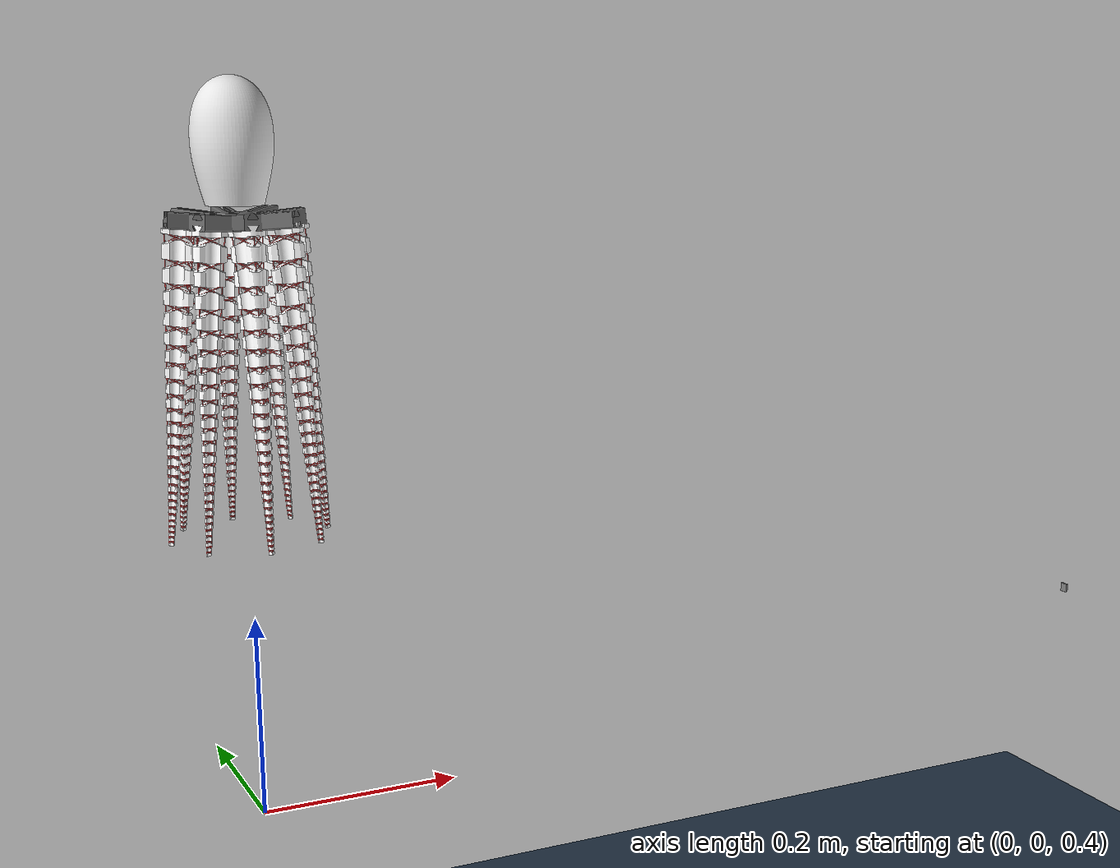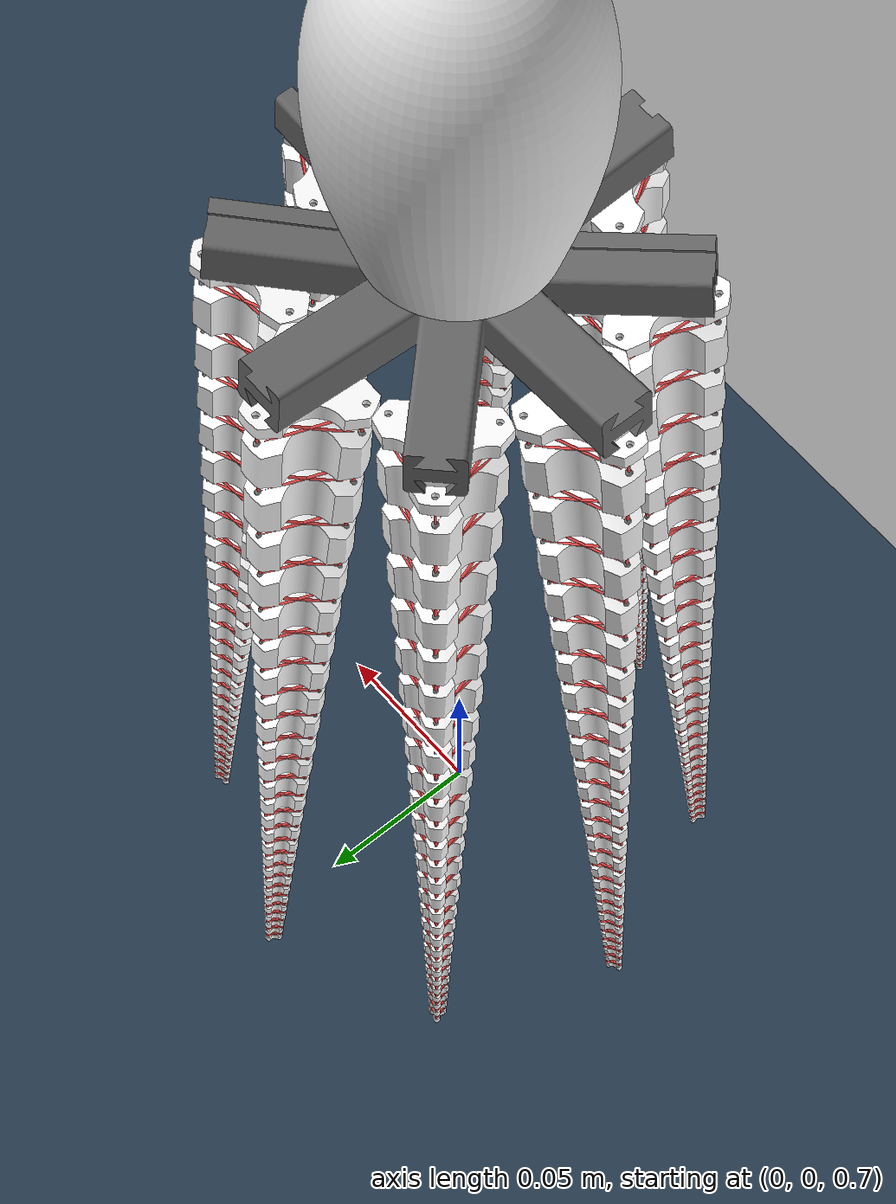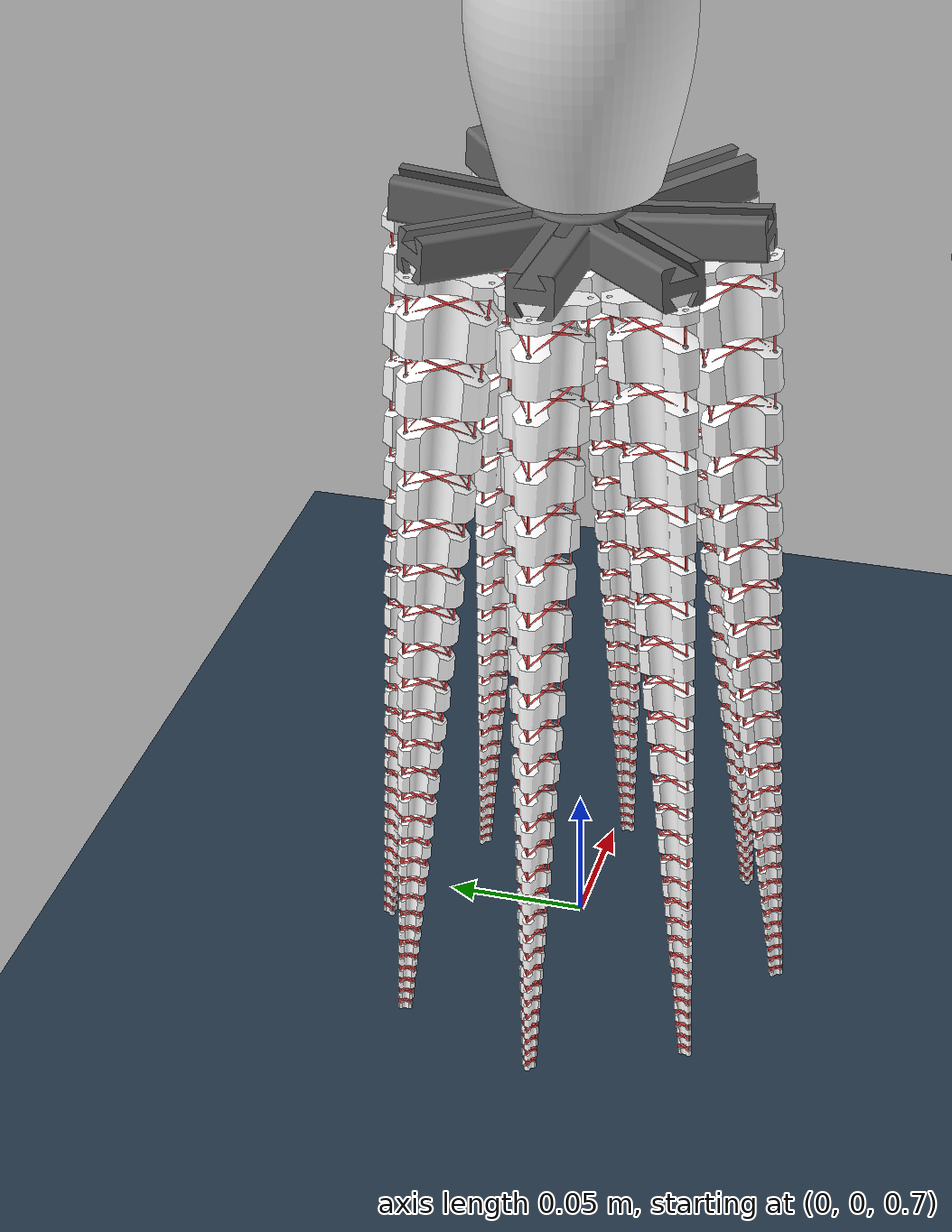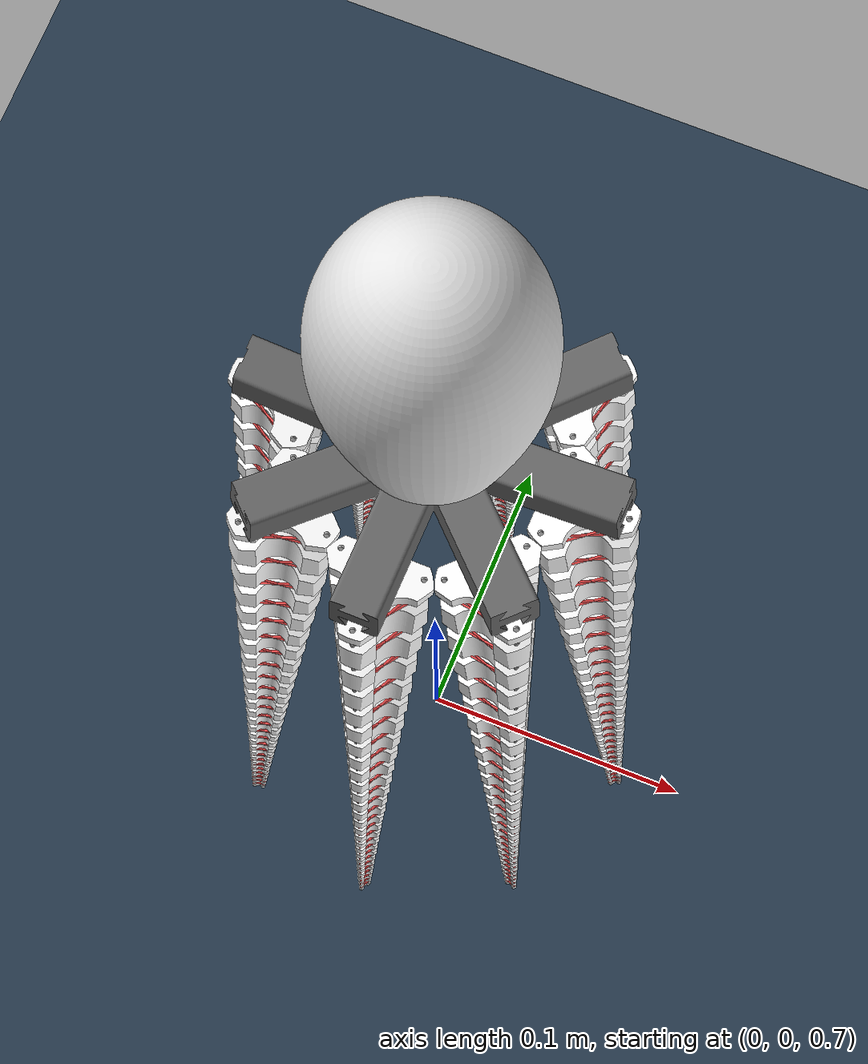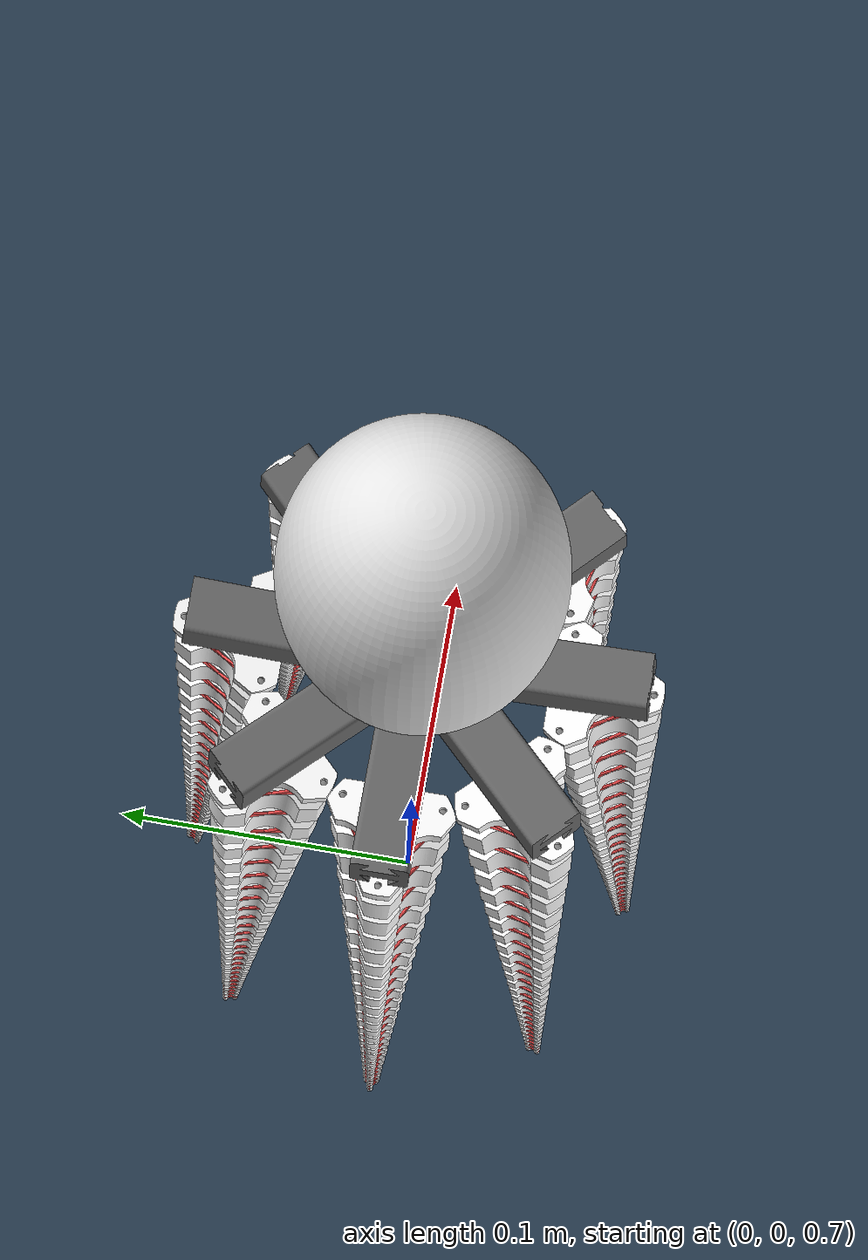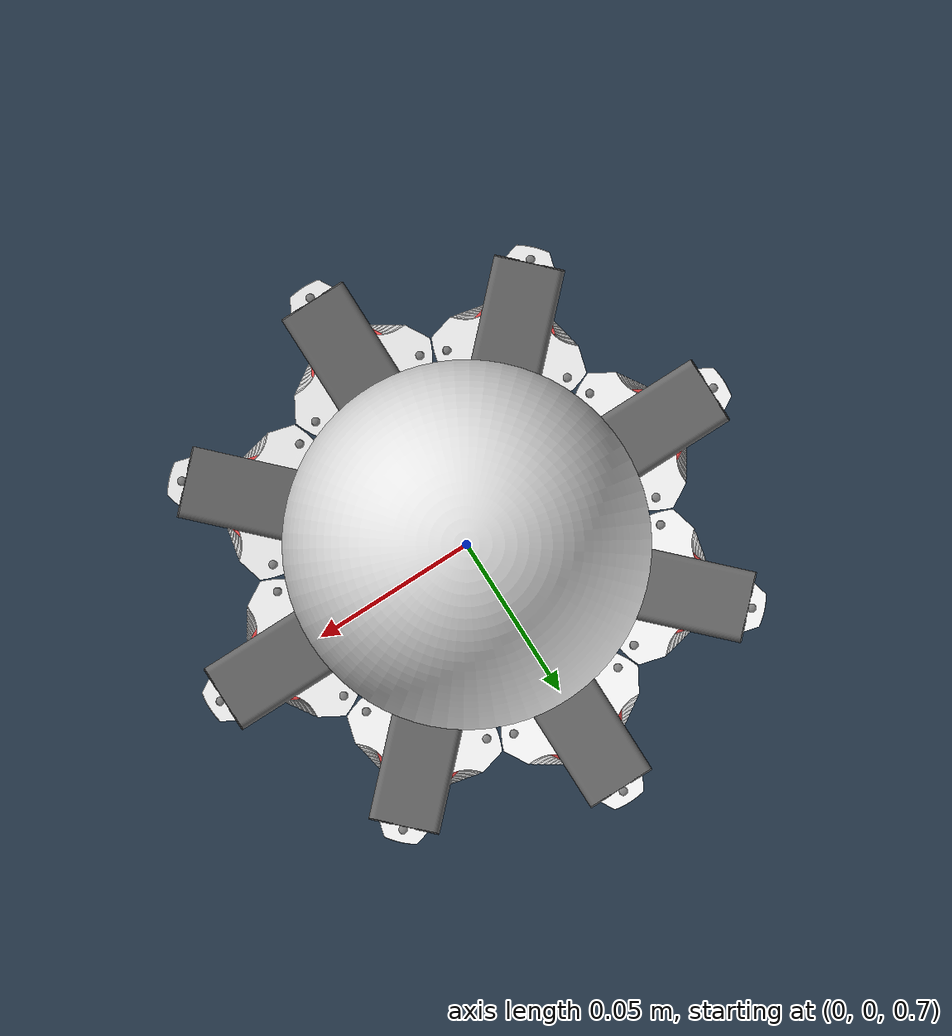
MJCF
<mujoco model="Octopus">
<compiler angle="radian" />
<option gravity="0 0 0"/>
<size nconmax="5000" njmax="5000"/>

<default>
	<default class="freej">
		<joint type="free" damping="0" armature="0" limited="false"/>
	</default>
</default>

<asset>
	<mesh name="head_mesh" file="3D_OctV2/meter/octhead_m_V2.STL" scale="1 1 1"/>
	<mesh name="nest_mesh" file="3D_OctV2/meter/octnest_m_V2.STL" scale="1 1 1"/>
	<mesh name="baseN_mesh" file="3D_OctV2/meter/3dt2_0_meter.STL" scale="1 1 1"/>
        <mesh name="segment1N_mesh" file="3D_OctV2/meter/3dt2_1_meter.STL" scale="1.000000000 1.000000000 1.000000000"/>
        <mesh name="segment2N_mesh" file="3D_OctV2/meter/3dt2_1_meter.STL" scale="0.928862710 0.928862710 0.928862710"/>
        <mesh name="segment3N_mesh" file="3D_OctV2/meter/3dt2_1_meter.STL" scale="0.862785933 0.862785933 0.862785933"/>
        <mesh name="segment4N_mesh" file="3D_OctV2/meter/3dt2_1_meter.STL" scale="0.801409680 0.801409680 0.801409680"/>
        <mesh name="segment5N_mesh" file="3D_OctV2/meter/3dt2_1_meter.STL" scale="0.744399566 0.744399566 0.744399566"/>
        <mesh name="segment6N_mesh" file="3D_OctV2/meter/3dt2_1_meter.STL" scale="0.691444998 0.691444998 0.691444998"/>
        <mesh name="segment7N_mesh" file="3D_OctV2/meter/3dt2_1_meter.STL" scale="0.642257474 0.642257474 0.642257474"/>
        <mesh name="segment8N_mesh" file="3D_OctV2/meter/3dt2_1_meter.STL" scale="0.596569018 0.596569018 0.596569018"/>
        <mesh name="segment9N_mesh" file="3D_OctV2/meter/3dt2_1_meter.STL" scale="0.554130714 0.554130714 0.554130714"/>
        <mesh name="segment10N_mesh" file="3D_OctV2/meter/3dt2_1_meter.STL" scale="0.514711357 0.514711357 0.514711357"/>
        <mesh name="segment11N_mesh" file="3D_OctV2/meter/3dt2_1_meter.STL" scale="0.478096185 0.478096185 0.478096185"/>
        <mesh name="segment12N_mesh" file="3D_OctV2/meter/3dt2_1_meter.STL" scale="0.444085718 0.444085718 0.444085718"/>
        <mesh name="segment13N_mesh" file="3D_OctV2/meter/3dt2_1_meter.STL" scale="0.412494663 0.412494663 0.412494663"/>
        <mesh name="segment14N_mesh" file="3D_OctV2/meter/3dt2_1_meter.STL" scale="0.383150911 0.383150911 0.383150911"/>
        <mesh name="segment15N_mesh" file="3D_OctV2/meter/3dt2_1_meter.STL" scale="0.355894593 0.355894593 0.355894593"/>
        <mesh name="segment16N_mesh" file="3D_OctV2/meter/3dt2_1_meter.STL" scale="0.330577216 0.330577216 0.330577216"/>
        <mesh name="segment17N_mesh" file="3D_OctV2/meter/3dt2_1_meter.STL" scale="0.307060849 0.307060849 0.307060849"/>
        <mesh name="segment18N_mesh" file="3D_OctV2/meter/3dt2_1_meter.STL" scale="0.285217372 0.285217372 0.285217372"/>
        <mesh name="segment19N_mesh" file="3D_OctV2/meter/3dt2_1_meter.STL" scale="0.264927781 0.264927781 0.264927781"/>
        <mesh name="segment20N_mesh" file="3D_OctV2/meter/3dt2_1_meter.STL" scale="0.246081536 0.246081536 0.246081536"/>
        <mesh name="segment21N_mesh" file="3D_OctV2/meter/3dt2_1_meter.STL" scale="0.228575963 0.228575963 0.228575963"/>
        <mesh name="segment22N_mesh" file="3D_OctV2/meter/3dt2_1_meter.STL" scale="0.212315688 0.212315688 0.212315688"/>
        <mesh name="segment23N_mesh" file="3D_OctV2/meter/3dt2_1_meter.STL" scale="0.197212125 0.197212125 0.197212125"/>
        <mesh name="segment24N_mesh" file="3D_OctV2/meter/3dt2_1_meter.STL" scale="0.183182989 0.183182989 0.183182989"/>
        <mesh name="segment25N_mesh" file="3D_OctV2/meter/3dt2_1_meter.STL" scale="0.170151847 0.170151847 0.170151847"/>
        <mesh name="segment26N_mesh" file="3D_OctV2/meter/3dt2_1_meter.STL" scale="0.158047706 0.158047706 0.158047706"/>

	<texture name="texplane" type="2d" builtin="checker" rgb1=".2 .3 .4" rgb2=".1 0.15 0.2" width="512" height="512" mark="cross" markrgb=".8 .8 .8"/>
	<texture type="skybox" builtin="gradient" rgb1="0.3 0.5 0.7" rgb2="0 0 0" width="512" height="3072" />
	<material name="matplane" reflectance="0.3" texture="texplane" texrepeat="1 1" texuniform="true"/>
</asset>

<worldbody>

<geom name="ground" type="plane" size="10 10 1" pos="0 0 0" quat="1 0 0 0" material="matplane" condim="1"/>
<light pos="1 0.5 0.7" dir="-1 -0.5 -1" directional="true" castshadow="false" diffuse="0.4 0.4 0.4" specular="0.1 0.1 0.1" />
<body name="mocapt" mocap="true" pos="1 0 0.5">
	<geom type="box" group="1" size="0.001 0.005 0.005" contype="0" conaffinity="0" rgba=".5 .5 .5 1"/>
</body>

<body name="head" pos="0 0 1" euler="0 0 0">
    <geom type="mesh" mesh="head_mesh" rgba="0.9 0.9 0.9 1"/>

	<body name="nest" pos="0 0 -0.025" euler="0 0 0">
    	<geom type="mesh" mesh="nest_mesh" rgba="0.4 0.4 0.4 1"/>

    <!-- First Robot with respect to the nest -->
		<body name="base1" pos="0 0.05 -0.002" euler="3.2289 0 0">
            <geom type="mesh" mesh="baseN_mesh" rgba="1 1 1 1"/>
                    <site name="site1_B1_R1" pos="0.014 0.008 -0.003" size="0.002 0.002 0.002"/>
                    <site name="site2_B1_R1" pos="0 -0.016 -0.003" size="0.002 0.002 0.002"/>
                    <site name="site3_B1_R1" pos="-0.014 0.008 -0.003" size="0.002 0.002 0.002"/>

            <body name="segment_1_R1" pos="0 0 0.001" euler="0 0 0">
                <geom type="mesh" mesh="segment1N_mesh" rgba="1 1 1 1"/>
                <joint name="J1_R1" pos="0 0 0" axis="1 0 0" type="ball" stiffness="0.462000000" damping="0.02"/>
                <inertial pos="0.011 0 0" quat="1 0 0 0" mass="0.01" diaginertia="0.000083 0.000083 0.00005"/>

                <site name="site1_S1_R1" pos="0.013190 0.007590 0.006000" size="0.001000 0.001000 0.001000"/>
                <site name="site2_S1_R1" pos="0.000000 -0.015190 0.006000" size="0.001000 0.001000 0.001000"/>
                <site name="site3_S1_R1" pos="-0.013190 0.007590 0.006000" size="0.001000 0.001000 0.001000"/>
                <site name="site4_S1_R1" pos="0.012690 0.007301 0.020000" size="0.001000 0.001000 0.001000"/>
                <site name="site5_S1_R1" pos="0.000000 -0.014614 0.020000" size="0.001000 0.001000 0.001000"/>
                <site name="site6_S1_R1" pos="-0.012689 0.007302 0.020000" size="0.001000 0.001000 0.001000"/>

                <body name="segment_2_R1" pos="0 0 0.02306" euler="0 0 0">
                    <geom type="mesh" mesh="segment2N_mesh" rgba="1 1 1 1"/>
                    <joint name="J2_R1" pos="0 0 0" axis="1 0 0" type="ball" stiffness="0.429134572" damping="0.02"/>
                    <inertial pos="0.011 0 0" quat="1 0 0 0" mass="0.01" diaginertia="0.000083 0.000083 0.00005"/>

                    <site name="site1_S2_R1" pos="0.012252 0.007050 0.005573" size="0.000929 0.000929 0.000929"/>
                    <site name="site2_S2_R1" pos="0.000000 -0.014109 0.005573" size="0.000929 0.000929 0.000929"/>
                    <site name="site3_S2_R1" pos="-0.012252 0.007050 0.005573" size="0.000929 0.000929 0.000929"/>
                    <site name="site4_S2_R1" pos="0.011787 0.006782 0.018577" size="0.000929 0.000929 0.000929"/>
                    <site name="site5_S2_R1" pos="0.000000 -0.013574 0.018577" size="0.000929 0.000929 0.000929"/>
                    <site name="site6_S2_R1" pos="-0.011786 0.006783 0.018577" size="0.000929 0.000929 0.000929"/>

                    <body name="segment_3_R1" pos="0 0 0.02149" euler="0 0 0">
                        <geom type="mesh" mesh="segment3N_mesh" rgba="1 1 1 1"/>
                        <joint name="J3_R1" pos="0 0 0" axis="1 0 0" type="ball" stiffness="0.398607101" damping="0.02"/>
                        <inertial pos="0.011 0 0" quat="1 0 0 0" mass="0.01" diaginertia="0.000083 0.000083 0.00005"/>

                        <site name="site1_S3_R1" pos="0.011380 0.006549 0.005177" size="0.000863 0.000863 0.000863"/>
                        <site name="site2_S3_R1" pos="0.000000 -0.013106 0.005177" size="0.000863 0.000863 0.000863"/>
                        <site name="site3_S3_R1" pos="-0.011380 0.006549 0.005177" size="0.000863 0.000863 0.000863"/>
                        <site name="site4_S3_R1" pos="0.010949 0.006299 0.017256" size="0.000863 0.000863 0.000863"/>
                        <site name="site5_S3_R1" pos="0.000000 -0.012609 0.017256" size="0.000863 0.000863 0.000863"/>
                        <site name="site6_S3_R1" pos="-0.010948 0.006300 0.017256" size="0.000863 0.000863 0.000863"/>

                        <body name="segment_4_R1" pos="0 0 0.02003" euler="0 0 0">
                            <geom type="mesh" mesh="segment4N_mesh" rgba="1 1 1 1"/>
                            <joint name="J4_R1" pos="0 0 0" axis="1 0 0" type="ball" stiffness="0.370251272" damping="0.02"/>
                            <inertial pos="0.011 0 0" quat="1 0 0 0" mass="0.01" diaginertia="0.000083 0.000083 0.00005"/>

                            <site name="site1_S4_R1" pos="0.010571 0.006083 0.004808" size="0.000801 0.000801 0.000801"/>
                            <site name="site2_S4_R1" pos="0.000000 -0.012173 0.004808" size="0.000801 0.000801 0.000801"/>
                            <site name="site3_S4_R1" pos="-0.010571 0.006083 0.004808" size="0.000801 0.000801 0.000801"/>
                            <site name="site4_S4_R1" pos="0.010170 0.005851 0.016028" size="0.000801 0.000801 0.000801"/>
                            <site name="site5_S4_R1" pos="0.000000 -0.011712 0.016028" size="0.000801 0.000801 0.000801"/>
                            <site name="site6_S4_R1" pos="-0.010169 0.005852 0.016028" size="0.000801 0.000801 0.000801"/>

                            <body name="segment_5_R1" pos="0 0 0.01868" euler="0 0 0">
                                <geom type="mesh" mesh="segment5N_mesh" rgba="1 1 1 1"/>
                                <joint name="J5_R1" pos="0 0 0" axis="1 0 0" type="ball" stiffness="0.343912600" damping="0.02"/>
                                <inertial pos="0.011 0 0" quat="1 0 0 0" mass="0.01" diaginertia="0.000083 0.000083 0.00005"/>

                                <site name="site1_S5_R1" pos="0.009819 0.005650 0.004466" size="0.000744 0.000744 0.000744"/>
                                <site name="site2_S5_R1" pos="0.000000 -0.011307 0.004466" size="0.000744 0.000744 0.000744"/>
                                <site name="site3_S5_R1" pos="-0.009819 0.005650 0.004466" size="0.000744 0.000744 0.000744"/>
                                <site name="site4_S5_R1" pos="0.009446 0.005435 0.014888" size="0.000744 0.000744 0.000744"/>
                                <site name="site5_S5_R1" pos="0.000000 -0.010879 0.014888" size="0.000744 0.000744 0.000744"/>
                                <site name="site6_S5_R1" pos="-0.009446 0.005436 0.014888" size="0.000744 0.000744 0.000744"/>

                                <body name="segment_6_R1" pos="0 0 0.01742" euler="0 0 0">
                                    <geom type="mesh" mesh="segment6N_mesh" rgba="1 1 1 1"/>
                                    <joint name="J6_R1" pos="0 0 0" axis="1 0 0" type="ball" stiffness="0.319447589" damping="0.02"/>
                                    <inertial pos="0.011 0 0" quat="1 0 0 0" mass="0.01" diaginertia="0.000083 0.000083 0.00005"/>

                                    <site name="site1_S6_R1" pos="0.009120 0.005248 0.004149" size="0.000691 0.000691 0.000691"/>
                                    <site name="site2_S6_R1" pos="0.000000 -0.010503 0.004149" size="0.000691 0.000691 0.000691"/>
                                    <site name="site3_S6_R1" pos="-0.009120 0.005248 0.004149" size="0.000691 0.000691 0.000691"/>
                                    <site name="site4_S6_R1" pos="0.008774 0.005048 0.013829" size="0.000691 0.000691 0.000691"/>
                                    <site name="site5_S6_R1" pos="0.000000 -0.010105 0.013829" size="0.000691 0.000691 0.000691"/>
                                    <site name="site6_S6_R1" pos="-0.008774 0.005049 0.013829" size="0.000691 0.000691 0.000691"/>

                                    <body name="segment_7_R1" pos="0 0 0.01625" euler="0 0 0">
                                        <geom type="mesh" mesh="segment7N_mesh" rgba="1 1 1 1"/>
                                        <joint name="J7_R1" pos="0 0 0" axis="1 0 0" type="ball" stiffness="0.296722953" damping="0.02"/>
                                        <inertial pos="0.011 0 0" quat="1 0 0 0" mass="0.01" diaginertia="0.000083 0.000083 0.00005"/>

                                        <site name="site1_S7_R1" pos="0.008471 0.004875 0.003854" size="0.000642 0.000642 0.000642"/>
                                        <site name="site2_S7_R1" pos="0.000000 -0.009756 0.003854" size="0.000642 0.000642 0.000642"/>
                                        <site name="site3_S7_R1" pos="-0.008471 0.004875 0.003854" size="0.000642 0.000642 0.000642"/>
                                        <site name="site4_S7_R1" pos="0.008150 0.004689 0.012845" size="0.000642 0.000642 0.000642"/>
                                        <site name="site5_S7_R1" pos="0.000000 -0.009386 0.012845" size="0.000642 0.000642 0.000642"/>
                                        <site name="site6_S7_R1" pos="-0.008150 0.004690 0.012845" size="0.000642 0.000642 0.000642"/>

                                        <body name="segment_8_R1" pos="0 0 0.01517" euler="0 0 0">
                                            <geom type="mesh" mesh="segment8N_mesh" rgba="1 1 1 1"/>
                                            <joint name="J8_R1" pos="0 0 0" axis="1 0 0" type="ball" stiffness="0.275614886" damping="0.02"/>
                                            <inertial pos="0.011 0 0" quat="1 0 0 0" mass="0.01" diaginertia="0.000083 0.000083 0.00005"/>

                                            <site name="site1_S8_R1" pos="0.007869 0.004528 0.003579" size="0.000597 0.000597 0.000597"/>
                                            <site name="site2_S8_R1" pos="0.000000 -0.009062 0.003579" size="0.000597 0.000597 0.000597"/>
                                            <site name="site3_S8_R1" pos="-0.007869 0.004528 0.003579" size="0.000597 0.000597 0.000597"/>
                                            <site name="site4_S8_R1" pos="0.007570 0.004356 0.011931" size="0.000597 0.000597 0.000597"/>
                                            <site name="site5_S8_R1" pos="0.000000 -0.008718 0.011931" size="0.000597 0.000597 0.000597"/>
                                            <site name="site6_S8_R1" pos="-0.007570 0.004356 0.011931" size="0.000597 0.000597 0.000597"/>

                                            <body name="segment_9_R1" pos="0 0 0.01416" euler="0 0 0">
                                                <geom type="mesh" mesh="segment9N_mesh" rgba="1 1 1 1"/>
                                                <joint name="J9_R1" pos="0 0 0" axis="1 0 0" type="ball" stiffness="0.256008390" damping="0.02"/>
                                                <inertial pos="0.011 0 0" quat="1 0 0 0" mass="0.01" diaginertia="0.000083 0.000083 0.00005"/>

                                                <site name="site1_S9_R1" pos="0.007309 0.004206 0.003325" size="0.000554 0.000554 0.000554"/>
                                                <site name="site2_S9_R1" pos="0.000000 -0.008417 0.003325" size="0.000554 0.000554 0.000554"/>
                                                <site name="site3_S9_R1" pos="-0.007309 0.004206 0.003325" size="0.000554 0.000554 0.000554"/>
                                                <site name="site4_S9_R1" pos="0.007032 0.004046 0.011083" size="0.000554 0.000554 0.000554"/>
                                                <site name="site5_S9_R1" pos="0.000000 -0.008098 0.011083" size="0.000554 0.000554 0.000554"/>
                                                <site name="site6_S9_R1" pos="-0.007031 0.004046 0.011083" size="0.000554 0.000554 0.000554"/>

                                                <body name="segment_10_R1" pos="0 0 0.01322" euler="0 0 0">
                                                    <geom type="mesh" mesh="segment10N_mesh" rgba="1 1 1 1"/>
                                                    <joint name="J10_R1" pos="0 0 0" axis="1 0 0" type="ball" stiffness="0.237796647" damping="0.02"/>
                                                    <inertial pos="0.011 0 0" quat="1 0 0 0" mass="0.01" diaginertia="0.000083 0.000083 0.00005"/>

                                                    <site name="site1_S10_R1" pos="0.006789 0.003907 0.003088" size="0.000515 0.000515 0.000515"/>
                                                    <site name="site2_S10_R1" pos="0.000000 -0.007818 0.003088" size="0.000515 0.000515 0.000515"/>
                                                    <site name="site3_S10_R1" pos="-0.006789 0.003907 0.003088" size="0.000515 0.000515 0.000515"/>
                                                    <site name="site4_S10_R1" pos="0.006532 0.003758 0.010294" size="0.000515 0.000515 0.000515"/>
                                                    <site name="site5_S10_R1" pos="0.000000 -0.007522 0.010294" size="0.000515 0.000515 0.000515"/>
                                                    <site name="site6_S10_R1" pos="-0.006531 0.003758 0.010294" size="0.000515 0.000515 0.000515"/>

                                                    <body name="segment_11_R1" pos="0 0 0.01235" euler="0 0 0">
                                                        <geom type="mesh" mesh="segment11N_mesh" rgba="1 1 1 1"/>
                                                        <joint name="J11_R1" pos="0 0 0" axis="1 0 0" type="ball" stiffness="0.220880438" damping="0.02"/>
                                                        <inertial pos="0.011 0 0" quat="1 0 0 0" mass="0.01" diaginertia="0.000083 0.000083 0.00005"/>

                                                        <site name="site1_S11_R1" pos="0.006306 0.003629 0.002869" size="0.000478 0.000478 0.000478"/>
                                                        <site name="site2_S11_R1" pos="0.000000 -0.007262 0.002869" size="0.000478 0.000478 0.000478"/>
                                                        <site name="site3_S11_R1" pos="-0.006306 0.003629 0.002869" size="0.000478 0.000478 0.000478"/>
                                                        <site name="site4_S11_R1" pos="0.006067 0.003491 0.009562" size="0.000478 0.000478 0.000478"/>
                                                        <site name="site5_S11_R1" pos="0.000000 -0.006987 0.009562" size="0.000478 0.000478 0.000478"/>
                                                        <site name="site6_S11_R1" pos="-0.006067 0.003491 0.009562" size="0.000478 0.000478 0.000478"/>

                                                        <body name="segment_12_R1" pos="0 0 0.01155" euler="0 0 0">
                                                            <geom type="mesh" mesh="segment12N_mesh" rgba="1 1 1 1"/>
                                                            <joint name="J12_R1" pos="0 0 0" axis="1 0 0" type="ball" stiffness="0.205167602" damping="0.02"/>
                                                            <inertial pos="0.011 0 0" quat="1 0 0 0" mass="0.01" diaginertia="0.000083 0.000083 0.00005"/>

                                                            <site name="site1_S12_R1" pos="0.005857 0.003371 0.002665" size="0.000444 0.000444 0.000444"/>
                                                            <site name="site2_S12_R1" pos="0.000000 -0.006746 0.002665" size="0.000444 0.000444 0.000444"/>
                                                            <site name="site3_S12_R1" pos="-0.005857 0.003371 0.002665" size="0.000444 0.000444 0.000444"/>
                                                            <site name="site4_S12_R1" pos="0.005635 0.003242 0.008882" size="0.000444 0.000444 0.000444"/>
                                                            <site name="site5_S12_R1" pos="0.000000 -0.006490 0.008882" size="0.000444 0.000444 0.000444"/>
                                                            <site name="site6_S12_R1" pos="-0.005635 0.003243 0.008882" size="0.000444 0.000444 0.000444"/>

                                                            <body name="segment_13_R1" pos="0 0 0.01080" euler="0 0 0">
                                                                <geom type="mesh" mesh="segment13N_mesh" rgba="1 1 1 1"/>
                                                                <joint name="J13_R1" pos="0 0 0" axis="1 0 0" type="ball" stiffness="0.190572535" damping="0.02"/>
                                                                <inertial pos="0.011 0 0" quat="1 0 0 0" mass="0.01" diaginertia="0.000083 0.000083 0.00005"/>

                                                                <site name="site1_S13_R1" pos="0.005441 0.003131 0.002475" size="0.000412 0.000412 0.000412"/>
                                                                <site name="site2_S13_R1" pos="0.000000 -0.006266 0.002475" size="0.000412 0.000412 0.000412"/>
                                                                <site name="site3_S13_R1" pos="-0.005441 0.003131 0.002475" size="0.000412 0.000412 0.000412"/>
                                                                <site name="site4_S13_R1" pos="0.005235 0.003012 0.008250" size="0.000412 0.000412 0.000412"/>
                                                                <site name="site5_S13_R1" pos="0.000000 -0.006028 0.008250" size="0.000412 0.000412 0.000412"/>
                                                                <site name="site6_S13_R1" pos="-0.005234 0.003012 0.008250" size="0.000412 0.000412 0.000412"/>

                                                                <body name="segment_14_R1" pos="0 0 0.01010" euler="0 0 0">
                                                                    <geom type="mesh" mesh="segment14N_mesh" rgba="1 1 1 1"/>
                                                                    <joint name="J14_R1" pos="0 0 0" axis="1 0 0" type="ball" stiffness="0.177015721" damping="0.02"/>
                                                                    <inertial pos="0.011 0 0" quat="1 0 0 0" mass="0.01" diaginertia="0.000083 0.000083 0.00005"/>

                                                                    <site name="site1_S14_R1" pos="0.005054 0.002908 0.002299" size="0.000383 0.000383 0.000383"/>
                                                                    <site name="site2_S14_R1" pos="0.000000 -0.005820 0.002299" size="0.000383 0.000383 0.000383"/>
                                                                    <site name="site3_S14_R1" pos="-0.005054 0.002908 0.002299" size="0.000383 0.000383 0.000383"/>
                                                                    <site name="site4_S14_R1" pos="0.004862 0.002797 0.007663" size="0.000383 0.000383 0.000383"/>
                                                                    <site name="site5_S14_R1" pos="0.000000 -0.005599 0.007663" size="0.000383 0.000383 0.000383"/>
                                                                    <site name="site6_S14_R1" pos="-0.004862 0.002798 0.007663" size="0.000383 0.000383 0.000383"/>

                                                                    <body name="segment_15_R1" pos="0 0 0.00945" euler="0 0 0">
                                                                        <geom type="mesh" mesh="segment15N_mesh" rgba="1 1 1 1"/>
                                                                        <joint name="J15_R1" pos="0 0 0" axis="1 0 0" type="ball" stiffness="0.164423302" damping="0.02"/>
                                                                        <inertial pos="0.011 0 0" quat="1 0 0 0" mass="0.01" diaginertia="0.000083 0.000083 0.00005"/>

                                                                        <site name="site1_S15_R1" pos="0.004694 0.002701 0.002135" size="0.000356 0.000356 0.000356"/>
                                                                        <site name="site2_S15_R1" pos="0.000000 -0.005406 0.002135" size="0.000356 0.000356 0.000356"/>
                                                                        <site name="site3_S15_R1" pos="-0.004694 0.002701 0.002135" size="0.000356 0.000356 0.000356"/>
                                                                        <site name="site4_S15_R1" pos="0.004516 0.002598 0.007118" size="0.000356 0.000356 0.000356"/>
                                                                        <site name="site5_S15_R1" pos="0.000000 -0.005201 0.007118" size="0.000356 0.000356 0.000356"/>
                                                                        <site name="site6_S15_R1" pos="-0.004516 0.002599 0.007118" size="0.000356 0.000356 0.000356"/>

                                                                        <body name="segment_16_R1" pos="0 0 0.00885" euler="0 0 0">
                                                                            <geom type="mesh" mesh="segment16N_mesh" rgba="1 1 1 1"/>
                                                                            <joint name="J16_R1" pos="0 0 0" axis="1 0 0" type="ball" stiffness="0.152726674" damping="0.02"/>
                                                                            <inertial pos="0.011 0 0" quat="1 0 0 0" mass="0.01" diaginertia="0.000083 0.000083 0.00005"/>

                                                                            <site name="site1_S16_R1" pos="0.004360 0.002509 0.001983" size="0.000331 0.000331 0.000331"/>
                                                                            <site name="site2_S16_R1" pos="0.000000 -0.005021 0.001983" size="0.000331 0.000331 0.000331"/>
                                                                            <site name="site3_S16_R1" pos="-0.004360 0.002509 0.001983" size="0.000331 0.000331 0.000331"/>
                                                                            <site name="site4_S16_R1" pos="0.004195 0.002414 0.006612" size="0.000331 0.000331 0.000331"/>
                                                                            <site name="site5_S16_R1" pos="0.000000 -0.004831 0.006612" size="0.000331 0.000331 0.000331"/>
                                                                            <site name="site6_S16_R1" pos="-0.004195 0.002414 0.006612" size="0.000331 0.000331 0.000331"/>

                                                                            <body name="segment_17_R1" pos="0 0 0.00829" euler="0 0 0">
                                                                                <geom type="mesh" mesh="segment17N_mesh" rgba="1 1 1 1"/>
                                                                                <joint name="J17_R1" pos="0 0 0" axis="1 0 0" type="ball" stiffness="0.141862112" damping="0.02"/>
                                                                                <inertial pos="0.011 0 0" quat="1 0 0 0" mass="0.01" diaginertia="0.000083 0.000083 0.00005"/>

                                                                                <site name="site1_S17_R1" pos="0.004050 0.002331 0.001842" size="0.000307 0.000307 0.000307"/>
                                                                                <site name="site2_S17_R1" pos="0.000000 -0.004664 0.001842" size="0.000307 0.000307 0.000307"/>
                                                                                <site name="site3_S17_R1" pos="-0.004050 0.002331 0.001842" size="0.000307 0.000307 0.000307"/>
                                                                                <site name="site4_S17_R1" pos="0.003897 0.002242 0.006141" size="0.000307 0.000307 0.000307"/>
                                                                                <site name="site5_S17_R1" pos="0.000000 -0.004487 0.006141" size="0.000307 0.000307 0.000307"/>
                                                                                <site name="site6_S17_R1" pos="-0.003896 0.002242 0.006141" size="0.000307 0.000307 0.000307"/>

                                                                                <body name="segment_18_R1" pos="0 0 0.00777" euler="0 0 0">
                                                                                    <geom type="mesh" mesh="segment18N_mesh" rgba="1 1 1 1"/>
                                                                                    <joint name="J18_R1" pos="0 0 0" axis="1 0 0" type="ball" stiffness="0.131770426" damping="0.02"/>
                                                                                    <inertial pos="0.011 0 0" quat="1 0 0 0" mass="0.01" diaginertia="0.000083 0.000083 0.00005"/>

                                                                                    <site name="site1_S18_R1" pos="0.003762 0.002165 0.001711" size="0.000285 0.000285 0.000285"/>
                                                                                    <site name="site2_S18_R1" pos="0.000000 -0.004332 0.001711" size="0.000285 0.000285 0.000285"/>
                                                                                    <site name="site3_S18_R1" pos="-0.003762 0.002165 0.001711" size="0.000285 0.000285 0.000285"/>
                                                                                    <site name="site4_S18_R1" pos="0.003619 0.002082 0.005704" size="0.000285 0.000285 0.000285"/>
                                                                                    <site name="site5_S18_R1" pos="0.000000 -0.004168 0.005704" size="0.000285 0.000285 0.000285"/>
                                                                                    <site name="site6_S18_R1" pos="-0.003619 0.002083 0.005704" size="0.000285 0.000285 0.000285"/>

                                                                                    <body name="segment_19_R1" pos="0 0 0.00729" euler="0 0 0">
                                                                                        <geom type="mesh" mesh="segment19N_mesh" rgba="1 1 1 1"/>
                                                                                        <joint name="J19_R1" pos="0 0 0" axis="1 0 0" type="ball" stiffness="0.122396635" damping="0.02"/>
                                                                                        <inertial pos="0.011 0 0" quat="1 0 0 0" mass="0.01" diaginertia="0.000083 0.000083 0.00005"/>

                                                                                        <site name="site1_S19_R1" pos="0.003494 0.002011 0.001590" size="0.000265 0.000265 0.000265"/>
                                                                                        <site name="site2_S19_R1" pos="0.000000 -0.004024 0.001590" size="0.000265 0.000265 0.000265"/>
                                                                                        <site name="site3_S19_R1" pos="-0.003494 0.002011 0.001590" size="0.000265 0.000265 0.000265"/>
                                                                                        <site name="site4_S19_R1" pos="0.003362 0.001934 0.005299" size="0.000265 0.000265 0.000265"/>
                                                                                        <site name="site5_S19_R1" pos="0.000000 -0.003872 0.005299" size="0.000265 0.000265 0.000265"/>
                                                                                        <site name="site6_S19_R1" pos="-0.003362 0.001935 0.005299" size="0.000265 0.000265 0.000265"/>

                                                                                        <body name="segment_20_R1" pos="0 0 0.00684" euler="0 0 0">
                                                                                            <geom type="mesh" mesh="segment20N_mesh" rgba="1 1 1 1"/>
                                                                                            <joint name="J20_R1" pos="0 0 0" axis="1 0 0" type="ball" stiffness="0.113689670" damping="0.02"/>
                                                                                            <inertial pos="0.011 0 0" quat="1 0 0 0" mass="0.01" diaginertia="0.000083 0.000083 0.00005"/>

                                                                                            <site name="site1_S20_R1" pos="0.003246 0.001868 0.001476" size="0.000246 0.000246 0.000246"/>
                                                                                            <site name="site2_S20_R1" pos="0.000000 -0.003738 0.001476" size="0.000246 0.000246 0.000246"/>
                                                                                            <site name="site3_S20_R1" pos="-0.003246 0.001868 0.001476" size="0.000246 0.000246 0.000246"/>
                                                                                            <site name="site4_S20_R1" pos="0.003123 0.001797 0.004922" size="0.000246 0.000246 0.000246"/>
                                                                                            <site name="site5_S20_R1" pos="0.000000 -0.003596 0.004922" size="0.000246 0.000246 0.000246"/>
                                                                                            <site name="site6_S20_R1" pos="-0.003123 0.001797 0.004922" size="0.000246 0.000246 0.000246"/>

                                                                                            <body name="segment_21_R1" pos="0 0 0.00643" euler="0 0 0">
                                                                                                <geom type="mesh" mesh="segment21N_mesh" rgba="1 1 1 1"/>
                                                                                                <joint name="J21_R1" pos="0 0 0" axis="1 0 0" type="ball" stiffness="0.105602095" damping="0.02"/>
                                                                                                <inertial pos="0.011 0 0" quat="1 0 0 0" mass="0.01" diaginertia="0.000083 0.000083 0.00005"/>

                                                                                                <site name="site1_S21_R1" pos="0.003015 0.001735 0.001371" size="0.000229 0.000229 0.000229"/>
                                                                                                <site name="site2_S21_R1" pos="0.000000 -0.003472 0.001371" size="0.000229 0.000229 0.000229"/>
                                                                                                <site name="site3_S21_R1" pos="-0.003015 0.001735 0.001371" size="0.000229 0.000229 0.000229"/>
                                                                                                <site name="site4_S21_R1" pos="0.002901 0.001669 0.004572" size="0.000229 0.000229 0.000229"/>
                                                                                                <site name="site5_S21_R1" pos="0.000000 -0.003340 0.004572" size="0.000229 0.000229 0.000229"/>
                                                                                                <site name="site6_S21_R1" pos="-0.002900 0.001669 0.004572" size="0.000229 0.000229 0.000229"/>

                                                                                                <body name="segment_22_R1" pos="0 0 0.00604" euler="0 0 0">
                                                                                                    <geom type="mesh" mesh="segment22N_mesh" rgba="1 1 1 1"/>
                                                                                                    <joint name="J22_R1" pos="0 0 0" axis="1 0 0" type="ball" stiffness="0.098089848" damping="0.02"/>
                                                                                                    <inertial pos="0.011 0 0" quat="1 0 0 0" mass="0.01" diaginertia="0.000083 0.000083 0.00005"/>

                                                                                                    <site name="site1_S22_R1" pos="0.002800 0.001611 0.001274" size="0.000212 0.000212 0.000212"/>
                                                                                                    <site name="site2_S22_R1" pos="0.000000 -0.003225 0.001274" size="0.000212 0.000212 0.000212"/>
                                                                                                    <site name="site3_S22_R1" pos="-0.002800 0.001611 0.001274" size="0.000212 0.000212 0.000212"/>
                                                                                                    <site name="site4_S22_R1" pos="0.002694 0.001550 0.004246" size="0.000212 0.000212 0.000212"/>
                                                                                                    <site name="site5_S22_R1" pos="0.000000 -0.003103 0.004246" size="0.000212 0.000212 0.000212"/>
                                                                                                    <site name="site6_S22_R1" pos="-0.002694 0.001550 0.004246" size="0.000212 0.000212 0.000212"/>

                                                                                                    <body name="segment_23_R1" pos="0 0 0.00568" euler="0 0 0">
                                                                                                        <geom type="mesh" mesh="segment23N_mesh" rgba="1 1 1 1"/>
                                                                                                        <joint name="J23_R1" pos="0 0 0" axis="1 0 0" type="ball" stiffness="0.091112002" damping="0.02"/>
                                                                                                        <inertial pos="0.011 0 0" quat="1 0 0 0" mass="0.01" diaginertia="0.000083 0.000083 0.00005"/>

                                                                                                        <site name="site1_S23_R1" pos="0.002601 0.001497 0.001183" size="0.000197 0.000197 0.000197"/>
                                                                                                        <site name="site2_S23_R1" pos="0.000000 -0.002996 0.001183" size="0.000197 0.000197 0.000197"/>
                                                                                                        <site name="site3_S23_R1" pos="-0.002601 0.001497 0.001183" size="0.000197 0.000197 0.000197"/>
                                                                                                        <site name="site4_S23_R1" pos="0.002503 0.001440 0.003944" size="0.000197 0.000197 0.000197"/>
                                                                                                        <site name="site5_S23_R1" pos="0.000000 -0.002882 0.003944" size="0.000197 0.000197 0.000197"/>
                                                                                                        <site name="site6_S23_R1" pos="-0.002502 0.001440 0.003944" size="0.000197 0.000197 0.000197"/>

                                                                                                        <body name="segment_24_R1" pos="0 0 0.00535" euler="0 0 0">
                                                                                                            <geom type="mesh" mesh="segment24N_mesh" rgba="1 1 1 1"/>
                                                                                                            <joint name="J24_R1" pos="0 0 0" axis="1 0 0" type="ball" stiffness="0.084630541" damping="0.02"/>
                                                                                                            <inertial pos="0.011 0 0" quat="1 0 0 0" mass="0.01" diaginertia="0.000083 0.000083 0.00005"/>

                                                                                                            <site name="site1_S24_R1" pos="0.002416 0.001390 0.001099" size="0.000183 0.000183 0.000183"/>
                                                                                                            <site name="site2_S24_R1" pos="0.000000 -0.002783 0.001099" size="0.000183 0.000183 0.000183"/>
                                                                                                            <site name="site3_S24_R1" pos="-0.002416 0.001390 0.001099" size="0.000183 0.000183 0.000183"/>
                                                                                                            <site name="site4_S24_R1" pos="0.002325 0.001337 0.003664" size="0.000183 0.000183 0.000183"/>
                                                                                                            <site name="site5_S24_R1" pos="0.000000 -0.002677 0.003664" size="0.000183 0.000183 0.000183"/>
                                                                                                            <site name="site6_S24_R1" pos="-0.002324 0.001338 0.003664" size="0.000183 0.000183 0.000183"/>

                                                                                                            <body name="segment_25_R1" pos="0 0 0.00504" euler="0 0 0">
                                                                                                                <geom type="mesh" mesh="segment25N_mesh" rgba="1 1 1 1"/>
                                                                                                                <joint name="J25_R1" pos="0 0 0" axis="1 0 0" type="ball" stiffness="0.078610154" damping="0.02"/>
                                                                                                                <inertial pos="0.011 0 0" quat="1 0 0 0" mass="0.01" diaginertia="0.000083 0.000083 0.00005"/>

                                                                                                                <site name="site1_S25_R1" pos="0.002244 0.001291 0.001021" size="0.000170 0.000170 0.000170"/>
                                                                                                                <site name="site2_S25_R1" pos="0.000000 -0.002585 0.001021" size="0.000170 0.000170 0.000170"/>
                                                                                                                <site name="site3_S25_R1" pos="-0.002244 0.001291 0.001021" size="0.000170 0.000170 0.000170"/>
                                                                                                                <site name="site4_S25_R1" pos="0.002159 0.001242 0.003403" size="0.000170 0.000170 0.000170"/>
                                                                                                                <site name="site5_S25_R1" pos="0.000000 -0.002487 0.003403" size="0.000170 0.000170 0.000170"/>
                                                                                                                <site name="site6_S25_R1" pos="-0.002159 0.001242 0.003403" size="0.000170 0.000170 0.000170"/>

                                                                                                                <body name="segment_26_R1" pos="0 0 0.00475" euler="0 0 0">
                                                                                                                    <geom type="mesh" mesh="segment26N_mesh" rgba="1 1 1 1"/>
                                                                                                                    <joint name="J26_R1" pos="0 0 0" axis="1 0 0" type="ball" stiffness="0.073018040" damping="0.02"/>
                                                                                                                    <inertial pos="0.011 0 0" quat="1 0 0 0" mass="0.01" diaginertia="0.000083 0.000083 0.00005"/>

                                                                                                                    <site name="site1_S26_R1" pos="0.002085 0.001200 0.000948" size="0.000158 0.000158 0.000158"/>
                                                                                                                    <site name="site2_S26_R1" pos="0.000000 -0.002401 0.000948" size="0.000158 0.000158 0.000158"/>
                                                                                                                    <site name="site3_S26_R1" pos="-0.002085 0.001200 0.000948" size="0.000158 0.000158 0.000158"/>
                                                                                                                    <site name="site4_S26_R1" pos="0.002006 0.001154 0.003161" size="0.000158 0.000158 0.000158"/>
                                                                                                                    <site name="site5_S26_R1" pos="0.000000 -0.002310 0.003161" size="0.000158 0.000158 0.000158"/>
                                                                                                                    <site name="site6_S26_R1" pos="-0.002005 0.001154 0.003161" size="0.000158 0.000158 0.000158"/>

                                                                                                                </body>
                                                                                                            </body>
                                                                                                        </body>
                                                                                                    </body>
                                                                                                </body>
                                                                                            </body>
                                                                                        </body>
                                                                                    </body>
                                                                                </body>
                                                                            </body>
                                                                        </body>
                                                                    </body>
                                                                </body>
                                                            </body>
                                                        </body>
                                                    </body>
                                                </body>
                                            </body>
                                        </body>
                                    </body>
                                </body>
                            </body>
                        </body>
                    </body>
                </body>
            </body>

        </body>

		<!-- Second Robot with respect to the nest -->
		<body name="base2" pos="0 -0.05 -0.002" euler="3.0543 0 3.1416">
            <geom type="mesh" mesh="baseN_mesh" rgba="1 1 1 1"/>
                    <site name="site1_B2_R2" pos="0.014 0.008 -0.003" size="0.002 0.002 0.002"/>
                    <site name="site2_B2_R2" pos="0 -0.016 -0.003" size="0.002 0.002 0.002"/>
                    <site name="site3_B2_R2" pos="-0.014 0.008 -0.003" size="0.002 0.002 0.002"/>

            <body name="segment_1_R2" pos="0 0 0.00100" euler="0 0 0">
                <geom type="mesh" mesh="segment1N_mesh" rgba="1 1 1 1"/>
                <joint name="J1_R2" pos="0 0 0" axis="1 0 0" type="ball" stiffness="0.462000000" damping="0.02"/>
                <inertial pos="0.011 0 0" quat="1 0 0 0" mass="0.01" diaginertia="0.000083 0.000083 0.00005"/>

                <site name="site1_S1_R2" pos="0.013190 0.007590 0.006000" size="0.001000 0.001000 0.001000"/>
                <site name="site2_S1_R2" pos="0.000000 -0.015190 0.006000" size="0.001000 0.001000 0.001000"/>
                <site name="site3_S1_R2" pos="-0.013190 0.007590 0.006000" size="0.001000 0.001000 0.001000"/>
                <site name="site4_S1_R2" pos="0.012690 0.007301 0.020000" size="0.001000 0.001000 0.001000"/>
                <site name="site5_S1_R2" pos="0.000000 -0.014614 0.020000" size="0.001000 0.001000 0.001000"/>
                <site name="site6_S1_R2" pos="-0.012689 0.007302 0.020000" size="0.001000 0.001000 0.001000"/>

                <body name="segment_2_R2" pos="0 0 0.02306" euler="0 0 0">
                    <geom type="mesh" mesh="segment2N_mesh" rgba="1 1 1 1"/>
                    <joint name="J2_R2" pos="0 0 0" axis="1 0 0" type="ball" stiffness="0.429134572" damping="0.02"/>
                    <inertial pos="0.011 0 0" quat="1 0 0 0" mass="0.01" diaginertia="0.000083 0.000083 0.00005"/>

                    <site name="site1_S2_R2" pos="0.012252 0.007050 0.005573" size="0.000929 0.000929 0.000929"/>
                    <site name="site2_S2_R2" pos="0.000000 -0.014109 0.005573" size="0.000929 0.000929 0.000929"/>
                    <site name="site3_S2_R2" pos="-0.012252 0.007050 0.005573" size="0.000929 0.000929 0.000929"/>
                    <site name="site4_S2_R2" pos="0.011787 0.006782 0.018577" size="0.000929 0.000929 0.000929"/>
                    <site name="site5_S2_R2" pos="0.000000 -0.013574 0.018577" size="0.000929 0.000929 0.000929"/>
                    <site name="site6_S2_R2" pos="-0.011786 0.006783 0.018577" size="0.000929 0.000929 0.000929"/>

                    <body name="segment_3_R2" pos="0 0 0.02149" euler="0 0 0">
                        <geom type="mesh" mesh="segment3N_mesh" rgba="1 1 1 1"/>
                        <joint name="J3_R2" pos="0 0 0" axis="1 0 0" type="ball" stiffness="0.398607101" damping="0.02"/>
                        <inertial pos="0.011 0 0" quat="1 0 0 0" mass="0.01" diaginertia="0.000083 0.000083 0.00005"/>

                        <site name="site1_S3_R2" pos="0.011380 0.006549 0.005177" size="0.000863 0.000863 0.000863"/>
                        <site name="site2_S3_R2" pos="0.000000 -0.013106 0.005177" size="0.000863 0.000863 0.000863"/>
                        <site name="site3_S3_R2" pos="-0.011380 0.006549 0.005177" size="0.000863 0.000863 0.000863"/>
                        <site name="site4_S3_R2" pos="0.010949 0.006299 0.017256" size="0.000863 0.000863 0.000863"/>
                        <site name="site5_S3_R2" pos="0.000000 -0.012609 0.017256" size="0.000863 0.000863 0.000863"/>
                        <site name="site6_S3_R2" pos="-0.010948 0.006300 0.017256" size="0.000863 0.000863 0.000863"/>

                        <body name="segment_4_R2" pos="0 0 0.02003" euler="0 0 0">
                            <geom type="mesh" mesh="segment4N_mesh" rgba="1 1 1 1"/>
                            <joint name="J4_R2" pos="0 0 0" axis="1 0 0" type="ball" stiffness="0.370251272" damping="0.02"/>
                            <inertial pos="0.011 0 0" quat="1 0 0 0" mass="0.01" diaginertia="0.000083 0.000083 0.00005"/>

                            <site name="site1_S4_R2" pos="0.010571 0.006083 0.004808" size="0.000801 0.000801 0.000801"/>
                            <site name="site2_S4_R2" pos="0.000000 -0.012173 0.004808" size="0.000801 0.000801 0.000801"/>
                            <site name="site3_S4_R2" pos="-0.010571 0.006083 0.004808" size="0.000801 0.000801 0.000801"/>
                            <site name="site4_S4_R2" pos="0.010170 0.005851 0.016028" size="0.000801 0.000801 0.000801"/>
                            <site name="site5_S4_R2" pos="0.000000 -0.011712 0.016028" size="0.000801 0.000801 0.000801"/>
                            <site name="site6_S4_R2" pos="-0.010169 0.005852 0.016028" size="0.000801 0.000801 0.000801"/>

                            <body name="segment_5_R2" pos="0 0 0.01868" euler="0 0 0">
                                <geom type="mesh" mesh="segment5N_mesh" rgba="1 1 1 1"/>
                                <joint name="J5_R2" pos="0 0 0" axis="1 0 0" type="ball" stiffness="0.343912600" damping="0.02"/>
                                <inertial pos="0.011 0 0" quat="1 0 0 0" mass="0.01" diaginertia="0.000083 0.000083 0.00005"/>

                                <site name="site1_S5_R2" pos="0.009819 0.005650 0.004466" size="0.000744 0.000744 0.000744"/>
                                <site name="site2_S5_R2" pos="0.000000 -0.011307 0.004466" size="0.000744 0.000744 0.000744"/>
                                <site name="site3_S5_R2" pos="-0.009819 0.005650 0.004466" size="0.000744 0.000744 0.000744"/>
                                <site name="site4_S5_R2" pos="0.009446 0.005435 0.014888" size="0.000744 0.000744 0.000744"/>
                                <site name="site5_S5_R2" pos="0.000000 -0.010879 0.014888" size="0.000744 0.000744 0.000744"/>
                                <site name="site6_S5_R2" pos="-0.009446 0.005436 0.014888" size="0.000744 0.000744 0.000744"/>

                                <body name="segment_6_R2" pos="0 0 0.01742" euler="0 0 0">
                                    <geom type="mesh" mesh="segment6N_mesh" rgba="1 1 1 1"/>
                                    <joint name="J6_R2" pos="0 0 0" axis="1 0 0" type="ball" stiffness="0.319447589" damping="0.02"/>
                                    <inertial pos="0.011 0 0" quat="1 0 0 0" mass="0.01" diaginertia="0.000083 0.000083 0.00005"/>

                                    <site name="site1_S6_R2" pos="0.009120 0.005248 0.004149" size="0.000691 0.000691 0.000691"/>
                                    <site name="site2_S6_R2" pos="0.000000 -0.010503 0.004149" size="0.000691 0.000691 0.000691"/>
                                    <site name="site3_S6_R2" pos="-0.009120 0.005248 0.004149" size="0.000691 0.000691 0.000691"/>
                                    <site name="site4_S6_R2" pos="0.008774 0.005048 0.013829" size="0.000691 0.000691 0.000691"/>
                                    <site name="site5_S6_R2" pos="0.000000 -0.010105 0.013829" size="0.000691 0.000691 0.000691"/>
                                    <site name="site6_S6_R2" pos="-0.008774 0.005049 0.013829" size="0.000691 0.000691 0.000691"/>

                                    <body name="segment_7_R2" pos="0 0 0.01625" euler="0 0 0">
                                        <geom type="mesh" mesh="segment7N_mesh" rgba="1 1 1 1"/>
                                        <joint name="J7_R2" pos="0 0 0" axis="1 0 0" type="ball" stiffness="0.296722953" damping="0.02"/>
                                        <inertial pos="0.011 0 0" quat="1 0 0 0" mass="0.01" diaginertia="0.000083 0.000083 0.00005"/>

                                        <site name="site1_S7_R2" pos="0.008471 0.004875 0.003854" size="0.000642 0.000642 0.000642"/>
                                        <site name="site2_S7_R2" pos="0.000000 -0.009756 0.003854" size="0.000642 0.000642 0.000642"/>
                                        <site name="site3_S7_R2" pos="-0.008471 0.004875 0.003854" size="0.000642 0.000642 0.000642"/>
                                        <site name="site4_S7_R2" pos="0.008150 0.004689 0.012845" size="0.000642 0.000642 0.000642"/>
                                        <site name="site5_S7_R2" pos="0.000000 -0.009386 0.012845" size="0.000642 0.000642 0.000642"/>
                                        <site name="site6_S7_R2" pos="-0.008150 0.004690 0.012845" size="0.000642 0.000642 0.000642"/>

                                        <body name="segment_8_R2" pos="0 0 0.01517" euler="0 0 0">
                                            <geom type="mesh" mesh="segment8N_mesh" rgba="1 1 1 1"/>
                                            <joint name="J8_R2" pos="0 0 0" axis="1 0 0" type="ball" stiffness="0.275614886" damping="0.02"/>
                                            <inertial pos="0.011 0 0" quat="1 0 0 0" mass="0.01" diaginertia="0.000083 0.000083 0.00005"/>

                                            <site name="site1_S8_R2" pos="0.007869 0.004528 0.003579" size="0.000597 0.000597 0.000597"/>
                                            <site name="site2_S8_R2" pos="0.000000 -0.009062 0.003579" size="0.000597 0.000597 0.000597"/>
                                            <site name="site3_S8_R2" pos="-0.007869 0.004528 0.003579" size="0.000597 0.000597 0.000597"/>
                                            <site name="site4_S8_R2" pos="0.007570 0.004356 0.011931" size="0.000597 0.000597 0.000597"/>
                                            <site name="site5_S8_R2" pos="0.000000 -0.008718 0.011931" size="0.000597 0.000597 0.000597"/>
                                            <site name="site6_S8_R2" pos="-0.007570 0.004356 0.011931" size="0.000597 0.000597 0.000597"/>

                                            <body name="segment_9_R2" pos="0 0 0.01416" euler="0 0 0">
                                                <geom type="mesh" mesh="segment9N_mesh" rgba="1 1 1 1"/>
                                                <joint name="J9_R2" pos="0 0 0" axis="1 0 0" type="ball" stiffness="0.256008390" damping="0.02"/>
                                                <inertial pos="0.011 0 0" quat="1 0 0 0" mass="0.01" diaginertia="0.000083 0.000083 0.00005"/>

                                                <site name="site1_S9_R2" pos="0.007309 0.004206 0.003325" size="0.000554 0.000554 0.000554"/>
                                                <site name="site2_S9_R2" pos="0.000000 -0.008417 0.003325" size="0.000554 0.000554 0.000554"/>
                                                <site name="site3_S9_R2" pos="-0.007309 0.004206 0.003325" size="0.000554 0.000554 0.000554"/>
                                                <site name="site4_S9_R2" pos="0.007032 0.004046 0.011083" size="0.000554 0.000554 0.000554"/>
                                                <site name="site5_S9_R2" pos="0.000000 -0.008098 0.011083" size="0.000554 0.000554 0.000554"/>
                                                <site name="site6_S9_R2" pos="-0.007031 0.004046 0.011083" size="0.000554 0.000554 0.000554"/>

                                                <body name="segment_10_R2" pos="0 0 0.01322" euler="0 0 0">
                                                    <geom type="mesh" mesh="segment10N_mesh" rgba="1 1 1 1"/>
                                                    <joint name="J10_R2" pos="0 0 0" axis="1 0 0" type="ball" stiffness="0.237796647" damping="0.02"/>
                                                    <inertial pos="0.011 0 0" quat="1 0 0 0" mass="0.01" diaginertia="0.000083 0.000083 0.00005"/>

                                                    <site name="site1_S10_R2" pos="0.006789 0.003907 0.003088" size="0.000515 0.000515 0.000515"/>
                                                    <site name="site2_S10_R2" pos="0.000000 -0.007818 0.003088" size="0.000515 0.000515 0.000515"/>
                                                    <site name="site3_S10_R2" pos="-0.006789 0.003907 0.003088" size="0.000515 0.000515 0.000515"/>
                                                    <site name="site4_S10_R2" pos="0.006532 0.003758 0.010294" size="0.000515 0.000515 0.000515"/>
                                                    <site name="site5_S10_R2" pos="0.000000 -0.007522 0.010294" size="0.000515 0.000515 0.000515"/>
                                                    <site name="site6_S10_R2" pos="-0.006531 0.003758 0.010294" size="0.000515 0.000515 0.000515"/>

                                                    <body name="segment_11_R2" pos="0 0 0.01235" euler="0 0 0">
                                                        <geom type="mesh" mesh="segment11N_mesh" rgba="1 1 1 1"/>
                                                        <joint name="J11_R2" pos="0 0 0" axis="1 0 0" type="ball" stiffness="0.220880438" damping="0.02"/>
                                                        <inertial pos="0.011 0 0" quat="1 0 0 0" mass="0.01" diaginertia="0.000083 0.000083 0.00005"/>

                                                        <site name="site1_S11_R2" pos="0.006306 0.003629 0.002869" size="0.000478 0.000478 0.000478"/>
                                                        <site name="site2_S11_R2" pos="0.000000 -0.007262 0.002869" size="0.000478 0.000478 0.000478"/>
                                                        <site name="site3_S11_R2" pos="-0.006306 0.003629 0.002869" size="0.000478 0.000478 0.000478"/>
                                                        <site name="site4_S11_R2" pos="0.006067 0.003491 0.009562" size="0.000478 0.000478 0.000478"/>
                                                        <site name="site5_S11_R2" pos="0.000000 -0.006987 0.009562" size="0.000478 0.000478 0.000478"/>
                                                        <site name="site6_S11_R2" pos="-0.006067 0.003491 0.009562" size="0.000478 0.000478 0.000478"/>

                                                        <body name="segment_12_R2" pos="0 0 0.01155" euler="0 0 0">
                                                            <geom type="mesh" mesh="segment12N_mesh" rgba="1 1 1 1"/>
                                                            <joint name="J12_R2" pos="0 0 0" axis="1 0 0" type="ball" stiffness="0.205167602" damping="0.02"/>
                                                            <inertial pos="0.011 0 0" quat="1 0 0 0" mass="0.01" diaginertia="0.000083 0.000083 0.00005"/>

                                                            <site name="site1_S12_R2" pos="0.005857 0.003371 0.002665" size="0.000444 0.000444 0.000444"/>
                                                            <site name="site2_S12_R2" pos="0.000000 -0.006746 0.002665" size="0.000444 0.000444 0.000444"/>
                                                            <site name="site3_S12_R2" pos="-0.005857 0.003371 0.002665" size="0.000444 0.000444 0.000444"/>
                                                            <site name="site4_S12_R2" pos="0.005635 0.003242 0.008882" size="0.000444 0.000444 0.000444"/>
                                                            <site name="site5_S12_R2" pos="0.000000 -0.006490 0.008882" size="0.000444 0.000444 0.000444"/>
                                                            <site name="site6_S12_R2" pos="-0.005635 0.003243 0.008882" size="0.000444 0.000444 0.000444"/>

                                                            <body name="segment_13_R2" pos="0 0 0.01080" euler="0 0 0">
                                                                <geom type="mesh" mesh="segment13N_mesh" rgba="1 1 1 1"/>
                                                                <joint name="J13_R2" pos="0 0 0" axis="1 0 0" type="ball" stiffness="0.190572535" damping="0.02"/>
                                                                <inertial pos="0.011 0 0" quat="1 0 0 0" mass="0.01" diaginertia="0.000083 0.000083 0.00005"/>

                                                                <site name="site1_S13_R2" pos="0.005441 0.003131 0.002475" size="0.000412 0.000412 0.000412"/>
                                                                <site name="site2_S13_R2" pos="0.000000 -0.006266 0.002475" size="0.000412 0.000412 0.000412"/>
                                                                <site name="site3_S13_R2" pos="-0.005441 0.003131 0.002475" size="0.000412 0.000412 0.000412"/>
                                                                <site name="site4_S13_R2" pos="0.005235 0.003012 0.008250" size="0.000412 0.000412 0.000412"/>
                                                                <site name="site5_S13_R2" pos="0.000000 -0.006028 0.008250" size="0.000412 0.000412 0.000412"/>
                                                                <site name="site6_S13_R2" pos="-0.005234 0.003012 0.008250" size="0.000412 0.000412 0.000412"/>

                                                                <body name="segment_14_R2" pos="0 0 0.01010" euler="0 0 0">
                                                                    <geom type="mesh" mesh="segment14N_mesh" rgba="1 1 1 1"/>
                                                                    <joint name="J14_R2" pos="0 0 0" axis="1 0 0" type="ball" stiffness="0.177015721" damping="0.02"/>
                                                                    <inertial pos="0.011 0 0" quat="1 0 0 0" mass="0.01" diaginertia="0.000083 0.000083 0.00005"/>

                                                                    <site name="site1_S14_R2" pos="0.005054 0.002908 0.002299" size="0.000383 0.000383 0.000383"/>
                                                                    <site name="site2_S14_R2" pos="0.000000 -0.005820 0.002299" size="0.000383 0.000383 0.000383"/>
                                                                    <site name="site3_S14_R2" pos="-0.005054 0.002908 0.002299" size="0.000383 0.000383 0.000383"/>
                                                                    <site name="site4_S14_R2" pos="0.004862 0.002797 0.007663" size="0.000383 0.000383 0.000383"/>
                                                                    <site name="site5_S14_R2" pos="0.000000 -0.005599 0.007663" size="0.000383 0.000383 0.000383"/>
                                                                    <site name="site6_S14_R2" pos="-0.004862 0.002798 0.007663" size="0.000383 0.000383 0.000383"/>

                                                                    <body name="segment_15_R2" pos="0 0 0.00945" euler="0 0 0">
                                                                        <geom type="mesh" mesh="segment15N_mesh" rgba="1 1 1 1"/>
                                                                        <joint name="J15_R2" pos="0 0 0" axis="1 0 0" type="ball" stiffness="0.164423302" damping="0.02"/>
                                                                        <inertial pos="0.011 0 0" quat="1 0 0 0" mass="0.01" diaginertia="0.000083 0.000083 0.00005"/>

                                                                        <site name="site1_S15_R2" pos="0.004694 0.002701 0.002135" size="0.000356 0.000356 0.000356"/>
                                                                        <site name="site2_S15_R2" pos="0.000000 -0.005406 0.002135" size="0.000356 0.000356 0.000356"/>
                                                                        <site name="site3_S15_R2" pos="-0.004694 0.002701 0.002135" size="0.000356 0.000356 0.000356"/>
                                                                        <site name="site4_S15_R2" pos="0.004516 0.002598 0.007118" size="0.000356 0.000356 0.000356"/>
                                                                        <site name="site5_S15_R2" pos="0.000000 -0.005201 0.007118" size="0.000356 0.000356 0.000356"/>
                                                                        <site name="site6_S15_R2" pos="-0.004516 0.002599 0.007118" size="0.000356 0.000356 0.000356"/>

                                                                        <body name="segment_16_R2" pos="0 0 0.00885" euler="0 0 0">
                                                                            <geom type="mesh" mesh="segment16N_mesh" rgba="1 1 1 1"/>
                                                                            <joint name="J16_R2" pos="0 0 0" axis="1 0 0" type="ball" stiffness="0.152726674" damping="0.02"/>
                                                                            <inertial pos="0.011 0 0" quat="1 0 0 0" mass="0.01" diaginertia="0.000083 0.000083 0.00005"/>

                                                                            <site name="site1_S16_R2" pos="0.004360 0.002509 0.001983" size="0.000331 0.000331 0.000331"/>
                                                                            <site name="site2_S16_R2" pos="0.000000 -0.005021 0.001983" size="0.000331 0.000331 0.000331"/>
                                                                            <site name="site3_S16_R2" pos="-0.004360 0.002509 0.001983" size="0.000331 0.000331 0.000331"/>
                                                                            <site name="site4_S16_R2" pos="0.004195 0.002414 0.006612" size="0.000331 0.000331 0.000331"/>
                                                                            <site name="site5_S16_R2" pos="0.000000 -0.004831 0.006612" size="0.000331 0.000331 0.000331"/>
                                                                            <site name="site6_S16_R2" pos="-0.004195 0.002414 0.006612" size="0.000331 0.000331 0.000331"/>

                                                                            <body name="segment_17_R2" pos="0 0 0.00829" euler="0 0 0">
                                                                                <geom type="mesh" mesh="segment17N_mesh" rgba="1 1 1 1"/>
                                                                                <joint name="J17_R2" pos="0 0 0" axis="1 0 0" type="ball" stiffness="0.141862112" damping="0.02"/>
                                                                                <inertial pos="0.011 0 0" quat="1 0 0 0" mass="0.01" diaginertia="0.000083 0.000083 0.00005"/>

                                                                                <site name="site1_S17_R2" pos="0.004050 0.002331 0.001842" size="0.000307 0.000307 0.000307"/>
                                                                                <site name="site2_S17_R2" pos="0.000000 -0.004664 0.001842" size="0.000307 0.000307 0.000307"/>
                                                                                <site name="site3_S17_R2" pos="-0.004050 0.002331 0.001842" size="0.000307 0.000307 0.000307"/>
                                                                                <site name="site4_S17_R2" pos="0.003897 0.002242 0.006141" size="0.000307 0.000307 0.000307"/>
                                                                                <site name="site5_S17_R2" pos="0.000000 -0.004487 0.006141" size="0.000307 0.000307 0.000307"/>
                                                                                <site name="site6_S17_R2" pos="-0.003896 0.002242 0.006141" size="0.000307 0.000307 0.000307"/>

                                                                                <body name="segment_18_R2" pos="0 0 0.00777" euler="0 0 0">
                                                                                    <geom type="mesh" mesh="segment18N_mesh" rgba="1 1 1 1"/>
                                                                                    <joint name="J18_R2" pos="0 0 0" axis="1 0 0" type="ball" stiffness="0.131770426" damping="0.02"/>
                                                                                    <inertial pos="0.011 0 0" quat="1 0 0 0" mass="0.01" diaginertia="0.000083 0.000083 0.00005"/>

                                                                                    <site name="site1_S18_R2" pos="0.003762 0.002165 0.001711" size="0.000285 0.000285 0.000285"/>
                                                                                    <site name="site2_S18_R2" pos="0.000000 -0.004332 0.001711" size="0.000285 0.000285 0.000285"/>
                                                                                    <site name="site3_S18_R2" pos="-0.003762 0.002165 0.001711" size="0.000285 0.000285 0.000285"/>
                                                                                    <site name="site4_S18_R2" pos="0.003619 0.002082 0.005704" size="0.000285 0.000285 0.000285"/>
                                                                                    <site name="site5_S18_R2" pos="0.000000 -0.004168 0.005704" size="0.000285 0.000285 0.000285"/>
                                                                                    <site name="site6_S18_R2" pos="-0.003619 0.002083 0.005704" size="0.000285 0.000285 0.000285"/>

                                                                                    <body name="segment_19_R2" pos="0 0 0.00729" euler="0 0 0">
                                                                                        <geom type="mesh" mesh="segment19N_mesh" rgba="1 1 1 1"/>
                                                                                        <joint name="J19_R2" pos="0 0 0" axis="1 0 0" type="ball" stiffness="0.122396635" damping="0.02"/>
                                                                                        <inertial pos="0.011 0 0" quat="1 0 0 0" mass="0.01" diaginertia="0.000083 0.000083 0.00005"/>

                                                                                        <site name="site1_S19_R2" pos="0.003494 0.002011 0.001590" size="0.000265 0.000265 0.000265"/>
                                                                                        <site name="site2_S19_R2" pos="0.000000 -0.004024 0.001590" size="0.000265 0.000265 0.000265"/>
                                                                                        <site name="site3_S19_R2" pos="-0.003494 0.002011 0.001590" size="0.000265 0.000265 0.000265"/>
                                                                                        <site name="site4_S19_R2" pos="0.003362 0.001934 0.005299" size="0.000265 0.000265 0.000265"/>
                                                                                        <site name="site5_S19_R2" pos="0.000000 -0.003872 0.005299" size="0.000265 0.000265 0.000265"/>
                                                                                        <site name="site6_S19_R2" pos="-0.003362 0.001935 0.005299" size="0.000265 0.000265 0.000265"/>

                                                                                        <body name="segment_20_R2" pos="0 0 0.00684" euler="0 0 0">
                                                                                            <geom type="mesh" mesh="segment20N_mesh" rgba="1 1 1 1"/>
                                                                                            <joint name="J20_R2" pos="0 0 0" axis="1 0 0" type="ball" stiffness="0.113689670" damping="0.02"/>
                                                                                            <inertial pos="0.011 0 0" quat="1 0 0 0" mass="0.01" diaginertia="0.000083 0.000083 0.00005"/>

                                                                                            <site name="site1_S20_R2" pos="0.003246 0.001868 0.001476" size="0.000246 0.000246 0.000246"/>
                                                                                            <site name="site2_S20_R2" pos="0.000000 -0.003738 0.001476" size="0.000246 0.000246 0.000246"/>
                                                                                            <site name="site3_S20_R2" pos="-0.003246 0.001868 0.001476" size="0.000246 0.000246 0.000246"/>
                                                                                            <site name="site4_S20_R2" pos="0.003123 0.001797 0.004922" size="0.000246 0.000246 0.000246"/>
                                                                                            <site name="site5_S20_R2" pos="0.000000 -0.003596 0.004922" size="0.000246 0.000246 0.000246"/>
                                                                                            <site name="site6_S20_R2" pos="-0.003123 0.001797 0.004922" size="0.000246 0.000246 0.000246"/>

                                                                                            <body name="segment_21_R2" pos="0 0 0.00643" euler="0 0 0">
                                                                                                <geom type="mesh" mesh="segment21N_mesh" rgba="1 1 1 1"/>
                                                                                                <joint name="J21_R2" pos="0 0 0" axis="1 0 0" type="ball" stiffness="0.105602095" damping="0.02"/>
                                                                                                <inertial pos="0.011 0 0" quat="1 0 0 0" mass="0.01" diaginertia="0.000083 0.000083 0.00005"/>

                                                                                                <site name="site1_S21_R2" pos="0.003015 0.001735 0.001371" size="0.000229 0.000229 0.000229"/>
                                                                                                <site name="site2_S21_R2" pos="0.000000 -0.003472 0.001371" size="0.000229 0.000229 0.000229"/>
                                                                                                <site name="site3_S21_R2" pos="-0.003015 0.001735 0.001371" size="0.000229 0.000229 0.000229"/>
                                                                                                <site name="site4_S21_R2" pos="0.002901 0.001669 0.004572" size="0.000229 0.000229 0.000229"/>
                                                                                                <site name="site5_S21_R2" pos="0.000000 -0.003340 0.004572" size="0.000229 0.000229 0.000229"/>
                                                                                                <site name="site6_S21_R2" pos="-0.002900 0.001669 0.004572" size="0.000229 0.000229 0.000229"/>

                                                                                                <body name="segment_22_R2" pos="0 0 0.00604" euler="0 0 0">
                                                                                                    <geom type="mesh" mesh="segment22N_mesh" rgba="1 1 1 1"/>
                                                                                                    <joint name="J22_R2" pos="0 0 0" axis="1 0 0" type="ball" stiffness="0.098089848" damping="0.02"/>
                                                                                                    <inertial pos="0.011 0 0" quat="1 0 0 0" mass="0.01" diaginertia="0.000083 0.000083 0.00005"/>

                                                                                                    <site name="site1_S22_R2" pos="0.002800 0.001611 0.001274" size="0.000212 0.000212 0.000212"/>
                                                                                                    <site name="site2_S22_R2" pos="0.000000 -0.003225 0.001274" size="0.000212 0.000212 0.000212"/>
                                                                                                    <site name="site3_S22_R2" pos="-0.002800 0.001611 0.001274" size="0.000212 0.000212 0.000212"/>
                                                                                                    <site name="site4_S22_R2" pos="0.002694 0.001550 0.004246" size="0.000212 0.000212 0.000212"/>
                                                                                                    <site name="site5_S22_R2" pos="0.000000 -0.003103 0.004246" size="0.000212 0.000212 0.000212"/>
                                                                                                    <site name="site6_S22_R2" pos="-0.002694 0.001550 0.004246" size="0.000212 0.000212 0.000212"/>

                                                                                                    <body name="segment_23_R2" pos="0 0 0.00568" euler="0 0 0">
                                                                                                        <geom type="mesh" mesh="segment23N_mesh" rgba="1 1 1 1"/>
                                                                                                        <joint name="J23_R2" pos="0 0 0" axis="1 0 0" type="ball" stiffness="0.091112002" damping="0.02"/>
                                                                                                        <inertial pos="0.011 0 0" quat="1 0 0 0" mass="0.01" diaginertia="0.000083 0.000083 0.00005"/>

                                                                                                        <site name="site1_S23_R2" pos="0.002601 0.001497 0.001183" size="0.000197 0.000197 0.000197"/>
                                                                                                        <site name="site2_S23_R2" pos="0.000000 -0.002996 0.001183" size="0.000197 0.000197 0.000197"/>
                                                                                                        <site name="site3_S23_R2" pos="-0.002601 0.001497 0.001183" size="0.000197 0.000197 0.000197"/>
                                                                                                        <site name="site4_S23_R2" pos="0.002503 0.001440 0.003944" size="0.000197 0.000197 0.000197"/>
                                                                                                        <site name="site5_S23_R2" pos="0.000000 -0.002882 0.003944" size="0.000197 0.000197 0.000197"/>
                                                                                                        <site name="site6_S23_R2" pos="-0.002502 0.001440 0.003944" size="0.000197 0.000197 0.000197"/>

                                                                                                        <body name="segment_24_R2" pos="0 0 0.00535" euler="0 0 0">
                                                                                                            <geom type="mesh" mesh="segment24N_mesh" rgba="1 1 1 1"/>
                                                                                                            <joint name="J24_R2" pos="0 0 0" axis="1 0 0" type="ball" stiffness="0.084630541" damping="0.02"/>
                                                                                                            <inertial pos="0.011 0 0" quat="1 0 0 0" mass="0.01" diaginertia="0.000083 0.000083 0.00005"/>

                                                                                                            <site name="site1_S24_R2" pos="0.002416 0.001390 0.001099" size="0.000183 0.000183 0.000183"/>
                                                                                                            <site name="site2_S24_R2" pos="0.000000 -0.002783 0.001099" size="0.000183 0.000183 0.000183"/>
                                                                                                            <site name="site3_S24_R2" pos="-0.002416 0.001390 0.001099" size="0.000183 0.000183 0.000183"/>
                                                                                                            <site name="site4_S24_R2" pos="0.002325 0.001337 0.003664" size="0.000183 0.000183 0.000183"/>
                                                                                                            <site name="site5_S24_R2" pos="0.000000 -0.002677 0.003664" size="0.000183 0.000183 0.000183"/>
                                                                                                            <site name="site6_S24_R2" pos="-0.002324 0.001338 0.003664" size="0.000183 0.000183 0.000183"/>

                                                                                                            <body name="segment_25_R2" pos="0 0 0.00504" euler="0 0 0">
                                                                                                                <geom type="mesh" mesh="segment25N_mesh" rgba="1 1 1 1"/>
                                                                                                                <joint name="J25_R2" pos="0 0 0" axis="1 0 0" type="ball" stiffness="0.078610154" damping="0.02"/>
                                                                                                                <inertial pos="0.011 0 0" quat="1 0 0 0" mass="0.01" diaginertia="0.000083 0.000083 0.00005"/>

                                                                                                                <site name="site1_S25_R2" pos="0.002244 0.001291 0.001021" size="0.000170 0.000170 0.000170"/>
                                                                                                                <site name="site2_S25_R2" pos="0.000000 -0.002585 0.001021" size="0.000170 0.000170 0.000170"/>
                                                                                                                <site name="site3_S25_R2" pos="-0.002244 0.001291 0.001021" size="0.000170 0.000170 0.000170"/>
                                                                                                                <site name="site4_S25_R2" pos="0.002159 0.001242 0.003403" size="0.000170 0.000170 0.000170"/>
                                                                                                                <site name="site5_S25_R2" pos="0.000000 -0.002487 0.003403" size="0.000170 0.000170 0.000170"/>
                                                                                                                <site name="site6_S25_R2" pos="-0.002159 0.001242 0.003403" size="0.000170 0.000170 0.000170"/>

                                                                                                                <body name="segment_26_R2" pos="0 0 0.00475" euler="0 0 0">
                                                                                                                    <geom type="mesh" mesh="segment26N_mesh" rgba="1 1 1 1"/>
                                                                                                                    <joint name="J26_R2" pos="0 0 0" axis="1 0 0" type="ball" stiffness="0.073018040" damping="0.02"/>
                                                                                                                    <inertial pos="0.011 0 0" quat="1 0 0 0" mass="0.01" diaginertia="0.000083 0.000083 0.00005"/>

                                                                                                                    <site name="site1_S26_R2" pos="0.002085 0.001200 0.000948" size="0.000158 0.000158 0.000158"/>
                                                                                                                    <site name="site2_S26_R2" pos="0.000000 -0.002401 0.000948" size="0.000158 0.000158 0.000158"/>
                                                                                                                    <site name="site3_S26_R2" pos="-0.002085 0.001200 0.000948" size="0.000158 0.000158 0.000158"/>
                                                                                                                    <site name="site4_S26_R2" pos="0.002006 0.001154 0.003161" size="0.000158 0.000158 0.000158"/>
                                                                                                                    <site name="site5_S26_R2" pos="0.000000 -0.002310 0.003161" size="0.000158 0.000158 0.000158"/>
                                                                                                                    <site name="site6_S26_R2" pos="-0.002005 0.001154 0.003161" size="0.000158 0.000158 0.000158"/>

                                                                                                                </body>
                                                                                                            </body>
                                                                                                        </body>
                                                                                                    </body>
                                                                                                </body>
                                                                                            </body>
                                                                                        </body>
                                                                                    </body>
                                                                                </body>
                                                                            </body>
                                                                        </body>
                                                                    </body>
                                                                </body>
                                                            </body>
                                                        </body>
                                                    </body>
                                                </body>
                                            </body>
                                        </body>
                                    </body>
                                </body>
                            </body>
                        </body>
                    </body>
                </body>
            </body>

        </body>

        <!-- Third Robot with respect to the nest -->
		<body name="base3" pos="0.05 0 -0.002" euler="3.1416 0.08727 1.5708">
            <geom type="mesh" mesh="baseN_mesh" rgba="1 1 1 1"/>
                    <site name="site1_B3_R3" pos="0.014 0.008 -0.003" size="0.002 0.002 0.002"/>
                    <site name="site2_B3_R3" pos="0 -0.016 -0.003" size="0.002 0.002 0.002"/>
                    <site name="site3_B3_R3" pos="-0.014 0.008 -0.003" size="0.002 0.002 0.002"/>

            <body name="segment_1_R3" pos="0 0 0.00100" euler="0 0 0">
                <geom type="mesh" mesh="segment1N_mesh" rgba="1 1 1 1"/>
                <joint name="J1_R3" pos="0 0 0" axis="1 0 0" type="ball" stiffness="0.462000000" damping="0.02"/>
                <inertial pos="0.011 0 0" quat="1 0 0 0" mass="0.01" diaginertia="0.000083 0.000083 0.00005"/>

                <site name="site1_S1_R3" pos="0.013190 0.007590 0.006000" size="0.001000 0.001000 0.001000"/>
                <site name="site2_S1_R3" pos="0.000000 -0.015190 0.006000" size="0.001000 0.001000 0.001000"/>
                <site name="site3_S1_R3" pos="-0.013190 0.007590 0.006000" size="0.001000 0.001000 0.001000"/>
                <site name="site4_S1_R3" pos="0.012690 0.007301 0.020000" size="0.001000 0.001000 0.001000"/>
                <site name="site5_S1_R3" pos="0.000000 -0.014614 0.020000" size="0.001000 0.001000 0.001000"/>
                <site name="site6_S1_R3" pos="-0.012689 0.007302 0.020000" size="0.001000 0.001000 0.001000"/>

                <body name="segment_2_R3" pos="0 0 0.02306" euler="0 0 0">
                    <geom type="mesh" mesh="segment2N_mesh" rgba="1 1 1 1"/>
                    <joint name="J2_R3" pos="0 0 0" axis="1 0 0" type="ball" stiffness="0.429134572" damping="0.02"/>
                    <inertial pos="0.011 0 0" quat="1 0 0 0" mass="0.01" diaginertia="0.000083 0.000083 0.00005"/>

                    <site name="site1_S2_R3" pos="0.012252 0.007050 0.005573" size="0.000929 0.000929 0.000929"/>
                    <site name="site2_S2_R3" pos="0.000000 -0.014109 0.005573" size="0.000929 0.000929 0.000929"/>
                    <site name="site3_S2_R3" pos="-0.012252 0.007050 0.005573" size="0.000929 0.000929 0.000929"/>
                    <site name="site4_S2_R3" pos="0.011787 0.006782 0.018577" size="0.000929 0.000929 0.000929"/>
                    <site name="site5_S2_R3" pos="0.000000 -0.013574 0.018577" size="0.000929 0.000929 0.000929"/>
                    <site name="site6_S2_R3" pos="-0.011786 0.006783 0.018577" size="0.000929 0.000929 0.000929"/>

                    <body name="segment_3_R3" pos="0 0 0.02149" euler="0 0 0">
                        <geom type="mesh" mesh="segment3N_mesh" rgba="1 1 1 1"/>
                        <joint name="J3_R3" pos="0 0 0" axis="1 0 0" type="ball" stiffness="0.398607101" damping="0.02"/>
                        <inertial pos="0.011 0 0" quat="1 0 0 0" mass="0.01" diaginertia="0.000083 0.000083 0.00005"/>

                        <site name="site1_S3_R3" pos="0.011380 0.006549 0.005177" size="0.000863 0.000863 0.000863"/>
                        <site name="site2_S3_R3" pos="0.000000 -0.013106 0.005177" size="0.000863 0.000863 0.000863"/>
                        <site name="site3_S3_R3" pos="-0.011380 0.006549 0.005177" size="0.000863 0.000863 0.000863"/>
                        <site name="site4_S3_R3" pos="0.010949 0.006299 0.017256" size="0.000863 0.000863 0.000863"/>
                        <site name="site5_S3_R3" pos="0.000000 -0.012609 0.017256" size="0.000863 0.000863 0.000863"/>
                        <site name="site6_S3_R3" pos="-0.010948 0.006300 0.017256" size="0.000863 0.000863 0.000863"/>

                        <body name="segment_4_R3" pos="0 0 0.02003" euler="0 0 0">
                            <geom type="mesh" mesh="segment4N_mesh" rgba="1 1 1 1"/>
                            <joint name="J4_R3" pos="0 0 0" axis="1 0 0" type="ball" stiffness="0.370251272" damping="0.02"/>
                            <inertial pos="0.011 0 0" quat="1 0 0 0" mass="0.01" diaginertia="0.000083 0.000083 0.00005"/>

                            <site name="site1_S4_R3" pos="0.010571 0.006083 0.004808" size="0.000801 0.000801 0.000801"/>
                            <site name="site2_S4_R3" pos="0.000000 -0.012173 0.004808" size="0.000801 0.000801 0.000801"/>
                            <site name="site3_S4_R3" pos="-0.010571 0.006083 0.004808" size="0.000801 0.000801 0.000801"/>
                            <site name="site4_S4_R3" pos="0.010170 0.005851 0.016028" size="0.000801 0.000801 0.000801"/>
                            <site name="site5_S4_R3" pos="0.000000 -0.011712 0.016028" size="0.000801 0.000801 0.000801"/>
                            <site name="site6_S4_R3" pos="-0.010169 0.005852 0.016028" size="0.000801 0.000801 0.000801"/>

                            <body name="segment_5_R3" pos="0 0 0.01868" euler="0 0 0">
                                <geom type="mesh" mesh="segment5N_mesh" rgba="1 1 1 1"/>
                                <joint name="J5_R3" pos="0 0 0" axis="1 0 0" type="ball" stiffness="0.343912600" damping="0.02"/>
                                <inertial pos="0.011 0 0" quat="1 0 0 0" mass="0.01" diaginertia="0.000083 0.000083 0.00005"/>

                                <site name="site1_S5_R3" pos="0.009819 0.005650 0.004466" size="0.000744 0.000744 0.000744"/>
                                <site name="site2_S5_R3" pos="0.000000 -0.011307 0.004466" size="0.000744 0.000744 0.000744"/>
                                <site name="site3_S5_R3" pos="-0.009819 0.005650 0.004466" size="0.000744 0.000744 0.000744"/>
                                <site name="site4_S5_R3" pos="0.009446 0.005435 0.014888" size="0.000744 0.000744 0.000744"/>
                                <site name="site5_S5_R3" pos="0.000000 -0.010879 0.014888" size="0.000744 0.000744 0.000744"/>
                                <site name="site6_S5_R3" pos="-0.009446 0.005436 0.014888" size="0.000744 0.000744 0.000744"/>

                                <body name="segment_6_R3" pos="0 0 0.01742" euler="0 0 0">
                                    <geom type="mesh" mesh="segment6N_mesh" rgba="1 1 1 1"/>
                                    <joint name="J6_R3" pos="0 0 0" axis="1 0 0" type="ball" stiffness="0.319447589" damping="0.02"/>
                                    <inertial pos="0.011 0 0" quat="1 0 0 0" mass="0.01" diaginertia="0.000083 0.000083 0.00005"/>

                                    <site name="site1_S6_R3" pos="0.009120 0.005248 0.004149" size="0.000691 0.000691 0.000691"/>
                                    <site name="site2_S6_R3" pos="0.000000 -0.010503 0.004149" size="0.000691 0.000691 0.000691"/>
                                    <site name="site3_S6_R3" pos="-0.009120 0.005248 0.004149" size="0.000691 0.000691 0.000691"/>
                                    <site name="site4_S6_R3" pos="0.008774 0.005048 0.013829" size="0.000691 0.000691 0.000691"/>
                                    <site name="site5_S6_R3" pos="0.000000 -0.010105 0.013829" size="0.000691 0.000691 0.000691"/>
                                    <site name="site6_S6_R3" pos="-0.008774 0.005049 0.013829" size="0.000691 0.000691 0.000691"/>

                                    <body name="segment_7_R3" pos="0 0 0.01625" euler="0 0 0">
                                        <geom type="mesh" mesh="segment7N_mesh" rgba="1 1 1 1"/>
                                        <joint name="J7_R3" pos="0 0 0" axis="1 0 0" type="ball" stiffness="0.296722953" damping="0.02"/>
                                        <inertial pos="0.011 0 0" quat="1 0 0 0" mass="0.01" diaginertia="0.000083 0.000083 0.00005"/>

                                        <site name="site1_S7_R3" pos="0.008471 0.004875 0.003854" size="0.000642 0.000642 0.000642"/>
                                        <site name="site2_S7_R3" pos="0.000000 -0.009756 0.003854" size="0.000642 0.000642 0.000642"/>
                                        <site name="site3_S7_R3" pos="-0.008471 0.004875 0.003854" size="0.000642 0.000642 0.000642"/>
                                        <site name="site4_S7_R3" pos="0.008150 0.004689 0.012845" size="0.000642 0.000642 0.000642"/>
                                        <site name="site5_S7_R3" pos="0.000000 -0.009386 0.012845" size="0.000642 0.000642 0.000642"/>
                                        <site name="site6_S7_R3" pos="-0.008150 0.004690 0.012845" size="0.000642 0.000642 0.000642"/>

                                        <body name="segment_8_R3" pos="0 0 0.01517" euler="0 0 0">
                                            <geom type="mesh" mesh="segment8N_mesh" rgba="1 1 1 1"/>
                                            <joint name="J8_R3" pos="0 0 0" axis="1 0 0" type="ball" stiffness="0.275614886" damping="0.02"/>
                                            <inertial pos="0.011 0 0" quat="1 0 0 0" mass="0.01" diaginertia="0.000083 0.000083 0.00005"/>

                                            <site name="site1_S8_R3" pos="0.007869 0.004528 0.003579" size="0.000597 0.000597 0.000597"/>
                                            <site name="site2_S8_R3" pos="0.000000 -0.009062 0.003579" size="0.000597 0.000597 0.000597"/>
                                            <site name="site3_S8_R3" pos="-0.007869 0.004528 0.003579" size="0.000597 0.000597 0.000597"/>
                                            <site name="site4_S8_R3" pos="0.007570 0.004356 0.011931" size="0.000597 0.000597 0.000597"/>
                                            <site name="site5_S8_R3" pos="0.000000 -0.008718 0.011931" size="0.000597 0.000597 0.000597"/>
                                            <site name="site6_S8_R3" pos="-0.007570 0.004356 0.011931" size="0.000597 0.000597 0.000597"/>

                                            <body name="segment_9_R3" pos="0 0 0.01416" euler="0 0 0">
                                                <geom type="mesh" mesh="segment9N_mesh" rgba="1 1 1 1"/>
                                                <joint name="J9_R3" pos="0 0 0" axis="1 0 0" type="ball" stiffness="0.256008390" damping="0.02"/>
                                                <inertial pos="0.011 0 0" quat="1 0 0 0" mass="0.01" diaginertia="0.000083 0.000083 0.00005"/>

                                                <site name="site1_S9_R3" pos="0.007309 0.004206 0.003325" size="0.000554 0.000554 0.000554"/>
                                                <site name="site2_S9_R3" pos="0.000000 -0.008417 0.003325" size="0.000554 0.000554 0.000554"/>
                                                <site name="site3_S9_R3" pos="-0.007309 0.004206 0.003325" size="0.000554 0.000554 0.000554"/>
                                                <site name="site4_S9_R3" pos="0.007032 0.004046 0.011083" size="0.000554 0.000554 0.000554"/>
                                                <site name="site5_S9_R3" pos="0.000000 -0.008098 0.011083" size="0.000554 0.000554 0.000554"/>
                                                <site name="site6_S9_R3" pos="-0.007031 0.004046 0.011083" size="0.000554 0.000554 0.000554"/>

                                                <body name="segment_10_R3" pos="0 0 0.01322" euler="0 0 0">
                                                    <geom type="mesh" mesh="segment10N_mesh" rgba="1 1 1 1"/>
                                                    <joint name="J10_R3" pos="0 0 0" axis="1 0 0" type="ball" stiffness="0.237796647" damping="0.02"/>
                                                    <inertial pos="0.011 0 0" quat="1 0 0 0" mass="0.01" diaginertia="0.000083 0.000083 0.00005"/>

                                                    <site name="site1_S10_R3" pos="0.006789 0.003907 0.003088" size="0.000515 0.000515 0.000515"/>
                                                    <site name="site2_S10_R3" pos="0.000000 -0.007818 0.003088" size="0.000515 0.000515 0.000515"/>
                                                    <site name="site3_S10_R3" pos="-0.006789 0.003907 0.003088" size="0.000515 0.000515 0.000515"/>
                                                    <site name="site4_S10_R3" pos="0.006532 0.003758 0.010294" size="0.000515 0.000515 0.000515"/>
                                                    <site name="site5_S10_R3" pos="0.000000 -0.007522 0.010294" size="0.000515 0.000515 0.000515"/>
                                                    <site name="site6_S10_R3" pos="-0.006531 0.003758 0.010294" size="0.000515 0.000515 0.000515"/>

                                                    <body name="segment_11_R3" pos="0 0 0.01235" euler="0 0 0">
                                                        <geom type="mesh" mesh="segment11N_mesh" rgba="1 1 1 1"/>
                                                        <joint name="J11_R3" pos="0 0 0" axis="1 0 0" type="ball" stiffness="0.220880438" damping="0.02"/>
                                                        <inertial pos="0.011 0 0" quat="1 0 0 0" mass="0.01" diaginertia="0.000083 0.000083 0.00005"/>

                                                        <site name="site1_S11_R3" pos="0.006306 0.003629 0.002869" size="0.000478 0.000478 0.000478"/>
                                                        <site name="site2_S11_R3" pos="0.000000 -0.007262 0.002869" size="0.000478 0.000478 0.000478"/>
                                                        <site name="site3_S11_R3" pos="-0.006306 0.003629 0.002869" size="0.000478 0.000478 0.000478"/>
                                                        <site name="site4_S11_R3" pos="0.006067 0.003491 0.009562" size="0.000478 0.000478 0.000478"/>
                                                        <site name="site5_S11_R3" pos="0.000000 -0.006987 0.009562" size="0.000478 0.000478 0.000478"/>
                                                        <site name="site6_S11_R3" pos="-0.006067 0.003491 0.009562" size="0.000478 0.000478 0.000478"/>

                                                        <body name="segment_12_R3" pos="0 0 0.01155" euler="0 0 0">
                                                            <geom type="mesh" mesh="segment12N_mesh" rgba="1 1 1 1"/>
                                                            <joint name="J12_R3" pos="0 0 0" axis="1 0 0" type="ball" stiffness="0.205167602" damping="0.02"/>
                                                            <inertial pos="0.011 0 0" quat="1 0 0 0" mass="0.01" diaginertia="0.000083 0.000083 0.00005"/>

                                                            <site name="site1_S12_R3" pos="0.005857 0.003371 0.002665" size="0.000444 0.000444 0.000444"/>
                                                            <site name="site2_S12_R3" pos="0.000000 -0.006746 0.002665" size="0.000444 0.000444 0.000444"/>
                                                            <site name="site3_S12_R3" pos="-0.005857 0.003371 0.002665" size="0.000444 0.000444 0.000444"/>
                                                            <site name="site4_S12_R3" pos="0.005635 0.003242 0.008882" size="0.000444 0.000444 0.000444"/>
                                                            <site name="site5_S12_R3" pos="0.000000 -0.006490 0.008882" size="0.000444 0.000444 0.000444"/>
                                                            <site name="site6_S12_R3" pos="-0.005635 0.003243 0.008882" size="0.000444 0.000444 0.000444"/>

                                                            <body name="segment_13_R3" pos="0 0 0.01080" euler="0 0 0">
                                                                <geom type="mesh" mesh="segment13N_mesh" rgba="1 1 1 1"/>
                                                                <joint name="J13_R3" pos="0 0 0" axis="1 0 0" type="ball" stiffness="0.190572535" damping="0.02"/>
                                                                <inertial pos="0.011 0 0" quat="1 0 0 0" mass="0.01" diaginertia="0.000083 0.000083 0.00005"/>

                                                                <site name="site1_S13_R3" pos="0.005441 0.003131 0.002475" size="0.000412 0.000412 0.000412"/>
                                                                <site name="site2_S13_R3" pos="0.000000 -0.006266 0.002475" size="0.000412 0.000412 0.000412"/>
                                                                <site name="site3_S13_R3" pos="-0.005441 0.003131 0.002475" size="0.000412 0.000412 0.000412"/>
                                                                <site name="site4_S13_R3" pos="0.005235 0.003012 0.008250" size="0.000412 0.000412 0.000412"/>
                                                                <site name="site5_S13_R3" pos="0.000000 -0.006028 0.008250" size="0.000412 0.000412 0.000412"/>
                                                                <site name="site6_S13_R3" pos="-0.005234 0.003012 0.008250" size="0.000412 0.000412 0.000412"/>

                                                                <body name="segment_14_R3" pos="0 0 0.01010" euler="0 0 0">
                                                                    <geom type="mesh" mesh="segment14N_mesh" rgba="1 1 1 1"/>
                                                                    <joint name="J14_R3" pos="0 0 0" axis="1 0 0" type="ball" stiffness="0.177015721" damping="0.02"/>
                                                                    <inertial pos="0.011 0 0" quat="1 0 0 0" mass="0.01" diaginertia="0.000083 0.000083 0.00005"/>

                                                                    <site name="site1_S14_R3" pos="0.005054 0.002908 0.002299" size="0.000383 0.000383 0.000383"/>
                                                                    <site name="site2_S14_R3" pos="0.000000 -0.005820 0.002299" size="0.000383 0.000383 0.000383"/>
                                                                    <site name="site3_S14_R3" pos="-0.005054 0.002908 0.002299" size="0.000383 0.000383 0.000383"/>
                                                                    <site name="site4_S14_R3" pos="0.004862 0.002797 0.007663" size="0.000383 0.000383 0.000383"/>
                                                                    <site name="site5_S14_R3" pos="0.000000 -0.005599 0.007663" size="0.000383 0.000383 0.000383"/>
                                                                    <site name="site6_S14_R3" pos="-0.004862 0.002798 0.007663" size="0.000383 0.000383 0.000383"/>

                                                                    <body name="segment_15_R3" pos="0 0 0.00945" euler="0 0 0">
                                                                        <geom type="mesh" mesh="segment15N_mesh" rgba="1 1 1 1"/>
                                                                        <joint name="J15_R3" pos="0 0 0" axis="1 0 0" type="ball" stiffness="0.164423302" damping="0.02"/>
                                                                        <inertial pos="0.011 0 0" quat="1 0 0 0" mass="0.01" diaginertia="0.000083 0.000083 0.00005"/>

                                                                        <site name="site1_S15_R3" pos="0.004694 0.002701 0.002135" size="0.000356 0.000356 0.000356"/>
                                                                        <site name="site2_S15_R3" pos="0.000000 -0.005406 0.002135" size="0.000356 0.000356 0.000356"/>
                                                                        <site name="site3_S15_R3" pos="-0.004694 0.002701 0.002135" size="0.000356 0.000356 0.000356"/>
                                                                        <site name="site4_S15_R3" pos="0.004516 0.002598 0.007118" size="0.000356 0.000356 0.000356"/>
                                                                        <site name="site5_S15_R3" pos="0.000000 -0.005201 0.007118" size="0.000356 0.000356 0.000356"/>
                                                                        <site name="site6_S15_R3" pos="-0.004516 0.002599 0.007118" size="0.000356 0.000356 0.000356"/>

                                                                        <body name="segment_16_R3" pos="0 0 0.00885" euler="0 0 0">
                                                                            <geom type="mesh" mesh="segment16N_mesh" rgba="1 1 1 1"/>
                                                                            <joint name="J16_R3" pos="0 0 0" axis="1 0 0" type="ball" stiffness="0.152726674" damping="0.02"/>
                                                                            <inertial pos="0.011 0 0" quat="1 0 0 0" mass="0.01" diaginertia="0.000083 0.000083 0.00005"/>

                                                                            <site name="site1_S16_R3" pos="0.004360 0.002509 0.001983" size="0.000331 0.000331 0.000331"/>
                                                                            <site name="site2_S16_R3" pos="0.000000 -0.005021 0.001983" size="0.000331 0.000331 0.000331"/>
                                                                            <site name="site3_S16_R3" pos="-0.004360 0.002509 0.001983" size="0.000331 0.000331 0.000331"/>
                                                                            <site name="site4_S16_R3" pos="0.004195 0.002414 0.006612" size="0.000331 0.000331 0.000331"/>
                                                                            <site name="site5_S16_R3" pos="0.000000 -0.004831 0.006612" size="0.000331 0.000331 0.000331"/>
                                                                            <site name="site6_S16_R3" pos="-0.004195 0.002414 0.006612" size="0.000331 0.000331 0.000331"/>

                                                                            <body name="segment_17_R3" pos="0 0 0.00829" euler="0 0 0">
                                                                                <geom type="mesh" mesh="segment17N_mesh" rgba="1 1 1 1"/>
                                                                                <joint name="J17_R3" pos="0 0 0" axis="1 0 0" type="ball" stiffness="0.141862112" damping="0.02"/>
                                                                                <inertial pos="0.011 0 0" quat="1 0 0 0" mass="0.01" diaginertia="0.000083 0.000083 0.00005"/>

                                                                                <site name="site1_S17_R3" pos="0.004050 0.002331 0.001842" size="0.000307 0.000307 0.000307"/>
                                                                                <site name="site2_S17_R3" pos="0.000000 -0.004664 0.001842" size="0.000307 0.000307 0.000307"/>
                                                                                <site name="site3_S17_R3" pos="-0.004050 0.002331 0.001842" size="0.000307 0.000307 0.000307"/>
                                                                                <site name="site4_S17_R3" pos="0.003897 0.002242 0.006141" size="0.000307 0.000307 0.000307"/>
                                                                                <site name="site5_S17_R3" pos="0.000000 -0.004487 0.006141" size="0.000307 0.000307 0.000307"/>
                                                                                <site name="site6_S17_R3" pos="-0.003896 0.002242 0.006141" size="0.000307 0.000307 0.000307"/>

                                                                                <body name="segment_18_R3" pos="0 0 0.00777" euler="0 0 0">
                                                                                    <geom type="mesh" mesh="segment18N_mesh" rgba="1 1 1 1"/>
                                                                                    <joint name="J18_R3" pos="0 0 0" axis="1 0 0" type="ball" stiffness="0.131770426" damping="0.02"/>
                                                                                    <inertial pos="0.011 0 0" quat="1 0 0 0" mass="0.01" diaginertia="0.000083 0.000083 0.00005"/>

                                                                                    <site name="site1_S18_R3" pos="0.003762 0.002165 0.001711" size="0.000285 0.000285 0.000285"/>
                                                                                    <site name="site2_S18_R3" pos="0.000000 -0.004332 0.001711" size="0.000285 0.000285 0.000285"/>
                                                                                    <site name="site3_S18_R3" pos="-0.003762 0.002165 0.001711" size="0.000285 0.000285 0.000285"/>
                                                                                    <site name="site4_S18_R3" pos="0.003619 0.002082 0.005704" size="0.000285 0.000285 0.000285"/>
                                                                                    <site name="site5_S18_R3" pos="0.000000 -0.004168 0.005704" size="0.000285 0.000285 0.000285"/>
                                                                                    <site name="site6_S18_R3" pos="-0.003619 0.002083 0.005704" size="0.000285 0.000285 0.000285"/>

                                                                                    <body name="segment_19_R3" pos="0 0 0.00729" euler="0 0 0">
                                                                                        <geom type="mesh" mesh="segment19N_mesh" rgba="1 1 1 1"/>
                                                                                        <joint name="J19_R3" pos="0 0 0" axis="1 0 0" type="ball" stiffness="0.122396635" damping="0.02"/>
                                                                                        <inertial pos="0.011 0 0" quat="1 0 0 0" mass="0.01" diaginertia="0.000083 0.000083 0.00005"/>

                                                                                        <site name="site1_S19_R3" pos="0.003494 0.002011 0.001590" size="0.000265 0.000265 0.000265"/>
                                                                                        <site name="site2_S19_R3" pos="0.000000 -0.004024 0.001590" size="0.000265 0.000265 0.000265"/>
                                                                                        <site name="site3_S19_R3" pos="-0.003494 0.002011 0.001590" size="0.000265 0.000265 0.000265"/>
                                                                                        <site name="site4_S19_R3" pos="0.003362 0.001934 0.005299" size="0.000265 0.000265 0.000265"/>
                                                                                        <site name="site5_S19_R3" pos="0.000000 -0.003872 0.005299" size="0.000265 0.000265 0.000265"/>
                                                                                        <site name="site6_S19_R3" pos="-0.003362 0.001935 0.005299" size="0.000265 0.000265 0.000265"/>

                                                                                        <body name="segment_20_R3" pos="0 0 0.00684" euler="0 0 0">
                                                                                            <geom type="mesh" mesh="segment20N_mesh" rgba="1 1 1 1"/>
                                                                                            <joint name="J20_R3" pos="0 0 0" axis="1 0 0" type="ball" stiffness="0.113689670" damping="0.02"/>
                                                                                            <inertial pos="0.011 0 0" quat="1 0 0 0" mass="0.01" diaginertia="0.000083 0.000083 0.00005"/>

                                                                                            <site name="site1_S20_R3" pos="0.003246 0.001868 0.001476" size="0.000246 0.000246 0.000246"/>
                                                                                            <site name="site2_S20_R3" pos="0.000000 -0.003738 0.001476" size="0.000246 0.000246 0.000246"/>
                                                                                            <site name="site3_S20_R3" pos="-0.003246 0.001868 0.001476" size="0.000246 0.000246 0.000246"/>
                                                                                            <site name="site4_S20_R3" pos="0.003123 0.001797 0.004922" size="0.000246 0.000246 0.000246"/>
                                                                                            <site name="site5_S20_R3" pos="0.000000 -0.003596 0.004922" size="0.000246 0.000246 0.000246"/>
                                                                                            <site name="site6_S20_R3" pos="-0.003123 0.001797 0.004922" size="0.000246 0.000246 0.000246"/>

                                                                                            <body name="segment_21_R3" pos="0 0 0.00643" euler="0 0 0">
                                                                                                <geom type="mesh" mesh="segment21N_mesh" rgba="1 1 1 1"/>
                                                                                                <joint name="J21_R3" pos="0 0 0" axis="1 0 0" type="ball" stiffness="0.105602095" damping="0.02"/>
                                                                                                <inertial pos="0.011 0 0" quat="1 0 0 0" mass="0.01" diaginertia="0.000083 0.000083 0.00005"/>

                                                                                                <site name="site1_S21_R3" pos="0.003015 0.001735 0.001371" size="0.000229 0.000229 0.000229"/>
                                                                                                <site name="site2_S21_R3" pos="0.000000 -0.003472 0.001371" size="0.000229 0.000229 0.000229"/>
                                                                                                <site name="site3_S21_R3" pos="-0.003015 0.001735 0.001371" size="0.000229 0.000229 0.000229"/>
                                                                                                <site name="site4_S21_R3" pos="0.002901 0.001669 0.004572" size="0.000229 0.000229 0.000229"/>
                                                                                                <site name="site5_S21_R3" pos="0.000000 -0.003340 0.004572" size="0.000229 0.000229 0.000229"/>
                                                                                                <site name="site6_S21_R3" pos="-0.002900 0.001669 0.004572" size="0.000229 0.000229 0.000229"/>

                                                                                                <body name="segment_22_R3" pos="0 0 0.00604" euler="0 0 0">
                                                                                                    <geom type="mesh" mesh="segment22N_mesh" rgba="1 1 1 1"/>
                                                                                                    <joint name="J22_R3" pos="0 0 0" axis="1 0 0" type="ball" stiffness="0.098089848" damping="0.02"/>
                                                                                                    <inertial pos="0.011 0 0" quat="1 0 0 0" mass="0.01" diaginertia="0.000083 0.000083 0.00005"/>

                                                                                                    <site name="site1_S22_R3" pos="0.002800 0.001611 0.001274" size="0.000212 0.000212 0.000212"/>
                                                                                                    <site name="site2_S22_R3" pos="0.000000 -0.003225 0.001274" size="0.000212 0.000212 0.000212"/>
                                                                                                    <site name="site3_S22_R3" pos="-0.002800 0.001611 0.001274" size="0.000212 0.000212 0.000212"/>
                                                                                                    <site name="site4_S22_R3" pos="0.002694 0.001550 0.004246" size="0.000212 0.000212 0.000212"/>
                                                                                                    <site name="site5_S22_R3" pos="0.000000 -0.003103 0.004246" size="0.000212 0.000212 0.000212"/>
                                                                                                    <site name="site6_S22_R3" pos="-0.002694 0.001550 0.004246" size="0.000212 0.000212 0.000212"/>

                                                                                                    <body name="segment_23_R3" pos="0 0 0.00568" euler="0 0 0">
                                                                                                        <geom type="mesh" mesh="segment23N_mesh" rgba="1 1 1 1"/>
                                                                                                        <joint name="J23_R3" pos="0 0 0" axis="1 0 0" type="ball" stiffness="0.091112002" damping="0.02"/>
                                                                                                        <inertial pos="0.011 0 0" quat="1 0 0 0" mass="0.01" diaginertia="0.000083 0.000083 0.00005"/>

                                                                                                        <site name="site1_S23_R3" pos="0.002601 0.001497 0.001183" size="0.000197 0.000197 0.000197"/>
                                                                                                        <site name="site2_S23_R3" pos="0.000000 -0.002996 0.001183" size="0.000197 0.000197 0.000197"/>
                                                                                                        <site name="site3_S23_R3" pos="-0.002601 0.001497 0.001183" size="0.000197 0.000197 0.000197"/>
                                                                                                        <site name="site4_S23_R3" pos="0.002503 0.001440 0.003944" size="0.000197 0.000197 0.000197"/>
                                                                                                        <site name="site5_S23_R3" pos="0.000000 -0.002882 0.003944" size="0.000197 0.000197 0.000197"/>
                                                                                                        <site name="site6_S23_R3" pos="-0.002502 0.001440 0.003944" size="0.000197 0.000197 0.000197"/>

                                                                                                        <body name="segment_24_R3" pos="0 0 0.00535" euler="0 0 0">
                                                                                                            <geom type="mesh" mesh="segment24N_mesh" rgba="1 1 1 1"/>
                                                                                                            <joint name="J24_R3" pos="0 0 0" axis="1 0 0" type="ball" stiffness="0.084630541" damping="0.02"/>
                                                                                                            <inertial pos="0.011 0 0" quat="1 0 0 0" mass="0.01" diaginertia="0.000083 0.000083 0.00005"/>

                                                                                                            <site name="site1_S24_R3" pos="0.002416 0.001390 0.001099" size="0.000183 0.000183 0.000183"/>
                                                                                                            <site name="site2_S24_R3" pos="0.000000 -0.002783 0.001099" size="0.000183 0.000183 0.000183"/>
                                                                                                            <site name="site3_S24_R3" pos="-0.002416 0.001390 0.001099" size="0.000183 0.000183 0.000183"/>
                                                                                                            <site name="site4_S24_R3" pos="0.002325 0.001337 0.003664" size="0.000183 0.000183 0.000183"/>
                                                                                                            <site name="site5_S24_R3" pos="0.000000 -0.002677 0.003664" size="0.000183 0.000183 0.000183"/>
                                                                                                            <site name="site6_S24_R3" pos="-0.002324 0.001338 0.003664" size="0.000183 0.000183 0.000183"/>

                                                                                                            <body name="segment_25_R3" pos="0 0 0.00504" euler="0 0 0">
                                                                                                                <geom type="mesh" mesh="segment25N_mesh" rgba="1 1 1 1"/>
                                                                                                                <joint name="J25_R3" pos="0 0 0" axis="1 0 0" type="ball" stiffness="0.078610154" damping="0.02"/>
                                                                                                                <inertial pos="0.011 0 0" quat="1 0 0 0" mass="0.01" diaginertia="0.000083 0.000083 0.00005"/>

                                                                                                                <site name="site1_S25_R3" pos="0.002244 0.001291 0.001021" size="0.000170 0.000170 0.000170"/>
                                                                                                                <site name="site2_S25_R3" pos="0.000000 -0.002585 0.001021" size="0.000170 0.000170 0.000170"/>
                                                                                                                <site name="site3_S25_R3" pos="-0.002244 0.001291 0.001021" size="0.000170 0.000170 0.000170"/>
                                                                                                                <site name="site4_S25_R3" pos="0.002159 0.001242 0.003403" size="0.000170 0.000170 0.000170"/>
                                                                                                                <site name="site5_S25_R3" pos="0.000000 -0.002487 0.003403" size="0.000170 0.000170 0.000170"/>
                                                                                                                <site name="site6_S25_R3" pos="-0.002159 0.001242 0.003403" size="0.000170 0.000170 0.000170"/>

                                                                                                                <body name="segment_26_R3" pos="0 0 0.00475" euler="0 0 0">
                                                                                                                    <geom type="mesh" mesh="segment26N_mesh" rgba="1 1 1 1"/>
                                                                                                                    <joint name="J26_R3" pos="0 0 0" axis="1 0 0" type="ball" stiffness="0.073018040" damping="0.02"/>
                                                                                                                    <inertial pos="0.011 0 0" quat="1 0 0 0" mass="0.01" diaginertia="0.000083 0.000083 0.00005"/>

                                                                                                                    <site name="site1_S26_R3" pos="0.002085 0.001200 0.000948" size="0.000158 0.000158 0.000158"/>
                                                                                                                    <site name="site2_S26_R3" pos="0.000000 -0.002401 0.000948" size="0.000158 0.000158 0.000158"/>
                                                                                                                    <site name="site3_S26_R3" pos="-0.002085 0.001200 0.000948" size="0.000158 0.000158 0.000158"/>
                                                                                                                    <site name="site4_S26_R3" pos="0.002006 0.001154 0.003161" size="0.000158 0.000158 0.000158"/>
                                                                                                                    <site name="site5_S26_R3" pos="0.000000 -0.002310 0.003161" size="0.000158 0.000158 0.000158"/>
                                                                                                                    <site name="site6_S26_R3" pos="-0.002005 0.001154 0.003161" size="0.000158 0.000158 0.000158"/>

                                                                                                                </body>
                                                                                                            </body>
                                                                                                        </body>
                                                                                                    </body>
                                                                                                </body>
                                                                                            </body>
                                                                                        </body>
                                                                                    </body>
                                                                                </body>
                                                                            </body>
                                                                        </body>
                                                                    </body>
                                                                </body>
                                                            </body>
                                                        </body>
                                                    </body>
                                                </body>
                                            </body>
                                        </body>
                                    </body>
                                </body>
                            </body>
                        </body>
                    </body>
                </body>
            </body>

        </body>

		<!-- Fourth Robot with respect to the nest -->
 		<body name="base4" pos="-0.05 0 -0.002" euler="3.1416 -0.08727 -1.5708">
            <geom type="mesh" mesh="baseN_mesh" rgba="1 1 1 1"/>
                    <site name="site1_B4_R4" pos="0.014 0.008 -0.003" size="0.002 0.002 0.002"/>
                    <site name="site2_B4_R4" pos="0 -0.016 -0.003" size="0.002 0.002 0.002"/>
                    <site name="site3_B4_R4" pos="-0.014 0.008 -0.003" size="0.002 0.002 0.002"/>

            <body name="segment_1_R4" pos="0 0 0.00100" euler="0 0 0">
                <geom type="mesh" mesh="segment1N_mesh" rgba="1 1 1 1"/>
                <joint name="J1_R4" pos="0 0 0" axis="1 0 0" type="ball" stiffness="0.462000000" damping="0.02"/>
                <inertial pos="0.011 0 0" quat="1 0 0 0" mass="0.01" diaginertia="0.000083 0.000083 0.00005"/>

                <site name="site1_S1_R4" pos="0.013190 0.007590 0.006000" size="0.001000 0.001000 0.001000"/>
                <site name="site2_S1_R4" pos="0.000000 -0.015190 0.006000" size="0.001000 0.001000 0.001000"/>
                <site name="site3_S1_R4" pos="-0.013190 0.007590 0.006000" size="0.001000 0.001000 0.001000"/>
                <site name="site4_S1_R4" pos="0.012690 0.007301 0.020000" size="0.001000 0.001000 0.001000"/>
                <site name="site5_S1_R4" pos="0.000000 -0.014614 0.020000" size="0.001000 0.001000 0.001000"/>
                <site name="site6_S1_R4" pos="-0.012689 0.007302 0.020000" size="0.001000 0.001000 0.001000"/>

                <body name="segment_2_R4" pos="0 0 0.02306" euler="0 0 0">
                    <geom type="mesh" mesh="segment2N_mesh" rgba="1 1 1 1"/>
                    <joint name="J2_R4" pos="0 0 0" axis="1 0 0" type="ball" stiffness="0.429134572" damping="0.02"/>
                    <inertial pos="0.011 0 0" quat="1 0 0 0" mass="0.01" diaginertia="0.000083 0.000083 0.00005"/>

                    <site name="site1_S2_R4" pos="0.012252 0.007050 0.005573" size="0.000929 0.000929 0.000929"/>
                    <site name="site2_S2_R4" pos="0.000000 -0.014109 0.005573" size="0.000929 0.000929 0.000929"/>
                    <site name="site3_S2_R4" pos="-0.012252 0.007050 0.005573" size="0.000929 0.000929 0.000929"/>
                    <site name="site4_S2_R4" pos="0.011787 0.006782 0.018577" size="0.000929 0.000929 0.000929"/>
                    <site name="site5_S2_R4" pos="0.000000 -0.013574 0.018577" size="0.000929 0.000929 0.000929"/>
                    <site name="site6_S2_R4" pos="-0.011786 0.006783 0.018577" size="0.000929 0.000929 0.000929"/>

                    <body name="segment_3_R4" pos="0 0 0.02149" euler="0 0 0">
                        <geom type="mesh" mesh="segment3N_mesh" rgba="1 1 1 1"/>
                        <joint name="J3_R4" pos="0 0 0" axis="1 0 0" type="ball" stiffness="0.398607101" damping="0.02"/>
                        <inertial pos="0.011 0 0" quat="1 0 0 0" mass="0.01" diaginertia="0.000083 0.000083 0.00005"/>

                        <site name="site1_S3_R4" pos="0.011380 0.006549 0.005177" size="0.000863 0.000863 0.000863"/>
                        <site name="site2_S3_R4" pos="0.000000 -0.013106 0.005177" size="0.000863 0.000863 0.000863"/>
                        <site name="site3_S3_R4" pos="-0.011380 0.006549 0.005177" size="0.000863 0.000863 0.000863"/>
                        <site name="site4_S3_R4" pos="0.010949 0.006299 0.017256" size="0.000863 0.000863 0.000863"/>
                        <site name="site5_S3_R4" pos="0.000000 -0.012609 0.017256" size="0.000863 0.000863 0.000863"/>
                        <site name="site6_S3_R4" pos="-0.010948 0.006300 0.017256" size="0.000863 0.000863 0.000863"/>

                        <body name="segment_4_R4" pos="0 0 0.02003" euler="0 0 0">
                            <geom type="mesh" mesh="segment4N_mesh" rgba="1 1 1 1"/>
                            <joint name="J4_R4" pos="0 0 0" axis="1 0 0" type="ball" stiffness="0.370251272" damping="0.02"/>
                            <inertial pos="0.011 0 0" quat="1 0 0 0" mass="0.01" diaginertia="0.000083 0.000083 0.00005"/>

                            <site name="site1_S4_R4" pos="0.010571 0.006083 0.004808" size="0.000801 0.000801 0.000801"/>
                            <site name="site2_S4_R4" pos="0.000000 -0.012173 0.004808" size="0.000801 0.000801 0.000801"/>
                            <site name="site3_S4_R4" pos="-0.010571 0.006083 0.004808" size="0.000801 0.000801 0.000801"/>
                            <site name="site4_S4_R4" pos="0.010170 0.005851 0.016028" size="0.000801 0.000801 0.000801"/>
                            <site name="site5_S4_R4" pos="0.000000 -0.011712 0.016028" size="0.000801 0.000801 0.000801"/>
                            <site name="site6_S4_R4" pos="-0.010169 0.005852 0.016028" size="0.000801 0.000801 0.000801"/>

                            <body name="segment_5_R4" pos="0 0 0.01868" euler="0 0 0">
                                <geom type="mesh" mesh="segment5N_mesh" rgba="1 1 1 1"/>
                                <joint name="J5_R4" pos="0 0 0" axis="1 0 0" type="ball" stiffness="0.343912600" damping="0.02"/>
                                <inertial pos="0.011 0 0" quat="1 0 0 0" mass="0.01" diaginertia="0.000083 0.000083 0.00005"/>

                                <site name="site1_S5_R4" pos="0.009819 0.005650 0.004466" size="0.000744 0.000744 0.000744"/>
                                <site name="site2_S5_R4" pos="0.000000 -0.011307 0.004466" size="0.000744 0.000744 0.000744"/>
                                <site name="site3_S5_R4" pos="-0.009819 0.005650 0.004466" size="0.000744 0.000744 0.000744"/>
                                <site name="site4_S5_R4" pos="0.009446 0.005435 0.014888" size="0.000744 0.000744 0.000744"/>
                                <site name="site5_S5_R4" pos="0.000000 -0.010879 0.014888" size="0.000744 0.000744 0.000744"/>
                                <site name="site6_S5_R4" pos="-0.009446 0.005436 0.014888" size="0.000744 0.000744 0.000744"/>

                                <body name="segment_6_R4" pos="0 0 0.01742" euler="0 0 0">
                                    <geom type="mesh" mesh="segment6N_mesh" rgba="1 1 1 1"/>
                                    <joint name="J6_R4" pos="0 0 0" axis="1 0 0" type="ball" stiffness="0.319447589" damping="0.02"/>
                                    <inertial pos="0.011 0 0" quat="1 0 0 0" mass="0.01" diaginertia="0.000083 0.000083 0.00005"/>

                                    <site name="site1_S6_R4" pos="0.009120 0.005248 0.004149" size="0.000691 0.000691 0.000691"/>
                                    <site name="site2_S6_R4" pos="0.000000 -0.010503 0.004149" size="0.000691 0.000691 0.000691"/>
                                    <site name="site3_S6_R4" pos="-0.009120 0.005248 0.004149" size="0.000691 0.000691 0.000691"/>
                                    <site name="site4_S6_R4" pos="0.008774 0.005048 0.013829" size="0.000691 0.000691 0.000691"/>
                                    <site name="site5_S6_R4" pos="0.000000 -0.010105 0.013829" size="0.000691 0.000691 0.000691"/>
                                    <site name="site6_S6_R4" pos="-0.008774 0.005049 0.013829" size="0.000691 0.000691 0.000691"/>

                                    <body name="segment_7_R4" pos="0 0 0.01625" euler="0 0 0">
                                        <geom type="mesh" mesh="segment7N_mesh" rgba="1 1 1 1"/>
                                        <joint name="J7_R4" pos="0 0 0" axis="1 0 0" type="ball" stiffness="0.296722953" damping="0.02"/>
                                        <inertial pos="0.011 0 0" quat="1 0 0 0" mass="0.01" diaginertia="0.000083 0.000083 0.00005"/>

                                        <site name="site1_S7_R4" pos="0.008471 0.004875 0.003854" size="0.000642 0.000642 0.000642"/>
                                        <site name="site2_S7_R4" pos="0.000000 -0.009756 0.003854" size="0.000642 0.000642 0.000642"/>
                                        <site name="site3_S7_R4" pos="-0.008471 0.004875 0.003854" size="0.000642 0.000642 0.000642"/>
                                        <site name="site4_S7_R4" pos="0.008150 0.004689 0.012845" size="0.000642 0.000642 0.000642"/>
                                        <site name="site5_S7_R4" pos="0.000000 -0.009386 0.012845" size="0.000642 0.000642 0.000642"/>
                                        <site name="site6_S7_R4" pos="-0.008150 0.004690 0.012845" size="0.000642 0.000642 0.000642"/>

                                        <body name="segment_8_R4" pos="0 0 0.01517" euler="0 0 0">
                                            <geom type="mesh" mesh="segment8N_mesh" rgba="1 1 1 1"/>
                                            <joint name="J8_R4" pos="0 0 0" axis="1 0 0" type="ball" stiffness="0.275614886" damping="0.02"/>
                                            <inertial pos="0.011 0 0" quat="1 0 0 0" mass="0.01" diaginertia="0.000083 0.000083 0.00005"/>

                                            <site name="site1_S8_R4" pos="0.007869 0.004528 0.003579" size="0.000597 0.000597 0.000597"/>
                                            <site name="site2_S8_R4" pos="0.000000 -0.009062 0.003579" size="0.000597 0.000597 0.000597"/>
                                            <site name="site3_S8_R4" pos="-0.007869 0.004528 0.003579" size="0.000597 0.000597 0.000597"/>
                                            <site name="site4_S8_R4" pos="0.007570 0.004356 0.011931" size="0.000597 0.000597 0.000597"/>
                                            <site name="site5_S8_R4" pos="0.000000 -0.008718 0.011931" size="0.000597 0.000597 0.000597"/>
                                            <site name="site6_S8_R4" pos="-0.007570 0.004356 0.011931" size="0.000597 0.000597 0.000597"/>

                                            <body name="segment_9_R4" pos="0 0 0.01416" euler="0 0 0">
                                                <geom type="mesh" mesh="segment9N_mesh" rgba="1 1 1 1"/>
                                                <joint name="J9_R4" pos="0 0 0" axis="1 0 0" type="ball" stiffness="0.256008390" damping="0.02"/>
                                                <inertial pos="0.011 0 0" quat="1 0 0 0" mass="0.01" diaginertia="0.000083 0.000083 0.00005"/>

                                                <site name="site1_S9_R4" pos="0.007309 0.004206 0.003325" size="0.000554 0.000554 0.000554"/>
                                                <site name="site2_S9_R4" pos="0.000000 -0.008417 0.003325" size="0.000554 0.000554 0.000554"/>
                                                <site name="site3_S9_R4" pos="-0.007309 0.004206 0.003325" size="0.000554 0.000554 0.000554"/>
                                                <site name="site4_S9_R4" pos="0.007032 0.004046 0.011083" size="0.000554 0.000554 0.000554"/>
                                                <site name="site5_S9_R4" pos="0.000000 -0.008098 0.011083" size="0.000554 0.000554 0.000554"/>
                                                <site name="site6_S9_R4" pos="-0.007031 0.004046 0.011083" size="0.000554 0.000554 0.000554"/>

                                                <body name="segment_10_R4" pos="0 0 0.01322" euler="0 0 0">
                                                    <geom type="mesh" mesh="segment10N_mesh" rgba="1 1 1 1"/>
                                                    <joint name="J10_R4" pos="0 0 0" axis="1 0 0" type="ball" stiffness="0.237796647" damping="0.02"/>
                                                    <inertial pos="0.011 0 0" quat="1 0 0 0" mass="0.01" diaginertia="0.000083 0.000083 0.00005"/>

                                                    <site name="site1_S10_R4" pos="0.006789 0.003907 0.003088" size="0.000515 0.000515 0.000515"/>
                                                    <site name="site2_S10_R4" pos="0.000000 -0.007818 0.003088" size="0.000515 0.000515 0.000515"/>
                                                    <site name="site3_S10_R4" pos="-0.006789 0.003907 0.003088" size="0.000515 0.000515 0.000515"/>
                                                    <site name="site4_S10_R4" pos="0.006532 0.003758 0.010294" size="0.000515 0.000515 0.000515"/>
                                                    <site name="site5_S10_R4" pos="0.000000 -0.007522 0.010294" size="0.000515 0.000515 0.000515"/>
                                                    <site name="site6_S10_R4" pos="-0.006531 0.003758 0.010294" size="0.000515 0.000515 0.000515"/>

                                                    <body name="segment_11_R4" pos="0 0 0.01235" euler="0 0 0">
                                                        <geom type="mesh" mesh="segment11N_mesh" rgba="1 1 1 1"/>
                                                        <joint name="J11_R4" pos="0 0 0" axis="1 0 0" type="ball" stiffness="0.220880438" damping="0.02"/>
                                                        <inertial pos="0.011 0 0" quat="1 0 0 0" mass="0.01" diaginertia="0.000083 0.000083 0.00005"/>

                                                        <site name="site1_S11_R4" pos="0.006306 0.003629 0.002869" size="0.000478 0.000478 0.000478"/>
                                                        <site name="site2_S11_R4" pos="0.000000 -0.007262 0.002869" size="0.000478 0.000478 0.000478"/>
                                                        <site name="site3_S11_R4" pos="-0.006306 0.003629 0.002869" size="0.000478 0.000478 0.000478"/>
                                                        <site name="site4_S11_R4" pos="0.006067 0.003491 0.009562" size="0.000478 0.000478 0.000478"/>
                                                        <site name="site5_S11_R4" pos="0.000000 -0.006987 0.009562" size="0.000478 0.000478 0.000478"/>
                                                        <site name="site6_S11_R4" pos="-0.006067 0.003491 0.009562" size="0.000478 0.000478 0.000478"/>

                                                        <body name="segment_12_R4" pos="0 0 0.01155" euler="0 0 0">
                                                            <geom type="mesh" mesh="segment12N_mesh" rgba="1 1 1 1"/>
                                                            <joint name="J12_R4" pos="0 0 0" axis="1 0 0" type="ball" stiffness="0.205167602" damping="0.02"/>
                                                            <inertial pos="0.011 0 0" quat="1 0 0 0" mass="0.01" diaginertia="0.000083 0.000083 0.00005"/>

                                                            <site name="site1_S12_R4" pos="0.005857 0.003371 0.002665" size="0.000444 0.000444 0.000444"/>
                                                            <site name="site2_S12_R4" pos="0.000000 -0.006746 0.002665" size="0.000444 0.000444 0.000444"/>
                                                            <site name="site3_S12_R4" pos="-0.005857 0.003371 0.002665" size="0.000444 0.000444 0.000444"/>
                                                            <site name="site4_S12_R4" pos="0.005635 0.003242 0.008882" size="0.000444 0.000444 0.000444"/>
                                                            <site name="site5_S12_R4" pos="0.000000 -0.006490 0.008882" size="0.000444 0.000444 0.000444"/>
                                                            <site name="site6_S12_R4" pos="-0.005635 0.003243 0.008882" size="0.000444 0.000444 0.000444"/>

                                                            <body name="segment_13_R4" pos="0 0 0.01080" euler="0 0 0">
                                                                <geom type="mesh" mesh="segment13N_mesh" rgba="1 1 1 1"/>
                                                                <joint name="J13_R4" pos="0 0 0" axis="1 0 0" type="ball" stiffness="0.190572535" damping="0.02"/>
                                                                <inertial pos="0.011 0 0" quat="1 0 0 0" mass="0.01" diaginertia="0.000083 0.000083 0.00005"/>

                                                                <site name="site1_S13_R4" pos="0.005441 0.003131 0.002475" size="0.000412 0.000412 0.000412"/>
                                                                <site name="site2_S13_R4" pos="0.000000 -0.006266 0.002475" size="0.000412 0.000412 0.000412"/>
                                                                <site name="site3_S13_R4" pos="-0.005441 0.003131 0.002475" size="0.000412 0.000412 0.000412"/>
                                                                <site name="site4_S13_R4" pos="0.005235 0.003012 0.008250" size="0.000412 0.000412 0.000412"/>
                                                                <site name="site5_S13_R4" pos="0.000000 -0.006028 0.008250" size="0.000412 0.000412 0.000412"/>
                                                                <site name="site6_S13_R4" pos="-0.005234 0.003012 0.008250" size="0.000412 0.000412 0.000412"/>

                                                                <body name="segment_14_R4" pos="0 0 0.01010" euler="0 0 0">
                                                                    <geom type="mesh" mesh="segment14N_mesh" rgba="1 1 1 1"/>
                                                                    <joint name="J14_R4" pos="0 0 0" axis="1 0 0" type="ball" stiffness="0.177015721" damping="0.02"/>
                                                                    <inertial pos="0.011 0 0" quat="1 0 0 0" mass="0.01" diaginertia="0.000083 0.000083 0.00005"/>

                                                                    <site name="site1_S14_R4" pos="0.005054 0.002908 0.002299" size="0.000383 0.000383 0.000383"/>
                                                                    <site name="site2_S14_R4" pos="0.000000 -0.005820 0.002299" size="0.000383 0.000383 0.000383"/>
                                                                    <site name="site3_S14_R4" pos="-0.005054 0.002908 0.002299" size="0.000383 0.000383 0.000383"/>
                                                                    <site name="site4_S14_R4" pos="0.004862 0.002797 0.007663" size="0.000383 0.000383 0.000383"/>
                                                                    <site name="site5_S14_R4" pos="0.000000 -0.005599 0.007663" size="0.000383 0.000383 0.000383"/>
                                                                    <site name="site6_S14_R4" pos="-0.004862 0.002798 0.007663" size="0.000383 0.000383 0.000383"/>

                                                                    <body name="segment_15_R4" pos="0 0 0.00945" euler="0 0 0">
                                                                        <geom type="mesh" mesh="segment15N_mesh" rgba="1 1 1 1"/>
                                                                        <joint name="J15_R4" pos="0 0 0" axis="1 0 0" type="ball" stiffness="0.164423302" damping="0.02"/>
                                                                        <inertial pos="0.011 0 0" quat="1 0 0 0" mass="0.01" diaginertia="0.000083 0.000083 0.00005"/>

                                                                        <site name="site1_S15_R4" pos="0.004694 0.002701 0.002135" size="0.000356 0.000356 0.000356"/>
                                                                        <site name="site2_S15_R4" pos="0.000000 -0.005406 0.002135" size="0.000356 0.000356 0.000356"/>
                                                                        <site name="site3_S15_R4" pos="-0.004694 0.002701 0.002135" size="0.000356 0.000356 0.000356"/>
                                                                        <site name="site4_S15_R4" pos="0.004516 0.002598 0.007118" size="0.000356 0.000356 0.000356"/>
                                                                        <site name="site5_S15_R4" pos="0.000000 -0.005201 0.007118" size="0.000356 0.000356 0.000356"/>
                                                                        <site name="site6_S15_R4" pos="-0.004516 0.002599 0.007118" size="0.000356 0.000356 0.000356"/>

                                                                        <body name="segment_16_R4" pos="0 0 0.00885" euler="0 0 0">
                                                                            <geom type="mesh" mesh="segment16N_mesh" rgba="1 1 1 1"/>
                                                                            <joint name="J16_R4" pos="0 0 0" axis="1 0 0" type="ball" stiffness="0.152726674" damping="0.02"/>
                                                                            <inertial pos="0.011 0 0" quat="1 0 0 0" mass="0.01" diaginertia="0.000083 0.000083 0.00005"/>

                                                                            <site name="site1_S16_R4" pos="0.004360 0.002509 0.001983" size="0.000331 0.000331 0.000331"/>
                                                                            <site name="site2_S16_R4" pos="0.000000 -0.005021 0.001983" size="0.000331 0.000331 0.000331"/>
                                                                            <site name="site3_S16_R4" pos="-0.004360 0.002509 0.001983" size="0.000331 0.000331 0.000331"/>
                                                                            <site name="site4_S16_R4" pos="0.004195 0.002414 0.006612" size="0.000331 0.000331 0.000331"/>
                                                                            <site name="site5_S16_R4" pos="0.000000 -0.004831 0.006612" size="0.000331 0.000331 0.000331"/>
                                                                            <site name="site6_S16_R4" pos="-0.004195 0.002414 0.006612" size="0.000331 0.000331 0.000331"/>

                                                                            <body name="segment_17_R4" pos="0 0 0.00829" euler="0 0 0">
                                                                                <geom type="mesh" mesh="segment17N_mesh" rgba="1 1 1 1"/>
                                                                                <joint name="J17_R4" pos="0 0 0" axis="1 0 0" type="ball" stiffness="0.141862112" damping="0.02"/>
                                                                                <inertial pos="0.011 0 0" quat="1 0 0 0" mass="0.01" diaginertia="0.000083 0.000083 0.00005"/>

                                                                                <site name="site1_S17_R4" pos="0.004050 0.002331 0.001842" size="0.000307 0.000307 0.000307"/>
                                                                                <site name="site2_S17_R4" pos="0.000000 -0.004664 0.001842" size="0.000307 0.000307 0.000307"/>
                                                                                <site name="site3_S17_R4" pos="-0.004050 0.002331 0.001842" size="0.000307 0.000307 0.000307"/>
                                                                                <site name="site4_S17_R4" pos="0.003897 0.002242 0.006141" size="0.000307 0.000307 0.000307"/>
                                                                                <site name="site5_S17_R4" pos="0.000000 -0.004487 0.006141" size="0.000307 0.000307 0.000307"/>
                                                                                <site name="site6_S17_R4" pos="-0.003896 0.002242 0.006141" size="0.000307 0.000307 0.000307"/>

                                                                                <body name="segment_18_R4" pos="0 0 0.00777" euler="0 0 0">
                                                                                    <geom type="mesh" mesh="segment18N_mesh" rgba="1 1 1 1"/>
                                                                                    <joint name="J18_R4" pos="0 0 0" axis="1 0 0" type="ball" stiffness="0.131770426" damping="0.02"/>
                                                                                    <inertial pos="0.011 0 0" quat="1 0 0 0" mass="0.01" diaginertia="0.000083 0.000083 0.00005"/>

                                                                                    <site name="site1_S18_R4" pos="0.003762 0.002165 0.001711" size="0.000285 0.000285 0.000285"/>
                                                                                    <site name="site2_S18_R4" pos="0.000000 -0.004332 0.001711" size="0.000285 0.000285 0.000285"/>
                                                                                    <site name="site3_S18_R4" pos="-0.003762 0.002165 0.001711" size="0.000285 0.000285 0.000285"/>
                                                                                    <site name="site4_S18_R4" pos="0.003619 0.002082 0.005704" size="0.000285 0.000285 0.000285"/>
                                                                                    <site name="site5_S18_R4" pos="0.000000 -0.004168 0.005704" size="0.000285 0.000285 0.000285"/>
                                                                                    <site name="site6_S18_R4" pos="-0.003619 0.002083 0.005704" size="0.000285 0.000285 0.000285"/>

                                                                                    <body name="segment_19_R4" pos="0 0 0.00729" euler="0 0 0">
                                                                                        <geom type="mesh" mesh="segment19N_mesh" rgba="1 1 1 1"/>
                                                                                        <joint name="J19_R4" pos="0 0 0" axis="1 0 0" type="ball" stiffness="0.122396635" damping="0.02"/>
                                                                                        <inertial pos="0.011 0 0" quat="1 0 0 0" mass="0.01" diaginertia="0.000083 0.000083 0.00005"/>

                                                                                        <site name="site1_S19_R4" pos="0.003494 0.002011 0.001590" size="0.000265 0.000265 0.000265"/>
                                                                                        <site name="site2_S19_R4" pos="0.000000 -0.004024 0.001590" size="0.000265 0.000265 0.000265"/>
                                                                                        <site name="site3_S19_R4" pos="-0.003494 0.002011 0.001590" size="0.000265 0.000265 0.000265"/>
                                                                                        <site name="site4_S19_R4" pos="0.003362 0.001934 0.005299" size="0.000265 0.000265 0.000265"/>
                                                                                        <site name="site5_S19_R4" pos="0.000000 -0.003872 0.005299" size="0.000265 0.000265 0.000265"/>
                                                                                        <site name="site6_S19_R4" pos="-0.003362 0.001935 0.005299" size="0.000265 0.000265 0.000265"/>

                                                                                        <body name="segment_20_R4" pos="0 0 0.00684" euler="0 0 0">
                                                                                            <geom type="mesh" mesh="segment20N_mesh" rgba="1 1 1 1"/>
                                                                                            <joint name="J20_R4" pos="0 0 0" axis="1 0 0" type="ball" stiffness="0.113689670" damping="0.02"/>
                                                                                            <inertial pos="0.011 0 0" quat="1 0 0 0" mass="0.01" diaginertia="0.000083 0.000083 0.00005"/>

                                                                                            <site name="site1_S20_R4" pos="0.003246 0.001868 0.001476" size="0.000246 0.000246 0.000246"/>
                                                                                            <site name="site2_S20_R4" pos="0.000000 -0.003738 0.001476" size="0.000246 0.000246 0.000246"/>
                                                                                            <site name="site3_S20_R4" pos="-0.003246 0.001868 0.001476" size="0.000246 0.000246 0.000246"/>
                                                                                            <site name="site4_S20_R4" pos="0.003123 0.001797 0.004922" size="0.000246 0.000246 0.000246"/>
                                                                                            <site name="site5_S20_R4" pos="0.000000 -0.003596 0.004922" size="0.000246 0.000246 0.000246"/>
                                                                                            <site name="site6_S20_R4" pos="-0.003123 0.001797 0.004922" size="0.000246 0.000246 0.000246"/>

                                                                                            <body name="segment_21_R4" pos="0 0 0.00643" euler="0 0 0">
                                                                                                <geom type="mesh" mesh="segment21N_mesh" rgba="1 1 1 1"/>
                                                                                                <joint name="J21_R4" pos="0 0 0" axis="1 0 0" type="ball" stiffness="0.105602095" damping="0.02"/>
                                                                                                <inertial pos="0.011 0 0" quat="1 0 0 0" mass="0.01" diaginertia="0.000083 0.000083 0.00005"/>

                                                                                                <site name="site1_S21_R4" pos="0.003015 0.001735 0.001371" size="0.000229 0.000229 0.000229"/>
                                                                                                <site name="site2_S21_R4" pos="0.000000 -0.003472 0.001371" size="0.000229 0.000229 0.000229"/>
                                                                                                <site name="site3_S21_R4" pos="-0.003015 0.001735 0.001371" size="0.000229 0.000229 0.000229"/>
                                                                                                <site name="site4_S21_R4" pos="0.002901 0.001669 0.004572" size="0.000229 0.000229 0.000229"/>
                                                                                                <site name="site5_S21_R4" pos="0.000000 -0.003340 0.004572" size="0.000229 0.000229 0.000229"/>
                                                                                                <site name="site6_S21_R4" pos="-0.002900 0.001669 0.004572" size="0.000229 0.000229 0.000229"/>

                                                                                                <body name="segment_22_R4" pos="0 0 0.00604" euler="0 0 0">
                                                                                                    <geom type="mesh" mesh="segment22N_mesh" rgba="1 1 1 1"/>
                                                                                                    <joint name="J22_R4" pos="0 0 0" axis="1 0 0" type="ball" stiffness="0.098089848" damping="0.02"/>
                                                                                                    <inertial pos="0.011 0 0" quat="1 0 0 0" mass="0.01" diaginertia="0.000083 0.000083 0.00005"/>

                                                                                                    <site name="site1_S22_R4" pos="0.002800 0.001611 0.001274" size="0.000212 0.000212 0.000212"/>
                                                                                                    <site name="site2_S22_R4" pos="0.000000 -0.003225 0.001274" size="0.000212 0.000212 0.000212"/>
                                                                                                    <site name="site3_S22_R4" pos="-0.002800 0.001611 0.001274" size="0.000212 0.000212 0.000212"/>
                                                                                                    <site name="site4_S22_R4" pos="0.002694 0.001550 0.004246" size="0.000212 0.000212 0.000212"/>
                                                                                                    <site name="site5_S22_R4" pos="0.000000 -0.003103 0.004246" size="0.000212 0.000212 0.000212"/>
                                                                                                    <site name="site6_S22_R4" pos="-0.002694 0.001550 0.004246" size="0.000212 0.000212 0.000212"/>

                                                                                                    <body name="segment_23_R4" pos="0 0 0.00568" euler="0 0 0">
                                                                                                        <geom type="mesh" mesh="segment23N_mesh" rgba="1 1 1 1"/>
                                                                                                        <joint name="J23_R4" pos="0 0 0" axis="1 0 0" type="ball" stiffness="0.091112002" damping="0.02"/>
                                                                                                        <inertial pos="0.011 0 0" quat="1 0 0 0" mass="0.01" diaginertia="0.000083 0.000083 0.00005"/>

                                                                                                        <site name="site1_S23_R4" pos="0.002601 0.001497 0.001183" size="0.000197 0.000197 0.000197"/>
                                                                                                        <site name="site2_S23_R4" pos="0.000000 -0.002996 0.001183" size="0.000197 0.000197 0.000197"/>
                                                                                                        <site name="site3_S23_R4" pos="-0.002601 0.001497 0.001183" size="0.000197 0.000197 0.000197"/>
                                                                                                        <site name="site4_S23_R4" pos="0.002503 0.001440 0.003944" size="0.000197 0.000197 0.000197"/>
                                                                                                        <site name="site5_S23_R4" pos="0.000000 -0.002882 0.003944" size="0.000197 0.000197 0.000197"/>
                                                                                                        <site name="site6_S23_R4" pos="-0.002502 0.001440 0.003944" size="0.000197 0.000197 0.000197"/>

                                                                                                        <body name="segment_24_R4" pos="0 0 0.00535" euler="0 0 0">
                                                                                                            <geom type="mesh" mesh="segment24N_mesh" rgba="1 1 1 1"/>
                                                                                                            <joint name="J24_R4" pos="0 0 0" axis="1 0 0" type="ball" stiffness="0.084630541" damping="0.02"/>
                                                                                                            <inertial pos="0.011 0 0" quat="1 0 0 0" mass="0.01" diaginertia="0.000083 0.000083 0.00005"/>

                                                                                                            <site name="site1_S24_R4" pos="0.002416 0.001390 0.001099" size="0.000183 0.000183 0.000183"/>
                                                                                                            <site name="site2_S24_R4" pos="0.000000 -0.002783 0.001099" size="0.000183 0.000183 0.000183"/>
                                                                                                            <site name="site3_S24_R4" pos="-0.002416 0.001390 0.001099" size="0.000183 0.000183 0.000183"/>
                                                                                                            <site name="site4_S24_R4" pos="0.002325 0.001337 0.003664" size="0.000183 0.000183 0.000183"/>
                                                                                                            <site name="site5_S24_R4" pos="0.000000 -0.002677 0.003664" size="0.000183 0.000183 0.000183"/>
                                                                                                            <site name="site6_S24_R4" pos="-0.002324 0.001338 0.003664" size="0.000183 0.000183 0.000183"/>

                                                                                                            <body name="segment_25_R4" pos="0 0 0.00504" euler="0 0 0">
                                                                                                                <geom type="mesh" mesh="segment25N_mesh" rgba="1 1 1 1"/>
                                                                                                                <joint name="J25_R4" pos="0 0 0" axis="1 0 0" type="ball" stiffness="0.078610154" damping="0.02"/>
                                                                                                                <inertial pos="0.011 0 0" quat="1 0 0 0" mass="0.01" diaginertia="0.000083 0.000083 0.00005"/>

                                                                                                                <site name="site1_S25_R4" pos="0.002244 0.001291 0.001021" size="0.000170 0.000170 0.000170"/>
                                                                                                                <site name="site2_S25_R4" pos="0.000000 -0.002585 0.001021" size="0.000170 0.000170 0.000170"/>
                                                                                                                <site name="site3_S25_R4" pos="-0.002244 0.001291 0.001021" size="0.000170 0.000170 0.000170"/>
                                                                                                                <site name="site4_S25_R4" pos="0.002159 0.001242 0.003403" size="0.000170 0.000170 0.000170"/>
                                                                                                                <site name="site5_S25_R4" pos="0.000000 -0.002487 0.003403" size="0.000170 0.000170 0.000170"/>
                                                                                                                <site name="site6_S25_R4" pos="-0.002159 0.001242 0.003403" size="0.000170 0.000170 0.000170"/>

                                                                                                                <body name="segment_26_R4" pos="0 0 0.00475" euler="0 0 0">
                                                                                                                    <geom type="mesh" mesh="segment26N_mesh" rgba="1 1 1 1"/>
                                                                                                                    <joint name="J26_R4" pos="0 0 0" axis="1 0 0" type="ball" stiffness="0.073018040" damping="0.02"/>
                                                                                                                    <inertial pos="0.011 0 0" quat="1 0 0 0" mass="0.01" diaginertia="0.000083 0.000083 0.00005"/>

                                                                                                                    <site name="site1_S26_R4" pos="0.002085 0.001200 0.000948" size="0.000158 0.000158 0.000158"/>
                                                                                                                    <site name="site2_S26_R4" pos="0.000000 -0.002401 0.000948" size="0.000158 0.000158 0.000158"/>
                                                                                                                    <site name="site3_S26_R4" pos="-0.002085 0.001200 0.000948" size="0.000158 0.000158 0.000158"/>
                                                                                                                    <site name="site4_S26_R4" pos="0.002006 0.001154 0.003161" size="0.000158 0.000158 0.000158"/>
                                                                                                                    <site name="site5_S26_R4" pos="0.000000 -0.002310 0.003161" size="0.000158 0.000158 0.000158"/>
                                                                                                                    <site name="site6_S26_R4" pos="-0.002005 0.001154 0.003161" size="0.000158 0.000158 0.000158"/>

                                                                                                                </body>
                                                                                                            </body>
                                                                                                        </body>
                                                                                                    </body>
                                                                                                </body>
                                                                                            </body>
                                                                                        </body>
                                                                                    </body>
                                                                                </body>
                                                                            </body>
                                                                        </body>
                                                                    </body>
                                                                </body>
                                                            </body>
                                                        </body>
                                                    </body>
                                                </body>
                                            </body>
                                        </body>
                                    </body>
                                </body>
                            </body>
                        </body>
                    </body>
                </body>
            </body>

        </body>

		<!-- Fifth Robot (mirror of base2) -->
        <body name="base5" pos="-0.03536 0.03536 -0.002" euler="3.2032 -0.06163 -0.7854">
            <geom type="mesh" mesh="baseN_mesh" rgba="1 1 1 1"/>
                    <site name="site1_B5_R5" pos="0.014 0.008 -0.003" size="0.002 0.002 0.002"/>
                    <site name="site2_B5_R5" pos="0 -0.016 -0.003" size="0.002 0.002 0.002"/>
                    <site name="site3_B5_R5" pos="-0.014 0.008 -0.003" size="0.002 0.002 0.002"/>

            <body name="segment_1_R5" pos="0 0 0.00100" euler="0 0 0">
                <geom type="mesh" mesh="segment1N_mesh" rgba="1 1 1 1"/>
                <joint name="J1_R5" pos="0 0 0" axis="1 0 0" type="ball" stiffness="0.462000000" damping="0.02"/>
                <inertial pos="0.011 0 0" quat="1 0 0 0" mass="0.01" diaginertia="0.000083 0.000083 0.00005"/>

                <site name="site1_S1_R5" pos="0.013190 0.007590 0.006000" size="0.001000 0.001000 0.001000"/>
                <site name="site2_S1_R5" pos="0.000000 -0.015190 0.006000" size="0.001000 0.001000 0.001000"/>
                <site name="site3_S1_R5" pos="-0.013190 0.007590 0.006000" size="0.001000 0.001000 0.001000"/>
                <site name="site4_S1_R5" pos="0.012690 0.007301 0.020000" size="0.001000 0.001000 0.001000"/>
                <site name="site5_S1_R5" pos="0.000000 -0.014614 0.020000" size="0.001000 0.001000 0.001000"/>
                <site name="site6_S1_R5" pos="-0.012689 0.007302 0.020000" size="0.001000 0.001000 0.001000"/>

                <body name="segment_2_R5" pos="0 0 0.02306" euler="0 0 0">
                    <geom type="mesh" mesh="segment2N_mesh" rgba="1 1 1 1"/>
                    <joint name="J2_R5" pos="0 0 0" axis="1 0 0" type="ball" stiffness="0.429134572" damping="0.02"/>
                    <inertial pos="0.011 0 0" quat="1 0 0 0" mass="0.01" diaginertia="0.000083 0.000083 0.00005"/>

                    <site name="site1_S2_R5" pos="0.012252 0.007050 0.005573" size="0.000929 0.000929 0.000929"/>
                    <site name="site2_S2_R5" pos="0.000000 -0.014109 0.005573" size="0.000929 0.000929 0.000929"/>
                    <site name="site3_S2_R5" pos="-0.012252 0.007050 0.005573" size="0.000929 0.000929 0.000929"/>
                    <site name="site4_S2_R5" pos="0.011787 0.006782 0.018577" size="0.000929 0.000929 0.000929"/>
                    <site name="site5_S2_R5" pos="0.000000 -0.013574 0.018577" size="0.000929 0.000929 0.000929"/>
                    <site name="site6_S2_R5" pos="-0.011786 0.006783 0.018577" size="0.000929 0.000929 0.000929"/>

                    <body name="segment_3_R5" pos="0 0 0.02149" euler="0 0 0">
                        <geom type="mesh" mesh="segment3N_mesh" rgba="1 1 1 1"/>
                        <joint name="J3_R5" pos="0 0 0" axis="1 0 0" type="ball" stiffness="0.398607101" damping="0.02"/>
                        <inertial pos="0.011 0 0" quat="1 0 0 0" mass="0.01" diaginertia="0.000083 0.000083 0.00005"/>

                        <site name="site1_S3_R5" pos="0.011380 0.006549 0.005177" size="0.000863 0.000863 0.000863"/>
                        <site name="site2_S3_R5" pos="0.000000 -0.013106 0.005177" size="0.000863 0.000863 0.000863"/>
                        <site name="site3_S3_R5" pos="-0.011380 0.006549 0.005177" size="0.000863 0.000863 0.000863"/>
                        <site name="site4_S3_R5" pos="0.010949 0.006299 0.017256" size="0.000863 0.000863 0.000863"/>
                        <site name="site5_S3_R5" pos="0.000000 -0.012609 0.017256" size="0.000863 0.000863 0.000863"/>
                        <site name="site6_S3_R5" pos="-0.010948 0.006300 0.017256" size="0.000863 0.000863 0.000863"/>

                        <body name="segment_4_R5" pos="0 0 0.02003" euler="0 0 0">
                            <geom type="mesh" mesh="segment4N_mesh" rgba="1 1 1 1"/>
                            <joint name="J4_R5" pos="0 0 0" axis="1 0 0" type="ball" stiffness="0.370251272" damping="0.02"/>
                            <inertial pos="0.011 0 0" quat="1 0 0 0" mass="0.01" diaginertia="0.000083 0.000083 0.00005"/>

                            <site name="site1_S4_R5" pos="0.010571 0.006083 0.004808" size="0.000801 0.000801 0.000801"/>
                            <site name="site2_S4_R5" pos="0.000000 -0.012173 0.004808" size="0.000801 0.000801 0.000801"/>
                            <site name="site3_S4_R5" pos="-0.010571 0.006083 0.004808" size="0.000801 0.000801 0.000801"/>
                            <site name="site4_S4_R5" pos="0.010170 0.005851 0.016028" size="0.000801 0.000801 0.000801"/>
                            <site name="site5_S4_R5" pos="0.000000 -0.011712 0.016028" size="0.000801 0.000801 0.000801"/>
                            <site name="site6_S4_R5" pos="-0.010169 0.005852 0.016028" size="0.000801 0.000801 0.000801"/>

                            <body name="segment_5_R5" pos="0 0 0.01868" euler="0 0 0">
                                <geom type="mesh" mesh="segment5N_mesh" rgba="1 1 1 1"/>
                                <joint name="J5_R5" pos="0 0 0" axis="1 0 0" type="ball" stiffness="0.343912600" damping="0.02"/>
                                <inertial pos="0.011 0 0" quat="1 0 0 0" mass="0.01" diaginertia="0.000083 0.000083 0.00005"/>

                                <site name="site1_S5_R5" pos="0.009819 0.005650 0.004466" size="0.000744 0.000744 0.000744"/>
                                <site name="site2_S5_R5" pos="0.000000 -0.011307 0.004466" size="0.000744 0.000744 0.000744"/>
                                <site name="site3_S5_R5" pos="-0.009819 0.005650 0.004466" size="0.000744 0.000744 0.000744"/>
                                <site name="site4_S5_R5" pos="0.009446 0.005435 0.014888" size="0.000744 0.000744 0.000744"/>
                                <site name="site5_S5_R5" pos="0.000000 -0.010879 0.014888" size="0.000744 0.000744 0.000744"/>
                                <site name="site6_S5_R5" pos="-0.009446 0.005436 0.014888" size="0.000744 0.000744 0.000744"/>

                                <body name="segment_6_R5" pos="0 0 0.01742" euler="0 0 0">
                                    <geom type="mesh" mesh="segment6N_mesh" rgba="1 1 1 1"/>
                                    <joint name="J6_R5" pos="0 0 0" axis="1 0 0" type="ball" stiffness="0.319447589" damping="0.02"/>
                                    <inertial pos="0.011 0 0" quat="1 0 0 0" mass="0.01" diaginertia="0.000083 0.000083 0.00005"/>

                                    <site name="site1_S6_R5" pos="0.009120 0.005248 0.004149" size="0.000691 0.000691 0.000691"/>
                                    <site name="site2_S6_R5" pos="0.000000 -0.010503 0.004149" size="0.000691 0.000691 0.000691"/>
                                    <site name="site3_S6_R5" pos="-0.009120 0.005248 0.004149" size="0.000691 0.000691 0.000691"/>
                                    <site name="site4_S6_R5" pos="0.008774 0.005048 0.013829" size="0.000691 0.000691 0.000691"/>
                                    <site name="site5_S6_R5" pos="0.000000 -0.010105 0.013829" size="0.000691 0.000691 0.000691"/>
                                    <site name="site6_S6_R5" pos="-0.008774 0.005049 0.013829" size="0.000691 0.000691 0.000691"/>

                                    <body name="segment_7_R5" pos="0 0 0.01625" euler="0 0 0">
                                        <geom type="mesh" mesh="segment7N_mesh" rgba="1 1 1 1"/>
                                        <joint name="J7_R5" pos="0 0 0" axis="1 0 0" type="ball" stiffness="0.296722953" damping="0.02"/>
                                        <inertial pos="0.011 0 0" quat="1 0 0 0" mass="0.01" diaginertia="0.000083 0.000083 0.00005"/>

                                        <site name="site1_S7_R5" pos="0.008471 0.004875 0.003854" size="0.000642 0.000642 0.000642"/>
                                        <site name="site2_S7_R5" pos="0.000000 -0.009756 0.003854" size="0.000642 0.000642 0.000642"/>
                                        <site name="site3_S7_R5" pos="-0.008471 0.004875 0.003854" size="0.000642 0.000642 0.000642"/>
                                        <site name="site4_S7_R5" pos="0.008150 0.004689 0.012845" size="0.000642 0.000642 0.000642"/>
                                        <site name="site5_S7_R5" pos="0.000000 -0.009386 0.012845" size="0.000642 0.000642 0.000642"/>
                                        <site name="site6_S7_R5" pos="-0.008150 0.004690 0.012845" size="0.000642 0.000642 0.000642"/>

                                        <body name="segment_8_R5" pos="0 0 0.01517" euler="0 0 0">
                                            <geom type="mesh" mesh="segment8N_mesh" rgba="1 1 1 1"/>
                                            <joint name="J8_R5" pos="0 0 0" axis="1 0 0" type="ball" stiffness="0.275614886" damping="0.02"/>
                                            <inertial pos="0.011 0 0" quat="1 0 0 0" mass="0.01" diaginertia="0.000083 0.000083 0.00005"/>

                                            <site name="site1_S8_R5" pos="0.007869 0.004528 0.003579" size="0.000597 0.000597 0.000597"/>
                                            <site name="site2_S8_R5" pos="0.000000 -0.009062 0.003579" size="0.000597 0.000597 0.000597"/>
                                            <site name="site3_S8_R5" pos="-0.007869 0.004528 0.003579" size="0.000597 0.000597 0.000597"/>
                                            <site name="site4_S8_R5" pos="0.007570 0.004356 0.011931" size="0.000597 0.000597 0.000597"/>
                                            <site name="site5_S8_R5" pos="0.000000 -0.008718 0.011931" size="0.000597 0.000597 0.000597"/>
                                            <site name="site6_S8_R5" pos="-0.007570 0.004356 0.011931" size="0.000597 0.000597 0.000597"/>

                                            <body name="segment_9_R5" pos="0 0 0.01416" euler="0 0 0">
                                                <geom type="mesh" mesh="segment9N_mesh" rgba="1 1 1 1"/>
                                                <joint name="J9_R5" pos="0 0 0" axis="1 0 0" type="ball" stiffness="0.256008390" damping="0.02"/>
                                                <inertial pos="0.011 0 0" quat="1 0 0 0" mass="0.01" diaginertia="0.000083 0.000083 0.00005"/>

                                                <site name="site1_S9_R5" pos="0.007309 0.004206 0.003325" size="0.000554 0.000554 0.000554"/>
                                                <site name="site2_S9_R5" pos="0.000000 -0.008417 0.003325" size="0.000554 0.000554 0.000554"/>
                                                <site name="site3_S9_R5" pos="-0.007309 0.004206 0.003325" size="0.000554 0.000554 0.000554"/>
                                                <site name="site4_S9_R5" pos="0.007032 0.004046 0.011083" size="0.000554 0.000554 0.000554"/>
                                                <site name="site5_S9_R5" pos="0.000000 -0.008098 0.011083" size="0.000554 0.000554 0.000554"/>
                                                <site name="site6_S9_R5" pos="-0.007031 0.004046 0.011083" size="0.000554 0.000554 0.000554"/>

                                                <body name="segment_10_R5" pos="0 0 0.01322" euler="0 0 0">
                                                    <geom type="mesh" mesh="segment10N_mesh" rgba="1 1 1 1"/>
                                                    <joint name="J10_R5" pos="0 0 0" axis="1 0 0" type="ball" stiffness="0.237796647" damping="0.02"/>
                                                    <inertial pos="0.011 0 0" quat="1 0 0 0" mass="0.01" diaginertia="0.000083 0.000083 0.00005"/>

                                                    <site name="site1_S10_R5" pos="0.006789 0.003907 0.003088" size="0.000515 0.000515 0.000515"/>
                                                    <site name="site2_S10_R5" pos="0.000000 -0.007818 0.003088" size="0.000515 0.000515 0.000515"/>
                                                    <site name="site3_S10_R5" pos="-0.006789 0.003907 0.003088" size="0.000515 0.000515 0.000515"/>
                                                    <site name="site4_S10_R5" pos="0.006532 0.003758 0.010294" size="0.000515 0.000515 0.000515"/>
                                                    <site name="site5_S10_R5" pos="0.000000 -0.007522 0.010294" size="0.000515 0.000515 0.000515"/>
                                                    <site name="site6_S10_R5" pos="-0.006531 0.003758 0.010294" size="0.000515 0.000515 0.000515"/>

                                                    <body name="segment_11_R5" pos="0 0 0.01235" euler="0 0 0">
                                                        <geom type="mesh" mesh="segment11N_mesh" rgba="1 1 1 1"/>
                                                        <joint name="J11_R5" pos="0 0 0" axis="1 0 0" type="ball" stiffness="0.220880438" damping="0.02"/>
                                                        <inertial pos="0.011 0 0" quat="1 0 0 0" mass="0.01" diaginertia="0.000083 0.000083 0.00005"/>

                                                        <site name="site1_S11_R5" pos="0.006306 0.003629 0.002869" size="0.000478 0.000478 0.000478"/>
                                                        <site name="site2_S11_R5" pos="0.000000 -0.007262 0.002869" size="0.000478 0.000478 0.000478"/>
                                                        <site name="site3_S11_R5" pos="-0.006306 0.003629 0.002869" size="0.000478 0.000478 0.000478"/>
                                                        <site name="site4_S11_R5" pos="0.006067 0.003491 0.009562" size="0.000478 0.000478 0.000478"/>
                                                        <site name="site5_S11_R5" pos="0.000000 -0.006987 0.009562" size="0.000478 0.000478 0.000478"/>
                                                        <site name="site6_S11_R5" pos="-0.006067 0.003491 0.009562" size="0.000478 0.000478 0.000478"/>

                                                        <body name="segment_12_R5" pos="0 0 0.01155" euler="0 0 0">
                                                            <geom type="mesh" mesh="segment12N_mesh" rgba="1 1 1 1"/>
                                                            <joint name="J12_R5" pos="0 0 0" axis="1 0 0" type="ball" stiffness="0.205167602" damping="0.02"/>
                                                            <inertial pos="0.011 0 0" quat="1 0 0 0" mass="0.01" diaginertia="0.000083 0.000083 0.00005"/>

                                                            <site name="site1_S12_R5" pos="0.005857 0.003371 0.002665" size="0.000444 0.000444 0.000444"/>
                                                            <site name="site2_S12_R5" pos="0.000000 -0.006746 0.002665" size="0.000444 0.000444 0.000444"/>
                                                            <site name="site3_S12_R5" pos="-0.005857 0.003371 0.002665" size="0.000444 0.000444 0.000444"/>
                                                            <site name="site4_S12_R5" pos="0.005635 0.003242 0.008882" size="0.000444 0.000444 0.000444"/>
                                                            <site name="site5_S12_R5" pos="0.000000 -0.006490 0.008882" size="0.000444 0.000444 0.000444"/>
                                                            <site name="site6_S12_R5" pos="-0.005635 0.003243 0.008882" size="0.000444 0.000444 0.000444"/>

                                                            <body name="segment_13_R5" pos="0 0 0.01080" euler="0 0 0">
                                                                <geom type="mesh" mesh="segment13N_mesh" rgba="1 1 1 1"/>
                                                                <joint name="J13_R5" pos="0 0 0" axis="1 0 0" type="ball" stiffness="0.190572535" damping="0.02"/>
                                                                <inertial pos="0.011 0 0" quat="1 0 0 0" mass="0.01" diaginertia="0.000083 0.000083 0.00005"/>

                                                                <site name="site1_S13_R5" pos="0.005441 0.003131 0.002475" size="0.000412 0.000412 0.000412"/>
                                                                <site name="site2_S13_R5" pos="0.000000 -0.006266 0.002475" size="0.000412 0.000412 0.000412"/>
                                                                <site name="site3_S13_R5" pos="-0.005441 0.003131 0.002475" size="0.000412 0.000412 0.000412"/>
                                                                <site name="site4_S13_R5" pos="0.005235 0.003012 0.008250" size="0.000412 0.000412 0.000412"/>
                                                                <site name="site5_S13_R5" pos="0.000000 -0.006028 0.008250" size="0.000412 0.000412 0.000412"/>
                                                                <site name="site6_S13_R5" pos="-0.005234 0.003012 0.008250" size="0.000412 0.000412 0.000412"/>

                                                                <body name="segment_14_R5" pos="0 0 0.01010" euler="0 0 0">
                                                                    <geom type="mesh" mesh="segment14N_mesh" rgba="1 1 1 1"/>
                                                                    <joint name="J14_R5" pos="0 0 0" axis="1 0 0" type="ball" stiffness="0.177015721" damping="0.02"/>
                                                                    <inertial pos="0.011 0 0" quat="1 0 0 0" mass="0.01" diaginertia="0.000083 0.000083 0.00005"/>

                                                                    <site name="site1_S14_R5" pos="0.005054 0.002908 0.002299" size="0.000383 0.000383 0.000383"/>
                                                                    <site name="site2_S14_R5" pos="0.000000 -0.005820 0.002299" size="0.000383 0.000383 0.000383"/>
                                                                    <site name="site3_S14_R5" pos="-0.005054 0.002908 0.002299" size="0.000383 0.000383 0.000383"/>
                                                                    <site name="site4_S14_R5" pos="0.004862 0.002797 0.007663" size="0.000383 0.000383 0.000383"/>
                                                                    <site name="site5_S14_R5" pos="0.000000 -0.005599 0.007663" size="0.000383 0.000383 0.000383"/>
                                                                    <site name="site6_S14_R5" pos="-0.004862 0.002798 0.007663" size="0.000383 0.000383 0.000383"/>

                                                                    <body name="segment_15_R5" pos="0 0 0.00945" euler="0 0 0">
                                                                        <geom type="mesh" mesh="segment15N_mesh" rgba="1 1 1 1"/>
                                                                        <joint name="J15_R5" pos="0 0 0" axis="1 0 0" type="ball" stiffness="0.164423302" damping="0.02"/>
                                                                        <inertial pos="0.011 0 0" quat="1 0 0 0" mass="0.01" diaginertia="0.000083 0.000083 0.00005"/>

                                                                        <site name="site1_S15_R5" pos="0.004694 0.002701 0.002135" size="0.000356 0.000356 0.000356"/>
                                                                        <site name="site2_S15_R5" pos="0.000000 -0.005406 0.002135" size="0.000356 0.000356 0.000356"/>
                                                                        <site name="site3_S15_R5" pos="-0.004694 0.002701 0.002135" size="0.000356 0.000356 0.000356"/>
                                                                        <site name="site4_S15_R5" pos="0.004516 0.002598 0.007118" size="0.000356 0.000356 0.000356"/>
                                                                        <site name="site5_S15_R5" pos="0.000000 -0.005201 0.007118" size="0.000356 0.000356 0.000356"/>
                                                                        <site name="site6_S15_R5" pos="-0.004516 0.002599 0.007118" size="0.000356 0.000356 0.000356"/>

                                                                        <body name="segment_16_R5" pos="0 0 0.00885" euler="0 0 0">
                                                                            <geom type="mesh" mesh="segment16N_mesh" rgba="1 1 1 1"/>
                                                                            <joint name="J16_R5" pos="0 0 0" axis="1 0 0" type="ball" stiffness="0.152726674" damping="0.02"/>
                                                                            <inertial pos="0.011 0 0" quat="1 0 0 0" mass="0.01" diaginertia="0.000083 0.000083 0.00005"/>

                                                                            <site name="site1_S16_R5" pos="0.004360 0.002509 0.001983" size="0.000331 0.000331 0.000331"/>
                                                                            <site name="site2_S16_R5" pos="0.000000 -0.005021 0.001983" size="0.000331 0.000331 0.000331"/>
                                                                            <site name="site3_S16_R5" pos="-0.004360 0.002509 0.001983" size="0.000331 0.000331 0.000331"/>
                                                                            <site name="site4_S16_R5" pos="0.004195 0.002414 0.006612" size="0.000331 0.000331 0.000331"/>
                                                                            <site name="site5_S16_R5" pos="0.000000 -0.004831 0.006612" size="0.000331 0.000331 0.000331"/>
                                                                            <site name="site6_S16_R5" pos="-0.004195 0.002414 0.006612" size="0.000331 0.000331 0.000331"/>

                                                                            <body name="segment_17_R5" pos="0 0 0.00829" euler="0 0 0">
                                                                                <geom type="mesh" mesh="segment17N_mesh" rgba="1 1 1 1"/>
                                                                                <joint name="J17_R5" pos="0 0 0" axis="1 0 0" type="ball" stiffness="0.141862112" damping="0.02"/>
                                                                                <inertial pos="0.011 0 0" quat="1 0 0 0" mass="0.01" diaginertia="0.000083 0.000083 0.00005"/>

                                                                                <site name="site1_S17_R5" pos="0.004050 0.002331 0.001842" size="0.000307 0.000307 0.000307"/>
                                                                                <site name="site2_S17_R5" pos="0.000000 -0.004664 0.001842" size="0.000307 0.000307 0.000307"/>
                                                                                <site name="site3_S17_R5" pos="-0.004050 0.002331 0.001842" size="0.000307 0.000307 0.000307"/>
                                                                                <site name="site4_S17_R5" pos="0.003897 0.002242 0.006141" size="0.000307 0.000307 0.000307"/>
                                                                                <site name="site5_S17_R5" pos="0.000000 -0.004487 0.006141" size="0.000307 0.000307 0.000307"/>
                                                                                <site name="site6_S17_R5" pos="-0.003896 0.002242 0.006141" size="0.000307 0.000307 0.000307"/>

                                                                                <body name="segment_18_R5" pos="0 0 0.00777" euler="0 0 0">
                                                                                    <geom type="mesh" mesh="segment18N_mesh" rgba="1 1 1 1"/>
                                                                                    <joint name="J18_R5" pos="0 0 0" axis="1 0 0" type="ball" stiffness="0.131770426" damping="0.02"/>
                                                                                    <inertial pos="0.011 0 0" quat="1 0 0 0" mass="0.01" diaginertia="0.000083 0.000083 0.00005"/>

                                                                                    <site name="site1_S18_R5" pos="0.003762 0.002165 0.001711" size="0.000285 0.000285 0.000285"/>
                                                                                    <site name="site2_S18_R5" pos="0.000000 -0.004332 0.001711" size="0.000285 0.000285 0.000285"/>
                                                                                    <site name="site3_S18_R5" pos="-0.003762 0.002165 0.001711" size="0.000285 0.000285 0.000285"/>
                                                                                    <site name="site4_S18_R5" pos="0.003619 0.002082 0.005704" size="0.000285 0.000285 0.000285"/>
                                                                                    <site name="site5_S18_R5" pos="0.000000 -0.004168 0.005704" size="0.000285 0.000285 0.000285"/>
                                                                                    <site name="site6_S18_R5" pos="-0.003619 0.002083 0.005704" size="0.000285 0.000285 0.000285"/>

                                                                                    <body name="segment_19_R5" pos="0 0 0.00729" euler="0 0 0">
                                                                                        <geom type="mesh" mesh="segment19N_mesh" rgba="1 1 1 1"/>
                                                                                        <joint name="J19_R5" pos="0 0 0" axis="1 0 0" type="ball" stiffness="0.122396635" damping="0.02"/>
                                                                                        <inertial pos="0.011 0 0" quat="1 0 0 0" mass="0.01" diaginertia="0.000083 0.000083 0.00005"/>

                                                                                        <site name="site1_S19_R5" pos="0.003494 0.002011 0.001590" size="0.000265 0.000265 0.000265"/>
                                                                                        <site name="site2_S19_R5" pos="0.000000 -0.004024 0.001590" size="0.000265 0.000265 0.000265"/>
                                                                                        <site name="site3_S19_R5" pos="-0.003494 0.002011 0.001590" size="0.000265 0.000265 0.000265"/>
                                                                                        <site name="site4_S19_R5" pos="0.003362 0.001934 0.005299" size="0.000265 0.000265 0.000265"/>
                                                                                        <site name="site5_S19_R5" pos="0.000000 -0.003872 0.005299" size="0.000265 0.000265 0.000265"/>
                                                                                        <site name="site6_S19_R5" pos="-0.003362 0.001935 0.005299" size="0.000265 0.000265 0.000265"/>

                                                                                        <body name="segment_20_R5" pos="0 0 0.00684" euler="0 0 0">
                                                                                            <geom type="mesh" mesh="segment20N_mesh" rgba="1 1 1 1"/>
                                                                                            <joint name="J20_R5" pos="0 0 0" axis="1 0 0" type="ball" stiffness="0.113689670" damping="0.02"/>
                                                                                            <inertial pos="0.011 0 0" quat="1 0 0 0" mass="0.01" diaginertia="0.000083 0.000083 0.00005"/>

                                                                                            <site name="site1_S20_R5" pos="0.003246 0.001868 0.001476" size="0.000246 0.000246 0.000246"/>
                                                                                            <site name="site2_S20_R5" pos="0.000000 -0.003738 0.001476" size="0.000246 0.000246 0.000246"/>
                                                                                            <site name="site3_S20_R5" pos="-0.003246 0.001868 0.001476" size="0.000246 0.000246 0.000246"/>
                                                                                            <site name="site4_S20_R5" pos="0.003123 0.001797 0.004922" size="0.000246 0.000246 0.000246"/>
                                                                                            <site name="site5_S20_R5" pos="0.000000 -0.003596 0.004922" size="0.000246 0.000246 0.000246"/>
                                                                                            <site name="site6_S20_R5" pos="-0.003123 0.001797 0.004922" size="0.000246 0.000246 0.000246"/>

                                                                                            <body name="segment_21_R5" pos="0 0 0.00643" euler="0 0 0">
                                                                                                <geom type="mesh" mesh="segment21N_mesh" rgba="1 1 1 1"/>
                                                                                                <joint name="J21_R5" pos="0 0 0" axis="1 0 0" type="ball" stiffness="0.105602095" damping="0.02"/>
                                                                                                <inertial pos="0.011 0 0" quat="1 0 0 0" mass="0.01" diaginertia="0.000083 0.000083 0.00005"/>

                                                                                                <site name="site1_S21_R5" pos="0.003015 0.001735 0.001371" size="0.000229 0.000229 0.000229"/>
                                                                                                <site name="site2_S21_R5" pos="0.000000 -0.003472 0.001371" size="0.000229 0.000229 0.000229"/>
                                                                                                <site name="site3_S21_R5" pos="-0.003015 0.001735 0.001371" size="0.000229 0.000229 0.000229"/>
                                                                                                <site name="site4_S21_R5" pos="0.002901 0.001669 0.004572" size="0.000229 0.000229 0.000229"/>
                                                                                                <site name="site5_S21_R5" pos="0.000000 -0.003340 0.004572" size="0.000229 0.000229 0.000229"/>
                                                                                                <site name="site6_S21_R5" pos="-0.002900 0.001669 0.004572" size="0.000229 0.000229 0.000229"/>

                                                                                                <body name="segment_22_R5" pos="0 0 0.00604" euler="0 0 0">
                                                                                                    <geom type="mesh" mesh="segment22N_mesh" rgba="1 1 1 1"/>
                                                                                                    <joint name="J22_R5" pos="0 0 0" axis="1 0 0" type="ball" stiffness="0.098089848" damping="0.02"/>
                                                                                                    <inertial pos="0.011 0 0" quat="1 0 0 0" mass="0.01" diaginertia="0.000083 0.000083 0.00005"/>

                                                                                                    <site name="site1_S22_R5" pos="0.002800 0.001611 0.001274" size="0.000212 0.000212 0.000212"/>
                                                                                                    <site name="site2_S22_R5" pos="0.000000 -0.003225 0.001274" size="0.000212 0.000212 0.000212"/>
                                                                                                    <site name="site3_S22_R5" pos="-0.002800 0.001611 0.001274" size="0.000212 0.000212 0.000212"/>
                                                                                                    <site name="site4_S22_R5" pos="0.002694 0.001550 0.004246" size="0.000212 0.000212 0.000212"/>
                                                                                                    <site name="site5_S22_R5" pos="0.000000 -0.003103 0.004246" size="0.000212 0.000212 0.000212"/>
                                                                                                    <site name="site6_S22_R5" pos="-0.002694 0.001550 0.004246" size="0.000212 0.000212 0.000212"/>

                                                                                                    <body name="segment_23_R5" pos="0 0 0.00568" euler="0 0 0">
                                                                                                        <geom type="mesh" mesh="segment23N_mesh" rgba="1 1 1 1"/>
                                                                                                        <joint name="J23_R5" pos="0 0 0" axis="1 0 0" type="ball" stiffness="0.091112002" damping="0.02"/>
                                                                                                        <inertial pos="0.011 0 0" quat="1 0 0 0" mass="0.01" diaginertia="0.000083 0.000083 0.00005"/>

                                                                                                        <site name="site1_S23_R5" pos="0.002601 0.001497 0.001183" size="0.000197 0.000197 0.000197"/>
                                                                                                        <site name="site2_S23_R5" pos="0.000000 -0.002996 0.001183" size="0.000197 0.000197 0.000197"/>
                                                                                                        <site name="site3_S23_R5" pos="-0.002601 0.001497 0.001183" size="0.000197 0.000197 0.000197"/>
                                                                                                        <site name="site4_S23_R5" pos="0.002503 0.001440 0.003944" size="0.000197 0.000197 0.000197"/>
                                                                                                        <site name="site5_S23_R5" pos="0.000000 -0.002882 0.003944" size="0.000197 0.000197 0.000197"/>
                                                                                                        <site name="site6_S23_R5" pos="-0.002502 0.001440 0.003944" size="0.000197 0.000197 0.000197"/>

                                                                                                        <body name="segment_24_R5" pos="0 0 0.00535" euler="0 0 0">
                                                                                                            <geom type="mesh" mesh="segment24N_mesh" rgba="1 1 1 1"/>
                                                                                                            <joint name="J24_R5" pos="0 0 0" axis="1 0 0" type="ball" stiffness="0.084630541" damping="0.02"/>
                                                                                                            <inertial pos="0.011 0 0" quat="1 0 0 0" mass="0.01" diaginertia="0.000083 0.000083 0.00005"/>

                                                                                                            <site name="site1_S24_R5" pos="0.002416 0.001390 0.001099" size="0.000183 0.000183 0.000183"/>
                                                                                                            <site name="site2_S24_R5" pos="0.000000 -0.002783 0.001099" size="0.000183 0.000183 0.000183"/>
                                                                                                            <site name="site3_S24_R5" pos="-0.002416 0.001390 0.001099" size="0.000183 0.000183 0.000183"/>
                                                                                                            <site name="site4_S24_R5" pos="0.002325 0.001337 0.003664" size="0.000183 0.000183 0.000183"/>
                                                                                                            <site name="site5_S24_R5" pos="0.000000 -0.002677 0.003664" size="0.000183 0.000183 0.000183"/>
                                                                                                            <site name="site6_S24_R5" pos="-0.002324 0.001338 0.003664" size="0.000183 0.000183 0.000183"/>

                                                                                                            <body name="segment_25_R5" pos="0 0 0.00504" euler="0 0 0">
                                                                                                                <geom type="mesh" mesh="segment25N_mesh" rgba="1 1 1 1"/>
                                                                                                                <joint name="J25_R5" pos="0 0 0" axis="1 0 0" type="ball" stiffness="0.078610154" damping="0.02"/>
                                                                                                                <inertial pos="0.011 0 0" quat="1 0 0 0" mass="0.01" diaginertia="0.000083 0.000083 0.00005"/>

                                                                                                                <site name="site1_S25_R5" pos="0.002244 0.001291 0.001021" size="0.000170 0.000170 0.000170"/>
                                                                                                                <site name="site2_S25_R5" pos="0.000000 -0.002585 0.001021" size="0.000170 0.000170 0.000170"/>
                                                                                                                <site name="site3_S25_R5" pos="-0.002244 0.001291 0.001021" size="0.000170 0.000170 0.000170"/>
                                                                                                                <site name="site4_S25_R5" pos="0.002159 0.001242 0.003403" size="0.000170 0.000170 0.000170"/>
                                                                                                                <site name="site5_S25_R5" pos="0.000000 -0.002487 0.003403" size="0.000170 0.000170 0.000170"/>
                                                                                                                <site name="site6_S25_R5" pos="-0.002159 0.001242 0.003403" size="0.000170 0.000170 0.000170"/>

                                                                                                                <body name="segment_26_R5" pos="0 0 0.00475" euler="0 0 0">
                                                                                                                    <geom type="mesh" mesh="segment26N_mesh" rgba="1 1 1 1"/>
                                                                                                                    <joint name="J26_R5" pos="0 0 0" axis="1 0 0" type="ball" stiffness="0.073018040" damping="0.02"/>
                                                                                                                    <inertial pos="0.011 0 0" quat="1 0 0 0" mass="0.01" diaginertia="0.000083 0.000083 0.00005"/>

                                                                                                                    <site name="site1_S26_R5" pos="0.002085 0.001200 0.000948" size="0.000158 0.000158 0.000158"/>
                                                                                                                    <site name="site2_S26_R5" pos="0.000000 -0.002401 0.000948" size="0.000158 0.000158 0.000158"/>
                                                                                                                    <site name="site3_S26_R5" pos="-0.002085 0.001200 0.000948" size="0.000158 0.000158 0.000158"/>
                                                                                                                    <site name="site4_S26_R5" pos="0.002006 0.001154 0.003161" size="0.000158 0.000158 0.000158"/>
                                                                                                                    <site name="site5_S26_R5" pos="0.000000 -0.002310 0.003161" size="0.000158 0.000158 0.000158"/>
                                                                                                                    <site name="site6_S26_R5" pos="-0.002005 0.001154 0.003161" size="0.000158 0.000158 0.000158"/>

                                                                                                                </body>
                                                                                                            </body>
                                                                                                        </body>
                                                                                                    </body>
                                                                                                </body>
                                                                                            </body>
                                                                                        </body>
                                                                                    </body>
                                                                                </body>
                                                                            </body>
                                                                        </body>
                                                                    </body>
                                                                </body>
                                                            </body>
                                                        </body>
                                                    </body>
                                                </body>
                                            </body>
                                        </body>
                                    </body>
                                </body>
                            </body>
                        </body>
                    </body>
                </body>
            </body>

        </body>

		<!-- Sixth Robot (mirror of base3) -->
        <body name="base6" pos="0.03536 -0.03536 -0.002" euler="3.0800 0.06163 2.3562">
            <geom type="mesh" mesh="baseN_mesh" rgba="1 1 1 1"/>
                    <site name="site1_B6_R6" pos="0.014 0.008 -0.003" size="0.002 0.002 0.002"/>
                    <site name="site2_B6_R6" pos="0 -0.016 -0.003" size="0.002 0.002 0.002"/>
                    <site name="site3_B6_R6" pos="-0.014 0.008 -0.003" size="0.002 0.002 0.002"/>

            <body name="segment_1_R6" pos="0 0 0.00100" euler="0 0 0">
                <geom type="mesh" mesh="segment1N_mesh" rgba="1 1 1 1"/>
                <joint name="J1_R6" pos="0 0 0" axis="1 0 0" type="ball" stiffness="0.462000000" damping="0.02"/>
                <inertial pos="0.011 0 0" quat="1 0 0 0" mass="0.01" diaginertia="0.000083 0.000083 0.00005"/>

                <site name="site1_S1_R6" pos="0.013190 0.007590 0.006000" size="0.001000 0.001000 0.001000"/>
                <site name="site2_S1_R6" pos="0.000000 -0.015190 0.006000" size="0.001000 0.001000 0.001000"/>
                <site name="site3_S1_R6" pos="-0.013190 0.007590 0.006000" size="0.001000 0.001000 0.001000"/>
                <site name="site4_S1_R6" pos="0.012690 0.007301 0.020000" size="0.001000 0.001000 0.001000"/>
                <site name="site5_S1_R6" pos="0.000000 -0.014614 0.020000" size="0.001000 0.001000 0.001000"/>
                <site name="site6_S1_R6" pos="-0.012689 0.007302 0.020000" size="0.001000 0.001000 0.001000"/>

                <body name="segment_2_R6" pos="0 0 0.02306" euler="0 0 0">
                    <geom type="mesh" mesh="segment2N_mesh" rgba="1 1 1 1"/>
                    <joint name="J2_R6" pos="0 0 0" axis="1 0 0" type="ball" stiffness="0.429134572" damping="0.02"/>
                    <inertial pos="0.011 0 0" quat="1 0 0 0" mass="0.01" diaginertia="0.000083 0.000083 0.00005"/>

                    <site name="site1_S2_R6" pos="0.012252 0.007050 0.005573" size="0.000929 0.000929 0.000929"/>
                    <site name="site2_S2_R6" pos="0.000000 -0.014109 0.005573" size="0.000929 0.000929 0.000929"/>
                    <site name="site3_S2_R6" pos="-0.012252 0.007050 0.005573" size="0.000929 0.000929 0.000929"/>
                    <site name="site4_S2_R6" pos="0.011787 0.006782 0.018577" size="0.000929 0.000929 0.000929"/>
                    <site name="site5_S2_R6" pos="0.000000 -0.013574 0.018577" size="0.000929 0.000929 0.000929"/>
                    <site name="site6_S2_R6" pos="-0.011786 0.006783 0.018577" size="0.000929 0.000929 0.000929"/>

                    <body name="segment_3_R6" pos="0 0 0.02149" euler="0 0 0">
                        <geom type="mesh" mesh="segment3N_mesh" rgba="1 1 1 1"/>
                        <joint name="J3_R6" pos="0 0 0" axis="1 0 0" type="ball" stiffness="0.398607101" damping="0.02"/>
                        <inertial pos="0.011 0 0" quat="1 0 0 0" mass="0.01" diaginertia="0.000083 0.000083 0.00005"/>

                        <site name="site1_S3_R6" pos="0.011380 0.006549 0.005177" size="0.000863 0.000863 0.000863"/>
                        <site name="site2_S3_R6" pos="0.000000 -0.013106 0.005177" size="0.000863 0.000863 0.000863"/>
                        <site name="site3_S3_R6" pos="-0.011380 0.006549 0.005177" size="0.000863 0.000863 0.000863"/>
                        <site name="site4_S3_R6" pos="0.010949 0.006299 0.017256" size="0.000863 0.000863 0.000863"/>
                        <site name="site5_S3_R6" pos="0.000000 -0.012609 0.017256" size="0.000863 0.000863 0.000863"/>
                        <site name="site6_S3_R6" pos="-0.010948 0.006300 0.017256" size="0.000863 0.000863 0.000863"/>

                        <body name="segment_4_R6" pos="0 0 0.02003" euler="0 0 0">
                            <geom type="mesh" mesh="segment4N_mesh" rgba="1 1 1 1"/>
                            <joint name="J4_R6" pos="0 0 0" axis="1 0 0" type="ball" stiffness="0.370251272" damping="0.02"/>
                            <inertial pos="0.011 0 0" quat="1 0 0 0" mass="0.01" diaginertia="0.000083 0.000083 0.00005"/>

                            <site name="site1_S4_R6" pos="0.010571 0.006083 0.004808" size="0.000801 0.000801 0.000801"/>
                            <site name="site2_S4_R6" pos="0.000000 -0.012173 0.004808" size="0.000801 0.000801 0.000801"/>
                            <site name="site3_S4_R6" pos="-0.010571 0.006083 0.004808" size="0.000801 0.000801 0.000801"/>
                            <site name="site4_S4_R6" pos="0.010170 0.005851 0.016028" size="0.000801 0.000801 0.000801"/>
                            <site name="site5_S4_R6" pos="0.000000 -0.011712 0.016028" size="0.000801 0.000801 0.000801"/>
                            <site name="site6_S4_R6" pos="-0.010169 0.005852 0.016028" size="0.000801 0.000801 0.000801"/>

                            <body name="segment_5_R6" pos="0 0 0.01868" euler="0 0 0">
                                <geom type="mesh" mesh="segment5N_mesh" rgba="1 1 1 1"/>
                                <joint name="J5_R6" pos="0 0 0" axis="1 0 0" type="ball" stiffness="0.343912600" damping="0.02"/>
                                <inertial pos="0.011 0 0" quat="1 0 0 0" mass="0.01" diaginertia="0.000083 0.000083 0.00005"/>

                                <site name="site1_S5_R6" pos="0.009819 0.005650 0.004466" size="0.000744 0.000744 0.000744"/>
                                <site name="site2_S5_R6" pos="0.000000 -0.011307 0.004466" size="0.000744 0.000744 0.000744"/>
                                <site name="site3_S5_R6" pos="-0.009819 0.005650 0.004466" size="0.000744 0.000744 0.000744"/>
                                <site name="site4_S5_R6" pos="0.009446 0.005435 0.014888" size="0.000744 0.000744 0.000744"/>
                                <site name="site5_S5_R6" pos="0.000000 -0.010879 0.014888" size="0.000744 0.000744 0.000744"/>
                                <site name="site6_S5_R6" pos="-0.009446 0.005436 0.014888" size="0.000744 0.000744 0.000744"/>

                                <body name="segment_6_R6" pos="0 0 0.01742" euler="0 0 0">
                                    <geom type="mesh" mesh="segment6N_mesh" rgba="1 1 1 1"/>
                                    <joint name="J6_R6" pos="0 0 0" axis="1 0 0" type="ball" stiffness="0.319447589" damping="0.02"/>
                                    <inertial pos="0.011 0 0" quat="1 0 0 0" mass="0.01" diaginertia="0.000083 0.000083 0.00005"/>

                                    <site name="site1_S6_R6" pos="0.009120 0.005248 0.004149" size="0.000691 0.000691 0.000691"/>
                                    <site name="site2_S6_R6" pos="0.000000 -0.010503 0.004149" size="0.000691 0.000691 0.000691"/>
                                    <site name="site3_S6_R6" pos="-0.009120 0.005248 0.004149" size="0.000691 0.000691 0.000691"/>
                                    <site name="site4_S6_R6" pos="0.008774 0.005048 0.013829" size="0.000691 0.000691 0.000691"/>
                                    <site name="site5_S6_R6" pos="0.000000 -0.010105 0.013829" size="0.000691 0.000691 0.000691"/>
                                    <site name="site6_S6_R6" pos="-0.008774 0.005049 0.013829" size="0.000691 0.000691 0.000691"/>

                                    <body name="segment_7_R6" pos="0 0 0.01625" euler="0 0 0">
                                        <geom type="mesh" mesh="segment7N_mesh" rgba="1 1 1 1"/>
                                        <joint name="J7_R6" pos="0 0 0" axis="1 0 0" type="ball" stiffness="0.296722953" damping="0.02"/>
                                        <inertial pos="0.011 0 0" quat="1 0 0 0" mass="0.01" diaginertia="0.000083 0.000083 0.00005"/>

                                        <site name="site1_S7_R6" pos="0.008471 0.004875 0.003854" size="0.000642 0.000642 0.000642"/>
                                        <site name="site2_S7_R6" pos="0.000000 -0.009756 0.003854" size="0.000642 0.000642 0.000642"/>
                                        <site name="site3_S7_R6" pos="-0.008471 0.004875 0.003854" size="0.000642 0.000642 0.000642"/>
                                        <site name="site4_S7_R6" pos="0.008150 0.004689 0.012845" size="0.000642 0.000642 0.000642"/>
                                        <site name="site5_S7_R6" pos="0.000000 -0.009386 0.012845" size="0.000642 0.000642 0.000642"/>
                                        <site name="site6_S7_R6" pos="-0.008150 0.004690 0.012845" size="0.000642 0.000642 0.000642"/>

                                        <body name="segment_8_R6" pos="0 0 0.01517" euler="0 0 0">
                                            <geom type="mesh" mesh="segment8N_mesh" rgba="1 1 1 1"/>
                                            <joint name="J8_R6" pos="0 0 0" axis="1 0 0" type="ball" stiffness="0.275614886" damping="0.02"/>
                                            <inertial pos="0.011 0 0" quat="1 0 0 0" mass="0.01" diaginertia="0.000083 0.000083 0.00005"/>

                                            <site name="site1_S8_R6" pos="0.007869 0.004528 0.003579" size="0.000597 0.000597 0.000597"/>
                                            <site name="site2_S8_R6" pos="0.000000 -0.009062 0.003579" size="0.000597 0.000597 0.000597"/>
                                            <site name="site3_S8_R6" pos="-0.007869 0.004528 0.003579" size="0.000597 0.000597 0.000597"/>
                                            <site name="site4_S8_R6" pos="0.007570 0.004356 0.011931" size="0.000597 0.000597 0.000597"/>
                                            <site name="site5_S8_R6" pos="0.000000 -0.008718 0.011931" size="0.000597 0.000597 0.000597"/>
                                            <site name="site6_S8_R6" pos="-0.007570 0.004356 0.011931" size="0.000597 0.000597 0.000597"/>

                                            <body name="segment_9_R6" pos="0 0 0.01416" euler="0 0 0">
                                                <geom type="mesh" mesh="segment9N_mesh" rgba="1 1 1 1"/>
                                                <joint name="J9_R6" pos="0 0 0" axis="1 0 0" type="ball" stiffness="0.256008390" damping="0.02"/>
                                                <inertial pos="0.011 0 0" quat="1 0 0 0" mass="0.01" diaginertia="0.000083 0.000083 0.00005"/>

                                                <site name="site1_S9_R6" pos="0.007309 0.004206 0.003325" size="0.000554 0.000554 0.000554"/>
                                                <site name="site2_S9_R6" pos="0.000000 -0.008417 0.003325" size="0.000554 0.000554 0.000554"/>
                                                <site name="site3_S9_R6" pos="-0.007309 0.004206 0.003325" size="0.000554 0.000554 0.000554"/>
                                                <site name="site4_S9_R6" pos="0.007032 0.004046 0.011083" size="0.000554 0.000554 0.000554"/>
                                                <site name="site5_S9_R6" pos="0.000000 -0.008098 0.011083" size="0.000554 0.000554 0.000554"/>
                                                <site name="site6_S9_R6" pos="-0.007031 0.004046 0.011083" size="0.000554 0.000554 0.000554"/>

                                                <body name="segment_10_R6" pos="0 0 0.01322" euler="0 0 0">
                                                    <geom type="mesh" mesh="segment10N_mesh" rgba="1 1 1 1"/>
                                                    <joint name="J10_R6" pos="0 0 0" axis="1 0 0" type="ball" stiffness="0.237796647" damping="0.02"/>
                                                    <inertial pos="0.011 0 0" quat="1 0 0 0" mass="0.01" diaginertia="0.000083 0.000083 0.00005"/>

                                                    <site name="site1_S10_R6" pos="0.006789 0.003907 0.003088" size="0.000515 0.000515 0.000515"/>
                                                    <site name="site2_S10_R6" pos="0.000000 -0.007818 0.003088" size="0.000515 0.000515 0.000515"/>
                                                    <site name="site3_S10_R6" pos="-0.006789 0.003907 0.003088" size="0.000515 0.000515 0.000515"/>
                                                    <site name="site4_S10_R6" pos="0.006532 0.003758 0.010294" size="0.000515 0.000515 0.000515"/>
                                                    <site name="site5_S10_R6" pos="0.000000 -0.007522 0.010294" size="0.000515 0.000515 0.000515"/>
                                                    <site name="site6_S10_R6" pos="-0.006531 0.003758 0.010294" size="0.000515 0.000515 0.000515"/>

                                                    <body name="segment_11_R6" pos="0 0 0.01235" euler="0 0 0">
                                                        <geom type="mesh" mesh="segment11N_mesh" rgba="1 1 1 1"/>
                                                        <joint name="J11_R6" pos="0 0 0" axis="1 0 0" type="ball" stiffness="0.220880438" damping="0.02"/>
                                                        <inertial pos="0.011 0 0" quat="1 0 0 0" mass="0.01" diaginertia="0.000083 0.000083 0.00005"/>

                                                        <site name="site1_S11_R6" pos="0.006306 0.003629 0.002869" size="0.000478 0.000478 0.000478"/>
                                                        <site name="site2_S11_R6" pos="0.000000 -0.007262 0.002869" size="0.000478 0.000478 0.000478"/>
                                                        <site name="site3_S11_R6" pos="-0.006306 0.003629 0.002869" size="0.000478 0.000478 0.000478"/>
                                                        <site name="site4_S11_R6" pos="0.006067 0.003491 0.009562" size="0.000478 0.000478 0.000478"/>
                                                        <site name="site5_S11_R6" pos="0.000000 -0.006987 0.009562" size="0.000478 0.000478 0.000478"/>
                                                        <site name="site6_S11_R6" pos="-0.006067 0.003491 0.009562" size="0.000478 0.000478 0.000478"/>

                                                        <body name="segment_12_R6" pos="0 0 0.01155" euler="0 0 0">
                                                            <geom type="mesh" mesh="segment12N_mesh" rgba="1 1 1 1"/>
                                                            <joint name="J12_R6" pos="0 0 0" axis="1 0 0" type="ball" stiffness="0.205167602" damping="0.02"/>
                                                            <inertial pos="0.011 0 0" quat="1 0 0 0" mass="0.01" diaginertia="0.000083 0.000083 0.00005"/>

                                                            <site name="site1_S12_R6" pos="0.005857 0.003371 0.002665" size="0.000444 0.000444 0.000444"/>
                                                            <site name="site2_S12_R6" pos="0.000000 -0.006746 0.002665" size="0.000444 0.000444 0.000444"/>
                                                            <site name="site3_S12_R6" pos="-0.005857 0.003371 0.002665" size="0.000444 0.000444 0.000444"/>
                                                            <site name="site4_S12_R6" pos="0.005635 0.003242 0.008882" size="0.000444 0.000444 0.000444"/>
                                                            <site name="site5_S12_R6" pos="0.000000 -0.006490 0.008882" size="0.000444 0.000444 0.000444"/>
                                                            <site name="site6_S12_R6" pos="-0.005635 0.003243 0.008882" size="0.000444 0.000444 0.000444"/>

                                                            <body name="segment_13_R6" pos="0 0 0.01080" euler="0 0 0">
                                                                <geom type="mesh" mesh="segment13N_mesh" rgba="1 1 1 1"/>
                                                                <joint name="J13_R6" pos="0 0 0" axis="1 0 0" type="ball" stiffness="0.190572535" damping="0.02"/>
                                                                <inertial pos="0.011 0 0" quat="1 0 0 0" mass="0.01" diaginertia="0.000083 0.000083 0.00005"/>

                                                                <site name="site1_S13_R6" pos="0.005441 0.003131 0.002475" size="0.000412 0.000412 0.000412"/>
                                                                <site name="site2_S13_R6" pos="0.000000 -0.006266 0.002475" size="0.000412 0.000412 0.000412"/>
                                                                <site name="site3_S13_R6" pos="-0.005441 0.003131 0.002475" size="0.000412 0.000412 0.000412"/>
                                                                <site name="site4_S13_R6" pos="0.005235 0.003012 0.008250" size="0.000412 0.000412 0.000412"/>
                                                                <site name="site5_S13_R6" pos="0.000000 -0.006028 0.008250" size="0.000412 0.000412 0.000412"/>
                                                                <site name="site6_S13_R6" pos="-0.005234 0.003012 0.008250" size="0.000412 0.000412 0.000412"/>

                                                                <body name="segment_14_R6" pos="0 0 0.01010" euler="0 0 0">
                                                                    <geom type="mesh" mesh="segment14N_mesh" rgba="1 1 1 1"/>
                                                                    <joint name="J14_R6" pos="0 0 0" axis="1 0 0" type="ball" stiffness="0.177015721" damping="0.02"/>
                                                                    <inertial pos="0.011 0 0" quat="1 0 0 0" mass="0.01" diaginertia="0.000083 0.000083 0.00005"/>

                                                                    <site name="site1_S14_R6" pos="0.005054 0.002908 0.002299" size="0.000383 0.000383 0.000383"/>
                                                                    <site name="site2_S14_R6" pos="0.000000 -0.005820 0.002299" size="0.000383 0.000383 0.000383"/>
                                                                    <site name="site3_S14_R6" pos="-0.005054 0.002908 0.002299" size="0.000383 0.000383 0.000383"/>
                                                                    <site name="site4_S14_R6" pos="0.004862 0.002797 0.007663" size="0.000383 0.000383 0.000383"/>
                                                                    <site name="site5_S14_R6" pos="0.000000 -0.005599 0.007663" size="0.000383 0.000383 0.000383"/>
                                                                    <site name="site6_S14_R6" pos="-0.004862 0.002798 0.007663" size="0.000383 0.000383 0.000383"/>

                                                                    <body name="segment_15_R6" pos="0 0 0.00945" euler="0 0 0">
                                                                        <geom type="mesh" mesh="segment15N_mesh" rgba="1 1 1 1"/>
                                                                        <joint name="J15_R6" pos="0 0 0" axis="1 0 0" type="ball" stiffness="0.164423302" damping="0.02"/>
                                                                        <inertial pos="0.011 0 0" quat="1 0 0 0" mass="0.01" diaginertia="0.000083 0.000083 0.00005"/>

                                                                        <site name="site1_S15_R6" pos="0.004694 0.002701 0.002135" size="0.000356 0.000356 0.000356"/>
                                                                        <site name="site2_S15_R6" pos="0.000000 -0.005406 0.002135" size="0.000356 0.000356 0.000356"/>
                                                                        <site name="site3_S15_R6" pos="-0.004694 0.002701 0.002135" size="0.000356 0.000356 0.000356"/>
                                                                        <site name="site4_S15_R6" pos="0.004516 0.002598 0.007118" size="0.000356 0.000356 0.000356"/>
                                                                        <site name="site5_S15_R6" pos="0.000000 -0.005201 0.007118" size="0.000356 0.000356 0.000356"/>
                                                                        <site name="site6_S15_R6" pos="-0.004516 0.002599 0.007118" size="0.000356 0.000356 0.000356"/>

                                                                        <body name="segment_16_R6" pos="0 0 0.00885" euler="0 0 0">
                                                                            <geom type="mesh" mesh="segment16N_mesh" rgba="1 1 1 1"/>
                                                                            <joint name="J16_R6" pos="0 0 0" axis="1 0 0" type="ball" stiffness="0.152726674" damping="0.02"/>
                                                                            <inertial pos="0.011 0 0" quat="1 0 0 0" mass="0.01" diaginertia="0.000083 0.000083 0.00005"/>

                                                                            <site name="site1_S16_R6" pos="0.004360 0.002509 0.001983" size="0.000331 0.000331 0.000331"/>
                                                                            <site name="site2_S16_R6" pos="0.000000 -0.005021 0.001983" size="0.000331 0.000331 0.000331"/>
                                                                            <site name="site3_S16_R6" pos="-0.004360 0.002509 0.001983" size="0.000331 0.000331 0.000331"/>
                                                                            <site name="site4_S16_R6" pos="0.004195 0.002414 0.006612" size="0.000331 0.000331 0.000331"/>
                                                                            <site name="site5_S16_R6" pos="0.000000 -0.004831 0.006612" size="0.000331 0.000331 0.000331"/>
                                                                            <site name="site6_S16_R6" pos="-0.004195 0.002414 0.006612" size="0.000331 0.000331 0.000331"/>

                                                                            <body name="segment_17_R6" pos="0 0 0.00829" euler="0 0 0">
                                                                                <geom type="mesh" mesh="segment17N_mesh" rgba="1 1 1 1"/>
                                                                                <joint name="J17_R6" pos="0 0 0" axis="1 0 0" type="ball" stiffness="0.141862112" damping="0.02"/>
                                                                                <inertial pos="0.011 0 0" quat="1 0 0 0" mass="0.01" diaginertia="0.000083 0.000083 0.00005"/>

                                                                                <site name="site1_S17_R6" pos="0.004050 0.002331 0.001842" size="0.000307 0.000307 0.000307"/>
                                                                                <site name="site2_S17_R6" pos="0.000000 -0.004664 0.001842" size="0.000307 0.000307 0.000307"/>
                                                                                <site name="site3_S17_R6" pos="-0.004050 0.002331 0.001842" size="0.000307 0.000307 0.000307"/>
                                                                                <site name="site4_S17_R6" pos="0.003897 0.002242 0.006141" size="0.000307 0.000307 0.000307"/>
                                                                                <site name="site5_S17_R6" pos="0.000000 -0.004487 0.006141" size="0.000307 0.000307 0.000307"/>
                                                                                <site name="site6_S17_R6" pos="-0.003896 0.002242 0.006141" size="0.000307 0.000307 0.000307"/>

                                                                                <body name="segment_18_R6" pos="0 0 0.00777" euler="0 0 0">
                                                                                    <geom type="mesh" mesh="segment18N_mesh" rgba="1 1 1 1"/>
                                                                                    <joint name="J18_R6" pos="0 0 0" axis="1 0 0" type="ball" stiffness="0.131770426" damping="0.02"/>
                                                                                    <inertial pos="0.011 0 0" quat="1 0 0 0" mass="0.01" diaginertia="0.000083 0.000083 0.00005"/>

                                                                                    <site name="site1_S18_R6" pos="0.003762 0.002165 0.001711" size="0.000285 0.000285 0.000285"/>
                                                                                    <site name="site2_S18_R6" pos="0.000000 -0.004332 0.001711" size="0.000285 0.000285 0.000285"/>
                                                                                    <site name="site3_S18_R6" pos="-0.003762 0.002165 0.001711" size="0.000285 0.000285 0.000285"/>
                                                                                    <site name="site4_S18_R6" pos="0.003619 0.002082 0.005704" size="0.000285 0.000285 0.000285"/>
                                                                                    <site name="site5_S18_R6" pos="0.000000 -0.004168 0.005704" size="0.000285 0.000285 0.000285"/>
                                                                                    <site name="site6_S18_R6" pos="-0.003619 0.002083 0.005704" size="0.000285 0.000285 0.000285"/>

                                                                                    <body name="segment_19_R6" pos="0 0 0.00729" euler="0 0 0">
                                                                                        <geom type="mesh" mesh="segment19N_mesh" rgba="1 1 1 1"/>
                                                                                        <joint name="J19_R6" pos="0 0 0" axis="1 0 0" type="ball" stiffness="0.122396635" damping="0.02"/>
                                                                                        <inertial pos="0.011 0 0" quat="1 0 0 0" mass="0.01" diaginertia="0.000083 0.000083 0.00005"/>

                                                                                        <site name="site1_S19_R6" pos="0.003494 0.002011 0.001590" size="0.000265 0.000265 0.000265"/>
                                                                                        <site name="site2_S19_R6" pos="0.000000 -0.004024 0.001590" size="0.000265 0.000265 0.000265"/>
                                                                                        <site name="site3_S19_R6" pos="-0.003494 0.002011 0.001590" size="0.000265 0.000265 0.000265"/>
                                                                                        <site name="site4_S19_R6" pos="0.003362 0.001934 0.005299" size="0.000265 0.000265 0.000265"/>
                                                                                        <site name="site5_S19_R6" pos="0.000000 -0.003872 0.005299" size="0.000265 0.000265 0.000265"/>
                                                                                        <site name="site6_S19_R6" pos="-0.003362 0.001935 0.005299" size="0.000265 0.000265 0.000265"/>

                                                                                        <body name="segment_20_R6" pos="0 0 0.00684" euler="0 0 0">
                                                                                            <geom type="mesh" mesh="segment20N_mesh" rgba="1 1 1 1"/>
                                                                                            <joint name="J20_R6" pos="0 0 0" axis="1 0 0" type="ball" stiffness="0.113689670" damping="0.02"/>
                                                                                            <inertial pos="0.011 0 0" quat="1 0 0 0" mass="0.01" diaginertia="0.000083 0.000083 0.00005"/>

                                                                                            <site name="site1_S20_R6" pos="0.003246 0.001868 0.001476" size="0.000246 0.000246 0.000246"/>
                                                                                            <site name="site2_S20_R6" pos="0.000000 -0.003738 0.001476" size="0.000246 0.000246 0.000246"/>
                                                                                            <site name="site3_S20_R6" pos="-0.003246 0.001868 0.001476" size="0.000246 0.000246 0.000246"/>
                                                                                            <site name="site4_S20_R6" pos="0.003123 0.001797 0.004922" size="0.000246 0.000246 0.000246"/>
                                                                                            <site name="site5_S20_R6" pos="0.000000 -0.003596 0.004922" size="0.000246 0.000246 0.000246"/>
                                                                                            <site name="site6_S20_R6" pos="-0.003123 0.001797 0.004922" size="0.000246 0.000246 0.000246"/>

                                                                                            <body name="segment_21_R6" pos="0 0 0.00643" euler="0 0 0">
                                                                                                <geom type="mesh" mesh="segment21N_mesh" rgba="1 1 1 1"/>
                                                                                                <joint name="J21_R6" pos="0 0 0" axis="1 0 0" type="ball" stiffness="0.105602095" damping="0.02"/>
                                                                                                <inertial pos="0.011 0 0" quat="1 0 0 0" mass="0.01" diaginertia="0.000083 0.000083 0.00005"/>

                                                                                                <site name="site1_S21_R6" pos="0.003015 0.001735 0.001371" size="0.000229 0.000229 0.000229"/>
                                                                                                <site name="site2_S21_R6" pos="0.000000 -0.003472 0.001371" size="0.000229 0.000229 0.000229"/>
                                                                                                <site name="site3_S21_R6" pos="-0.003015 0.001735 0.001371" size="0.000229 0.000229 0.000229"/>
                                                                                                <site name="site4_S21_R6" pos="0.002901 0.001669 0.004572" size="0.000229 0.000229 0.000229"/>
                                                                                                <site name="site5_S21_R6" pos="0.000000 -0.003340 0.004572" size="0.000229 0.000229 0.000229"/>
                                                                                                <site name="site6_S21_R6" pos="-0.002900 0.001669 0.004572" size="0.000229 0.000229 0.000229"/>

                                                                                                <body name="segment_22_R6" pos="0 0 0.00604" euler="0 0 0">
                                                                                                    <geom type="mesh" mesh="segment22N_mesh" rgba="1 1 1 1"/>
                                                                                                    <joint name="J22_R6" pos="0 0 0" axis="1 0 0" type="ball" stiffness="0.098089848" damping="0.02"/>
                                                                                                    <inertial pos="0.011 0 0" quat="1 0 0 0" mass="0.01" diaginertia="0.000083 0.000083 0.00005"/>

                                                                                                    <site name="site1_S22_R6" pos="0.002800 0.001611 0.001274" size="0.000212 0.000212 0.000212"/>
                                                                                                    <site name="site2_S22_R6" pos="0.000000 -0.003225 0.001274" size="0.000212 0.000212 0.000212"/>
                                                                                                    <site name="site3_S22_R6" pos="-0.002800 0.001611 0.001274" size="0.000212 0.000212 0.000212"/>
                                                                                                    <site name="site4_S22_R6" pos="0.002694 0.001550 0.004246" size="0.000212 0.000212 0.000212"/>
                                                                                                    <site name="site5_S22_R6" pos="0.000000 -0.003103 0.004246" size="0.000212 0.000212 0.000212"/>
                                                                                                    <site name="site6_S22_R6" pos="-0.002694 0.001550 0.004246" size="0.000212 0.000212 0.000212"/>

                                                                                                    <body name="segment_23_R6" pos="0 0 0.00568" euler="0 0 0">
                                                                                                        <geom type="mesh" mesh="segment23N_mesh" rgba="1 1 1 1"/>
                                                                                                        <joint name="J23_R6" pos="0 0 0" axis="1 0 0" type="ball" stiffness="0.091112002" damping="0.02"/>
                                                                                                        <inertial pos="0.011 0 0" quat="1 0 0 0" mass="0.01" diaginertia="0.000083 0.000083 0.00005"/>

                                                                                                        <site name="site1_S23_R6" pos="0.002601 0.001497 0.001183" size="0.000197 0.000197 0.000197"/>
                                                                                                        <site name="site2_S23_R6" pos="0.000000 -0.002996 0.001183" size="0.000197 0.000197 0.000197"/>
                                                                                                        <site name="site3_S23_R6" pos="-0.002601 0.001497 0.001183" size="0.000197 0.000197 0.000197"/>
                                                                                                        <site name="site4_S23_R6" pos="0.002503 0.001440 0.003944" size="0.000197 0.000197 0.000197"/>
                                                                                                        <site name="site5_S23_R6" pos="0.000000 -0.002882 0.003944" size="0.000197 0.000197 0.000197"/>
                                                                                                        <site name="site6_S23_R6" pos="-0.002502 0.001440 0.003944" size="0.000197 0.000197 0.000197"/>

                                                                                                        <body name="segment_24_R6" pos="0 0 0.00535" euler="0 0 0">
                                                                                                            <geom type="mesh" mesh="segment24N_mesh" rgba="1 1 1 1"/>
                                                                                                            <joint name="J24_R6" pos="0 0 0" axis="1 0 0" type="ball" stiffness="0.084630541" damping="0.02"/>
                                                                                                            <inertial pos="0.011 0 0" quat="1 0 0 0" mass="0.01" diaginertia="0.000083 0.000083 0.00005"/>

                                                                                                            <site name="site1_S24_R6" pos="0.002416 0.001390 0.001099" size="0.000183 0.000183 0.000183"/>
                                                                                                            <site name="site2_S24_R6" pos="0.000000 -0.002783 0.001099" size="0.000183 0.000183 0.000183"/>
                                                                                                            <site name="site3_S24_R6" pos="-0.002416 0.001390 0.001099" size="0.000183 0.000183 0.000183"/>
                                                                                                            <site name="site4_S24_R6" pos="0.002325 0.001337 0.003664" size="0.000183 0.000183 0.000183"/>
                                                                                                            <site name="site5_S24_R6" pos="0.000000 -0.002677 0.003664" size="0.000183 0.000183 0.000183"/>
                                                                                                            <site name="site6_S24_R6" pos="-0.002324 0.001338 0.003664" size="0.000183 0.000183 0.000183"/>

                                                                                                            <body name="segment_25_R6" pos="0 0 0.00504" euler="0 0 0">
                                                                                                                <geom type="mesh" mesh="segment25N_mesh" rgba="1 1 1 1"/>
                                                                                                                <joint name="J25_R6" pos="0 0 0" axis="1 0 0" type="ball" stiffness="0.078610154" damping="0.02"/>
                                                                                                                <inertial pos="0.011 0 0" quat="1 0 0 0" mass="0.01" diaginertia="0.000083 0.000083 0.00005"/>

                                                                                                                <site name="site1_S25_R6" pos="0.002244 0.001291 0.001021" size="0.000170 0.000170 0.000170"/>
                                                                                                                <site name="site2_S25_R6" pos="0.000000 -0.002585 0.001021" size="0.000170 0.000170 0.000170"/>
                                                                                                                <site name="site3_S25_R6" pos="-0.002244 0.001291 0.001021" size="0.000170 0.000170 0.000170"/>
                                                                                                                <site name="site4_S25_R6" pos="0.002159 0.001242 0.003403" size="0.000170 0.000170 0.000170"/>
                                                                                                                <site name="site5_S25_R6" pos="0.000000 -0.002487 0.003403" size="0.000170 0.000170 0.000170"/>
                                                                                                                <site name="site6_S25_R6" pos="-0.002159 0.001242 0.003403" size="0.000170 0.000170 0.000170"/>

                                                                                                                <body name="segment_26_R6" pos="0 0 0.00475" euler="0 0 0">
                                                                                                                    <geom type="mesh" mesh="segment26N_mesh" rgba="1 1 1 1"/>
                                                                                                                    <joint name="J26_R6" pos="0 0 0" axis="1 0 0" type="ball" stiffness="0.073018040" damping="0.02"/>
                                                                                                                    <inertial pos="0.011 0 0" quat="1 0 0 0" mass="0.01" diaginertia="0.000083 0.000083 0.00005"/>

                                                                                                                    <site name="site1_S26_R6" pos="0.002085 0.001200 0.000948" size="0.000158 0.000158 0.000158"/>
                                                                                                                    <site name="site2_S26_R6" pos="0.000000 -0.002401 0.000948" size="0.000158 0.000158 0.000158"/>
                                                                                                                    <site name="site3_S26_R6" pos="-0.002085 0.001200 0.000948" size="0.000158 0.000158 0.000158"/>
                                                                                                                    <site name="site4_S26_R6" pos="0.002006 0.001154 0.003161" size="0.000158 0.000158 0.000158"/>
                                                                                                                    <site name="site5_S26_R6" pos="0.000000 -0.002310 0.003161" size="0.000158 0.000158 0.000158"/>
                                                                                                                    <site name="site6_S26_R6" pos="-0.002005 0.001154 0.003161" size="0.000158 0.000158 0.000158"/>

                                                                                                                </body>
                                                                                                            </body>
                                                                                                        </body>
                                                                                                    </body>
                                                                                                </body>
                                                                                            </body>
                                                                                        </body>
                                                                                    </body>
                                                                                </body>
                                                                            </body>
                                                                        </body>
                                                                    </body>
                                                                </body>
                                                            </body>
                                                        </body>
                                                    </body>
                                                </body>
                                            </body>
                                        </body>
                                    </body>
                                </body>
                            </body>
                        </body>
                    </body>
                </body>
            </body>

        </body>

		<!-- Seventh Robot -->
        <body name="base7" pos="0.03536 0.03536 -0.002" euler="3.2032 0.06163 0.7854">
            <geom type="mesh" mesh="baseN_mesh" rgba="1 1 1 1"/>
                    <site name="site1_B7_R7" pos="0.014 0.008 -0.003" size="0.002 0.002 0.002"/>
                    <site name="site2_B7_R7" pos="0 -0.016 -0.003" size="0.002 0.002 0.002"/>
                    <site name="site3_B7_R7" pos="-0.014 0.008 -0.003" size="0.002 0.002 0.002"/>

            <body name="segment_1_R7" pos="0 0 0.00100" euler="0 0 0">
                <geom type="mesh" mesh="segment1N_mesh" rgba="1 1 1 1"/>
                <joint name="J1_R7" pos="0 0 0" axis="1 0 0" type="ball" stiffness="0.462000000" damping="0.02"/>
                <inertial pos="0.011 0 0" quat="1 0 0 0" mass="0.01" diaginertia="0.000083 0.000083 0.00005"/>

                <site name="site1_S1_R7" pos="0.013190 0.007590 0.006000" size="0.001000 0.001000 0.001000"/>
                <site name="site2_S1_R7" pos="0.000000 -0.015190 0.006000" size="0.001000 0.001000 0.001000"/>
                <site name="site3_S1_R7" pos="-0.013190 0.007590 0.006000" size="0.001000 0.001000 0.001000"/>
                <site name="site4_S1_R7" pos="0.012690 0.007301 0.020000" size="0.001000 0.001000 0.001000"/>
                <site name="site5_S1_R7" pos="0.000000 -0.014614 0.020000" size="0.001000 0.001000 0.001000"/>
                <site name="site6_S1_R7" pos="-0.012689 0.007302 0.020000" size="0.001000 0.001000 0.001000"/>

                <body name="segment_2_R7" pos="0 0 0.02306" euler="0 0 0">
                    <geom type="mesh" mesh="segment2N_mesh" rgba="1 1 1 1"/>
                    <joint name="J2_R7" pos="0 0 0" axis="1 0 0" type="ball" stiffness="0.429134572" damping="0.02"/>
                    <inertial pos="0.011 0 0" quat="1 0 0 0" mass="0.01" diaginertia="0.000083 0.000083 0.00005"/>

                    <site name="site1_S2_R7" pos="0.012252 0.007050 0.005573" size="0.000929 0.000929 0.000929"/>
                    <site name="site2_S2_R7" pos="0.000000 -0.014109 0.005573" size="0.000929 0.000929 0.000929"/>
                    <site name="site3_S2_R7" pos="-0.012252 0.007050 0.005573" size="0.000929 0.000929 0.000929"/>
                    <site name="site4_S2_R7" pos="0.011787 0.006782 0.018577" size="0.000929 0.000929 0.000929"/>
                    <site name="site5_S2_R7" pos="0.000000 -0.013574 0.018577" size="0.000929 0.000929 0.000929"/>
                    <site name="site6_S2_R7" pos="-0.011786 0.006783 0.018577" size="0.000929 0.000929 0.000929"/>

                    <body name="segment_3_R7" pos="0 0 0.02149" euler="0 0 0">
                        <geom type="mesh" mesh="segment3N_mesh" rgba="1 1 1 1"/>
                        <joint name="J3_R7" pos="0 0 0" axis="1 0 0" type="ball" stiffness="0.398607101" damping="0.02"/>
                        <inertial pos="0.011 0 0" quat="1 0 0 0" mass="0.01" diaginertia="0.000083 0.000083 0.00005"/>

                        <site name="site1_S3_R7" pos="0.011380 0.006549 0.005177" size="0.000863 0.000863 0.000863"/>
                        <site name="site2_S3_R7" pos="0.000000 -0.013106 0.005177" size="0.000863 0.000863 0.000863"/>
                        <site name="site3_S3_R7" pos="-0.011380 0.006549 0.005177" size="0.000863 0.000863 0.000863"/>
                        <site name="site4_S3_R7" pos="0.010949 0.006299 0.017256" size="0.000863 0.000863 0.000863"/>
                        <site name="site5_S3_R7" pos="0.000000 -0.012609 0.017256" size="0.000863 0.000863 0.000863"/>
                        <site name="site6_S3_R7" pos="-0.010948 0.006300 0.017256" size="0.000863 0.000863 0.000863"/>

                        <body name="segment_4_R7" pos="0 0 0.02003" euler="0 0 0">
                            <geom type="mesh" mesh="segment4N_mesh" rgba="1 1 1 1"/>
                            <joint name="J4_R7" pos="0 0 0" axis="1 0 0" type="ball" stiffness="0.370251272" damping="0.02"/>
                            <inertial pos="0.011 0 0" quat="1 0 0 0" mass="0.01" diaginertia="0.000083 0.000083 0.00005"/>

                            <site name="site1_S4_R7" pos="0.010571 0.006083 0.004808" size="0.000801 0.000801 0.000801"/>
                            <site name="site2_S4_R7" pos="0.000000 -0.012173 0.004808" size="0.000801 0.000801 0.000801"/>
                            <site name="site3_S4_R7" pos="-0.010571 0.006083 0.004808" size="0.000801 0.000801 0.000801"/>
                            <site name="site4_S4_R7" pos="0.010170 0.005851 0.016028" size="0.000801 0.000801 0.000801"/>
                            <site name="site5_S4_R7" pos="0.000000 -0.011712 0.016028" size="0.000801 0.000801 0.000801"/>
                            <site name="site6_S4_R7" pos="-0.010169 0.005852 0.016028" size="0.000801 0.000801 0.000801"/>

                            <body name="segment_5_R7" pos="0 0 0.01868" euler="0 0 0">
                                <geom type="mesh" mesh="segment5N_mesh" rgba="1 1 1 1"/>
                                <joint name="J5_R7" pos="0 0 0" axis="1 0 0" type="ball" stiffness="0.343912600" damping="0.02"/>
                                <inertial pos="0.011 0 0" quat="1 0 0 0" mass="0.01" diaginertia="0.000083 0.000083 0.00005"/>

                                <site name="site1_S5_R7" pos="0.009819 0.005650 0.004466" size="0.000744 0.000744 0.000744"/>
                                <site name="site2_S5_R7" pos="0.000000 -0.011307 0.004466" size="0.000744 0.000744 0.000744"/>
                                <site name="site3_S5_R7" pos="-0.009819 0.005650 0.004466" size="0.000744 0.000744 0.000744"/>
                                <site name="site4_S5_R7" pos="0.009446 0.005435 0.014888" size="0.000744 0.000744 0.000744"/>
                                <site name="site5_S5_R7" pos="0.000000 -0.010879 0.014888" size="0.000744 0.000744 0.000744"/>
                                <site name="site6_S5_R7" pos="-0.009446 0.005436 0.014888" size="0.000744 0.000744 0.000744"/>

                                <body name="segment_6_R7" pos="0 0 0.01742" euler="0 0 0">
                                    <geom type="mesh" mesh="segment6N_mesh" rgba="1 1 1 1"/>
                                    <joint name="J6_R7" pos="0 0 0" axis="1 0 0" type="ball" stiffness="0.319447589" damping="0.02"/>
                                    <inertial pos="0.011 0 0" quat="1 0 0 0" mass="0.01" diaginertia="0.000083 0.000083 0.00005"/>

                                    <site name="site1_S6_R7" pos="0.009120 0.005248 0.004149" size="0.000691 0.000691 0.000691"/>
                                    <site name="site2_S6_R7" pos="0.000000 -0.010503 0.004149" size="0.000691 0.000691 0.000691"/>
                                    <site name="site3_S6_R7" pos="-0.009120 0.005248 0.004149" size="0.000691 0.000691 0.000691"/>
                                    <site name="site4_S6_R7" pos="0.008774 0.005048 0.013829" size="0.000691 0.000691 0.000691"/>
                                    <site name="site5_S6_R7" pos="0.000000 -0.010105 0.013829" size="0.000691 0.000691 0.000691"/>
                                    <site name="site6_S6_R7" pos="-0.008774 0.005049 0.013829" size="0.000691 0.000691 0.000691"/>

                                    <body name="segment_7_R7" pos="0 0 0.01625" euler="0 0 0">
                                        <geom type="mesh" mesh="segment7N_mesh" rgba="1 1 1 1"/>
                                        <joint name="J7_R7" pos="0 0 0" axis="1 0 0" type="ball" stiffness="0.296722953" damping="0.02"/>
                                        <inertial pos="0.011 0 0" quat="1 0 0 0" mass="0.01" diaginertia="0.000083 0.000083 0.00005"/>

                                        <site name="site1_S7_R7" pos="0.008471 0.004875 0.003854" size="0.000642 0.000642 0.000642"/>
                                        <site name="site2_S7_R7" pos="0.000000 -0.009756 0.003854" size="0.000642 0.000642 0.000642"/>
                                        <site name="site3_S7_R7" pos="-0.008471 0.004875 0.003854" size="0.000642 0.000642 0.000642"/>
                                        <site name="site4_S7_R7" pos="0.008150 0.004689 0.012845" size="0.000642 0.000642 0.000642"/>
                                        <site name="site5_S7_R7" pos="0.000000 -0.009386 0.012845" size="0.000642 0.000642 0.000642"/>
                                        <site name="site6_S7_R7" pos="-0.008150 0.004690 0.012845" size="0.000642 0.000642 0.000642"/>

                                        <body name="segment_8_R7" pos="0 0 0.01517" euler="0 0 0">
                                            <geom type="mesh" mesh="segment8N_mesh" rgba="1 1 1 1"/>
                                            <joint name="J8_R7" pos="0 0 0" axis="1 0 0" type="ball" stiffness="0.275614886" damping="0.02"/>
                                            <inertial pos="0.011 0 0" quat="1 0 0 0" mass="0.01" diaginertia="0.000083 0.000083 0.00005"/>

                                            <site name="site1_S8_R7" pos="0.007869 0.004528 0.003579" size="0.000597 0.000597 0.000597"/>
                                            <site name="site2_S8_R7" pos="0.000000 -0.009062 0.003579" size="0.000597 0.000597 0.000597"/>
                                            <site name="site3_S8_R7" pos="-0.007869 0.004528 0.003579" size="0.000597 0.000597 0.000597"/>
                                            <site name="site4_S8_R7" pos="0.007570 0.004356 0.011931" size="0.000597 0.000597 0.000597"/>
                                            <site name="site5_S8_R7" pos="0.000000 -0.008718 0.011931" size="0.000597 0.000597 0.000597"/>
                                            <site name="site6_S8_R7" pos="-0.007570 0.004356 0.011931" size="0.000597 0.000597 0.000597"/>

                                            <body name="segment_9_R7" pos="0 0 0.01416" euler="0 0 0">
                                                <geom type="mesh" mesh="segment9N_mesh" rgba="1 1 1 1"/>
                                                <joint name="J9_R7" pos="0 0 0" axis="1 0 0" type="ball" stiffness="0.256008390" damping="0.02"/>
                                                <inertial pos="0.011 0 0" quat="1 0 0 0" mass="0.01" diaginertia="0.000083 0.000083 0.00005"/>

                                                <site name="site1_S9_R7" pos="0.007309 0.004206 0.003325" size="0.000554 0.000554 0.000554"/>
                                                <site name="site2_S9_R7" pos="0.000000 -0.008417 0.003325" size="0.000554 0.000554 0.000554"/>
                                                <site name="site3_S9_R7" pos="-0.007309 0.004206 0.003325" size="0.000554 0.000554 0.000554"/>
                                                <site name="site4_S9_R7" pos="0.007032 0.004046 0.011083" size="0.000554 0.000554 0.000554"/>
                                                <site name="site5_S9_R7" pos="0.000000 -0.008098 0.011083" size="0.000554 0.000554 0.000554"/>
                                                <site name="site6_S9_R7" pos="-0.007031 0.004046 0.011083" size="0.000554 0.000554 0.000554"/>

                                                <body name="segment_10_R7" pos="0 0 0.01322" euler="0 0 0">
                                                    <geom type="mesh" mesh="segment10N_mesh" rgba="1 1 1 1"/>
                                                    <joint name="J10_R7" pos="0 0 0" axis="1 0 0" type="ball" stiffness="0.237796647" damping="0.02"/>
                                                    <inertial pos="0.011 0 0" quat="1 0 0 0" mass="0.01" diaginertia="0.000083 0.000083 0.00005"/>

                                                    <site name="site1_S10_R7" pos="0.006789 0.003907 0.003088" size="0.000515 0.000515 0.000515"/>
                                                    <site name="site2_S10_R7" pos="0.000000 -0.007818 0.003088" size="0.000515 0.000515 0.000515"/>
                                                    <site name="site3_S10_R7" pos="-0.006789 0.003907 0.003088" size="0.000515 0.000515 0.000515"/>
                                                    <site name="site4_S10_R7" pos="0.006532 0.003758 0.010294" size="0.000515 0.000515 0.000515"/>
                                                    <site name="site5_S10_R7" pos="0.000000 -0.007522 0.010294" size="0.000515 0.000515 0.000515"/>
                                                    <site name="site6_S10_R7" pos="-0.006531 0.003758 0.010294" size="0.000515 0.000515 0.000515"/>

                                                    <body name="segment_11_R7" pos="0 0 0.01235" euler="0 0 0">
                                                        <geom type="mesh" mesh="segment11N_mesh" rgba="1 1 1 1"/>
                                                        <joint name="J11_R7" pos="0 0 0" axis="1 0 0" type="ball" stiffness="0.220880438" damping="0.02"/>
                                                        <inertial pos="0.011 0 0" quat="1 0 0 0" mass="0.01" diaginertia="0.000083 0.000083 0.00005"/>

                                                        <site name="site1_S11_R7" pos="0.006306 0.003629 0.002869" size="0.000478 0.000478 0.000478"/>
                                                        <site name="site2_S11_R7" pos="0.000000 -0.007262 0.002869" size="0.000478 0.000478 0.000478"/>
                                                        <site name="site3_S11_R7" pos="-0.006306 0.003629 0.002869" size="0.000478 0.000478 0.000478"/>
                                                        <site name="site4_S11_R7" pos="0.006067 0.003491 0.009562" size="0.000478 0.000478 0.000478"/>
                                                        <site name="site5_S11_R7" pos="0.000000 -0.006987 0.009562" size="0.000478 0.000478 0.000478"/>
                                                        <site name="site6_S11_R7" pos="-0.006067 0.003491 0.009562" size="0.000478 0.000478 0.000478"/>

                                                        <body name="segment_12_R7" pos="0 0 0.01155" euler="0 0 0">
                                                            <geom type="mesh" mesh="segment12N_mesh" rgba="1 1 1 1"/>
                                                            <joint name="J12_R7" pos="0 0 0" axis="1 0 0" type="ball" stiffness="0.205167602" damping="0.02"/>
                                                            <inertial pos="0.011 0 0" quat="1 0 0 0" mass="0.01" diaginertia="0.000083 0.000083 0.00005"/>

                                                            <site name="site1_S12_R7" pos="0.005857 0.003371 0.002665" size="0.000444 0.000444 0.000444"/>
                                                            <site name="site2_S12_R7" pos="0.000000 -0.006746 0.002665" size="0.000444 0.000444 0.000444"/>
                                                            <site name="site3_S12_R7" pos="-0.005857 0.003371 0.002665" size="0.000444 0.000444 0.000444"/>
                                                            <site name="site4_S12_R7" pos="0.005635 0.003242 0.008882" size="0.000444 0.000444 0.000444"/>
                                                            <site name="site5_S12_R7" pos="0.000000 -0.006490 0.008882" size="0.000444 0.000444 0.000444"/>
                                                            <site name="site6_S12_R7" pos="-0.005635 0.003243 0.008882" size="0.000444 0.000444 0.000444"/>

                                                            <body name="segment_13_R7" pos="0 0 0.01080" euler="0 0 0">
                                                                <geom type="mesh" mesh="segment13N_mesh" rgba="1 1 1 1"/>
                                                                <joint name="J13_R7" pos="0 0 0" axis="1 0 0" type="ball" stiffness="0.190572535" damping="0.02"/>
                                                                <inertial pos="0.011 0 0" quat="1 0 0 0" mass="0.01" diaginertia="0.000083 0.000083 0.00005"/>

                                                                <site name="site1_S13_R7" pos="0.005441 0.003131 0.002475" size="0.000412 0.000412 0.000412"/>
                                                                <site name="site2_S13_R7" pos="0.000000 -0.006266 0.002475" size="0.000412 0.000412 0.000412"/>
                                                                <site name="site3_S13_R7" pos="-0.005441 0.003131 0.002475" size="0.000412 0.000412 0.000412"/>
                                                                <site name="site4_S13_R7" pos="0.005235 0.003012 0.008250" size="0.000412 0.000412 0.000412"/>
                                                                <site name="site5_S13_R7" pos="0.000000 -0.006028 0.008250" size="0.000412 0.000412 0.000412"/>
                                                                <site name="site6_S13_R7" pos="-0.005234 0.003012 0.008250" size="0.000412 0.000412 0.000412"/>

                                                                <body name="segment_14_R7" pos="0 0 0.01010" euler="0 0 0">
                                                                    <geom type="mesh" mesh="segment14N_mesh" rgba="1 1 1 1"/>
                                                                    <joint name="J14_R7" pos="0 0 0" axis="1 0 0" type="ball" stiffness="0.177015721" damping="0.02"/>
                                                                    <inertial pos="0.011 0 0" quat="1 0 0 0" mass="0.01" diaginertia="0.000083 0.000083 0.00005"/>

                                                                    <site name="site1_S14_R7" pos="0.005054 0.002908 0.002299" size="0.000383 0.000383 0.000383"/>
                                                                    <site name="site2_S14_R7" pos="0.000000 -0.005820 0.002299" size="0.000383 0.000383 0.000383"/>
                                                                    <site name="site3_S14_R7" pos="-0.005054 0.002908 0.002299" size="0.000383 0.000383 0.000383"/>
                                                                    <site name="site4_S14_R7" pos="0.004862 0.002797 0.007663" size="0.000383 0.000383 0.000383"/>
                                                                    <site name="site5_S14_R7" pos="0.000000 -0.005599 0.007663" size="0.000383 0.000383 0.000383"/>
                                                                    <site name="site6_S14_R7" pos="-0.004862 0.002798 0.007663" size="0.000383 0.000383 0.000383"/>

                                                                    <body name="segment_15_R7" pos="0 0 0.00945" euler="0 0 0">
                                                                        <geom type="mesh" mesh="segment15N_mesh" rgba="1 1 1 1"/>
                                                                        <joint name="J15_R7" pos="0 0 0" axis="1 0 0" type="ball" stiffness="0.164423302" damping="0.02"/>
                                                                        <inertial pos="0.011 0 0" quat="1 0 0 0" mass="0.01" diaginertia="0.000083 0.000083 0.00005"/>

                                                                        <site name="site1_S15_R7" pos="0.004694 0.002701 0.002135" size="0.000356 0.000356 0.000356"/>
                                                                        <site name="site2_S15_R7" pos="0.000000 -0.005406 0.002135" size="0.000356 0.000356 0.000356"/>
                                                                        <site name="site3_S15_R7" pos="-0.004694 0.002701 0.002135" size="0.000356 0.000356 0.000356"/>
                                                                        <site name="site4_S15_R7" pos="0.004516 0.002598 0.007118" size="0.000356 0.000356 0.000356"/>
                                                                        <site name="site5_S15_R7" pos="0.000000 -0.005201 0.007118" size="0.000356 0.000356 0.000356"/>
                                                                        <site name="site6_S15_R7" pos="-0.004516 0.002599 0.007118" size="0.000356 0.000356 0.000356"/>

                                                                        <body name="segment_16_R7" pos="0 0 0.00885" euler="0 0 0">
                                                                            <geom type="mesh" mesh="segment16N_mesh" rgba="1 1 1 1"/>
                                                                            <joint name="J16_R7" pos="0 0 0" axis="1 0 0" type="ball" stiffness="0.152726674" damping="0.02"/>
                                                                            <inertial pos="0.011 0 0" quat="1 0 0 0" mass="0.01" diaginertia="0.000083 0.000083 0.00005"/>

                                                                            <site name="site1_S16_R7" pos="0.004360 0.002509 0.001983" size="0.000331 0.000331 0.000331"/>
                                                                            <site name="site2_S16_R7" pos="0.000000 -0.005021 0.001983" size="0.000331 0.000331 0.000331"/>
                                                                            <site name="site3_S16_R7" pos="-0.004360 0.002509 0.001983" size="0.000331 0.000331 0.000331"/>
                                                                            <site name="site4_S16_R7" pos="0.004195 0.002414 0.006612" size="0.000331 0.000331 0.000331"/>
                                                                            <site name="site5_S16_R7" pos="0.000000 -0.004831 0.006612" size="0.000331 0.000331 0.000331"/>
                                                                            <site name="site6_S16_R7" pos="-0.004195 0.002414 0.006612" size="0.000331 0.000331 0.000331"/>

                                                                            <body name="segment_17_R7" pos="0 0 0.00829" euler="0 0 0">
                                                                                <geom type="mesh" mesh="segment17N_mesh" rgba="1 1 1 1"/>
                                                                                <joint name="J17_R7" pos="0 0 0" axis="1 0 0" type="ball" stiffness="0.141862112" damping="0.02"/>
                                                                                <inertial pos="0.011 0 0" quat="1 0 0 0" mass="0.01" diaginertia="0.000083 0.000083 0.00005"/>

                                                                                <site name="site1_S17_R7" pos="0.004050 0.002331 0.001842" size="0.000307 0.000307 0.000307"/>
                                                                                <site name="site2_S17_R7" pos="0.000000 -0.004664 0.001842" size="0.000307 0.000307 0.000307"/>
                                                                                <site name="site3_S17_R7" pos="-0.004050 0.002331 0.001842" size="0.000307 0.000307 0.000307"/>
                                                                                <site name="site4_S17_R7" pos="0.003897 0.002242 0.006141" size="0.000307 0.000307 0.000307"/>
                                                                                <site name="site5_S17_R7" pos="0.000000 -0.004487 0.006141" size="0.000307 0.000307 0.000307"/>
                                                                                <site name="site6_S17_R7" pos="-0.003896 0.002242 0.006141" size="0.000307 0.000307 0.000307"/>

                                                                                <body name="segment_18_R7" pos="0 0 0.00777" euler="0 0 0">
                                                                                    <geom type="mesh" mesh="segment18N_mesh" rgba="1 1 1 1"/>
                                                                                    <joint name="J18_R7" pos="0 0 0" axis="1 0 0" type="ball" stiffness="0.131770426" damping="0.02"/>
                                                                                    <inertial pos="0.011 0 0" quat="1 0 0 0" mass="0.01" diaginertia="0.000083 0.000083 0.00005"/>

                                                                                    <site name="site1_S18_R7" pos="0.003762 0.002165 0.001711" size="0.000285 0.000285 0.000285"/>
                                                                                    <site name="site2_S18_R7" pos="0.000000 -0.004332 0.001711" size="0.000285 0.000285 0.000285"/>
                                                                                    <site name="site3_S18_R7" pos="-0.003762 0.002165 0.001711" size="0.000285 0.000285 0.000285"/>
                                                                                    <site name="site4_S18_R7" pos="0.003619 0.002082 0.005704" size="0.000285 0.000285 0.000285"/>
                                                                                    <site name="site5_S18_R7" pos="0.000000 -0.004168 0.005704" size="0.000285 0.000285 0.000285"/>
                                                                                    <site name="site6_S18_R7" pos="-0.003619 0.002083 0.005704" size="0.000285 0.000285 0.000285"/>

                                                                                    <body name="segment_19_R7" pos="0 0 0.00729" euler="0 0 0">
                                                                                        <geom type="mesh" mesh="segment19N_mesh" rgba="1 1 1 1"/>
                                                                                        <joint name="J19_R7" pos="0 0 0" axis="1 0 0" type="ball" stiffness="0.122396635" damping="0.02"/>
                                                                                        <inertial pos="0.011 0 0" quat="1 0 0 0" mass="0.01" diaginertia="0.000083 0.000083 0.00005"/>

                                                                                        <site name="site1_S19_R7" pos="0.003494 0.002011 0.001590" size="0.000265 0.000265 0.000265"/>
                                                                                        <site name="site2_S19_R7" pos="0.000000 -0.004024 0.001590" size="0.000265 0.000265 0.000265"/>
                                                                                        <site name="site3_S19_R7" pos="-0.003494 0.002011 0.001590" size="0.000265 0.000265 0.000265"/>
                                                                                        <site name="site4_S19_R7" pos="0.003362 0.001934 0.005299" size="0.000265 0.000265 0.000265"/>
                                                                                        <site name="site5_S19_R7" pos="0.000000 -0.003872 0.005299" size="0.000265 0.000265 0.000265"/>
                                                                                        <site name="site6_S19_R7" pos="-0.003362 0.001935 0.005299" size="0.000265 0.000265 0.000265"/>

                                                                                        <body name="segment_20_R7" pos="0 0 0.00684" euler="0 0 0">
                                                                                            <geom type="mesh" mesh="segment20N_mesh" rgba="1 1 1 1"/>
                                                                                            <joint name="J20_R7" pos="0 0 0" axis="1 0 0" type="ball" stiffness="0.113689670" damping="0.02"/>
                                                                                            <inertial pos="0.011 0 0" quat="1 0 0 0" mass="0.01" diaginertia="0.000083 0.000083 0.00005"/>

                                                                                            <site name="site1_S20_R7" pos="0.003246 0.001868 0.001476" size="0.000246 0.000246 0.000246"/>
                                                                                            <site name="site2_S20_R7" pos="0.000000 -0.003738 0.001476" size="0.000246 0.000246 0.000246"/>
                                                                                            <site name="site3_S20_R7" pos="-0.003246 0.001868 0.001476" size="0.000246 0.000246 0.000246"/>
                                                                                            <site name="site4_S20_R7" pos="0.003123 0.001797 0.004922" size="0.000246 0.000246 0.000246"/>
                                                                                            <site name="site5_S20_R7" pos="0.000000 -0.003596 0.004922" size="0.000246 0.000246 0.000246"/>
                                                                                            <site name="site6_S20_R7" pos="-0.003123 0.001797 0.004922" size="0.000246 0.000246 0.000246"/>

                                                                                            <body name="segment_21_R7" pos="0 0 0.00643" euler="0 0 0">
                                                                                                <geom type="mesh" mesh="segment21N_mesh" rgba="1 1 1 1"/>
                                                                                                <joint name="J21_R7" pos="0 0 0" axis="1 0 0" type="ball" stiffness="0.105602095" damping="0.02"/>
                                                                                                <inertial pos="0.011 0 0" quat="1 0 0 0" mass="0.01" diaginertia="0.000083 0.000083 0.00005"/>

                                                                                                <site name="site1_S21_R7" pos="0.003015 0.001735 0.001371" size="0.000229 0.000229 0.000229"/>
                                                                                                <site name="site2_S21_R7" pos="0.000000 -0.003472 0.001371" size="0.000229 0.000229 0.000229"/>
                                                                                                <site name="site3_S21_R7" pos="-0.003015 0.001735 0.001371" size="0.000229 0.000229 0.000229"/>
                                                                                                <site name="site4_S21_R7" pos="0.002901 0.001669 0.004572" size="0.000229 0.000229 0.000229"/>
                                                                                                <site name="site5_S21_R7" pos="0.000000 -0.003340 0.004572" size="0.000229 0.000229 0.000229"/>
                                                                                                <site name="site6_S21_R7" pos="-0.002900 0.001669 0.004572" size="0.000229 0.000229 0.000229"/>

                                                                                                <body name="segment_22_R7" pos="0 0 0.00604" euler="0 0 0">
                                                                                                    <geom type="mesh" mesh="segment22N_mesh" rgba="1 1 1 1"/>
                                                                                                    <joint name="J22_R7" pos="0 0 0" axis="1 0 0" type="ball" stiffness="0.098089848" damping="0.02"/>
                                                                                                    <inertial pos="0.011 0 0" quat="1 0 0 0" mass="0.01" diaginertia="0.000083 0.000083 0.00005"/>

                                                                                                    <site name="site1_S22_R7" pos="0.002800 0.001611 0.001274" size="0.000212 0.000212 0.000212"/>
                                                                                                    <site name="site2_S22_R7" pos="0.000000 -0.003225 0.001274" size="0.000212 0.000212 0.000212"/>
                                                                                                    <site name="site3_S22_R7" pos="-0.002800 0.001611 0.001274" size="0.000212 0.000212 0.000212"/>
                                                                                                    <site name="site4_S22_R7" pos="0.002694 0.001550 0.004246" size="0.000212 0.000212 0.000212"/>
                                                                                                    <site name="site5_S22_R7" pos="0.000000 -0.003103 0.004246" size="0.000212 0.000212 0.000212"/>
                                                                                                    <site name="site6_S22_R7" pos="-0.002694 0.001550 0.004246" size="0.000212 0.000212 0.000212"/>

                                                                                                    <body name="segment_23_R7" pos="0 0 0.00568" euler="0 0 0">
                                                                                                        <geom type="mesh" mesh="segment23N_mesh" rgba="1 1 1 1"/>
                                                                                                        <joint name="J23_R7" pos="0 0 0" axis="1 0 0" type="ball" stiffness="0.091112002" damping="0.02"/>
                                                                                                        <inertial pos="0.011 0 0" quat="1 0 0 0" mass="0.01" diaginertia="0.000083 0.000083 0.00005"/>

                                                                                                        <site name="site1_S23_R7" pos="0.002601 0.001497 0.001183" size="0.000197 0.000197 0.000197"/>
                                                                                                        <site name="site2_S23_R7" pos="0.000000 -0.002996 0.001183" size="0.000197 0.000197 0.000197"/>
                                                                                                        <site name="site3_S23_R7" pos="-0.002601 0.001497 0.001183" size="0.000197 0.000197 0.000197"/>
                                                                                                        <site name="site4_S23_R7" pos="0.002503 0.001440 0.003944" size="0.000197 0.000197 0.000197"/>
                                                                                                        <site name="site5_S23_R7" pos="0.000000 -0.002882 0.003944" size="0.000197 0.000197 0.000197"/>
                                                                                                        <site name="site6_S23_R7" pos="-0.002502 0.001440 0.003944" size="0.000197 0.000197 0.000197"/>

                                                                                                        <body name="segment_24_R7" pos="0 0 0.00535" euler="0 0 0">
                                                                                                            <geom type="mesh" mesh="segment24N_mesh" rgba="1 1 1 1"/>
                                                                                                            <joint name="J24_R7" pos="0 0 0" axis="1 0 0" type="ball" stiffness="0.084630541" damping="0.02"/>
                                                                                                            <inertial pos="0.011 0 0" quat="1 0 0 0" mass="0.01" diaginertia="0.000083 0.000083 0.00005"/>

                                                                                                            <site name="site1_S24_R7" pos="0.002416 0.001390 0.001099" size="0.000183 0.000183 0.000183"/>
                                                                                                            <site name="site2_S24_R7" pos="0.000000 -0.002783 0.001099" size="0.000183 0.000183 0.000183"/>
                                                                                                            <site name="site3_S24_R7" pos="-0.002416 0.001390 0.001099" size="0.000183 0.000183 0.000183"/>
                                                                                                            <site name="site4_S24_R7" pos="0.002325 0.001337 0.003664" size="0.000183 0.000183 0.000183"/>
                                                                                                            <site name="site5_S24_R7" pos="0.000000 -0.002677 0.003664" size="0.000183 0.000183 0.000183"/>
                                                                                                            <site name="site6_S24_R7" pos="-0.002324 0.001338 0.003664" size="0.000183 0.000183 0.000183"/>

                                                                                                            <body name="segment_25_R7" pos="0 0 0.00504" euler="0 0 0">
                                                                                                                <geom type="mesh" mesh="segment25N_mesh" rgba="1 1 1 1"/>
                                                                                                                <joint name="J25_R7" pos="0 0 0" axis="1 0 0" type="ball" stiffness="0.078610154" damping="0.02"/>
                                                                                                                <inertial pos="0.011 0 0" quat="1 0 0 0" mass="0.01" diaginertia="0.000083 0.000083 0.00005"/>

                                                                                                                <site name="site1_S25_R7" pos="0.002244 0.001291 0.001021" size="0.000170 0.000170 0.000170"/>
                                                                                                                <site name="site2_S25_R7" pos="0.000000 -0.002585 0.001021" size="0.000170 0.000170 0.000170"/>
                                                                                                                <site name="site3_S25_R7" pos="-0.002244 0.001291 0.001021" size="0.000170 0.000170 0.000170"/>
                                                                                                                <site name="site4_S25_R7" pos="0.002159 0.001242 0.003403" size="0.000170 0.000170 0.000170"/>
                                                                                                                <site name="site5_S25_R7" pos="0.000000 -0.002487 0.003403" size="0.000170 0.000170 0.000170"/>
                                                                                                                <site name="site6_S25_R7" pos="-0.002159 0.001242 0.003403" size="0.000170 0.000170 0.000170"/>

                                                                                                                <body name="segment_26_R7" pos="0 0 0.00475" euler="0 0 0">
                                                                                                                    <geom type="mesh" mesh="segment26N_mesh" rgba="1 1 1 1"/>
                                                                                                                    <joint name="J26_R7" pos="0 0 0" axis="1 0 0" type="ball" stiffness="0.073018040" damping="0.02"/>
                                                                                                                    <inertial pos="0.011 0 0" quat="1 0 0 0" mass="0.01" diaginertia="0.000083 0.000083 0.00005"/>

                                                                                                                    <site name="site1_S26_R7" pos="0.002085 0.001200 0.000948" size="0.000158 0.000158 0.000158"/>
                                                                                                                    <site name="site2_S26_R7" pos="0.000000 -0.002401 0.000948" size="0.000158 0.000158 0.000158"/>
                                                                                                                    <site name="site3_S26_R7" pos="-0.002085 0.001200 0.000948" size="0.000158 0.000158 0.000158"/>
                                                                                                                    <site name="site4_S26_R7" pos="0.002006 0.001154 0.003161" size="0.000158 0.000158 0.000158"/>
                                                                                                                    <site name="site5_S26_R7" pos="0.000000 -0.002310 0.003161" size="0.000158 0.000158 0.000158"/>
                                                                                                                    <site name="site6_S26_R7" pos="-0.002005 0.001154 0.003161" size="0.000158 0.000158 0.000158"/>

                                                                                                                </body>
                                                                                                            </body>
                                                                                                        </body>
                                                                                                    </body>
                                                                                                </body>
                                                                                            </body>
                                                                                        </body>
                                                                                    </body>
                                                                                </body>
                                                                            </body>
                                                                        </body>
                                                                    </body>
                                                                </body>
                                                            </body>
                                                        </body>
                                                    </body>
                                                </body>
                                            </body>
                                        </body>
                                    </body>
                                </body>
                            </body>
                        </body>
                    </body>
                </body>
            </body>

        </body>

		<!-- Eighth Robot (mirror of base7) -->
        <body name="base8" pos="-0.03536 -0.03536 -0.002" euler="3.0800 -0.06163 -2.3562">
            <geom type="mesh" mesh="baseN_mesh" rgba="1 1 1 1"/>
                    <site name="site1_B8_R8" pos="0.014 0.008 -0.003" size="0.002 0.002 0.002"/>
                    <site name="site2_B8_R8" pos="0 -0.016 -0.003" size="0.002 0.002 0.002"/>
                    <site name="site3_B8_R8" pos="-0.014 0.008 -0.003" size="0.002 0.002 0.002"/>

            <body name="segment_1_R8" pos="0 0 0.00100" euler="0 0 0">
                <geom type="mesh" mesh="segment1N_mesh" rgba="1 1 1 1"/>
                <joint name="J1_R8" pos="0 0 0" axis="1 0 0" type="ball" stiffness="0.462000000" damping="0.02"/>
                <inertial pos="0.011 0 0" quat="1 0 0 0" mass="0.01" diaginertia="0.000083 0.000083 0.00005"/>

                <site name="site1_S1_R8" pos="0.013190 0.007590 0.006000" size="0.001000 0.001000 0.001000"/>
                <site name="site2_S1_R8" pos="0.000000 -0.015190 0.006000" size="0.001000 0.001000 0.001000"/>
                <site name="site3_S1_R8" pos="-0.013190 0.007590 0.006000" size="0.001000 0.001000 0.001000"/>
                <site name="site4_S1_R8" pos="0.012690 0.007301 0.020000" size="0.001000 0.001000 0.001000"/>
                <site name="site5_S1_R8" pos="0.000000 -0.014614 0.020000" size="0.001000 0.001000 0.001000"/>
                <site name="site6_S1_R8" pos="-0.012689 0.007302 0.020000" size="0.001000 0.001000 0.001000"/>

                <body name="segment_2_R8" pos="0 0 0.02306" euler="0 0 0">
                    <geom type="mesh" mesh="segment2N_mesh" rgba="1 1 1 1"/>
                    <joint name="J2_R8" pos="0 0 0" axis="1 0 0" type="ball" stiffness="0.429134572" damping="0.02"/>
                    <inertial pos="0.011 0 0" quat="1 0 0 0" mass="0.01" diaginertia="0.000083 0.000083 0.00005"/>

                    <site name="site1_S2_R8" pos="0.012252 0.007050 0.005573" size="0.000929 0.000929 0.000929"/>
                    <site name="site2_S2_R8" pos="0.000000 -0.014109 0.005573" size="0.000929 0.000929 0.000929"/>
                    <site name="site3_S2_R8" pos="-0.012252 0.007050 0.005573" size="0.000929 0.000929 0.000929"/>
                    <site name="site4_S2_R8" pos="0.011787 0.006782 0.018577" size="0.000929 0.000929 0.000929"/>
                    <site name="site5_S2_R8" pos="0.000000 -0.013574 0.018577" size="0.000929 0.000929 0.000929"/>
                    <site name="site6_S2_R8" pos="-0.011786 0.006783 0.018577" size="0.000929 0.000929 0.000929"/>

                    <body name="segment_3_R8" pos="0 0 0.02149" euler="0 0 0">
                        <geom type="mesh" mesh="segment3N_mesh" rgba="1 1 1 1"/>
                        <joint name="J3_R8" pos="0 0 0" axis="1 0 0" type="ball" stiffness="0.398607101" damping="0.02"/>
                        <inertial pos="0.011 0 0" quat="1 0 0 0" mass="0.01" diaginertia="0.000083 0.000083 0.00005"/>

                        <site name="site1_S3_R8" pos="0.011380 0.006549 0.005177" size="0.000863 0.000863 0.000863"/>
                        <site name="site2_S3_R8" pos="0.000000 -0.013106 0.005177" size="0.000863 0.000863 0.000863"/>
                        <site name="site3_S3_R8" pos="-0.011380 0.006549 0.005177" size="0.000863 0.000863 0.000863"/>
                        <site name="site4_S3_R8" pos="0.010949 0.006299 0.017256" size="0.000863 0.000863 0.000863"/>
                        <site name="site5_S3_R8" pos="0.000000 -0.012609 0.017256" size="0.000863 0.000863 0.000863"/>
                        <site name="site6_S3_R8" pos="-0.010948 0.006300 0.017256" size="0.000863 0.000863 0.000863"/>

                        <body name="segment_4_R8" pos="0 0 0.02003" euler="0 0 0">
                            <geom type="mesh" mesh="segment4N_mesh" rgba="1 1 1 1"/>
                            <joint name="J4_R8" pos="0 0 0" axis="1 0 0" type="ball" stiffness="0.370251272" damping="0.02"/>
                            <inertial pos="0.011 0 0" quat="1 0 0 0" mass="0.01" diaginertia="0.000083 0.000083 0.00005"/>

                            <site name="site1_S4_R8" pos="0.010571 0.006083 0.004808" size="0.000801 0.000801 0.000801"/>
                            <site name="site2_S4_R8" pos="0.000000 -0.012173 0.004808" size="0.000801 0.000801 0.000801"/>
                            <site name="site3_S4_R8" pos="-0.010571 0.006083 0.004808" size="0.000801 0.000801 0.000801"/>
                            <site name="site4_S4_R8" pos="0.010170 0.005851 0.016028" size="0.000801 0.000801 0.000801"/>
                            <site name="site5_S4_R8" pos="0.000000 -0.011712 0.016028" size="0.000801 0.000801 0.000801"/>
                            <site name="site6_S4_R8" pos="-0.010169 0.005852 0.016028" size="0.000801 0.000801 0.000801"/>

                            <body name="segment_5_R8" pos="0 0 0.01868" euler="0 0 0">
                                <geom type="mesh" mesh="segment5N_mesh" rgba="1 1 1 1"/>
                                <joint name="J5_R8" pos="0 0 0" axis="1 0 0" type="ball" stiffness="0.343912600" damping="0.02"/>
                                <inertial pos="0.011 0 0" quat="1 0 0 0" mass="0.01" diaginertia="0.000083 0.000083 0.00005"/>

                                <site name="site1_S5_R8" pos="0.009819 0.005650 0.004466" size="0.000744 0.000744 0.000744"/>
                                <site name="site2_S5_R8" pos="0.000000 -0.011307 0.004466" size="0.000744 0.000744 0.000744"/>
                                <site name="site3_S5_R8" pos="-0.009819 0.005650 0.004466" size="0.000744 0.000744 0.000744"/>
                                <site name="site4_S5_R8" pos="0.009446 0.005435 0.014888" size="0.000744 0.000744 0.000744"/>
                                <site name="site5_S5_R8" pos="0.000000 -0.010879 0.014888" size="0.000744 0.000744 0.000744"/>
                                <site name="site6_S5_R8" pos="-0.009446 0.005436 0.014888" size="0.000744 0.000744 0.000744"/>

                                <body name="segment_6_R8" pos="0 0 0.01742" euler="0 0 0">
                                    <geom type="mesh" mesh="segment6N_mesh" rgba="1 1 1 1"/>
                                    <joint name="J6_R8" pos="0 0 0" axis="1 0 0" type="ball" stiffness="0.319447589" damping="0.02"/>
                                    <inertial pos="0.011 0 0" quat="1 0 0 0" mass="0.01" diaginertia="0.000083 0.000083 0.00005"/>

                                    <site name="site1_S6_R8" pos="0.009120 0.005248 0.004149" size="0.000691 0.000691 0.000691"/>
                                    <site name="site2_S6_R8" pos="0.000000 -0.010503 0.004149" size="0.000691 0.000691 0.000691"/>
                                    <site name="site3_S6_R8" pos="-0.009120 0.005248 0.004149" size="0.000691 0.000691 0.000691"/>
                                    <site name="site4_S6_R8" pos="0.008774 0.005048 0.013829" size="0.000691 0.000691 0.000691"/>
                                    <site name="site5_S6_R8" pos="0.000000 -0.010105 0.013829" size="0.000691 0.000691 0.000691"/>
                                    <site name="site6_S6_R8" pos="-0.008774 0.005049 0.013829" size="0.000691 0.000691 0.000691"/>

                                    <body name="segment_7_R8" pos="0 0 0.01625" euler="0 0 0">
                                        <geom type="mesh" mesh="segment7N_mesh" rgba="1 1 1 1"/>
                                        <joint name="J7_R8" pos="0 0 0" axis="1 0 0" type="ball" stiffness="0.296722953" damping="0.02"/>
                                        <inertial pos="0.011 0 0" quat="1 0 0 0" mass="0.01" diaginertia="0.000083 0.000083 0.00005"/>

                                        <site name="site1_S7_R8" pos="0.008471 0.004875 0.003854" size="0.000642 0.000642 0.000642"/>
                                        <site name="site2_S7_R8" pos="0.000000 -0.009756 0.003854" size="0.000642 0.000642 0.000642"/>
                                        <site name="site3_S7_R8" pos="-0.008471 0.004875 0.003854" size="0.000642 0.000642 0.000642"/>
                                        <site name="site4_S7_R8" pos="0.008150 0.004689 0.012845" size="0.000642 0.000642 0.000642"/>
                                        <site name="site5_S7_R8" pos="0.000000 -0.009386 0.012845" size="0.000642 0.000642 0.000642"/>
                                        <site name="site6_S7_R8" pos="-0.008150 0.004690 0.012845" size="0.000642 0.000642 0.000642"/>

                                        <body name="segment_8_R8" pos="0 0 0.01517" euler="0 0 0">
                                            <geom type="mesh" mesh="segment8N_mesh" rgba="1 1 1 1"/>
                                            <joint name="J8_R8" pos="0 0 0" axis="1 0 0" type="ball" stiffness="0.275614886" damping="0.02"/>
                                            <inertial pos="0.011 0 0" quat="1 0 0 0" mass="0.01" diaginertia="0.000083 0.000083 0.00005"/>

                                            <site name="site1_S8_R8" pos="0.007869 0.004528 0.003579" size="0.000597 0.000597 0.000597"/>
                                            <site name="site2_S8_R8" pos="0.000000 -0.009062 0.003579" size="0.000597 0.000597 0.000597"/>
                                            <site name="site3_S8_R8" pos="-0.007869 0.004528 0.003579" size="0.000597 0.000597 0.000597"/>
                                            <site name="site4_S8_R8" pos="0.007570 0.004356 0.011931" size="0.000597 0.000597 0.000597"/>
                                            <site name="site5_S8_R8" pos="0.000000 -0.008718 0.011931" size="0.000597 0.000597 0.000597"/>
                                            <site name="site6_S8_R8" pos="-0.007570 0.004356 0.011931" size="0.000597 0.000597 0.000597"/>

                                            <body name="segment_9_R8" pos="0 0 0.01416" euler="0 0 0">
                                                <geom type="mesh" mesh="segment9N_mesh" rgba="1 1 1 1"/>
                                                <joint name="J9_R8" pos="0 0 0" axis="1 0 0" type="ball" stiffness="0.256008390" damping="0.02"/>
                                                <inertial pos="0.011 0 0" quat="1 0 0 0" mass="0.01" diaginertia="0.000083 0.000083 0.00005"/>

                                                <site name="site1_S9_R8" pos="0.007309 0.004206 0.003325" size="0.000554 0.000554 0.000554"/>
                                                <site name="site2_S9_R8" pos="0.000000 -0.008417 0.003325" size="0.000554 0.000554 0.000554"/>
                                                <site name="site3_S9_R8" pos="-0.007309 0.004206 0.003325" size="0.000554 0.000554 0.000554"/>
                                                <site name="site4_S9_R8" pos="0.007032 0.004046 0.011083" size="0.000554 0.000554 0.000554"/>
                                                <site name="site5_S9_R8" pos="0.000000 -0.008098 0.011083" size="0.000554 0.000554 0.000554"/>
                                                <site name="site6_S9_R8" pos="-0.007031 0.004046 0.011083" size="0.000554 0.000554 0.000554"/>

                                                <body name="segment_10_R8" pos="0 0 0.01322" euler="0 0 0">
                                                    <geom type="mesh" mesh="segment10N_mesh" rgba="1 1 1 1"/>
                                                    <joint name="J10_R8" pos="0 0 0" axis="1 0 0" type="ball" stiffness="0.237796647" damping="0.02"/>
                                                    <inertial pos="0.011 0 0" quat="1 0 0 0" mass="0.01" diaginertia="0.000083 0.000083 0.00005"/>

                                                    <site name="site1_S10_R8" pos="0.006789 0.003907 0.003088" size="0.000515 0.000515 0.000515"/>
                                                    <site name="site2_S10_R8" pos="0.000000 -0.007818 0.003088" size="0.000515 0.000515 0.000515"/>
                                                    <site name="site3_S10_R8" pos="-0.006789 0.003907 0.003088" size="0.000515 0.000515 0.000515"/>
                                                    <site name="site4_S10_R8" pos="0.006532 0.003758 0.010294" size="0.000515 0.000515 0.000515"/>
                                                    <site name="site5_S10_R8" pos="0.000000 -0.007522 0.010294" size="0.000515 0.000515 0.000515"/>
                                                    <site name="site6_S10_R8" pos="-0.006531 0.003758 0.010294" size="0.000515 0.000515 0.000515"/>

                                                    <body name="segment_11_R8" pos="0 0 0.01235" euler="0 0 0">
                                                        <geom type="mesh" mesh="segment11N_mesh" rgba="1 1 1 1"/>
                                                        <joint name="J11_R8" pos="0 0 0" axis="1 0 0" type="ball" stiffness="0.220880438" damping="0.02"/>
                                                        <inertial pos="0.011 0 0" quat="1 0 0 0" mass="0.01" diaginertia="0.000083 0.000083 0.00005"/>

                                                        <site name="site1_S11_R8" pos="0.006306 0.003629 0.002869" size="0.000478 0.000478 0.000478"/>
                                                        <site name="site2_S11_R8" pos="0.000000 -0.007262 0.002869" size="0.000478 0.000478 0.000478"/>
                                                        <site name="site3_S11_R8" pos="-0.006306 0.003629 0.002869" size="0.000478 0.000478 0.000478"/>
                                                        <site name="site4_S11_R8" pos="0.006067 0.003491 0.009562" size="0.000478 0.000478 0.000478"/>
                                                        <site name="site5_S11_R8" pos="0.000000 -0.006987 0.009562" size="0.000478 0.000478 0.000478"/>
                                                        <site name="site6_S11_R8" pos="-0.006067 0.003491 0.009562" size="0.000478 0.000478 0.000478"/>

                                                        <body name="segment_12_R8" pos="0 0 0.01155" euler="0 0 0">
                                                            <geom type="mesh" mesh="segment12N_mesh" rgba="1 1 1 1"/>
                                                            <joint name="J12_R8" pos="0 0 0" axis="1 0 0" type="ball" stiffness="0.205167602" damping="0.02"/>
                                                            <inertial pos="0.011 0 0" quat="1 0 0 0" mass="0.01" diaginertia="0.000083 0.000083 0.00005"/>

                                                            <site name="site1_S12_R8" pos="0.005857 0.003371 0.002665" size="0.000444 0.000444 0.000444"/>
                                                            <site name="site2_S12_R8" pos="0.000000 -0.006746 0.002665" size="0.000444 0.000444 0.000444"/>
                                                            <site name="site3_S12_R8" pos="-0.005857 0.003371 0.002665" size="0.000444 0.000444 0.000444"/>
                                                            <site name="site4_S12_R8" pos="0.005635 0.003242 0.008882" size="0.000444 0.000444 0.000444"/>
                                                            <site name="site5_S12_R8" pos="0.000000 -0.006490 0.008882" size="0.000444 0.000444 0.000444"/>
                                                            <site name="site6_S12_R8" pos="-0.005635 0.003243 0.008882" size="0.000444 0.000444 0.000444"/>

                                                            <body name="segment_13_R8" pos="0 0 0.01080" euler="0 0 0">
                                                                <geom type="mesh" mesh="segment13N_mesh" rgba="1 1 1 1"/>
                                                                <joint name="J13_R8" pos="0 0 0" axis="1 0 0" type="ball" stiffness="0.190572535" damping="0.02"/>
                                                                <inertial pos="0.011 0 0" quat="1 0 0 0" mass="0.01" diaginertia="0.000083 0.000083 0.00005"/>

                                                                <site name="site1_S13_R8" pos="0.005441 0.003131 0.002475" size="0.000412 0.000412 0.000412"/>
                                                                <site name="site2_S13_R8" pos="0.000000 -0.006266 0.002475" size="0.000412 0.000412 0.000412"/>
                                                                <site name="site3_S13_R8" pos="-0.005441 0.003131 0.002475" size="0.000412 0.000412 0.000412"/>
                                                                <site name="site4_S13_R8" pos="0.005235 0.003012 0.008250" size="0.000412 0.000412 0.000412"/>
                                                                <site name="site5_S13_R8" pos="0.000000 -0.006028 0.008250" size="0.000412 0.000412 0.000412"/>
                                                                <site name="site6_S13_R8" pos="-0.005234 0.003012 0.008250" size="0.000412 0.000412 0.000412"/>

                                                                <body name="segment_14_R8" pos="0 0 0.01010" euler="0 0 0">
                                                                    <geom type="mesh" mesh="segment14N_mesh" rgba="1 1 1 1"/>
                                                                    <joint name="J14_R8" pos="0 0 0" axis="1 0 0" type="ball" stiffness="0.177015721" damping="0.02"/>
                                                                    <inertial pos="0.011 0 0" quat="1 0 0 0" mass="0.01" diaginertia="0.000083 0.000083 0.00005"/>

                                                                    <site name="site1_S14_R8" pos="0.005054 0.002908 0.002299" size="0.000383 0.000383 0.000383"/>
                                                                    <site name="site2_S14_R8" pos="0.000000 -0.005820 0.002299" size="0.000383 0.000383 0.000383"/>
                                                                    <site name="site3_S14_R8" pos="-0.005054 0.002908 0.002299" size="0.000383 0.000383 0.000383"/>
                                                                    <site name="site4_S14_R8" pos="0.004862 0.002797 0.007663" size="0.000383 0.000383 0.000383"/>
                                                                    <site name="site5_S14_R8" pos="0.000000 -0.005599 0.007663" size="0.000383 0.000383 0.000383"/>
                                                                    <site name="site6_S14_R8" pos="-0.004862 0.002798 0.007663" size="0.000383 0.000383 0.000383"/>

                                                                    <body name="segment_15_R8" pos="0 0 0.00945" euler="0 0 0">
                                                                        <geom type="mesh" mesh="segment15N_mesh" rgba="1 1 1 1"/>
                                                                        <joint name="J15_R8" pos="0 0 0" axis="1 0 0" type="ball" stiffness="0.164423302" damping="0.02"/>
                                                                        <inertial pos="0.011 0 0" quat="1 0 0 0" mass="0.01" diaginertia="0.000083 0.000083 0.00005"/>

                                                                        <site name="site1_S15_R8" pos="0.004694 0.002701 0.002135" size="0.000356 0.000356 0.000356"/>
                                                                        <site name="site2_S15_R8" pos="0.000000 -0.005406 0.002135" size="0.000356 0.000356 0.000356"/>
                                                                        <site name="site3_S15_R8" pos="-0.004694 0.002701 0.002135" size="0.000356 0.000356 0.000356"/>
                                                                        <site name="site4_S15_R8" pos="0.004516 0.002598 0.007118" size="0.000356 0.000356 0.000356"/>
                                                                        <site name="site5_S15_R8" pos="0.000000 -0.005201 0.007118" size="0.000356 0.000356 0.000356"/>
                                                                        <site name="site6_S15_R8" pos="-0.004516 0.002599 0.007118" size="0.000356 0.000356 0.000356"/>

                                                                        <body name="segment_16_R8" pos="0 0 0.00885" euler="0 0 0">
                                                                            <geom type="mesh" mesh="segment16N_mesh" rgba="1 1 1 1"/>
                                                                            <joint name="J16_R8" pos="0 0 0" axis="1 0 0" type="ball" stiffness="0.152726674" damping="0.02"/>
                                                                            <inertial pos="0.011 0 0" quat="1 0 0 0" mass="0.01" diaginertia="0.000083 0.000083 0.00005"/>

                                                                            <site name="site1_S16_R8" pos="0.004360 0.002509 0.001983" size="0.000331 0.000331 0.000331"/>
                                                                            <site name="site2_S16_R8" pos="0.000000 -0.005021 0.001983" size="0.000331 0.000331 0.000331"/>
                                                                            <site name="site3_S16_R8" pos="-0.004360 0.002509 0.001983" size="0.000331 0.000331 0.000331"/>
                                                                            <site name="site4_S16_R8" pos="0.004195 0.002414 0.006612" size="0.000331 0.000331 0.000331"/>
                                                                            <site name="site5_S16_R8" pos="0.000000 -0.004831 0.006612" size="0.000331 0.000331 0.000331"/>
                                                                            <site name="site6_S16_R8" pos="-0.004195 0.002414 0.006612" size="0.000331 0.000331 0.000331"/>

                                                                            <body name="segment_17_R8" pos="0 0 0.00829" euler="0 0 0">
                                                                                <geom type="mesh" mesh="segment17N_mesh" rgba="1 1 1 1"/>
                                                                                <joint name="J17_R8" pos="0 0 0" axis="1 0 0" type="ball" stiffness="0.141862112" damping="0.02"/>
                                                                                <inertial pos="0.011 0 0" quat="1 0 0 0" mass="0.01" diaginertia="0.000083 0.000083 0.00005"/>

                                                                                <site name="site1_S17_R8" pos="0.004050 0.002331 0.001842" size="0.000307 0.000307 0.000307"/>
                                                                                <site name="site2_S17_R8" pos="0.000000 -0.004664 0.001842" size="0.000307 0.000307 0.000307"/>
                                                                                <site name="site3_S17_R8" pos="-0.004050 0.002331 0.001842" size="0.000307 0.000307 0.000307"/>
                                                                                <site name="site4_S17_R8" pos="0.003897 0.002242 0.006141" size="0.000307 0.000307 0.000307"/>
                                                                                <site name="site5_S17_R8" pos="0.000000 -0.004487 0.006141" size="0.000307 0.000307 0.000307"/>
                                                                                <site name="site6_S17_R8" pos="-0.003896 0.002242 0.006141" size="0.000307 0.000307 0.000307"/>

                                                                                <body name="segment_18_R8" pos="0 0 0.00777" euler="0 0 0">
                                                                                    <geom type="mesh" mesh="segment18N_mesh" rgba="1 1 1 1"/>
                                                                                    <joint name="J18_R8" pos="0 0 0" axis="1 0 0" type="ball" stiffness="0.131770426" damping="0.02"/>
                                                                                    <inertial pos="0.011 0 0" quat="1 0 0 0" mass="0.01" diaginertia="0.000083 0.000083 0.00005"/>

                                                                                    <site name="site1_S18_R8" pos="0.003762 0.002165 0.001711" size="0.000285 0.000285 0.000285"/>
                                                                                    <site name="site2_S18_R8" pos="0.000000 -0.004332 0.001711" size="0.000285 0.000285 0.000285"/>
                                                                                    <site name="site3_S18_R8" pos="-0.003762 0.002165 0.001711" size="0.000285 0.000285 0.000285"/>
                                                                                    <site name="site4_S18_R8" pos="0.003619 0.002082 0.005704" size="0.000285 0.000285 0.000285"/>
                                                                                    <site name="site5_S18_R8" pos="0.000000 -0.004168 0.005704" size="0.000285 0.000285 0.000285"/>
                                                                                    <site name="site6_S18_R8" pos="-0.003619 0.002083 0.005704" size="0.000285 0.000285 0.000285"/>

                                                                                    <body name="segment_19_R8" pos="0 0 0.00729" euler="0 0 0">
                                                                                        <geom type="mesh" mesh="segment19N_mesh" rgba="1 1 1 1"/>
                                                                                        <joint name="J19_R8" pos="0 0 0" axis="1 0 0" type="ball" stiffness="0.122396635" damping="0.02"/>
                                                                                        <inertial pos="0.011 0 0" quat="1 0 0 0" mass="0.01" diaginertia="0.000083 0.000083 0.00005"/>

                                                                                        <site name="site1_S19_R8" pos="0.003494 0.002011 0.001590" size="0.000265 0.000265 0.000265"/>
                                                                                        <site name="site2_S19_R8" pos="0.000000 -0.004024 0.001590" size="0.000265 0.000265 0.000265"/>
                                                                                        <site name="site3_S19_R8" pos="-0.003494 0.002011 0.001590" size="0.000265 0.000265 0.000265"/>
                                                                                        <site name="site4_S19_R8" pos="0.003362 0.001934 0.005299" size="0.000265 0.000265 0.000265"/>
                                                                                        <site name="site5_S19_R8" pos="0.000000 -0.003872 0.005299" size="0.000265 0.000265 0.000265"/>
                                                                                        <site name="site6_S19_R8" pos="-0.003362 0.001935 0.005299" size="0.000265 0.000265 0.000265"/>

                                                                                        <body name="segment_20_R8" pos="0 0 0.00684" euler="0 0 0">
                                                                                            <geom type="mesh" mesh="segment20N_mesh" rgba="1 1 1 1"/>
                                                                                            <joint name="J20_R8" pos="0 0 0" axis="1 0 0" type="ball" stiffness="0.113689670" damping="0.02"/>
                                                                                            <inertial pos="0.011 0 0" quat="1 0 0 0" mass="0.01" diaginertia="0.000083 0.000083 0.00005"/>

                                                                                            <site name="site1_S20_R8" pos="0.003246 0.001868 0.001476" size="0.000246 0.000246 0.000246"/>
                                                                                            <site name="site2_S20_R8" pos="0.000000 -0.003738 0.001476" size="0.000246 0.000246 0.000246"/>
                                                                                            <site name="site3_S20_R8" pos="-0.003246 0.001868 0.001476" size="0.000246 0.000246 0.000246"/>
                                                                                            <site name="site4_S20_R8" pos="0.003123 0.001797 0.004922" size="0.000246 0.000246 0.000246"/>
                                                                                            <site name="site5_S20_R8" pos="0.000000 -0.003596 0.004922" size="0.000246 0.000246 0.000246"/>
                                                                                            <site name="site6_S20_R8" pos="-0.003123 0.001797 0.004922" size="0.000246 0.000246 0.000246"/>

                                                                                            <body name="segment_21_R8" pos="0 0 0.00643" euler="0 0 0">
                                                                                                <geom type="mesh" mesh="segment21N_mesh" rgba="1 1 1 1"/>
                                                                                                <joint name="J21_R8" pos="0 0 0" axis="1 0 0" type="ball" stiffness="0.105602095" damping="0.02"/>
                                                                                                <inertial pos="0.011 0 0" quat="1 0 0 0" mass="0.01" diaginertia="0.000083 0.000083 0.00005"/>

                                                                                                <site name="site1_S21_R8" pos="0.003015 0.001735 0.001371" size="0.000229 0.000229 0.000229"/>
                                                                                                <site name="site2_S21_R8" pos="0.000000 -0.003472 0.001371" size="0.000229 0.000229 0.000229"/>
                                                                                                <site name="site3_S21_R8" pos="-0.003015 0.001735 0.001371" size="0.000229 0.000229 0.000229"/>
                                                                                                <site name="site4_S21_R8" pos="0.002901 0.001669 0.004572" size="0.000229 0.000229 0.000229"/>
                                                                                                <site name="site5_S21_R8" pos="0.000000 -0.003340 0.004572" size="0.000229 0.000229 0.000229"/>
                                                                                                <site name="site6_S21_R8" pos="-0.002900 0.001669 0.004572" size="0.000229 0.000229 0.000229"/>

                                                                                                <body name="segment_22_R8" pos="0 0 0.00604" euler="0 0 0">
                                                                                                    <geom type="mesh" mesh="segment22N_mesh" rgba="1 1 1 1"/>
                                                                                                    <joint name="J22_R8" pos="0 0 0" axis="1 0 0" type="ball" stiffness="0.098089848" damping="0.02"/>
                                                                                                    <inertial pos="0.011 0 0" quat="1 0 0 0" mass="0.01" diaginertia="0.000083 0.000083 0.00005"/>

                                                                                                    <site name="site1_S22_R8" pos="0.002800 0.001611 0.001274" size="0.000212 0.000212 0.000212"/>
                                                                                                    <site name="site2_S22_R8" pos="0.000000 -0.003225 0.001274" size="0.000212 0.000212 0.000212"/>
                                                                                                    <site name="site3_S22_R8" pos="-0.002800 0.001611 0.001274" size="0.000212 0.000212 0.000212"/>
                                                                                                    <site name="site4_S22_R8" pos="0.002694 0.001550 0.004246" size="0.000212 0.000212 0.000212"/>
                                                                                                    <site name="site5_S22_R8" pos="0.000000 -0.003103 0.004246" size="0.000212 0.000212 0.000212"/>
                                                                                                    <site name="site6_S22_R8" pos="-0.002694 0.001550 0.004246" size="0.000212 0.000212 0.000212"/>

                                                                                                    <body name="segment_23_R8" pos="0 0 0.00568" euler="0 0 0">
                                                                                                        <geom type="mesh" mesh="segment23N_mesh" rgba="1 1 1 1"/>
                                                                                                        <joint name="J23_R8" pos="0 0 0" axis="1 0 0" type="ball" stiffness="0.091112002" damping="0.02"/>
                                                                                                        <inertial pos="0.011 0 0" quat="1 0 0 0" mass="0.01" diaginertia="0.000083 0.000083 0.00005"/>

                                                                                                        <site name="site1_S23_R8" pos="0.002601 0.001497 0.001183" size="0.000197 0.000197 0.000197"/>
                                                                                                        <site name="site2_S23_R8" pos="0.000000 -0.002996 0.001183" size="0.000197 0.000197 0.000197"/>
                                                                                                        <site name="site3_S23_R8" pos="-0.002601 0.001497 0.001183" size="0.000197 0.000197 0.000197"/>
                                                                                                        <site name="site4_S23_R8" pos="0.002503 0.001440 0.003944" size="0.000197 0.000197 0.000197"/>
                                                                                                        <site name="site5_S23_R8" pos="0.000000 -0.002882 0.003944" size="0.000197 0.000197 0.000197"/>
                                                                                                        <site name="site6_S23_R8" pos="-0.002502 0.001440 0.003944" size="0.000197 0.000197 0.000197"/>

                                                                                                        <body name="segment_24_R8" pos="0 0 0.00535" euler="0 0 0">
                                                                                                            <geom type="mesh" mesh="segment24N_mesh" rgba="1 1 1 1"/>
                                                                                                            <joint name="J24_R8" pos="0 0 0" axis="1 0 0" type="ball" stiffness="0.084630541" damping="0.02"/>
                                                                                                            <inertial pos="0.011 0 0" quat="1 0 0 0" mass="0.01" diaginertia="0.000083 0.000083 0.00005"/>

                                                                                                            <site name="site1_S24_R8" pos="0.002416 0.001390 0.001099" size="0.000183 0.000183 0.000183"/>
                                                                                                            <site name="site2_S24_R8" pos="0.000000 -0.002783 0.001099" size="0.000183 0.000183 0.000183"/>
                                                                                                            <site name="site3_S24_R8" pos="-0.002416 0.001390 0.001099" size="0.000183 0.000183 0.000183"/>
                                                                                                            <site name="site4_S24_R8" pos="0.002325 0.001337 0.003664" size="0.000183 0.000183 0.000183"/>
                                                                                                            <site name="site5_S24_R8" pos="0.000000 -0.002677 0.003664" size="0.000183 0.000183 0.000183"/>
                                                                                                            <site name="site6_S24_R8" pos="-0.002324 0.001338 0.003664" size="0.000183 0.000183 0.000183"/>

                                                                                                            <body name="segment_25_R8" pos="0 0 0.00504" euler="0 0 0">
                                                                                                                <geom type="mesh" mesh="segment25N_mesh" rgba="1 1 1 1"/>
                                                                                                                <joint name="J25_R8" pos="0 0 0" axis="1 0 0" type="ball" stiffness="0.078610154" damping="0.02"/>
                                                                                                                <inertial pos="0.011 0 0" quat="1 0 0 0" mass="0.01" diaginertia="0.000083 0.000083 0.00005"/>

                                                                                                                <site name="site1_S25_R8" pos="0.002244 0.001291 0.001021" size="0.000170 0.000170 0.000170"/>
                                                                                                                <site name="site2_S25_R8" pos="0.000000 -0.002585 0.001021" size="0.000170 0.000170 0.000170"/>
                                                                                                                <site name="site3_S25_R8" pos="-0.002244 0.001291 0.001021" size="0.000170 0.000170 0.000170"/>
                                                                                                                <site name="site4_S25_R8" pos="0.002159 0.001242 0.003403" size="0.000170 0.000170 0.000170"/>
                                                                                                                <site name="site5_S25_R8" pos="0.000000 -0.002487 0.003403" size="0.000170 0.000170 0.000170"/>
                                                                                                                <site name="site6_S25_R8" pos="-0.002159 0.001242 0.003403" size="0.000170 0.000170 0.000170"/>

                                                                                                                <body name="segment_26_R8" pos="0 0 0.00475" euler="0 0 0">
                                                                                                                    <geom type="mesh" mesh="segment26N_mesh" rgba="1 1 1 1"/>
                                                                                                                    <joint name="J26_R8" pos="0 0 0" axis="1 0 0" type="ball" stiffness="0.073018040" damping="0.02"/>
                                                                                                                    <inertial pos="0.011 0 0" quat="1 0 0 0" mass="0.01" diaginertia="0.000083 0.000083 0.00005"/>

                                                                                                                    <site name="site1_S26_R8" pos="0.002085 0.001200 0.000948" size="0.000158 0.000158 0.000158"/>
                                                                                                                    <site name="site2_S26_R8" pos="0.000000 -0.002401 0.000948" size="0.000158 0.000158 0.000158"/>
                                                                                                                    <site name="site3_S26_R8" pos="-0.002085 0.001200 0.000948" size="0.000158 0.000158 0.000158"/>
                                                                                                                    <site name="site4_S26_R8" pos="0.002006 0.001154 0.003161" size="0.000158 0.000158 0.000158"/>
                                                                                                                    <site name="site5_S26_R8" pos="0.000000 -0.002310 0.003161" size="0.000158 0.000158 0.000158"/>
                                                                                                                    <site name="site6_S26_R8" pos="-0.002005 0.001154 0.003161" size="0.000158 0.000158 0.000158"/>

                                                                                                                </body>
                                                                                                            </body>
                                                                                                        </body>
                                                                                                    </body>
                                                                                                </body>
                                                                                            </body>
                                                                                        </body>
                                                                                    </body>
                                                                                </body>
                                                                            </body>
                                                                        </body>
                                                                    </body>
                                                                </body>
                                                            </body>
                                                        </body>
                                                    </body>
                                                </body>
                                            </body>
                                        </body>
                                    </body>
                                </body>
                            </body>
                        </body>
                    </body>
                </body>
            </body>

        </body>

    </body>

</body>

</worldbody>

<tendon>

<!-- First Robot  -->

<spatial name="T_B1S1_1_R1" width="0.0004" frictionloss="0.1" rgba=".95 .3 .3 1" limited="true" range="0.003 0.1">
	<site site="site1_B1_R1"/>
	<site site="site1_S1_R1"/>
</spatial>

<spatial name="T_B1S1_2_R1" width="0.0004" frictionloss="0.1" rgba=".95 .3 .3 1" limited="true" range="0.009 0.1">
	<site site="site1_B1_R1"/>
	<site site="site2_S1_R1"/>
</spatial>

<spatial name="T_B1S1_3_R1" width="0.0004" frictionloss="0.1" rgba=".95 .3 .3 1" limited="true" range="0.009 0.1">
	<site site="site1_B1_R1"/>
	<site site="site3_S1_R1"/>
</spatial>

<spatial name="T_B1S1_4_R1" width="0.0004" frictionloss="0.1" rgba=".95 .3 .3 1" limited="true" range="0.009 0.1">
	<site site="site2_B1_R1"/>
	<site site="site1_S1_R1"/>
</spatial>

<spatial name="T_B1S1_5_R1" width="0.0004" frictionloss="0.1" rgba=".95 .3 .3 1" limited="true" range="0.003 0.1">
	<site site="site2_B1_R1"/>
	<site site="site2_S1_R1"/>
</spatial>

<spatial name="T_B1S1_6_R1" width="0.0004" frictionloss="0.1" rgba=".95 .3 .3 1" limited="true" range="0.009 0.1">
	<site site="site2_B1_R1"/>
	<site site="site3_S1_R1"/>
</spatial>

<spatial name="T_B1S1_7_R1" width="0.0004" frictionloss="0.1" rgba=".95 .3 .3 1" limited="true" range="0.009 0.1">
	<site site="site3_B1_R1"/>
	<site site="site1_S1_R1"/>
</spatial>

<spatial name="T_B1S1_8_R1" width="0.0004" frictionloss="0.1" rgba=".95 .3 .3 1" limited="true" range="0.009 0.1">
	<site site="site3_B1_R1"/>
	<site site="site2_S1_R1"/>
</spatial>

<spatial name="T_B1S1_9_R1" width="0.0004" frictionloss="0.1" rgba=".95 .3 .3 1" limited="true" range="0.003 0.1">
	<site site="site3_B1_R1"/>
	<site site="site3_S1_R1"/>
</spatial>

    <spatial name="T_S1S2_1_R1" width="0.0004" frictionloss="0.1" rgba=".95 .3 .3 1" limited="true" range="0.003 0.1">
        <site site="site4_S1_R1"/>
        <site site="site1_S2_R1"/>
    </spatial>

    <spatial name="T_S1S2_2_R1" width="0.0004" frictionloss="0.1" rgba=".95 .3 .3 1" limited="true" range="0.009 0.1">
        <site site="site4_S1_R1"/>
        <site site="site2_S2_R1"/>
    </spatial>

    <spatial name="T_S1S2_3_R1" width="0.0004" frictionloss="0.1" rgba=".95 .3 .3 1" limited="true" range="0.009 0.1">
        <site site="site4_S1_R1"/>
        <site site="site3_S2_R1"/>
    </spatial>

    <spatial name="T_S1S2_4_R1" width="0.0004" frictionloss="0.1" rgba=".95 .3 .3 1" limited="true" range="0.009 0.1">
        <site site="site5_S1_R1"/>
        <site site="site1_S2_R1"/>
    </spatial>

    <spatial name="T_S1S2_5_R1" width="0.0004" frictionloss="0.1" rgba=".95 .3 .3 1" limited="true" range="0.003 0.1">
        <site site="site5_S1_R1"/>
        <site site="site2_S2_R1"/>
    </spatial>

    <spatial name="T_S1S2_6_R1" width="0.0004" frictionloss="0.1" rgba=".95 .3 .3 1" limited="true" range="0.009 0.1">
        <site site="site5_S1_R1"/>
        <site site="site3_S2_R1"/>
    </spatial>

    <spatial name="T_S1S2_7_R1" width="0.0004" frictionloss="0.1" rgba=".95 .3 .3 1" limited="true" range="0.009 0.1">
        <site site="site6_S1_R1"/>
        <site site="site1_S2_R1"/>
    </spatial>

    <spatial name="T_S1S2_8_R1" width="0.0004" frictionloss="0.1" rgba=".95 .3 .3 1" limited="true" range="0.009 0.1">
        <site site="site6_S1_R1"/>
        <site site="site2_S2_R1"/>
    </spatial>

    <spatial name="T_S1S2_9_R1" width="0.0004" frictionloss="0.1" rgba=".95 .3 .3 1" limited="true" range="0.003 0.1">
        <site site="site6_S1_R1"/>
        <site site="site3_S2_R1"/>
    </spatial>

    <spatial name="T_S2S3_1_R1" width="0.0004" frictionloss="0.1" rgba=".95 .3 .3 1" limited="true" range="0.003 0.1">
        <site site="site4_S2_R1"/>
        <site site="site1_S3_R1"/>
    </spatial>

    <spatial name="T_S2S3_2_R1" width="0.0004" frictionloss="0.1" rgba=".95 .3 .3 1" limited="true" range="0.009 0.1">
        <site site="site4_S2_R1"/>
        <site site="site2_S3_R1"/>
    </spatial>

    <spatial name="T_S2S3_3_R1" width="0.0004" frictionloss="0.1" rgba=".95 .3 .3 1" limited="true" range="0.009 0.1">
        <site site="site4_S2_R1"/>
        <site site="site3_S3_R1"/>
    </spatial>

    <spatial name="T_S2S3_4_R1" width="0.0004" frictionloss="0.1" rgba=".95 .3 .3 1" limited="true" range="0.009 0.1">
        <site site="site5_S2_R1"/>
        <site site="site1_S3_R1"/>
    </spatial>

    <spatial name="T_S2S3_5_R1" width="0.0004" frictionloss="0.1" rgba=".95 .3 .3 1" limited="true" range="0.003 0.1">
        <site site="site5_S2_R1"/>
        <site site="site2_S3_R1"/>
    </spatial>

    <spatial name="T_S2S3_6_R1" width="0.0004" frictionloss="0.1" rgba=".95 .3 .3 1" limited="true" range="0.009 0.1">
        <site site="site5_S2_R1"/>
        <site site="site3_S3_R1"/>
    </spatial>

    <spatial name="T_S2S3_7_R1" width="0.0004" frictionloss="0.1" rgba=".95 .3 .3 1" limited="true" range="0.009 0.1">
        <site site="site6_S2_R1"/>
        <site site="site1_S3_R1"/>
    </spatial>

    <spatial name="T_S2S3_8_R1" width="0.0004" frictionloss="0.1" rgba=".95 .3 .3 1" limited="true" range="0.009 0.1">
        <site site="site6_S2_R1"/>
        <site site="site2_S3_R1"/>
    </spatial>

    <spatial name="T_S2S3_9_R1" width="0.0004" frictionloss="0.1" rgba=".95 .3 .3 1" limited="true" range="0.003 0.1">
        <site site="site6_S2_R1"/>
        <site site="site3_S3_R1"/>
    </spatial>

    <spatial name="T_S3S4_1_R1" width="0.0004" frictionloss="0.1" rgba=".95 .3 .3 1" limited="true" range="0.003 0.1">
        <site site="site4_S3_R1"/>
        <site site="site1_S4_R1"/>
    </spatial>

    <spatial name="T_S3S4_2_R1" width="0.0004" frictionloss="0.1" rgba=".95 .3 .3 1" limited="true" range="0.009 0.1">
        <site site="site4_S3_R1"/>
        <site site="site2_S4_R1"/>
    </spatial>

    <spatial name="T_S3S4_3_R1" width="0.0004" frictionloss="0.1" rgba=".95 .3 .3 1" limited="true" range="0.009 0.1">
        <site site="site4_S3_R1"/>
        <site site="site3_S4_R1"/>
    </spatial>

    <spatial name="T_S3S4_4_R1" width="0.0004" frictionloss="0.1" rgba=".95 .3 .3 1" limited="true" range="0.009 0.1">
        <site site="site5_S3_R1"/>
        <site site="site1_S4_R1"/>
    </spatial>

    <spatial name="T_S3S4_5_R1" width="0.0004" frictionloss="0.1" rgba=".95 .3 .3 1" limited="true" range="0.003 0.1">
        <site site="site5_S3_R1"/>
        <site site="site2_S4_R1"/>
    </spatial>

    <spatial name="T_S3S4_6_R1" width="0.0004" frictionloss="0.1" rgba=".95 .3 .3 1" limited="true" range="0.009 0.1">
        <site site="site5_S3_R1"/>
        <site site="site3_S4_R1"/>
    </spatial>

    <spatial name="T_S3S4_7_R1" width="0.0004" frictionloss="0.1" rgba=".95 .3 .3 1" limited="true" range="0.009 0.1">
        <site site="site6_S3_R1"/>
        <site site="site1_S4_R1"/>
    </spatial>

    <spatial name="T_S3S4_8_R1" width="0.0004" frictionloss="0.1" rgba=".95 .3 .3 1" limited="true" range="0.009 0.1">
        <site site="site6_S3_R1"/>
        <site site="site2_S4_R1"/>
    </spatial>

    <spatial name="T_S3S4_9_R1" width="0.0004" frictionloss="0.1" rgba=".95 .3 .3 1" limited="true" range="0.003 0.1">
        <site site="site6_S3_R1"/>
        <site site="site3_S4_R1"/>
    </spatial>

    <spatial name="T_S4S5_1_R1" width="0.0004" frictionloss="0.1" rgba=".95 .3 .3 1" limited="true" range="0.003 0.1">
        <site site="site4_S4_R1"/>
        <site site="site1_S5_R1"/>
    </spatial>

    <spatial name="T_S4S5_2_R1" width="0.0004" frictionloss="0.1" rgba=".95 .3 .3 1" limited="true" range="0.009 0.1">
        <site site="site4_S4_R1"/>
        <site site="site2_S5_R1"/>
    </spatial>

    <spatial name="T_S4S5_3_R1" width="0.0004" frictionloss="0.1" rgba=".95 .3 .3 1" limited="true" range="0.009 0.1">
        <site site="site4_S4_R1"/>
        <site site="site3_S5_R1"/>
    </spatial>

    <spatial name="T_S4S5_4_R1" width="0.0004" frictionloss="0.1" rgba=".95 .3 .3 1" limited="true" range="0.009 0.1">
        <site site="site5_S4_R1"/>
        <site site="site1_S5_R1"/>
    </spatial>

    <spatial name="T_S4S5_5_R1" width="0.0004" frictionloss="0.1" rgba=".95 .3 .3 1" limited="true" range="0.003 0.1">
        <site site="site5_S4_R1"/>
        <site site="site2_S5_R1"/>
    </spatial>

    <spatial name="T_S4S5_6_R1" width="0.0004" frictionloss="0.1" rgba=".95 .3 .3 1" limited="true" range="0.009 0.1">
        <site site="site5_S4_R1"/>
        <site site="site3_S5_R1"/>
    </spatial>

    <spatial name="T_S4S5_7_R1" width="0.0004" frictionloss="0.1" rgba=".95 .3 .3 1" limited="true" range="0.009 0.1">
        <site site="site6_S4_R1"/>
        <site site="site1_S5_R1"/>
    </spatial>

    <spatial name="T_S4S5_8_R1" width="0.0004" frictionloss="0.1" rgba=".95 .3 .3 1" limited="true" range="0.009 0.1">
        <site site="site6_S4_R1"/>
        <site site="site2_S5_R1"/>
    </spatial>

    <spatial name="T_S4S5_9_R1" width="0.0004" frictionloss="0.1" rgba=".95 .3 .3 1" limited="true" range="0.003 0.1">
        <site site="site6_S4_R1"/>
        <site site="site3_S5_R1"/>
    </spatial>

    <spatial name="T_S5S6_1_R1" width="0.0004" frictionloss="0.1" rgba=".95 .3 .3 1" limited="true" range="0.003 0.1">
        <site site="site4_S5_R1"/>
        <site site="site1_S6_R1"/>
    </spatial>

    <spatial name="T_S5S6_2_R1" width="0.0004" frictionloss="0.1" rgba=".95 .3 .3 1" limited="true" range="0.009 0.1">
        <site site="site4_S5_R1"/>
        <site site="site2_S6_R1"/>
    </spatial>

    <spatial name="T_S5S6_3_R1" width="0.0004" frictionloss="0.1" rgba=".95 .3 .3 1" limited="true" range="0.009 0.1">
        <site site="site4_S5_R1"/>
        <site site="site3_S6_R1"/>
    </spatial>

    <spatial name="T_S5S6_4_R1" width="0.0004" frictionloss="0.1" rgba=".95 .3 .3 1" limited="true" range="0.009 0.1">
        <site site="site5_S5_R1"/>
        <site site="site1_S6_R1"/>
    </spatial>

    <spatial name="T_S5S6_5_R1" width="0.0004" frictionloss="0.1" rgba=".95 .3 .3 1" limited="true" range="0.003 0.1">
        <site site="site5_S5_R1"/>
        <site site="site2_S6_R1"/>
    </spatial>

    <spatial name="T_S5S6_6_R1" width="0.0004" frictionloss="0.1" rgba=".95 .3 .3 1" limited="true" range="0.009 0.1">
        <site site="site5_S5_R1"/>
        <site site="site3_S6_R1"/>
    </spatial>

    <spatial name="T_S5S6_7_R1" width="0.0004" frictionloss="0.1" rgba=".95 .3 .3 1" limited="true" range="0.009 0.1">
        <site site="site6_S5_R1"/>
        <site site="site1_S6_R1"/>
    </spatial>

    <spatial name="T_S5S6_8_R1" width="0.0004" frictionloss="0.1" rgba=".95 .3 .3 1" limited="true" range="0.009 0.1">
        <site site="site6_S5_R1"/>
        <site site="site2_S6_R1"/>
    </spatial>

    <spatial name="T_S5S6_9_R1" width="0.0004" frictionloss="0.1" rgba=".95 .3 .3 1" limited="true" range="0.003 0.1">
        <site site="site6_S5_R1"/>
        <site site="site3_S6_R1"/>
    </spatial>

    <spatial name="T_S6S7_1_R1" width="0.0004" frictionloss="0.1" rgba=".95 .3 .3 1" limited="true" range="0.003 0.1">
        <site site="site4_S6_R1"/>
        <site site="site1_S7_R1"/>
    </spatial>

    <spatial name="T_S6S7_2_R1" width="0.0004" frictionloss="0.1" rgba=".95 .3 .3 1" limited="true" range="0.009 0.1">
        <site site="site4_S6_R1"/>
        <site site="site2_S7_R1"/>
    </spatial>

    <spatial name="T_S6S7_3_R1" width="0.0004" frictionloss="0.1" rgba=".95 .3 .3 1" limited="true" range="0.009 0.1">
        <site site="site4_S6_R1"/>
        <site site="site3_S7_R1"/>
    </spatial>

    <spatial name="T_S6S7_4_R1" width="0.0004" frictionloss="0.1" rgba=".95 .3 .3 1" limited="true" range="0.009 0.1">
        <site site="site5_S6_R1"/>
        <site site="site1_S7_R1"/>
    </spatial>

    <spatial name="T_S6S7_5_R1" width="0.0004" frictionloss="0.1" rgba=".95 .3 .3 1" limited="true" range="0.003 0.1">
        <site site="site5_S6_R1"/>
        <site site="site2_S7_R1"/>
    </spatial>

    <spatial name="T_S6S7_6_R1" width="0.0004" frictionloss="0.1" rgba=".95 .3 .3 1" limited="true" range="0.009 0.1">
        <site site="site5_S6_R1"/>
        <site site="site3_S7_R1"/>
    </spatial>

    <spatial name="T_S6S7_7_R1" width="0.0004" frictionloss="0.1" rgba=".95 .3 .3 1" limited="true" range="0.009 0.1">
        <site site="site6_S6_R1"/>
        <site site="site1_S7_R1"/>
    </spatial>

    <spatial name="T_S6S7_8_R1" width="0.0004" frictionloss="0.1" rgba=".95 .3 .3 1" limited="true" range="0.009 0.1">
        <site site="site6_S6_R1"/>
        <site site="site2_S7_R1"/>
    </spatial>

    <spatial name="T_S6S7_9_R1" width="0.0004" frictionloss="0.1" rgba=".95 .3 .3 1" limited="true" range="0.003 0.1">
        <site site="site6_S6_R1"/>
        <site site="site3_S7_R1"/>
    </spatial>

    <spatial name="T_S7S8_1_R1" width="0.0004" frictionloss="0.1" rgba=".95 .3 .3 1" limited="true" range="0.003 0.1">
        <site site="site4_S7_R1"/>
        <site site="site1_S8_R1"/>
    </spatial>

    <spatial name="T_S7S8_2_R1" width="0.0004" frictionloss="0.1" rgba=".95 .3 .3 1" limited="true" range="0.009 0.1">
        <site site="site4_S7_R1"/>
        <site site="site2_S8_R1"/>
    </spatial>

    <spatial name="T_S7S8_3_R1" width="0.0004" frictionloss="0.1" rgba=".95 .3 .3 1" limited="true" range="0.009 0.1">
        <site site="site4_S7_R1"/>
        <site site="site3_S8_R1"/>
    </spatial>

    <spatial name="T_S7S8_4_R1" width="0.0004" frictionloss="0.1" rgba=".95 .3 .3 1" limited="true" range="0.009 0.1">
        <site site="site5_S7_R1"/>
        <site site="site1_S8_R1"/>
    </spatial>

    <spatial name="T_S7S8_5_R1" width="0.0004" frictionloss="0.1" rgba=".95 .3 .3 1" limited="true" range="0.003 0.1">
        <site site="site5_S7_R1"/>
        <site site="site2_S8_R1"/>
    </spatial>

    <spatial name="T_S7S8_6_R1" width="0.0004" frictionloss="0.1" rgba=".95 .3 .3 1" limited="true" range="0.009 0.1">
        <site site="site5_S7_R1"/>
        <site site="site3_S8_R1"/>
    </spatial>

    <spatial name="T_S7S8_7_R1" width="0.0004" frictionloss="0.1" rgba=".95 .3 .3 1" limited="true" range="0.009 0.1">
        <site site="site6_S7_R1"/>
        <site site="site1_S8_R1"/>
    </spatial>

    <spatial name="T_S7S8_8_R1" width="0.0004" frictionloss="0.1" rgba=".95 .3 .3 1" limited="true" range="0.009 0.1">
        <site site="site6_S7_R1"/>
        <site site="site2_S8_R1"/>
    </spatial>

    <spatial name="T_S7S8_9_R1" width="0.0004" frictionloss="0.1" rgba=".95 .3 .3 1" limited="true" range="0.003 0.1">
        <site site="site6_S7_R1"/>
        <site site="site3_S8_R1"/>
    </spatial>

    <spatial name="T_S8S9_1_R1" width="0.0004" frictionloss="0.1" rgba=".95 .3 .3 1" limited="true" range="0.003 0.1">
        <site site="site4_S8_R1"/>
        <site site="site1_S9_R1"/>
    </spatial>

    <spatial name="T_S8S9_2_R1" width="0.0004" frictionloss="0.1" rgba=".95 .3 .3 1" limited="true" range="0.009 0.1">
        <site site="site4_S8_R1"/>
        <site site="site2_S9_R1"/>
    </spatial>

    <spatial name="T_S8S9_3_R1" width="0.0004" frictionloss="0.1" rgba=".95 .3 .3 1" limited="true" range="0.009 0.1">
        <site site="site4_S8_R1"/>
        <site site="site3_S9_R1"/>
    </spatial>

    <spatial name="T_S8S9_4_R1" width="0.0004" frictionloss="0.1" rgba=".95 .3 .3 1" limited="true" range="0.009 0.1">
        <site site="site5_S8_R1"/>
        <site site="site1_S9_R1"/>
    </spatial>

    <spatial name="T_S8S9_5_R1" width="0.0004" frictionloss="0.1" rgba=".95 .3 .3 1" limited="true" range="0.003 0.1">
        <site site="site5_S8_R1"/>
        <site site="site2_S9_R1"/>
    </spatial>

    <spatial name="T_S8S9_6_R1" width="0.0004" frictionloss="0.1" rgba=".95 .3 .3 1" limited="true" range="0.009 0.1">
        <site site="site5_S8_R1"/>
        <site site="site3_S9_R1"/>
    </spatial>

    <spatial name="T_S8S9_7_R1" width="0.0004" frictionloss="0.1" rgba=".95 .3 .3 1" limited="true" range="0.009 0.1">
        <site site="site6_S8_R1"/>
        <site site="site1_S9_R1"/>
    </spatial>

    <spatial name="T_S8S9_8_R1" width="0.0004" frictionloss="0.1" rgba=".95 .3 .3 1" limited="true" range="0.009 0.1">
        <site site="site6_S8_R1"/>
        <site site="site2_S9_R1"/>
    </spatial>

    <spatial name="T_S8S9_9_R1" width="0.0004" frictionloss="0.1" rgba=".95 .3 .3 1" limited="true" range="0.003 0.1">
        <site site="site6_S8_R1"/>
        <site site="site3_S9_R1"/>
    </spatial>

    <spatial name="T_S9S10_1_R1" width="0.0004" frictionloss="0.1" rgba=".95 .3 .3 1" limited="true" range="0.003 0.1">
        <site site="site4_S9_R1"/>
        <site site="site1_S10_R1"/>
    </spatial>

    <spatial name="T_S9S10_2_R1" width="0.0004" frictionloss="0.1" rgba=".95 .3 .3 1" limited="true" range="0.009 0.1">
        <site site="site4_S9_R1"/>
        <site site="site2_S10_R1"/>
    </spatial>

    <spatial name="T_S9S10_3_R1" width="0.0004" frictionloss="0.1" rgba=".95 .3 .3 1" limited="true" range="0.009 0.1">
        <site site="site4_S9_R1"/>
        <site site="site3_S10_R1"/>
    </spatial>

    <spatial name="T_S9S10_4_R1" width="0.0004" frictionloss="0.1" rgba=".95 .3 .3 1" limited="true" range="0.009 0.1">
        <site site="site5_S9_R1"/>
        <site site="site1_S10_R1"/>
    </spatial>

    <spatial name="T_S9S10_5_R1" width="0.0004" frictionloss="0.1" rgba=".95 .3 .3 1" limited="true" range="0.003 0.1">
        <site site="site5_S9_R1"/>
        <site site="site2_S10_R1"/>
    </spatial>

    <spatial name="T_S9S10_6_R1" width="0.0004" frictionloss="0.1" rgba=".95 .3 .3 1" limited="true" range="0.009 0.1">
        <site site="site5_S9_R1"/>
        <site site="site3_S10_R1"/>
    </spatial>

    <spatial name="T_S9S10_7_R1" width="0.0004" frictionloss="0.1" rgba=".95 .3 .3 1" limited="true" range="0.009 0.1">
        <site site="site6_S9_R1"/>
        <site site="site1_S10_R1"/>
    </spatial>

    <spatial name="T_S9S10_8_R1" width="0.0004" frictionloss="0.1" rgba=".95 .3 .3 1" limited="true" range="0.009 0.1">
        <site site="site6_S9_R1"/>
        <site site="site2_S10_R1"/>
    </spatial>

    <spatial name="T_S9S10_9_R1" width="0.0004" frictionloss="0.1" rgba=".95 .3 .3 1" limited="true" range="0.003 0.1">
        <site site="site6_S9_R1"/>
        <site site="site3_S10_R1"/>
    </spatial>

    <spatial name="T_S10S11_1_R1" width="0.0004" frictionloss="0.1" rgba=".95 .3 .3 1" limited="true" range="0.003 0.1">
        <site site="site4_S10_R1"/>
        <site site="site1_S11_R1"/>
    </spatial>

    <spatial name="T_S10S11_2_R1" width="0.0004" frictionloss="0.1" rgba=".95 .3 .3 1" limited="true" range="0.009 0.1">
        <site site="site4_S10_R1"/>
        <site site="site2_S11_R1"/>
    </spatial>

    <spatial name="T_S10S11_3_R1" width="0.0004" frictionloss="0.1" rgba=".95 .3 .3 1" limited="true" range="0.009 0.1">
        <site site="site4_S10_R1"/>
        <site site="site3_S11_R1"/>
    </spatial>

    <spatial name="T_S10S11_4_R1" width="0.0004" frictionloss="0.1" rgba=".95 .3 .3 1" limited="true" range="0.009 0.1">
        <site site="site5_S10_R1"/>
        <site site="site1_S11_R1"/>
    </spatial>

    <spatial name="T_S10S11_5_R1" width="0.0004" frictionloss="0.1" rgba=".95 .3 .3 1" limited="true" range="0.003 0.1">
        <site site="site5_S10_R1"/>
        <site site="site2_S11_R1"/>
    </spatial>

    <spatial name="T_S10S11_6_R1" width="0.0004" frictionloss="0.1" rgba=".95 .3 .3 1" limited="true" range="0.009 0.1">
        <site site="site5_S10_R1"/>
        <site site="site3_S11_R1"/>
    </spatial>

    <spatial name="T_S10S11_7_R1" width="0.0004" frictionloss="0.1" rgba=".95 .3 .3 1" limited="true" range="0.009 0.1">
        <site site="site6_S10_R1"/>
        <site site="site1_S11_R1"/>
    </spatial>

    <spatial name="T_S10S11_8_R1" width="0.0004" frictionloss="0.1" rgba=".95 .3 .3 1" limited="true" range="0.009 0.1">
        <site site="site6_S10_R1"/>
        <site site="site2_S11_R1"/>
    </spatial>

    <spatial name="T_S10S11_9_R1" width="0.0004" frictionloss="0.1" rgba=".95 .3 .3 1" limited="true" range="0.003 0.1">
        <site site="site6_S10_R1"/>
        <site site="site3_S11_R1"/>
    </spatial>

    <spatial name="T_S11S12_1_R1" width="0.0004" frictionloss="0.1" rgba=".95 .3 .3 1" limited="true" range="0.003 0.1">
        <site site="site4_S11_R1"/>
        <site site="site1_S12_R1"/>
    </spatial>

    <spatial name="T_S11S12_2_R1" width="0.0004" frictionloss="0.1" rgba=".95 .3 .3 1" limited="true" range="0.009 0.1">
        <site site="site4_S11_R1"/>
        <site site="site2_S12_R1"/>
    </spatial>

    <spatial name="T_S11S12_3_R1" width="0.0004" frictionloss="0.1" rgba=".95 .3 .3 1" limited="true" range="0.009 0.1">
        <site site="site4_S11_R1"/>
        <site site="site3_S12_R1"/>
    </spatial>

    <spatial name="T_S11S12_4_R1" width="0.0004" frictionloss="0.1" rgba=".95 .3 .3 1" limited="true" range="0.009 0.1">
        <site site="site5_S11_R1"/>
        <site site="site1_S12_R1"/>
    </spatial>

    <spatial name="T_S11S12_5_R1" width="0.0004" frictionloss="0.1" rgba=".95 .3 .3 1" limited="true" range="0.003 0.1">
        <site site="site5_S11_R1"/>
        <site site="site2_S12_R1"/>
    </spatial>

    <spatial name="T_S11S12_6_R1" width="0.0004" frictionloss="0.1" rgba=".95 .3 .3 1" limited="true" range="0.009 0.1">
        <site site="site5_S11_R1"/>
        <site site="site3_S12_R1"/>
    </spatial>

    <spatial name="T_S11S12_7_R1" width="0.0004" frictionloss="0.1" rgba=".95 .3 .3 1" limited="true" range="0.009 0.1">
        <site site="site6_S11_R1"/>
        <site site="site1_S12_R1"/>
    </spatial>

    <spatial name="T_S11S12_8_R1" width="0.0004" frictionloss="0.1" rgba=".95 .3 .3 1" limited="true" range="0.009 0.1">
        <site site="site6_S11_R1"/>
        <site site="site2_S12_R1"/>
    </spatial>

    <spatial name="T_S11S12_9_R1" width="0.0004" frictionloss="0.1" rgba=".95 .3 .3 1" limited="true" range="0.003 0.1">
        <site site="site6_S11_R1"/>
        <site site="site3_S12_R1"/>
    </spatial>

    <spatial name="T_S12S13_1_R1" width="0.0004" frictionloss="0.1" rgba=".95 .3 .3 1" limited="true" range="0.003 0.1">
        <site site="site4_S12_R1"/>
        <site site="site1_S13_R1"/>
    </spatial>

    <spatial name="T_S12S13_2_R1" width="0.0004" frictionloss="0.1" rgba=".95 .3 .3 1" limited="true" range="0.009 0.1">
        <site site="site4_S12_R1"/>
        <site site="site2_S13_R1"/>
    </spatial>

    <spatial name="T_S12S13_3_R1" width="0.0004" frictionloss="0.1" rgba=".95 .3 .3 1" limited="true" range="0.009 0.1">
        <site site="site4_S12_R1"/>
        <site site="site3_S13_R1"/>
    </spatial>

    <spatial name="T_S12S13_4_R1" width="0.0004" frictionloss="0.1" rgba=".95 .3 .3 1" limited="true" range="0.009 0.1">
        <site site="site5_S12_R1"/>
        <site site="site1_S13_R1"/>
    </spatial>

    <spatial name="T_S12S13_5_R1" width="0.0004" frictionloss="0.1" rgba=".95 .3 .3 1" limited="true" range="0.003 0.1">
        <site site="site5_S12_R1"/>
        <site site="site2_S13_R1"/>
    </spatial>

    <spatial name="T_S12S13_6_R1" width="0.0004" frictionloss="0.1" rgba=".95 .3 .3 1" limited="true" range="0.009 0.1">
        <site site="site5_S12_R1"/>
        <site site="site3_S13_R1"/>
    </spatial>

    <spatial name="T_S12S13_7_R1" width="0.0004" frictionloss="0.1" rgba=".95 .3 .3 1" limited="true" range="0.009 0.1">
        <site site="site6_S12_R1"/>
        <site site="site1_S13_R1"/>
    </spatial>

    <spatial name="T_S12S13_8_R1" width="0.0004" frictionloss="0.1" rgba=".95 .3 .3 1" limited="true" range="0.009 0.1">
        <site site="site6_S12_R1"/>
        <site site="site2_S13_R1"/>
    </spatial>

    <spatial name="T_S12S13_9_R1" width="0.0004" frictionloss="0.1" rgba=".95 .3 .3 1" limited="true" range="0.003 0.1">
        <site site="site6_S12_R1"/>
        <site site="site3_S13_R1"/>
    </spatial>

    <spatial name="T_S13S14_1_R1" width="0.0004" frictionloss="0.1" rgba=".95 .3 .3 1" limited="true" range="0.003 0.1">
        <site site="site4_S13_R1"/>
        <site site="site1_S14_R1"/>
    </spatial>

    <spatial name="T_S13S14_2_R1" width="0.0004" frictionloss="0.1" rgba=".95 .3 .3 1" limited="true" range="0.009 0.1">
        <site site="site4_S13_R1"/>
        <site site="site2_S14_R1"/>
    </spatial>

    <spatial name="T_S13S14_3_R1" width="0.0004" frictionloss="0.1" rgba=".95 .3 .3 1" limited="true" range="0.009 0.1">
        <site site="site4_S13_R1"/>
        <site site="site3_S14_R1"/>
    </spatial>

    <spatial name="T_S13S14_4_R1" width="0.0004" frictionloss="0.1" rgba=".95 .3 .3 1" limited="true" range="0.009 0.1">
        <site site="site5_S13_R1"/>
        <site site="site1_S14_R1"/>
    </spatial>

    <spatial name="T_S13S14_5_R1" width="0.0004" frictionloss="0.1" rgba=".95 .3 .3 1" limited="true" range="0.003 0.1">
        <site site="site5_S13_R1"/>
        <site site="site2_S14_R1"/>
    </spatial>

    <spatial name="T_S13S14_6_R1" width="0.0004" frictionloss="0.1" rgba=".95 .3 .3 1" limited="true" range="0.009 0.1">
        <site site="site5_S13_R1"/>
        <site site="site3_S14_R1"/>
    </spatial>

    <spatial name="T_S13S14_7_R1" width="0.0004" frictionloss="0.1" rgba=".95 .3 .3 1" limited="true" range="0.009 0.1">
        <site site="site6_S13_R1"/>
        <site site="site1_S14_R1"/>
    </spatial>

    <spatial name="T_S13S14_8_R1" width="0.0004" frictionloss="0.1" rgba=".95 .3 .3 1" limited="true" range="0.009 0.1">
        <site site="site6_S13_R1"/>
        <site site="site2_S14_R1"/>
    </spatial>

    <spatial name="T_S13S14_9_R1" width="0.0004" frictionloss="0.1" rgba=".95 .3 .3 1" limited="true" range="0.003 0.1">
        <site site="site6_S13_R1"/>
        <site site="site3_S14_R1"/>
    </spatial>

    <spatial name="T_S14S15_1_R1" width="0.0004" frictionloss="0.1" rgba=".95 .3 .3 1" limited="true" range="0.003 0.1">
        <site site="site4_S14_R1"/>
        <site site="site1_S15_R1"/>
    </spatial>

    <spatial name="T_S14S15_2_R1" width="0.0004" frictionloss="0.1" rgba=".95 .3 .3 1" limited="true" range="0.009 0.1">
        <site site="site4_S14_R1"/>
        <site site="site2_S15_R1"/>
    </spatial>

    <spatial name="T_S14S15_3_R1" width="0.0004" frictionloss="0.1" rgba=".95 .3 .3 1" limited="true" range="0.009 0.1">
        <site site="site4_S14_R1"/>
        <site site="site3_S15_R1"/>
    </spatial>

    <spatial name="T_S14S15_4_R1" width="0.0004" frictionloss="0.1" rgba=".95 .3 .3 1" limited="true" range="0.009 0.1">
        <site site="site5_S14_R1"/>
        <site site="site1_S15_R1"/>
    </spatial>

    <spatial name="T_S14S15_5_R1" width="0.0004" frictionloss="0.1" rgba=".95 .3 .3 1" limited="true" range="0.003 0.1">
        <site site="site5_S14_R1"/>
        <site site="site2_S15_R1"/>
    </spatial>

    <spatial name="T_S14S15_6_R1" width="0.0004" frictionloss="0.1" rgba=".95 .3 .3 1" limited="true" range="0.009 0.1">
        <site site="site5_S14_R1"/>
        <site site="site3_S15_R1"/>
    </spatial>

    <spatial name="T_S14S15_7_R1" width="0.0004" frictionloss="0.1" rgba=".95 .3 .3 1" limited="true" range="0.009 0.1">
        <site site="site6_S14_R1"/>
        <site site="site1_S15_R1"/>
    </spatial>

    <spatial name="T_S14S15_8_R1" width="0.0004" frictionloss="0.1" rgba=".95 .3 .3 1" limited="true" range="0.009 0.1">
        <site site="site6_S14_R1"/>
        <site site="site2_S15_R1"/>
    </spatial>

    <spatial name="T_S14S15_9_R1" width="0.0004" frictionloss="0.1" rgba=".95 .3 .3 1" limited="true" range="0.003 0.1">
        <site site="site6_S14_R1"/>
        <site site="site3_S15_R1"/>
    </spatial>

    <spatial name="T_S15S16_1_R1" width="0.0004" frictionloss="0.1" rgba=".95 .3 .3 1" limited="true" range="0.003 0.1">
        <site site="site4_S15_R1"/>
        <site site="site1_S16_R1"/>
    </spatial>

    <spatial name="T_S15S16_2_R1" width="0.0004" frictionloss="0.1" rgba=".95 .3 .3 1" limited="true" range="0.009 0.1">
        <site site="site4_S15_R1"/>
        <site site="site2_S16_R1"/>
    </spatial>

    <spatial name="T_S15S16_3_R1" width="0.0004" frictionloss="0.1" rgba=".95 .3 .3 1" limited="true" range="0.009 0.1">
        <site site="site4_S15_R1"/>
        <site site="site3_S16_R1"/>
    </spatial>

    <spatial name="T_S15S16_4_R1" width="0.0004" frictionloss="0.1" rgba=".95 .3 .3 1" limited="true" range="0.009 0.1">
        <site site="site5_S15_R1"/>
        <site site="site1_S16_R1"/>
    </spatial>

    <spatial name="T_S15S16_5_R1" width="0.0004" frictionloss="0.1" rgba=".95 .3 .3 1" limited="true" range="0.003 0.1">
        <site site="site5_S15_R1"/>
        <site site="site2_S16_R1"/>
    </spatial>

    <spatial name="T_S15S16_6_R1" width="0.0004" frictionloss="0.1" rgba=".95 .3 .3 1" limited="true" range="0.009 0.1">
        <site site="site5_S15_R1"/>
        <site site="site3_S16_R1"/>
    </spatial>

    <spatial name="T_S15S16_7_R1" width="0.0004" frictionloss="0.1" rgba=".95 .3 .3 1" limited="true" range="0.009 0.1">
        <site site="site6_S15_R1"/>
        <site site="site1_S16_R1"/>
    </spatial>

    <spatial name="T_S15S16_8_R1" width="0.0004" frictionloss="0.1" rgba=".95 .3 .3 1" limited="true" range="0.009 0.1">
        <site site="site6_S15_R1"/>
        <site site="site2_S16_R1"/>
    </spatial>

    <spatial name="T_S15S16_9_R1" width="0.0004" frictionloss="0.1" rgba=".95 .3 .3 1" limited="true" range="0.003 0.1">
        <site site="site6_S15_R1"/>
        <site site="site3_S16_R1"/>
    </spatial>

    <spatial name="T_S16S17_1_R1" width="0.0004" frictionloss="0.1" rgba=".95 .3 .3 1" limited="true" range="0.003 0.1">
        <site site="site4_S16_R1"/>
        <site site="site1_S17_R1"/>
    </spatial>

    <spatial name="T_S16S17_2_R1" width="0.0004" frictionloss="0.1" rgba=".95 .3 .3 1" limited="true" range="0.009 0.1">
        <site site="site4_S16_R1"/>
        <site site="site2_S17_R1"/>
    </spatial>

    <spatial name="T_S16S17_3_R1" width="0.0004" frictionloss="0.1" rgba=".95 .3 .3 1" limited="true" range="0.009 0.1">
        <site site="site4_S16_R1"/>
        <site site="site3_S17_R1"/>
    </spatial>

    <spatial name="T_S16S17_4_R1" width="0.0004" frictionloss="0.1" rgba=".95 .3 .3 1" limited="true" range="0.009 0.1">
        <site site="site5_S16_R1"/>
        <site site="site1_S17_R1"/>
    </spatial>

    <spatial name="T_S16S17_5_R1" width="0.0004" frictionloss="0.1" rgba=".95 .3 .3 1" limited="true" range="0.003 0.1">
        <site site="site5_S16_R1"/>
        <site site="site2_S17_R1"/>
    </spatial>

    <spatial name="T_S16S17_6_R1" width="0.0004" frictionloss="0.1" rgba=".95 .3 .3 1" limited="true" range="0.009 0.1">
        <site site="site5_S16_R1"/>
        <site site="site3_S17_R1"/>
    </spatial>

    <spatial name="T_S16S17_7_R1" width="0.0004" frictionloss="0.1" rgba=".95 .3 .3 1" limited="true" range="0.009 0.1">
        <site site="site6_S16_R1"/>
        <site site="site1_S17_R1"/>
    </spatial>

    <spatial name="T_S16S17_8_R1" width="0.0004" frictionloss="0.1" rgba=".95 .3 .3 1" limited="true" range="0.009 0.1">
        <site site="site6_S16_R1"/>
        <site site="site2_S17_R1"/>
    </spatial>

    <spatial name="T_S16S17_9_R1" width="0.0004" frictionloss="0.1" rgba=".95 .3 .3 1" limited="true" range="0.003 0.1">
        <site site="site6_S16_R1"/>
        <site site="site3_S17_R1"/>
    </spatial>

    <spatial name="T_S17S18_1_R1" width="0.0004" frictionloss="0.1" rgba=".95 .3 .3 1" limited="true" range="0.003 0.1">
        <site site="site4_S17_R1"/>
        <site site="site1_S18_R1"/>
    </spatial>

    <spatial name="T_S17S18_2_R1" width="0.0004" frictionloss="0.1" rgba=".95 .3 .3 1" limited="true" range="0.009 0.1">
        <site site="site4_S17_R1"/>
        <site site="site2_S18_R1"/>
    </spatial>

    <spatial name="T_S17S18_3_R1" width="0.0004" frictionloss="0.1" rgba=".95 .3 .3 1" limited="true" range="0.009 0.1">
        <site site="site4_S17_R1"/>
        <site site="site3_S18_R1"/>
    </spatial>

    <spatial name="T_S17S18_4_R1" width="0.0004" frictionloss="0.1" rgba=".95 .3 .3 1" limited="true" range="0.009 0.1">
        <site site="site5_S17_R1"/>
        <site site="site1_S18_R1"/>
    </spatial>

    <spatial name="T_S17S18_5_R1" width="0.0004" frictionloss="0.1" rgba=".95 .3 .3 1" limited="true" range="0.003 0.1">
        <site site="site5_S17_R1"/>
        <site site="site2_S18_R1"/>
    </spatial>

    <spatial name="T_S17S18_6_R1" width="0.0004" frictionloss="0.1" rgba=".95 .3 .3 1" limited="true" range="0.009 0.1">
        <site site="site5_S17_R1"/>
        <site site="site3_S18_R1"/>
    </spatial>

    <spatial name="T_S17S18_7_R1" width="0.0004" frictionloss="0.1" rgba=".95 .3 .3 1" limited="true" range="0.009 0.1">
        <site site="site6_S17_R1"/>
        <site site="site1_S18_R1"/>
    </spatial>

    <spatial name="T_S17S18_8_R1" width="0.0004" frictionloss="0.1" rgba=".95 .3 .3 1" limited="true" range="0.009 0.1">
        <site site="site6_S17_R1"/>
        <site site="site2_S18_R1"/>
    </spatial>

    <spatial name="T_S17S18_9_R1" width="0.0004" frictionloss="0.1" rgba=".95 .3 .3 1" limited="true" range="0.003 0.1">
        <site site="site6_S17_R1"/>
        <site site="site3_S18_R1"/>
    </spatial>

    <spatial name="T_S18S19_1_R1" width="0.0004" frictionloss="0.1" rgba=".95 .3 .3 1" limited="true" range="0.003 0.1">
        <site site="site4_S18_R1"/>
        <site site="site1_S19_R1"/>
    </spatial>

    <spatial name="T_S18S19_2_R1" width="0.0004" frictionloss="0.1" rgba=".95 .3 .3 1" limited="true" range="0.009 0.1">
        <site site="site4_S18_R1"/>
        <site site="site2_S19_R1"/>
    </spatial>

    <spatial name="T_S18S19_3_R1" width="0.0004" frictionloss="0.1" rgba=".95 .3 .3 1" limited="true" range="0.009 0.1">
        <site site="site4_S18_R1"/>
        <site site="site3_S19_R1"/>
    </spatial>

    <spatial name="T_S18S19_4_R1" width="0.0004" frictionloss="0.1" rgba=".95 .3 .3 1" limited="true" range="0.009 0.1">
        <site site="site5_S18_R1"/>
        <site site="site1_S19_R1"/>
    </spatial>

    <spatial name="T_S18S19_5_R1" width="0.0004" frictionloss="0.1" rgba=".95 .3 .3 1" limited="true" range="0.003 0.1">
        <site site="site5_S18_R1"/>
        <site site="site2_S19_R1"/>
    </spatial>

    <spatial name="T_S18S19_6_R1" width="0.0004" frictionloss="0.1" rgba=".95 .3 .3 1" limited="true" range="0.009 0.1">
        <site site="site5_S18_R1"/>
        <site site="site3_S19_R1"/>
    </spatial>

    <spatial name="T_S18S19_7_R1" width="0.0004" frictionloss="0.1" rgba=".95 .3 .3 1" limited="true" range="0.009 0.1">
        <site site="site6_S18_R1"/>
        <site site="site1_S19_R1"/>
    </spatial>

    <spatial name="T_S18S19_8_R1" width="0.0004" frictionloss="0.1" rgba=".95 .3 .3 1" limited="true" range="0.009 0.1">
        <site site="site6_S18_R1"/>
        <site site="site2_S19_R1"/>
    </spatial>

    <spatial name="T_S18S19_9_R1" width="0.0004" frictionloss="0.1" rgba=".95 .3 .3 1" limited="true" range="0.003 0.1">
        <site site="site6_S18_R1"/>
        <site site="site3_S19_R1"/>
    </spatial>

    <spatial name="T_S19S20_1_R1" width="0.0004" frictionloss="0.1" rgba=".95 .3 .3 1" limited="true" range="0.003 0.1">
        <site site="site4_S19_R1"/>
        <site site="site1_S20_R1"/>
    </spatial>

    <spatial name="T_S19S20_2_R1" width="0.0004" frictionloss="0.1" rgba=".95 .3 .3 1" limited="true" range="0.009 0.1">
        <site site="site4_S19_R1"/>
        <site site="site2_S20_R1"/>
    </spatial>

    <spatial name="T_S19S20_3_R1" width="0.0004" frictionloss="0.1" rgba=".95 .3 .3 1" limited="true" range="0.009 0.1">
        <site site="site4_S19_R1"/>
        <site site="site3_S20_R1"/>
    </spatial>

    <spatial name="T_S19S20_4_R1" width="0.0004" frictionloss="0.1" rgba=".95 .3 .3 1" limited="true" range="0.009 0.1">
        <site site="site5_S19_R1"/>
        <site site="site1_S20_R1"/>
    </spatial>

    <spatial name="T_S19S20_5_R1" width="0.0004" frictionloss="0.1" rgba=".95 .3 .3 1" limited="true" range="0.003 0.1">
        <site site="site5_S19_R1"/>
        <site site="site2_S20_R1"/>
    </spatial>

    <spatial name="T_S19S20_6_R1" width="0.0004" frictionloss="0.1" rgba=".95 .3 .3 1" limited="true" range="0.009 0.1">
        <site site="site5_S19_R1"/>
        <site site="site3_S20_R1"/>
    </spatial>

    <spatial name="T_S19S20_7_R1" width="0.0004" frictionloss="0.1" rgba=".95 .3 .3 1" limited="true" range="0.009 0.1">
        <site site="site6_S19_R1"/>
        <site site="site1_S20_R1"/>
    </spatial>

    <spatial name="T_S19S20_8_R1" width="0.0004" frictionloss="0.1" rgba=".95 .3 .3 1" limited="true" range="0.009 0.1">
        <site site="site6_S19_R1"/>
        <site site="site2_S20_R1"/>
    </spatial>

    <spatial name="T_S19S20_9_R1" width="0.0004" frictionloss="0.1" rgba=".95 .3 .3 1" limited="true" range="0.003 0.1">
        <site site="site6_S19_R1"/>
        <site site="site3_S20_R1"/>
    </spatial>

    <spatial name="T_S20S21_1_R1" width="0.0004" frictionloss="0.1" rgba=".95 .3 .3 1" limited="true" range="0.003 0.1">
        <site site="site4_S20_R1"/>
        <site site="site1_S21_R1"/>
    </spatial>

    <spatial name="T_S20S21_2_R1" width="0.0004" frictionloss="0.1" rgba=".95 .3 .3 1" limited="true" range="0.009 0.1">
        <site site="site4_S20_R1"/>
        <site site="site2_S21_R1"/>
    </spatial>

    <spatial name="T_S20S21_3_R1" width="0.0004" frictionloss="0.1" rgba=".95 .3 .3 1" limited="true" range="0.009 0.1">
        <site site="site4_S20_R1"/>
        <site site="site3_S21_R1"/>
    </spatial>

    <spatial name="T_S20S21_4_R1" width="0.0004" frictionloss="0.1" rgba=".95 .3 .3 1" limited="true" range="0.009 0.1">
        <site site="site5_S20_R1"/>
        <site site="site1_S21_R1"/>
    </spatial>

    <spatial name="T_S20S21_5_R1" width="0.0004" frictionloss="0.1" rgba=".95 .3 .3 1" limited="true" range="0.003 0.1">
        <site site="site5_S20_R1"/>
        <site site="site2_S21_R1"/>
    </spatial>

    <spatial name="T_S20S21_6_R1" width="0.0004" frictionloss="0.1" rgba=".95 .3 .3 1" limited="true" range="0.009 0.1">
        <site site="site5_S20_R1"/>
        <site site="site3_S21_R1"/>
    </spatial>

    <spatial name="T_S20S21_7_R1" width="0.0004" frictionloss="0.1" rgba=".95 .3 .3 1" limited="true" range="0.009 0.1">
        <site site="site6_S20_R1"/>
        <site site="site1_S21_R1"/>
    </spatial>

    <spatial name="T_S20S21_8_R1" width="0.0004" frictionloss="0.1" rgba=".95 .3 .3 1" limited="true" range="0.009 0.1">
        <site site="site6_S20_R1"/>
        <site site="site2_S21_R1"/>
    </spatial>

    <spatial name="T_S20S21_9_R1" width="0.0004" frictionloss="0.1" rgba=".95 .3 .3 1" limited="true" range="0.003 0.1">
        <site site="site6_S20_R1"/>
        <site site="site3_S21_R1"/>
    </spatial>

    <spatial name="T_S21S22_1_R1" width="0.0004" frictionloss="0.1" rgba=".95 .3 .3 1" limited="true" range="0.003 0.1">
        <site site="site4_S21_R1"/>
        <site site="site1_S22_R1"/>
    </spatial>

    <spatial name="T_S21S22_2_R1" width="0.0004" frictionloss="0.1" rgba=".95 .3 .3 1" limited="true" range="0.009 0.1">
        <site site="site4_S21_R1"/>
        <site site="site2_S22_R1"/>
    </spatial>

    <spatial name="T_S21S22_3_R1" width="0.0004" frictionloss="0.1" rgba=".95 .3 .3 1" limited="true" range="0.009 0.1">
        <site site="site4_S21_R1"/>
        <site site="site3_S22_R1"/>
    </spatial>

    <spatial name="T_S21S22_4_R1" width="0.0004" frictionloss="0.1" rgba=".95 .3 .3 1" limited="true" range="0.009 0.1">
        <site site="site5_S21_R1"/>
        <site site="site1_S22_R1"/>
    </spatial>

    <spatial name="T_S21S22_5_R1" width="0.0004" frictionloss="0.1" rgba=".95 .3 .3 1" limited="true" range="0.003 0.1">
        <site site="site5_S21_R1"/>
        <site site="site2_S22_R1"/>
    </spatial>

    <spatial name="T_S21S22_6_R1" width="0.0004" frictionloss="0.1" rgba=".95 .3 .3 1" limited="true" range="0.009 0.1">
        <site site="site5_S21_R1"/>
        <site site="site3_S22_R1"/>
    </spatial>

    <spatial name="T_S21S22_7_R1" width="0.0004" frictionloss="0.1" rgba=".95 .3 .3 1" limited="true" range="0.009 0.1">
        <site site="site6_S21_R1"/>
        <site site="site1_S22_R1"/>
    </spatial>

    <spatial name="T_S21S22_8_R1" width="0.0004" frictionloss="0.1" rgba=".95 .3 .3 1" limited="true" range="0.009 0.1">
        <site site="site6_S21_R1"/>
        <site site="site2_S22_R1"/>
    </spatial>

    <spatial name="T_S21S22_9_R1" width="0.0004" frictionloss="0.1" rgba=".95 .3 .3 1" limited="true" range="0.003 0.1">
        <site site="site6_S21_R1"/>
        <site site="site3_S22_R1"/>
    </spatial>

    <spatial name="T_S22S23_1_R1" width="0.0004" frictionloss="0.1" rgba=".95 .3 .3 1" limited="true" range="0.003 0.1">
        <site site="site4_S22_R1"/>
        <site site="site1_S23_R1"/>
    </spatial>

    <spatial name="T_S22S23_2_R1" width="0.0004" frictionloss="0.1" rgba=".95 .3 .3 1" limited="true" range="0.009 0.1">
        <site site="site4_S22_R1"/>
        <site site="site2_S23_R1"/>
    </spatial>

    <spatial name="T_S22S23_3_R1" width="0.0004" frictionloss="0.1" rgba=".95 .3 .3 1" limited="true" range="0.009 0.1">
        <site site="site4_S22_R1"/>
        <site site="site3_S23_R1"/>
    </spatial>

    <spatial name="T_S22S23_4_R1" width="0.0004" frictionloss="0.1" rgba=".95 .3 .3 1" limited="true" range="0.009 0.1">
        <site site="site5_S22_R1"/>
        <site site="site1_S23_R1"/>
    </spatial>

    <spatial name="T_S22S23_5_R1" width="0.0004" frictionloss="0.1" rgba=".95 .3 .3 1" limited="true" range="0.003 0.1">
        <site site="site5_S22_R1"/>
        <site site="site2_S23_R1"/>
    </spatial>

    <spatial name="T_S22S23_6_R1" width="0.0004" frictionloss="0.1" rgba=".95 .3 .3 1" limited="true" range="0.009 0.1">
        <site site="site5_S22_R1"/>
        <site site="site3_S23_R1"/>
    </spatial>

    <spatial name="T_S22S23_7_R1" width="0.0004" frictionloss="0.1" rgba=".95 .3 .3 1" limited="true" range="0.009 0.1">
        <site site="site6_S22_R1"/>
        <site site="site1_S23_R1"/>
    </spatial>

    <spatial name="T_S22S23_8_R1" width="0.0004" frictionloss="0.1" rgba=".95 .3 .3 1" limited="true" range="0.009 0.1">
        <site site="site6_S22_R1"/>
        <site site="site2_S23_R1"/>
    </spatial>

    <spatial name="T_S22S23_9_R1" width="0.0004" frictionloss="0.1" rgba=".95 .3 .3 1" limited="true" range="0.003 0.1">
        <site site="site6_S22_R1"/>
        <site site="site3_S23_R1"/>
    </spatial>

    <spatial name="T_S23S24_1_R1" width="0.0004" frictionloss="0.1" rgba=".95 .3 .3 1" limited="true" range="0.003 0.1">
        <site site="site4_S23_R1"/>
        <site site="site1_S24_R1"/>
    </spatial>

    <spatial name="T_S23S24_2_R1" width="0.0004" frictionloss="0.1" rgba=".95 .3 .3 1" limited="true" range="0.009 0.1">
        <site site="site4_S23_R1"/>
        <site site="site2_S24_R1"/>
    </spatial>

    <spatial name="T_S23S24_3_R1" width="0.0004" frictionloss="0.1" rgba=".95 .3 .3 1" limited="true" range="0.009 0.1">
        <site site="site4_S23_R1"/>
        <site site="site3_S24_R1"/>
    </spatial>

    <spatial name="T_S23S24_4_R1" width="0.0004" frictionloss="0.1" rgba=".95 .3 .3 1" limited="true" range="0.009 0.1">
        <site site="site5_S23_R1"/>
        <site site="site1_S24_R1"/>
    </spatial>

    <spatial name="T_S23S24_5_R1" width="0.0004" frictionloss="0.1" rgba=".95 .3 .3 1" limited="true" range="0.003 0.1">
        <site site="site5_S23_R1"/>
        <site site="site2_S24_R1"/>
    </spatial>

    <spatial name="T_S23S24_6_R1" width="0.0004" frictionloss="0.1" rgba=".95 .3 .3 1" limited="true" range="0.009 0.1">
        <site site="site5_S23_R1"/>
        <site site="site3_S24_R1"/>
    </spatial>

    <spatial name="T_S23S24_7_R1" width="0.0004" frictionloss="0.1" rgba=".95 .3 .3 1" limited="true" range="0.009 0.1">
        <site site="site6_S23_R1"/>
        <site site="site1_S24_R1"/>
    </spatial>

    <spatial name="T_S23S24_8_R1" width="0.0004" frictionloss="0.1" rgba=".95 .3 .3 1" limited="true" range="0.009 0.1">
        <site site="site6_S23_R1"/>
        <site site="site2_S24_R1"/>
    </spatial>

    <spatial name="T_S23S24_9_R1" width="0.0004" frictionloss="0.1" rgba=".95 .3 .3 1" limited="true" range="0.003 0.1">
        <site site="site6_S23_R1"/>
        <site site="site3_S24_R1"/>
    </spatial>

    <spatial name="T_S24S25_1_R1" width="0.0004" frictionloss="0.1" rgba=".95 .3 .3 1" limited="true" range="0.003 0.1">
        <site site="site4_S24_R1"/>
        <site site="site1_S25_R1"/>
    </spatial>

    <spatial name="T_S24S25_2_R1" width="0.0004" frictionloss="0.1" rgba=".95 .3 .3 1" limited="true" range="0.009 0.1">
        <site site="site4_S24_R1"/>
        <site site="site2_S25_R1"/>
    </spatial>

    <spatial name="T_S24S25_3_R1" width="0.0004" frictionloss="0.1" rgba=".95 .3 .3 1" limited="true" range="0.009 0.1">
        <site site="site4_S24_R1"/>
        <site site="site3_S25_R1"/>
    </spatial>

    <spatial name="T_S24S25_4_R1" width="0.0004" frictionloss="0.1" rgba=".95 .3 .3 1" limited="true" range="0.009 0.1">
        <site site="site5_S24_R1"/>
        <site site="site1_S25_R1"/>
    </spatial>

    <spatial name="T_S24S25_5_R1" width="0.0004" frictionloss="0.1" rgba=".95 .3 .3 1" limited="true" range="0.003 0.1">
        <site site="site5_S24_R1"/>
        <site site="site2_S25_R1"/>
    </spatial>

    <spatial name="T_S24S25_6_R1" width="0.0004" frictionloss="0.1" rgba=".95 .3 .3 1" limited="true" range="0.009 0.1">
        <site site="site5_S24_R1"/>
        <site site="site3_S25_R1"/>
    </spatial>

    <spatial name="T_S24S25_7_R1" width="0.0004" frictionloss="0.1" rgba=".95 .3 .3 1" limited="true" range="0.009 0.1">
        <site site="site6_S24_R1"/>
        <site site="site1_S25_R1"/>
    </spatial>

    <spatial name="T_S24S25_8_R1" width="0.0004" frictionloss="0.1" rgba=".95 .3 .3 1" limited="true" range="0.009 0.1">
        <site site="site6_S24_R1"/>
        <site site="site2_S25_R1"/>
    </spatial>

    <spatial name="T_S24S25_9_R1" width="0.0004" frictionloss="0.1" rgba=".95 .3 .3 1" limited="true" range="0.003 0.1">
        <site site="site6_S24_R1"/>
        <site site="site3_S25_R1"/>
    </spatial>

    <spatial name="T_S25S26_1_R1" width="0.0004" frictionloss="0.1" rgba=".95 .3 .3 1" limited="true" range="0.003 0.1">
        <site site="site4_S25_R1"/>
        <site site="site1_S26_R1"/>
    </spatial>

    <spatial name="T_S25S26_2_R1" width="0.0004" frictionloss="0.1" rgba=".95 .3 .3 1" limited="true" range="0.009 0.1">
        <site site="site4_S25_R1"/>
        <site site="site2_S26_R1"/>
    </spatial>

    <spatial name="T_S25S26_3_R1" width="0.0004" frictionloss="0.1" rgba=".95 .3 .3 1" limited="true" range="0.009 0.1">
        <site site="site4_S25_R1"/>
        <site site="site3_S26_R1"/>
    </spatial>

    <spatial name="T_S25S26_4_R1" width="0.0004" frictionloss="0.1" rgba=".95 .3 .3 1" limited="true" range="0.009 0.1">
        <site site="site5_S25_R1"/>
        <site site="site1_S26_R1"/>
    </spatial>

    <spatial name="T_S25S26_5_R1" width="0.0004" frictionloss="0.1" rgba=".95 .3 .3 1" limited="true" range="0.003 0.1">
        <site site="site5_S25_R1"/>
        <site site="site2_S26_R1"/>
    </spatial>

    <spatial name="T_S25S26_6_R1" width="0.0004" frictionloss="0.1" rgba=".95 .3 .3 1" limited="true" range="0.009 0.1">
        <site site="site5_S25_R1"/>
        <site site="site3_S26_R1"/>
    </spatial>

    <spatial name="T_S25S26_7_R1" width="0.0004" frictionloss="0.1" rgba=".95 .3 .3 1" limited="true" range="0.009 0.1">
        <site site="site6_S25_R1"/>
        <site site="site1_S26_R1"/>
    </spatial>

    <spatial name="T_S25S26_8_R1" width="0.0004" frictionloss="0.1" rgba=".95 .3 .3 1" limited="true" range="0.009 0.1">
        <site site="site6_S25_R1"/>
        <site site="site2_S26_R1"/>
    </spatial>

    <spatial name="T_S25S26_9_R1" width="0.0004" frictionloss="0.1" rgba=".95 .3 .3 1" limited="true" range="0.003 0.1">
        <site site="site6_S25_R1"/>
        <site site="site3_S26_R1"/>
    </spatial>

<!-- Second Robot  -->

<spatial name="T_B2S1_1_R2" width="0.0004" frictionloss="0.1" rgba=".95 .3 .3 1" limited="true" range="0.003 0.1">
	<site site="site1_B2_R2"/>
	<site site="site1_S1_R2"/>
</spatial>

<spatial name="T_B2S1_2_R2" width="0.0004" frictionloss="0.1" rgba=".95 .3 .3 1" limited="true" range="0.009 0.1">
	<site site="site1_B2_R2"/>
	<site site="site2_S1_R2"/>
</spatial>

<spatial name="T_B2S1_3_R2" width="0.0004" frictionloss="0.1" rgba=".95 .3 .3 1" limited="true" range="0.009 0.1">
	<site site="site1_B2_R2"/>
	<site site="site3_S1_R2"/>
</spatial>

<spatial name="T_B2S1_4_R2" width="0.0004" frictionloss="0.1" rgba=".95 .3 .3 1" limited="true" range="0.009 0.1">
	<site site="site2_B2_R2"/>
	<site site="site1_S1_R2"/>
</spatial>

<spatial name="T_B2S1_5_R2" width="0.0004" frictionloss="0.1" rgba=".95 .3 .3 1" limited="true" range="0.003 0.1">
	<site site="site2_B2_R2"/>
	<site site="site2_S1_R2"/>
</spatial>

<spatial name="T_B2S1_6_R2" width="0.0004" frictionloss="0.1" rgba=".95 .3 .3 1" limited="true" range="0.009 0.1">
	<site site="site2_B2_R2"/>
	<site site="site3_S1_R2"/>
</spatial>

<spatial name="T_B2S1_7_R2" width="0.0004" frictionloss="0.1" rgba=".95 .3 .3 1" limited="true" range="0.009 0.1">
	<site site="site3_B2_R2"/>
	<site site="site1_S1_R2"/>
</spatial>

<spatial name="T_B2S1_8_R2" width="0.0004" frictionloss="0.1" rgba=".95 .3 .3 1" limited="true" range="0.009 0.1">
	<site site="site3_B2_R2"/>
	<site site="site2_S1_R2"/>
</spatial>

<spatial name="T_B2S1_9_R2" width="0.0004" frictionloss="0.1" rgba=".95 .3 .3 1" limited="true" range="0.003 0.1">
	<site site="site3_B2_R2"/>
	<site site="site3_S1_R2"/>
</spatial>

    <spatial name="T_S1S2_1_R2" width="0.0004" frictionloss="0.1" rgba=".95 .3 .3 1" limited="true" range="0.003 0.1">
        <site site="site4_S1_R2"/>
        <site site="site1_S2_R2"/>
    </spatial>

    <spatial name="T_S1S2_2_R2" width="0.0004" frictionloss="0.1" rgba=".95 .3 .3 1" limited="true" range="0.009 0.1">
        <site site="site4_S1_R2"/>
        <site site="site2_S2_R2"/>
    </spatial>

    <spatial name="T_S1S2_3_R2" width="0.0004" frictionloss="0.1" rgba=".95 .3 .3 1" limited="true" range="0.009 0.1">
        <site site="site4_S1_R2"/>
        <site site="site3_S2_R2"/>
    </spatial>

    <spatial name="T_S1S2_4_R2" width="0.0004" frictionloss="0.1" rgba=".95 .3 .3 1" limited="true" range="0.009 0.1">
        <site site="site5_S1_R2"/>
        <site site="site1_S2_R2"/>
    </spatial>

    <spatial name="T_S1S2_5_R2" width="0.0004" frictionloss="0.1" rgba=".95 .3 .3 1" limited="true" range="0.003 0.1">
        <site site="site5_S1_R2"/>
        <site site="site2_S2_R2"/>
    </spatial>

    <spatial name="T_S1S2_6_R2" width="0.0004" frictionloss="0.1" rgba=".95 .3 .3 1" limited="true" range="0.009 0.1">
        <site site="site5_S1_R2"/>
        <site site="site3_S2_R2"/>
    </spatial>

    <spatial name="T_S1S2_7_R2" width="0.0004" frictionloss="0.1" rgba=".95 .3 .3 1" limited="true" range="0.009 0.1">
        <site site="site6_S1_R2"/>
        <site site="site1_S2_R2"/>
    </spatial>

    <spatial name="T_S1S2_8_R2" width="0.0004" frictionloss="0.1" rgba=".95 .3 .3 1" limited="true" range="0.009 0.1">
        <site site="site6_S1_R2"/>
        <site site="site2_S2_R2"/>
    </spatial>

    <spatial name="T_S1S2_9_R2" width="0.0004" frictionloss="0.1" rgba=".95 .3 .3 1" limited="true" range="0.003 0.1">
        <site site="site6_S1_R2"/>
        <site site="site3_S2_R2"/>
    </spatial>

    <spatial name="T_S2S3_1_R2" width="0.0004" frictionloss="0.1" rgba=".95 .3 .3 1" limited="true" range="0.003 0.1">
        <site site="site4_S2_R2"/>
        <site site="site1_S3_R2"/>
    </spatial>

    <spatial name="T_S2S3_2_R2" width="0.0004" frictionloss="0.1" rgba=".95 .3 .3 1" limited="true" range="0.009 0.1">
        <site site="site4_S2_R2"/>
        <site site="site2_S3_R2"/>
    </spatial>

    <spatial name="T_S2S3_3_R2" width="0.0004" frictionloss="0.1" rgba=".95 .3 .3 1" limited="true" range="0.009 0.1">
        <site site="site4_S2_R2"/>
        <site site="site3_S3_R2"/>
    </spatial>

    <spatial name="T_S2S3_4_R2" width="0.0004" frictionloss="0.1" rgba=".95 .3 .3 1" limited="true" range="0.009 0.1">
        <site site="site5_S2_R2"/>
        <site site="site1_S3_R2"/>
    </spatial>

    <spatial name="T_S2S3_5_R2" width="0.0004" frictionloss="0.1" rgba=".95 .3 .3 1" limited="true" range="0.003 0.1">
        <site site="site5_S2_R2"/>
        <site site="site2_S3_R2"/>
    </spatial>

    <spatial name="T_S2S3_6_R2" width="0.0004" frictionloss="0.1" rgba=".95 .3 .3 1" limited="true" range="0.009 0.1">
        <site site="site5_S2_R2"/>
        <site site="site3_S3_R2"/>
    </spatial>

    <spatial name="T_S2S3_7_R2" width="0.0004" frictionloss="0.1" rgba=".95 .3 .3 1" limited="true" range="0.009 0.1">
        <site site="site6_S2_R2"/>
        <site site="site1_S3_R2"/>
    </spatial>

    <spatial name="T_S2S3_8_R2" width="0.0004" frictionloss="0.1" rgba=".95 .3 .3 1" limited="true" range="0.009 0.1">
        <site site="site6_S2_R2"/>
        <site site="site2_S3_R2"/>
    </spatial>

    <spatial name="T_S2S3_9_R2" width="0.0004" frictionloss="0.1" rgba=".95 .3 .3 1" limited="true" range="0.003 0.1">
        <site site="site6_S2_R2"/>
        <site site="site3_S3_R2"/>
    </spatial>

    <spatial name="T_S3S4_1_R2" width="0.0004" frictionloss="0.1" rgba=".95 .3 .3 1" limited="true" range="0.003 0.1">
        <site site="site4_S3_R2"/>
        <site site="site1_S4_R2"/>
    </spatial>

    <spatial name="T_S3S4_2_R2" width="0.0004" frictionloss="0.1" rgba=".95 .3 .3 1" limited="true" range="0.009 0.1">
        <site site="site4_S3_R2"/>
        <site site="site2_S4_R2"/>
    </spatial>

    <spatial name="T_S3S4_3_R2" width="0.0004" frictionloss="0.1" rgba=".95 .3 .3 1" limited="true" range="0.009 0.1">
        <site site="site4_S3_R2"/>
        <site site="site3_S4_R2"/>
    </spatial>

    <spatial name="T_S3S4_4_R2" width="0.0004" frictionloss="0.1" rgba=".95 .3 .3 1" limited="true" range="0.009 0.1">
        <site site="site5_S3_R2"/>
        <site site="site1_S4_R2"/>
    </spatial>

    <spatial name="T_S3S4_5_R2" width="0.0004" frictionloss="0.1" rgba=".95 .3 .3 1" limited="true" range="0.003 0.1">
        <site site="site5_S3_R2"/>
        <site site="site2_S4_R2"/>
    </spatial>

    <spatial name="T_S3S4_6_R2" width="0.0004" frictionloss="0.1" rgba=".95 .3 .3 1" limited="true" range="0.009 0.1">
        <site site="site5_S3_R2"/>
        <site site="site3_S4_R2"/>
    </spatial>

    <spatial name="T_S3S4_7_R2" width="0.0004" frictionloss="0.1" rgba=".95 .3 .3 1" limited="true" range="0.009 0.1">
        <site site="site6_S3_R2"/>
        <site site="site1_S4_R2"/>
    </spatial>

    <spatial name="T_S3S4_8_R2" width="0.0004" frictionloss="0.1" rgba=".95 .3 .3 1" limited="true" range="0.009 0.1">
        <site site="site6_S3_R2"/>
        <site site="site2_S4_R2"/>
    </spatial>

    <spatial name="T_S3S4_9_R2" width="0.0004" frictionloss="0.1" rgba=".95 .3 .3 1" limited="true" range="0.003 0.1">
        <site site="site6_S3_R2"/>
        <site site="site3_S4_R2"/>
    </spatial>

    <spatial name="T_S4S5_1_R2" width="0.0004" frictionloss="0.1" rgba=".95 .3 .3 1" limited="true" range="0.003 0.1">
        <site site="site4_S4_R2"/>
        <site site="site1_S5_R2"/>
    </spatial>

    <spatial name="T_S4S5_2_R2" width="0.0004" frictionloss="0.1" rgba=".95 .3 .3 1" limited="true" range="0.009 0.1">
        <site site="site4_S4_R2"/>
        <site site="site2_S5_R2"/>
    </spatial>

    <spatial name="T_S4S5_3_R2" width="0.0004" frictionloss="0.1" rgba=".95 .3 .3 1" limited="true" range="0.009 0.1">
        <site site="site4_S4_R2"/>
        <site site="site3_S5_R2"/>
    </spatial>

    <spatial name="T_S4S5_4_R2" width="0.0004" frictionloss="0.1" rgba=".95 .3 .3 1" limited="true" range="0.009 0.1">
        <site site="site5_S4_R2"/>
        <site site="site1_S5_R2"/>
    </spatial>

    <spatial name="T_S4S5_5_R2" width="0.0004" frictionloss="0.1" rgba=".95 .3 .3 1" limited="true" range="0.003 0.1">
        <site site="site5_S4_R2"/>
        <site site="site2_S5_R2"/>
    </spatial>

    <spatial name="T_S4S5_6_R2" width="0.0004" frictionloss="0.1" rgba=".95 .3 .3 1" limited="true" range="0.009 0.1">
        <site site="site5_S4_R2"/>
        <site site="site3_S5_R2"/>
    </spatial>

    <spatial name="T_S4S5_7_R2" width="0.0004" frictionloss="0.1" rgba=".95 .3 .3 1" limited="true" range="0.009 0.1">
        <site site="site6_S4_R2"/>
        <site site="site1_S5_R2"/>
    </spatial>

    <spatial name="T_S4S5_8_R2" width="0.0004" frictionloss="0.1" rgba=".95 .3 .3 1" limited="true" range="0.009 0.1">
        <site site="site6_S4_R2"/>
        <site site="site2_S5_R2"/>
    </spatial>

    <spatial name="T_S4S5_9_R2" width="0.0004" frictionloss="0.1" rgba=".95 .3 .3 1" limited="true" range="0.003 0.1">
        <site site="site6_S4_R2"/>
        <site site="site3_S5_R2"/>
    </spatial>

    <spatial name="T_S5S6_1_R2" width="0.0004" frictionloss="0.1" rgba=".95 .3 .3 1" limited="true" range="0.003 0.1">
        <site site="site4_S5_R2"/>
        <site site="site1_S6_R2"/>
    </spatial>

    <spatial name="T_S5S6_2_R2" width="0.0004" frictionloss="0.1" rgba=".95 .3 .3 1" limited="true" range="0.009 0.1">
        <site site="site4_S5_R2"/>
        <site site="site2_S6_R2"/>
    </spatial>

    <spatial name="T_S5S6_3_R2" width="0.0004" frictionloss="0.1" rgba=".95 .3 .3 1" limited="true" range="0.009 0.1">
        <site site="site4_S5_R2"/>
        <site site="site3_S6_R2"/>
    </spatial>

    <spatial name="T_S5S6_4_R2" width="0.0004" frictionloss="0.1" rgba=".95 .3 .3 1" limited="true" range="0.009 0.1">
        <site site="site5_S5_R2"/>
        <site site="site1_S6_R2"/>
    </spatial>

    <spatial name="T_S5S6_5_R2" width="0.0004" frictionloss="0.1" rgba=".95 .3 .3 1" limited="true" range="0.003 0.1">
        <site site="site5_S5_R2"/>
        <site site="site2_S6_R2"/>
    </spatial>

    <spatial name="T_S5S6_6_R2" width="0.0004" frictionloss="0.1" rgba=".95 .3 .3 1" limited="true" range="0.009 0.1">
        <site site="site5_S5_R2"/>
        <site site="site3_S6_R2"/>
    </spatial>

    <spatial name="T_S5S6_7_R2" width="0.0004" frictionloss="0.1" rgba=".95 .3 .3 1" limited="true" range="0.009 0.1">
        <site site="site6_S5_R2"/>
        <site site="site1_S6_R2"/>
    </spatial>

    <spatial name="T_S5S6_8_R2" width="0.0004" frictionloss="0.1" rgba=".95 .3 .3 1" limited="true" range="0.009 0.1">
        <site site="site6_S5_R2"/>
        <site site="site2_S6_R2"/>
    </spatial>

    <spatial name="T_S5S6_9_R2" width="0.0004" frictionloss="0.1" rgba=".95 .3 .3 1" limited="true" range="0.003 0.1">
        <site site="site6_S5_R2"/>
        <site site="site3_S6_R2"/>
    </spatial>

    <spatial name="T_S6S7_1_R2" width="0.0004" frictionloss="0.1" rgba=".95 .3 .3 1" limited="true" range="0.003 0.1">
        <site site="site4_S6_R2"/>
        <site site="site1_S7_R2"/>
    </spatial>

    <spatial name="T_S6S7_2_R2" width="0.0004" frictionloss="0.1" rgba=".95 .3 .3 1" limited="true" range="0.009 0.1">
        <site site="site4_S6_R2"/>
        <site site="site2_S7_R2"/>
    </spatial>

    <spatial name="T_S6S7_3_R2" width="0.0004" frictionloss="0.1" rgba=".95 .3 .3 1" limited="true" range="0.009 0.1">
        <site site="site4_S6_R2"/>
        <site site="site3_S7_R2"/>
    </spatial>

    <spatial name="T_S6S7_4_R2" width="0.0004" frictionloss="0.1" rgba=".95 .3 .3 1" limited="true" range="0.009 0.1">
        <site site="site5_S6_R2"/>
        <site site="site1_S7_R2"/>
    </spatial>

    <spatial name="T_S6S7_5_R2" width="0.0004" frictionloss="0.1" rgba=".95 .3 .3 1" limited="true" range="0.003 0.1">
        <site site="site5_S6_R2"/>
        <site site="site2_S7_R2"/>
    </spatial>

    <spatial name="T_S6S7_6_R2" width="0.0004" frictionloss="0.1" rgba=".95 .3 .3 1" limited="true" range="0.009 0.1">
        <site site="site5_S6_R2"/>
        <site site="site3_S7_R2"/>
    </spatial>

    <spatial name="T_S6S7_7_R2" width="0.0004" frictionloss="0.1" rgba=".95 .3 .3 1" limited="true" range="0.009 0.1">
        <site site="site6_S6_R2"/>
        <site site="site1_S7_R2"/>
    </spatial>

    <spatial name="T_S6S7_8_R2" width="0.0004" frictionloss="0.1" rgba=".95 .3 .3 1" limited="true" range="0.009 0.1">
        <site site="site6_S6_R2"/>
        <site site="site2_S7_R2"/>
    </spatial>

    <spatial name="T_S6S7_9_R2" width="0.0004" frictionloss="0.1" rgba=".95 .3 .3 1" limited="true" range="0.003 0.1">
        <site site="site6_S6_R2"/>
        <site site="site3_S7_R2"/>
    </spatial>

    <spatial name="T_S7S8_1_R2" width="0.0004" frictionloss="0.1" rgba=".95 .3 .3 1" limited="true" range="0.003 0.1">
        <site site="site4_S7_R2"/>
        <site site="site1_S8_R2"/>
    </spatial>

    <spatial name="T_S7S8_2_R2" width="0.0004" frictionloss="0.1" rgba=".95 .3 .3 1" limited="true" range="0.009 0.1">
        <site site="site4_S7_R2"/>
        <site site="site2_S8_R2"/>
    </spatial>

    <spatial name="T_S7S8_3_R2" width="0.0004" frictionloss="0.1" rgba=".95 .3 .3 1" limited="true" range="0.009 0.1">
        <site site="site4_S7_R2"/>
        <site site="site3_S8_R2"/>
    </spatial>

    <spatial name="T_S7S8_4_R2" width="0.0004" frictionloss="0.1" rgba=".95 .3 .3 1" limited="true" range="0.009 0.1">
        <site site="site5_S7_R2"/>
        <site site="site1_S8_R2"/>
    </spatial>

    <spatial name="T_S7S8_5_R2" width="0.0004" frictionloss="0.1" rgba=".95 .3 .3 1" limited="true" range="0.003 0.1">
        <site site="site5_S7_R2"/>
        <site site="site2_S8_R2"/>
    </spatial>

    <spatial name="T_S7S8_6_R2" width="0.0004" frictionloss="0.1" rgba=".95 .3 .3 1" limited="true" range="0.009 0.1">
        <site site="site5_S7_R2"/>
        <site site="site3_S8_R2"/>
    </spatial>

    <spatial name="T_S7S8_7_R2" width="0.0004" frictionloss="0.1" rgba=".95 .3 .3 1" limited="true" range="0.009 0.1">
        <site site="site6_S7_R2"/>
        <site site="site1_S8_R2"/>
    </spatial>

    <spatial name="T_S7S8_8_R2" width="0.0004" frictionloss="0.1" rgba=".95 .3 .3 1" limited="true" range="0.009 0.1">
        <site site="site6_S7_R2"/>
        <site site="site2_S8_R2"/>
    </spatial>

    <spatial name="T_S7S8_9_R2" width="0.0004" frictionloss="0.1" rgba=".95 .3 .3 1" limited="true" range="0.003 0.1">
        <site site="site6_S7_R2"/>
        <site site="site3_S8_R2"/>
    </spatial>

    <spatial name="T_S8S9_1_R2" width="0.0004" frictionloss="0.1" rgba=".95 .3 .3 1" limited="true" range="0.003 0.1">
        <site site="site4_S8_R2"/>
        <site site="site1_S9_R2"/>
    </spatial>

    <spatial name="T_S8S9_2_R2" width="0.0004" frictionloss="0.1" rgba=".95 .3 .3 1" limited="true" range="0.009 0.1">
        <site site="site4_S8_R2"/>
        <site site="site2_S9_R2"/>
    </spatial>

    <spatial name="T_S8S9_3_R2" width="0.0004" frictionloss="0.1" rgba=".95 .3 .3 1" limited="true" range="0.009 0.1">
        <site site="site4_S8_R2"/>
        <site site="site3_S9_R2"/>
    </spatial>

    <spatial name="T_S8S9_4_R2" width="0.0004" frictionloss="0.1" rgba=".95 .3 .3 1" limited="true" range="0.009 0.1">
        <site site="site5_S8_R2"/>
        <site site="site1_S9_R2"/>
    </spatial>

    <spatial name="T_S8S9_5_R2" width="0.0004" frictionloss="0.1" rgba=".95 .3 .3 1" limited="true" range="0.003 0.1">
        <site site="site5_S8_R2"/>
        <site site="site2_S9_R2"/>
    </spatial>

    <spatial name="T_S8S9_6_R2" width="0.0004" frictionloss="0.1" rgba=".95 .3 .3 1" limited="true" range="0.009 0.1">
        <site site="site5_S8_R2"/>
        <site site="site3_S9_R2"/>
    </spatial>

    <spatial name="T_S8S9_7_R2" width="0.0004" frictionloss="0.1" rgba=".95 .3 .3 1" limited="true" range="0.009 0.1">
        <site site="site6_S8_R2"/>
        <site site="site1_S9_R2"/>
    </spatial>

    <spatial name="T_S8S9_8_R2" width="0.0004" frictionloss="0.1" rgba=".95 .3 .3 1" limited="true" range="0.009 0.1">
        <site site="site6_S8_R2"/>
        <site site="site2_S9_R2"/>
    </spatial>

    <spatial name="T_S8S9_9_R2" width="0.0004" frictionloss="0.1" rgba=".95 .3 .3 1" limited="true" range="0.003 0.1">
        <site site="site6_S8_R2"/>
        <site site="site3_S9_R2"/>
    </spatial>

    <spatial name="T_S9S10_1_R2" width="0.0004" frictionloss="0.1" rgba=".95 .3 .3 1" limited="true" range="0.003 0.1">
        <site site="site4_S9_R2"/>
        <site site="site1_S10_R2"/>
    </spatial>

    <spatial name="T_S9S10_2_R2" width="0.0004" frictionloss="0.1" rgba=".95 .3 .3 1" limited="true" range="0.009 0.1">
        <site site="site4_S9_R2"/>
        <site site="site2_S10_R2"/>
    </spatial>

    <spatial name="T_S9S10_3_R2" width="0.0004" frictionloss="0.1" rgba=".95 .3 .3 1" limited="true" range="0.009 0.1">
        <site site="site4_S9_R2"/>
        <site site="site3_S10_R2"/>
    </spatial>

    <spatial name="T_S9S10_4_R2" width="0.0004" frictionloss="0.1" rgba=".95 .3 .3 1" limited="true" range="0.009 0.1">
        <site site="site5_S9_R2"/>
        <site site="site1_S10_R2"/>
    </spatial>

    <spatial name="T_S9S10_5_R2" width="0.0004" frictionloss="0.1" rgba=".95 .3 .3 1" limited="true" range="0.003 0.1">
        <site site="site5_S9_R2"/>
        <site site="site2_S10_R2"/>
    </spatial>

    <spatial name="T_S9S10_6_R2" width="0.0004" frictionloss="0.1" rgba=".95 .3 .3 1" limited="true" range="0.009 0.1">
        <site site="site5_S9_R2"/>
        <site site="site3_S10_R2"/>
    </spatial>

    <spatial name="T_S9S10_7_R2" width="0.0004" frictionloss="0.1" rgba=".95 .3 .3 1" limited="true" range="0.009 0.1">
        <site site="site6_S9_R2"/>
        <site site="site1_S10_R2"/>
    </spatial>

    <spatial name="T_S9S10_8_R2" width="0.0004" frictionloss="0.1" rgba=".95 .3 .3 1" limited="true" range="0.009 0.1">
        <site site="site6_S9_R2"/>
        <site site="site2_S10_R2"/>
    </spatial>

    <spatial name="T_S9S10_9_R2" width="0.0004" frictionloss="0.1" rgba=".95 .3 .3 1" limited="true" range="0.003 0.1">
        <site site="site6_S9_R2"/>
        <site site="site3_S10_R2"/>
    </spatial>

    <spatial name="T_S10S11_1_R2" width="0.0004" frictionloss="0.1" rgba=".95 .3 .3 1" limited="true" range="0.003 0.1">
        <site site="site4_S10_R2"/>
        <site site="site1_S11_R2"/>
    </spatial>

    <spatial name="T_S10S11_2_R2" width="0.0004" frictionloss="0.1" rgba=".95 .3 .3 1" limited="true" range="0.009 0.1">
        <site site="site4_S10_R2"/>
        <site site="site2_S11_R2"/>
    </spatial>

    <spatial name="T_S10S11_3_R2" width="0.0004" frictionloss="0.1" rgba=".95 .3 .3 1" limited="true" range="0.009 0.1">
        <site site="site4_S10_R2"/>
        <site site="site3_S11_R2"/>
    </spatial>

    <spatial name="T_S10S11_4_R2" width="0.0004" frictionloss="0.1" rgba=".95 .3 .3 1" limited="true" range="0.009 0.1">
        <site site="site5_S10_R2"/>
        <site site="site1_S11_R2"/>
    </spatial>

    <spatial name="T_S10S11_5_R2" width="0.0004" frictionloss="0.1" rgba=".95 .3 .3 1" limited="true" range="0.003 0.1">
        <site site="site5_S10_R2"/>
        <site site="site2_S11_R2"/>
    </spatial>

    <spatial name="T_S10S11_6_R2" width="0.0004" frictionloss="0.1" rgba=".95 .3 .3 1" limited="true" range="0.009 0.1">
        <site site="site5_S10_R2"/>
        <site site="site3_S11_R2"/>
    </spatial>

    <spatial name="T_S10S11_7_R2" width="0.0004" frictionloss="0.1" rgba=".95 .3 .3 1" limited="true" range="0.009 0.1">
        <site site="site6_S10_R2"/>
        <site site="site1_S11_R2"/>
    </spatial>

    <spatial name="T_S10S11_8_R2" width="0.0004" frictionloss="0.1" rgba=".95 .3 .3 1" limited="true" range="0.009 0.1">
        <site site="site6_S10_R2"/>
        <site site="site2_S11_R2"/>
    </spatial>

    <spatial name="T_S10S11_9_R2" width="0.0004" frictionloss="0.1" rgba=".95 .3 .3 1" limited="true" range="0.003 0.1">
        <site site="site6_S10_R2"/>
        <site site="site3_S11_R2"/>
    </spatial>

    <spatial name="T_S11S12_1_R2" width="0.0004" frictionloss="0.1" rgba=".95 .3 .3 1" limited="true" range="0.003 0.1">
        <site site="site4_S11_R2"/>
        <site site="site1_S12_R2"/>
    </spatial>

    <spatial name="T_S11S12_2_R2" width="0.0004" frictionloss="0.1" rgba=".95 .3 .3 1" limited="true" range="0.009 0.1">
        <site site="site4_S11_R2"/>
        <site site="site2_S12_R2"/>
    </spatial>

    <spatial name="T_S11S12_3_R2" width="0.0004" frictionloss="0.1" rgba=".95 .3 .3 1" limited="true" range="0.009 0.1">
        <site site="site4_S11_R2"/>
        <site site="site3_S12_R2"/>
    </spatial>

    <spatial name="T_S11S12_4_R2" width="0.0004" frictionloss="0.1" rgba=".95 .3 .3 1" limited="true" range="0.009 0.1">
        <site site="site5_S11_R2"/>
        <site site="site1_S12_R2"/>
    </spatial>

    <spatial name="T_S11S12_5_R2" width="0.0004" frictionloss="0.1" rgba=".95 .3 .3 1" limited="true" range="0.003 0.1">
        <site site="site5_S11_R2"/>
        <site site="site2_S12_R2"/>
    </spatial>

    <spatial name="T_S11S12_6_R2" width="0.0004" frictionloss="0.1" rgba=".95 .3 .3 1" limited="true" range="0.009 0.1">
        <site site="site5_S11_R2"/>
        <site site="site3_S12_R2"/>
    </spatial>

    <spatial name="T_S11S12_7_R2" width="0.0004" frictionloss="0.1" rgba=".95 .3 .3 1" limited="true" range="0.009 0.1">
        <site site="site6_S11_R2"/>
        <site site="site1_S12_R2"/>
    </spatial>

    <spatial name="T_S11S12_8_R2" width="0.0004" frictionloss="0.1" rgba=".95 .3 .3 1" limited="true" range="0.009 0.1">
        <site site="site6_S11_R2"/>
        <site site="site2_S12_R2"/>
    </spatial>

    <spatial name="T_S11S12_9_R2" width="0.0004" frictionloss="0.1" rgba=".95 .3 .3 1" limited="true" range="0.003 0.1">
        <site site="site6_S11_R2"/>
        <site site="site3_S12_R2"/>
    </spatial>

    <spatial name="T_S12S13_1_R2" width="0.0004" frictionloss="0.1" rgba=".95 .3 .3 1" limited="true" range="0.003 0.1">
        <site site="site4_S12_R2"/>
        <site site="site1_S13_R2"/>
    </spatial>

    <spatial name="T_S12S13_2_R2" width="0.0004" frictionloss="0.1" rgba=".95 .3 .3 1" limited="true" range="0.009 0.1">
        <site site="site4_S12_R2"/>
        <site site="site2_S13_R2"/>
    </spatial>

    <spatial name="T_S12S13_3_R2" width="0.0004" frictionloss="0.1" rgba=".95 .3 .3 1" limited="true" range="0.009 0.1">
        <site site="site4_S12_R2"/>
        <site site="site3_S13_R2"/>
    </spatial>

    <spatial name="T_S12S13_4_R2" width="0.0004" frictionloss="0.1" rgba=".95 .3 .3 1" limited="true" range="0.009 0.1">
        <site site="site5_S12_R2"/>
        <site site="site1_S13_R2"/>
    </spatial>

    <spatial name="T_S12S13_5_R2" width="0.0004" frictionloss="0.1" rgba=".95 .3 .3 1" limited="true" range="0.003 0.1">
        <site site="site5_S12_R2"/>
        <site site="site2_S13_R2"/>
    </spatial>

    <spatial name="T_S12S13_6_R2" width="0.0004" frictionloss="0.1" rgba=".95 .3 .3 1" limited="true" range="0.009 0.1">
        <site site="site5_S12_R2"/>
        <site site="site3_S13_R2"/>
    </spatial>

    <spatial name="T_S12S13_7_R2" width="0.0004" frictionloss="0.1" rgba=".95 .3 .3 1" limited="true" range="0.009 0.1">
        <site site="site6_S12_R2"/>
        <site site="site1_S13_R2"/>
    </spatial>

    <spatial name="T_S12S13_8_R2" width="0.0004" frictionloss="0.1" rgba=".95 .3 .3 1" limited="true" range="0.009 0.1">
        <site site="site6_S12_R2"/>
        <site site="site2_S13_R2"/>
    </spatial>

    <spatial name="T_S12S13_9_R2" width="0.0004" frictionloss="0.1" rgba=".95 .3 .3 1" limited="true" range="0.003 0.1">
        <site site="site6_S12_R2"/>
        <site site="site3_S13_R2"/>
    </spatial>

    <spatial name="T_S13S14_1_R2" width="0.0004" frictionloss="0.1" rgba=".95 .3 .3 1" limited="true" range="0.003 0.1">
        <site site="site4_S13_R2"/>
        <site site="site1_S14_R2"/>
    </spatial>

    <spatial name="T_S13S14_2_R2" width="0.0004" frictionloss="0.1" rgba=".95 .3 .3 1" limited="true" range="0.009 0.1">
        <site site="site4_S13_R2"/>
        <site site="site2_S14_R2"/>
    </spatial>

    <spatial name="T_S13S14_3_R2" width="0.0004" frictionloss="0.1" rgba=".95 .3 .3 1" limited="true" range="0.009 0.1">
        <site site="site4_S13_R2"/>
        <site site="site3_S14_R2"/>
    </spatial>

    <spatial name="T_S13S14_4_R2" width="0.0004" frictionloss="0.1" rgba=".95 .3 .3 1" limited="true" range="0.009 0.1">
        <site site="site5_S13_R2"/>
        <site site="site1_S14_R2"/>
    </spatial>

    <spatial name="T_S13S14_5_R2" width="0.0004" frictionloss="0.1" rgba=".95 .3 .3 1" limited="true" range="0.003 0.1">
        <site site="site5_S13_R2"/>
        <site site="site2_S14_R2"/>
    </spatial>

    <spatial name="T_S13S14_6_R2" width="0.0004" frictionloss="0.1" rgba=".95 .3 .3 1" limited="true" range="0.009 0.1">
        <site site="site5_S13_R2"/>
        <site site="site3_S14_R2"/>
    </spatial>

    <spatial name="T_S13S14_7_R2" width="0.0004" frictionloss="0.1" rgba=".95 .3 .3 1" limited="true" range="0.009 0.1">
        <site site="site6_S13_R2"/>
        <site site="site1_S14_R2"/>
    </spatial>

    <spatial name="T_S13S14_8_R2" width="0.0004" frictionloss="0.1" rgba=".95 .3 .3 1" limited="true" range="0.009 0.1">
        <site site="site6_S13_R2"/>
        <site site="site2_S14_R2"/>
    </spatial>

    <spatial name="T_S13S14_9_R2" width="0.0004" frictionloss="0.1" rgba=".95 .3 .3 1" limited="true" range="0.003 0.1">
        <site site="site6_S13_R2"/>
        <site site="site3_S14_R2"/>
    </spatial>

    <spatial name="T_S14S15_1_R2" width="0.0004" frictionloss="0.1" rgba=".95 .3 .3 1" limited="true" range="0.003 0.1">
        <site site="site4_S14_R2"/>
        <site site="site1_S15_R2"/>
    </spatial>

    <spatial name="T_S14S15_2_R2" width="0.0004" frictionloss="0.1" rgba=".95 .3 .3 1" limited="true" range="0.009 0.1">
        <site site="site4_S14_R2"/>
        <site site="site2_S15_R2"/>
    </spatial>

    <spatial name="T_S14S15_3_R2" width="0.0004" frictionloss="0.1" rgba=".95 .3 .3 1" limited="true" range="0.009 0.1">
        <site site="site4_S14_R2"/>
        <site site="site3_S15_R2"/>
    </spatial>

    <spatial name="T_S14S15_4_R2" width="0.0004" frictionloss="0.1" rgba=".95 .3 .3 1" limited="true" range="0.009 0.1">
        <site site="site5_S14_R2"/>
        <site site="site1_S15_R2"/>
    </spatial>

    <spatial name="T_S14S15_5_R2" width="0.0004" frictionloss="0.1" rgba=".95 .3 .3 1" limited="true" range="0.003 0.1">
        <site site="site5_S14_R2"/>
        <site site="site2_S15_R2"/>
    </spatial>

    <spatial name="T_S14S15_6_R2" width="0.0004" frictionloss="0.1" rgba=".95 .3 .3 1" limited="true" range="0.009 0.1">
        <site site="site5_S14_R2"/>
        <site site="site3_S15_R2"/>
    </spatial>

    <spatial name="T_S14S15_7_R2" width="0.0004" frictionloss="0.1" rgba=".95 .3 .3 1" limited="true" range="0.009 0.1">
        <site site="site6_S14_R2"/>
        <site site="site1_S15_R2"/>
    </spatial>

    <spatial name="T_S14S15_8_R2" width="0.0004" frictionloss="0.1" rgba=".95 .3 .3 1" limited="true" range="0.009 0.1">
        <site site="site6_S14_R2"/>
        <site site="site2_S15_R2"/>
    </spatial>

    <spatial name="T_S14S15_9_R2" width="0.0004" frictionloss="0.1" rgba=".95 .3 .3 1" limited="true" range="0.003 0.1">
        <site site="site6_S14_R2"/>
        <site site="site3_S15_R2"/>
    </spatial>

    <spatial name="T_S15S16_1_R2" width="0.0004" frictionloss="0.1" rgba=".95 .3 .3 1" limited="true" range="0.003 0.1">
        <site site="site4_S15_R2"/>
        <site site="site1_S16_R2"/>
    </spatial>

    <spatial name="T_S15S16_2_R2" width="0.0004" frictionloss="0.1" rgba=".95 .3 .3 1" limited="true" range="0.009 0.1">
        <site site="site4_S15_R2"/>
        <site site="site2_S16_R2"/>
    </spatial>

    <spatial name="T_S15S16_3_R2" width="0.0004" frictionloss="0.1" rgba=".95 .3 .3 1" limited="true" range="0.009 0.1">
        <site site="site4_S15_R2"/>
        <site site="site3_S16_R2"/>
    </spatial>

    <spatial name="T_S15S16_4_R2" width="0.0004" frictionloss="0.1" rgba=".95 .3 .3 1" limited="true" range="0.009 0.1">
        <site site="site5_S15_R2"/>
        <site site="site1_S16_R2"/>
    </spatial>

    <spatial name="T_S15S16_5_R2" width="0.0004" frictionloss="0.1" rgba=".95 .3 .3 1" limited="true" range="0.003 0.1">
        <site site="site5_S15_R2"/>
        <site site="site2_S16_R2"/>
    </spatial>

    <spatial name="T_S15S16_6_R2" width="0.0004" frictionloss="0.1" rgba=".95 .3 .3 1" limited="true" range="0.009 0.1">
        <site site="site5_S15_R2"/>
        <site site="site3_S16_R2"/>
    </spatial>

    <spatial name="T_S15S16_7_R2" width="0.0004" frictionloss="0.1" rgba=".95 .3 .3 1" limited="true" range="0.009 0.1">
        <site site="site6_S15_R2"/>
        <site site="site1_S16_R2"/>
    </spatial>

    <spatial name="T_S15S16_8_R2" width="0.0004" frictionloss="0.1" rgba=".95 .3 .3 1" limited="true" range="0.009 0.1">
        <site site="site6_S15_R2"/>
        <site site="site2_S16_R2"/>
    </spatial>

    <spatial name="T_S15S16_9_R2" width="0.0004" frictionloss="0.1" rgba=".95 .3 .3 1" limited="true" range="0.003 0.1">
        <site site="site6_S15_R2"/>
        <site site="site3_S16_R2"/>
    </spatial>

    <spatial name="T_S16S17_1_R2" width="0.0004" frictionloss="0.1" rgba=".95 .3 .3 1" limited="true" range="0.003 0.1">
        <site site="site4_S16_R2"/>
        <site site="site1_S17_R2"/>
    </spatial>

    <spatial name="T_S16S17_2_R2" width="0.0004" frictionloss="0.1" rgba=".95 .3 .3 1" limited="true" range="0.009 0.1">
        <site site="site4_S16_R2"/>
        <site site="site2_S17_R2"/>
    </spatial>

    <spatial name="T_S16S17_3_R2" width="0.0004" frictionloss="0.1" rgba=".95 .3 .3 1" limited="true" range="0.009 0.1">
        <site site="site4_S16_R2"/>
        <site site="site3_S17_R2"/>
    </spatial>

    <spatial name="T_S16S17_4_R2" width="0.0004" frictionloss="0.1" rgba=".95 .3 .3 1" limited="true" range="0.009 0.1">
        <site site="site5_S16_R2"/>
        <site site="site1_S17_R2"/>
    </spatial>

    <spatial name="T_S16S17_5_R2" width="0.0004" frictionloss="0.1" rgba=".95 .3 .3 1" limited="true" range="0.003 0.1">
        <site site="site5_S16_R2"/>
        <site site="site2_S17_R2"/>
    </spatial>

    <spatial name="T_S16S17_6_R2" width="0.0004" frictionloss="0.1" rgba=".95 .3 .3 1" limited="true" range="0.009 0.1">
        <site site="site5_S16_R2"/>
        <site site="site3_S17_R2"/>
    </spatial>

    <spatial name="T_S16S17_7_R2" width="0.0004" frictionloss="0.1" rgba=".95 .3 .3 1" limited="true" range="0.009 0.1">
        <site site="site6_S16_R2"/>
        <site site="site1_S17_R2"/>
    </spatial>

    <spatial name="T_S16S17_8_R2" width="0.0004" frictionloss="0.1" rgba=".95 .3 .3 1" limited="true" range="0.009 0.1">
        <site site="site6_S16_R2"/>
        <site site="site2_S17_R2"/>
    </spatial>

    <spatial name="T_S16S17_9_R2" width="0.0004" frictionloss="0.1" rgba=".95 .3 .3 1" limited="true" range="0.003 0.1">
        <site site="site6_S16_R2"/>
        <site site="site3_S17_R2"/>
    </spatial>

    <spatial name="T_S17S18_1_R2" width="0.0004" frictionloss="0.1" rgba=".95 .3 .3 1" limited="true" range="0.003 0.1">
        <site site="site4_S17_R2"/>
        <site site="site1_S18_R2"/>
    </spatial>

    <spatial name="T_S17S18_2_R2" width="0.0004" frictionloss="0.1" rgba=".95 .3 .3 1" limited="true" range="0.009 0.1">
        <site site="site4_S17_R2"/>
        <site site="site2_S18_R2"/>
    </spatial>

    <spatial name="T_S17S18_3_R2" width="0.0004" frictionloss="0.1" rgba=".95 .3 .3 1" limited="true" range="0.009 0.1">
        <site site="site4_S17_R2"/>
        <site site="site3_S18_R2"/>
    </spatial>

    <spatial name="T_S17S18_4_R2" width="0.0004" frictionloss="0.1" rgba=".95 .3 .3 1" limited="true" range="0.009 0.1">
        <site site="site5_S17_R2"/>
        <site site="site1_S18_R2"/>
    </spatial>

    <spatial name="T_S17S18_5_R2" width="0.0004" frictionloss="0.1" rgba=".95 .3 .3 1" limited="true" range="0.003 0.1">
        <site site="site5_S17_R2"/>
        <site site="site2_S18_R2"/>
    </spatial>

    <spatial name="T_S17S18_6_R2" width="0.0004" frictionloss="0.1" rgba=".95 .3 .3 1" limited="true" range="0.009 0.1">
        <site site="site5_S17_R2"/>
        <site site="site3_S18_R2"/>
    </spatial>

    <spatial name="T_S17S18_7_R2" width="0.0004" frictionloss="0.1" rgba=".95 .3 .3 1" limited="true" range="0.009 0.1">
        <site site="site6_S17_R2"/>
        <site site="site1_S18_R2"/>
    </spatial>

    <spatial name="T_S17S18_8_R2" width="0.0004" frictionloss="0.1" rgba=".95 .3 .3 1" limited="true" range="0.009 0.1">
        <site site="site6_S17_R2"/>
        <site site="site2_S18_R2"/>
    </spatial>

    <spatial name="T_S17S18_9_R2" width="0.0004" frictionloss="0.1" rgba=".95 .3 .3 1" limited="true" range="0.003 0.1">
        <site site="site6_S17_R2"/>
        <site site="site3_S18_R2"/>
    </spatial>

    <spatial name="T_S18S19_1_R2" width="0.0004" frictionloss="0.1" rgba=".95 .3 .3 1" limited="true" range="0.003 0.1">
        <site site="site4_S18_R2"/>
        <site site="site1_S19_R2"/>
    </spatial>

    <spatial name="T_S18S19_2_R2" width="0.0004" frictionloss="0.1" rgba=".95 .3 .3 1" limited="true" range="0.009 0.1">
        <site site="site4_S18_R2"/>
        <site site="site2_S19_R2"/>
    </spatial>

    <spatial name="T_S18S19_3_R2" width="0.0004" frictionloss="0.1" rgba=".95 .3 .3 1" limited="true" range="0.009 0.1">
        <site site="site4_S18_R2"/>
        <site site="site3_S19_R2"/>
    </spatial>

    <spatial name="T_S18S19_4_R2" width="0.0004" frictionloss="0.1" rgba=".95 .3 .3 1" limited="true" range="0.009 0.1">
        <site site="site5_S18_R2"/>
        <site site="site1_S19_R2"/>
    </spatial>

    <spatial name="T_S18S19_5_R2" width="0.0004" frictionloss="0.1" rgba=".95 .3 .3 1" limited="true" range="0.003 0.1">
        <site site="site5_S18_R2"/>
        <site site="site2_S19_R2"/>
    </spatial>

    <spatial name="T_S18S19_6_R2" width="0.0004" frictionloss="0.1" rgba=".95 .3 .3 1" limited="true" range="0.009 0.1">
        <site site="site5_S18_R2"/>
        <site site="site3_S19_R2"/>
    </spatial>

    <spatial name="T_S18S19_7_R2" width="0.0004" frictionloss="0.1" rgba=".95 .3 .3 1" limited="true" range="0.009 0.1">
        <site site="site6_S18_R2"/>
        <site site="site1_S19_R2"/>
    </spatial>

    <spatial name="T_S18S19_8_R2" width="0.0004" frictionloss="0.1" rgba=".95 .3 .3 1" limited="true" range="0.009 0.1">
        <site site="site6_S18_R2"/>
        <site site="site2_S19_R2"/>
    </spatial>

    <spatial name="T_S18S19_9_R2" width="0.0004" frictionloss="0.1" rgba=".95 .3 .3 1" limited="true" range="0.003 0.1">
        <site site="site6_S18_R2"/>
        <site site="site3_S19_R2"/>
    </spatial>

    <spatial name="T_S19S20_1_R2" width="0.0004" frictionloss="0.1" rgba=".95 .3 .3 1" limited="true" range="0.003 0.1">
        <site site="site4_S19_R2"/>
        <site site="site1_S20_R2"/>
    </spatial>

    <spatial name="T_S19S20_2_R2" width="0.0004" frictionloss="0.1" rgba=".95 .3 .3 1" limited="true" range="0.009 0.1">
        <site site="site4_S19_R2"/>
        <site site="site2_S20_R2"/>
    </spatial>

    <spatial name="T_S19S20_3_R2" width="0.0004" frictionloss="0.1" rgba=".95 .3 .3 1" limited="true" range="0.009 0.1">
        <site site="site4_S19_R2"/>
        <site site="site3_S20_R2"/>
    </spatial>

    <spatial name="T_S19S20_4_R2" width="0.0004" frictionloss="0.1" rgba=".95 .3 .3 1" limited="true" range="0.009 0.1">
        <site site="site5_S19_R2"/>
        <site site="site1_S20_R2"/>
    </spatial>

    <spatial name="T_S19S20_5_R2" width="0.0004" frictionloss="0.1" rgba=".95 .3 .3 1" limited="true" range="0.003 0.1">
        <site site="site5_S19_R2"/>
        <site site="site2_S20_R2"/>
    </spatial>

    <spatial name="T_S19S20_6_R2" width="0.0004" frictionloss="0.1" rgba=".95 .3 .3 1" limited="true" range="0.009 0.1">
        <site site="site5_S19_R2"/>
        <site site="site3_S20_R2"/>
    </spatial>

    <spatial name="T_S19S20_7_R2" width="0.0004" frictionloss="0.1" rgba=".95 .3 .3 1" limited="true" range="0.009 0.1">
        <site site="site6_S19_R2"/>
        <site site="site1_S20_R2"/>
    </spatial>

    <spatial name="T_S19S20_8_R2" width="0.0004" frictionloss="0.1" rgba=".95 .3 .3 1" limited="true" range="0.009 0.1">
        <site site="site6_S19_R2"/>
        <site site="site2_S20_R2"/>
    </spatial>

    <spatial name="T_S19S20_9_R2" width="0.0004" frictionloss="0.1" rgba=".95 .3 .3 1" limited="true" range="0.003 0.1">
        <site site="site6_S19_R2"/>
        <site site="site3_S20_R2"/>
    </spatial>

    <spatial name="T_S20S21_1_R2" width="0.0004" frictionloss="0.1" rgba=".95 .3 .3 1" limited="true" range="0.003 0.1">
        <site site="site4_S20_R2"/>
        <site site="site1_S21_R2"/>
    </spatial>

    <spatial name="T_S20S21_2_R2" width="0.0004" frictionloss="0.1" rgba=".95 .3 .3 1" limited="true" range="0.009 0.1">
        <site site="site4_S20_R2"/>
        <site site="site2_S21_R2"/>
    </spatial>

    <spatial name="T_S20S21_3_R2" width="0.0004" frictionloss="0.1" rgba=".95 .3 .3 1" limited="true" range="0.009 0.1">
        <site site="site4_S20_R2"/>
        <site site="site3_S21_R2"/>
    </spatial>

    <spatial name="T_S20S21_4_R2" width="0.0004" frictionloss="0.1" rgba=".95 .3 .3 1" limited="true" range="0.009 0.1">
        <site site="site5_S20_R2"/>
        <site site="site1_S21_R2"/>
    </spatial>

    <spatial name="T_S20S21_5_R2" width="0.0004" frictionloss="0.1" rgba=".95 .3 .3 1" limited="true" range="0.003 0.1">
        <site site="site5_S20_R2"/>
        <site site="site2_S21_R2"/>
    </spatial>

    <spatial name="T_S20S21_6_R2" width="0.0004" frictionloss="0.1" rgba=".95 .3 .3 1" limited="true" range="0.009 0.1">
        <site site="site5_S20_R2"/>
        <site site="site3_S21_R2"/>
    </spatial>

    <spatial name="T_S20S21_7_R2" width="0.0004" frictionloss="0.1" rgba=".95 .3 .3 1" limited="true" range="0.009 0.1">
        <site site="site6_S20_R2"/>
        <site site="site1_S21_R2"/>
    </spatial>

    <spatial name="T_S20S21_8_R2" width="0.0004" frictionloss="0.1" rgba=".95 .3 .3 1" limited="true" range="0.009 0.1">
        <site site="site6_S20_R2"/>
        <site site="site2_S21_R2"/>
    </spatial>

    <spatial name="T_S20S21_9_R2" width="0.0004" frictionloss="0.1" rgba=".95 .3 .3 1" limited="true" range="0.003 0.1">
        <site site="site6_S20_R2"/>
        <site site="site3_S21_R2"/>
    </spatial>

    <spatial name="T_S21S22_1_R2" width="0.0004" frictionloss="0.1" rgba=".95 .3 .3 1" limited="true" range="0.003 0.1">
        <site site="site4_S21_R2"/>
        <site site="site1_S22_R2"/>
    </spatial>

    <spatial name="T_S21S22_2_R2" width="0.0004" frictionloss="0.1" rgba=".95 .3 .3 1" limited="true" range="0.009 0.1">
        <site site="site4_S21_R2"/>
        <site site="site2_S22_R2"/>
    </spatial>

    <spatial name="T_S21S22_3_R2" width="0.0004" frictionloss="0.1" rgba=".95 .3 .3 1" limited="true" range="0.009 0.1">
        <site site="site4_S21_R2"/>
        <site site="site3_S22_R2"/>
    </spatial>

    <spatial name="T_S21S22_4_R2" width="0.0004" frictionloss="0.1" rgba=".95 .3 .3 1" limited="true" range="0.009 0.1">
        <site site="site5_S21_R2"/>
        <site site="site1_S22_R2"/>
    </spatial>

    <spatial name="T_S21S22_5_R2" width="0.0004" frictionloss="0.1" rgba=".95 .3 .3 1" limited="true" range="0.003 0.1">
        <site site="site5_S21_R2"/>
        <site site="site2_S22_R2"/>
    </spatial>

    <spatial name="T_S21S22_6_R2" width="0.0004" frictionloss="0.1" rgba=".95 .3 .3 1" limited="true" range="0.009 0.1">
        <site site="site5_S21_R2"/>
        <site site="site3_S22_R2"/>
    </spatial>

    <spatial name="T_S21S22_7_R2" width="0.0004" frictionloss="0.1" rgba=".95 .3 .3 1" limited="true" range="0.009 0.1">
        <site site="site6_S21_R2"/>
        <site site="site1_S22_R2"/>
    </spatial>

    <spatial name="T_S21S22_8_R2" width="0.0004" frictionloss="0.1" rgba=".95 .3 .3 1" limited="true" range="0.009 0.1">
        <site site="site6_S21_R2"/>
        <site site="site2_S22_R2"/>
    </spatial>

    <spatial name="T_S21S22_9_R2" width="0.0004" frictionloss="0.1" rgba=".95 .3 .3 1" limited="true" range="0.003 0.1">
        <site site="site6_S21_R2"/>
        <site site="site3_S22_R2"/>
    </spatial>

    <spatial name="T_S22S23_1_R2" width="0.0004" frictionloss="0.1" rgba=".95 .3 .3 1" limited="true" range="0.003 0.1">
        <site site="site4_S22_R2"/>
        <site site="site1_S23_R2"/>
    </spatial>

    <spatial name="T_S22S23_2_R2" width="0.0004" frictionloss="0.1" rgba=".95 .3 .3 1" limited="true" range="0.009 0.1">
        <site site="site4_S22_R2"/>
        <site site="site2_S23_R2"/>
    </spatial>

    <spatial name="T_S22S23_3_R2" width="0.0004" frictionloss="0.1" rgba=".95 .3 .3 1" limited="true" range="0.009 0.1">
        <site site="site4_S22_R2"/>
        <site site="site3_S23_R2"/>
    </spatial>

    <spatial name="T_S22S23_4_R2" width="0.0004" frictionloss="0.1" rgba=".95 .3 .3 1" limited="true" range="0.009 0.1">
        <site site="site5_S22_R2"/>
        <site site="site1_S23_R2"/>
    </spatial>

    <spatial name="T_S22S23_5_R2" width="0.0004" frictionloss="0.1" rgba=".95 .3 .3 1" limited="true" range="0.003 0.1">
        <site site="site5_S22_R2"/>
        <site site="site2_S23_R2"/>
    </spatial>

    <spatial name="T_S22S23_6_R2" width="0.0004" frictionloss="0.1" rgba=".95 .3 .3 1" limited="true" range="0.009 0.1">
        <site site="site5_S22_R2"/>
        <site site="site3_S23_R2"/>
    </spatial>

    <spatial name="T_S22S23_7_R2" width="0.0004" frictionloss="0.1" rgba=".95 .3 .3 1" limited="true" range="0.009 0.1">
        <site site="site6_S22_R2"/>
        <site site="site1_S23_R2"/>
    </spatial>

    <spatial name="T_S22S23_8_R2" width="0.0004" frictionloss="0.1" rgba=".95 .3 .3 1" limited="true" range="0.009 0.1">
        <site site="site6_S22_R2"/>
        <site site="site2_S23_R2"/>
    </spatial>

    <spatial name="T_S22S23_9_R2" width="0.0004" frictionloss="0.1" rgba=".95 .3 .3 1" limited="true" range="0.003 0.1">
        <site site="site6_S22_R2"/>
        <site site="site3_S23_R2"/>
    </spatial>

    <spatial name="T_S23S24_1_R2" width="0.0004" frictionloss="0.1" rgba=".95 .3 .3 1" limited="true" range="0.003 0.1">
        <site site="site4_S23_R2"/>
        <site site="site1_S24_R2"/>
    </spatial>

    <spatial name="T_S23S24_2_R2" width="0.0004" frictionloss="0.1" rgba=".95 .3 .3 1" limited="true" range="0.009 0.1">
        <site site="site4_S23_R2"/>
        <site site="site2_S24_R2"/>
    </spatial>

    <spatial name="T_S23S24_3_R2" width="0.0004" frictionloss="0.1" rgba=".95 .3 .3 1" limited="true" range="0.009 0.1">
        <site site="site4_S23_R2"/>
        <site site="site3_S24_R2"/>
    </spatial>

    <spatial name="T_S23S24_4_R2" width="0.0004" frictionloss="0.1" rgba=".95 .3 .3 1" limited="true" range="0.009 0.1">
        <site site="site5_S23_R2"/>
        <site site="site1_S24_R2"/>
    </spatial>

    <spatial name="T_S23S24_5_R2" width="0.0004" frictionloss="0.1" rgba=".95 .3 .3 1" limited="true" range="0.003 0.1">
        <site site="site5_S23_R2"/>
        <site site="site2_S24_R2"/>
    </spatial>

    <spatial name="T_S23S24_6_R2" width="0.0004" frictionloss="0.1" rgba=".95 .3 .3 1" limited="true" range="0.009 0.1">
        <site site="site5_S23_R2"/>
        <site site="site3_S24_R2"/>
    </spatial>

    <spatial name="T_S23S24_7_R2" width="0.0004" frictionloss="0.1" rgba=".95 .3 .3 1" limited="true" range="0.009 0.1">
        <site site="site6_S23_R2"/>
        <site site="site1_S24_R2"/>
    </spatial>

    <spatial name="T_S23S24_8_R2" width="0.0004" frictionloss="0.1" rgba=".95 .3 .3 1" limited="true" range="0.009 0.1">
        <site site="site6_S23_R2"/>
        <site site="site2_S24_R2"/>
    </spatial>

    <spatial name="T_S23S24_9_R2" width="0.0004" frictionloss="0.1" rgba=".95 .3 .3 1" limited="true" range="0.003 0.1">
        <site site="site6_S23_R2"/>
        <site site="site3_S24_R2"/>
    </spatial>

    <spatial name="T_S24S25_1_R2" width="0.0004" frictionloss="0.1" rgba=".95 .3 .3 1" limited="true" range="0.003 0.1">
        <site site="site4_S24_R2"/>
        <site site="site1_S25_R2"/>
    </spatial>

    <spatial name="T_S24S25_2_R2" width="0.0004" frictionloss="0.1" rgba=".95 .3 .3 1" limited="true" range="0.009 0.1">
        <site site="site4_S24_R2"/>
        <site site="site2_S25_R2"/>
    </spatial>

    <spatial name="T_S24S25_3_R2" width="0.0004" frictionloss="0.1" rgba=".95 .3 .3 1" limited="true" range="0.009 0.1">
        <site site="site4_S24_R2"/>
        <site site="site3_S25_R2"/>
    </spatial>

    <spatial name="T_S24S25_4_R2" width="0.0004" frictionloss="0.1" rgba=".95 .3 .3 1" limited="true" range="0.009 0.1">
        <site site="site5_S24_R2"/>
        <site site="site1_S25_R2"/>
    </spatial>

    <spatial name="T_S24S25_5_R2" width="0.0004" frictionloss="0.1" rgba=".95 .3 .3 1" limited="true" range="0.003 0.1">
        <site site="site5_S24_R2"/>
        <site site="site2_S25_R2"/>
    </spatial>

    <spatial name="T_S24S25_6_R2" width="0.0004" frictionloss="0.1" rgba=".95 .3 .3 1" limited="true" range="0.009 0.1">
        <site site="site5_S24_R2"/>
        <site site="site3_S25_R2"/>
    </spatial>

    <spatial name="T_S24S25_7_R2" width="0.0004" frictionloss="0.1" rgba=".95 .3 .3 1" limited="true" range="0.009 0.1">
        <site site="site6_S24_R2"/>
        <site site="site1_S25_R2"/>
    </spatial>

    <spatial name="T_S24S25_8_R2" width="0.0004" frictionloss="0.1" rgba=".95 .3 .3 1" limited="true" range="0.009 0.1">
        <site site="site6_S24_R2"/>
        <site site="site2_S25_R2"/>
    </spatial>

    <spatial name="T_S24S25_9_R2" width="0.0004" frictionloss="0.1" rgba=".95 .3 .3 1" limited="true" range="0.003 0.1">
        <site site="site6_S24_R2"/>
        <site site="site3_S25_R2"/>
    </spatial>

    <spatial name="T_S25S26_1_R2" width="0.0004" frictionloss="0.1" rgba=".95 .3 .3 1" limited="true" range="0.003 0.1">
        <site site="site4_S25_R2"/>
        <site site="site1_S26_R2"/>
    </spatial>

    <spatial name="T_S25S26_2_R2" width="0.0004" frictionloss="0.1" rgba=".95 .3 .3 1" limited="true" range="0.009 0.1">
        <site site="site4_S25_R2"/>
        <site site="site2_S26_R2"/>
    </spatial>

    <spatial name="T_S25S26_3_R2" width="0.0004" frictionloss="0.1" rgba=".95 .3 .3 1" limited="true" range="0.009 0.1">
        <site site="site4_S25_R2"/>
        <site site="site3_S26_R2"/>
    </spatial>

    <spatial name="T_S25S26_4_R2" width="0.0004" frictionloss="0.1" rgba=".95 .3 .3 1" limited="true" range="0.009 0.1">
        <site site="site5_S25_R2"/>
        <site site="site1_S26_R2"/>
    </spatial>

    <spatial name="T_S25S26_5_R2" width="0.0004" frictionloss="0.1" rgba=".95 .3 .3 1" limited="true" range="0.003 0.1">
        <site site="site5_S25_R2"/>
        <site site="site2_S26_R2"/>
    </spatial>

    <spatial name="T_S25S26_6_R2" width="0.0004" frictionloss="0.1" rgba=".95 .3 .3 1" limited="true" range="0.009 0.1">
        <site site="site5_S25_R2"/>
        <site site="site3_S26_R2"/>
    </spatial>

    <spatial name="T_S25S26_7_R2" width="0.0004" frictionloss="0.1" rgba=".95 .3 .3 1" limited="true" range="0.009 0.1">
        <site site="site6_S25_R2"/>
        <site site="site1_S26_R2"/>
    </spatial>

    <spatial name="T_S25S26_8_R2" width="0.0004" frictionloss="0.1" rgba=".95 .3 .3 1" limited="true" range="0.009 0.1">
        <site site="site6_S25_R2"/>
        <site site="site2_S26_R2"/>
    </spatial>

    <spatial name="T_S25S26_9_R2" width="0.0004" frictionloss="0.1" rgba=".95 .3 .3 1" limited="true" range="0.003 0.1">
        <site site="site6_S25_R2"/>
        <site site="site3_S26_R2"/>
    </spatial>

<!-- Third Robot -->

<spatial name="T_B3S1_1_R3" width="0.0004" frictionloss="0.1" rgba=".95 .3 .3 1" limited="true" range="0.003 0.1">
    <site site="site1_B3_R3"/>
    <site site="site1_S1_R3"/>
</spatial>

<spatial name="T_B3S1_2_R3" width="0.0004" frictionloss="0.1" rgba=".95 .3 .3 1" limited="true" range="0.009 0.1">
    <site site="site1_B3_R3"/>
    <site site="site2_S1_R3"/>
</spatial>

<spatial name="T_B3S1_3_R3" width="0.0004" frictionloss="0.1" rgba=".95 .3 .3 1" limited="true" range="0.009 0.1">
    <site site="site1_B3_R3"/>
    <site site="site3_S1_R3"/>
</spatial>

<spatial name="T_B3S1_4_R3" width="0.0004" frictionloss="0.1" rgba=".95 .3 .3 1" limited="true" range="0.009 0.1">
    <site site="site2_B3_R3"/>
    <site site="site1_S1_R3"/>
</spatial>

<spatial name="T_B3S1_5_R3" width="0.0004" frictionloss="0.1" rgba=".95 .3 .3 1" limited="true" range="0.003 0.1">
    <site site="site2_B3_R3"/>
    <site site="site2_S1_R3"/>
</spatial>

<spatial name="T_B3S1_6_R3" width="0.0004" frictionloss="0.1" rgba=".95 .3 .3 1" limited="true" range="0.009 0.1">
    <site site="site2_B3_R3"/>
    <site site="site3_S1_R3"/>
</spatial>

<spatial name="T_B3S1_7_R3" width="0.0004" frictionloss="0.1" rgba=".95 .3 .3 1" limited="true" range="0.009 0.1">
    <site site="site3_B3_R3"/>
    <site site="site1_S1_R3"/>
</spatial>

<spatial name="T_B3S1_8_R3" width="0.0004" frictionloss="0.1" rgba=".95 .3 .3 1" limited="true" range="0.009 0.1">
    <site site="site3_B3_R3"/>
    <site site="site2_S1_R3"/>
</spatial>

<spatial name="T_B3S1_9_R3" width="0.0004" frictionloss="0.1" rgba=".95 .3 .3 1" limited="true" range="0.003 0.1">
    <site site="site3_B3_R3"/>
    <site site="site3_S1_R3"/>
</spatial>

    <spatial name="T_S1S2_1_R3" width="0.0004" frictionloss="0.1" rgba=".95 .3 .3 1" limited="true" range="0.003 0.1">
        <site site="site4_S1_R3"/>
        <site site="site1_S2_R3"/>
    </spatial>

    <spatial name="T_S1S2_2_R3" width="0.0004" frictionloss="0.1" rgba=".95 .3 .3 1" limited="true" range="0.009 0.1">
        <site site="site4_S1_R3"/>
        <site site="site2_S2_R3"/>
    </spatial>

    <spatial name="T_S1S2_3_R3" width="0.0004" frictionloss="0.1" rgba=".95 .3 .3 1" limited="true" range="0.009 0.1">
        <site site="site4_S1_R3"/>
        <site site="site3_S2_R3"/>
    </spatial>

    <spatial name="T_S1S2_4_R3" width="0.0004" frictionloss="0.1" rgba=".95 .3 .3 1" limited="true" range="0.009 0.1">
        <site site="site5_S1_R3"/>
        <site site="site1_S2_R3"/>
    </spatial>

    <spatial name="T_S1S2_5_R3" width="0.0004" frictionloss="0.1" rgba=".95 .3 .3 1" limited="true" range="0.003 0.1">
        <site site="site5_S1_R3"/>
        <site site="site2_S2_R3"/>
    </spatial>

    <spatial name="T_S1S2_6_R3" width="0.0004" frictionloss="0.1" rgba=".95 .3 .3 1" limited="true" range="0.009 0.1">
        <site site="site5_S1_R3"/>
        <site site="site3_S2_R3"/>
    </spatial>

    <spatial name="T_S1S2_7_R3" width="0.0004" frictionloss="0.1" rgba=".95 .3 .3 1" limited="true" range="0.009 0.1">
        <site site="site6_S1_R3"/>
        <site site="site1_S2_R3"/>
    </spatial>

    <spatial name="T_S1S2_8_R3" width="0.0004" frictionloss="0.1" rgba=".95 .3 .3 1" limited="true" range="0.009 0.1">
        <site site="site6_S1_R3"/>
        <site site="site2_S2_R3"/>
    </spatial>

    <spatial name="T_S1S2_9_R3" width="0.0004" frictionloss="0.1" rgba=".95 .3 .3 1" limited="true" range="0.003 0.1">
        <site site="site6_S1_R3"/>
        <site site="site3_S2_R3"/>
    </spatial>

    <spatial name="T_S2S3_1_R3" width="0.0004" frictionloss="0.1" rgba=".95 .3 .3 1" limited="true" range="0.003 0.1">
        <site site="site4_S2_R3"/>
        <site site="site1_S3_R3"/>
    </spatial>

    <spatial name="T_S2S3_2_R3" width="0.0004" frictionloss="0.1" rgba=".95 .3 .3 1" limited="true" range="0.009 0.1">
        <site site="site4_S2_R3"/>
        <site site="site2_S3_R3"/>
    </spatial>

    <spatial name="T_S2S3_3_R3" width="0.0004" frictionloss="0.1" rgba=".95 .3 .3 1" limited="true" range="0.009 0.1">
        <site site="site4_S2_R3"/>
        <site site="site3_S3_R3"/>
    </spatial>

    <spatial name="T_S2S3_4_R3" width="0.0004" frictionloss="0.1" rgba=".95 .3 .3 1" limited="true" range="0.009 0.1">
        <site site="site5_S2_R3"/>
        <site site="site1_S3_R3"/>
    </spatial>

    <spatial name="T_S2S3_5_R3" width="0.0004" frictionloss="0.1" rgba=".95 .3 .3 1" limited="true" range="0.003 0.1">
        <site site="site5_S2_R3"/>
        <site site="site2_S3_R3"/>
    </spatial>

    <spatial name="T_S2S3_6_R3" width="0.0004" frictionloss="0.1" rgba=".95 .3 .3 1" limited="true" range="0.009 0.1">
        <site site="site5_S2_R3"/>
        <site site="site3_S3_R3"/>
    </spatial>

    <spatial name="T_S2S3_7_R3" width="0.0004" frictionloss="0.1" rgba=".95 .3 .3 1" limited="true" range="0.009 0.1">
        <site site="site6_S2_R3"/>
        <site site="site1_S3_R3"/>
    </spatial>

    <spatial name="T_S2S3_8_R3" width="0.0004" frictionloss="0.1" rgba=".95 .3 .3 1" limited="true" range="0.009 0.1">
        <site site="site6_S2_R3"/>
        <site site="site2_S3_R3"/>
    </spatial>

    <spatial name="T_S2S3_9_R3" width="0.0004" frictionloss="0.1" rgba=".95 .3 .3 1" limited="true" range="0.003 0.1">
        <site site="site6_S2_R3"/>
        <site site="site3_S3_R3"/>
    </spatial>

    <spatial name="T_S3S4_1_R3" width="0.0004" frictionloss="0.1" rgba=".95 .3 .3 1" limited="true" range="0.003 0.1">
        <site site="site4_S3_R3"/>
        <site site="site1_S4_R3"/>
    </spatial>

    <spatial name="T_S3S4_2_R3" width="0.0004" frictionloss="0.1" rgba=".95 .3 .3 1" limited="true" range="0.009 0.1">
        <site site="site4_S3_R3"/>
        <site site="site2_S4_R3"/>
    </spatial>

    <spatial name="T_S3S4_3_R3" width="0.0004" frictionloss="0.1" rgba=".95 .3 .3 1" limited="true" range="0.009 0.1">
        <site site="site4_S3_R3"/>
        <site site="site3_S4_R3"/>
    </spatial>

    <spatial name="T_S3S4_4_R3" width="0.0004" frictionloss="0.1" rgba=".95 .3 .3 1" limited="true" range="0.009 0.1">
        <site site="site5_S3_R3"/>
        <site site="site1_S4_R3"/>
    </spatial>

    <spatial name="T_S3S4_5_R3" width="0.0004" frictionloss="0.1" rgba=".95 .3 .3 1" limited="true" range="0.003 0.1">
        <site site="site5_S3_R3"/>
        <site site="site2_S4_R3"/>
    </spatial>

    <spatial name="T_S3S4_6_R3" width="0.0004" frictionloss="0.1" rgba=".95 .3 .3 1" limited="true" range="0.009 0.1">
        <site site="site5_S3_R3"/>
        <site site="site3_S4_R3"/>
    </spatial>

    <spatial name="T_S3S4_7_R3" width="0.0004" frictionloss="0.1" rgba=".95 .3 .3 1" limited="true" range="0.009 0.1">
        <site site="site6_S3_R3"/>
        <site site="site1_S4_R3"/>
    </spatial>

    <spatial name="T_S3S4_8_R3" width="0.0004" frictionloss="0.1" rgba=".95 .3 .3 1" limited="true" range="0.009 0.1">
        <site site="site6_S3_R3"/>
        <site site="site2_S4_R3"/>
    </spatial>

    <spatial name="T_S3S4_9_R3" width="0.0004" frictionloss="0.1" rgba=".95 .3 .3 1" limited="true" range="0.003 0.1">
        <site site="site6_S3_R3"/>
        <site site="site3_S4_R3"/>
    </spatial>

    <spatial name="T_S4S5_1_R3" width="0.0004" frictionloss="0.1" rgba=".95 .3 .3 1" limited="true" range="0.003 0.1">
        <site site="site4_S4_R3"/>
        <site site="site1_S5_R3"/>
    </spatial>

    <spatial name="T_S4S5_2_R3" width="0.0004" frictionloss="0.1" rgba=".95 .3 .3 1" limited="true" range="0.009 0.1">
        <site site="site4_S4_R3"/>
        <site site="site2_S5_R3"/>
    </spatial>

    <spatial name="T_S4S5_3_R3" width="0.0004" frictionloss="0.1" rgba=".95 .3 .3 1" limited="true" range="0.009 0.1">
        <site site="site4_S4_R3"/>
        <site site="site3_S5_R3"/>
    </spatial>

    <spatial name="T_S4S5_4_R3" width="0.0004" frictionloss="0.1" rgba=".95 .3 .3 1" limited="true" range="0.009 0.1">
        <site site="site5_S4_R3"/>
        <site site="site1_S5_R3"/>
    </spatial>

    <spatial name="T_S4S5_5_R3" width="0.0004" frictionloss="0.1" rgba=".95 .3 .3 1" limited="true" range="0.003 0.1">
        <site site="site5_S4_R3"/>
        <site site="site2_S5_R3"/>
    </spatial>

    <spatial name="T_S4S5_6_R3" width="0.0004" frictionloss="0.1" rgba=".95 .3 .3 1" limited="true" range="0.009 0.1">
        <site site="site5_S4_R3"/>
        <site site="site3_S5_R3"/>
    </spatial>

    <spatial name="T_S4S5_7_R3" width="0.0004" frictionloss="0.1" rgba=".95 .3 .3 1" limited="true" range="0.009 0.1">
        <site site="site6_S4_R3"/>
        <site site="site1_S5_R3"/>
    </spatial>

    <spatial name="T_S4S5_8_R3" width="0.0004" frictionloss="0.1" rgba=".95 .3 .3 1" limited="true" range="0.009 0.1">
        <site site="site6_S4_R3"/>
        <site site="site2_S5_R3"/>
    </spatial>

    <spatial name="T_S4S5_9_R3" width="0.0004" frictionloss="0.1" rgba=".95 .3 .3 1" limited="true" range="0.003 0.1">
        <site site="site6_S4_R3"/>
        <site site="site3_S5_R3"/>
    </spatial>

    <spatial name="T_S5S6_1_R3" width="0.0004" frictionloss="0.1" rgba=".95 .3 .3 1" limited="true" range="0.003 0.1">
        <site site="site4_S5_R3"/>
        <site site="site1_S6_R3"/>
    </spatial>

    <spatial name="T_S5S6_2_R3" width="0.0004" frictionloss="0.1" rgba=".95 .3 .3 1" limited="true" range="0.009 0.1">
        <site site="site4_S5_R3"/>
        <site site="site2_S6_R3"/>
    </spatial>

    <spatial name="T_S5S6_3_R3" width="0.0004" frictionloss="0.1" rgba=".95 .3 .3 1" limited="true" range="0.009 0.1">
        <site site="site4_S5_R3"/>
        <site site="site3_S6_R3"/>
    </spatial>

    <spatial name="T_S5S6_4_R3" width="0.0004" frictionloss="0.1" rgba=".95 .3 .3 1" limited="true" range="0.009 0.1">
        <site site="site5_S5_R3"/>
        <site site="site1_S6_R3"/>
    </spatial>

    <spatial name="T_S5S6_5_R3" width="0.0004" frictionloss="0.1" rgba=".95 .3 .3 1" limited="true" range="0.003 0.1">
        <site site="site5_S5_R3"/>
        <site site="site2_S6_R3"/>
    </spatial>

    <spatial name="T_S5S6_6_R3" width="0.0004" frictionloss="0.1" rgba=".95 .3 .3 1" limited="true" range="0.009 0.1">
        <site site="site5_S5_R3"/>
        <site site="site3_S6_R3"/>
    </spatial>

    <spatial name="T_S5S6_7_R3" width="0.0004" frictionloss="0.1" rgba=".95 .3 .3 1" limited="true" range="0.009 0.1">
        <site site="site6_S5_R3"/>
        <site site="site1_S6_R3"/>
    </spatial>

    <spatial name="T_S5S6_8_R3" width="0.0004" frictionloss="0.1" rgba=".95 .3 .3 1" limited="true" range="0.009 0.1">
        <site site="site6_S5_R3"/>
        <site site="site2_S6_R3"/>
    </spatial>

    <spatial name="T_S5S6_9_R3" width="0.0004" frictionloss="0.1" rgba=".95 .3 .3 1" limited="true" range="0.003 0.1">
        <site site="site6_S5_R3"/>
        <site site="site3_S6_R3"/>
    </spatial>

    <spatial name="T_S6S7_1_R3" width="0.0004" frictionloss="0.1" rgba=".95 .3 .3 1" limited="true" range="0.003 0.1">
        <site site="site4_S6_R3"/>
        <site site="site1_S7_R3"/>
    </spatial>

    <spatial name="T_S6S7_2_R3" width="0.0004" frictionloss="0.1" rgba=".95 .3 .3 1" limited="true" range="0.009 0.1">
        <site site="site4_S6_R3"/>
        <site site="site2_S7_R3"/>
    </spatial>

    <spatial name="T_S6S7_3_R3" width="0.0004" frictionloss="0.1" rgba=".95 .3 .3 1" limited="true" range="0.009 0.1">
        <site site="site4_S6_R3"/>
        <site site="site3_S7_R3"/>
    </spatial>

    <spatial name="T_S6S7_4_R3" width="0.0004" frictionloss="0.1" rgba=".95 .3 .3 1" limited="true" range="0.009 0.1">
        <site site="site5_S6_R3"/>
        <site site="site1_S7_R3"/>
    </spatial>

    <spatial name="T_S6S7_5_R3" width="0.0004" frictionloss="0.1" rgba=".95 .3 .3 1" limited="true" range="0.003 0.1">
        <site site="site5_S6_R3"/>
        <site site="site2_S7_R3"/>
    </spatial>

    <spatial name="T_S6S7_6_R3" width="0.0004" frictionloss="0.1" rgba=".95 .3 .3 1" limited="true" range="0.009 0.1">
        <site site="site5_S6_R3"/>
        <site site="site3_S7_R3"/>
    </spatial>

    <spatial name="T_S6S7_7_R3" width="0.0004" frictionloss="0.1" rgba=".95 .3 .3 1" limited="true" range="0.009 0.1">
        <site site="site6_S6_R3"/>
        <site site="site1_S7_R3"/>
    </spatial>

    <spatial name="T_S6S7_8_R3" width="0.0004" frictionloss="0.1" rgba=".95 .3 .3 1" limited="true" range="0.009 0.1">
        <site site="site6_S6_R3"/>
        <site site="site2_S7_R3"/>
    </spatial>

    <spatial name="T_S6S7_9_R3" width="0.0004" frictionloss="0.1" rgba=".95 .3 .3 1" limited="true" range="0.003 0.1">
        <site site="site6_S6_R3"/>
        <site site="site3_S7_R3"/>
    </spatial>

    <spatial name="T_S7S8_1_R3" width="0.0004" frictionloss="0.1" rgba=".95 .3 .3 1" limited="true" range="0.003 0.1">
        <site site="site4_S7_R3"/>
        <site site="site1_S8_R3"/>
    </spatial>

    <spatial name="T_S7S8_2_R3" width="0.0004" frictionloss="0.1" rgba=".95 .3 .3 1" limited="true" range="0.009 0.1">
        <site site="site4_S7_R3"/>
        <site site="site2_S8_R3"/>
    </spatial>

    <spatial name="T_S7S8_3_R3" width="0.0004" frictionloss="0.1" rgba=".95 .3 .3 1" limited="true" range="0.009 0.1">
        <site site="site4_S7_R3"/>
        <site site="site3_S8_R3"/>
    </spatial>

    <spatial name="T_S7S8_4_R3" width="0.0004" frictionloss="0.1" rgba=".95 .3 .3 1" limited="true" range="0.009 0.1">
        <site site="site5_S7_R3"/>
        <site site="site1_S8_R3"/>
    </spatial>

    <spatial name="T_S7S8_5_R3" width="0.0004" frictionloss="0.1" rgba=".95 .3 .3 1" limited="true" range="0.003 0.1">
        <site site="site5_S7_R3"/>
        <site site="site2_S8_R3"/>
    </spatial>

    <spatial name="T_S7S8_6_R3" width="0.0004" frictionloss="0.1" rgba=".95 .3 .3 1" limited="true" range="0.009 0.1">
        <site site="site5_S7_R3"/>
        <site site="site3_S8_R3"/>
    </spatial>

    <spatial name="T_S7S8_7_R3" width="0.0004" frictionloss="0.1" rgba=".95 .3 .3 1" limited="true" range="0.009 0.1">
        <site site="site6_S7_R3"/>
        <site site="site1_S8_R3"/>
    </spatial>

    <spatial name="T_S7S8_8_R3" width="0.0004" frictionloss="0.1" rgba=".95 .3 .3 1" limited="true" range="0.009 0.1">
        <site site="site6_S7_R3"/>
        <site site="site2_S8_R3"/>
    </spatial>

    <spatial name="T_S7S8_9_R3" width="0.0004" frictionloss="0.1" rgba=".95 .3 .3 1" limited="true" range="0.003 0.1">
        <site site="site6_S7_R3"/>
        <site site="site3_S8_R3"/>
    </spatial>

    <spatial name="T_S8S9_1_R3" width="0.0004" frictionloss="0.1" rgba=".95 .3 .3 1" limited="true" range="0.003 0.1">
        <site site="site4_S8_R3"/>
        <site site="site1_S9_R3"/>
    </spatial>

    <spatial name="T_S8S9_2_R3" width="0.0004" frictionloss="0.1" rgba=".95 .3 .3 1" limited="true" range="0.009 0.1">
        <site site="site4_S8_R3"/>
        <site site="site2_S9_R3"/>
    </spatial>

    <spatial name="T_S8S9_3_R3" width="0.0004" frictionloss="0.1" rgba=".95 .3 .3 1" limited="true" range="0.009 0.1">
        <site site="site4_S8_R3"/>
        <site site="site3_S9_R3"/>
    </spatial>

    <spatial name="T_S8S9_4_R3" width="0.0004" frictionloss="0.1" rgba=".95 .3 .3 1" limited="true" range="0.009 0.1">
        <site site="site5_S8_R3"/>
        <site site="site1_S9_R3"/>
    </spatial>

    <spatial name="T_S8S9_5_R3" width="0.0004" frictionloss="0.1" rgba=".95 .3 .3 1" limited="true" range="0.003 0.1">
        <site site="site5_S8_R3"/>
        <site site="site2_S9_R3"/>
    </spatial>

    <spatial name="T_S8S9_6_R3" width="0.0004" frictionloss="0.1" rgba=".95 .3 .3 1" limited="true" range="0.009 0.1">
        <site site="site5_S8_R3"/>
        <site site="site3_S9_R3"/>
    </spatial>

    <spatial name="T_S8S9_7_R3" width="0.0004" frictionloss="0.1" rgba=".95 .3 .3 1" limited="true" range="0.009 0.1">
        <site site="site6_S8_R3"/>
        <site site="site1_S9_R3"/>
    </spatial>

    <spatial name="T_S8S9_8_R3" width="0.0004" frictionloss="0.1" rgba=".95 .3 .3 1" limited="true" range="0.009 0.1">
        <site site="site6_S8_R3"/>
        <site site="site2_S9_R3"/>
    </spatial>

    <spatial name="T_S8S9_9_R3" width="0.0004" frictionloss="0.1" rgba=".95 .3 .3 1" limited="true" range="0.003 0.1">
        <site site="site6_S8_R3"/>
        <site site="site3_S9_R3"/>
    </spatial>

    <spatial name="T_S9S10_1_R3" width="0.0004" frictionloss="0.1" rgba=".95 .3 .3 1" limited="true" range="0.003 0.1">
        <site site="site4_S9_R3"/>
        <site site="site1_S10_R3"/>
    </spatial>

    <spatial name="T_S9S10_2_R3" width="0.0004" frictionloss="0.1" rgba=".95 .3 .3 1" limited="true" range="0.009 0.1">
        <site site="site4_S9_R3"/>
        <site site="site2_S10_R3"/>
    </spatial>

    <spatial name="T_S9S10_3_R3" width="0.0004" frictionloss="0.1" rgba=".95 .3 .3 1" limited="true" range="0.009 0.1">
        <site site="site4_S9_R3"/>
        <site site="site3_S10_R3"/>
    </spatial>

    <spatial name="T_S9S10_4_R3" width="0.0004" frictionloss="0.1" rgba=".95 .3 .3 1" limited="true" range="0.009 0.1">
        <site site="site5_S9_R3"/>
        <site site="site1_S10_R3"/>
    </spatial>

    <spatial name="T_S9S10_5_R3" width="0.0004" frictionloss="0.1" rgba=".95 .3 .3 1" limited="true" range="0.003 0.1">
        <site site="site5_S9_R3"/>
        <site site="site2_S10_R3"/>
    </spatial>

    <spatial name="T_S9S10_6_R3" width="0.0004" frictionloss="0.1" rgba=".95 .3 .3 1" limited="true" range="0.009 0.1">
        <site site="site5_S9_R3"/>
        <site site="site3_S10_R3"/>
    </spatial>

    <spatial name="T_S9S10_7_R3" width="0.0004" frictionloss="0.1" rgba=".95 .3 .3 1" limited="true" range="0.009 0.1">
        <site site="site6_S9_R3"/>
        <site site="site1_S10_R3"/>
    </spatial>

    <spatial name="T_S9S10_8_R3" width="0.0004" frictionloss="0.1" rgba=".95 .3 .3 1" limited="true" range="0.009 0.1">
        <site site="site6_S9_R3"/>
        <site site="site2_S10_R3"/>
    </spatial>

    <spatial name="T_S9S10_9_R3" width="0.0004" frictionloss="0.1" rgba=".95 .3 .3 1" limited="true" range="0.003 0.1">
        <site site="site6_S9_R3"/>
        <site site="site3_S10_R3"/>
    </spatial>

    <spatial name="T_S10S11_1_R3" width="0.0004" frictionloss="0.1" rgba=".95 .3 .3 1" limited="true" range="0.003 0.1">
        <site site="site4_S10_R3"/>
        <site site="site1_S11_R3"/>
    </spatial>

    <spatial name="T_S10S11_2_R3" width="0.0004" frictionloss="0.1" rgba=".95 .3 .3 1" limited="true" range="0.009 0.1">
        <site site="site4_S10_R3"/>
        <site site="site2_S11_R3"/>
    </spatial>

    <spatial name="T_S10S11_3_R3" width="0.0004" frictionloss="0.1" rgba=".95 .3 .3 1" limited="true" range="0.009 0.1">
        <site site="site4_S10_R3"/>
        <site site="site3_S11_R3"/>
    </spatial>

    <spatial name="T_S10S11_4_R3" width="0.0004" frictionloss="0.1" rgba=".95 .3 .3 1" limited="true" range="0.009 0.1">
        <site site="site5_S10_R3"/>
        <site site="site1_S11_R3"/>
    </spatial>

    <spatial name="T_S10S11_5_R3" width="0.0004" frictionloss="0.1" rgba=".95 .3 .3 1" limited="true" range="0.003 0.1">
        <site site="site5_S10_R3"/>
        <site site="site2_S11_R3"/>
    </spatial>

    <spatial name="T_S10S11_6_R3" width="0.0004" frictionloss="0.1" rgba=".95 .3 .3 1" limited="true" range="0.009 0.1">
        <site site="site5_S10_R3"/>
        <site site="site3_S11_R3"/>
    </spatial>

    <spatial name="T_S10S11_7_R3" width="0.0004" frictionloss="0.1" rgba=".95 .3 .3 1" limited="true" range="0.009 0.1">
        <site site="site6_S10_R3"/>
        <site site="site1_S11_R3"/>
    </spatial>

    <spatial name="T_S10S11_8_R3" width="0.0004" frictionloss="0.1" rgba=".95 .3 .3 1" limited="true" range="0.009 0.1">
        <site site="site6_S10_R3"/>
        <site site="site2_S11_R3"/>
    </spatial>

    <spatial name="T_S10S11_9_R3" width="0.0004" frictionloss="0.1" rgba=".95 .3 .3 1" limited="true" range="0.003 0.1">
        <site site="site6_S10_R3"/>
        <site site="site3_S11_R3"/>
    </spatial>

    <spatial name="T_S11S12_1_R3" width="0.0004" frictionloss="0.1" rgba=".95 .3 .3 1" limited="true" range="0.003 0.1">
        <site site="site4_S11_R3"/>
        <site site="site1_S12_R3"/>
    </spatial>

    <spatial name="T_S11S12_2_R3" width="0.0004" frictionloss="0.1" rgba=".95 .3 .3 1" limited="true" range="0.009 0.1">
        <site site="site4_S11_R3"/>
        <site site="site2_S12_R3"/>
    </spatial>

    <spatial name="T_S11S12_3_R3" width="0.0004" frictionloss="0.1" rgba=".95 .3 .3 1" limited="true" range="0.009 0.1">
        <site site="site4_S11_R3"/>
        <site site="site3_S12_R3"/>
    </spatial>

    <spatial name="T_S11S12_4_R3" width="0.0004" frictionloss="0.1" rgba=".95 .3 .3 1" limited="true" range="0.009 0.1">
        <site site="site5_S11_R3"/>
        <site site="site1_S12_R3"/>
    </spatial>

    <spatial name="T_S11S12_5_R3" width="0.0004" frictionloss="0.1" rgba=".95 .3 .3 1" limited="true" range="0.003 0.1">
        <site site="site5_S11_R3"/>
        <site site="site2_S12_R3"/>
    </spatial>

    <spatial name="T_S11S12_6_R3" width="0.0004" frictionloss="0.1" rgba=".95 .3 .3 1" limited="true" range="0.009 0.1">
        <site site="site5_S11_R3"/>
        <site site="site3_S12_R3"/>
    </spatial>

    <spatial name="T_S11S12_7_R3" width="0.0004" frictionloss="0.1" rgba=".95 .3 .3 1" limited="true" range="0.009 0.1">
        <site site="site6_S11_R3"/>
        <site site="site1_S12_R3"/>
    </spatial>

    <spatial name="T_S11S12_8_R3" width="0.0004" frictionloss="0.1" rgba=".95 .3 .3 1" limited="true" range="0.009 0.1">
        <site site="site6_S11_R3"/>
        <site site="site2_S12_R3"/>
    </spatial>

    <spatial name="T_S11S12_9_R3" width="0.0004" frictionloss="0.1" rgba=".95 .3 .3 1" limited="true" range="0.003 0.1">
        <site site="site6_S11_R3"/>
        <site site="site3_S12_R3"/>
    </spatial>

    <spatial name="T_S12S13_1_R3" width="0.0004" frictionloss="0.1" rgba=".95 .3 .3 1" limited="true" range="0.003 0.1">
        <site site="site4_S12_R3"/>
        <site site="site1_S13_R3"/>
    </spatial>

    <spatial name="T_S12S13_2_R3" width="0.0004" frictionloss="0.1" rgba=".95 .3 .3 1" limited="true" range="0.009 0.1">
        <site site="site4_S12_R3"/>
        <site site="site2_S13_R3"/>
    </spatial>

    <spatial name="T_S12S13_3_R3" width="0.0004" frictionloss="0.1" rgba=".95 .3 .3 1" limited="true" range="0.009 0.1">
        <site site="site4_S12_R3"/>
        <site site="site3_S13_R3"/>
    </spatial>

    <spatial name="T_S12S13_4_R3" width="0.0004" frictionloss="0.1" rgba=".95 .3 .3 1" limited="true" range="0.009 0.1">
        <site site="site5_S12_R3"/>
        <site site="site1_S13_R3"/>
    </spatial>

    <spatial name="T_S12S13_5_R3" width="0.0004" frictionloss="0.1" rgba=".95 .3 .3 1" limited="true" range="0.003 0.1">
        <site site="site5_S12_R3"/>
        <site site="site2_S13_R3"/>
    </spatial>

    <spatial name="T_S12S13_6_R3" width="0.0004" frictionloss="0.1" rgba=".95 .3 .3 1" limited="true" range="0.009 0.1">
        <site site="site5_S12_R3"/>
        <site site="site3_S13_R3"/>
    </spatial>

    <spatial name="T_S12S13_7_R3" width="0.0004" frictionloss="0.1" rgba=".95 .3 .3 1" limited="true" range="0.009 0.1">
        <site site="site6_S12_R3"/>
        <site site="site1_S13_R3"/>
    </spatial>

    <spatial name="T_S12S13_8_R3" width="0.0004" frictionloss="0.1" rgba=".95 .3 .3 1" limited="true" range="0.009 0.1">
        <site site="site6_S12_R3"/>
        <site site="site2_S13_R3"/>
    </spatial>

    <spatial name="T_S12S13_9_R3" width="0.0004" frictionloss="0.1" rgba=".95 .3 .3 1" limited="true" range="0.003 0.1">
        <site site="site6_S12_R3"/>
        <site site="site3_S13_R3"/>
    </spatial>

    <spatial name="T_S13S14_1_R3" width="0.0004" frictionloss="0.1" rgba=".95 .3 .3 1" limited="true" range="0.003 0.1">
        <site site="site4_S13_R3"/>
        <site site="site1_S14_R3"/>
    </spatial>

    <spatial name="T_S13S14_2_R3" width="0.0004" frictionloss="0.1" rgba=".95 .3 .3 1" limited="true" range="0.009 0.1">
        <site site="site4_S13_R3"/>
        <site site="site2_S14_R3"/>
    </spatial>

    <spatial name="T_S13S14_3_R3" width="0.0004" frictionloss="0.1" rgba=".95 .3 .3 1" limited="true" range="0.009 0.1">
        <site site="site4_S13_R3"/>
        <site site="site3_S14_R3"/>
    </spatial>

    <spatial name="T_S13S14_4_R3" width="0.0004" frictionloss="0.1" rgba=".95 .3 .3 1" limited="true" range="0.009 0.1">
        <site site="site5_S13_R3"/>
        <site site="site1_S14_R3"/>
    </spatial>

    <spatial name="T_S13S14_5_R3" width="0.0004" frictionloss="0.1" rgba=".95 .3 .3 1" limited="true" range="0.003 0.1">
        <site site="site5_S13_R3"/>
        <site site="site2_S14_R3"/>
    </spatial>

    <spatial name="T_S13S14_6_R3" width="0.0004" frictionloss="0.1" rgba=".95 .3 .3 1" limited="true" range="0.009 0.1">
        <site site="site5_S13_R3"/>
        <site site="site3_S14_R3"/>
    </spatial>

    <spatial name="T_S13S14_7_R3" width="0.0004" frictionloss="0.1" rgba=".95 .3 .3 1" limited="true" range="0.009 0.1">
        <site site="site6_S13_R3"/>
        <site site="site1_S14_R3"/>
    </spatial>

    <spatial name="T_S13S14_8_R3" width="0.0004" frictionloss="0.1" rgba=".95 .3 .3 1" limited="true" range="0.009 0.1">
        <site site="site6_S13_R3"/>
        <site site="site2_S14_R3"/>
    </spatial>

    <spatial name="T_S13S14_9_R3" width="0.0004" frictionloss="0.1" rgba=".95 .3 .3 1" limited="true" range="0.003 0.1">
        <site site="site6_S13_R3"/>
        <site site="site3_S14_R3"/>
    </spatial>

    <spatial name="T_S14S15_1_R3" width="0.0004" frictionloss="0.1" rgba=".95 .3 .3 1" limited="true" range="0.003 0.1">
        <site site="site4_S14_R3"/>
        <site site="site1_S15_R3"/>
    </spatial>

    <spatial name="T_S14S15_2_R3" width="0.0004" frictionloss="0.1" rgba=".95 .3 .3 1" limited="true" range="0.009 0.1">
        <site site="site4_S14_R3"/>
        <site site="site2_S15_R3"/>
    </spatial>

    <spatial name="T_S14S15_3_R3" width="0.0004" frictionloss="0.1" rgba=".95 .3 .3 1" limited="true" range="0.009 0.1">
        <site site="site4_S14_R3"/>
        <site site="site3_S15_R3"/>
    </spatial>

    <spatial name="T_S14S15_4_R3" width="0.0004" frictionloss="0.1" rgba=".95 .3 .3 1" limited="true" range="0.009 0.1">
        <site site="site5_S14_R3"/>
        <site site="site1_S15_R3"/>
    </spatial>

    <spatial name="T_S14S15_5_R3" width="0.0004" frictionloss="0.1" rgba=".95 .3 .3 1" limited="true" range="0.003 0.1">
        <site site="site5_S14_R3"/>
        <site site="site2_S15_R3"/>
    </spatial>

    <spatial name="T_S14S15_6_R3" width="0.0004" frictionloss="0.1" rgba=".95 .3 .3 1" limited="true" range="0.009 0.1">
        <site site="site5_S14_R3"/>
        <site site="site3_S15_R3"/>
    </spatial>

    <spatial name="T_S14S15_7_R3" width="0.0004" frictionloss="0.1" rgba=".95 .3 .3 1" limited="true" range="0.009 0.1">
        <site site="site6_S14_R3"/>
        <site site="site1_S15_R3"/>
    </spatial>

    <spatial name="T_S14S15_8_R3" width="0.0004" frictionloss="0.1" rgba=".95 .3 .3 1" limited="true" range="0.009 0.1">
        <site site="site6_S14_R3"/>
        <site site="site2_S15_R3"/>
    </spatial>

    <spatial name="T_S14S15_9_R3" width="0.0004" frictionloss="0.1" rgba=".95 .3 .3 1" limited="true" range="0.003 0.1">
        <site site="site6_S14_R3"/>
        <site site="site3_S15_R3"/>
    </spatial>

    <spatial name="T_S15S16_1_R3" width="0.0004" frictionloss="0.1" rgba=".95 .3 .3 1" limited="true" range="0.003 0.1">
        <site site="site4_S15_R3"/>
        <site site="site1_S16_R3"/>
    </spatial>

    <spatial name="T_S15S16_2_R3" width="0.0004" frictionloss="0.1" rgba=".95 .3 .3 1" limited="true" range="0.009 0.1">
        <site site="site4_S15_R3"/>
        <site site="site2_S16_R3"/>
    </spatial>

    <spatial name="T_S15S16_3_R3" width="0.0004" frictionloss="0.1" rgba=".95 .3 .3 1" limited="true" range="0.009 0.1">
        <site site="site4_S15_R3"/>
        <site site="site3_S16_R3"/>
    </spatial>

    <spatial name="T_S15S16_4_R3" width="0.0004" frictionloss="0.1" rgba=".95 .3 .3 1" limited="true" range="0.009 0.1">
        <site site="site5_S15_R3"/>
        <site site="site1_S16_R3"/>
    </spatial>

    <spatial name="T_S15S16_5_R3" width="0.0004" frictionloss="0.1" rgba=".95 .3 .3 1" limited="true" range="0.003 0.1">
        <site site="site5_S15_R3"/>
        <site site="site2_S16_R3"/>
    </spatial>

    <spatial name="T_S15S16_6_R3" width="0.0004" frictionloss="0.1" rgba=".95 .3 .3 1" limited="true" range="0.009 0.1">
        <site site="site5_S15_R3"/>
        <site site="site3_S16_R3"/>
    </spatial>

    <spatial name="T_S15S16_7_R3" width="0.0004" frictionloss="0.1" rgba=".95 .3 .3 1" limited="true" range="0.009 0.1">
        <site site="site6_S15_R3"/>
        <site site="site1_S16_R3"/>
    </spatial>

    <spatial name="T_S15S16_8_R3" width="0.0004" frictionloss="0.1" rgba=".95 .3 .3 1" limited="true" range="0.009 0.1">
        <site site="site6_S15_R3"/>
        <site site="site2_S16_R3"/>
    </spatial>

    <spatial name="T_S15S16_9_R3" width="0.0004" frictionloss="0.1" rgba=".95 .3 .3 1" limited="true" range="0.003 0.1">
        <site site="site6_S15_R3"/>
        <site site="site3_S16_R3"/>
    </spatial>

    <spatial name="T_S16S17_1_R3" width="0.0004" frictionloss="0.1" rgba=".95 .3 .3 1" limited="true" range="0.003 0.1">
        <site site="site4_S16_R3"/>
        <site site="site1_S17_R3"/>
    </spatial>

    <spatial name="T_S16S17_2_R3" width="0.0004" frictionloss="0.1" rgba=".95 .3 .3 1" limited="true" range="0.009 0.1">
        <site site="site4_S16_R3"/>
        <site site="site2_S17_R3"/>
    </spatial>

    <spatial name="T_S16S17_3_R3" width="0.0004" frictionloss="0.1" rgba=".95 .3 .3 1" limited="true" range="0.009 0.1">
        <site site="site4_S16_R3"/>
        <site site="site3_S17_R3"/>
    </spatial>

    <spatial name="T_S16S17_4_R3" width="0.0004" frictionloss="0.1" rgba=".95 .3 .3 1" limited="true" range="0.009 0.1">
        <site site="site5_S16_R3"/>
        <site site="site1_S17_R3"/>
    </spatial>

    <spatial name="T_S16S17_5_R3" width="0.0004" frictionloss="0.1" rgba=".95 .3 .3 1" limited="true" range="0.003 0.1">
        <site site="site5_S16_R3"/>
        <site site="site2_S17_R3"/>
    </spatial>

    <spatial name="T_S16S17_6_R3" width="0.0004" frictionloss="0.1" rgba=".95 .3 .3 1" limited="true" range="0.009 0.1">
        <site site="site5_S16_R3"/>
        <site site="site3_S17_R3"/>
    </spatial>

    <spatial name="T_S16S17_7_R3" width="0.0004" frictionloss="0.1" rgba=".95 .3 .3 1" limited="true" range="0.009 0.1">
        <site site="site6_S16_R3"/>
        <site site="site1_S17_R3"/>
    </spatial>

    <spatial name="T_S16S17_8_R3" width="0.0004" frictionloss="0.1" rgba=".95 .3 .3 1" limited="true" range="0.009 0.1">
        <site site="site6_S16_R3"/>
        <site site="site2_S17_R3"/>
    </spatial>

    <spatial name="T_S16S17_9_R3" width="0.0004" frictionloss="0.1" rgba=".95 .3 .3 1" limited="true" range="0.003 0.1">
        <site site="site6_S16_R3"/>
        <site site="site3_S17_R3"/>
    </spatial>

    <spatial name="T_S17S18_1_R3" width="0.0004" frictionloss="0.1" rgba=".95 .3 .3 1" limited="true" range="0.003 0.1">
        <site site="site4_S17_R3"/>
        <site site="site1_S18_R3"/>
    </spatial>

    <spatial name="T_S17S18_2_R3" width="0.0004" frictionloss="0.1" rgba=".95 .3 .3 1" limited="true" range="0.009 0.1">
        <site site="site4_S17_R3"/>
        <site site="site2_S18_R3"/>
    </spatial>

    <spatial name="T_S17S18_3_R3" width="0.0004" frictionloss="0.1" rgba=".95 .3 .3 1" limited="true" range="0.009 0.1">
        <site site="site4_S17_R3"/>
        <site site="site3_S18_R3"/>
    </spatial>

    <spatial name="T_S17S18_4_R3" width="0.0004" frictionloss="0.1" rgba=".95 .3 .3 1" limited="true" range="0.009 0.1">
        <site site="site5_S17_R3"/>
        <site site="site1_S18_R3"/>
    </spatial>

    <spatial name="T_S17S18_5_R3" width="0.0004" frictionloss="0.1" rgba=".95 .3 .3 1" limited="true" range="0.003 0.1">
        <site site="site5_S17_R3"/>
        <site site="site2_S18_R3"/>
    </spatial>

    <spatial name="T_S17S18_6_R3" width="0.0004" frictionloss="0.1" rgba=".95 .3 .3 1" limited="true" range="0.009 0.1">
        <site site="site5_S17_R3"/>
        <site site="site3_S18_R3"/>
    </spatial>

    <spatial name="T_S17S18_7_R3" width="0.0004" frictionloss="0.1" rgba=".95 .3 .3 1" limited="true" range="0.009 0.1">
        <site site="site6_S17_R3"/>
        <site site="site1_S18_R3"/>
    </spatial>

    <spatial name="T_S17S18_8_R3" width="0.0004" frictionloss="0.1" rgba=".95 .3 .3 1" limited="true" range="0.009 0.1">
        <site site="site6_S17_R3"/>
        <site site="site2_S18_R3"/>
    </spatial>

    <spatial name="T_S17S18_9_R3" width="0.0004" frictionloss="0.1" rgba=".95 .3 .3 1" limited="true" range="0.003 0.1">
        <site site="site6_S17_R3"/>
        <site site="site3_S18_R3"/>
    </spatial>

    <spatial name="T_S18S19_1_R3" width="0.0004" frictionloss="0.1" rgba=".95 .3 .3 1" limited="true" range="0.003 0.1">
        <site site="site4_S18_R3"/>
        <site site="site1_S19_R3"/>
    </spatial>

    <spatial name="T_S18S19_2_R3" width="0.0004" frictionloss="0.1" rgba=".95 .3 .3 1" limited="true" range="0.009 0.1">
        <site site="site4_S18_R3"/>
        <site site="site2_S19_R3"/>
    </spatial>

    <spatial name="T_S18S19_3_R3" width="0.0004" frictionloss="0.1" rgba=".95 .3 .3 1" limited="true" range="0.009 0.1">
        <site site="site4_S18_R3"/>
        <site site="site3_S19_R3"/>
    </spatial>

    <spatial name="T_S18S19_4_R3" width="0.0004" frictionloss="0.1" rgba=".95 .3 .3 1" limited="true" range="0.009 0.1">
        <site site="site5_S18_R3"/>
        <site site="site1_S19_R3"/>
    </spatial>

    <spatial name="T_S18S19_5_R3" width="0.0004" frictionloss="0.1" rgba=".95 .3 .3 1" limited="true" range="0.003 0.1">
        <site site="site5_S18_R3"/>
        <site site="site2_S19_R3"/>
    </spatial>

    <spatial name="T_S18S19_6_R3" width="0.0004" frictionloss="0.1" rgba=".95 .3 .3 1" limited="true" range="0.009 0.1">
        <site site="site5_S18_R3"/>
        <site site="site3_S19_R3"/>
    </spatial>

    <spatial name="T_S18S19_7_R3" width="0.0004" frictionloss="0.1" rgba=".95 .3 .3 1" limited="true" range="0.009 0.1">
        <site site="site6_S18_R3"/>
        <site site="site1_S19_R3"/>
    </spatial>

    <spatial name="T_S18S19_8_R3" width="0.0004" frictionloss="0.1" rgba=".95 .3 .3 1" limited="true" range="0.009 0.1">
        <site site="site6_S18_R3"/>
        <site site="site2_S19_R3"/>
    </spatial>

    <spatial name="T_S18S19_9_R3" width="0.0004" frictionloss="0.1" rgba=".95 .3 .3 1" limited="true" range="0.003 0.1">
        <site site="site6_S18_R3"/>
        <site site="site3_S19_R3"/>
    </spatial>

    <spatial name="T_S19S20_1_R3" width="0.0004" frictionloss="0.1" rgba=".95 .3 .3 1" limited="true" range="0.003 0.1">
        <site site="site4_S19_R3"/>
        <site site="site1_S20_R3"/>
    </spatial>

    <spatial name="T_S19S20_2_R3" width="0.0004" frictionloss="0.1" rgba=".95 .3 .3 1" limited="true" range="0.009 0.1">
        <site site="site4_S19_R3"/>
        <site site="site2_S20_R3"/>
    </spatial>

    <spatial name="T_S19S20_3_R3" width="0.0004" frictionloss="0.1" rgba=".95 .3 .3 1" limited="true" range="0.009 0.1">
        <site site="site4_S19_R3"/>
        <site site="site3_S20_R3"/>
    </spatial>

    <spatial name="T_S19S20_4_R3" width="0.0004" frictionloss="0.1" rgba=".95 .3 .3 1" limited="true" range="0.009 0.1">
        <site site="site5_S19_R3"/>
        <site site="site1_S20_R3"/>
    </spatial>

    <spatial name="T_S19S20_5_R3" width="0.0004" frictionloss="0.1" rgba=".95 .3 .3 1" limited="true" range="0.003 0.1">
        <site site="site5_S19_R3"/>
        <site site="site2_S20_R3"/>
    </spatial>

    <spatial name="T_S19S20_6_R3" width="0.0004" frictionloss="0.1" rgba=".95 .3 .3 1" limited="true" range="0.009 0.1">
        <site site="site5_S19_R3"/>
        <site site="site3_S20_R3"/>
    </spatial>

    <spatial name="T_S19S20_7_R3" width="0.0004" frictionloss="0.1" rgba=".95 .3 .3 1" limited="true" range="0.009 0.1">
        <site site="site6_S19_R3"/>
        <site site="site1_S20_R3"/>
    </spatial>

    <spatial name="T_S19S20_8_R3" width="0.0004" frictionloss="0.1" rgba=".95 .3 .3 1" limited="true" range="0.009 0.1">
        <site site="site6_S19_R3"/>
        <site site="site2_S20_R3"/>
    </spatial>

    <spatial name="T_S19S20_9_R3" width="0.0004" frictionloss="0.1" rgba=".95 .3 .3 1" limited="true" range="0.003 0.1">
        <site site="site6_S19_R3"/>
        <site site="site3_S20_R3"/>
    </spatial>

    <spatial name="T_S20S21_1_R3" width="0.0004" frictionloss="0.1" rgba=".95 .3 .3 1" limited="true" range="0.003 0.1">
        <site site="site4_S20_R3"/>
        <site site="site1_S21_R3"/>
    </spatial>

    <spatial name="T_S20S21_2_R3" width="0.0004" frictionloss="0.1" rgba=".95 .3 .3 1" limited="true" range="0.009 0.1">
        <site site="site4_S20_R3"/>
        <site site="site2_S21_R3"/>
    </spatial>

    <spatial name="T_S20S21_3_R3" width="0.0004" frictionloss="0.1" rgba=".95 .3 .3 1" limited="true" range="0.009 0.1">
        <site site="site4_S20_R3"/>
        <site site="site3_S21_R3"/>
    </spatial>

    <spatial name="T_S20S21_4_R3" width="0.0004" frictionloss="0.1" rgba=".95 .3 .3 1" limited="true" range="0.009 0.1">
        <site site="site5_S20_R3"/>
        <site site="site1_S21_R3"/>
    </spatial>

    <spatial name="T_S20S21_5_R3" width="0.0004" frictionloss="0.1" rgba=".95 .3 .3 1" limited="true" range="0.003 0.1">
        <site site="site5_S20_R3"/>
        <site site="site2_S21_R3"/>
    </spatial>

    <spatial name="T_S20S21_6_R3" width="0.0004" frictionloss="0.1" rgba=".95 .3 .3 1" limited="true" range="0.009 0.1">
        <site site="site5_S20_R3"/>
        <site site="site3_S21_R3"/>
    </spatial>

    <spatial name="T_S20S21_7_R3" width="0.0004" frictionloss="0.1" rgba=".95 .3 .3 1" limited="true" range="0.009 0.1">
        <site site="site6_S20_R3"/>
        <site site="site1_S21_R3"/>
    </spatial>

    <spatial name="T_S20S21_8_R3" width="0.0004" frictionloss="0.1" rgba=".95 .3 .3 1" limited="true" range="0.009 0.1">
        <site site="site6_S20_R3"/>
        <site site="site2_S21_R3"/>
    </spatial>

    <spatial name="T_S20S21_9_R3" width="0.0004" frictionloss="0.1" rgba=".95 .3 .3 1" limited="true" range="0.003 0.1">
        <site site="site6_S20_R3"/>
        <site site="site3_S21_R3"/>
    </spatial>

    <spatial name="T_S21S22_1_R3" width="0.0004" frictionloss="0.1" rgba=".95 .3 .3 1" limited="true" range="0.003 0.1">
        <site site="site4_S21_R3"/>
        <site site="site1_S22_R3"/>
    </spatial>

    <spatial name="T_S21S22_2_R3" width="0.0004" frictionloss="0.1" rgba=".95 .3 .3 1" limited="true" range="0.009 0.1">
        <site site="site4_S21_R3"/>
        <site site="site2_S22_R3"/>
    </spatial>

    <spatial name="T_S21S22_3_R3" width="0.0004" frictionloss="0.1" rgba=".95 .3 .3 1" limited="true" range="0.009 0.1">
        <site site="site4_S21_R3"/>
        <site site="site3_S22_R3"/>
    </spatial>

    <spatial name="T_S21S22_4_R3" width="0.0004" frictionloss="0.1" rgba=".95 .3 .3 1" limited="true" range="0.009 0.1">
        <site site="site5_S21_R3"/>
        <site site="site1_S22_R3"/>
    </spatial>

    <spatial name="T_S21S22_5_R3" width="0.0004" frictionloss="0.1" rgba=".95 .3 .3 1" limited="true" range="0.003 0.1">
        <site site="site5_S21_R3"/>
        <site site="site2_S22_R3"/>
    </spatial>

    <spatial name="T_S21S22_6_R3" width="0.0004" frictionloss="0.1" rgba=".95 .3 .3 1" limited="true" range="0.009 0.1">
        <site site="site5_S21_R3"/>
        <site site="site3_S22_R3"/>
    </spatial>

    <spatial name="T_S21S22_7_R3" width="0.0004" frictionloss="0.1" rgba=".95 .3 .3 1" limited="true" range="0.009 0.1">
        <site site="site6_S21_R3"/>
        <site site="site1_S22_R3"/>
    </spatial>

    <spatial name="T_S21S22_8_R3" width="0.0004" frictionloss="0.1" rgba=".95 .3 .3 1" limited="true" range="0.009 0.1">
        <site site="site6_S21_R3"/>
        <site site="site2_S22_R3"/>
    </spatial>

    <spatial name="T_S21S22_9_R3" width="0.0004" frictionloss="0.1" rgba=".95 .3 .3 1" limited="true" range="0.003 0.1">
        <site site="site6_S21_R3"/>
        <site site="site3_S22_R3"/>
    </spatial>

    <spatial name="T_S22S23_1_R3" width="0.0004" frictionloss="0.1" rgba=".95 .3 .3 1" limited="true" range="0.003 0.1">
        <site site="site4_S22_R3"/>
        <site site="site1_S23_R3"/>
    </spatial>

    <spatial name="T_S22S23_2_R3" width="0.0004" frictionloss="0.1" rgba=".95 .3 .3 1" limited="true" range="0.009 0.1">
        <site site="site4_S22_R3"/>
        <site site="site2_S23_R3"/>
    </spatial>

    <spatial name="T_S22S23_3_R3" width="0.0004" frictionloss="0.1" rgba=".95 .3 .3 1" limited="true" range="0.009 0.1">
        <site site="site4_S22_R3"/>
        <site site="site3_S23_R3"/>
    </spatial>

    <spatial name="T_S22S23_4_R3" width="0.0004" frictionloss="0.1" rgba=".95 .3 .3 1" limited="true" range="0.009 0.1">
        <site site="site5_S22_R3"/>
        <site site="site1_S23_R3"/>
    </spatial>

    <spatial name="T_S22S23_5_R3" width="0.0004" frictionloss="0.1" rgba=".95 .3 .3 1" limited="true" range="0.003 0.1">
        <site site="site5_S22_R3"/>
        <site site="site2_S23_R3"/>
    </spatial>

    <spatial name="T_S22S23_6_R3" width="0.0004" frictionloss="0.1" rgba=".95 .3 .3 1" limited="true" range="0.009 0.1">
        <site site="site5_S22_R3"/>
        <site site="site3_S23_R3"/>
    </spatial>

    <spatial name="T_S22S23_7_R3" width="0.0004" frictionloss="0.1" rgba=".95 .3 .3 1" limited="true" range="0.009 0.1">
        <site site="site6_S22_R3"/>
        <site site="site1_S23_R3"/>
    </spatial>

    <spatial name="T_S22S23_8_R3" width="0.0004" frictionloss="0.1" rgba=".95 .3 .3 1" limited="true" range="0.009 0.1">
        <site site="site6_S22_R3"/>
        <site site="site2_S23_R3"/>
    </spatial>

    <spatial name="T_S22S23_9_R3" width="0.0004" frictionloss="0.1" rgba=".95 .3 .3 1" limited="true" range="0.003 0.1">
        <site site="site6_S22_R3"/>
        <site site="site3_S23_R3"/>
    </spatial>

    <spatial name="T_S23S24_1_R3" width="0.0004" frictionloss="0.1" rgba=".95 .3 .3 1" limited="true" range="0.003 0.1">
        <site site="site4_S23_R3"/>
        <site site="site1_S24_R3"/>
    </spatial>

    <spatial name="T_S23S24_2_R3" width="0.0004" frictionloss="0.1" rgba=".95 .3 .3 1" limited="true" range="0.009 0.1">
        <site site="site4_S23_R3"/>
        <site site="site2_S24_R3"/>
    </spatial>

    <spatial name="T_S23S24_3_R3" width="0.0004" frictionloss="0.1" rgba=".95 .3 .3 1" limited="true" range="0.009 0.1">
        <site site="site4_S23_R3"/>
        <site site="site3_S24_R3"/>
    </spatial>

    <spatial name="T_S23S24_4_R3" width="0.0004" frictionloss="0.1" rgba=".95 .3 .3 1" limited="true" range="0.009 0.1">
        <site site="site5_S23_R3"/>
        <site site="site1_S24_R3"/>
    </spatial>

    <spatial name="T_S23S24_5_R3" width="0.0004" frictionloss="0.1" rgba=".95 .3 .3 1" limited="true" range="0.003 0.1">
        <site site="site5_S23_R3"/>
        <site site="site2_S24_R3"/>
    </spatial>

    <spatial name="T_S23S24_6_R3" width="0.0004" frictionloss="0.1" rgba=".95 .3 .3 1" limited="true" range="0.009 0.1">
        <site site="site5_S23_R3"/>
        <site site="site3_S24_R3"/>
    </spatial>

    <spatial name="T_S23S24_7_R3" width="0.0004" frictionloss="0.1" rgba=".95 .3 .3 1" limited="true" range="0.009 0.1">
        <site site="site6_S23_R3"/>
        <site site="site1_S24_R3"/>
    </spatial>

    <spatial name="T_S23S24_8_R3" width="0.0004" frictionloss="0.1" rgba=".95 .3 .3 1" limited="true" range="0.009 0.1">
        <site site="site6_S23_R3"/>
        <site site="site2_S24_R3"/>
    </spatial>

    <spatial name="T_S23S24_9_R3" width="0.0004" frictionloss="0.1" rgba=".95 .3 .3 1" limited="true" range="0.003 0.1">
        <site site="site6_S23_R3"/>
        <site site="site3_S24_R3"/>
    </spatial>

    <spatial name="T_S24S25_1_R3" width="0.0004" frictionloss="0.1" rgba=".95 .3 .3 1" limited="true" range="0.003 0.1">
        <site site="site4_S24_R3"/>
        <site site="site1_S25_R3"/>
    </spatial>

    <spatial name="T_S24S25_2_R3" width="0.0004" frictionloss="0.1" rgba=".95 .3 .3 1" limited="true" range="0.009 0.1">
        <site site="site4_S24_R3"/>
        <site site="site2_S25_R3"/>
    </spatial>

    <spatial name="T_S24S25_3_R3" width="0.0004" frictionloss="0.1" rgba=".95 .3 .3 1" limited="true" range="0.009 0.1">
        <site site="site4_S24_R3"/>
        <site site="site3_S25_R3"/>
    </spatial>

    <spatial name="T_S24S25_4_R3" width="0.0004" frictionloss="0.1" rgba=".95 .3 .3 1" limited="true" range="0.009 0.1">
        <site site="site5_S24_R3"/>
        <site site="site1_S25_R3"/>
    </spatial>

    <spatial name="T_S24S25_5_R3" width="0.0004" frictionloss="0.1" rgba=".95 .3 .3 1" limited="true" range="0.003 0.1">
        <site site="site5_S24_R3"/>
        <site site="site2_S25_R3"/>
    </spatial>

    <spatial name="T_S24S25_6_R3" width="0.0004" frictionloss="0.1" rgba=".95 .3 .3 1" limited="true" range="0.009 0.1">
        <site site="site5_S24_R3"/>
        <site site="site3_S25_R3"/>
    </spatial>

    <spatial name="T_S24S25_7_R3" width="0.0004" frictionloss="0.1" rgba=".95 .3 .3 1" limited="true" range="0.009 0.1">
        <site site="site6_S24_R3"/>
        <site site="site1_S25_R3"/>
    </spatial>

    <spatial name="T_S24S25_8_R3" width="0.0004" frictionloss="0.1" rgba=".95 .3 .3 1" limited="true" range="0.009 0.1">
        <site site="site6_S24_R3"/>
        <site site="site2_S25_R3"/>
    </spatial>

    <spatial name="T_S24S25_9_R3" width="0.0004" frictionloss="0.1" rgba=".95 .3 .3 1" limited="true" range="0.003 0.1">
        <site site="site6_S24_R3"/>
        <site site="site3_S25_R3"/>
    </spatial>

    <spatial name="T_S25S26_1_R3" width="0.0004" frictionloss="0.1" rgba=".95 .3 .3 1" limited="true" range="0.003 0.1">
        <site site="site4_S25_R3"/>
        <site site="site1_S26_R3"/>
    </spatial>

    <spatial name="T_S25S26_2_R3" width="0.0004" frictionloss="0.1" rgba=".95 .3 .3 1" limited="true" range="0.009 0.1">
        <site site="site4_S25_R3"/>
        <site site="site2_S26_R3"/>
    </spatial>

    <spatial name="T_S25S26_3_R3" width="0.0004" frictionloss="0.1" rgba=".95 .3 .3 1" limited="true" range="0.009 0.1">
        <site site="site4_S25_R3"/>
        <site site="site3_S26_R3"/>
    </spatial>

    <spatial name="T_S25S26_4_R3" width="0.0004" frictionloss="0.1" rgba=".95 .3 .3 1" limited="true" range="0.009 0.1">
        <site site="site5_S25_R3"/>
        <site site="site1_S26_R3"/>
    </spatial>

    <spatial name="T_S25S26_5_R3" width="0.0004" frictionloss="0.1" rgba=".95 .3 .3 1" limited="true" range="0.003 0.1">
        <site site="site5_S25_R3"/>
        <site site="site2_S26_R3"/>
    </spatial>

    <spatial name="T_S25S26_6_R3" width="0.0004" frictionloss="0.1" rgba=".95 .3 .3 1" limited="true" range="0.009 0.1">
        <site site="site5_S25_R3"/>
        <site site="site3_S26_R3"/>
    </spatial>

    <spatial name="T_S25S26_7_R3" width="0.0004" frictionloss="0.1" rgba=".95 .3 .3 1" limited="true" range="0.009 0.1">
        <site site="site6_S25_R3"/>
        <site site="site1_S26_R3"/>
    </spatial>

    <spatial name="T_S25S26_8_R3" width="0.0004" frictionloss="0.1" rgba=".95 .3 .3 1" limited="true" range="0.009 0.1">
        <site site="site6_S25_R3"/>
        <site site="site2_S26_R3"/>
    </spatial>

    <spatial name="T_S25S26_9_R3" width="0.0004" frictionloss="0.1" rgba=".95 .3 .3 1" limited="true" range="0.003 0.1">
        <site site="site6_S25_R3"/>
        <site site="site3_S26_R3"/>
    </spatial>

<!-- Fourth Robot -->

<spatial name="T_B4S1_1_R4" width="0.0004" frictionloss="0.1" rgba=".95 .3 .3 1" limited="true" range="0.003 0.1">
    <site site="site1_B4_R4"/>
    <site site="site1_S1_R4"/>
</spatial>

<spatial name="T_B4S1_2_R4" width="0.0004" frictionloss="0.1" rgba=".95 .3 .3 1" limited="true" range="0.009 0.1">
    <site site="site1_B4_R4"/>
    <site site="site2_S1_R4"/>
</spatial>

<spatial name="T_B4S1_3_R4" width="0.0004" frictionloss="0.1" rgba=".95 .3 .3 1" limited="true" range="0.009 0.1">
    <site site="site1_B4_R4"/>
    <site site="site3_S1_R4"/>
</spatial>

<spatial name="T_B4S1_4_R4" width="0.0004" frictionloss="0.1" rgba=".95 .3 .3 1" limited="true" range="0.009 0.1">
    <site site="site2_B4_R4"/>
    <site site="site1_S1_R4"/>
</spatial>

<spatial name="T_B4S1_5_R4" width="0.0004" frictionloss="0.1" rgba=".95 .3 .3 1" limited="true" range="0.003 0.1">
    <site site="site2_B4_R4"/>
    <site site="site2_S1_R4"/>
</spatial>

<spatial name="T_B4S1_6_R4" width="0.0004" frictionloss="0.1" rgba=".95 .3 .3 1" limited="true" range="0.009 0.1">
    <site site="site2_B4_R4"/>
    <site site="site3_S1_R4"/>
</spatial>

<spatial name="T_B4S1_7_R4" width="0.0004" frictionloss="0.1" rgba=".95 .3 .3 1" limited="true" range="0.009 0.1">
    <site site="site3_B4_R4"/>
    <site site="site1_S1_R4"/>
</spatial>

<spatial name="T_B4S1_8_R4" width="0.0004" frictionloss="0.1" rgba=".95 .3 .3 1" limited="true" range="0.009 0.1">
    <site site="site3_B4_R4"/>
    <site site="site2_S1_R4"/>
</spatial>

<spatial name="T_B4S1_9_R4" width="0.0004" frictionloss="0.1" rgba=".95 .3 .3 1" limited="true" range="0.003 0.1">
    <site site="site3_B4_R4"/>
    <site site="site3_S1_R4"/>
</spatial>

    <spatial name="T_S1S2_1_R4" width="0.0004" frictionloss="0.1" rgba=".95 .3 .3 1" limited="true" range="0.003 0.1">
        <site site="site4_S1_R4"/>
        <site site="site1_S2_R4"/>
    </spatial>

    <spatial name="T_S1S2_2_R4" width="0.0004" frictionloss="0.1" rgba=".95 .3 .3 1" limited="true" range="0.009 0.1">
        <site site="site4_S1_R4"/>
        <site site="site2_S2_R4"/>
    </spatial>

    <spatial name="T_S1S2_3_R4" width="0.0004" frictionloss="0.1" rgba=".95 .3 .3 1" limited="true" range="0.009 0.1">
        <site site="site4_S1_R4"/>
        <site site="site3_S2_R4"/>
    </spatial>

    <spatial name="T_S1S2_4_R4" width="0.0004" frictionloss="0.1" rgba=".95 .3 .3 1" limited="true" range="0.009 0.1">
        <site site="site5_S1_R4"/>
        <site site="site1_S2_R4"/>
    </spatial>

    <spatial name="T_S1S2_5_R4" width="0.0004" frictionloss="0.1" rgba=".95 .3 .3 1" limited="true" range="0.003 0.1">
        <site site="site5_S1_R4"/>
        <site site="site2_S2_R4"/>
    </spatial>

    <spatial name="T_S1S2_6_R4" width="0.0004" frictionloss="0.1" rgba=".95 .3 .3 1" limited="true" range="0.009 0.1">
        <site site="site5_S1_R4"/>
        <site site="site3_S2_R4"/>
    </spatial>

    <spatial name="T_S1S2_7_R4" width="0.0004" frictionloss="0.1" rgba=".95 .3 .3 1" limited="true" range="0.009 0.1">
        <site site="site6_S1_R4"/>
        <site site="site1_S2_R4"/>
    </spatial>

    <spatial name="T_S1S2_8_R4" width="0.0004" frictionloss="0.1" rgba=".95 .3 .3 1" limited="true" range="0.009 0.1">
        <site site="site6_S1_R4"/>
        <site site="site2_S2_R4"/>
    </spatial>

    <spatial name="T_S1S2_9_R4" width="0.0004" frictionloss="0.1" rgba=".95 .3 .3 1" limited="true" range="0.003 0.1">
        <site site="site6_S1_R4"/>
        <site site="site3_S2_R4"/>
    </spatial>

    <spatial name="T_S2S3_1_R4" width="0.0004" frictionloss="0.1" rgba=".95 .3 .3 1" limited="true" range="0.003 0.1">
        <site site="site4_S2_R4"/>
        <site site="site1_S3_R4"/>
    </spatial>

    <spatial name="T_S2S3_2_R4" width="0.0004" frictionloss="0.1" rgba=".95 .3 .3 1" limited="true" range="0.009 0.1">
        <site site="site4_S2_R4"/>
        <site site="site2_S3_R4"/>
    </spatial>

    <spatial name="T_S2S3_3_R4" width="0.0004" frictionloss="0.1" rgba=".95 .3 .3 1" limited="true" range="0.009 0.1">
        <site site="site4_S2_R4"/>
        <site site="site3_S3_R4"/>
    </spatial>

    <spatial name="T_S2S3_4_R4" width="0.0004" frictionloss="0.1" rgba=".95 .3 .3 1" limited="true" range="0.009 0.1">
        <site site="site5_S2_R4"/>
        <site site="site1_S3_R4"/>
    </spatial>

    <spatial name="T_S2S3_5_R4" width="0.0004" frictionloss="0.1" rgba=".95 .3 .3 1" limited="true" range="0.003 0.1">
        <site site="site5_S2_R4"/>
        <site site="site2_S3_R4"/>
    </spatial>

    <spatial name="T_S2S3_6_R4" width="0.0004" frictionloss="0.1" rgba=".95 .3 .3 1" limited="true" range="0.009 0.1">
        <site site="site5_S2_R4"/>
        <site site="site3_S3_R4"/>
    </spatial>

    <spatial name="T_S2S3_7_R4" width="0.0004" frictionloss="0.1" rgba=".95 .3 .3 1" limited="true" range="0.009 0.1">
        <site site="site6_S2_R4"/>
        <site site="site1_S3_R4"/>
    </spatial>

    <spatial name="T_S2S3_8_R4" width="0.0004" frictionloss="0.1" rgba=".95 .3 .3 1" limited="true" range="0.009 0.1">
        <site site="site6_S2_R4"/>
        <site site="site2_S3_R4"/>
    </spatial>

    <spatial name="T_S2S3_9_R4" width="0.0004" frictionloss="0.1" rgba=".95 .3 .3 1" limited="true" range="0.003 0.1">
        <site site="site6_S2_R4"/>
        <site site="site3_S3_R4"/>
    </spatial>

    <spatial name="T_S3S4_1_R4" width="0.0004" frictionloss="0.1" rgba=".95 .3 .3 1" limited="true" range="0.003 0.1">
        <site site="site4_S3_R4"/>
        <site site="site1_S4_R4"/>
    </spatial>

    <spatial name="T_S3S4_2_R4" width="0.0004" frictionloss="0.1" rgba=".95 .3 .3 1" limited="true" range="0.009 0.1">
        <site site="site4_S3_R4"/>
        <site site="site2_S4_R4"/>
    </spatial>

    <spatial name="T_S3S4_3_R4" width="0.0004" frictionloss="0.1" rgba=".95 .3 .3 1" limited="true" range="0.009 0.1">
        <site site="site4_S3_R4"/>
        <site site="site3_S4_R4"/>
    </spatial>

    <spatial name="T_S3S4_4_R4" width="0.0004" frictionloss="0.1" rgba=".95 .3 .3 1" limited="true" range="0.009 0.1">
        <site site="site5_S3_R4"/>
        <site site="site1_S4_R4"/>
    </spatial>

    <spatial name="T_S3S4_5_R4" width="0.0004" frictionloss="0.1" rgba=".95 .3 .3 1" limited="true" range="0.003 0.1">
        <site site="site5_S3_R4"/>
        <site site="site2_S4_R4"/>
    </spatial>

    <spatial name="T_S3S4_6_R4" width="0.0004" frictionloss="0.1" rgba=".95 .3 .3 1" limited="true" range="0.009 0.1">
        <site site="site5_S3_R4"/>
        <site site="site3_S4_R4"/>
    </spatial>

    <spatial name="T_S3S4_7_R4" width="0.0004" frictionloss="0.1" rgba=".95 .3 .3 1" limited="true" range="0.009 0.1">
        <site site="site6_S3_R4"/>
        <site site="site1_S4_R4"/>
    </spatial>

    <spatial name="T_S3S4_8_R4" width="0.0004" frictionloss="0.1" rgba=".95 .3 .3 1" limited="true" range="0.009 0.1">
        <site site="site6_S3_R4"/>
        <site site="site2_S4_R4"/>
    </spatial>

    <spatial name="T_S3S4_9_R4" width="0.0004" frictionloss="0.1" rgba=".95 .3 .3 1" limited="true" range="0.003 0.1">
        <site site="site6_S3_R4"/>
        <site site="site3_S4_R4"/>
    </spatial>

    <spatial name="T_S4S5_1_R4" width="0.0004" frictionloss="0.1" rgba=".95 .3 .3 1" limited="true" range="0.003 0.1">
        <site site="site4_S4_R4"/>
        <site site="site1_S5_R4"/>
    </spatial>

    <spatial name="T_S4S5_2_R4" width="0.0004" frictionloss="0.1" rgba=".95 .3 .3 1" limited="true" range="0.009 0.1">
        <site site="site4_S4_R4"/>
        <site site="site2_S5_R4"/>
    </spatial>

    <spatial name="T_S4S5_3_R4" width="0.0004" frictionloss="0.1" rgba=".95 .3 .3 1" limited="true" range="0.009 0.1">
        <site site="site4_S4_R4"/>
        <site site="site3_S5_R4"/>
    </spatial>

    <spatial name="T_S4S5_4_R4" width="0.0004" frictionloss="0.1" rgba=".95 .3 .3 1" limited="true" range="0.009 0.1">
        <site site="site5_S4_R4"/>
        <site site="site1_S5_R4"/>
    </spatial>

    <spatial name="T_S4S5_5_R4" width="0.0004" frictionloss="0.1" rgba=".95 .3 .3 1" limited="true" range="0.003 0.1">
        <site site="site5_S4_R4"/>
        <site site="site2_S5_R4"/>
    </spatial>

    <spatial name="T_S4S5_6_R4" width="0.0004" frictionloss="0.1" rgba=".95 .3 .3 1" limited="true" range="0.009 0.1">
        <site site="site5_S4_R4"/>
        <site site="site3_S5_R4"/>
    </spatial>

    <spatial name="T_S4S5_7_R4" width="0.0004" frictionloss="0.1" rgba=".95 .3 .3 1" limited="true" range="0.009 0.1">
        <site site="site6_S4_R4"/>
        <site site="site1_S5_R4"/>
    </spatial>

    <spatial name="T_S4S5_8_R4" width="0.0004" frictionloss="0.1" rgba=".95 .3 .3 1" limited="true" range="0.009 0.1">
        <site site="site6_S4_R4"/>
        <site site="site2_S5_R4"/>
    </spatial>

    <spatial name="T_S4S5_9_R4" width="0.0004" frictionloss="0.1" rgba=".95 .3 .3 1" limited="true" range="0.003 0.1">
        <site site="site6_S4_R4"/>
        <site site="site3_S5_R4"/>
    </spatial>

    <spatial name="T_S5S6_1_R4" width="0.0004" frictionloss="0.1" rgba=".95 .3 .3 1" limited="true" range="0.003 0.1">
        <site site="site4_S5_R4"/>
        <site site="site1_S6_R4"/>
    </spatial>

    <spatial name="T_S5S6_2_R4" width="0.0004" frictionloss="0.1" rgba=".95 .3 .3 1" limited="true" range="0.009 0.1">
        <site site="site4_S5_R4"/>
        <site site="site2_S6_R4"/>
    </spatial>

    <spatial name="T_S5S6_3_R4" width="0.0004" frictionloss="0.1" rgba=".95 .3 .3 1" limited="true" range="0.009 0.1">
        <site site="site4_S5_R4"/>
        <site site="site3_S6_R4"/>
    </spatial>

    <spatial name="T_S5S6_4_R4" width="0.0004" frictionloss="0.1" rgba=".95 .3 .3 1" limited="true" range="0.009 0.1">
        <site site="site5_S5_R4"/>
        <site site="site1_S6_R4"/>
    </spatial>

    <spatial name="T_S5S6_5_R4" width="0.0004" frictionloss="0.1" rgba=".95 .3 .3 1" limited="true" range="0.003 0.1">
        <site site="site5_S5_R4"/>
        <site site="site2_S6_R4"/>
    </spatial>

    <spatial name="T_S5S6_6_R4" width="0.0004" frictionloss="0.1" rgba=".95 .3 .3 1" limited="true" range="0.009 0.1">
        <site site="site5_S5_R4"/>
        <site site="site3_S6_R4"/>
    </spatial>

    <spatial name="T_S5S6_7_R4" width="0.0004" frictionloss="0.1" rgba=".95 .3 .3 1" limited="true" range="0.009 0.1">
        <site site="site6_S5_R4"/>
        <site site="site1_S6_R4"/>
    </spatial>

    <spatial name="T_S5S6_8_R4" width="0.0004" frictionloss="0.1" rgba=".95 .3 .3 1" limited="true" range="0.009 0.1">
        <site site="site6_S5_R4"/>
        <site site="site2_S6_R4"/>
    </spatial>

    <spatial name="T_S5S6_9_R4" width="0.0004" frictionloss="0.1" rgba=".95 .3 .3 1" limited="true" range="0.003 0.1">
        <site site="site6_S5_R4"/>
        <site site="site3_S6_R4"/>
    </spatial>

    <spatial name="T_S6S7_1_R4" width="0.0004" frictionloss="0.1" rgba=".95 .3 .3 1" limited="true" range="0.003 0.1">
        <site site="site4_S6_R4"/>
        <site site="site1_S7_R4"/>
    </spatial>

    <spatial name="T_S6S7_2_R4" width="0.0004" frictionloss="0.1" rgba=".95 .3 .3 1" limited="true" range="0.009 0.1">
        <site site="site4_S6_R4"/>
        <site site="site2_S7_R4"/>
    </spatial>

    <spatial name="T_S6S7_3_R4" width="0.0004" frictionloss="0.1" rgba=".95 .3 .3 1" limited="true" range="0.009 0.1">
        <site site="site4_S6_R4"/>
        <site site="site3_S7_R4"/>
    </spatial>

    <spatial name="T_S6S7_4_R4" width="0.0004" frictionloss="0.1" rgba=".95 .3 .3 1" limited="true" range="0.009 0.1">
        <site site="site5_S6_R4"/>
        <site site="site1_S7_R4"/>
    </spatial>

    <spatial name="T_S6S7_5_R4" width="0.0004" frictionloss="0.1" rgba=".95 .3 .3 1" limited="true" range="0.003 0.1">
        <site site="site5_S6_R4"/>
        <site site="site2_S7_R4"/>
    </spatial>

    <spatial name="T_S6S7_6_R4" width="0.0004" frictionloss="0.1" rgba=".95 .3 .3 1" limited="true" range="0.009 0.1">
        <site site="site5_S6_R4"/>
        <site site="site3_S7_R4"/>
    </spatial>

    <spatial name="T_S6S7_7_R4" width="0.0004" frictionloss="0.1" rgba=".95 .3 .3 1" limited="true" range="0.009 0.1">
        <site site="site6_S6_R4"/>
        <site site="site1_S7_R4"/>
    </spatial>

    <spatial name="T_S6S7_8_R4" width="0.0004" frictionloss="0.1" rgba=".95 .3 .3 1" limited="true" range="0.009 0.1">
        <site site="site6_S6_R4"/>
        <site site="site2_S7_R4"/>
    </spatial>

    <spatial name="T_S6S7_9_R4" width="0.0004" frictionloss="0.1" rgba=".95 .3 .3 1" limited="true" range="0.003 0.1">
        <site site="site6_S6_R4"/>
        <site site="site3_S7_R4"/>
    </spatial>

    <spatial name="T_S7S8_1_R4" width="0.0004" frictionloss="0.1" rgba=".95 .3 .3 1" limited="true" range="0.003 0.1">
        <site site="site4_S7_R4"/>
        <site site="site1_S8_R4"/>
    </spatial>

    <spatial name="T_S7S8_2_R4" width="0.0004" frictionloss="0.1" rgba=".95 .3 .3 1" limited="true" range="0.009 0.1">
        <site site="site4_S7_R4"/>
        <site site="site2_S8_R4"/>
    </spatial>

    <spatial name="T_S7S8_3_R4" width="0.0004" frictionloss="0.1" rgba=".95 .3 .3 1" limited="true" range="0.009 0.1">
        <site site="site4_S7_R4"/>
        <site site="site3_S8_R4"/>
    </spatial>

    <spatial name="T_S7S8_4_R4" width="0.0004" frictionloss="0.1" rgba=".95 .3 .3 1" limited="true" range="0.009 0.1">
        <site site="site5_S7_R4"/>
        <site site="site1_S8_R4"/>
    </spatial>

    <spatial name="T_S7S8_5_R4" width="0.0004" frictionloss="0.1" rgba=".95 .3 .3 1" limited="true" range="0.003 0.1">
        <site site="site5_S7_R4"/>
        <site site="site2_S8_R4"/>
    </spatial>

    <spatial name="T_S7S8_6_R4" width="0.0004" frictionloss="0.1" rgba=".95 .3 .3 1" limited="true" range="0.009 0.1">
        <site site="site5_S7_R4"/>
        <site site="site3_S8_R4"/>
    </spatial>

    <spatial name="T_S7S8_7_R4" width="0.0004" frictionloss="0.1" rgba=".95 .3 .3 1" limited="true" range="0.009 0.1">
        <site site="site6_S7_R4"/>
        <site site="site1_S8_R4"/>
    </spatial>

    <spatial name="T_S7S8_8_R4" width="0.0004" frictionloss="0.1" rgba=".95 .3 .3 1" limited="true" range="0.009 0.1">
        <site site="site6_S7_R4"/>
        <site site="site2_S8_R4"/>
    </spatial>

    <spatial name="T_S7S8_9_R4" width="0.0004" frictionloss="0.1" rgba=".95 .3 .3 1" limited="true" range="0.003 0.1">
        <site site="site6_S7_R4"/>
        <site site="site3_S8_R4"/>
    </spatial>

    <spatial name="T_S8S9_1_R4" width="0.0004" frictionloss="0.1" rgba=".95 .3 .3 1" limited="true" range="0.003 0.1">
        <site site="site4_S8_R4"/>
        <site site="site1_S9_R4"/>
    </spatial>

    <spatial name="T_S8S9_2_R4" width="0.0004" frictionloss="0.1" rgba=".95 .3 .3 1" limited="true" range="0.009 0.1">
        <site site="site4_S8_R4"/>
        <site site="site2_S9_R4"/>
    </spatial>

    <spatial name="T_S8S9_3_R4" width="0.0004" frictionloss="0.1" rgba=".95 .3 .3 1" limited="true" range="0.009 0.1">
        <site site="site4_S8_R4"/>
        <site site="site3_S9_R4"/>
    </spatial>

    <spatial name="T_S8S9_4_R4" width="0.0004" frictionloss="0.1" rgba=".95 .3 .3 1" limited="true" range="0.009 0.1">
        <site site="site5_S8_R4"/>
        <site site="site1_S9_R4"/>
    </spatial>

    <spatial name="T_S8S9_5_R4" width="0.0004" frictionloss="0.1" rgba=".95 .3 .3 1" limited="true" range="0.003 0.1">
        <site site="site5_S8_R4"/>
        <site site="site2_S9_R4"/>
    </spatial>

    <spatial name="T_S8S9_6_R4" width="0.0004" frictionloss="0.1" rgba=".95 .3 .3 1" limited="true" range="0.009 0.1">
        <site site="site5_S8_R4"/>
        <site site="site3_S9_R4"/>
    </spatial>

    <spatial name="T_S8S9_7_R4" width="0.0004" frictionloss="0.1" rgba=".95 .3 .3 1" limited="true" range="0.009 0.1">
        <site site="site6_S8_R4"/>
        <site site="site1_S9_R4"/>
    </spatial>

    <spatial name="T_S8S9_8_R4" width="0.0004" frictionloss="0.1" rgba=".95 .3 .3 1" limited="true" range="0.009 0.1">
        <site site="site6_S8_R4"/>
        <site site="site2_S9_R4"/>
    </spatial>

    <spatial name="T_S8S9_9_R4" width="0.0004" frictionloss="0.1" rgba=".95 .3 .3 1" limited="true" range="0.003 0.1">
        <site site="site6_S8_R4"/>
        <site site="site3_S9_R4"/>
    </spatial>

    <spatial name="T_S9S10_1_R4" width="0.0004" frictionloss="0.1" rgba=".95 .3 .3 1" limited="true" range="0.003 0.1">
        <site site="site4_S9_R4"/>
        <site site="site1_S10_R4"/>
    </spatial>

    <spatial name="T_S9S10_2_R4" width="0.0004" frictionloss="0.1" rgba=".95 .3 .3 1" limited="true" range="0.009 0.1">
        <site site="site4_S9_R4"/>
        <site site="site2_S10_R4"/>
    </spatial>

    <spatial name="T_S9S10_3_R4" width="0.0004" frictionloss="0.1" rgba=".95 .3 .3 1" limited="true" range="0.009 0.1">
        <site site="site4_S9_R4"/>
        <site site="site3_S10_R4"/>
    </spatial>

    <spatial name="T_S9S10_4_R4" width="0.0004" frictionloss="0.1" rgba=".95 .3 .3 1" limited="true" range="0.009 0.1">
        <site site="site5_S9_R4"/>
        <site site="site1_S10_R4"/>
    </spatial>

    <spatial name="T_S9S10_5_R4" width="0.0004" frictionloss="0.1" rgba=".95 .3 .3 1" limited="true" range="0.003 0.1">
        <site site="site5_S9_R4"/>
        <site site="site2_S10_R4"/>
    </spatial>

    <spatial name="T_S9S10_6_R4" width="0.0004" frictionloss="0.1" rgba=".95 .3 .3 1" limited="true" range="0.009 0.1">
        <site site="site5_S9_R4"/>
        <site site="site3_S10_R4"/>
    </spatial>

    <spatial name="T_S9S10_7_R4" width="0.0004" frictionloss="0.1" rgba=".95 .3 .3 1" limited="true" range="0.009 0.1">
        <site site="site6_S9_R4"/>
        <site site="site1_S10_R4"/>
    </spatial>

    <spatial name="T_S9S10_8_R4" width="0.0004" frictionloss="0.1" rgba=".95 .3 .3 1" limited="true" range="0.009 0.1">
        <site site="site6_S9_R4"/>
        <site site="site2_S10_R4"/>
    </spatial>

    <spatial name="T_S9S10_9_R4" width="0.0004" frictionloss="0.1" rgba=".95 .3 .3 1" limited="true" range="0.003 0.1">
        <site site="site6_S9_R4"/>
        <site site="site3_S10_R4"/>
    </spatial>

    <spatial name="T_S10S11_1_R4" width="0.0004" frictionloss="0.1" rgba=".95 .3 .3 1" limited="true" range="0.003 0.1">
        <site site="site4_S10_R4"/>
        <site site="site1_S11_R4"/>
    </spatial>

    <spatial name="T_S10S11_2_R4" width="0.0004" frictionloss="0.1" rgba=".95 .3 .3 1" limited="true" range="0.009 0.1">
        <site site="site4_S10_R4"/>
        <site site="site2_S11_R4"/>
    </spatial>

    <spatial name="T_S10S11_3_R4" width="0.0004" frictionloss="0.1" rgba=".95 .3 .3 1" limited="true" range="0.009 0.1">
        <site site="site4_S10_R4"/>
        <site site="site3_S11_R4"/>
    </spatial>

    <spatial name="T_S10S11_4_R4" width="0.0004" frictionloss="0.1" rgba=".95 .3 .3 1" limited="true" range="0.009 0.1">
        <site site="site5_S10_R4"/>
        <site site="site1_S11_R4"/>
    </spatial>

    <spatial name="T_S10S11_5_R4" width="0.0004" frictionloss="0.1" rgba=".95 .3 .3 1" limited="true" range="0.003 0.1">
        <site site="site5_S10_R4"/>
        <site site="site2_S11_R4"/>
    </spatial>

    <spatial name="T_S10S11_6_R4" width="0.0004" frictionloss="0.1" rgba=".95 .3 .3 1" limited="true" range="0.009 0.1">
        <site site="site5_S10_R4"/>
        <site site="site3_S11_R4"/>
    </spatial>

    <spatial name="T_S10S11_7_R4" width="0.0004" frictionloss="0.1" rgba=".95 .3 .3 1" limited="true" range="0.009 0.1">
        <site site="site6_S10_R4"/>
        <site site="site1_S11_R4"/>
    </spatial>

    <spatial name="T_S10S11_8_R4" width="0.0004" frictionloss="0.1" rgba=".95 .3 .3 1" limited="true" range="0.009 0.1">
        <site site="site6_S10_R4"/>
        <site site="site2_S11_R4"/>
    </spatial>

    <spatial name="T_S10S11_9_R4" width="0.0004" frictionloss="0.1" rgba=".95 .3 .3 1" limited="true" range="0.003 0.1">
        <site site="site6_S10_R4"/>
        <site site="site3_S11_R4"/>
    </spatial>

    <spatial name="T_S11S12_1_R4" width="0.0004" frictionloss="0.1" rgba=".95 .3 .3 1" limited="true" range="0.003 0.1">
        <site site="site4_S11_R4"/>
        <site site="site1_S12_R4"/>
    </spatial>

    <spatial name="T_S11S12_2_R4" width="0.0004" frictionloss="0.1" rgba=".95 .3 .3 1" limited="true" range="0.009 0.1">
        <site site="site4_S11_R4"/>
        <site site="site2_S12_R4"/>
    </spatial>

    <spatial name="T_S11S12_3_R4" width="0.0004" frictionloss="0.1" rgba=".95 .3 .3 1" limited="true" range="0.009 0.1">
        <site site="site4_S11_R4"/>
        <site site="site3_S12_R4"/>
    </spatial>

    <spatial name="T_S11S12_4_R4" width="0.0004" frictionloss="0.1" rgba=".95 .3 .3 1" limited="true" range="0.009 0.1">
        <site site="site5_S11_R4"/>
        <site site="site1_S12_R4"/>
    </spatial>

    <spatial name="T_S11S12_5_R4" width="0.0004" frictionloss="0.1" rgba=".95 .3 .3 1" limited="true" range="0.003 0.1">
        <site site="site5_S11_R4"/>
        <site site="site2_S12_R4"/>
    </spatial>

    <spatial name="T_S11S12_6_R4" width="0.0004" frictionloss="0.1" rgba=".95 .3 .3 1" limited="true" range="0.009 0.1">
        <site site="site5_S11_R4"/>
        <site site="site3_S12_R4"/>
    </spatial>

    <spatial name="T_S11S12_7_R4" width="0.0004" frictionloss="0.1" rgba=".95 .3 .3 1" limited="true" range="0.009 0.1">
        <site site="site6_S11_R4"/>
        <site site="site1_S12_R4"/>
    </spatial>

    <spatial name="T_S11S12_8_R4" width="0.0004" frictionloss="0.1" rgba=".95 .3 .3 1" limited="true" range="0.009 0.1">
        <site site="site6_S11_R4"/>
        <site site="site2_S12_R4"/>
    </spatial>

    <spatial name="T_S11S12_9_R4" width="0.0004" frictionloss="0.1" rgba=".95 .3 .3 1" limited="true" range="0.003 0.1">
        <site site="site6_S11_R4"/>
        <site site="site3_S12_R4"/>
    </spatial>

    <spatial name="T_S12S13_1_R4" width="0.0004" frictionloss="0.1" rgba=".95 .3 .3 1" limited="true" range="0.003 0.1">
        <site site="site4_S12_R4"/>
        <site site="site1_S13_R4"/>
    </spatial>

    <spatial name="T_S12S13_2_R4" width="0.0004" frictionloss="0.1" rgba=".95 .3 .3 1" limited="true" range="0.009 0.1">
        <site site="site4_S12_R4"/>
        <site site="site2_S13_R4"/>
    </spatial>

    <spatial name="T_S12S13_3_R4" width="0.0004" frictionloss="0.1" rgba=".95 .3 .3 1" limited="true" range="0.009 0.1">
        <site site="site4_S12_R4"/>
        <site site="site3_S13_R4"/>
    </spatial>

    <spatial name="T_S12S13_4_R4" width="0.0004" frictionloss="0.1" rgba=".95 .3 .3 1" limited="true" range="0.009 0.1">
        <site site="site5_S12_R4"/>
        <site site="site1_S13_R4"/>
    </spatial>

    <spatial name="T_S12S13_5_R4" width="0.0004" frictionloss="0.1" rgba=".95 .3 .3 1" limited="true" range="0.003 0.1">
        <site site="site5_S12_R4"/>
        <site site="site2_S13_R4"/>
    </spatial>

    <spatial name="T_S12S13_6_R4" width="0.0004" frictionloss="0.1" rgba=".95 .3 .3 1" limited="true" range="0.009 0.1">
        <site site="site5_S12_R4"/>
        <site site="site3_S13_R4"/>
    </spatial>

    <spatial name="T_S12S13_7_R4" width="0.0004" frictionloss="0.1" rgba=".95 .3 .3 1" limited="true" range="0.009 0.1">
        <site site="site6_S12_R4"/>
        <site site="site1_S13_R4"/>
    </spatial>

    <spatial name="T_S12S13_8_R4" width="0.0004" frictionloss="0.1" rgba=".95 .3 .3 1" limited="true" range="0.009 0.1">
        <site site="site6_S12_R4"/>
        <site site="site2_S13_R4"/>
    </spatial>

    <spatial name="T_S12S13_9_R4" width="0.0004" frictionloss="0.1" rgba=".95 .3 .3 1" limited="true" range="0.003 0.1">
        <site site="site6_S12_R4"/>
        <site site="site3_S13_R4"/>
    </spatial>

    <spatial name="T_S13S14_1_R4" width="0.0004" frictionloss="0.1" rgba=".95 .3 .3 1" limited="true" range="0.003 0.1">
        <site site="site4_S13_R4"/>
        <site site="site1_S14_R4"/>
    </spatial>

    <spatial name="T_S13S14_2_R4" width="0.0004" frictionloss="0.1" rgba=".95 .3 .3 1" limited="true" range="0.009 0.1">
        <site site="site4_S13_R4"/>
        <site site="site2_S14_R4"/>
    </spatial>

    <spatial name="T_S13S14_3_R4" width="0.0004" frictionloss="0.1" rgba=".95 .3 .3 1" limited="true" range="0.009 0.1">
        <site site="site4_S13_R4"/>
        <site site="site3_S14_R4"/>
    </spatial>

    <spatial name="T_S13S14_4_R4" width="0.0004" frictionloss="0.1" rgba=".95 .3 .3 1" limited="true" range="0.009 0.1">
        <site site="site5_S13_R4"/>
        <site site="site1_S14_R4"/>
    </spatial>

    <spatial name="T_S13S14_5_R4" width="0.0004" frictionloss="0.1" rgba=".95 .3 .3 1" limited="true" range="0.003 0.1">
        <site site="site5_S13_R4"/>
        <site site="site2_S14_R4"/>
    </spatial>

    <spatial name="T_S13S14_6_R4" width="0.0004" frictionloss="0.1" rgba=".95 .3 .3 1" limited="true" range="0.009 0.1">
        <site site="site5_S13_R4"/>
        <site site="site3_S14_R4"/>
    </spatial>

    <spatial name="T_S13S14_7_R4" width="0.0004" frictionloss="0.1" rgba=".95 .3 .3 1" limited="true" range="0.009 0.1">
        <site site="site6_S13_R4"/>
        <site site="site1_S14_R4"/>
    </spatial>

    <spatial name="T_S13S14_8_R4" width="0.0004" frictionloss="0.1" rgba=".95 .3 .3 1" limited="true" range="0.009 0.1">
        <site site="site6_S13_R4"/>
        <site site="site2_S14_R4"/>
    </spatial>

    <spatial name="T_S13S14_9_R4" width="0.0004" frictionloss="0.1" rgba=".95 .3 .3 1" limited="true" range="0.003 0.1">
        <site site="site6_S13_R4"/>
        <site site="site3_S14_R4"/>
    </spatial>

    <spatial name="T_S14S15_1_R4" width="0.0004" frictionloss="0.1" rgba=".95 .3 .3 1" limited="true" range="0.003 0.1">
        <site site="site4_S14_R4"/>
        <site site="site1_S15_R4"/>
    </spatial>

    <spatial name="T_S14S15_2_R4" width="0.0004" frictionloss="0.1" rgba=".95 .3 .3 1" limited="true" range="0.009 0.1">
        <site site="site4_S14_R4"/>
        <site site="site2_S15_R4"/>
    </spatial>

    <spatial name="T_S14S15_3_R4" width="0.0004" frictionloss="0.1" rgba=".95 .3 .3 1" limited="true" range="0.009 0.1">
        <site site="site4_S14_R4"/>
        <site site="site3_S15_R4"/>
    </spatial>

    <spatial name="T_S14S15_4_R4" width="0.0004" frictionloss="0.1" rgba=".95 .3 .3 1" limited="true" range="0.009 0.1">
        <site site="site5_S14_R4"/>
        <site site="site1_S15_R4"/>
    </spatial>

    <spatial name="T_S14S15_5_R4" width="0.0004" frictionloss="0.1" rgba=".95 .3 .3 1" limited="true" range="0.003 0.1">
        <site site="site5_S14_R4"/>
        <site site="site2_S15_R4"/>
    </spatial>

    <spatial name="T_S14S15_6_R4" width="0.0004" frictionloss="0.1" rgba=".95 .3 .3 1" limited="true" range="0.009 0.1">
        <site site="site5_S14_R4"/>
        <site site="site3_S15_R4"/>
    </spatial>

    <spatial name="T_S14S15_7_R4" width="0.0004" frictionloss="0.1" rgba=".95 .3 .3 1" limited="true" range="0.009 0.1">
        <site site="site6_S14_R4"/>
        <site site="site1_S15_R4"/>
    </spatial>

    <spatial name="T_S14S15_8_R4" width="0.0004" frictionloss="0.1" rgba=".95 .3 .3 1" limited="true" range="0.009 0.1">
        <site site="site6_S14_R4"/>
        <site site="site2_S15_R4"/>
    </spatial>

    <spatial name="T_S14S15_9_R4" width="0.0004" frictionloss="0.1" rgba=".95 .3 .3 1" limited="true" range="0.003 0.1">
        <site site="site6_S14_R4"/>
        <site site="site3_S15_R4"/>
    </spatial>

    <spatial name="T_S15S16_1_R4" width="0.0004" frictionloss="0.1" rgba=".95 .3 .3 1" limited="true" range="0.003 0.1">
        <site site="site4_S15_R4"/>
        <site site="site1_S16_R4"/>
    </spatial>

    <spatial name="T_S15S16_2_R4" width="0.0004" frictionloss="0.1" rgba=".95 .3 .3 1" limited="true" range="0.009 0.1">
        <site site="site4_S15_R4"/>
        <site site="site2_S16_R4"/>
    </spatial>

    <spatial name="T_S15S16_3_R4" width="0.0004" frictionloss="0.1" rgba=".95 .3 .3 1" limited="true" range="0.009 0.1">
        <site site="site4_S15_R4"/>
        <site site="site3_S16_R4"/>
    </spatial>

    <spatial name="T_S15S16_4_R4" width="0.0004" frictionloss="0.1" rgba=".95 .3 .3 1" limited="true" range="0.009 0.1">
        <site site="site5_S15_R4"/>
        <site site="site1_S16_R4"/>
    </spatial>

    <spatial name="T_S15S16_5_R4" width="0.0004" frictionloss="0.1" rgba=".95 .3 .3 1" limited="true" range="0.003 0.1">
        <site site="site5_S15_R4"/>
        <site site="site2_S16_R4"/>
    </spatial>

    <spatial name="T_S15S16_6_R4" width="0.0004" frictionloss="0.1" rgba=".95 .3 .3 1" limited="true" range="0.009 0.1">
        <site site="site5_S15_R4"/>
        <site site="site3_S16_R4"/>
    </spatial>

    <spatial name="T_S15S16_7_R4" width="0.0004" frictionloss="0.1" rgba=".95 .3 .3 1" limited="true" range="0.009 0.1">
        <site site="site6_S15_R4"/>
        <site site="site1_S16_R4"/>
    </spatial>

    <spatial name="T_S15S16_8_R4" width="0.0004" frictionloss="0.1" rgba=".95 .3 .3 1" limited="true" range="0.009 0.1">
        <site site="site6_S15_R4"/>
        <site site="site2_S16_R4"/>
    </spatial>

    <spatial name="T_S15S16_9_R4" width="0.0004" frictionloss="0.1" rgba=".95 .3 .3 1" limited="true" range="0.003 0.1">
        <site site="site6_S15_R4"/>
        <site site="site3_S16_R4"/>
    </spatial>

    <spatial name="T_S16S17_1_R4" width="0.0004" frictionloss="0.1" rgba=".95 .3 .3 1" limited="true" range="0.003 0.1">
        <site site="site4_S16_R4"/>
        <site site="site1_S17_R4"/>
    </spatial>

    <spatial name="T_S16S17_2_R4" width="0.0004" frictionloss="0.1" rgba=".95 .3 .3 1" limited="true" range="0.009 0.1">
        <site site="site4_S16_R4"/>
        <site site="site2_S17_R4"/>
    </spatial>

    <spatial name="T_S16S17_3_R4" width="0.0004" frictionloss="0.1" rgba=".95 .3 .3 1" limited="true" range="0.009 0.1">
        <site site="site4_S16_R4"/>
        <site site="site3_S17_R4"/>
    </spatial>

    <spatial name="T_S16S17_4_R4" width="0.0004" frictionloss="0.1" rgba=".95 .3 .3 1" limited="true" range="0.009 0.1">
        <site site="site5_S16_R4"/>
        <site site="site1_S17_R4"/>
    </spatial>

    <spatial name="T_S16S17_5_R4" width="0.0004" frictionloss="0.1" rgba=".95 .3 .3 1" limited="true" range="0.003 0.1">
        <site site="site5_S16_R4"/>
        <site site="site2_S17_R4"/>
    </spatial>

    <spatial name="T_S16S17_6_R4" width="0.0004" frictionloss="0.1" rgba=".95 .3 .3 1" limited="true" range="0.009 0.1">
        <site site="site5_S16_R4"/>
        <site site="site3_S17_R4"/>
    </spatial>

    <spatial name="T_S16S17_7_R4" width="0.0004" frictionloss="0.1" rgba=".95 .3 .3 1" limited="true" range="0.009 0.1">
        <site site="site6_S16_R4"/>
        <site site="site1_S17_R4"/>
    </spatial>

    <spatial name="T_S16S17_8_R4" width="0.0004" frictionloss="0.1" rgba=".95 .3 .3 1" limited="true" range="0.009 0.1">
        <site site="site6_S16_R4"/>
        <site site="site2_S17_R4"/>
    </spatial>

    <spatial name="T_S16S17_9_R4" width="0.0004" frictionloss="0.1" rgba=".95 .3 .3 1" limited="true" range="0.003 0.1">
        <site site="site6_S16_R4"/>
        <site site="site3_S17_R4"/>
    </spatial>

    <spatial name="T_S17S18_1_R4" width="0.0004" frictionloss="0.1" rgba=".95 .3 .3 1" limited="true" range="0.003 0.1">
        <site site="site4_S17_R4"/>
        <site site="site1_S18_R4"/>
    </spatial>

    <spatial name="T_S17S18_2_R4" width="0.0004" frictionloss="0.1" rgba=".95 .3 .3 1" limited="true" range="0.009 0.1">
        <site site="site4_S17_R4"/>
        <site site="site2_S18_R4"/>
    </spatial>

    <spatial name="T_S17S18_3_R4" width="0.0004" frictionloss="0.1" rgba=".95 .3 .3 1" limited="true" range="0.009 0.1">
        <site site="site4_S17_R4"/>
        <site site="site3_S18_R4"/>
    </spatial>

    <spatial name="T_S17S18_4_R4" width="0.0004" frictionloss="0.1" rgba=".95 .3 .3 1" limited="true" range="0.009 0.1">
        <site site="site5_S17_R4"/>
        <site site="site1_S18_R4"/>
    </spatial>

    <spatial name="T_S17S18_5_R4" width="0.0004" frictionloss="0.1" rgba=".95 .3 .3 1" limited="true" range="0.003 0.1">
        <site site="site5_S17_R4"/>
        <site site="site2_S18_R4"/>
    </spatial>

    <spatial name="T_S17S18_6_R4" width="0.0004" frictionloss="0.1" rgba=".95 .3 .3 1" limited="true" range="0.009 0.1">
        <site site="site5_S17_R4"/>
        <site site="site3_S18_R4"/>
    </spatial>

    <spatial name="T_S17S18_7_R4" width="0.0004" frictionloss="0.1" rgba=".95 .3 .3 1" limited="true" range="0.009 0.1">
        <site site="site6_S17_R4"/>
        <site site="site1_S18_R4"/>
    </spatial>

    <spatial name="T_S17S18_8_R4" width="0.0004" frictionloss="0.1" rgba=".95 .3 .3 1" limited="true" range="0.009 0.1">
        <site site="site6_S17_R4"/>
        <site site="site2_S18_R4"/>
    </spatial>

    <spatial name="T_S17S18_9_R4" width="0.0004" frictionloss="0.1" rgba=".95 .3 .3 1" limited="true" range="0.003 0.1">
        <site site="site6_S17_R4"/>
        <site site="site3_S18_R4"/>
    </spatial>

    <spatial name="T_S18S19_1_R4" width="0.0004" frictionloss="0.1" rgba=".95 .3 .3 1" limited="true" range="0.003 0.1">
        <site site="site4_S18_R4"/>
        <site site="site1_S19_R4"/>
    </spatial>

    <spatial name="T_S18S19_2_R4" width="0.0004" frictionloss="0.1" rgba=".95 .3 .3 1" limited="true" range="0.009 0.1">
        <site site="site4_S18_R4"/>
        <site site="site2_S19_R4"/>
    </spatial>

    <spatial name="T_S18S19_3_R4" width="0.0004" frictionloss="0.1" rgba=".95 .3 .3 1" limited="true" range="0.009 0.1">
        <site site="site4_S18_R4"/>
        <site site="site3_S19_R4"/>
    </spatial>

    <spatial name="T_S18S19_4_R4" width="0.0004" frictionloss="0.1" rgba=".95 .3 .3 1" limited="true" range="0.009 0.1">
        <site site="site5_S18_R4"/>
        <site site="site1_S19_R4"/>
    </spatial>

    <spatial name="T_S18S19_5_R4" width="0.0004" frictionloss="0.1" rgba=".95 .3 .3 1" limited="true" range="0.003 0.1">
        <site site="site5_S18_R4"/>
        <site site="site2_S19_R4"/>
    </spatial>

    <spatial name="T_S18S19_6_R4" width="0.0004" frictionloss="0.1" rgba=".95 .3 .3 1" limited="true" range="0.009 0.1">
        <site site="site5_S18_R4"/>
        <site site="site3_S19_R4"/>
    </spatial>

    <spatial name="T_S18S19_7_R4" width="0.0004" frictionloss="0.1" rgba=".95 .3 .3 1" limited="true" range="0.009 0.1">
        <site site="site6_S18_R4"/>
        <site site="site1_S19_R4"/>
    </spatial>

    <spatial name="T_S18S19_8_R4" width="0.0004" frictionloss="0.1" rgba=".95 .3 .3 1" limited="true" range="0.009 0.1">
        <site site="site6_S18_R4"/>
        <site site="site2_S19_R4"/>
    </spatial>

    <spatial name="T_S18S19_9_R4" width="0.0004" frictionloss="0.1" rgba=".95 .3 .3 1" limited="true" range="0.003 0.1">
        <site site="site6_S18_R4"/>
        <site site="site3_S19_R4"/>
    </spatial>

    <spatial name="T_S19S20_1_R4" width="0.0004" frictionloss="0.1" rgba=".95 .3 .3 1" limited="true" range="0.003 0.1">
        <site site="site4_S19_R4"/>
        <site site="site1_S20_R4"/>
    </spatial>

    <spatial name="T_S19S20_2_R4" width="0.0004" frictionloss="0.1" rgba=".95 .3 .3 1" limited="true" range="0.009 0.1">
        <site site="site4_S19_R4"/>
        <site site="site2_S20_R4"/>
    </spatial>

    <spatial name="T_S19S20_3_R4" width="0.0004" frictionloss="0.1" rgba=".95 .3 .3 1" limited="true" range="0.009 0.1">
        <site site="site4_S19_R4"/>
        <site site="site3_S20_R4"/>
    </spatial>

    <spatial name="T_S19S20_4_R4" width="0.0004" frictionloss="0.1" rgba=".95 .3 .3 1" limited="true" range="0.009 0.1">
        <site site="site5_S19_R4"/>
        <site site="site1_S20_R4"/>
    </spatial>

    <spatial name="T_S19S20_5_R4" width="0.0004" frictionloss="0.1" rgba=".95 .3 .3 1" limited="true" range="0.003 0.1">
        <site site="site5_S19_R4"/>
        <site site="site2_S20_R4"/>
    </spatial>

    <spatial name="T_S19S20_6_R4" width="0.0004" frictionloss="0.1" rgba=".95 .3 .3 1" limited="true" range="0.009 0.1">
        <site site="site5_S19_R4"/>
        <site site="site3_S20_R4"/>
    </spatial>

    <spatial name="T_S19S20_7_R4" width="0.0004" frictionloss="0.1" rgba=".95 .3 .3 1" limited="true" range="0.009 0.1">
        <site site="site6_S19_R4"/>
        <site site="site1_S20_R4"/>
    </spatial>

    <spatial name="T_S19S20_8_R4" width="0.0004" frictionloss="0.1" rgba=".95 .3 .3 1" limited="true" range="0.009 0.1">
        <site site="site6_S19_R4"/>
        <site site="site2_S20_R4"/>
    </spatial>

    <spatial name="T_S19S20_9_R4" width="0.0004" frictionloss="0.1" rgba=".95 .3 .3 1" limited="true" range="0.003 0.1">
        <site site="site6_S19_R4"/>
        <site site="site3_S20_R4"/>
    </spatial>

    <spatial name="T_S20S21_1_R4" width="0.0004" frictionloss="0.1" rgba=".95 .3 .3 1" limited="true" range="0.003 0.1">
        <site site="site4_S20_R4"/>
        <site site="site1_S21_R4"/>
    </spatial>

    <spatial name="T_S20S21_2_R4" width="0.0004" frictionloss="0.1" rgba=".95 .3 .3 1" limited="true" range="0.009 0.1">
        <site site="site4_S20_R4"/>
        <site site="site2_S21_R4"/>
    </spatial>

    <spatial name="T_S20S21_3_R4" width="0.0004" frictionloss="0.1" rgba=".95 .3 .3 1" limited="true" range="0.009 0.1">
        <site site="site4_S20_R4"/>
        <site site="site3_S21_R4"/>
    </spatial>

    <spatial name="T_S20S21_4_R4" width="0.0004" frictionloss="0.1" rgba=".95 .3 .3 1" limited="true" range="0.009 0.1">
        <site site="site5_S20_R4"/>
        <site site="site1_S21_R4"/>
    </spatial>

    <spatial name="T_S20S21_5_R4" width="0.0004" frictionloss="0.1" rgba=".95 .3 .3 1" limited="true" range="0.003 0.1">
        <site site="site5_S20_R4"/>
        <site site="site2_S21_R4"/>
    </spatial>

    <spatial name="T_S20S21_6_R4" width="0.0004" frictionloss="0.1" rgba=".95 .3 .3 1" limited="true" range="0.009 0.1">
        <site site="site5_S20_R4"/>
        <site site="site3_S21_R4"/>
    </spatial>

    <spatial name="T_S20S21_7_R4" width="0.0004" frictionloss="0.1" rgba=".95 .3 .3 1" limited="true" range="0.009 0.1">
        <site site="site6_S20_R4"/>
        <site site="site1_S21_R4"/>
    </spatial>

    <spatial name="T_S20S21_8_R4" width="0.0004" frictionloss="0.1" rgba=".95 .3 .3 1" limited="true" range="0.009 0.1">
        <site site="site6_S20_R4"/>
        <site site="site2_S21_R4"/>
    </spatial>

    <spatial name="T_S20S21_9_R4" width="0.0004" frictionloss="0.1" rgba=".95 .3 .3 1" limited="true" range="0.003 0.1">
        <site site="site6_S20_R4"/>
        <site site="site3_S21_R4"/>
    </spatial>

    <spatial name="T_S21S22_1_R4" width="0.0004" frictionloss="0.1" rgba=".95 .3 .3 1" limited="true" range="0.003 0.1">
        <site site="site4_S21_R4"/>
        <site site="site1_S22_R4"/>
    </spatial>

    <spatial name="T_S21S22_2_R4" width="0.0004" frictionloss="0.1" rgba=".95 .3 .3 1" limited="true" range="0.009 0.1">
        <site site="site4_S21_R4"/>
        <site site="site2_S22_R4"/>
    </spatial>

    <spatial name="T_S21S22_3_R4" width="0.0004" frictionloss="0.1" rgba=".95 .3 .3 1" limited="true" range="0.009 0.1">
        <site site="site4_S21_R4"/>
        <site site="site3_S22_R4"/>
    </spatial>

    <spatial name="T_S21S22_4_R4" width="0.0004" frictionloss="0.1" rgba=".95 .3 .3 1" limited="true" range="0.009 0.1">
        <site site="site5_S21_R4"/>
        <site site="site1_S22_R4"/>
    </spatial>

    <spatial name="T_S21S22_5_R4" width="0.0004" frictionloss="0.1" rgba=".95 .3 .3 1" limited="true" range="0.003 0.1">
        <site site="site5_S21_R4"/>
        <site site="site2_S22_R4"/>
    </spatial>

    <spatial name="T_S21S22_6_R4" width="0.0004" frictionloss="0.1" rgba=".95 .3 .3 1" limited="true" range="0.009 0.1">
        <site site="site5_S21_R4"/>
        <site site="site3_S22_R4"/>
    </spatial>

    <spatial name="T_S21S22_7_R4" width="0.0004" frictionloss="0.1" rgba=".95 .3 .3 1" limited="true" range="0.009 0.1">
        <site site="site6_S21_R4"/>
        <site site="site1_S22_R4"/>
    </spatial>

    <spatial name="T_S21S22_8_R4" width="0.0004" frictionloss="0.1" rgba=".95 .3 .3 1" limited="true" range="0.009 0.1">
        <site site="site6_S21_R4"/>
        <site site="site2_S22_R4"/>
    </spatial>

    <spatial name="T_S21S22_9_R4" width="0.0004" frictionloss="0.1" rgba=".95 .3 .3 1" limited="true" range="0.003 0.1">
        <site site="site6_S21_R4"/>
        <site site="site3_S22_R4"/>
    </spatial>

    <spatial name="T_S22S23_1_R4" width="0.0004" frictionloss="0.1" rgba=".95 .3 .3 1" limited="true" range="0.003 0.1">
        <site site="site4_S22_R4"/>
        <site site="site1_S23_R4"/>
    </spatial>

    <spatial name="T_S22S23_2_R4" width="0.0004" frictionloss="0.1" rgba=".95 .3 .3 1" limited="true" range="0.009 0.1">
        <site site="site4_S22_R4"/>
        <site site="site2_S23_R4"/>
    </spatial>

    <spatial name="T_S22S23_3_R4" width="0.0004" frictionloss="0.1" rgba=".95 .3 .3 1" limited="true" range="0.009 0.1">
        <site site="site4_S22_R4"/>
        <site site="site3_S23_R4"/>
    </spatial>

    <spatial name="T_S22S23_4_R4" width="0.0004" frictionloss="0.1" rgba=".95 .3 .3 1" limited="true" range="0.009 0.1">
        <site site="site5_S22_R4"/>
        <site site="site1_S23_R4"/>
    </spatial>

    <spatial name="T_S22S23_5_R4" width="0.0004" frictionloss="0.1" rgba=".95 .3 .3 1" limited="true" range="0.003 0.1">
        <site site="site5_S22_R4"/>
        <site site="site2_S23_R4"/>
    </spatial>

    <spatial name="T_S22S23_6_R4" width="0.0004" frictionloss="0.1" rgba=".95 .3 .3 1" limited="true" range="0.009 0.1">
        <site site="site5_S22_R4"/>
        <site site="site3_S23_R4"/>
    </spatial>

    <spatial name="T_S22S23_7_R4" width="0.0004" frictionloss="0.1" rgba=".95 .3 .3 1" limited="true" range="0.009 0.1">
        <site site="site6_S22_R4"/>
        <site site="site1_S23_R4"/>
    </spatial>

    <spatial name="T_S22S23_8_R4" width="0.0004" frictionloss="0.1" rgba=".95 .3 .3 1" limited="true" range="0.009 0.1">
        <site site="site6_S22_R4"/>
        <site site="site2_S23_R4"/>
    </spatial>

    <spatial name="T_S22S23_9_R4" width="0.0004" frictionloss="0.1" rgba=".95 .3 .3 1" limited="true" range="0.003 0.1">
        <site site="site6_S22_R4"/>
        <site site="site3_S23_R4"/>
    </spatial>

    <spatial name="T_S23S24_1_R4" width="0.0004" frictionloss="0.1" rgba=".95 .3 .3 1" limited="true" range="0.003 0.1">
        <site site="site4_S23_R4"/>
        <site site="site1_S24_R4"/>
    </spatial>

    <spatial name="T_S23S24_2_R4" width="0.0004" frictionloss="0.1" rgba=".95 .3 .3 1" limited="true" range="0.009 0.1">
        <site site="site4_S23_R4"/>
        <site site="site2_S24_R4"/>
    </spatial>

    <spatial name="T_S23S24_3_R4" width="0.0004" frictionloss="0.1" rgba=".95 .3 .3 1" limited="true" range="0.009 0.1">
        <site site="site4_S23_R4"/>
        <site site="site3_S24_R4"/>
    </spatial>

    <spatial name="T_S23S24_4_R4" width="0.0004" frictionloss="0.1" rgba=".95 .3 .3 1" limited="true" range="0.009 0.1">
        <site site="site5_S23_R4"/>
        <site site="site1_S24_R4"/>
    </spatial>

    <spatial name="T_S23S24_5_R4" width="0.0004" frictionloss="0.1" rgba=".95 .3 .3 1" limited="true" range="0.003 0.1">
        <site site="site5_S23_R4"/>
        <site site="site2_S24_R4"/>
    </spatial>

    <spatial name="T_S23S24_6_R4" width="0.0004" frictionloss="0.1" rgba=".95 .3 .3 1" limited="true" range="0.009 0.1">
        <site site="site5_S23_R4"/>
        <site site="site3_S24_R4"/>
    </spatial>

    <spatial name="T_S23S24_7_R4" width="0.0004" frictionloss="0.1" rgba=".95 .3 .3 1" limited="true" range="0.009 0.1">
        <site site="site6_S23_R4"/>
        <site site="site1_S24_R4"/>
    </spatial>

    <spatial name="T_S23S24_8_R4" width="0.0004" frictionloss="0.1" rgba=".95 .3 .3 1" limited="true" range="0.009 0.1">
        <site site="site6_S23_R4"/>
        <site site="site2_S24_R4"/>
    </spatial>

    <spatial name="T_S23S24_9_R4" width="0.0004" frictionloss="0.1" rgba=".95 .3 .3 1" limited="true" range="0.003 0.1">
        <site site="site6_S23_R4"/>
        <site site="site3_S24_R4"/>
    </spatial>

    <spatial name="T_S24S25_1_R4" width="0.0004" frictionloss="0.1" rgba=".95 .3 .3 1" limited="true" range="0.003 0.1">
        <site site="site4_S24_R4"/>
        <site site="site1_S25_R4"/>
    </spatial>

    <spatial name="T_S24S25_2_R4" width="0.0004" frictionloss="0.1" rgba=".95 .3 .3 1" limited="true" range="0.009 0.1">
        <site site="site4_S24_R4"/>
        <site site="site2_S25_R4"/>
    </spatial>

    <spatial name="T_S24S25_3_R4" width="0.0004" frictionloss="0.1" rgba=".95 .3 .3 1" limited="true" range="0.009 0.1">
        <site site="site4_S24_R4"/>
        <site site="site3_S25_R4"/>
    </spatial>

    <spatial name="T_S24S25_4_R4" width="0.0004" frictionloss="0.1" rgba=".95 .3 .3 1" limited="true" range="0.009 0.1">
        <site site="site5_S24_R4"/>
        <site site="site1_S25_R4"/>
    </spatial>

    <spatial name="T_S24S25_5_R4" width="0.0004" frictionloss="0.1" rgba=".95 .3 .3 1" limited="true" range="0.003 0.1">
        <site site="site5_S24_R4"/>
        <site site="site2_S25_R4"/>
    </spatial>

    <spatial name="T_S24S25_6_R4" width="0.0004" frictionloss="0.1" rgba=".95 .3 .3 1" limited="true" range="0.009 0.1">
        <site site="site5_S24_R4"/>
        <site site="site3_S25_R4"/>
    </spatial>

    <spatial name="T_S24S25_7_R4" width="0.0004" frictionloss="0.1" rgba=".95 .3 .3 1" limited="true" range="0.009 0.1">
        <site site="site6_S24_R4"/>
        <site site="site1_S25_R4"/>
    </spatial>

    <spatial name="T_S24S25_8_R4" width="0.0004" frictionloss="0.1" rgba=".95 .3 .3 1" limited="true" range="0.009 0.1">
        <site site="site6_S24_R4"/>
        <site site="site2_S25_R4"/>
    </spatial>

    <spatial name="T_S24S25_9_R4" width="0.0004" frictionloss="0.1" rgba=".95 .3 .3 1" limited="true" range="0.003 0.1">
        <site site="site6_S24_R4"/>
        <site site="site3_S25_R4"/>
    </spatial>

    <spatial name="T_S25S26_1_R4" width="0.0004" frictionloss="0.1" rgba=".95 .3 .3 1" limited="true" range="0.003 0.1">
        <site site="site4_S25_R4"/>
        <site site="site1_S26_R4"/>
    </spatial>

    <spatial name="T_S25S26_2_R4" width="0.0004" frictionloss="0.1" rgba=".95 .3 .3 1" limited="true" range="0.009 0.1">
        <site site="site4_S25_R4"/>
        <site site="site2_S26_R4"/>
    </spatial>

    <spatial name="T_S25S26_3_R4" width="0.0004" frictionloss="0.1" rgba=".95 .3 .3 1" limited="true" range="0.009 0.1">
        <site site="site4_S25_R4"/>
        <site site="site3_S26_R4"/>
    </spatial>

    <spatial name="T_S25S26_4_R4" width="0.0004" frictionloss="0.1" rgba=".95 .3 .3 1" limited="true" range="0.009 0.1">
        <site site="site5_S25_R4"/>
        <site site="site1_S26_R4"/>
    </spatial>

    <spatial name="T_S25S26_5_R4" width="0.0004" frictionloss="0.1" rgba=".95 .3 .3 1" limited="true" range="0.003 0.1">
        <site site="site5_S25_R4"/>
        <site site="site2_S26_R4"/>
    </spatial>

    <spatial name="T_S25S26_6_R4" width="0.0004" frictionloss="0.1" rgba=".95 .3 .3 1" limited="true" range="0.009 0.1">
        <site site="site5_S25_R4"/>
        <site site="site3_S26_R4"/>
    </spatial>

    <spatial name="T_S25S26_7_R4" width="0.0004" frictionloss="0.1" rgba=".95 .3 .3 1" limited="true" range="0.009 0.1">
        <site site="site6_S25_R4"/>
        <site site="site1_S26_R4"/>
    </spatial>

    <spatial name="T_S25S26_8_R4" width="0.0004" frictionloss="0.1" rgba=".95 .3 .3 1" limited="true" range="0.009 0.1">
        <site site="site6_S25_R4"/>
        <site site="site2_S26_R4"/>
    </spatial>

    <spatial name="T_S25S26_9_R4" width="0.0004" frictionloss="0.1" rgba=".95 .3 .3 1" limited="true" range="0.003 0.1">
        <site site="site6_S25_R4"/>
        <site site="site3_S26_R4"/>
    </spatial>

<!-- Fifth Robot -->

<spatial name="T_B5S1_1_R5" width="0.0004" frictionloss="0.1" rgba=".95 .3 .3 1" limited="true" range="0.003 0.1">
    <site site="site1_B5_R5"/>
    <site site="site1_S1_R5"/>
</spatial>

<spatial name="T_B5S1_2_R5" width="0.0004" frictionloss="0.1" rgba=".95 .3 .3 1" limited="true" range="0.009 0.1">
    <site site="site1_B5_R5"/>
    <site site="site2_S1_R5"/>
</spatial>

<spatial name="T_B5S1_3_R5" width="0.0004" frictionloss="0.1" rgba=".95 .3 .3 1" limited="true" range="0.009 0.1">
    <site site="site1_B5_R5"/>
    <site site="site3_S1_R5"/>
</spatial>

<spatial name="T_B5S1_4_R5" width="0.0004" frictionloss="0.1" rgba=".95 .3 .3 1" limited="true" range="0.009 0.1">
    <site site="site2_B5_R5"/>
    <site site="site1_S1_R5"/>
</spatial>

<spatial name="T_B5S1_5_R5" width="0.0004" frictionloss="0.1" rgba=".95 .3 .3 1" limited="true" range="0.003 0.1">
    <site site="site2_B5_R5"/>
    <site site="site2_S1_R5"/>
</spatial>

<spatial name="T_B5S1_6_R5" width="0.0004" frictionloss="0.1" rgba=".95 .3 .3 1" limited="true" range="0.009 0.1">
    <site site="site2_B5_R5"/>
    <site site="site3_S1_R5"/>
</spatial>

<spatial name="T_B5S1_7_R5" width="0.0004" frictionloss="0.1" rgba=".95 .3 .3 1" limited="true" range="0.009 0.1">
    <site site="site3_B5_R5"/>
    <site site="site1_S1_R5"/>
</spatial>

<spatial name="T_B5S1_8_R5" width="0.0004" frictionloss="0.1" rgba=".95 .3 .3 1" limited="true" range="0.009 0.1">
    <site site="site3_B5_R5"/>
    <site site="site2_S1_R5"/>
</spatial>

<spatial name="T_B5S1_9_R5" width="0.0004" frictionloss="0.1" rgba=".95 .3 .3 1" limited="true" range="0.003 0.1">
    <site site="site3_B5_R5"/>
    <site site="site3_S1_R5"/>
</spatial>

    <spatial name="T_S1S2_1_R5" width="0.0004" frictionloss="0.1" rgba=".95 .3 .3 1" limited="true" range="0.003 0.1">
        <site site="site4_S1_R5"/>
        <site site="site1_S2_R5"/>
    </spatial>

    <spatial name="T_S1S2_2_R5" width="0.0004" frictionloss="0.1" rgba=".95 .3 .3 1" limited="true" range="0.009 0.1">
        <site site="site4_S1_R5"/>
        <site site="site2_S2_R5"/>
    </spatial>

    <spatial name="T_S1S2_3_R5" width="0.0004" frictionloss="0.1" rgba=".95 .3 .3 1" limited="true" range="0.009 0.1">
        <site site="site4_S1_R5"/>
        <site site="site3_S2_R5"/>
    </spatial>

    <spatial name="T_S1S2_4_R5" width="0.0004" frictionloss="0.1" rgba=".95 .3 .3 1" limited="true" range="0.009 0.1">
        <site site="site5_S1_R5"/>
        <site site="site1_S2_R5"/>
    </spatial>

    <spatial name="T_S1S2_5_R5" width="0.0004" frictionloss="0.1" rgba=".95 .3 .3 1" limited="true" range="0.003 0.1">
        <site site="site5_S1_R5"/>
        <site site="site2_S2_R5"/>
    </spatial>

    <spatial name="T_S1S2_6_R5" width="0.0004" frictionloss="0.1" rgba=".95 .3 .3 1" limited="true" range="0.009 0.1">
        <site site="site5_S1_R5"/>
        <site site="site3_S2_R5"/>
    </spatial>

    <spatial name="T_S1S2_7_R5" width="0.0004" frictionloss="0.1" rgba=".95 .3 .3 1" limited="true" range="0.009 0.1">
        <site site="site6_S1_R5"/>
        <site site="site1_S2_R5"/>
    </spatial>

    <spatial name="T_S1S2_8_R5" width="0.0004" frictionloss="0.1" rgba=".95 .3 .3 1" limited="true" range="0.009 0.1">
        <site site="site6_S1_R5"/>
        <site site="site2_S2_R5"/>
    </spatial>

    <spatial name="T_S1S2_9_R5" width="0.0004" frictionloss="0.1" rgba=".95 .3 .3 1" limited="true" range="0.003 0.1">
        <site site="site6_S1_R5"/>
        <site site="site3_S2_R5"/>
    </spatial>

    <spatial name="T_S2S3_1_R5" width="0.0004" frictionloss="0.1" rgba=".95 .3 .3 1" limited="true" range="0.003 0.1">
        <site site="site4_S2_R5"/>
        <site site="site1_S3_R5"/>
    </spatial>

    <spatial name="T_S2S3_2_R5" width="0.0004" frictionloss="0.1" rgba=".95 .3 .3 1" limited="true" range="0.009 0.1">
        <site site="site4_S2_R5"/>
        <site site="site2_S3_R5"/>
    </spatial>

    <spatial name="T_S2S3_3_R5" width="0.0004" frictionloss="0.1" rgba=".95 .3 .3 1" limited="true" range="0.009 0.1">
        <site site="site4_S2_R5"/>
        <site site="site3_S3_R5"/>
    </spatial>

    <spatial name="T_S2S3_4_R5" width="0.0004" frictionloss="0.1" rgba=".95 .3 .3 1" limited="true" range="0.009 0.1">
        <site site="site5_S2_R5"/>
        <site site="site1_S3_R5"/>
    </spatial>

    <spatial name="T_S2S3_5_R5" width="0.0004" frictionloss="0.1" rgba=".95 .3 .3 1" limited="true" range="0.003 0.1">
        <site site="site5_S2_R5"/>
        <site site="site2_S3_R5"/>
    </spatial>

    <spatial name="T_S2S3_6_R5" width="0.0004" frictionloss="0.1" rgba=".95 .3 .3 1" limited="true" range="0.009 0.1">
        <site site="site5_S2_R5"/>
        <site site="site3_S3_R5"/>
    </spatial>

    <spatial name="T_S2S3_7_R5" width="0.0004" frictionloss="0.1" rgba=".95 .3 .3 1" limited="true" range="0.009 0.1">
        <site site="site6_S2_R5"/>
        <site site="site1_S3_R5"/>
    </spatial>

    <spatial name="T_S2S3_8_R5" width="0.0004" frictionloss="0.1" rgba=".95 .3 .3 1" limited="true" range="0.009 0.1">
        <site site="site6_S2_R5"/>
        <site site="site2_S3_R5"/>
    </spatial>

    <spatial name="T_S2S3_9_R5" width="0.0004" frictionloss="0.1" rgba=".95 .3 .3 1" limited="true" range="0.003 0.1">
        <site site="site6_S2_R5"/>
        <site site="site3_S3_R5"/>
    </spatial>

    <spatial name="T_S3S4_1_R5" width="0.0004" frictionloss="0.1" rgba=".95 .3 .3 1" limited="true" range="0.003 0.1">
        <site site="site4_S3_R5"/>
        <site site="site1_S4_R5"/>
    </spatial>

    <spatial name="T_S3S4_2_R5" width="0.0004" frictionloss="0.1" rgba=".95 .3 .3 1" limited="true" range="0.009 0.1">
        <site site="site4_S3_R5"/>
        <site site="site2_S4_R5"/>
    </spatial>

    <spatial name="T_S3S4_3_R5" width="0.0004" frictionloss="0.1" rgba=".95 .3 .3 1" limited="true" range="0.009 0.1">
        <site site="site4_S3_R5"/>
        <site site="site3_S4_R5"/>
    </spatial>

    <spatial name="T_S3S4_4_R5" width="0.0004" frictionloss="0.1" rgba=".95 .3 .3 1" limited="true" range="0.009 0.1">
        <site site="site5_S3_R5"/>
        <site site="site1_S4_R5"/>
    </spatial>

    <spatial name="T_S3S4_5_R5" width="0.0004" frictionloss="0.1" rgba=".95 .3 .3 1" limited="true" range="0.003 0.1">
        <site site="site5_S3_R5"/>
        <site site="site2_S4_R5"/>
    </spatial>

    <spatial name="T_S3S4_6_R5" width="0.0004" frictionloss="0.1" rgba=".95 .3 .3 1" limited="true" range="0.009 0.1">
        <site site="site5_S3_R5"/>
        <site site="site3_S4_R5"/>
    </spatial>

    <spatial name="T_S3S4_7_R5" width="0.0004" frictionloss="0.1" rgba=".95 .3 .3 1" limited="true" range="0.009 0.1">
        <site site="site6_S3_R5"/>
        <site site="site1_S4_R5"/>
    </spatial>

    <spatial name="T_S3S4_8_R5" width="0.0004" frictionloss="0.1" rgba=".95 .3 .3 1" limited="true" range="0.009 0.1">
        <site site="site6_S3_R5"/>
        <site site="site2_S4_R5"/>
    </spatial>

    <spatial name="T_S3S4_9_R5" width="0.0004" frictionloss="0.1" rgba=".95 .3 .3 1" limited="true" range="0.003 0.1">
        <site site="site6_S3_R5"/>
        <site site="site3_S4_R5"/>
    </spatial>

    <spatial name="T_S4S5_1_R5" width="0.0004" frictionloss="0.1" rgba=".95 .3 .3 1" limited="true" range="0.003 0.1">
        <site site="site4_S4_R5"/>
        <site site="site1_S5_R5"/>
    </spatial>

    <spatial name="T_S4S5_2_R5" width="0.0004" frictionloss="0.1" rgba=".95 .3 .3 1" limited="true" range="0.009 0.1">
        <site site="site4_S4_R5"/>
        <site site="site2_S5_R5"/>
    </spatial>

    <spatial name="T_S4S5_3_R5" width="0.0004" frictionloss="0.1" rgba=".95 .3 .3 1" limited="true" range="0.009 0.1">
        <site site="site4_S4_R5"/>
        <site site="site3_S5_R5"/>
    </spatial>

    <spatial name="T_S4S5_4_R5" width="0.0004" frictionloss="0.1" rgba=".95 .3 .3 1" limited="true" range="0.009 0.1">
        <site site="site5_S4_R5"/>
        <site site="site1_S5_R5"/>
    </spatial>

    <spatial name="T_S4S5_5_R5" width="0.0004" frictionloss="0.1" rgba=".95 .3 .3 1" limited="true" range="0.003 0.1">
        <site site="site5_S4_R5"/>
        <site site="site2_S5_R5"/>
    </spatial>

    <spatial name="T_S4S5_6_R5" width="0.0004" frictionloss="0.1" rgba=".95 .3 .3 1" limited="true" range="0.009 0.1">
        <site site="site5_S4_R5"/>
        <site site="site3_S5_R5"/>
    </spatial>

    <spatial name="T_S4S5_7_R5" width="0.0004" frictionloss="0.1" rgba=".95 .3 .3 1" limited="true" range="0.009 0.1">
        <site site="site6_S4_R5"/>
        <site site="site1_S5_R5"/>
    </spatial>

    <spatial name="T_S4S5_8_R5" width="0.0004" frictionloss="0.1" rgba=".95 .3 .3 1" limited="true" range="0.009 0.1">
        <site site="site6_S4_R5"/>
        <site site="site2_S5_R5"/>
    </spatial>

    <spatial name="T_S4S5_9_R5" width="0.0004" frictionloss="0.1" rgba=".95 .3 .3 1" limited="true" range="0.003 0.1">
        <site site="site6_S4_R5"/>
        <site site="site3_S5_R5"/>
    </spatial>

    <spatial name="T_S5S6_1_R5" width="0.0004" frictionloss="0.1" rgba=".95 .3 .3 1" limited="true" range="0.003 0.1">
        <site site="site4_S5_R5"/>
        <site site="site1_S6_R5"/>
    </spatial>

    <spatial name="T_S5S6_2_R5" width="0.0004" frictionloss="0.1" rgba=".95 .3 .3 1" limited="true" range="0.009 0.1">
        <site site="site4_S5_R5"/>
        <site site="site2_S6_R5"/>
    </spatial>

    <spatial name="T_S5S6_3_R5" width="0.0004" frictionloss="0.1" rgba=".95 .3 .3 1" limited="true" range="0.009 0.1">
        <site site="site4_S5_R5"/>
        <site site="site3_S6_R5"/>
    </spatial>

    <spatial name="T_S5S6_4_R5" width="0.0004" frictionloss="0.1" rgba=".95 .3 .3 1" limited="true" range="0.009 0.1">
        <site site="site5_S5_R5"/>
        <site site="site1_S6_R5"/>
    </spatial>

    <spatial name="T_S5S6_5_R5" width="0.0004" frictionloss="0.1" rgba=".95 .3 .3 1" limited="true" range="0.003 0.1">
        <site site="site5_S5_R5"/>
        <site site="site2_S6_R5"/>
    </spatial>

    <spatial name="T_S5S6_6_R5" width="0.0004" frictionloss="0.1" rgba=".95 .3 .3 1" limited="true" range="0.009 0.1">
        <site site="site5_S5_R5"/>
        <site site="site3_S6_R5"/>
    </spatial>

    <spatial name="T_S5S6_7_R5" width="0.0004" frictionloss="0.1" rgba=".95 .3 .3 1" limited="true" range="0.009 0.1">
        <site site="site6_S5_R5"/>
        <site site="site1_S6_R5"/>
    </spatial>

    <spatial name="T_S5S6_8_R5" width="0.0004" frictionloss="0.1" rgba=".95 .3 .3 1" limited="true" range="0.009 0.1">
        <site site="site6_S5_R5"/>
        <site site="site2_S6_R5"/>
    </spatial>

    <spatial name="T_S5S6_9_R5" width="0.0004" frictionloss="0.1" rgba=".95 .3 .3 1" limited="true" range="0.003 0.1">
        <site site="site6_S5_R5"/>
        <site site="site3_S6_R5"/>
    </spatial>

    <spatial name="T_S6S7_1_R5" width="0.0004" frictionloss="0.1" rgba=".95 .3 .3 1" limited="true" range="0.003 0.1">
        <site site="site4_S6_R5"/>
        <site site="site1_S7_R5"/>
    </spatial>

    <spatial name="T_S6S7_2_R5" width="0.0004" frictionloss="0.1" rgba=".95 .3 .3 1" limited="true" range="0.009 0.1">
        <site site="site4_S6_R5"/>
        <site site="site2_S7_R5"/>
    </spatial>

    <spatial name="T_S6S7_3_R5" width="0.0004" frictionloss="0.1" rgba=".95 .3 .3 1" limited="true" range="0.009 0.1">
        <site site="site4_S6_R5"/>
        <site site="site3_S7_R5"/>
    </spatial>

    <spatial name="T_S6S7_4_R5" width="0.0004" frictionloss="0.1" rgba=".95 .3 .3 1" limited="true" range="0.009 0.1">
        <site site="site5_S6_R5"/>
        <site site="site1_S7_R5"/>
    </spatial>

    <spatial name="T_S6S7_5_R5" width="0.0004" frictionloss="0.1" rgba=".95 .3 .3 1" limited="true" range="0.003 0.1">
        <site site="site5_S6_R5"/>
        <site site="site2_S7_R5"/>
    </spatial>

    <spatial name="T_S6S7_6_R5" width="0.0004" frictionloss="0.1" rgba=".95 .3 .3 1" limited="true" range="0.009 0.1">
        <site site="site5_S6_R5"/>
        <site site="site3_S7_R5"/>
    </spatial>

    <spatial name="T_S6S7_7_R5" width="0.0004" frictionloss="0.1" rgba=".95 .3 .3 1" limited="true" range="0.009 0.1">
        <site site="site6_S6_R5"/>
        <site site="site1_S7_R5"/>
    </spatial>

    <spatial name="T_S6S7_8_R5" width="0.0004" frictionloss="0.1" rgba=".95 .3 .3 1" limited="true" range="0.009 0.1">
        <site site="site6_S6_R5"/>
        <site site="site2_S7_R5"/>
    </spatial>

    <spatial name="T_S6S7_9_R5" width="0.0004" frictionloss="0.1" rgba=".95 .3 .3 1" limited="true" range="0.003 0.1">
        <site site="site6_S6_R5"/>
        <site site="site3_S7_R5"/>
    </spatial>

    <spatial name="T_S7S8_1_R5" width="0.0004" frictionloss="0.1" rgba=".95 .3 .3 1" limited="true" range="0.003 0.1">
        <site site="site4_S7_R5"/>
        <site site="site1_S8_R5"/>
    </spatial>

    <spatial name="T_S7S8_2_R5" width="0.0004" frictionloss="0.1" rgba=".95 .3 .3 1" limited="true" range="0.009 0.1">
        <site site="site4_S7_R5"/>
        <site site="site2_S8_R5"/>
    </spatial>

    <spatial name="T_S7S8_3_R5" width="0.0004" frictionloss="0.1" rgba=".95 .3 .3 1" limited="true" range="0.009 0.1">
        <site site="site4_S7_R5"/>
        <site site="site3_S8_R5"/>
    </spatial>

    <spatial name="T_S7S8_4_R5" width="0.0004" frictionloss="0.1" rgba=".95 .3 .3 1" limited="true" range="0.009 0.1">
        <site site="site5_S7_R5"/>
        <site site="site1_S8_R5"/>
    </spatial>

    <spatial name="T_S7S8_5_R5" width="0.0004" frictionloss="0.1" rgba=".95 .3 .3 1" limited="true" range="0.003 0.1">
        <site site="site5_S7_R5"/>
        <site site="site2_S8_R5"/>
    </spatial>

    <spatial name="T_S7S8_6_R5" width="0.0004" frictionloss="0.1" rgba=".95 .3 .3 1" limited="true" range="0.009 0.1">
        <site site="site5_S7_R5"/>
        <site site="site3_S8_R5"/>
    </spatial>

    <spatial name="T_S7S8_7_R5" width="0.0004" frictionloss="0.1" rgba=".95 .3 .3 1" limited="true" range="0.009 0.1">
        <site site="site6_S7_R5"/>
        <site site="site1_S8_R5"/>
    </spatial>

    <spatial name="T_S7S8_8_R5" width="0.0004" frictionloss="0.1" rgba=".95 .3 .3 1" limited="true" range="0.009 0.1">
        <site site="site6_S7_R5"/>
        <site site="site2_S8_R5"/>
    </spatial>

    <spatial name="T_S7S8_9_R5" width="0.0004" frictionloss="0.1" rgba=".95 .3 .3 1" limited="true" range="0.003 0.1">
        <site site="site6_S7_R5"/>
        <site site="site3_S8_R5"/>
    </spatial>

    <spatial name="T_S8S9_1_R5" width="0.0004" frictionloss="0.1" rgba=".95 .3 .3 1" limited="true" range="0.003 0.1">
        <site site="site4_S8_R5"/>
        <site site="site1_S9_R5"/>
    </spatial>

    <spatial name="T_S8S9_2_R5" width="0.0004" frictionloss="0.1" rgba=".95 .3 .3 1" limited="true" range="0.009 0.1">
        <site site="site4_S8_R5"/>
        <site site="site2_S9_R5"/>
    </spatial>

    <spatial name="T_S8S9_3_R5" width="0.0004" frictionloss="0.1" rgba=".95 .3 .3 1" limited="true" range="0.009 0.1">
        <site site="site4_S8_R5"/>
        <site site="site3_S9_R5"/>
    </spatial>

    <spatial name="T_S8S9_4_R5" width="0.0004" frictionloss="0.1" rgba=".95 .3 .3 1" limited="true" range="0.009 0.1">
        <site site="site5_S8_R5"/>
        <site site="site1_S9_R5"/>
    </spatial>

    <spatial name="T_S8S9_5_R5" width="0.0004" frictionloss="0.1" rgba=".95 .3 .3 1" limited="true" range="0.003 0.1">
        <site site="site5_S8_R5"/>
        <site site="site2_S9_R5"/>
    </spatial>

    <spatial name="T_S8S9_6_R5" width="0.0004" frictionloss="0.1" rgba=".95 .3 .3 1" limited="true" range="0.009 0.1">
        <site site="site5_S8_R5"/>
        <site site="site3_S9_R5"/>
    </spatial>

    <spatial name="T_S8S9_7_R5" width="0.0004" frictionloss="0.1" rgba=".95 .3 .3 1" limited="true" range="0.009 0.1">
        <site site="site6_S8_R5"/>
        <site site="site1_S9_R5"/>
    </spatial>

    <spatial name="T_S8S9_8_R5" width="0.0004" frictionloss="0.1" rgba=".95 .3 .3 1" limited="true" range="0.009 0.1">
        <site site="site6_S8_R5"/>
        <site site="site2_S9_R5"/>
    </spatial>

    <spatial name="T_S8S9_9_R5" width="0.0004" frictionloss="0.1" rgba=".95 .3 .3 1" limited="true" range="0.003 0.1">
        <site site="site6_S8_R5"/>
        <site site="site3_S9_R5"/>
    </spatial>

    <spatial name="T_S9S10_1_R5" width="0.0004" frictionloss="0.1" rgba=".95 .3 .3 1" limited="true" range="0.003 0.1">
        <site site="site4_S9_R5"/>
        <site site="site1_S10_R5"/>
    </spatial>

    <spatial name="T_S9S10_2_R5" width="0.0004" frictionloss="0.1" rgba=".95 .3 .3 1" limited="true" range="0.009 0.1">
        <site site="site4_S9_R5"/>
        <site site="site2_S10_R5"/>
    </spatial>

    <spatial name="T_S9S10_3_R5" width="0.0004" frictionloss="0.1" rgba=".95 .3 .3 1" limited="true" range="0.009 0.1">
        <site site="site4_S9_R5"/>
        <site site="site3_S10_R5"/>
    </spatial>

    <spatial name="T_S9S10_4_R5" width="0.0004" frictionloss="0.1" rgba=".95 .3 .3 1" limited="true" range="0.009 0.1">
        <site site="site5_S9_R5"/>
        <site site="site1_S10_R5"/>
    </spatial>

    <spatial name="T_S9S10_5_R5" width="0.0004" frictionloss="0.1" rgba=".95 .3 .3 1" limited="true" range="0.003 0.1">
        <site site="site5_S9_R5"/>
        <site site="site2_S10_R5"/>
    </spatial>

    <spatial name="T_S9S10_6_R5" width="0.0004" frictionloss="0.1" rgba=".95 .3 .3 1" limited="true" range="0.009 0.1">
        <site site="site5_S9_R5"/>
        <site site="site3_S10_R5"/>
    </spatial>

    <spatial name="T_S9S10_7_R5" width="0.0004" frictionloss="0.1" rgba=".95 .3 .3 1" limited="true" range="0.009 0.1">
        <site site="site6_S9_R5"/>
        <site site="site1_S10_R5"/>
    </spatial>

    <spatial name="T_S9S10_8_R5" width="0.0004" frictionloss="0.1" rgba=".95 .3 .3 1" limited="true" range="0.009 0.1">
        <site site="site6_S9_R5"/>
        <site site="site2_S10_R5"/>
    </spatial>

    <spatial name="T_S9S10_9_R5" width="0.0004" frictionloss="0.1" rgba=".95 .3 .3 1" limited="true" range="0.003 0.1">
        <site site="site6_S9_R5"/>
        <site site="site3_S10_R5"/>
    </spatial>

    <spatial name="T_S10S11_1_R5" width="0.0004" frictionloss="0.1" rgba=".95 .3 .3 1" limited="true" range="0.003 0.1">
        <site site="site4_S10_R5"/>
        <site site="site1_S11_R5"/>
    </spatial>

    <spatial name="T_S10S11_2_R5" width="0.0004" frictionloss="0.1" rgba=".95 .3 .3 1" limited="true" range="0.009 0.1">
        <site site="site4_S10_R5"/>
        <site site="site2_S11_R5"/>
    </spatial>

    <spatial name="T_S10S11_3_R5" width="0.0004" frictionloss="0.1" rgba=".95 .3 .3 1" limited="true" range="0.009 0.1">
        <site site="site4_S10_R5"/>
        <site site="site3_S11_R5"/>
    </spatial>

    <spatial name="T_S10S11_4_R5" width="0.0004" frictionloss="0.1" rgba=".95 .3 .3 1" limited="true" range="0.009 0.1">
        <site site="site5_S10_R5"/>
        <site site="site1_S11_R5"/>
    </spatial>

    <spatial name="T_S10S11_5_R5" width="0.0004" frictionloss="0.1" rgba=".95 .3 .3 1" limited="true" range="0.003 0.1">
        <site site="site5_S10_R5"/>
        <site site="site2_S11_R5"/>
    </spatial>

    <spatial name="T_S10S11_6_R5" width="0.0004" frictionloss="0.1" rgba=".95 .3 .3 1" limited="true" range="0.009 0.1">
        <site site="site5_S10_R5"/>
        <site site="site3_S11_R5"/>
    </spatial>

    <spatial name="T_S10S11_7_R5" width="0.0004" frictionloss="0.1" rgba=".95 .3 .3 1" limited="true" range="0.009 0.1">
        <site site="site6_S10_R5"/>
        <site site="site1_S11_R5"/>
    </spatial>

    <spatial name="T_S10S11_8_R5" width="0.0004" frictionloss="0.1" rgba=".95 .3 .3 1" limited="true" range="0.009 0.1">
        <site site="site6_S10_R5"/>
        <site site="site2_S11_R5"/>
    </spatial>

    <spatial name="T_S10S11_9_R5" width="0.0004" frictionloss="0.1" rgba=".95 .3 .3 1" limited="true" range="0.003 0.1">
        <site site="site6_S10_R5"/>
        <site site="site3_S11_R5"/>
    </spatial>

    <spatial name="T_S11S12_1_R5" width="0.0004" frictionloss="0.1" rgba=".95 .3 .3 1" limited="true" range="0.003 0.1">
        <site site="site4_S11_R5"/>
        <site site="site1_S12_R5"/>
    </spatial>

    <spatial name="T_S11S12_2_R5" width="0.0004" frictionloss="0.1" rgba=".95 .3 .3 1" limited="true" range="0.009 0.1">
        <site site="site4_S11_R5"/>
        <site site="site2_S12_R5"/>
    </spatial>

    <spatial name="T_S11S12_3_R5" width="0.0004" frictionloss="0.1" rgba=".95 .3 .3 1" limited="true" range="0.009 0.1">
        <site site="site4_S11_R5"/>
        <site site="site3_S12_R5"/>
    </spatial>

    <spatial name="T_S11S12_4_R5" width="0.0004" frictionloss="0.1" rgba=".95 .3 .3 1" limited="true" range="0.009 0.1">
        <site site="site5_S11_R5"/>
        <site site="site1_S12_R5"/>
    </spatial>

    <spatial name="T_S11S12_5_R5" width="0.0004" frictionloss="0.1" rgba=".95 .3 .3 1" limited="true" range="0.003 0.1">
        <site site="site5_S11_R5"/>
        <site site="site2_S12_R5"/>
    </spatial>

    <spatial name="T_S11S12_6_R5" width="0.0004" frictionloss="0.1" rgba=".95 .3 .3 1" limited="true" range="0.009 0.1">
        <site site="site5_S11_R5"/>
        <site site="site3_S12_R5"/>
    </spatial>

    <spatial name="T_S11S12_7_R5" width="0.0004" frictionloss="0.1" rgba=".95 .3 .3 1" limited="true" range="0.009 0.1">
        <site site="site6_S11_R5"/>
        <site site="site1_S12_R5"/>
    </spatial>

    <spatial name="T_S11S12_8_R5" width="0.0004" frictionloss="0.1" rgba=".95 .3 .3 1" limited="true" range="0.009 0.1">
        <site site="site6_S11_R5"/>
        <site site="site2_S12_R5"/>
    </spatial>

    <spatial name="T_S11S12_9_R5" width="0.0004" frictionloss="0.1" rgba=".95 .3 .3 1" limited="true" range="0.003 0.1">
        <site site="site6_S11_R5"/>
        <site site="site3_S12_R5"/>
    </spatial>

    <spatial name="T_S12S13_1_R5" width="0.0004" frictionloss="0.1" rgba=".95 .3 .3 1" limited="true" range="0.003 0.1">
        <site site="site4_S12_R5"/>
        <site site="site1_S13_R5"/>
    </spatial>

    <spatial name="T_S12S13_2_R5" width="0.0004" frictionloss="0.1" rgba=".95 .3 .3 1" limited="true" range="0.009 0.1">
        <site site="site4_S12_R5"/>
        <site site="site2_S13_R5"/>
    </spatial>

    <spatial name="T_S12S13_3_R5" width="0.0004" frictionloss="0.1" rgba=".95 .3 .3 1" limited="true" range="0.009 0.1">
        <site site="site4_S12_R5"/>
        <site site="site3_S13_R5"/>
    </spatial>

    <spatial name="T_S12S13_4_R5" width="0.0004" frictionloss="0.1" rgba=".95 .3 .3 1" limited="true" range="0.009 0.1">
        <site site="site5_S12_R5"/>
        <site site="site1_S13_R5"/>
    </spatial>

    <spatial name="T_S12S13_5_R5" width="0.0004" frictionloss="0.1" rgba=".95 .3 .3 1" limited="true" range="0.003 0.1">
        <site site="site5_S12_R5"/>
        <site site="site2_S13_R5"/>
    </spatial>

    <spatial name="T_S12S13_6_R5" width="0.0004" frictionloss="0.1" rgba=".95 .3 .3 1" limited="true" range="0.009 0.1">
        <site site="site5_S12_R5"/>
        <site site="site3_S13_R5"/>
    </spatial>

    <spatial name="T_S12S13_7_R5" width="0.0004" frictionloss="0.1" rgba=".95 .3 .3 1" limited="true" range="0.009 0.1">
        <site site="site6_S12_R5"/>
        <site site="site1_S13_R5"/>
    </spatial>

    <spatial name="T_S12S13_8_R5" width="0.0004" frictionloss="0.1" rgba=".95 .3 .3 1" limited="true" range="0.009 0.1">
        <site site="site6_S12_R5"/>
        <site site="site2_S13_R5"/>
    </spatial>

    <spatial name="T_S12S13_9_R5" width="0.0004" frictionloss="0.1" rgba=".95 .3 .3 1" limited="true" range="0.003 0.1">
        <site site="site6_S12_R5"/>
        <site site="site3_S13_R5"/>
    </spatial>

    <spatial name="T_S13S14_1_R5" width="0.0004" frictionloss="0.1" rgba=".95 .3 .3 1" limited="true" range="0.003 0.1">
        <site site="site4_S13_R5"/>
        <site site="site1_S14_R5"/>
    </spatial>

    <spatial name="T_S13S14_2_R5" width="0.0004" frictionloss="0.1" rgba=".95 .3 .3 1" limited="true" range="0.009 0.1">
        <site site="site4_S13_R5"/>
        <site site="site2_S14_R5"/>
    </spatial>

    <spatial name="T_S13S14_3_R5" width="0.0004" frictionloss="0.1" rgba=".95 .3 .3 1" limited="true" range="0.009 0.1">
        <site site="site4_S13_R5"/>
        <site site="site3_S14_R5"/>
    </spatial>

    <spatial name="T_S13S14_4_R5" width="0.0004" frictionloss="0.1" rgba=".95 .3 .3 1" limited="true" range="0.009 0.1">
        <site site="site5_S13_R5"/>
        <site site="site1_S14_R5"/>
    </spatial>

    <spatial name="T_S13S14_5_R5" width="0.0004" frictionloss="0.1" rgba=".95 .3 .3 1" limited="true" range="0.003 0.1">
        <site site="site5_S13_R5"/>
        <site site="site2_S14_R5"/>
    </spatial>

    <spatial name="T_S13S14_6_R5" width="0.0004" frictionloss="0.1" rgba=".95 .3 .3 1" limited="true" range="0.009 0.1">
        <site site="site5_S13_R5"/>
        <site site="site3_S14_R5"/>
    </spatial>

    <spatial name="T_S13S14_7_R5" width="0.0004" frictionloss="0.1" rgba=".95 .3 .3 1" limited="true" range="0.009 0.1">
        <site site="site6_S13_R5"/>
        <site site="site1_S14_R5"/>
    </spatial>

    <spatial name="T_S13S14_8_R5" width="0.0004" frictionloss="0.1" rgba=".95 .3 .3 1" limited="true" range="0.009 0.1">
        <site site="site6_S13_R5"/>
        <site site="site2_S14_R5"/>
    </spatial>

    <spatial name="T_S13S14_9_R5" width="0.0004" frictionloss="0.1" rgba=".95 .3 .3 1" limited="true" range="0.003 0.1">
        <site site="site6_S13_R5"/>
        <site site="site3_S14_R5"/>
    </spatial>

    <spatial name="T_S14S15_1_R5" width="0.0004" frictionloss="0.1" rgba=".95 .3 .3 1" limited="true" range="0.003 0.1">
        <site site="site4_S14_R5"/>
        <site site="site1_S15_R5"/>
    </spatial>

    <spatial name="T_S14S15_2_R5" width="0.0004" frictionloss="0.1" rgba=".95 .3 .3 1" limited="true" range="0.009 0.1">
        <site site="site4_S14_R5"/>
        <site site="site2_S15_R5"/>
    </spatial>

    <spatial name="T_S14S15_3_R5" width="0.0004" frictionloss="0.1" rgba=".95 .3 .3 1" limited="true" range="0.009 0.1">
        <site site="site4_S14_R5"/>
        <site site="site3_S15_R5"/>
    </spatial>

    <spatial name="T_S14S15_4_R5" width="0.0004" frictionloss="0.1" rgba=".95 .3 .3 1" limited="true" range="0.009 0.1">
        <site site="site5_S14_R5"/>
        <site site="site1_S15_R5"/>
    </spatial>

    <spatial name="T_S14S15_5_R5" width="0.0004" frictionloss="0.1" rgba=".95 .3 .3 1" limited="true" range="0.003 0.1">
        <site site="site5_S14_R5"/>
        <site site="site2_S15_R5"/>
    </spatial>

    <spatial name="T_S14S15_6_R5" width="0.0004" frictionloss="0.1" rgba=".95 .3 .3 1" limited="true" range="0.009 0.1">
        <site site="site5_S14_R5"/>
        <site site="site3_S15_R5"/>
    </spatial>

    <spatial name="T_S14S15_7_R5" width="0.0004" frictionloss="0.1" rgba=".95 .3 .3 1" limited="true" range="0.009 0.1">
        <site site="site6_S14_R5"/>
        <site site="site1_S15_R5"/>
    </spatial>

    <spatial name="T_S14S15_8_R5" width="0.0004" frictionloss="0.1" rgba=".95 .3 .3 1" limited="true" range="0.009 0.1">
        <site site="site6_S14_R5"/>
        <site site="site2_S15_R5"/>
    </spatial>

    <spatial name="T_S14S15_9_R5" width="0.0004" frictionloss="0.1" rgba=".95 .3 .3 1" limited="true" range="0.003 0.1">
        <site site="site6_S14_R5"/>
        <site site="site3_S15_R5"/>
    </spatial>

    <spatial name="T_S15S16_1_R5" width="0.0004" frictionloss="0.1" rgba=".95 .3 .3 1" limited="true" range="0.003 0.1">
        <site site="site4_S15_R5"/>
        <site site="site1_S16_R5"/>
    </spatial>

    <spatial name="T_S15S16_2_R5" width="0.0004" frictionloss="0.1" rgba=".95 .3 .3 1" limited="true" range="0.009 0.1">
        <site site="site4_S15_R5"/>
        <site site="site2_S16_R5"/>
    </spatial>

    <spatial name="T_S15S16_3_R5" width="0.0004" frictionloss="0.1" rgba=".95 .3 .3 1" limited="true" range="0.009 0.1">
        <site site="site4_S15_R5"/>
        <site site="site3_S16_R5"/>
    </spatial>

    <spatial name="T_S15S16_4_R5" width="0.0004" frictionloss="0.1" rgba=".95 .3 .3 1" limited="true" range="0.009 0.1">
        <site site="site5_S15_R5"/>
        <site site="site1_S16_R5"/>
    </spatial>

    <spatial name="T_S15S16_5_R5" width="0.0004" frictionloss="0.1" rgba=".95 .3 .3 1" limited="true" range="0.003 0.1">
        <site site="site5_S15_R5"/>
        <site site="site2_S16_R5"/>
    </spatial>

    <spatial name="T_S15S16_6_R5" width="0.0004" frictionloss="0.1" rgba=".95 .3 .3 1" limited="true" range="0.009 0.1">
        <site site="site5_S15_R5"/>
        <site site="site3_S16_R5"/>
    </spatial>

    <spatial name="T_S15S16_7_R5" width="0.0004" frictionloss="0.1" rgba=".95 .3 .3 1" limited="true" range="0.009 0.1">
        <site site="site6_S15_R5"/>
        <site site="site1_S16_R5"/>
    </spatial>

    <spatial name="T_S15S16_8_R5" width="0.0004" frictionloss="0.1" rgba=".95 .3 .3 1" limited="true" range="0.009 0.1">
        <site site="site6_S15_R5"/>
        <site site="site2_S16_R5"/>
    </spatial>

    <spatial name="T_S15S16_9_R5" width="0.0004" frictionloss="0.1" rgba=".95 .3 .3 1" limited="true" range="0.003 0.1">
        <site site="site6_S15_R5"/>
        <site site="site3_S16_R5"/>
    </spatial>

    <spatial name="T_S16S17_1_R5" width="0.0004" frictionloss="0.1" rgba=".95 .3 .3 1" limited="true" range="0.003 0.1">
        <site site="site4_S16_R5"/>
        <site site="site1_S17_R5"/>
    </spatial>

    <spatial name="T_S16S17_2_R5" width="0.0004" frictionloss="0.1" rgba=".95 .3 .3 1" limited="true" range="0.009 0.1">
        <site site="site4_S16_R5"/>
        <site site="site2_S17_R5"/>
    </spatial>

    <spatial name="T_S16S17_3_R5" width="0.0004" frictionloss="0.1" rgba=".95 .3 .3 1" limited="true" range="0.009 0.1">
        <site site="site4_S16_R5"/>
        <site site="site3_S17_R5"/>
    </spatial>

    <spatial name="T_S16S17_4_R5" width="0.0004" frictionloss="0.1" rgba=".95 .3 .3 1" limited="true" range="0.009 0.1">
        <site site="site5_S16_R5"/>
        <site site="site1_S17_R5"/>
    </spatial>

    <spatial name="T_S16S17_5_R5" width="0.0004" frictionloss="0.1" rgba=".95 .3 .3 1" limited="true" range="0.003 0.1">
        <site site="site5_S16_R5"/>
        <site site="site2_S17_R5"/>
    </spatial>

    <spatial name="T_S16S17_6_R5" width="0.0004" frictionloss="0.1" rgba=".95 .3 .3 1" limited="true" range="0.009 0.1">
        <site site="site5_S16_R5"/>
        <site site="site3_S17_R5"/>
    </spatial>

    <spatial name="T_S16S17_7_R5" width="0.0004" frictionloss="0.1" rgba=".95 .3 .3 1" limited="true" range="0.009 0.1">
        <site site="site6_S16_R5"/>
        <site site="site1_S17_R5"/>
    </spatial>

    <spatial name="T_S16S17_8_R5" width="0.0004" frictionloss="0.1" rgba=".95 .3 .3 1" limited="true" range="0.009 0.1">
        <site site="site6_S16_R5"/>
        <site site="site2_S17_R5"/>
    </spatial>

    <spatial name="T_S16S17_9_R5" width="0.0004" frictionloss="0.1" rgba=".95 .3 .3 1" limited="true" range="0.003 0.1">
        <site site="site6_S16_R5"/>
        <site site="site3_S17_R5"/>
    </spatial>

    <spatial name="T_S17S18_1_R5" width="0.0004" frictionloss="0.1" rgba=".95 .3 .3 1" limited="true" range="0.003 0.1">
        <site site="site4_S17_R5"/>
        <site site="site1_S18_R5"/>
    </spatial>

    <spatial name="T_S17S18_2_R5" width="0.0004" frictionloss="0.1" rgba=".95 .3 .3 1" limited="true" range="0.009 0.1">
        <site site="site4_S17_R5"/>
        <site site="site2_S18_R5"/>
    </spatial>

    <spatial name="T_S17S18_3_R5" width="0.0004" frictionloss="0.1" rgba=".95 .3 .3 1" limited="true" range="0.009 0.1">
        <site site="site4_S17_R5"/>
        <site site="site3_S18_R5"/>
    </spatial>

    <spatial name="T_S17S18_4_R5" width="0.0004" frictionloss="0.1" rgba=".95 .3 .3 1" limited="true" range="0.009 0.1">
        <site site="site5_S17_R5"/>
        <site site="site1_S18_R5"/>
    </spatial>

    <spatial name="T_S17S18_5_R5" width="0.0004" frictionloss="0.1" rgba=".95 .3 .3 1" limited="true" range="0.003 0.1">
        <site site="site5_S17_R5"/>
        <site site="site2_S18_R5"/>
    </spatial>

    <spatial name="T_S17S18_6_R5" width="0.0004" frictionloss="0.1" rgba=".95 .3 .3 1" limited="true" range="0.009 0.1">
        <site site="site5_S17_R5"/>
        <site site="site3_S18_R5"/>
    </spatial>

    <spatial name="T_S17S18_7_R5" width="0.0004" frictionloss="0.1" rgba=".95 .3 .3 1" limited="true" range="0.009 0.1">
        <site site="site6_S17_R5"/>
        <site site="site1_S18_R5"/>
    </spatial>

    <spatial name="T_S17S18_8_R5" width="0.0004" frictionloss="0.1" rgba=".95 .3 .3 1" limited="true" range="0.009 0.1">
        <site site="site6_S17_R5"/>
        <site site="site2_S18_R5"/>
    </spatial>

    <spatial name="T_S17S18_9_R5" width="0.0004" frictionloss="0.1" rgba=".95 .3 .3 1" limited="true" range="0.003 0.1">
        <site site="site6_S17_R5"/>
        <site site="site3_S18_R5"/>
    </spatial>

    <spatial name="T_S18S19_1_R5" width="0.0004" frictionloss="0.1" rgba=".95 .3 .3 1" limited="true" range="0.003 0.1">
        <site site="site4_S18_R5"/>
        <site site="site1_S19_R5"/>
    </spatial>

    <spatial name="T_S18S19_2_R5" width="0.0004" frictionloss="0.1" rgba=".95 .3 .3 1" limited="true" range="0.009 0.1">
        <site site="site4_S18_R5"/>
        <site site="site2_S19_R5"/>
    </spatial>

    <spatial name="T_S18S19_3_R5" width="0.0004" frictionloss="0.1" rgba=".95 .3 .3 1" limited="true" range="0.009 0.1">
        <site site="site4_S18_R5"/>
        <site site="site3_S19_R5"/>
    </spatial>

    <spatial name="T_S18S19_4_R5" width="0.0004" frictionloss="0.1" rgba=".95 .3 .3 1" limited="true" range="0.009 0.1">
        <site site="site5_S18_R5"/>
        <site site="site1_S19_R5"/>
    </spatial>

    <spatial name="T_S18S19_5_R5" width="0.0004" frictionloss="0.1" rgba=".95 .3 .3 1" limited="true" range="0.003 0.1">
        <site site="site5_S18_R5"/>
        <site site="site2_S19_R5"/>
    </spatial>

    <spatial name="T_S18S19_6_R5" width="0.0004" frictionloss="0.1" rgba=".95 .3 .3 1" limited="true" range="0.009 0.1">
        <site site="site5_S18_R5"/>
        <site site="site3_S19_R5"/>
    </spatial>

    <spatial name="T_S18S19_7_R5" width="0.0004" frictionloss="0.1" rgba=".95 .3 .3 1" limited="true" range="0.009 0.1">
        <site site="site6_S18_R5"/>
        <site site="site1_S19_R5"/>
    </spatial>

    <spatial name="T_S18S19_8_R5" width="0.0004" frictionloss="0.1" rgba=".95 .3 .3 1" limited="true" range="0.009 0.1">
        <site site="site6_S18_R5"/>
        <site site="site2_S19_R5"/>
    </spatial>

    <spatial name="T_S18S19_9_R5" width="0.0004" frictionloss="0.1" rgba=".95 .3 .3 1" limited="true" range="0.003 0.1">
        <site site="site6_S18_R5"/>
        <site site="site3_S19_R5"/>
    </spatial>

    <spatial name="T_S19S20_1_R5" width="0.0004" frictionloss="0.1" rgba=".95 .3 .3 1" limited="true" range="0.003 0.1">
        <site site="site4_S19_R5"/>
        <site site="site1_S20_R5"/>
    </spatial>

    <spatial name="T_S19S20_2_R5" width="0.0004" frictionloss="0.1" rgba=".95 .3 .3 1" limited="true" range="0.009 0.1">
        <site site="site4_S19_R5"/>
        <site site="site2_S20_R5"/>
    </spatial>

    <spatial name="T_S19S20_3_R5" width="0.0004" frictionloss="0.1" rgba=".95 .3 .3 1" limited="true" range="0.009 0.1">
        <site site="site4_S19_R5"/>
        <site site="site3_S20_R5"/>
    </spatial>

    <spatial name="T_S19S20_4_R5" width="0.0004" frictionloss="0.1" rgba=".95 .3 .3 1" limited="true" range="0.009 0.1">
        <site site="site5_S19_R5"/>
        <site site="site1_S20_R5"/>
    </spatial>

    <spatial name="T_S19S20_5_R5" width="0.0004" frictionloss="0.1" rgba=".95 .3 .3 1" limited="true" range="0.003 0.1">
        <site site="site5_S19_R5"/>
        <site site="site2_S20_R5"/>
    </spatial>

    <spatial name="T_S19S20_6_R5" width="0.0004" frictionloss="0.1" rgba=".95 .3 .3 1" limited="true" range="0.009 0.1">
        <site site="site5_S19_R5"/>
        <site site="site3_S20_R5"/>
    </spatial>

    <spatial name="T_S19S20_7_R5" width="0.0004" frictionloss="0.1" rgba=".95 .3 .3 1" limited="true" range="0.009 0.1">
        <site site="site6_S19_R5"/>
        <site site="site1_S20_R5"/>
    </spatial>

    <spatial name="T_S19S20_8_R5" width="0.0004" frictionloss="0.1" rgba=".95 .3 .3 1" limited="true" range="0.009 0.1">
        <site site="site6_S19_R5"/>
        <site site="site2_S20_R5"/>
    </spatial>

    <spatial name="T_S19S20_9_R5" width="0.0004" frictionloss="0.1" rgba=".95 .3 .3 1" limited="true" range="0.003 0.1">
        <site site="site6_S19_R5"/>
        <site site="site3_S20_R5"/>
    </spatial>

    <spatial name="T_S20S21_1_R5" width="0.0004" frictionloss="0.1" rgba=".95 .3 .3 1" limited="true" range="0.003 0.1">
        <site site="site4_S20_R5"/>
        <site site="site1_S21_R5"/>
    </spatial>

    <spatial name="T_S20S21_2_R5" width="0.0004" frictionloss="0.1" rgba=".95 .3 .3 1" limited="true" range="0.009 0.1">
        <site site="site4_S20_R5"/>
        <site site="site2_S21_R5"/>
    </spatial>

    <spatial name="T_S20S21_3_R5" width="0.0004" frictionloss="0.1" rgba=".95 .3 .3 1" limited="true" range="0.009 0.1">
        <site site="site4_S20_R5"/>
        <site site="site3_S21_R5"/>
    </spatial>

    <spatial name="T_S20S21_4_R5" width="0.0004" frictionloss="0.1" rgba=".95 .3 .3 1" limited="true" range="0.009 0.1">
        <site site="site5_S20_R5"/>
        <site site="site1_S21_R5"/>
    </spatial>

    <spatial name="T_S20S21_5_R5" width="0.0004" frictionloss="0.1" rgba=".95 .3 .3 1" limited="true" range="0.003 0.1">
        <site site="site5_S20_R5"/>
        <site site="site2_S21_R5"/>
    </spatial>

    <spatial name="T_S20S21_6_R5" width="0.0004" frictionloss="0.1" rgba=".95 .3 .3 1" limited="true" range="0.009 0.1">
        <site site="site5_S20_R5"/>
        <site site="site3_S21_R5"/>
    </spatial>

    <spatial name="T_S20S21_7_R5" width="0.0004" frictionloss="0.1" rgba=".95 .3 .3 1" limited="true" range="0.009 0.1">
        <site site="site6_S20_R5"/>
        <site site="site1_S21_R5"/>
    </spatial>

    <spatial name="T_S20S21_8_R5" width="0.0004" frictionloss="0.1" rgba=".95 .3 .3 1" limited="true" range="0.009 0.1">
        <site site="site6_S20_R5"/>
        <site site="site2_S21_R5"/>
    </spatial>

    <spatial name="T_S20S21_9_R5" width="0.0004" frictionloss="0.1" rgba=".95 .3 .3 1" limited="true" range="0.003 0.1">
        <site site="site6_S20_R5"/>
        <site site="site3_S21_R5"/>
    </spatial>

    <spatial name="T_S21S22_1_R5" width="0.0004" frictionloss="0.1" rgba=".95 .3 .3 1" limited="true" range="0.003 0.1">
        <site site="site4_S21_R5"/>
        <site site="site1_S22_R5"/>
    </spatial>

    <spatial name="T_S21S22_2_R5" width="0.0004" frictionloss="0.1" rgba=".95 .3 .3 1" limited="true" range="0.009 0.1">
        <site site="site4_S21_R5"/>
        <site site="site2_S22_R5"/>
    </spatial>

    <spatial name="T_S21S22_3_R5" width="0.0004" frictionloss="0.1" rgba=".95 .3 .3 1" limited="true" range="0.009 0.1">
        <site site="site4_S21_R5"/>
        <site site="site3_S22_R5"/>
    </spatial>

    <spatial name="T_S21S22_4_R5" width="0.0004" frictionloss="0.1" rgba=".95 .3 .3 1" limited="true" range="0.009 0.1">
        <site site="site5_S21_R5"/>
        <site site="site1_S22_R5"/>
    </spatial>

    <spatial name="T_S21S22_5_R5" width="0.0004" frictionloss="0.1" rgba=".95 .3 .3 1" limited="true" range="0.003 0.1">
        <site site="site5_S21_R5"/>
        <site site="site2_S22_R5"/>
    </spatial>

    <spatial name="T_S21S22_6_R5" width="0.0004" frictionloss="0.1" rgba=".95 .3 .3 1" limited="true" range="0.009 0.1">
        <site site="site5_S21_R5"/>
        <site site="site3_S22_R5"/>
    </spatial>

    <spatial name="T_S21S22_7_R5" width="0.0004" frictionloss="0.1" rgba=".95 .3 .3 1" limited="true" range="0.009 0.1">
        <site site="site6_S21_R5"/>
        <site site="site1_S22_R5"/>
    </spatial>

    <spatial name="T_S21S22_8_R5" width="0.0004" frictionloss="0.1" rgba=".95 .3 .3 1" limited="true" range="0.009 0.1">
        <site site="site6_S21_R5"/>
        <site site="site2_S22_R5"/>
    </spatial>

    <spatial name="T_S21S22_9_R5" width="0.0004" frictionloss="0.1" rgba=".95 .3 .3 1" limited="true" range="0.003 0.1">
        <site site="site6_S21_R5"/>
        <site site="site3_S22_R5"/>
    </spatial>

    <spatial name="T_S22S23_1_R5" width="0.0004" frictionloss="0.1" rgba=".95 .3 .3 1" limited="true" range="0.003 0.1">
        <site site="site4_S22_R5"/>
        <site site="site1_S23_R5"/>
    </spatial>

    <spatial name="T_S22S23_2_R5" width="0.0004" frictionloss="0.1" rgba=".95 .3 .3 1" limited="true" range="0.009 0.1">
        <site site="site4_S22_R5"/>
        <site site="site2_S23_R5"/>
    </spatial>

    <spatial name="T_S22S23_3_R5" width="0.0004" frictionloss="0.1" rgba=".95 .3 .3 1" limited="true" range="0.009 0.1">
        <site site="site4_S22_R5"/>
        <site site="site3_S23_R5"/>
    </spatial>

    <spatial name="T_S22S23_4_R5" width="0.0004" frictionloss="0.1" rgba=".95 .3 .3 1" limited="true" range="0.009 0.1">
        <site site="site5_S22_R5"/>
        <site site="site1_S23_R5"/>
    </spatial>

    <spatial name="T_S22S23_5_R5" width="0.0004" frictionloss="0.1" rgba=".95 .3 .3 1" limited="true" range="0.003 0.1">
        <site site="site5_S22_R5"/>
        <site site="site2_S23_R5"/>
    </spatial>

    <spatial name="T_S22S23_6_R5" width="0.0004" frictionloss="0.1" rgba=".95 .3 .3 1" limited="true" range="0.009 0.1">
        <site site="site5_S22_R5"/>
        <site site="site3_S23_R5"/>
    </spatial>

    <spatial name="T_S22S23_7_R5" width="0.0004" frictionloss="0.1" rgba=".95 .3 .3 1" limited="true" range="0.009 0.1">
        <site site="site6_S22_R5"/>
        <site site="site1_S23_R5"/>
    </spatial>

    <spatial name="T_S22S23_8_R5" width="0.0004" frictionloss="0.1" rgba=".95 .3 .3 1" limited="true" range="0.009 0.1">
        <site site="site6_S22_R5"/>
        <site site="site2_S23_R5"/>
    </spatial>

    <spatial name="T_S22S23_9_R5" width="0.0004" frictionloss="0.1" rgba=".95 .3 .3 1" limited="true" range="0.003 0.1">
        <site site="site6_S22_R5"/>
        <site site="site3_S23_R5"/>
    </spatial>

    <spatial name="T_S23S24_1_R5" width="0.0004" frictionloss="0.1" rgba=".95 .3 .3 1" limited="true" range="0.003 0.1">
        <site site="site4_S23_R5"/>
        <site site="site1_S24_R5"/>
    </spatial>

    <spatial name="T_S23S24_2_R5" width="0.0004" frictionloss="0.1" rgba=".95 .3 .3 1" limited="true" range="0.009 0.1">
        <site site="site4_S23_R5"/>
        <site site="site2_S24_R5"/>
    </spatial>

    <spatial name="T_S23S24_3_R5" width="0.0004" frictionloss="0.1" rgba=".95 .3 .3 1" limited="true" range="0.009 0.1">
        <site site="site4_S23_R5"/>
        <site site="site3_S24_R5"/>
    </spatial>

    <spatial name="T_S23S24_4_R5" width="0.0004" frictionloss="0.1" rgba=".95 .3 .3 1" limited="true" range="0.009 0.1">
        <site site="site5_S23_R5"/>
        <site site="site1_S24_R5"/>
    </spatial>

    <spatial name="T_S23S24_5_R5" width="0.0004" frictionloss="0.1" rgba=".95 .3 .3 1" limited="true" range="0.003 0.1">
        <site site="site5_S23_R5"/>
        <site site="site2_S24_R5"/>
    </spatial>

    <spatial name="T_S23S24_6_R5" width="0.0004" frictionloss="0.1" rgba=".95 .3 .3 1" limited="true" range="0.009 0.1">
        <site site="site5_S23_R5"/>
        <site site="site3_S24_R5"/>
    </spatial>

    <spatial name="T_S23S24_7_R5" width="0.0004" frictionloss="0.1" rgba=".95 .3 .3 1" limited="true" range="0.009 0.1">
        <site site="site6_S23_R5"/>
        <site site="site1_S24_R5"/>
    </spatial>

    <spatial name="T_S23S24_8_R5" width="0.0004" frictionloss="0.1" rgba=".95 .3 .3 1" limited="true" range="0.009 0.1">
        <site site="site6_S23_R5"/>
        <site site="site2_S24_R5"/>
    </spatial>

    <spatial name="T_S23S24_9_R5" width="0.0004" frictionloss="0.1" rgba=".95 .3 .3 1" limited="true" range="0.003 0.1">
        <site site="site6_S23_R5"/>
        <site site="site3_S24_R5"/>
    </spatial>

    <spatial name="T_S24S25_1_R5" width="0.0004" frictionloss="0.1" rgba=".95 .3 .3 1" limited="true" range="0.003 0.1">
        <site site="site4_S24_R5"/>
        <site site="site1_S25_R5"/>
    </spatial>

    <spatial name="T_S24S25_2_R5" width="0.0004" frictionloss="0.1" rgba=".95 .3 .3 1" limited="true" range="0.009 0.1">
        <site site="site4_S24_R5"/>
        <site site="site2_S25_R5"/>
    </spatial>

    <spatial name="T_S24S25_3_R5" width="0.0004" frictionloss="0.1" rgba=".95 .3 .3 1" limited="true" range="0.009 0.1">
        <site site="site4_S24_R5"/>
        <site site="site3_S25_R5"/>
    </spatial>

    <spatial name="T_S24S25_4_R5" width="0.0004" frictionloss="0.1" rgba=".95 .3 .3 1" limited="true" range="0.009 0.1">
        <site site="site5_S24_R5"/>
        <site site="site1_S25_R5"/>
    </spatial>

    <spatial name="T_S24S25_5_R5" width="0.0004" frictionloss="0.1" rgba=".95 .3 .3 1" limited="true" range="0.003 0.1">
        <site site="site5_S24_R5"/>
        <site site="site2_S25_R5"/>
    </spatial>

    <spatial name="T_S24S25_6_R5" width="0.0004" frictionloss="0.1" rgba=".95 .3 .3 1" limited="true" range="0.009 0.1">
        <site site="site5_S24_R5"/>
        <site site="site3_S25_R5"/>
    </spatial>

    <spatial name="T_S24S25_7_R5" width="0.0004" frictionloss="0.1" rgba=".95 .3 .3 1" limited="true" range="0.009 0.1">
        <site site="site6_S24_R5"/>
        <site site="site1_S25_R5"/>
    </spatial>

    <spatial name="T_S24S25_8_R5" width="0.0004" frictionloss="0.1" rgba=".95 .3 .3 1" limited="true" range="0.009 0.1">
        <site site="site6_S24_R5"/>
        <site site="site2_S25_R5"/>
    </spatial>

    <spatial name="T_S24S25_9_R5" width="0.0004" frictionloss="0.1" rgba=".95 .3 .3 1" limited="true" range="0.003 0.1">
        <site site="site6_S24_R5"/>
        <site site="site3_S25_R5"/>
    </spatial>

    <spatial name="T_S25S26_1_R5" width="0.0004" frictionloss="0.1" rgba=".95 .3 .3 1" limited="true" range="0.003 0.1">
        <site site="site4_S25_R5"/>
        <site site="site1_S26_R5"/>
    </spatial>

    <spatial name="T_S25S26_2_R5" width="0.0004" frictionloss="0.1" rgba=".95 .3 .3 1" limited="true" range="0.009 0.1">
        <site site="site4_S25_R5"/>
        <site site="site2_S26_R5"/>
    </spatial>

    <spatial name="T_S25S26_3_R5" width="0.0004" frictionloss="0.1" rgba=".95 .3 .3 1" limited="true" range="0.009 0.1">
        <site site="site4_S25_R5"/>
        <site site="site3_S26_R5"/>
    </spatial>

    <spatial name="T_S25S26_4_R5" width="0.0004" frictionloss="0.1" rgba=".95 .3 .3 1" limited="true" range="0.009 0.1">
        <site site="site5_S25_R5"/>
        <site site="site1_S26_R5"/>
    </spatial>

    <spatial name="T_S25S26_5_R5" width="0.0004" frictionloss="0.1" rgba=".95 .3 .3 1" limited="true" range="0.003 0.1">
        <site site="site5_S25_R5"/>
        <site site="site2_S26_R5"/>
    </spatial>

    <spatial name="T_S25S26_6_R5" width="0.0004" frictionloss="0.1" rgba=".95 .3 .3 1" limited="true" range="0.009 0.1">
        <site site="site5_S25_R5"/>
        <site site="site3_S26_R5"/>
    </spatial>

    <spatial name="T_S25S26_7_R5" width="0.0004" frictionloss="0.1" rgba=".95 .3 .3 1" limited="true" range="0.009 0.1">
        <site site="site6_S25_R5"/>
        <site site="site1_S26_R5"/>
    </spatial>

    <spatial name="T_S25S26_8_R5" width="0.0004" frictionloss="0.1" rgba=".95 .3 .3 1" limited="true" range="0.009 0.1">
        <site site="site6_S25_R5"/>
        <site site="site2_S26_R5"/>
    </spatial>

    <spatial name="T_S25S26_9_R5" width="0.0004" frictionloss="0.1" rgba=".95 .3 .3 1" limited="true" range="0.003 0.1">
        <site site="site6_S25_R5"/>
        <site site="site3_S26_R5"/>
    </spatial>

<!-- Sixth Robot -->

<spatial name="T_B6S1_1_R6" width="0.0004" frictionloss="0.1" rgba=".95 .3 .3 1" limited="true" range="0.003 0.1">
    <site site="site1_B6_R6"/>
    <site site="site1_S1_R6"/>
</spatial>

<spatial name="T_B6S1_2_R6" width="0.0004" frictionloss="0.1" rgba=".95 .3 .3 1" limited="true" range="0.009 0.1">
    <site site="site1_B6_R6"/>
    <site site="site2_S1_R6"/>
</spatial>

<spatial name="T_B6S1_3_R6" width="0.0004" frictionloss="0.1" rgba=".95 .3 .3 1" limited="true" range="0.009 0.1">
    <site site="site1_B6_R6"/>
    <site site="site3_S1_R6"/>
</spatial>

<spatial name="T_B6S1_4_R6" width="0.0004" frictionloss="0.1" rgba=".95 .3 .3 1" limited="true" range="0.009 0.1">
    <site site="site2_B6_R6"/>
    <site site="site1_S1_R6"/>
</spatial>

<spatial name="T_B6S1_5_R6" width="0.0004" frictionloss="0.1" rgba=".95 .3 .3 1" limited="true" range="0.003 0.1">
    <site site="site2_B6_R6"/>
    <site site="site2_S1_R6"/>
</spatial>

<spatial name="T_B6S1_6_R6" width="0.0004" frictionloss="0.1" rgba=".95 .3 .3 1" limited="true" range="0.009 0.1">
    <site site="site2_B6_R6"/>
    <site site="site3_S1_R6"/>
</spatial>

<spatial name="T_B6S1_7_R6" width="0.0004" frictionloss="0.1" rgba=".95 .3 .3 1" limited="true" range="0.009 0.1">
    <site site="site3_B6_R6"/>
    <site site="site1_S1_R6"/>
</spatial>

<spatial name="T_B6S1_8_R6" width="0.0004" frictionloss="0.1" rgba=".95 .3 .3 1" limited="true" range="0.009 0.1">
    <site site="site3_B6_R6"/>
    <site site="site2_S1_R6"/>
</spatial>

<spatial name="T_B6S1_9_R6" width="0.0004" frictionloss="0.1" rgba=".95 .3 .3 1" limited="true" range="0.003 0.1">
    <site site="site3_B6_R6"/>
    <site site="site3_S1_R6"/>
</spatial>

    <spatial name="T_S1S2_1_R6" width="0.0004" frictionloss="0.1" rgba=".95 .3 .3 1" limited="true" range="0.003 0.1">
        <site site="site4_S1_R6"/>
        <site site="site1_S2_R6"/>
    </spatial>

    <spatial name="T_S1S2_2_R6" width="0.0004" frictionloss="0.1" rgba=".95 .3 .3 1" limited="true" range="0.009 0.1">
        <site site="site4_S1_R6"/>
        <site site="site2_S2_R6"/>
    </spatial>

    <spatial name="T_S1S2_3_R6" width="0.0004" frictionloss="0.1" rgba=".95 .3 .3 1" limited="true" range="0.009 0.1">
        <site site="site4_S1_R6"/>
        <site site="site3_S2_R6"/>
    </spatial>

    <spatial name="T_S1S2_4_R6" width="0.0004" frictionloss="0.1" rgba=".95 .3 .3 1" limited="true" range="0.009 0.1">
        <site site="site5_S1_R6"/>
        <site site="site1_S2_R6"/>
    </spatial>

    <spatial name="T_S1S2_5_R6" width="0.0004" frictionloss="0.1" rgba=".95 .3 .3 1" limited="true" range="0.003 0.1">
        <site site="site5_S1_R6"/>
        <site site="site2_S2_R6"/>
    </spatial>

    <spatial name="T_S1S2_6_R6" width="0.0004" frictionloss="0.1" rgba=".95 .3 .3 1" limited="true" range="0.009 0.1">
        <site site="site5_S1_R6"/>
        <site site="site3_S2_R6"/>
    </spatial>

    <spatial name="T_S1S2_7_R6" width="0.0004" frictionloss="0.1" rgba=".95 .3 .3 1" limited="true" range="0.009 0.1">
        <site site="site6_S1_R6"/>
        <site site="site1_S2_R6"/>
    </spatial>

    <spatial name="T_S1S2_8_R6" width="0.0004" frictionloss="0.1" rgba=".95 .3 .3 1" limited="true" range="0.009 0.1">
        <site site="site6_S1_R6"/>
        <site site="site2_S2_R6"/>
    </spatial>

    <spatial name="T_S1S2_9_R6" width="0.0004" frictionloss="0.1" rgba=".95 .3 .3 1" limited="true" range="0.003 0.1">
        <site site="site6_S1_R6"/>
        <site site="site3_S2_R6"/>
    </spatial>

    <spatial name="T_S2S3_1_R6" width="0.0004" frictionloss="0.1" rgba=".95 .3 .3 1" limited="true" range="0.003 0.1">
        <site site="site4_S2_R6"/>
        <site site="site1_S3_R6"/>
    </spatial>

    <spatial name="T_S2S3_2_R6" width="0.0004" frictionloss="0.1" rgba=".95 .3 .3 1" limited="true" range="0.009 0.1">
        <site site="site4_S2_R6"/>
        <site site="site2_S3_R6"/>
    </spatial>

    <spatial name="T_S2S3_3_R6" width="0.0004" frictionloss="0.1" rgba=".95 .3 .3 1" limited="true" range="0.009 0.1">
        <site site="site4_S2_R6"/>
        <site site="site3_S3_R6"/>
    </spatial>

    <spatial name="T_S2S3_4_R6" width="0.0004" frictionloss="0.1" rgba=".95 .3 .3 1" limited="true" range="0.009 0.1">
        <site site="site5_S2_R6"/>
        <site site="site1_S3_R6"/>
    </spatial>

    <spatial name="T_S2S3_5_R6" width="0.0004" frictionloss="0.1" rgba=".95 .3 .3 1" limited="true" range="0.003 0.1">
        <site site="site5_S2_R6"/>
        <site site="site2_S3_R6"/>
    </spatial>

    <spatial name="T_S2S3_6_R6" width="0.0004" frictionloss="0.1" rgba=".95 .3 .3 1" limited="true" range="0.009 0.1">
        <site site="site5_S2_R6"/>
        <site site="site3_S3_R6"/>
    </spatial>

    <spatial name="T_S2S3_7_R6" width="0.0004" frictionloss="0.1" rgba=".95 .3 .3 1" limited="true" range="0.009 0.1">
        <site site="site6_S2_R6"/>
        <site site="site1_S3_R6"/>
    </spatial>

    <spatial name="T_S2S3_8_R6" width="0.0004" frictionloss="0.1" rgba=".95 .3 .3 1" limited="true" range="0.009 0.1">
        <site site="site6_S2_R6"/>
        <site site="site2_S3_R6"/>
    </spatial>

    <spatial name="T_S2S3_9_R6" width="0.0004" frictionloss="0.1" rgba=".95 .3 .3 1" limited="true" range="0.003 0.1">
        <site site="site6_S2_R6"/>
        <site site="site3_S3_R6"/>
    </spatial>

    <spatial name="T_S3S4_1_R6" width="0.0004" frictionloss="0.1" rgba=".95 .3 .3 1" limited="true" range="0.003 0.1">
        <site site="site4_S3_R6"/>
        <site site="site1_S4_R6"/>
    </spatial>

    <spatial name="T_S3S4_2_R6" width="0.0004" frictionloss="0.1" rgba=".95 .3 .3 1" limited="true" range="0.009 0.1">
        <site site="site4_S3_R6"/>
        <site site="site2_S4_R6"/>
    </spatial>

    <spatial name="T_S3S4_3_R6" width="0.0004" frictionloss="0.1" rgba=".95 .3 .3 1" limited="true" range="0.009 0.1">
        <site site="site4_S3_R6"/>
        <site site="site3_S4_R6"/>
    </spatial>

    <spatial name="T_S3S4_4_R6" width="0.0004" frictionloss="0.1" rgba=".95 .3 .3 1" limited="true" range="0.009 0.1">
        <site site="site5_S3_R6"/>
        <site site="site1_S4_R6"/>
    </spatial>

    <spatial name="T_S3S4_5_R6" width="0.0004" frictionloss="0.1" rgba=".95 .3 .3 1" limited="true" range="0.003 0.1">
        <site site="site5_S3_R6"/>
        <site site="site2_S4_R6"/>
    </spatial>

    <spatial name="T_S3S4_6_R6" width="0.0004" frictionloss="0.1" rgba=".95 .3 .3 1" limited="true" range="0.009 0.1">
        <site site="site5_S3_R6"/>
        <site site="site3_S4_R6"/>
    </spatial>

    <spatial name="T_S3S4_7_R6" width="0.0004" frictionloss="0.1" rgba=".95 .3 .3 1" limited="true" range="0.009 0.1">
        <site site="site6_S3_R6"/>
        <site site="site1_S4_R6"/>
    </spatial>

    <spatial name="T_S3S4_8_R6" width="0.0004" frictionloss="0.1" rgba=".95 .3 .3 1" limited="true" range="0.009 0.1">
        <site site="site6_S3_R6"/>
        <site site="site2_S4_R6"/>
    </spatial>

    <spatial name="T_S3S4_9_R6" width="0.0004" frictionloss="0.1" rgba=".95 .3 .3 1" limited="true" range="0.003 0.1">
        <site site="site6_S3_R6"/>
        <site site="site3_S4_R6"/>
    </spatial>

    <spatial name="T_S4S5_1_R6" width="0.0004" frictionloss="0.1" rgba=".95 .3 .3 1" limited="true" range="0.003 0.1">
        <site site="site4_S4_R6"/>
        <site site="site1_S5_R6"/>
    </spatial>

    <spatial name="T_S4S5_2_R6" width="0.0004" frictionloss="0.1" rgba=".95 .3 .3 1" limited="true" range="0.009 0.1">
        <site site="site4_S4_R6"/>
        <site site="site2_S5_R6"/>
    </spatial>

    <spatial name="T_S4S5_3_R6" width="0.0004" frictionloss="0.1" rgba=".95 .3 .3 1" limited="true" range="0.009 0.1">
        <site site="site4_S4_R6"/>
        <site site="site3_S5_R6"/>
    </spatial>

    <spatial name="T_S4S5_4_R6" width="0.0004" frictionloss="0.1" rgba=".95 .3 .3 1" limited="true" range="0.009 0.1">
        <site site="site5_S4_R6"/>
        <site site="site1_S5_R6"/>
    </spatial>

    <spatial name="T_S4S5_5_R6" width="0.0004" frictionloss="0.1" rgba=".95 .3 .3 1" limited="true" range="0.003 0.1">
        <site site="site5_S4_R6"/>
        <site site="site2_S5_R6"/>
    </spatial>

    <spatial name="T_S4S5_6_R6" width="0.0004" frictionloss="0.1" rgba=".95 .3 .3 1" limited="true" range="0.009 0.1">
        <site site="site5_S4_R6"/>
        <site site="site3_S5_R6"/>
    </spatial>

    <spatial name="T_S4S5_7_R6" width="0.0004" frictionloss="0.1" rgba=".95 .3 .3 1" limited="true" range="0.009 0.1">
        <site site="site6_S4_R6"/>
        <site site="site1_S5_R6"/>
    </spatial>

    <spatial name="T_S4S5_8_R6" width="0.0004" frictionloss="0.1" rgba=".95 .3 .3 1" limited="true" range="0.009 0.1">
        <site site="site6_S4_R6"/>
        <site site="site2_S5_R6"/>
    </spatial>

    <spatial name="T_S4S5_9_R6" width="0.0004" frictionloss="0.1" rgba=".95 .3 .3 1" limited="true" range="0.003 0.1">
        <site site="site6_S4_R6"/>
        <site site="site3_S5_R6"/>
    </spatial>

    <spatial name="T_S5S6_1_R6" width="0.0004" frictionloss="0.1" rgba=".95 .3 .3 1" limited="true" range="0.003 0.1">
        <site site="site4_S5_R6"/>
        <site site="site1_S6_R6"/>
    </spatial>

    <spatial name="T_S5S6_2_R6" width="0.0004" frictionloss="0.1" rgba=".95 .3 .3 1" limited="true" range="0.009 0.1">
        <site site="site4_S5_R6"/>
        <site site="site2_S6_R6"/>
    </spatial>

    <spatial name="T_S5S6_3_R6" width="0.0004" frictionloss="0.1" rgba=".95 .3 .3 1" limited="true" range="0.009 0.1">
        <site site="site4_S5_R6"/>
        <site site="site3_S6_R6"/>
    </spatial>

    <spatial name="T_S5S6_4_R6" width="0.0004" frictionloss="0.1" rgba=".95 .3 .3 1" limited="true" range="0.009 0.1">
        <site site="site5_S5_R6"/>
        <site site="site1_S6_R6"/>
    </spatial>

    <spatial name="T_S5S6_5_R6" width="0.0004" frictionloss="0.1" rgba=".95 .3 .3 1" limited="true" range="0.003 0.1">
        <site site="site5_S5_R6"/>
        <site site="site2_S6_R6"/>
    </spatial>

    <spatial name="T_S5S6_6_R6" width="0.0004" frictionloss="0.1" rgba=".95 .3 .3 1" limited="true" range="0.009 0.1">
        <site site="site5_S5_R6"/>
        <site site="site3_S6_R6"/>
    </spatial>

    <spatial name="T_S5S6_7_R6" width="0.0004" frictionloss="0.1" rgba=".95 .3 .3 1" limited="true" range="0.009 0.1">
        <site site="site6_S5_R6"/>
        <site site="site1_S6_R6"/>
    </spatial>

    <spatial name="T_S5S6_8_R6" width="0.0004" frictionloss="0.1" rgba=".95 .3 .3 1" limited="true" range="0.009 0.1">
        <site site="site6_S5_R6"/>
        <site site="site2_S6_R6"/>
    </spatial>

    <spatial name="T_S5S6_9_R6" width="0.0004" frictionloss="0.1" rgba=".95 .3 .3 1" limited="true" range="0.003 0.1">
        <site site="site6_S5_R6"/>
        <site site="site3_S6_R6"/>
    </spatial>

    <spatial name="T_S6S7_1_R6" width="0.0004" frictionloss="0.1" rgba=".95 .3 .3 1" limited="true" range="0.003 0.1">
        <site site="site4_S6_R6"/>
        <site site="site1_S7_R6"/>
    </spatial>

    <spatial name="T_S6S7_2_R6" width="0.0004" frictionloss="0.1" rgba=".95 .3 .3 1" limited="true" range="0.009 0.1">
        <site site="site4_S6_R6"/>
        <site site="site2_S7_R6"/>
    </spatial>

    <spatial name="T_S6S7_3_R6" width="0.0004" frictionloss="0.1" rgba=".95 .3 .3 1" limited="true" range="0.009 0.1">
        <site site="site4_S6_R6"/>
        <site site="site3_S7_R6"/>
    </spatial>

    <spatial name="T_S6S7_4_R6" width="0.0004" frictionloss="0.1" rgba=".95 .3 .3 1" limited="true" range="0.009 0.1">
        <site site="site5_S6_R6"/>
        <site site="site1_S7_R6"/>
    </spatial>

    <spatial name="T_S6S7_5_R6" width="0.0004" frictionloss="0.1" rgba=".95 .3 .3 1" limited="true" range="0.003 0.1">
        <site site="site5_S6_R6"/>
        <site site="site2_S7_R6"/>
    </spatial>

    <spatial name="T_S6S7_6_R6" width="0.0004" frictionloss="0.1" rgba=".95 .3 .3 1" limited="true" range="0.009 0.1">
        <site site="site5_S6_R6"/>
        <site site="site3_S7_R6"/>
    </spatial>

    <spatial name="T_S6S7_7_R6" width="0.0004" frictionloss="0.1" rgba=".95 .3 .3 1" limited="true" range="0.009 0.1">
        <site site="site6_S6_R6"/>
        <site site="site1_S7_R6"/>
    </spatial>

    <spatial name="T_S6S7_8_R6" width="0.0004" frictionloss="0.1" rgba=".95 .3 .3 1" limited="true" range="0.009 0.1">
        <site site="site6_S6_R6"/>
        <site site="site2_S7_R6"/>
    </spatial>

    <spatial name="T_S6S7_9_R6" width="0.0004" frictionloss="0.1" rgba=".95 .3 .3 1" limited="true" range="0.003 0.1">
        <site site="site6_S6_R6"/>
        <site site="site3_S7_R6"/>
    </spatial>

    <spatial name="T_S7S8_1_R6" width="0.0004" frictionloss="0.1" rgba=".95 .3 .3 1" limited="true" range="0.003 0.1">
        <site site="site4_S7_R6"/>
        <site site="site1_S8_R6"/>
    </spatial>

    <spatial name="T_S7S8_2_R6" width="0.0004" frictionloss="0.1" rgba=".95 .3 .3 1" limited="true" range="0.009 0.1">
        <site site="site4_S7_R6"/>
        <site site="site2_S8_R6"/>
    </spatial>

    <spatial name="T_S7S8_3_R6" width="0.0004" frictionloss="0.1" rgba=".95 .3 .3 1" limited="true" range="0.009 0.1">
        <site site="site4_S7_R6"/>
        <site site="site3_S8_R6"/>
    </spatial>

    <spatial name="T_S7S8_4_R6" width="0.0004" frictionloss="0.1" rgba=".95 .3 .3 1" limited="true" range="0.009 0.1">
        <site site="site5_S7_R6"/>
        <site site="site1_S8_R6"/>
    </spatial>

    <spatial name="T_S7S8_5_R6" width="0.0004" frictionloss="0.1" rgba=".95 .3 .3 1" limited="true" range="0.003 0.1">
        <site site="site5_S7_R6"/>
        <site site="site2_S8_R6"/>
    </spatial>

    <spatial name="T_S7S8_6_R6" width="0.0004" frictionloss="0.1" rgba=".95 .3 .3 1" limited="true" range="0.009 0.1">
        <site site="site5_S7_R6"/>
        <site site="site3_S8_R6"/>
    </spatial>

    <spatial name="T_S7S8_7_R6" width="0.0004" frictionloss="0.1" rgba=".95 .3 .3 1" limited="true" range="0.009 0.1">
        <site site="site6_S7_R6"/>
        <site site="site1_S8_R6"/>
    </spatial>

    <spatial name="T_S7S8_8_R6" width="0.0004" frictionloss="0.1" rgba=".95 .3 .3 1" limited="true" range="0.009 0.1">
        <site site="site6_S7_R6"/>
        <site site="site2_S8_R6"/>
    </spatial>

    <spatial name="T_S7S8_9_R6" width="0.0004" frictionloss="0.1" rgba=".95 .3 .3 1" limited="true" range="0.003 0.1">
        <site site="site6_S7_R6"/>
        <site site="site3_S8_R6"/>
    </spatial>

    <spatial name="T_S8S9_1_R6" width="0.0004" frictionloss="0.1" rgba=".95 .3 .3 1" limited="true" range="0.003 0.1">
        <site site="site4_S8_R6"/>
        <site site="site1_S9_R6"/>
    </spatial>

    <spatial name="T_S8S9_2_R6" width="0.0004" frictionloss="0.1" rgba=".95 .3 .3 1" limited="true" range="0.009 0.1">
        <site site="site4_S8_R6"/>
        <site site="site2_S9_R6"/>
    </spatial>

    <spatial name="T_S8S9_3_R6" width="0.0004" frictionloss="0.1" rgba=".95 .3 .3 1" limited="true" range="0.009 0.1">
        <site site="site4_S8_R6"/>
        <site site="site3_S9_R6"/>
    </spatial>

    <spatial name="T_S8S9_4_R6" width="0.0004" frictionloss="0.1" rgba=".95 .3 .3 1" limited="true" range="0.009 0.1">
        <site site="site5_S8_R6"/>
        <site site="site1_S9_R6"/>
    </spatial>

    <spatial name="T_S8S9_5_R6" width="0.0004" frictionloss="0.1" rgba=".95 .3 .3 1" limited="true" range="0.003 0.1">
        <site site="site5_S8_R6"/>
        <site site="site2_S9_R6"/>
    </spatial>

    <spatial name="T_S8S9_6_R6" width="0.0004" frictionloss="0.1" rgba=".95 .3 .3 1" limited="true" range="0.009 0.1">
        <site site="site5_S8_R6"/>
        <site site="site3_S9_R6"/>
    </spatial>

    <spatial name="T_S8S9_7_R6" width="0.0004" frictionloss="0.1" rgba=".95 .3 .3 1" limited="true" range="0.009 0.1">
        <site site="site6_S8_R6"/>
        <site site="site1_S9_R6"/>
    </spatial>

    <spatial name="T_S8S9_8_R6" width="0.0004" frictionloss="0.1" rgba=".95 .3 .3 1" limited="true" range="0.009 0.1">
        <site site="site6_S8_R6"/>
        <site site="site2_S9_R6"/>
    </spatial>

    <spatial name="T_S8S9_9_R6" width="0.0004" frictionloss="0.1" rgba=".95 .3 .3 1" limited="true" range="0.003 0.1">
        <site site="site6_S8_R6"/>
        <site site="site3_S9_R6"/>
    </spatial>

    <spatial name="T_S9S10_1_R6" width="0.0004" frictionloss="0.1" rgba=".95 .3 .3 1" limited="true" range="0.003 0.1">
        <site site="site4_S9_R6"/>
        <site site="site1_S10_R6"/>
    </spatial>

    <spatial name="T_S9S10_2_R6" width="0.0004" frictionloss="0.1" rgba=".95 .3 .3 1" limited="true" range="0.009 0.1">
        <site site="site4_S9_R6"/>
        <site site="site2_S10_R6"/>
    </spatial>

    <spatial name="T_S9S10_3_R6" width="0.0004" frictionloss="0.1" rgba=".95 .3 .3 1" limited="true" range="0.009 0.1">
        <site site="site4_S9_R6"/>
        <site site="site3_S10_R6"/>
    </spatial>

    <spatial name="T_S9S10_4_R6" width="0.0004" frictionloss="0.1" rgba=".95 .3 .3 1" limited="true" range="0.009 0.1">
        <site site="site5_S9_R6"/>
        <site site="site1_S10_R6"/>
    </spatial>

    <spatial name="T_S9S10_5_R6" width="0.0004" frictionloss="0.1" rgba=".95 .3 .3 1" limited="true" range="0.003 0.1">
        <site site="site5_S9_R6"/>
        <site site="site2_S10_R6"/>
    </spatial>

    <spatial name="T_S9S10_6_R6" width="0.0004" frictionloss="0.1" rgba=".95 .3 .3 1" limited="true" range="0.009 0.1">
        <site site="site5_S9_R6"/>
        <site site="site3_S10_R6"/>
    </spatial>

    <spatial name="T_S9S10_7_R6" width="0.0004" frictionloss="0.1" rgba=".95 .3 .3 1" limited="true" range="0.009 0.1">
        <site site="site6_S9_R6"/>
        <site site="site1_S10_R6"/>
    </spatial>

    <spatial name="T_S9S10_8_R6" width="0.0004" frictionloss="0.1" rgba=".95 .3 .3 1" limited="true" range="0.009 0.1">
        <site site="site6_S9_R6"/>
        <site site="site2_S10_R6"/>
    </spatial>

    <spatial name="T_S9S10_9_R6" width="0.0004" frictionloss="0.1" rgba=".95 .3 .3 1" limited="true" range="0.003 0.1">
        <site site="site6_S9_R6"/>
        <site site="site3_S10_R6"/>
    </spatial>

    <spatial name="T_S10S11_1_R6" width="0.0004" frictionloss="0.1" rgba=".95 .3 .3 1" limited="true" range="0.003 0.1">
        <site site="site4_S10_R6"/>
        <site site="site1_S11_R6"/>
    </spatial>

    <spatial name="T_S10S11_2_R6" width="0.0004" frictionloss="0.1" rgba=".95 .3 .3 1" limited="true" range="0.009 0.1">
        <site site="site4_S10_R6"/>
        <site site="site2_S11_R6"/>
    </spatial>

    <spatial name="T_S10S11_3_R6" width="0.0004" frictionloss="0.1" rgba=".95 .3 .3 1" limited="true" range="0.009 0.1">
        <site site="site4_S10_R6"/>
        <site site="site3_S11_R6"/>
    </spatial>

    <spatial name="T_S10S11_4_R6" width="0.0004" frictionloss="0.1" rgba=".95 .3 .3 1" limited="true" range="0.009 0.1">
        <site site="site5_S10_R6"/>
        <site site="site1_S11_R6"/>
    </spatial>

    <spatial name="T_S10S11_5_R6" width="0.0004" frictionloss="0.1" rgba=".95 .3 .3 1" limited="true" range="0.003 0.1">
        <site site="site5_S10_R6"/>
        <site site="site2_S11_R6"/>
    </spatial>

    <spatial name="T_S10S11_6_R6" width="0.0004" frictionloss="0.1" rgba=".95 .3 .3 1" limited="true" range="0.009 0.1">
        <site site="site5_S10_R6"/>
        <site site="site3_S11_R6"/>
    </spatial>

    <spatial name="T_S10S11_7_R6" width="0.0004" frictionloss="0.1" rgba=".95 .3 .3 1" limited="true" range="0.009 0.1">
        <site site="site6_S10_R6"/>
        <site site="site1_S11_R6"/>
    </spatial>

    <spatial name="T_S10S11_8_R6" width="0.0004" frictionloss="0.1" rgba=".95 .3 .3 1" limited="true" range="0.009 0.1">
        <site site="site6_S10_R6"/>
        <site site="site2_S11_R6"/>
    </spatial>

    <spatial name="T_S10S11_9_R6" width="0.0004" frictionloss="0.1" rgba=".95 .3 .3 1" limited="true" range="0.003 0.1">
        <site site="site6_S10_R6"/>
        <site site="site3_S11_R6"/>
    </spatial>

    <spatial name="T_S11S12_1_R6" width="0.0004" frictionloss="0.1" rgba=".95 .3 .3 1" limited="true" range="0.003 0.1">
        <site site="site4_S11_R6"/>
        <site site="site1_S12_R6"/>
    </spatial>

    <spatial name="T_S11S12_2_R6" width="0.0004" frictionloss="0.1" rgba=".95 .3 .3 1" limited="true" range="0.009 0.1">
        <site site="site4_S11_R6"/>
        <site site="site2_S12_R6"/>
    </spatial>

    <spatial name="T_S11S12_3_R6" width="0.0004" frictionloss="0.1" rgba=".95 .3 .3 1" limited="true" range="0.009 0.1">
        <site site="site4_S11_R6"/>
        <site site="site3_S12_R6"/>
    </spatial>

    <spatial name="T_S11S12_4_R6" width="0.0004" frictionloss="0.1" rgba=".95 .3 .3 1" limited="true" range="0.009 0.1">
        <site site="site5_S11_R6"/>
        <site site="site1_S12_R6"/>
    </spatial>

    <spatial name="T_S11S12_5_R6" width="0.0004" frictionloss="0.1" rgba=".95 .3 .3 1" limited="true" range="0.003 0.1">
        <site site="site5_S11_R6"/>
        <site site="site2_S12_R6"/>
    </spatial>

    <spatial name="T_S11S12_6_R6" width="0.0004" frictionloss="0.1" rgba=".95 .3 .3 1" limited="true" range="0.009 0.1">
        <site site="site5_S11_R6"/>
        <site site="site3_S12_R6"/>
    </spatial>

    <spatial name="T_S11S12_7_R6" width="0.0004" frictionloss="0.1" rgba=".95 .3 .3 1" limited="true" range="0.009 0.1">
        <site site="site6_S11_R6"/>
        <site site="site1_S12_R6"/>
    </spatial>

    <spatial name="T_S11S12_8_R6" width="0.0004" frictionloss="0.1" rgba=".95 .3 .3 1" limited="true" range="0.009 0.1">
        <site site="site6_S11_R6"/>
        <site site="site2_S12_R6"/>
    </spatial>

    <spatial name="T_S11S12_9_R6" width="0.0004" frictionloss="0.1" rgba=".95 .3 .3 1" limited="true" range="0.003 0.1">
        <site site="site6_S11_R6"/>
        <site site="site3_S12_R6"/>
    </spatial>

    <spatial name="T_S12S13_1_R6" width="0.0004" frictionloss="0.1" rgba=".95 .3 .3 1" limited="true" range="0.003 0.1">
        <site site="site4_S12_R6"/>
        <site site="site1_S13_R6"/>
    </spatial>

    <spatial name="T_S12S13_2_R6" width="0.0004" frictionloss="0.1" rgba=".95 .3 .3 1" limited="true" range="0.009 0.1">
        <site site="site4_S12_R6"/>
        <site site="site2_S13_R6"/>
    </spatial>

    <spatial name="T_S12S13_3_R6" width="0.0004" frictionloss="0.1" rgba=".95 .3 .3 1" limited="true" range="0.009 0.1">
        <site site="site4_S12_R6"/>
        <site site="site3_S13_R6"/>
    </spatial>

    <spatial name="T_S12S13_4_R6" width="0.0004" frictionloss="0.1" rgba=".95 .3 .3 1" limited="true" range="0.009 0.1">
        <site site="site5_S12_R6"/>
        <site site="site1_S13_R6"/>
    </spatial>

    <spatial name="T_S12S13_5_R6" width="0.0004" frictionloss="0.1" rgba=".95 .3 .3 1" limited="true" range="0.003 0.1">
        <site site="site5_S12_R6"/>
        <site site="site2_S13_R6"/>
    </spatial>

    <spatial name="T_S12S13_6_R6" width="0.0004" frictionloss="0.1" rgba=".95 .3 .3 1" limited="true" range="0.009 0.1">
        <site site="site5_S12_R6"/>
        <site site="site3_S13_R6"/>
    </spatial>

    <spatial name="T_S12S13_7_R6" width="0.0004" frictionloss="0.1" rgba=".95 .3 .3 1" limited="true" range="0.009 0.1">
        <site site="site6_S12_R6"/>
        <site site="site1_S13_R6"/>
    </spatial>

    <spatial name="T_S12S13_8_R6" width="0.0004" frictionloss="0.1" rgba=".95 .3 .3 1" limited="true" range="0.009 0.1">
        <site site="site6_S12_R6"/>
        <site site="site2_S13_R6"/>
    </spatial>

    <spatial name="T_S12S13_9_R6" width="0.0004" frictionloss="0.1" rgba=".95 .3 .3 1" limited="true" range="0.003 0.1">
        <site site="site6_S12_R6"/>
        <site site="site3_S13_R6"/>
    </spatial>

    <spatial name="T_S13S14_1_R6" width="0.0004" frictionloss="0.1" rgba=".95 .3 .3 1" limited="true" range="0.003 0.1">
        <site site="site4_S13_R6"/>
        <site site="site1_S14_R6"/>
    </spatial>

    <spatial name="T_S13S14_2_R6" width="0.0004" frictionloss="0.1" rgba=".95 .3 .3 1" limited="true" range="0.009 0.1">
        <site site="site4_S13_R6"/>
        <site site="site2_S14_R6"/>
    </spatial>

    <spatial name="T_S13S14_3_R6" width="0.0004" frictionloss="0.1" rgba=".95 .3 .3 1" limited="true" range="0.009 0.1">
        <site site="site4_S13_R6"/>
        <site site="site3_S14_R6"/>
    </spatial>

    <spatial name="T_S13S14_4_R6" width="0.0004" frictionloss="0.1" rgba=".95 .3 .3 1" limited="true" range="0.009 0.1">
        <site site="site5_S13_R6"/>
        <site site="site1_S14_R6"/>
    </spatial>

    <spatial name="T_S13S14_5_R6" width="0.0004" frictionloss="0.1" rgba=".95 .3 .3 1" limited="true" range="0.003 0.1">
        <site site="site5_S13_R6"/>
        <site site="site2_S14_R6"/>
    </spatial>

    <spatial name="T_S13S14_6_R6" width="0.0004" frictionloss="0.1" rgba=".95 .3 .3 1" limited="true" range="0.009 0.1">
        <site site="site5_S13_R6"/>
        <site site="site3_S14_R6"/>
    </spatial>

    <spatial name="T_S13S14_7_R6" width="0.0004" frictionloss="0.1" rgba=".95 .3 .3 1" limited="true" range="0.009 0.1">
        <site site="site6_S13_R6"/>
        <site site="site1_S14_R6"/>
    </spatial>

    <spatial name="T_S13S14_8_R6" width="0.0004" frictionloss="0.1" rgba=".95 .3 .3 1" limited="true" range="0.009 0.1">
        <site site="site6_S13_R6"/>
        <site site="site2_S14_R6"/>
    </spatial>

    <spatial name="T_S13S14_9_R6" width="0.0004" frictionloss="0.1" rgba=".95 .3 .3 1" limited="true" range="0.003 0.1">
        <site site="site6_S13_R6"/>
        <site site="site3_S14_R6"/>
    </spatial>

    <spatial name="T_S14S15_1_R6" width="0.0004" frictionloss="0.1" rgba=".95 .3 .3 1" limited="true" range="0.003 0.1">
        <site site="site4_S14_R6"/>
        <site site="site1_S15_R6"/>
    </spatial>

    <spatial name="T_S14S15_2_R6" width="0.0004" frictionloss="0.1" rgba=".95 .3 .3 1" limited="true" range="0.009 0.1">
        <site site="site4_S14_R6"/>
        <site site="site2_S15_R6"/>
    </spatial>

    <spatial name="T_S14S15_3_R6" width="0.0004" frictionloss="0.1" rgba=".95 .3 .3 1" limited="true" range="0.009 0.1">
        <site site="site4_S14_R6"/>
        <site site="site3_S15_R6"/>
    </spatial>

    <spatial name="T_S14S15_4_R6" width="0.0004" frictionloss="0.1" rgba=".95 .3 .3 1" limited="true" range="0.009 0.1">
        <site site="site5_S14_R6"/>
        <site site="site1_S15_R6"/>
    </spatial>

    <spatial name="T_S14S15_5_R6" width="0.0004" frictionloss="0.1" rgba=".95 .3 .3 1" limited="true" range="0.003 0.1">
        <site site="site5_S14_R6"/>
        <site site="site2_S15_R6"/>
    </spatial>

    <spatial name="T_S14S15_6_R6" width="0.0004" frictionloss="0.1" rgba=".95 .3 .3 1" limited="true" range="0.009 0.1">
        <site site="site5_S14_R6"/>
        <site site="site3_S15_R6"/>
    </spatial>

    <spatial name="T_S14S15_7_R6" width="0.0004" frictionloss="0.1" rgba=".95 .3 .3 1" limited="true" range="0.009 0.1">
        <site site="site6_S14_R6"/>
        <site site="site1_S15_R6"/>
    </spatial>

    <spatial name="T_S14S15_8_R6" width="0.0004" frictionloss="0.1" rgba=".95 .3 .3 1" limited="true" range="0.009 0.1">
        <site site="site6_S14_R6"/>
        <site site="site2_S15_R6"/>
    </spatial>

    <spatial name="T_S14S15_9_R6" width="0.0004" frictionloss="0.1" rgba=".95 .3 .3 1" limited="true" range="0.003 0.1">
        <site site="site6_S14_R6"/>
        <site site="site3_S15_R6"/>
    </spatial>

    <spatial name="T_S15S16_1_R6" width="0.0004" frictionloss="0.1" rgba=".95 .3 .3 1" limited="true" range="0.003 0.1">
        <site site="site4_S15_R6"/>
        <site site="site1_S16_R6"/>
    </spatial>

    <spatial name="T_S15S16_2_R6" width="0.0004" frictionloss="0.1" rgba=".95 .3 .3 1" limited="true" range="0.009 0.1">
        <site site="site4_S15_R6"/>
        <site site="site2_S16_R6"/>
    </spatial>

    <spatial name="T_S15S16_3_R6" width="0.0004" frictionloss="0.1" rgba=".95 .3 .3 1" limited="true" range="0.009 0.1">
        <site site="site4_S15_R6"/>
        <site site="site3_S16_R6"/>
    </spatial>

    <spatial name="T_S15S16_4_R6" width="0.0004" frictionloss="0.1" rgba=".95 .3 .3 1" limited="true" range="0.009 0.1">
        <site site="site5_S15_R6"/>
        <site site="site1_S16_R6"/>
    </spatial>

    <spatial name="T_S15S16_5_R6" width="0.0004" frictionloss="0.1" rgba=".95 .3 .3 1" limited="true" range="0.003 0.1">
        <site site="site5_S15_R6"/>
        <site site="site2_S16_R6"/>
    </spatial>

    <spatial name="T_S15S16_6_R6" width="0.0004" frictionloss="0.1" rgba=".95 .3 .3 1" limited="true" range="0.009 0.1">
        <site site="site5_S15_R6"/>
        <site site="site3_S16_R6"/>
    </spatial>

    <spatial name="T_S15S16_7_R6" width="0.0004" frictionloss="0.1" rgba=".95 .3 .3 1" limited="true" range="0.009 0.1">
        <site site="site6_S15_R6"/>
        <site site="site1_S16_R6"/>
    </spatial>

    <spatial name="T_S15S16_8_R6" width="0.0004" frictionloss="0.1" rgba=".95 .3 .3 1" limited="true" range="0.009 0.1">
        <site site="site6_S15_R6"/>
        <site site="site2_S16_R6"/>
    </spatial>

    <spatial name="T_S15S16_9_R6" width="0.0004" frictionloss="0.1" rgba=".95 .3 .3 1" limited="true" range="0.003 0.1">
        <site site="site6_S15_R6"/>
        <site site="site3_S16_R6"/>
    </spatial>

    <spatial name="T_S16S17_1_R6" width="0.0004" frictionloss="0.1" rgba=".95 .3 .3 1" limited="true" range="0.003 0.1">
        <site site="site4_S16_R6"/>
        <site site="site1_S17_R6"/>
    </spatial>

    <spatial name="T_S16S17_2_R6" width="0.0004" frictionloss="0.1" rgba=".95 .3 .3 1" limited="true" range="0.009 0.1">
        <site site="site4_S16_R6"/>
        <site site="site2_S17_R6"/>
    </spatial>

    <spatial name="T_S16S17_3_R6" width="0.0004" frictionloss="0.1" rgba=".95 .3 .3 1" limited="true" range="0.009 0.1">
        <site site="site4_S16_R6"/>
        <site site="site3_S17_R6"/>
    </spatial>

    <spatial name="T_S16S17_4_R6" width="0.0004" frictionloss="0.1" rgba=".95 .3 .3 1" limited="true" range="0.009 0.1">
        <site site="site5_S16_R6"/>
        <site site="site1_S17_R6"/>
    </spatial>

    <spatial name="T_S16S17_5_R6" width="0.0004" frictionloss="0.1" rgba=".95 .3 .3 1" limited="true" range="0.003 0.1">
        <site site="site5_S16_R6"/>
        <site site="site2_S17_R6"/>
    </spatial>

    <spatial name="T_S16S17_6_R6" width="0.0004" frictionloss="0.1" rgba=".95 .3 .3 1" limited="true" range="0.009 0.1">
        <site site="site5_S16_R6"/>
        <site site="site3_S17_R6"/>
    </spatial>

    <spatial name="T_S16S17_7_R6" width="0.0004" frictionloss="0.1" rgba=".95 .3 .3 1" limited="true" range="0.009 0.1">
        <site site="site6_S16_R6"/>
        <site site="site1_S17_R6"/>
    </spatial>

    <spatial name="T_S16S17_8_R6" width="0.0004" frictionloss="0.1" rgba=".95 .3 .3 1" limited="true" range="0.009 0.1">
        <site site="site6_S16_R6"/>
        <site site="site2_S17_R6"/>
    </spatial>

    <spatial name="T_S16S17_9_R6" width="0.0004" frictionloss="0.1" rgba=".95 .3 .3 1" limited="true" range="0.003 0.1">
        <site site="site6_S16_R6"/>
        <site site="site3_S17_R6"/>
    </spatial>

    <spatial name="T_S17S18_1_R6" width="0.0004" frictionloss="0.1" rgba=".95 .3 .3 1" limited="true" range="0.003 0.1">
        <site site="site4_S17_R6"/>
        <site site="site1_S18_R6"/>
    </spatial>

    <spatial name="T_S17S18_2_R6" width="0.0004" frictionloss="0.1" rgba=".95 .3 .3 1" limited="true" range="0.009 0.1">
        <site site="site4_S17_R6"/>
        <site site="site2_S18_R6"/>
    </spatial>

    <spatial name="T_S17S18_3_R6" width="0.0004" frictionloss="0.1" rgba=".95 .3 .3 1" limited="true" range="0.009 0.1">
        <site site="site4_S17_R6"/>
        <site site="site3_S18_R6"/>
    </spatial>

    <spatial name="T_S17S18_4_R6" width="0.0004" frictionloss="0.1" rgba=".95 .3 .3 1" limited="true" range="0.009 0.1">
        <site site="site5_S17_R6"/>
        <site site="site1_S18_R6"/>
    </spatial>

    <spatial name="T_S17S18_5_R6" width="0.0004" frictionloss="0.1" rgba=".95 .3 .3 1" limited="true" range="0.003 0.1">
        <site site="site5_S17_R6"/>
        <site site="site2_S18_R6"/>
    </spatial>

    <spatial name="T_S17S18_6_R6" width="0.0004" frictionloss="0.1" rgba=".95 .3 .3 1" limited="true" range="0.009 0.1">
        <site site="site5_S17_R6"/>
        <site site="site3_S18_R6"/>
    </spatial>

    <spatial name="T_S17S18_7_R6" width="0.0004" frictionloss="0.1" rgba=".95 .3 .3 1" limited="true" range="0.009 0.1">
        <site site="site6_S17_R6"/>
        <site site="site1_S18_R6"/>
    </spatial>

    <spatial name="T_S17S18_8_R6" width="0.0004" frictionloss="0.1" rgba=".95 .3 .3 1" limited="true" range="0.009 0.1">
        <site site="site6_S17_R6"/>
        <site site="site2_S18_R6"/>
    </spatial>

    <spatial name="T_S17S18_9_R6" width="0.0004" frictionloss="0.1" rgba=".95 .3 .3 1" limited="true" range="0.003 0.1">
        <site site="site6_S17_R6"/>
        <site site="site3_S18_R6"/>
    </spatial>

    <spatial name="T_S18S19_1_R6" width="0.0004" frictionloss="0.1" rgba=".95 .3 .3 1" limited="true" range="0.003 0.1">
        <site site="site4_S18_R6"/>
        <site site="site1_S19_R6"/>
    </spatial>

    <spatial name="T_S18S19_2_R6" width="0.0004" frictionloss="0.1" rgba=".95 .3 .3 1" limited="true" range="0.009 0.1">
        <site site="site4_S18_R6"/>
        <site site="site2_S19_R6"/>
    </spatial>

    <spatial name="T_S18S19_3_R6" width="0.0004" frictionloss="0.1" rgba=".95 .3 .3 1" limited="true" range="0.009 0.1">
        <site site="site4_S18_R6"/>
        <site site="site3_S19_R6"/>
    </spatial>

    <spatial name="T_S18S19_4_R6" width="0.0004" frictionloss="0.1" rgba=".95 .3 .3 1" limited="true" range="0.009 0.1">
        <site site="site5_S18_R6"/>
        <site site="site1_S19_R6"/>
    </spatial>

    <spatial name="T_S18S19_5_R6" width="0.0004" frictionloss="0.1" rgba=".95 .3 .3 1" limited="true" range="0.003 0.1">
        <site site="site5_S18_R6"/>
        <site site="site2_S19_R6"/>
    </spatial>

    <spatial name="T_S18S19_6_R6" width="0.0004" frictionloss="0.1" rgba=".95 .3 .3 1" limited="true" range="0.009 0.1">
        <site site="site5_S18_R6"/>
        <site site="site3_S19_R6"/>
    </spatial>

    <spatial name="T_S18S19_7_R6" width="0.0004" frictionloss="0.1" rgba=".95 .3 .3 1" limited="true" range="0.009 0.1">
        <site site="site6_S18_R6"/>
        <site site="site1_S19_R6"/>
    </spatial>

    <spatial name="T_S18S19_8_R6" width="0.0004" frictionloss="0.1" rgba=".95 .3 .3 1" limited="true" range="0.009 0.1">
        <site site="site6_S18_R6"/>
        <site site="site2_S19_R6"/>
    </spatial>

    <spatial name="T_S18S19_9_R6" width="0.0004" frictionloss="0.1" rgba=".95 .3 .3 1" limited="true" range="0.003 0.1">
        <site site="site6_S18_R6"/>
        <site site="site3_S19_R6"/>
    </spatial>

    <spatial name="T_S19S20_1_R6" width="0.0004" frictionloss="0.1" rgba=".95 .3 .3 1" limited="true" range="0.003 0.1">
        <site site="site4_S19_R6"/>
        <site site="site1_S20_R6"/>
    </spatial>

    <spatial name="T_S19S20_2_R6" width="0.0004" frictionloss="0.1" rgba=".95 .3 .3 1" limited="true" range="0.009 0.1">
        <site site="site4_S19_R6"/>
        <site site="site2_S20_R6"/>
    </spatial>

    <spatial name="T_S19S20_3_R6" width="0.0004" frictionloss="0.1" rgba=".95 .3 .3 1" limited="true" range="0.009 0.1">
        <site site="site4_S19_R6"/>
        <site site="site3_S20_R6"/>
    </spatial>

    <spatial name="T_S19S20_4_R6" width="0.0004" frictionloss="0.1" rgba=".95 .3 .3 1" limited="true" range="0.009 0.1">
        <site site="site5_S19_R6"/>
        <site site="site1_S20_R6"/>
    </spatial>

    <spatial name="T_S19S20_5_R6" width="0.0004" frictionloss="0.1" rgba=".95 .3 .3 1" limited="true" range="0.003 0.1">
        <site site="site5_S19_R6"/>
        <site site="site2_S20_R6"/>
    </spatial>

    <spatial name="T_S19S20_6_R6" width="0.0004" frictionloss="0.1" rgba=".95 .3 .3 1" limited="true" range="0.009 0.1">
        <site site="site5_S19_R6"/>
        <site site="site3_S20_R6"/>
    </spatial>

    <spatial name="T_S19S20_7_R6" width="0.0004" frictionloss="0.1" rgba=".95 .3 .3 1" limited="true" range="0.009 0.1">
        <site site="site6_S19_R6"/>
        <site site="site1_S20_R6"/>
    </spatial>

    <spatial name="T_S19S20_8_R6" width="0.0004" frictionloss="0.1" rgba=".95 .3 .3 1" limited="true" range="0.009 0.1">
        <site site="site6_S19_R6"/>
        <site site="site2_S20_R6"/>
    </spatial>

    <spatial name="T_S19S20_9_R6" width="0.0004" frictionloss="0.1" rgba=".95 .3 .3 1" limited="true" range="0.003 0.1">
        <site site="site6_S19_R6"/>
        <site site="site3_S20_R6"/>
    </spatial>

    <spatial name="T_S20S21_1_R6" width="0.0004" frictionloss="0.1" rgba=".95 .3 .3 1" limited="true" range="0.003 0.1">
        <site site="site4_S20_R6"/>
        <site site="site1_S21_R6"/>
    </spatial>

    <spatial name="T_S20S21_2_R6" width="0.0004" frictionloss="0.1" rgba=".95 .3 .3 1" limited="true" range="0.009 0.1">
        <site site="site4_S20_R6"/>
        <site site="site2_S21_R6"/>
    </spatial>

    <spatial name="T_S20S21_3_R6" width="0.0004" frictionloss="0.1" rgba=".95 .3 .3 1" limited="true" range="0.009 0.1">
        <site site="site4_S20_R6"/>
        <site site="site3_S21_R6"/>
    </spatial>

    <spatial name="T_S20S21_4_R6" width="0.0004" frictionloss="0.1" rgba=".95 .3 .3 1" limited="true" range="0.009 0.1">
        <site site="site5_S20_R6"/>
        <site site="site1_S21_R6"/>
    </spatial>

    <spatial name="T_S20S21_5_R6" width="0.0004" frictionloss="0.1" rgba=".95 .3 .3 1" limited="true" range="0.003 0.1">
        <site site="site5_S20_R6"/>
        <site site="site2_S21_R6"/>
    </spatial>

    <spatial name="T_S20S21_6_R6" width="0.0004" frictionloss="0.1" rgba=".95 .3 .3 1" limited="true" range="0.009 0.1">
        <site site="site5_S20_R6"/>
        <site site="site3_S21_R6"/>
    </spatial>

    <spatial name="T_S20S21_7_R6" width="0.0004" frictionloss="0.1" rgba=".95 .3 .3 1" limited="true" range="0.009 0.1">
        <site site="site6_S20_R6"/>
        <site site="site1_S21_R6"/>
    </spatial>

    <spatial name="T_S20S21_8_R6" width="0.0004" frictionloss="0.1" rgba=".95 .3 .3 1" limited="true" range="0.009 0.1">
        <site site="site6_S20_R6"/>
        <site site="site2_S21_R6"/>
    </spatial>

    <spatial name="T_S20S21_9_R6" width="0.0004" frictionloss="0.1" rgba=".95 .3 .3 1" limited="true" range="0.003 0.1">
        <site site="site6_S20_R6"/>
        <site site="site3_S21_R6"/>
    </spatial>

    <spatial name="T_S21S22_1_R6" width="0.0004" frictionloss="0.1" rgba=".95 .3 .3 1" limited="true" range="0.003 0.1">
        <site site="site4_S21_R6"/>
        <site site="site1_S22_R6"/>
    </spatial>

    <spatial name="T_S21S22_2_R6" width="0.0004" frictionloss="0.1" rgba=".95 .3 .3 1" limited="true" range="0.009 0.1">
        <site site="site4_S21_R6"/>
        <site site="site2_S22_R6"/>
    </spatial>

    <spatial name="T_S21S22_3_R6" width="0.0004" frictionloss="0.1" rgba=".95 .3 .3 1" limited="true" range="0.009 0.1">
        <site site="site4_S21_R6"/>
        <site site="site3_S22_R6"/>
    </spatial>

    <spatial name="T_S21S22_4_R6" width="0.0004" frictionloss="0.1" rgba=".95 .3 .3 1" limited="true" range="0.009 0.1">
        <site site="site5_S21_R6"/>
        <site site="site1_S22_R6"/>
    </spatial>

    <spatial name="T_S21S22_5_R6" width="0.0004" frictionloss="0.1" rgba=".95 .3 .3 1" limited="true" range="0.003 0.1">
        <site site="site5_S21_R6"/>
        <site site="site2_S22_R6"/>
    </spatial>

    <spatial name="T_S21S22_6_R6" width="0.0004" frictionloss="0.1" rgba=".95 .3 .3 1" limited="true" range="0.009 0.1">
        <site site="site5_S21_R6"/>
        <site site="site3_S22_R6"/>
    </spatial>

    <spatial name="T_S21S22_7_R6" width="0.0004" frictionloss="0.1" rgba=".95 .3 .3 1" limited="true" range="0.009 0.1">
        <site site="site6_S21_R6"/>
        <site site="site1_S22_R6"/>
    </spatial>

    <spatial name="T_S21S22_8_R6" width="0.0004" frictionloss="0.1" rgba=".95 .3 .3 1" limited="true" range="0.009 0.1">
        <site site="site6_S21_R6"/>
        <site site="site2_S22_R6"/>
    </spatial>

    <spatial name="T_S21S22_9_R6" width="0.0004" frictionloss="0.1" rgba=".95 .3 .3 1" limited="true" range="0.003 0.1">
        <site site="site6_S21_R6"/>
        <site site="site3_S22_R6"/>
    </spatial>

    <spatial name="T_S22S23_1_R6" width="0.0004" frictionloss="0.1" rgba=".95 .3 .3 1" limited="true" range="0.003 0.1">
        <site site="site4_S22_R6"/>
        <site site="site1_S23_R6"/>
    </spatial>

    <spatial name="T_S22S23_2_R6" width="0.0004" frictionloss="0.1" rgba=".95 .3 .3 1" limited="true" range="0.009 0.1">
        <site site="site4_S22_R6"/>
        <site site="site2_S23_R6"/>
    </spatial>

    <spatial name="T_S22S23_3_R6" width="0.0004" frictionloss="0.1" rgba=".95 .3 .3 1" limited="true" range="0.009 0.1">
        <site site="site4_S22_R6"/>
        <site site="site3_S23_R6"/>
    </spatial>

    <spatial name="T_S22S23_4_R6" width="0.0004" frictionloss="0.1" rgba=".95 .3 .3 1" limited="true" range="0.009 0.1">
        <site site="site5_S22_R6"/>
        <site site="site1_S23_R6"/>
    </spatial>

    <spatial name="T_S22S23_5_R6" width="0.0004" frictionloss="0.1" rgba=".95 .3 .3 1" limited="true" range="0.003 0.1">
        <site site="site5_S22_R6"/>
        <site site="site2_S23_R6"/>
    </spatial>

    <spatial name="T_S22S23_6_R6" width="0.0004" frictionloss="0.1" rgba=".95 .3 .3 1" limited="true" range="0.009 0.1">
        <site site="site5_S22_R6"/>
        <site site="site3_S23_R6"/>
    </spatial>

    <spatial name="T_S22S23_7_R6" width="0.0004" frictionloss="0.1" rgba=".95 .3 .3 1" limited="true" range="0.009 0.1">
        <site site="site6_S22_R6"/>
        <site site="site1_S23_R6"/>
    </spatial>

    <spatial name="T_S22S23_8_R6" width="0.0004" frictionloss="0.1" rgba=".95 .3 .3 1" limited="true" range="0.009 0.1">
        <site site="site6_S22_R6"/>
        <site site="site2_S23_R6"/>
    </spatial>

    <spatial name="T_S22S23_9_R6" width="0.0004" frictionloss="0.1" rgba=".95 .3 .3 1" limited="true" range="0.003 0.1">
        <site site="site6_S22_R6"/>
        <site site="site3_S23_R6"/>
    </spatial>

    <spatial name="T_S23S24_1_R6" width="0.0004" frictionloss="0.1" rgba=".95 .3 .3 1" limited="true" range="0.003 0.1">
        <site site="site4_S23_R6"/>
        <site site="site1_S24_R6"/>
    </spatial>

    <spatial name="T_S23S24_2_R6" width="0.0004" frictionloss="0.1" rgba=".95 .3 .3 1" limited="true" range="0.009 0.1">
        <site site="site4_S23_R6"/>
        <site site="site2_S24_R6"/>
    </spatial>

    <spatial name="T_S23S24_3_R6" width="0.0004" frictionloss="0.1" rgba=".95 .3 .3 1" limited="true" range="0.009 0.1">
        <site site="site4_S23_R6"/>
        <site site="site3_S24_R6"/>
    </spatial>

    <spatial name="T_S23S24_4_R6" width="0.0004" frictionloss="0.1" rgba=".95 .3 .3 1" limited="true" range="0.009 0.1">
        <site site="site5_S23_R6"/>
        <site site="site1_S24_R6"/>
    </spatial>

    <spatial name="T_S23S24_5_R6" width="0.0004" frictionloss="0.1" rgba=".95 .3 .3 1" limited="true" range="0.003 0.1">
        <site site="site5_S23_R6"/>
        <site site="site2_S24_R6"/>
    </spatial>

    <spatial name="T_S23S24_6_R6" width="0.0004" frictionloss="0.1" rgba=".95 .3 .3 1" limited="true" range="0.009 0.1">
        <site site="site5_S23_R6"/>
        <site site="site3_S24_R6"/>
    </spatial>

    <spatial name="T_S23S24_7_R6" width="0.0004" frictionloss="0.1" rgba=".95 .3 .3 1" limited="true" range="0.009 0.1">
        <site site="site6_S23_R6"/>
        <site site="site1_S24_R6"/>
    </spatial>

    <spatial name="T_S23S24_8_R6" width="0.0004" frictionloss="0.1" rgba=".95 .3 .3 1" limited="true" range="0.009 0.1">
        <site site="site6_S23_R6"/>
        <site site="site2_S24_R6"/>
    </spatial>

    <spatial name="T_S23S24_9_R6" width="0.0004" frictionloss="0.1" rgba=".95 .3 .3 1" limited="true" range="0.003 0.1">
        <site site="site6_S23_R6"/>
        <site site="site3_S24_R6"/>
    </spatial>

    <spatial name="T_S24S25_1_R6" width="0.0004" frictionloss="0.1" rgba=".95 .3 .3 1" limited="true" range="0.003 0.1">
        <site site="site4_S24_R6"/>
        <site site="site1_S25_R6"/>
    </spatial>

    <spatial name="T_S24S25_2_R6" width="0.0004" frictionloss="0.1" rgba=".95 .3 .3 1" limited="true" range="0.009 0.1">
        <site site="site4_S24_R6"/>
        <site site="site2_S25_R6"/>
    </spatial>

    <spatial name="T_S24S25_3_R6" width="0.0004" frictionloss="0.1" rgba=".95 .3 .3 1" limited="true" range="0.009 0.1">
        <site site="site4_S24_R6"/>
        <site site="site3_S25_R6"/>
    </spatial>

    <spatial name="T_S24S25_4_R6" width="0.0004" frictionloss="0.1" rgba=".95 .3 .3 1" limited="true" range="0.009 0.1">
        <site site="site5_S24_R6"/>
        <site site="site1_S25_R6"/>
    </spatial>

    <spatial name="T_S24S25_5_R6" width="0.0004" frictionloss="0.1" rgba=".95 .3 .3 1" limited="true" range="0.003 0.1">
        <site site="site5_S24_R6"/>
        <site site="site2_S25_R6"/>
    </spatial>

    <spatial name="T_S24S25_6_R6" width="0.0004" frictionloss="0.1" rgba=".95 .3 .3 1" limited="true" range="0.009 0.1">
        <site site="site5_S24_R6"/>
        <site site="site3_S25_R6"/>
    </spatial>

    <spatial name="T_S24S25_7_R6" width="0.0004" frictionloss="0.1" rgba=".95 .3 .3 1" limited="true" range="0.009 0.1">
        <site site="site6_S24_R6"/>
        <site site="site1_S25_R6"/>
    </spatial>

    <spatial name="T_S24S25_8_R6" width="0.0004" frictionloss="0.1" rgba=".95 .3 .3 1" limited="true" range="0.009 0.1">
        <site site="site6_S24_R6"/>
        <site site="site2_S25_R6"/>
    </spatial>

    <spatial name="T_S24S25_9_R6" width="0.0004" frictionloss="0.1" rgba=".95 .3 .3 1" limited="true" range="0.003 0.1">
        <site site="site6_S24_R6"/>
        <site site="site3_S25_R6"/>
    </spatial>

    <spatial name="T_S25S26_1_R6" width="0.0004" frictionloss="0.1" rgba=".95 .3 .3 1" limited="true" range="0.003 0.1">
        <site site="site4_S25_R6"/>
        <site site="site1_S26_R6"/>
    </spatial>

    <spatial name="T_S25S26_2_R6" width="0.0004" frictionloss="0.1" rgba=".95 .3 .3 1" limited="true" range="0.009 0.1">
        <site site="site4_S25_R6"/>
        <site site="site2_S26_R6"/>
    </spatial>

    <spatial name="T_S25S26_3_R6" width="0.0004" frictionloss="0.1" rgba=".95 .3 .3 1" limited="true" range="0.009 0.1">
        <site site="site4_S25_R6"/>
        <site site="site3_S26_R6"/>
    </spatial>

    <spatial name="T_S25S26_4_R6" width="0.0004" frictionloss="0.1" rgba=".95 .3 .3 1" limited="true" range="0.009 0.1">
        <site site="site5_S25_R6"/>
        <site site="site1_S26_R6"/>
    </spatial>

    <spatial name="T_S25S26_5_R6" width="0.0004" frictionloss="0.1" rgba=".95 .3 .3 1" limited="true" range="0.003 0.1">
        <site site="site5_S25_R6"/>
        <site site="site2_S26_R6"/>
    </spatial>

    <spatial name="T_S25S26_6_R6" width="0.0004" frictionloss="0.1" rgba=".95 .3 .3 1" limited="true" range="0.009 0.1">
        <site site="site5_S25_R6"/>
        <site site="site3_S26_R6"/>
    </spatial>

    <spatial name="T_S25S26_7_R6" width="0.0004" frictionloss="0.1" rgba=".95 .3 .3 1" limited="true" range="0.009 0.1">
        <site site="site6_S25_R6"/>
        <site site="site1_S26_R6"/>
    </spatial>

    <spatial name="T_S25S26_8_R6" width="0.0004" frictionloss="0.1" rgba=".95 .3 .3 1" limited="true" range="0.009 0.1">
        <site site="site6_S25_R6"/>
        <site site="site2_S26_R6"/>
    </spatial>

    <spatial name="T_S25S26_9_R6" width="0.0004" frictionloss="0.1" rgba=".95 .3 .3 1" limited="true" range="0.003 0.1">
        <site site="site6_S25_R6"/>
        <site site="site3_S26_R6"/>
    </spatial>

<!-- Seventh Robot -->

<spatial name="T_B7S1_1_R7" width="0.0004" frictionloss="0.1" rgba=".95 .3 .3 1" limited="true" range="0.003 0.1">
    <site site="site1_B7_R7"/>
    <site site="site1_S1_R7"/>
</spatial>

<spatial name="T_B7S1_2_R7" width="0.0004" frictionloss="0.1" rgba=".95 .3 .3 1" limited="true" range="0.009 0.1">
    <site site="site1_B7_R7"/>
    <site site="site2_S1_R7"/>
</spatial>

<spatial name="T_B7S1_3_R7" width="0.0004" frictionloss="0.1" rgba=".95 .3 .3 1" limited="true" range="0.009 0.1">
    <site site="site1_B7_R7"/>
    <site site="site3_S1_R7"/>
</spatial>

<spatial name="T_B7S1_4_R7" width="0.0004" frictionloss="0.1" rgba=".95 .3 .3 1" limited="true" range="0.009 0.1">
    <site site="site2_B7_R7"/>
    <site site="site1_S1_R7"/>
</spatial>

<spatial name="T_B7S1_5_R7" width="0.0004" frictionloss="0.1" rgba=".95 .3 .3 1" limited="true" range="0.003 0.1">
    <site site="site2_B7_R7"/>
    <site site="site2_S1_R7"/>
</spatial>

<spatial name="T_B7S1_6_R7" width="0.0004" frictionloss="0.1" rgba=".95 .3 .3 1" limited="true" range="0.009 0.1">
    <site site="site2_B7_R7"/>
    <site site="site3_S1_R7"/>
</spatial>

<spatial name="T_B7S1_7_R7" width="0.0004" frictionloss="0.1" rgba=".95 .3 .3 1" limited="true" range="0.009 0.1">
    <site site="site3_B7_R7"/>
    <site site="site1_S1_R7"/>
</spatial>

<spatial name="T_B7S1_8_R7" width="0.0004" frictionloss="0.1" rgba=".95 .3 .3 1" limited="true" range="0.009 0.1">
    <site site="site3_B7_R7"/>
    <site site="site2_S1_R7"/>
</spatial>

<spatial name="T_B7S1_9_R7" width="0.0004" frictionloss="0.1" rgba=".95 .3 .3 1" limited="true" range="0.003 0.1">
    <site site="site3_B7_R7"/>
    <site site="site3_S1_R7"/>
</spatial>

    <spatial name="T_S1S2_1_R7" width="0.0004" frictionloss="0.1" rgba=".95 .3 .3 1" limited="true" range="0.003 0.1">
        <site site="site4_S1_R7"/>
        <site site="site1_S2_R7"/>
    </spatial>

    <spatial name="T_S1S2_2_R7" width="0.0004" frictionloss="0.1" rgba=".95 .3 .3 1" limited="true" range="0.009 0.1">
        <site site="site4_S1_R7"/>
        <site site="site2_S2_R7"/>
    </spatial>

    <spatial name="T_S1S2_3_R7" width="0.0004" frictionloss="0.1" rgba=".95 .3 .3 1" limited="true" range="0.009 0.1">
        <site site="site4_S1_R7"/>
        <site site="site3_S2_R7"/>
    </spatial>

    <spatial name="T_S1S2_4_R7" width="0.0004" frictionloss="0.1" rgba=".95 .3 .3 1" limited="true" range="0.009 0.1">
        <site site="site5_S1_R7"/>
        <site site="site1_S2_R7"/>
    </spatial>

    <spatial name="T_S1S2_5_R7" width="0.0004" frictionloss="0.1" rgba=".95 .3 .3 1" limited="true" range="0.003 0.1">
        <site site="site5_S1_R7"/>
        <site site="site2_S2_R7"/>
    </spatial>

    <spatial name="T_S1S2_6_R7" width="0.0004" frictionloss="0.1" rgba=".95 .3 .3 1" limited="true" range="0.009 0.1">
        <site site="site5_S1_R7"/>
        <site site="site3_S2_R7"/>
    </spatial>

    <spatial name="T_S1S2_7_R7" width="0.0004" frictionloss="0.1" rgba=".95 .3 .3 1" limited="true" range="0.009 0.1">
        <site site="site6_S1_R7"/>
        <site site="site1_S2_R7"/>
    </spatial>

    <spatial name="T_S1S2_8_R7" width="0.0004" frictionloss="0.1" rgba=".95 .3 .3 1" limited="true" range="0.009 0.1">
        <site site="site6_S1_R7"/>
        <site site="site2_S2_R7"/>
    </spatial>

    <spatial name="T_S1S2_9_R7" width="0.0004" frictionloss="0.1" rgba=".95 .3 .3 1" limited="true" range="0.003 0.1">
        <site site="site6_S1_R7"/>
        <site site="site3_S2_R7"/>
    </spatial>

    <spatial name="T_S2S3_1_R7" width="0.0004" frictionloss="0.1" rgba=".95 .3 .3 1" limited="true" range="0.003 0.1">
        <site site="site4_S2_R7"/>
        <site site="site1_S3_R7"/>
    </spatial>

    <spatial name="T_S2S3_2_R7" width="0.0004" frictionloss="0.1" rgba=".95 .3 .3 1" limited="true" range="0.009 0.1">
        <site site="site4_S2_R7"/>
        <site site="site2_S3_R7"/>
    </spatial>

    <spatial name="T_S2S3_3_R7" width="0.0004" frictionloss="0.1" rgba=".95 .3 .3 1" limited="true" range="0.009 0.1">
        <site site="site4_S2_R7"/>
        <site site="site3_S3_R7"/>
    </spatial>

    <spatial name="T_S2S3_4_R7" width="0.0004" frictionloss="0.1" rgba=".95 .3 .3 1" limited="true" range="0.009 0.1">
        <site site="site5_S2_R7"/>
        <site site="site1_S3_R7"/>
    </spatial>

    <spatial name="T_S2S3_5_R7" width="0.0004" frictionloss="0.1" rgba=".95 .3 .3 1" limited="true" range="0.003 0.1">
        <site site="site5_S2_R7"/>
        <site site="site2_S3_R7"/>
    </spatial>

    <spatial name="T_S2S3_6_R7" width="0.0004" frictionloss="0.1" rgba=".95 .3 .3 1" limited="true" range="0.009 0.1">
        <site site="site5_S2_R7"/>
        <site site="site3_S3_R7"/>
    </spatial>

    <spatial name="T_S2S3_7_R7" width="0.0004" frictionloss="0.1" rgba=".95 .3 .3 1" limited="true" range="0.009 0.1">
        <site site="site6_S2_R7"/>
        <site site="site1_S3_R7"/>
    </spatial>

    <spatial name="T_S2S3_8_R7" width="0.0004" frictionloss="0.1" rgba=".95 .3 .3 1" limited="true" range="0.009 0.1">
        <site site="site6_S2_R7"/>
        <site site="site2_S3_R7"/>
    </spatial>

    <spatial name="T_S2S3_9_R7" width="0.0004" frictionloss="0.1" rgba=".95 .3 .3 1" limited="true" range="0.003 0.1">
        <site site="site6_S2_R7"/>
        <site site="site3_S3_R7"/>
    </spatial>

    <spatial name="T_S3S4_1_R7" width="0.0004" frictionloss="0.1" rgba=".95 .3 .3 1" limited="true" range="0.003 0.1">
        <site site="site4_S3_R7"/>
        <site site="site1_S4_R7"/>
    </spatial>

    <spatial name="T_S3S4_2_R7" width="0.0004" frictionloss="0.1" rgba=".95 .3 .3 1" limited="true" range="0.009 0.1">
        <site site="site4_S3_R7"/>
        <site site="site2_S4_R7"/>
    </spatial>

    <spatial name="T_S3S4_3_R7" width="0.0004" frictionloss="0.1" rgba=".95 .3 .3 1" limited="true" range="0.009 0.1">
        <site site="site4_S3_R7"/>
        <site site="site3_S4_R7"/>
    </spatial>

    <spatial name="T_S3S4_4_R7" width="0.0004" frictionloss="0.1" rgba=".95 .3 .3 1" limited="true" range="0.009 0.1">
        <site site="site5_S3_R7"/>
        <site site="site1_S4_R7"/>
    </spatial>

    <spatial name="T_S3S4_5_R7" width="0.0004" frictionloss="0.1" rgba=".95 .3 .3 1" limited="true" range="0.003 0.1">
        <site site="site5_S3_R7"/>
        <site site="site2_S4_R7"/>
    </spatial>

    <spatial name="T_S3S4_6_R7" width="0.0004" frictionloss="0.1" rgba=".95 .3 .3 1" limited="true" range="0.009 0.1">
        <site site="site5_S3_R7"/>
        <site site="site3_S4_R7"/>
    </spatial>

    <spatial name="T_S3S4_7_R7" width="0.0004" frictionloss="0.1" rgba=".95 .3 .3 1" limited="true" range="0.009 0.1">
        <site site="site6_S3_R7"/>
        <site site="site1_S4_R7"/>
    </spatial>

    <spatial name="T_S3S4_8_R7" width="0.0004" frictionloss="0.1" rgba=".95 .3 .3 1" limited="true" range="0.009 0.1">
        <site site="site6_S3_R7"/>
        <site site="site2_S4_R7"/>
    </spatial>

    <spatial name="T_S3S4_9_R7" width="0.0004" frictionloss="0.1" rgba=".95 .3 .3 1" limited="true" range="0.003 0.1">
        <site site="site6_S3_R7"/>
        <site site="site3_S4_R7"/>
    </spatial>

    <spatial name="T_S4S5_1_R7" width="0.0004" frictionloss="0.1" rgba=".95 .3 .3 1" limited="true" range="0.003 0.1">
        <site site="site4_S4_R7"/>
        <site site="site1_S5_R7"/>
    </spatial>

    <spatial name="T_S4S5_2_R7" width="0.0004" frictionloss="0.1" rgba=".95 .3 .3 1" limited="true" range="0.009 0.1">
        <site site="site4_S4_R7"/>
        <site site="site2_S5_R7"/>
    </spatial>

    <spatial name="T_S4S5_3_R7" width="0.0004" frictionloss="0.1" rgba=".95 .3 .3 1" limited="true" range="0.009 0.1">
        <site site="site4_S4_R7"/>
        <site site="site3_S5_R7"/>
    </spatial>

    <spatial name="T_S4S5_4_R7" width="0.0004" frictionloss="0.1" rgba=".95 .3 .3 1" limited="true" range="0.009 0.1">
        <site site="site5_S4_R7"/>
        <site site="site1_S5_R7"/>
    </spatial>

    <spatial name="T_S4S5_5_R7" width="0.0004" frictionloss="0.1" rgba=".95 .3 .3 1" limited="true" range="0.003 0.1">
        <site site="site5_S4_R7"/>
        <site site="site2_S5_R7"/>
    </spatial>

    <spatial name="T_S4S5_6_R7" width="0.0004" frictionloss="0.1" rgba=".95 .3 .3 1" limited="true" range="0.009 0.1">
        <site site="site5_S4_R7"/>
        <site site="site3_S5_R7"/>
    </spatial>

    <spatial name="T_S4S5_7_R7" width="0.0004" frictionloss="0.1" rgba=".95 .3 .3 1" limited="true" range="0.009 0.1">
        <site site="site6_S4_R7"/>
        <site site="site1_S5_R7"/>
    </spatial>

    <spatial name="T_S4S5_8_R7" width="0.0004" frictionloss="0.1" rgba=".95 .3 .3 1" limited="true" range="0.009 0.1">
        <site site="site6_S4_R7"/>
        <site site="site2_S5_R7"/>
    </spatial>

    <spatial name="T_S4S5_9_R7" width="0.0004" frictionloss="0.1" rgba=".95 .3 .3 1" limited="true" range="0.003 0.1">
        <site site="site6_S4_R7"/>
        <site site="site3_S5_R7"/>
    </spatial>

    <spatial name="T_S5S6_1_R7" width="0.0004" frictionloss="0.1" rgba=".95 .3 .3 1" limited="true" range="0.003 0.1">
        <site site="site4_S5_R7"/>
        <site site="site1_S6_R7"/>
    </spatial>

    <spatial name="T_S5S6_2_R7" width="0.0004" frictionloss="0.1" rgba=".95 .3 .3 1" limited="true" range="0.009 0.1">
        <site site="site4_S5_R7"/>
        <site site="site2_S6_R7"/>
    </spatial>

    <spatial name="T_S5S6_3_R7" width="0.0004" frictionloss="0.1" rgba=".95 .3 .3 1" limited="true" range="0.009 0.1">
        <site site="site4_S5_R7"/>
        <site site="site3_S6_R7"/>
    </spatial>

    <spatial name="T_S5S6_4_R7" width="0.0004" frictionloss="0.1" rgba=".95 .3 .3 1" limited="true" range="0.009 0.1">
        <site site="site5_S5_R7"/>
        <site site="site1_S6_R7"/>
    </spatial>

    <spatial name="T_S5S6_5_R7" width="0.0004" frictionloss="0.1" rgba=".95 .3 .3 1" limited="true" range="0.003 0.1">
        <site site="site5_S5_R7"/>
        <site site="site2_S6_R7"/>
    </spatial>

    <spatial name="T_S5S6_6_R7" width="0.0004" frictionloss="0.1" rgba=".95 .3 .3 1" limited="true" range="0.009 0.1">
        <site site="site5_S5_R7"/>
        <site site="site3_S6_R7"/>
    </spatial>

    <spatial name="T_S5S6_7_R7" width="0.0004" frictionloss="0.1" rgba=".95 .3 .3 1" limited="true" range="0.009 0.1">
        <site site="site6_S5_R7"/>
        <site site="site1_S6_R7"/>
    </spatial>

    <spatial name="T_S5S6_8_R7" width="0.0004" frictionloss="0.1" rgba=".95 .3 .3 1" limited="true" range="0.009 0.1">
        <site site="site6_S5_R7"/>
        <site site="site2_S6_R7"/>
    </spatial>

    <spatial name="T_S5S6_9_R7" width="0.0004" frictionloss="0.1" rgba=".95 .3 .3 1" limited="true" range="0.003 0.1">
        <site site="site6_S5_R7"/>
        <site site="site3_S6_R7"/>
    </spatial>

    <spatial name="T_S6S7_1_R7" width="0.0004" frictionloss="0.1" rgba=".95 .3 .3 1" limited="true" range="0.003 0.1">
        <site site="site4_S6_R7"/>
        <site site="site1_S7_R7"/>
    </spatial>

    <spatial name="T_S6S7_2_R7" width="0.0004" frictionloss="0.1" rgba=".95 .3 .3 1" limited="true" range="0.009 0.1">
        <site site="site4_S6_R7"/>
        <site site="site2_S7_R7"/>
    </spatial>

    <spatial name="T_S6S7_3_R7" width="0.0004" frictionloss="0.1" rgba=".95 .3 .3 1" limited="true" range="0.009 0.1">
        <site site="site4_S6_R7"/>
        <site site="site3_S7_R7"/>
    </spatial>

    <spatial name="T_S6S7_4_R7" width="0.0004" frictionloss="0.1" rgba=".95 .3 .3 1" limited="true" range="0.009 0.1">
        <site site="site5_S6_R7"/>
        <site site="site1_S7_R7"/>
    </spatial>

    <spatial name="T_S6S7_5_R7" width="0.0004" frictionloss="0.1" rgba=".95 .3 .3 1" limited="true" range="0.003 0.1">
        <site site="site5_S6_R7"/>
        <site site="site2_S7_R7"/>
    </spatial>

    <spatial name="T_S6S7_6_R7" width="0.0004" frictionloss="0.1" rgba=".95 .3 .3 1" limited="true" range="0.009 0.1">
        <site site="site5_S6_R7"/>
        <site site="site3_S7_R7"/>
    </spatial>

    <spatial name="T_S6S7_7_R7" width="0.0004" frictionloss="0.1" rgba=".95 .3 .3 1" limited="true" range="0.009 0.1">
        <site site="site6_S6_R7"/>
        <site site="site1_S7_R7"/>
    </spatial>

    <spatial name="T_S6S7_8_R7" width="0.0004" frictionloss="0.1" rgba=".95 .3 .3 1" limited="true" range="0.009 0.1">
        <site site="site6_S6_R7"/>
        <site site="site2_S7_R7"/>
    </spatial>

    <spatial name="T_S6S7_9_R7" width="0.0004" frictionloss="0.1" rgba=".95 .3 .3 1" limited="true" range="0.003 0.1">
        <site site="site6_S6_R7"/>
        <site site="site3_S7_R7"/>
    </spatial>

    <spatial name="T_S7S8_1_R7" width="0.0004" frictionloss="0.1" rgba=".95 .3 .3 1" limited="true" range="0.003 0.1">
        <site site="site4_S7_R7"/>
        <site site="site1_S8_R7"/>
    </spatial>

    <spatial name="T_S7S8_2_R7" width="0.0004" frictionloss="0.1" rgba=".95 .3 .3 1" limited="true" range="0.009 0.1">
        <site site="site4_S7_R7"/>
        <site site="site2_S8_R7"/>
    </spatial>

    <spatial name="T_S7S8_3_R7" width="0.0004" frictionloss="0.1" rgba=".95 .3 .3 1" limited="true" range="0.009 0.1">
        <site site="site4_S7_R7"/>
        <site site="site3_S8_R7"/>
    </spatial>

    <spatial name="T_S7S8_4_R7" width="0.0004" frictionloss="0.1" rgba=".95 .3 .3 1" limited="true" range="0.009 0.1">
        <site site="site5_S7_R7"/>
        <site site="site1_S8_R7"/>
    </spatial>

    <spatial name="T_S7S8_5_R7" width="0.0004" frictionloss="0.1" rgba=".95 .3 .3 1" limited="true" range="0.003 0.1">
        <site site="site5_S7_R7"/>
        <site site="site2_S8_R7"/>
    </spatial>

    <spatial name="T_S7S8_6_R7" width="0.0004" frictionloss="0.1" rgba=".95 .3 .3 1" limited="true" range="0.009 0.1">
        <site site="site5_S7_R7"/>
        <site site="site3_S8_R7"/>
    </spatial>

    <spatial name="T_S7S8_7_R7" width="0.0004" frictionloss="0.1" rgba=".95 .3 .3 1" limited="true" range="0.009 0.1">
        <site site="site6_S7_R7"/>
        <site site="site1_S8_R7"/>
    </spatial>

    <spatial name="T_S7S8_8_R7" width="0.0004" frictionloss="0.1" rgba=".95 .3 .3 1" limited="true" range="0.009 0.1">
        <site site="site6_S7_R7"/>
        <site site="site2_S8_R7"/>
    </spatial>

    <spatial name="T_S7S8_9_R7" width="0.0004" frictionloss="0.1" rgba=".95 .3 .3 1" limited="true" range="0.003 0.1">
        <site site="site6_S7_R7"/>
        <site site="site3_S8_R7"/>
    </spatial>

    <spatial name="T_S8S9_1_R7" width="0.0004" frictionloss="0.1" rgba=".95 .3 .3 1" limited="true" range="0.003 0.1">
        <site site="site4_S8_R7"/>
        <site site="site1_S9_R7"/>
    </spatial>

    <spatial name="T_S8S9_2_R7" width="0.0004" frictionloss="0.1" rgba=".95 .3 .3 1" limited="true" range="0.009 0.1">
        <site site="site4_S8_R7"/>
        <site site="site2_S9_R7"/>
    </spatial>

    <spatial name="T_S8S9_3_R7" width="0.0004" frictionloss="0.1" rgba=".95 .3 .3 1" limited="true" range="0.009 0.1">
        <site site="site4_S8_R7"/>
        <site site="site3_S9_R7"/>
    </spatial>

    <spatial name="T_S8S9_4_R7" width="0.0004" frictionloss="0.1" rgba=".95 .3 .3 1" limited="true" range="0.009 0.1">
        <site site="site5_S8_R7"/>
        <site site="site1_S9_R7"/>
    </spatial>

    <spatial name="T_S8S9_5_R7" width="0.0004" frictionloss="0.1" rgba=".95 .3 .3 1" limited="true" range="0.003 0.1">
        <site site="site5_S8_R7"/>
        <site site="site2_S9_R7"/>
    </spatial>

    <spatial name="T_S8S9_6_R7" width="0.0004" frictionloss="0.1" rgba=".95 .3 .3 1" limited="true" range="0.009 0.1">
        <site site="site5_S8_R7"/>
        <site site="site3_S9_R7"/>
    </spatial>

    <spatial name="T_S8S9_7_R7" width="0.0004" frictionloss="0.1" rgba=".95 .3 .3 1" limited="true" range="0.009 0.1">
        <site site="site6_S8_R7"/>
        <site site="site1_S9_R7"/>
    </spatial>

    <spatial name="T_S8S9_8_R7" width="0.0004" frictionloss="0.1" rgba=".95 .3 .3 1" limited="true" range="0.009 0.1">
        <site site="site6_S8_R7"/>
        <site site="site2_S9_R7"/>
    </spatial>

    <spatial name="T_S8S9_9_R7" width="0.0004" frictionloss="0.1" rgba=".95 .3 .3 1" limited="true" range="0.003 0.1">
        <site site="site6_S8_R7"/>
        <site site="site3_S9_R7"/>
    </spatial>

    <spatial name="T_S9S10_1_R7" width="0.0004" frictionloss="0.1" rgba=".95 .3 .3 1" limited="true" range="0.003 0.1">
        <site site="site4_S9_R7"/>
        <site site="site1_S10_R7"/>
    </spatial>

    <spatial name="T_S9S10_2_R7" width="0.0004" frictionloss="0.1" rgba=".95 .3 .3 1" limited="true" range="0.009 0.1">
        <site site="site4_S9_R7"/>
        <site site="site2_S10_R7"/>
    </spatial>

    <spatial name="T_S9S10_3_R7" width="0.0004" frictionloss="0.1" rgba=".95 .3 .3 1" limited="true" range="0.009 0.1">
        <site site="site4_S9_R7"/>
        <site site="site3_S10_R7"/>
    </spatial>

    <spatial name="T_S9S10_4_R7" width="0.0004" frictionloss="0.1" rgba=".95 .3 .3 1" limited="true" range="0.009 0.1">
        <site site="site5_S9_R7"/>
        <site site="site1_S10_R7"/>
    </spatial>

    <spatial name="T_S9S10_5_R7" width="0.0004" frictionloss="0.1" rgba=".95 .3 .3 1" limited="true" range="0.003 0.1">
        <site site="site5_S9_R7"/>
        <site site="site2_S10_R7"/>
    </spatial>

    <spatial name="T_S9S10_6_R7" width="0.0004" frictionloss="0.1" rgba=".95 .3 .3 1" limited="true" range="0.009 0.1">
        <site site="site5_S9_R7"/>
        <site site="site3_S10_R7"/>
    </spatial>

    <spatial name="T_S9S10_7_R7" width="0.0004" frictionloss="0.1" rgba=".95 .3 .3 1" limited="true" range="0.009 0.1">
        <site site="site6_S9_R7"/>
        <site site="site1_S10_R7"/>
    </spatial>

    <spatial name="T_S9S10_8_R7" width="0.0004" frictionloss="0.1" rgba=".95 .3 .3 1" limited="true" range="0.009 0.1">
        <site site="site6_S9_R7"/>
        <site site="site2_S10_R7"/>
    </spatial>

    <spatial name="T_S9S10_9_R7" width="0.0004" frictionloss="0.1" rgba=".95 .3 .3 1" limited="true" range="0.003 0.1">
        <site site="site6_S9_R7"/>
        <site site="site3_S10_R7"/>
    </spatial>

    <spatial name="T_S10S11_1_R7" width="0.0004" frictionloss="0.1" rgba=".95 .3 .3 1" limited="true" range="0.003 0.1">
        <site site="site4_S10_R7"/>
        <site site="site1_S11_R7"/>
    </spatial>

    <spatial name="T_S10S11_2_R7" width="0.0004" frictionloss="0.1" rgba=".95 .3 .3 1" limited="true" range="0.009 0.1">
        <site site="site4_S10_R7"/>
        <site site="site2_S11_R7"/>
    </spatial>

    <spatial name="T_S10S11_3_R7" width="0.0004" frictionloss="0.1" rgba=".95 .3 .3 1" limited="true" range="0.009 0.1">
        <site site="site4_S10_R7"/>
        <site site="site3_S11_R7"/>
    </spatial>

    <spatial name="T_S10S11_4_R7" width="0.0004" frictionloss="0.1" rgba=".95 .3 .3 1" limited="true" range="0.009 0.1">
        <site site="site5_S10_R7"/>
        <site site="site1_S11_R7"/>
    </spatial>

    <spatial name="T_S10S11_5_R7" width="0.0004" frictionloss="0.1" rgba=".95 .3 .3 1" limited="true" range="0.003 0.1">
        <site site="site5_S10_R7"/>
        <site site="site2_S11_R7"/>
    </spatial>

    <spatial name="T_S10S11_6_R7" width="0.0004" frictionloss="0.1" rgba=".95 .3 .3 1" limited="true" range="0.009 0.1">
        <site site="site5_S10_R7"/>
        <site site="site3_S11_R7"/>
    </spatial>

    <spatial name="T_S10S11_7_R7" width="0.0004" frictionloss="0.1" rgba=".95 .3 .3 1" limited="true" range="0.009 0.1">
        <site site="site6_S10_R7"/>
        <site site="site1_S11_R7"/>
    </spatial>

    <spatial name="T_S10S11_8_R7" width="0.0004" frictionloss="0.1" rgba=".95 .3 .3 1" limited="true" range="0.009 0.1">
        <site site="site6_S10_R7"/>
        <site site="site2_S11_R7"/>
    </spatial>

    <spatial name="T_S10S11_9_R7" width="0.0004" frictionloss="0.1" rgba=".95 .3 .3 1" limited="true" range="0.003 0.1">
        <site site="site6_S10_R7"/>
        <site site="site3_S11_R7"/>
    </spatial>

    <spatial name="T_S11S12_1_R7" width="0.0004" frictionloss="0.1" rgba=".95 .3 .3 1" limited="true" range="0.003 0.1">
        <site site="site4_S11_R7"/>
        <site site="site1_S12_R7"/>
    </spatial>

    <spatial name="T_S11S12_2_R7" width="0.0004" frictionloss="0.1" rgba=".95 .3 .3 1" limited="true" range="0.009 0.1">
        <site site="site4_S11_R7"/>
        <site site="site2_S12_R7"/>
    </spatial>

    <spatial name="T_S11S12_3_R7" width="0.0004" frictionloss="0.1" rgba=".95 .3 .3 1" limited="true" range="0.009 0.1">
        <site site="site4_S11_R7"/>
        <site site="site3_S12_R7"/>
    </spatial>

    <spatial name="T_S11S12_4_R7" width="0.0004" frictionloss="0.1" rgba=".95 .3 .3 1" limited="true" range="0.009 0.1">
        <site site="site5_S11_R7"/>
        <site site="site1_S12_R7"/>
    </spatial>

    <spatial name="T_S11S12_5_R7" width="0.0004" frictionloss="0.1" rgba=".95 .3 .3 1" limited="true" range="0.003 0.1">
        <site site="site5_S11_R7"/>
        <site site="site2_S12_R7"/>
    </spatial>

    <spatial name="T_S11S12_6_R7" width="0.0004" frictionloss="0.1" rgba=".95 .3 .3 1" limited="true" range="0.009 0.1">
        <site site="site5_S11_R7"/>
        <site site="site3_S12_R7"/>
    </spatial>

    <spatial name="T_S11S12_7_R7" width="0.0004" frictionloss="0.1" rgba=".95 .3 .3 1" limited="true" range="0.009 0.1">
        <site site="site6_S11_R7"/>
        <site site="site1_S12_R7"/>
    </spatial>

    <spatial name="T_S11S12_8_R7" width="0.0004" frictionloss="0.1" rgba=".95 .3 .3 1" limited="true" range="0.009 0.1">
        <site site="site6_S11_R7"/>
        <site site="site2_S12_R7"/>
    </spatial>

    <spatial name="T_S11S12_9_R7" width="0.0004" frictionloss="0.1" rgba=".95 .3 .3 1" limited="true" range="0.003 0.1">
        <site site="site6_S11_R7"/>
        <site site="site3_S12_R7"/>
    </spatial>

    <spatial name="T_S12S13_1_R7" width="0.0004" frictionloss="0.1" rgba=".95 .3 .3 1" limited="true" range="0.003 0.1">
        <site site="site4_S12_R7"/>
        <site site="site1_S13_R7"/>
    </spatial>

    <spatial name="T_S12S13_2_R7" width="0.0004" frictionloss="0.1" rgba=".95 .3 .3 1" limited="true" range="0.009 0.1">
        <site site="site4_S12_R7"/>
        <site site="site2_S13_R7"/>
    </spatial>

    <spatial name="T_S12S13_3_R7" width="0.0004" frictionloss="0.1" rgba=".95 .3 .3 1" limited="true" range="0.009 0.1">
        <site site="site4_S12_R7"/>
        <site site="site3_S13_R7"/>
    </spatial>

    <spatial name="T_S12S13_4_R7" width="0.0004" frictionloss="0.1" rgba=".95 .3 .3 1" limited="true" range="0.009 0.1">
        <site site="site5_S12_R7"/>
        <site site="site1_S13_R7"/>
    </spatial>

    <spatial name="T_S12S13_5_R7" width="0.0004" frictionloss="0.1" rgba=".95 .3 .3 1" limited="true" range="0.003 0.1">
        <site site="site5_S12_R7"/>
        <site site="site2_S13_R7"/>
    </spatial>

    <spatial name="T_S12S13_6_R7" width="0.0004" frictionloss="0.1" rgba=".95 .3 .3 1" limited="true" range="0.009 0.1">
        <site site="site5_S12_R7"/>
        <site site="site3_S13_R7"/>
    </spatial>

    <spatial name="T_S12S13_7_R7" width="0.0004" frictionloss="0.1" rgba=".95 .3 .3 1" limited="true" range="0.009 0.1">
        <site site="site6_S12_R7"/>
        <site site="site1_S13_R7"/>
    </spatial>

    <spatial name="T_S12S13_8_R7" width="0.0004" frictionloss="0.1" rgba=".95 .3 .3 1" limited="true" range="0.009 0.1">
        <site site="site6_S12_R7"/>
        <site site="site2_S13_R7"/>
    </spatial>

    <spatial name="T_S12S13_9_R7" width="0.0004" frictionloss="0.1" rgba=".95 .3 .3 1" limited="true" range="0.003 0.1">
        <site site="site6_S12_R7"/>
        <site site="site3_S13_R7"/>
    </spatial>

    <spatial name="T_S13S14_1_R7" width="0.0004" frictionloss="0.1" rgba=".95 .3 .3 1" limited="true" range="0.003 0.1">
        <site site="site4_S13_R7"/>
        <site site="site1_S14_R7"/>
    </spatial>

    <spatial name="T_S13S14_2_R7" width="0.0004" frictionloss="0.1" rgba=".95 .3 .3 1" limited="true" range="0.009 0.1">
        <site site="site4_S13_R7"/>
        <site site="site2_S14_R7"/>
    </spatial>

    <spatial name="T_S13S14_3_R7" width="0.0004" frictionloss="0.1" rgba=".95 .3 .3 1" limited="true" range="0.009 0.1">
        <site site="site4_S13_R7"/>
        <site site="site3_S14_R7"/>
    </spatial>

    <spatial name="T_S13S14_4_R7" width="0.0004" frictionloss="0.1" rgba=".95 .3 .3 1" limited="true" range="0.009 0.1">
        <site site="site5_S13_R7"/>
        <site site="site1_S14_R7"/>
    </spatial>

    <spatial name="T_S13S14_5_R7" width="0.0004" frictionloss="0.1" rgba=".95 .3 .3 1" limited="true" range="0.003 0.1">
        <site site="site5_S13_R7"/>
        <site site="site2_S14_R7"/>
    </spatial>

    <spatial name="T_S13S14_6_R7" width="0.0004" frictionloss="0.1" rgba=".95 .3 .3 1" limited="true" range="0.009 0.1">
        <site site="site5_S13_R7"/>
        <site site="site3_S14_R7"/>
    </spatial>

    <spatial name="T_S13S14_7_R7" width="0.0004" frictionloss="0.1" rgba=".95 .3 .3 1" limited="true" range="0.009 0.1">
        <site site="site6_S13_R7"/>
        <site site="site1_S14_R7"/>
    </spatial>

    <spatial name="T_S13S14_8_R7" width="0.0004" frictionloss="0.1" rgba=".95 .3 .3 1" limited="true" range="0.009 0.1">
        <site site="site6_S13_R7"/>
        <site site="site2_S14_R7"/>
    </spatial>

    <spatial name="T_S13S14_9_R7" width="0.0004" frictionloss="0.1" rgba=".95 .3 .3 1" limited="true" range="0.003 0.1">
        <site site="site6_S13_R7"/>
        <site site="site3_S14_R7"/>
    </spatial>

    <spatial name="T_S14S15_1_R7" width="0.0004" frictionloss="0.1" rgba=".95 .3 .3 1" limited="true" range="0.003 0.1">
        <site site="site4_S14_R7"/>
        <site site="site1_S15_R7"/>
    </spatial>

    <spatial name="T_S14S15_2_R7" width="0.0004" frictionloss="0.1" rgba=".95 .3 .3 1" limited="true" range="0.009 0.1">
        <site site="site4_S14_R7"/>
        <site site="site2_S15_R7"/>
    </spatial>

    <spatial name="T_S14S15_3_R7" width="0.0004" frictionloss="0.1" rgba=".95 .3 .3 1" limited="true" range="0.009 0.1">
        <site site="site4_S14_R7"/>
        <site site="site3_S15_R7"/>
    </spatial>

    <spatial name="T_S14S15_4_R7" width="0.0004" frictionloss="0.1" rgba=".95 .3 .3 1" limited="true" range="0.009 0.1">
        <site site="site5_S14_R7"/>
        <site site="site1_S15_R7"/>
    </spatial>

    <spatial name="T_S14S15_5_R7" width="0.0004" frictionloss="0.1" rgba=".95 .3 .3 1" limited="true" range="0.003 0.1">
        <site site="site5_S14_R7"/>
        <site site="site2_S15_R7"/>
    </spatial>

    <spatial name="T_S14S15_6_R7" width="0.0004" frictionloss="0.1" rgba=".95 .3 .3 1" limited="true" range="0.009 0.1">
        <site site="site5_S14_R7"/>
        <site site="site3_S15_R7"/>
    </spatial>

    <spatial name="T_S14S15_7_R7" width="0.0004" frictionloss="0.1" rgba=".95 .3 .3 1" limited="true" range="0.009 0.1">
        <site site="site6_S14_R7"/>
        <site site="site1_S15_R7"/>
    </spatial>

    <spatial name="T_S14S15_8_R7" width="0.0004" frictionloss="0.1" rgba=".95 .3 .3 1" limited="true" range="0.009 0.1">
        <site site="site6_S14_R7"/>
        <site site="site2_S15_R7"/>
    </spatial>

    <spatial name="T_S14S15_9_R7" width="0.0004" frictionloss="0.1" rgba=".95 .3 .3 1" limited="true" range="0.003 0.1">
        <site site="site6_S14_R7"/>
        <site site="site3_S15_R7"/>
    </spatial>

    <spatial name="T_S15S16_1_R7" width="0.0004" frictionloss="0.1" rgba=".95 .3 .3 1" limited="true" range="0.003 0.1">
        <site site="site4_S15_R7"/>
        <site site="site1_S16_R7"/>
    </spatial>

    <spatial name="T_S15S16_2_R7" width="0.0004" frictionloss="0.1" rgba=".95 .3 .3 1" limited="true" range="0.009 0.1">
        <site site="site4_S15_R7"/>
        <site site="site2_S16_R7"/>
    </spatial>

    <spatial name="T_S15S16_3_R7" width="0.0004" frictionloss="0.1" rgba=".95 .3 .3 1" limited="true" range="0.009 0.1">
        <site site="site4_S15_R7"/>
        <site site="site3_S16_R7"/>
    </spatial>

    <spatial name="T_S15S16_4_R7" width="0.0004" frictionloss="0.1" rgba=".95 .3 .3 1" limited="true" range="0.009 0.1">
        <site site="site5_S15_R7"/>
        <site site="site1_S16_R7"/>
    </spatial>

    <spatial name="T_S15S16_5_R7" width="0.0004" frictionloss="0.1" rgba=".95 .3 .3 1" limited="true" range="0.003 0.1">
        <site site="site5_S15_R7"/>
        <site site="site2_S16_R7"/>
    </spatial>

    <spatial name="T_S15S16_6_R7" width="0.0004" frictionloss="0.1" rgba=".95 .3 .3 1" limited="true" range="0.009 0.1">
        <site site="site5_S15_R7"/>
        <site site="site3_S16_R7"/>
    </spatial>

    <spatial name="T_S15S16_7_R7" width="0.0004" frictionloss="0.1" rgba=".95 .3 .3 1" limited="true" range="0.009 0.1">
        <site site="site6_S15_R7"/>
        <site site="site1_S16_R7"/>
    </spatial>

    <spatial name="T_S15S16_8_R7" width="0.0004" frictionloss="0.1" rgba=".95 .3 .3 1" limited="true" range="0.009 0.1">
        <site site="site6_S15_R7"/>
        <site site="site2_S16_R7"/>
    </spatial>

    <spatial name="T_S15S16_9_R7" width="0.0004" frictionloss="0.1" rgba=".95 .3 .3 1" limited="true" range="0.003 0.1">
        <site site="site6_S15_R7"/>
        <site site="site3_S16_R7"/>
    </spatial>

    <spatial name="T_S16S17_1_R7" width="0.0004" frictionloss="0.1" rgba=".95 .3 .3 1" limited="true" range="0.003 0.1">
        <site site="site4_S16_R7"/>
        <site site="site1_S17_R7"/>
    </spatial>

    <spatial name="T_S16S17_2_R7" width="0.0004" frictionloss="0.1" rgba=".95 .3 .3 1" limited="true" range="0.009 0.1">
        <site site="site4_S16_R7"/>
        <site site="site2_S17_R7"/>
    </spatial>

    <spatial name="T_S16S17_3_R7" width="0.0004" frictionloss="0.1" rgba=".95 .3 .3 1" limited="true" range="0.009 0.1">
        <site site="site4_S16_R7"/>
        <site site="site3_S17_R7"/>
    </spatial>

    <spatial name="T_S16S17_4_R7" width="0.0004" frictionloss="0.1" rgba=".95 .3 .3 1" limited="true" range="0.009 0.1">
        <site site="site5_S16_R7"/>
        <site site="site1_S17_R7"/>
    </spatial>

    <spatial name="T_S16S17_5_R7" width="0.0004" frictionloss="0.1" rgba=".95 .3 .3 1" limited="true" range="0.003 0.1">
        <site site="site5_S16_R7"/>
        <site site="site2_S17_R7"/>
    </spatial>

    <spatial name="T_S16S17_6_R7" width="0.0004" frictionloss="0.1" rgba=".95 .3 .3 1" limited="true" range="0.009 0.1">
        <site site="site5_S16_R7"/>
        <site site="site3_S17_R7"/>
    </spatial>

    <spatial name="T_S16S17_7_R7" width="0.0004" frictionloss="0.1" rgba=".95 .3 .3 1" limited="true" range="0.009 0.1">
        <site site="site6_S16_R7"/>
        <site site="site1_S17_R7"/>
    </spatial>

    <spatial name="T_S16S17_8_R7" width="0.0004" frictionloss="0.1" rgba=".95 .3 .3 1" limited="true" range="0.009 0.1">
        <site site="site6_S16_R7"/>
        <site site="site2_S17_R7"/>
    </spatial>

    <spatial name="T_S16S17_9_R7" width="0.0004" frictionloss="0.1" rgba=".95 .3 .3 1" limited="true" range="0.003 0.1">
        <site site="site6_S16_R7"/>
        <site site="site3_S17_R7"/>
    </spatial>

    <spatial name="T_S17S18_1_R7" width="0.0004" frictionloss="0.1" rgba=".95 .3 .3 1" limited="true" range="0.003 0.1">
        <site site="site4_S17_R7"/>
        <site site="site1_S18_R7"/>
    </spatial>

    <spatial name="T_S17S18_2_R7" width="0.0004" frictionloss="0.1" rgba=".95 .3 .3 1" limited="true" range="0.009 0.1">
        <site site="site4_S17_R7"/>
        <site site="site2_S18_R7"/>
    </spatial>

    <spatial name="T_S17S18_3_R7" width="0.0004" frictionloss="0.1" rgba=".95 .3 .3 1" limited="true" range="0.009 0.1">
        <site site="site4_S17_R7"/>
        <site site="site3_S18_R7"/>
    </spatial>

    <spatial name="T_S17S18_4_R7" width="0.0004" frictionloss="0.1" rgba=".95 .3 .3 1" limited="true" range="0.009 0.1">
        <site site="site5_S17_R7"/>
        <site site="site1_S18_R7"/>
    </spatial>

    <spatial name="T_S17S18_5_R7" width="0.0004" frictionloss="0.1" rgba=".95 .3 .3 1" limited="true" range="0.003 0.1">
        <site site="site5_S17_R7"/>
        <site site="site2_S18_R7"/>
    </spatial>

    <spatial name="T_S17S18_6_R7" width="0.0004" frictionloss="0.1" rgba=".95 .3 .3 1" limited="true" range="0.009 0.1">
        <site site="site5_S17_R7"/>
        <site site="site3_S18_R7"/>
    </spatial>

    <spatial name="T_S17S18_7_R7" width="0.0004" frictionloss="0.1" rgba=".95 .3 .3 1" limited="true" range="0.009 0.1">
        <site site="site6_S17_R7"/>
        <site site="site1_S18_R7"/>
    </spatial>

    <spatial name="T_S17S18_8_R7" width="0.0004" frictionloss="0.1" rgba=".95 .3 .3 1" limited="true" range="0.009 0.1">
        <site site="site6_S17_R7"/>
        <site site="site2_S18_R7"/>
    </spatial>

    <spatial name="T_S17S18_9_R7" width="0.0004" frictionloss="0.1" rgba=".95 .3 .3 1" limited="true" range="0.003 0.1">
        <site site="site6_S17_R7"/>
        <site site="site3_S18_R7"/>
    </spatial>

    <spatial name="T_S18S19_1_R7" width="0.0004" frictionloss="0.1" rgba=".95 .3 .3 1" limited="true" range="0.003 0.1">
        <site site="site4_S18_R7"/>
        <site site="site1_S19_R7"/>
    </spatial>

    <spatial name="T_S18S19_2_R7" width="0.0004" frictionloss="0.1" rgba=".95 .3 .3 1" limited="true" range="0.009 0.1">
        <site site="site4_S18_R7"/>
        <site site="site2_S19_R7"/>
    </spatial>

    <spatial name="T_S18S19_3_R7" width="0.0004" frictionloss="0.1" rgba=".95 .3 .3 1" limited="true" range="0.009 0.1">
        <site site="site4_S18_R7"/>
        <site site="site3_S19_R7"/>
    </spatial>

    <spatial name="T_S18S19_4_R7" width="0.0004" frictionloss="0.1" rgba=".95 .3 .3 1" limited="true" range="0.009 0.1">
        <site site="site5_S18_R7"/>
        <site site="site1_S19_R7"/>
    </spatial>

    <spatial name="T_S18S19_5_R7" width="0.0004" frictionloss="0.1" rgba=".95 .3 .3 1" limited="true" range="0.003 0.1">
        <site site="site5_S18_R7"/>
        <site site="site2_S19_R7"/>
    </spatial>

    <spatial name="T_S18S19_6_R7" width="0.0004" frictionloss="0.1" rgba=".95 .3 .3 1" limited="true" range="0.009 0.1">
        <site site="site5_S18_R7"/>
        <site site="site3_S19_R7"/>
    </spatial>

    <spatial name="T_S18S19_7_R7" width="0.0004" frictionloss="0.1" rgba=".95 .3 .3 1" limited="true" range="0.009 0.1">
        <site site="site6_S18_R7"/>
        <site site="site1_S19_R7"/>
    </spatial>

    <spatial name="T_S18S19_8_R7" width="0.0004" frictionloss="0.1" rgba=".95 .3 .3 1" limited="true" range="0.009 0.1">
        <site site="site6_S18_R7"/>
        <site site="site2_S19_R7"/>
    </spatial>

    <spatial name="T_S18S19_9_R7" width="0.0004" frictionloss="0.1" rgba=".95 .3 .3 1" limited="true" range="0.003 0.1">
        <site site="site6_S18_R7"/>
        <site site="site3_S19_R7"/>
    </spatial>

    <spatial name="T_S19S20_1_R7" width="0.0004" frictionloss="0.1" rgba=".95 .3 .3 1" limited="true" range="0.003 0.1">
        <site site="site4_S19_R7"/>
        <site site="site1_S20_R7"/>
    </spatial>

    <spatial name="T_S19S20_2_R7" width="0.0004" frictionloss="0.1" rgba=".95 .3 .3 1" limited="true" range="0.009 0.1">
        <site site="site4_S19_R7"/>
        <site site="site2_S20_R7"/>
    </spatial>

    <spatial name="T_S19S20_3_R7" width="0.0004" frictionloss="0.1" rgba=".95 .3 .3 1" limited="true" range="0.009 0.1">
        <site site="site4_S19_R7"/>
        <site site="site3_S20_R7"/>
    </spatial>

    <spatial name="T_S19S20_4_R7" width="0.0004" frictionloss="0.1" rgba=".95 .3 .3 1" limited="true" range="0.009 0.1">
        <site site="site5_S19_R7"/>
        <site site="site1_S20_R7"/>
    </spatial>

    <spatial name="T_S19S20_5_R7" width="0.0004" frictionloss="0.1" rgba=".95 .3 .3 1" limited="true" range="0.003 0.1">
        <site site="site5_S19_R7"/>
        <site site="site2_S20_R7"/>
    </spatial>

    <spatial name="T_S19S20_6_R7" width="0.0004" frictionloss="0.1" rgba=".95 .3 .3 1" limited="true" range="0.009 0.1">
        <site site="site5_S19_R7"/>
        <site site="site3_S20_R7"/>
    </spatial>

    <spatial name="T_S19S20_7_R7" width="0.0004" frictionloss="0.1" rgba=".95 .3 .3 1" limited="true" range="0.009 0.1">
        <site site="site6_S19_R7"/>
        <site site="site1_S20_R7"/>
    </spatial>

    <spatial name="T_S19S20_8_R7" width="0.0004" frictionloss="0.1" rgba=".95 .3 .3 1" limited="true" range="0.009 0.1">
        <site site="site6_S19_R7"/>
        <site site="site2_S20_R7"/>
    </spatial>

    <spatial name="T_S19S20_9_R7" width="0.0004" frictionloss="0.1" rgba=".95 .3 .3 1" limited="true" range="0.003 0.1">
        <site site="site6_S19_R7"/>
        <site site="site3_S20_R7"/>
    </spatial>

    <spatial name="T_S20S21_1_R7" width="0.0004" frictionloss="0.1" rgba=".95 .3 .3 1" limited="true" range="0.003 0.1">
        <site site="site4_S20_R7"/>
        <site site="site1_S21_R7"/>
    </spatial>

    <spatial name="T_S20S21_2_R7" width="0.0004" frictionloss="0.1" rgba=".95 .3 .3 1" limited="true" range="0.009 0.1">
        <site site="site4_S20_R7"/>
        <site site="site2_S21_R7"/>
    </spatial>

    <spatial name="T_S20S21_3_R7" width="0.0004" frictionloss="0.1" rgba=".95 .3 .3 1" limited="true" range="0.009 0.1">
        <site site="site4_S20_R7"/>
        <site site="site3_S21_R7"/>
    </spatial>

    <spatial name="T_S20S21_4_R7" width="0.0004" frictionloss="0.1" rgba=".95 .3 .3 1" limited="true" range="0.009 0.1">
        <site site="site5_S20_R7"/>
        <site site="site1_S21_R7"/>
    </spatial>

    <spatial name="T_S20S21_5_R7" width="0.0004" frictionloss="0.1" rgba=".95 .3 .3 1" limited="true" range="0.003 0.1">
        <site site="site5_S20_R7"/>
        <site site="site2_S21_R7"/>
    </spatial>

    <spatial name="T_S20S21_6_R7" width="0.0004" frictionloss="0.1" rgba=".95 .3 .3 1" limited="true" range="0.009 0.1">
        <site site="site5_S20_R7"/>
        <site site="site3_S21_R7"/>
    </spatial>

    <spatial name="T_S20S21_7_R7" width="0.0004" frictionloss="0.1" rgba=".95 .3 .3 1" limited="true" range="0.009 0.1">
        <site site="site6_S20_R7"/>
        <site site="site1_S21_R7"/>
    </spatial>

    <spatial name="T_S20S21_8_R7" width="0.0004" frictionloss="0.1" rgba=".95 .3 .3 1" limited="true" range="0.009 0.1">
        <site site="site6_S20_R7"/>
        <site site="site2_S21_R7"/>
    </spatial>

    <spatial name="T_S20S21_9_R7" width="0.0004" frictionloss="0.1" rgba=".95 .3 .3 1" limited="true" range="0.003 0.1">
        <site site="site6_S20_R7"/>
        <site site="site3_S21_R7"/>
    </spatial>

    <spatial name="T_S21S22_1_R7" width="0.0004" frictionloss="0.1" rgba=".95 .3 .3 1" limited="true" range="0.003 0.1">
        <site site="site4_S21_R7"/>
        <site site="site1_S22_R7"/>
    </spatial>

    <spatial name="T_S21S22_2_R7" width="0.0004" frictionloss="0.1" rgba=".95 .3 .3 1" limited="true" range="0.009 0.1">
        <site site="site4_S21_R7"/>
        <site site="site2_S22_R7"/>
    </spatial>

    <spatial name="T_S21S22_3_R7" width="0.0004" frictionloss="0.1" rgba=".95 .3 .3 1" limited="true" range="0.009 0.1">
        <site site="site4_S21_R7"/>
        <site site="site3_S22_R7"/>
    </spatial>

    <spatial name="T_S21S22_4_R7" width="0.0004" frictionloss="0.1" rgba=".95 .3 .3 1" limited="true" range="0.009 0.1">
        <site site="site5_S21_R7"/>
        <site site="site1_S22_R7"/>
    </spatial>

    <spatial name="T_S21S22_5_R7" width="0.0004" frictionloss="0.1" rgba=".95 .3 .3 1" limited="true" range="0.003 0.1">
        <site site="site5_S21_R7"/>
        <site site="site2_S22_R7"/>
    </spatial>

    <spatial name="T_S21S22_6_R7" width="0.0004" frictionloss="0.1" rgba=".95 .3 .3 1" limited="true" range="0.009 0.1">
        <site site="site5_S21_R7"/>
        <site site="site3_S22_R7"/>
    </spatial>

    <spatial name="T_S21S22_7_R7" width="0.0004" frictionloss="0.1" rgba=".95 .3 .3 1" limited="true" range="0.009 0.1">
        <site site="site6_S21_R7"/>
        <site site="site1_S22_R7"/>
    </spatial>

    <spatial name="T_S21S22_8_R7" width="0.0004" frictionloss="0.1" rgba=".95 .3 .3 1" limited="true" range="0.009 0.1">
        <site site="site6_S21_R7"/>
        <site site="site2_S22_R7"/>
    </spatial>

    <spatial name="T_S21S22_9_R7" width="0.0004" frictionloss="0.1" rgba=".95 .3 .3 1" limited="true" range="0.003 0.1">
        <site site="site6_S21_R7"/>
        <site site="site3_S22_R7"/>
    </spatial>

    <spatial name="T_S22S23_1_R7" width="0.0004" frictionloss="0.1" rgba=".95 .3 .3 1" limited="true" range="0.003 0.1">
        <site site="site4_S22_R7"/>
        <site site="site1_S23_R7"/>
    </spatial>

    <spatial name="T_S22S23_2_R7" width="0.0004" frictionloss="0.1" rgba=".95 .3 .3 1" limited="true" range="0.009 0.1">
        <site site="site4_S22_R7"/>
        <site site="site2_S23_R7"/>
    </spatial>

    <spatial name="T_S22S23_3_R7" width="0.0004" frictionloss="0.1" rgba=".95 .3 .3 1" limited="true" range="0.009 0.1">
        <site site="site4_S22_R7"/>
        <site site="site3_S23_R7"/>
    </spatial>

    <spatial name="T_S22S23_4_R7" width="0.0004" frictionloss="0.1" rgba=".95 .3 .3 1" limited="true" range="0.009 0.1">
        <site site="site5_S22_R7"/>
        <site site="site1_S23_R7"/>
    </spatial>

    <spatial name="T_S22S23_5_R7" width="0.0004" frictionloss="0.1" rgba=".95 .3 .3 1" limited="true" range="0.003 0.1">
        <site site="site5_S22_R7"/>
        <site site="site2_S23_R7"/>
    </spatial>

    <spatial name="T_S22S23_6_R7" width="0.0004" frictionloss="0.1" rgba=".95 .3 .3 1" limited="true" range="0.009 0.1">
        <site site="site5_S22_R7"/>
        <site site="site3_S23_R7"/>
    </spatial>

    <spatial name="T_S22S23_7_R7" width="0.0004" frictionloss="0.1" rgba=".95 .3 .3 1" limited="true" range="0.009 0.1">
        <site site="site6_S22_R7"/>
        <site site="site1_S23_R7"/>
    </spatial>

    <spatial name="T_S22S23_8_R7" width="0.0004" frictionloss="0.1" rgba=".95 .3 .3 1" limited="true" range="0.009 0.1">
        <site site="site6_S22_R7"/>
        <site site="site2_S23_R7"/>
    </spatial>

    <spatial name="T_S22S23_9_R7" width="0.0004" frictionloss="0.1" rgba=".95 .3 .3 1" limited="true" range="0.003 0.1">
        <site site="site6_S22_R7"/>
        <site site="site3_S23_R7"/>
    </spatial>

    <spatial name="T_S23S24_1_R7" width="0.0004" frictionloss="0.1" rgba=".95 .3 .3 1" limited="true" range="0.003 0.1">
        <site site="site4_S23_R7"/>
        <site site="site1_S24_R7"/>
    </spatial>

    <spatial name="T_S23S24_2_R7" width="0.0004" frictionloss="0.1" rgba=".95 .3 .3 1" limited="true" range="0.009 0.1">
        <site site="site4_S23_R7"/>
        <site site="site2_S24_R7"/>
    </spatial>

    <spatial name="T_S23S24_3_R7" width="0.0004" frictionloss="0.1" rgba=".95 .3 .3 1" limited="true" range="0.009 0.1">
        <site site="site4_S23_R7"/>
        <site site="site3_S24_R7"/>
    </spatial>

    <spatial name="T_S23S24_4_R7" width="0.0004" frictionloss="0.1" rgba=".95 .3 .3 1" limited="true" range="0.009 0.1">
        <site site="site5_S23_R7"/>
        <site site="site1_S24_R7"/>
    </spatial>

    <spatial name="T_S23S24_5_R7" width="0.0004" frictionloss="0.1" rgba=".95 .3 .3 1" limited="true" range="0.003 0.1">
        <site site="site5_S23_R7"/>
        <site site="site2_S24_R7"/>
    </spatial>

    <spatial name="T_S23S24_6_R7" width="0.0004" frictionloss="0.1" rgba=".95 .3 .3 1" limited="true" range="0.009 0.1">
        <site site="site5_S23_R7"/>
        <site site="site3_S24_R7"/>
    </spatial>

    <spatial name="T_S23S24_7_R7" width="0.0004" frictionloss="0.1" rgba=".95 .3 .3 1" limited="true" range="0.009 0.1">
        <site site="site6_S23_R7"/>
        <site site="site1_S24_R7"/>
    </spatial>

    <spatial name="T_S23S24_8_R7" width="0.0004" frictionloss="0.1" rgba=".95 .3 .3 1" limited="true" range="0.009 0.1">
        <site site="site6_S23_R7"/>
        <site site="site2_S24_R7"/>
    </spatial>

    <spatial name="T_S23S24_9_R7" width="0.0004" frictionloss="0.1" rgba=".95 .3 .3 1" limited="true" range="0.003 0.1">
        <site site="site6_S23_R7"/>
        <site site="site3_S24_R7"/>
    </spatial>

    <spatial name="T_S24S25_1_R7" width="0.0004" frictionloss="0.1" rgba=".95 .3 .3 1" limited="true" range="0.003 0.1">
        <site site="site4_S24_R7"/>
        <site site="site1_S25_R7"/>
    </spatial>

    <spatial name="T_S24S25_2_R7" width="0.0004" frictionloss="0.1" rgba=".95 .3 .3 1" limited="true" range="0.009 0.1">
        <site site="site4_S24_R7"/>
        <site site="site2_S25_R7"/>
    </spatial>

    <spatial name="T_S24S25_3_R7" width="0.0004" frictionloss="0.1" rgba=".95 .3 .3 1" limited="true" range="0.009 0.1">
        <site site="site4_S24_R7"/>
        <site site="site3_S25_R7"/>
    </spatial>

    <spatial name="T_S24S25_4_R7" width="0.0004" frictionloss="0.1" rgba=".95 .3 .3 1" limited="true" range="0.009 0.1">
        <site site="site5_S24_R7"/>
        <site site="site1_S25_R7"/>
    </spatial>

    <spatial name="T_S24S25_5_R7" width="0.0004" frictionloss="0.1" rgba=".95 .3 .3 1" limited="true" range="0.003 0.1">
        <site site="site5_S24_R7"/>
        <site site="site2_S25_R7"/>
    </spatial>

    <spatial name="T_S24S25_6_R7" width="0.0004" frictionloss="0.1" rgba=".95 .3 .3 1" limited="true" range="0.009 0.1">
        <site site="site5_S24_R7"/>
        <site site="site3_S25_R7"/>
    </spatial>

    <spatial name="T_S24S25_7_R7" width="0.0004" frictionloss="0.1" rgba=".95 .3 .3 1" limited="true" range="0.009 0.1">
        <site site="site6_S24_R7"/>
        <site site="site1_S25_R7"/>
    </spatial>

    <spatial name="T_S24S25_8_R7" width="0.0004" frictionloss="0.1" rgba=".95 .3 .3 1" limited="true" range="0.009 0.1">
        <site site="site6_S24_R7"/>
        <site site="site2_S25_R7"/>
    </spatial>

    <spatial name="T_S24S25_9_R7" width="0.0004" frictionloss="0.1" rgba=".95 .3 .3 1" limited="true" range="0.003 0.1">
        <site site="site6_S24_R7"/>
        <site site="site3_S25_R7"/>
    </spatial>

    <spatial name="T_S25S26_1_R7" width="0.0004" frictionloss="0.1" rgba=".95 .3 .3 1" limited="true" range="0.003 0.1">
        <site site="site4_S25_R7"/>
        <site site="site1_S26_R7"/>
    </spatial>

    <spatial name="T_S25S26_2_R7" width="0.0004" frictionloss="0.1" rgba=".95 .3 .3 1" limited="true" range="0.009 0.1">
        <site site="site4_S25_R7"/>
        <site site="site2_S26_R7"/>
    </spatial>

    <spatial name="T_S25S26_3_R7" width="0.0004" frictionloss="0.1" rgba=".95 .3 .3 1" limited="true" range="0.009 0.1">
        <site site="site4_S25_R7"/>
        <site site="site3_S26_R7"/>
    </spatial>

    <spatial name="T_S25S26_4_R7" width="0.0004" frictionloss="0.1" rgba=".95 .3 .3 1" limited="true" range="0.009 0.1">
        <site site="site5_S25_R7"/>
        <site site="site1_S26_R7"/>
    </spatial>

    <spatial name="T_S25S26_5_R7" width="0.0004" frictionloss="0.1" rgba=".95 .3 .3 1" limited="true" range="0.003 0.1">
        <site site="site5_S25_R7"/>
        <site site="site2_S26_R7"/>
    </spatial>

    <spatial name="T_S25S26_6_R7" width="0.0004" frictionloss="0.1" rgba=".95 .3 .3 1" limited="true" range="0.009 0.1">
        <site site="site5_S25_R7"/>
        <site site="site3_S26_R7"/>
    </spatial>

    <spatial name="T_S25S26_7_R7" width="0.0004" frictionloss="0.1" rgba=".95 .3 .3 1" limited="true" range="0.009 0.1">
        <site site="site6_S25_R7"/>
        <site site="site1_S26_R7"/>
    </spatial>

    <spatial name="T_S25S26_8_R7" width="0.0004" frictionloss="0.1" rgba=".95 .3 .3 1" limited="true" range="0.009 0.1">
        <site site="site6_S25_R7"/>
        <site site="site2_S26_R7"/>
    </spatial>

    <spatial name="T_S25S26_9_R7" width="0.0004" frictionloss="0.1" rgba=".95 .3 .3 1" limited="true" range="0.003 0.1">
        <site site="site6_S25_R7"/>
        <site site="site3_S26_R7"/>
    </spatial>

<!-- Eighth Robot -->

<spatial name="T_B8S1_1_R8" width="0.0004" frictionloss="0.1" rgba=".95 .3 .3 1" limited="true" range="0.003 0.1">
    <site site="site1_B8_R8"/>
    <site site="site1_S1_R8"/>
</spatial>

<spatial name="T_B8S1_2_R8" width="0.0004" frictionloss="0.1" rgba=".95 .3 .3 1" limited="true" range="0.009 0.1">
    <site site="site1_B8_R8"/>
    <site site="site2_S1_R8"/>
</spatial>

<spatial name="T_B8S1_3_R8" width="0.0004" frictionloss="0.1" rgba=".95 .3 .3 1" limited="true" range="0.009 0.1">
    <site site="site1_B8_R8"/>
    <site site="site3_S1_R8"/>
</spatial>

<spatial name="T_B8S1_4_R8" width="0.0004" frictionloss="0.1" rgba=".95 .3 .3 1" limited="true" range="0.009 0.1">
    <site site="site2_B8_R8"/>
    <site site="site1_S1_R8"/>
</spatial>

<spatial name="T_B8S1_5_R8" width="0.0004" frictionloss="0.1" rgba=".95 .3 .3 1" limited="true" range="0.003 0.1">
    <site site="site2_B8_R8"/>
    <site site="site2_S1_R8"/>
</spatial>

<spatial name="T_B8S1_6_R8" width="0.0004" frictionloss="0.1" rgba=".95 .3 .3 1" limited="true" range="0.009 0.1">
    <site site="site2_B8_R8"/>
    <site site="site3_S1_R8"/>
</spatial>

<spatial name="T_B8S1_7_R8" width="0.0004" frictionloss="0.1" rgba=".95 .3 .3 1" limited="true" range="0.009 0.1">
    <site site="site3_B8_R8"/>
    <site site="site1_S1_R8"/>
</spatial>

<spatial name="T_B8S1_8_R8" width="0.0004" frictionloss="0.1" rgba=".95 .3 .3 1" limited="true" range="0.009 0.1">
    <site site="site3_B8_R8"/>
    <site site="site2_S1_R8"/>
</spatial>

<spatial name="T_B8S1_9_R8" width="0.0004" frictionloss="0.1" rgba=".95 .3 .3 1" limited="true" range="0.003 0.1">
    <site site="site3_B8_R8"/>
    <site site="site3_S1_R8"/>
</spatial>

    <spatial name="T_S1S2_1_R8" width="0.0004" frictionloss="0.1" rgba=".95 .3 .3 1" limited="true" range="0.003 0.1">
        <site site="site4_S1_R8"/>
        <site site="site1_S2_R8"/>
    </spatial>

    <spatial name="T_S1S2_2_R8" width="0.0004" frictionloss="0.1" rgba=".95 .3 .3 1" limited="true" range="0.009 0.1">
        <site site="site4_S1_R8"/>
        <site site="site2_S2_R8"/>
    </spatial>

    <spatial name="T_S1S2_3_R8" width="0.0004" frictionloss="0.1" rgba=".95 .3 .3 1" limited="true" range="0.009 0.1">
        <site site="site4_S1_R8"/>
        <site site="site3_S2_R8"/>
    </spatial>

    <spatial name="T_S1S2_4_R8" width="0.0004" frictionloss="0.1" rgba=".95 .3 .3 1" limited="true" range="0.009 0.1">
        <site site="site5_S1_R8"/>
        <site site="site1_S2_R8"/>
    </spatial>

    <spatial name="T_S1S2_5_R8" width="0.0004" frictionloss="0.1" rgba=".95 .3 .3 1" limited="true" range="0.003 0.1">
        <site site="site5_S1_R8"/>
        <site site="site2_S2_R8"/>
    </spatial>

    <spatial name="T_S1S2_6_R8" width="0.0004" frictionloss="0.1" rgba=".95 .3 .3 1" limited="true" range="0.009 0.1">
        <site site="site5_S1_R8"/>
        <site site="site3_S2_R8"/>
    </spatial>

    <spatial name="T_S1S2_7_R8" width="0.0004" frictionloss="0.1" rgba=".95 .3 .3 1" limited="true" range="0.009 0.1">
        <site site="site6_S1_R8"/>
        <site site="site1_S2_R8"/>
    </spatial>

    <spatial name="T_S1S2_8_R8" width="0.0004" frictionloss="0.1" rgba=".95 .3 .3 1" limited="true" range="0.009 0.1">
        <site site="site6_S1_R8"/>
        <site site="site2_S2_R8"/>
    </spatial>

    <spatial name="T_S1S2_9_R8" width="0.0004" frictionloss="0.1" rgba=".95 .3 .3 1" limited="true" range="0.003 0.1">
        <site site="site6_S1_R8"/>
        <site site="site3_S2_R8"/>
    </spatial>

    <spatial name="T_S2S3_1_R8" width="0.0004" frictionloss="0.1" rgba=".95 .3 .3 1" limited="true" range="0.003 0.1">
        <site site="site4_S2_R8"/>
        <site site="site1_S3_R8"/>
    </spatial>

    <spatial name="T_S2S3_2_R8" width="0.0004" frictionloss="0.1" rgba=".95 .3 .3 1" limited="true" range="0.009 0.1">
        <site site="site4_S2_R8"/>
        <site site="site2_S3_R8"/>
    </spatial>

    <spatial name="T_S2S3_3_R8" width="0.0004" frictionloss="0.1" rgba=".95 .3 .3 1" limited="true" range="0.009 0.1">
        <site site="site4_S2_R8"/>
        <site site="site3_S3_R8"/>
    </spatial>

    <spatial name="T_S2S3_4_R8" width="0.0004" frictionloss="0.1" rgba=".95 .3 .3 1" limited="true" range="0.009 0.1">
        <site site="site5_S2_R8"/>
        <site site="site1_S3_R8"/>
    </spatial>

    <spatial name="T_S2S3_5_R8" width="0.0004" frictionloss="0.1" rgba=".95 .3 .3 1" limited="true" range="0.003 0.1">
        <site site="site5_S2_R8"/>
        <site site="site2_S3_R8"/>
    </spatial>

    <spatial name="T_S2S3_6_R8" width="0.0004" frictionloss="0.1" rgba=".95 .3 .3 1" limited="true" range="0.009 0.1">
        <site site="site5_S2_R8"/>
        <site site="site3_S3_R8"/>
    </spatial>

    <spatial name="T_S2S3_7_R8" width="0.0004" frictionloss="0.1" rgba=".95 .3 .3 1" limited="true" range="0.009 0.1">
        <site site="site6_S2_R8"/>
        <site site="site1_S3_R8"/>
    </spatial>

    <spatial name="T_S2S3_8_R8" width="0.0004" frictionloss="0.1" rgba=".95 .3 .3 1" limited="true" range="0.009 0.1">
        <site site="site6_S2_R8"/>
        <site site="site2_S3_R8"/>
    </spatial>

    <spatial name="T_S2S3_9_R8" width="0.0004" frictionloss="0.1" rgba=".95 .3 .3 1" limited="true" range="0.003 0.1">
        <site site="site6_S2_R8"/>
        <site site="site3_S3_R8"/>
    </spatial>

    <spatial name="T_S3S4_1_R8" width="0.0004" frictionloss="0.1" rgba=".95 .3 .3 1" limited="true" range="0.003 0.1">
        <site site="site4_S3_R8"/>
        <site site="site1_S4_R8"/>
    </spatial>

    <spatial name="T_S3S4_2_R8" width="0.0004" frictionloss="0.1" rgba=".95 .3 .3 1" limited="true" range="0.009 0.1">
        <site site="site4_S3_R8"/>
        <site site="site2_S4_R8"/>
    </spatial>

    <spatial name="T_S3S4_3_R8" width="0.0004" frictionloss="0.1" rgba=".95 .3 .3 1" limited="true" range="0.009 0.1">
        <site site="site4_S3_R8"/>
        <site site="site3_S4_R8"/>
    </spatial>

    <spatial name="T_S3S4_4_R8" width="0.0004" frictionloss="0.1" rgba=".95 .3 .3 1" limited="true" range="0.009 0.1">
        <site site="site5_S3_R8"/>
        <site site="site1_S4_R8"/>
    </spatial>

    <spatial name="T_S3S4_5_R8" width="0.0004" frictionloss="0.1" rgba=".95 .3 .3 1" limited="true" range="0.003 0.1">
        <site site="site5_S3_R8"/>
        <site site="site2_S4_R8"/>
    </spatial>

    <spatial name="T_S3S4_6_R8" width="0.0004" frictionloss="0.1" rgba=".95 .3 .3 1" limited="true" range="0.009 0.1">
        <site site="site5_S3_R8"/>
        <site site="site3_S4_R8"/>
    </spatial>

    <spatial name="T_S3S4_7_R8" width="0.0004" frictionloss="0.1" rgba=".95 .3 .3 1" limited="true" range="0.009 0.1">
        <site site="site6_S3_R8"/>
        <site site="site1_S4_R8"/>
    </spatial>

    <spatial name="T_S3S4_8_R8" width="0.0004" frictionloss="0.1" rgba=".95 .3 .3 1" limited="true" range="0.009 0.1">
        <site site="site6_S3_R8"/>
        <site site="site2_S4_R8"/>
    </spatial>

    <spatial name="T_S3S4_9_R8" width="0.0004" frictionloss="0.1" rgba=".95 .3 .3 1" limited="true" range="0.003 0.1">
        <site site="site6_S3_R8"/>
        <site site="site3_S4_R8"/>
    </spatial>

    <spatial name="T_S4S5_1_R8" width="0.0004" frictionloss="0.1" rgba=".95 .3 .3 1" limited="true" range="0.003 0.1">
        <site site="site4_S4_R8"/>
        <site site="site1_S5_R8"/>
    </spatial>

    <spatial name="T_S4S5_2_R8" width="0.0004" frictionloss="0.1" rgba=".95 .3 .3 1" limited="true" range="0.009 0.1">
        <site site="site4_S4_R8"/>
        <site site="site2_S5_R8"/>
    </spatial>

    <spatial name="T_S4S5_3_R8" width="0.0004" frictionloss="0.1" rgba=".95 .3 .3 1" limited="true" range="0.009 0.1">
        <site site="site4_S4_R8"/>
        <site site="site3_S5_R8"/>
    </spatial>

    <spatial name="T_S4S5_4_R8" width="0.0004" frictionloss="0.1" rgba=".95 .3 .3 1" limited="true" range="0.009 0.1">
        <site site="site5_S4_R8"/>
        <site site="site1_S5_R8"/>
    </spatial>

    <spatial name="T_S4S5_5_R8" width="0.0004" frictionloss="0.1" rgba=".95 .3 .3 1" limited="true" range="0.003 0.1">
        <site site="site5_S4_R8"/>
        <site site="site2_S5_R8"/>
    </spatial>

    <spatial name="T_S4S5_6_R8" width="0.0004" frictionloss="0.1" rgba=".95 .3 .3 1" limited="true" range="0.009 0.1">
        <site site="site5_S4_R8"/>
        <site site="site3_S5_R8"/>
    </spatial>

    <spatial name="T_S4S5_7_R8" width="0.0004" frictionloss="0.1" rgba=".95 .3 .3 1" limited="true" range="0.009 0.1">
        <site site="site6_S4_R8"/>
        <site site="site1_S5_R8"/>
    </spatial>

    <spatial name="T_S4S5_8_R8" width="0.0004" frictionloss="0.1" rgba=".95 .3 .3 1" limited="true" range="0.009 0.1">
        <site site="site6_S4_R8"/>
        <site site="site2_S5_R8"/>
    </spatial>

    <spatial name="T_S4S5_9_R8" width="0.0004" frictionloss="0.1" rgba=".95 .3 .3 1" limited="true" range="0.003 0.1">
        <site site="site6_S4_R8"/>
        <site site="site3_S5_R8"/>
    </spatial>

    <spatial name="T_S5S6_1_R8" width="0.0004" frictionloss="0.1" rgba=".95 .3 .3 1" limited="true" range="0.003 0.1">
        <site site="site4_S5_R8"/>
        <site site="site1_S6_R8"/>
    </spatial>

    <spatial name="T_S5S6_2_R8" width="0.0004" frictionloss="0.1" rgba=".95 .3 .3 1" limited="true" range="0.009 0.1">
        <site site="site4_S5_R8"/>
        <site site="site2_S6_R8"/>
    </spatial>

    <spatial name="T_S5S6_3_R8" width="0.0004" frictionloss="0.1" rgba=".95 .3 .3 1" limited="true" range="0.009 0.1">
        <site site="site4_S5_R8"/>
        <site site="site3_S6_R8"/>
    </spatial>

    <spatial name="T_S5S6_4_R8" width="0.0004" frictionloss="0.1" rgba=".95 .3 .3 1" limited="true" range="0.009 0.1">
        <site site="site5_S5_R8"/>
        <site site="site1_S6_R8"/>
    </spatial>

    <spatial name="T_S5S6_5_R8" width="0.0004" frictionloss="0.1" rgba=".95 .3 .3 1" limited="true" range="0.003 0.1">
        <site site="site5_S5_R8"/>
        <site site="site2_S6_R8"/>
    </spatial>

    <spatial name="T_S5S6_6_R8" width="0.0004" frictionloss="0.1" rgba=".95 .3 .3 1" limited="true" range="0.009 0.1">
        <site site="site5_S5_R8"/>
        <site site="site3_S6_R8"/>
    </spatial>

    <spatial name="T_S5S6_7_R8" width="0.0004" frictionloss="0.1" rgba=".95 .3 .3 1" limited="true" range="0.009 0.1">
        <site site="site6_S5_R8"/>
        <site site="site1_S6_R8"/>
    </spatial>

    <spatial name="T_S5S6_8_R8" width="0.0004" frictionloss="0.1" rgba=".95 .3 .3 1" limited="true" range="0.009 0.1">
        <site site="site6_S5_R8"/>
        <site site="site2_S6_R8"/>
    </spatial>

    <spatial name="T_S5S6_9_R8" width="0.0004" frictionloss="0.1" rgba=".95 .3 .3 1" limited="true" range="0.003 0.1">
        <site site="site6_S5_R8"/>
        <site site="site3_S6_R8"/>
    </spatial>

    <spatial name="T_S6S7_1_R8" width="0.0004" frictionloss="0.1" rgba=".95 .3 .3 1" limited="true" range="0.003 0.1">
        <site site="site4_S6_R8"/>
        <site site="site1_S7_R8"/>
    </spatial>

    <spatial name="T_S6S7_2_R8" width="0.0004" frictionloss="0.1" rgba=".95 .3 .3 1" limited="true" range="0.009 0.1">
        <site site="site4_S6_R8"/>
        <site site="site2_S7_R8"/>
    </spatial>

    <spatial name="T_S6S7_3_R8" width="0.0004" frictionloss="0.1" rgba=".95 .3 .3 1" limited="true" range="0.009 0.1">
        <site site="site4_S6_R8"/>
        <site site="site3_S7_R8"/>
    </spatial>

    <spatial name="T_S6S7_4_R8" width="0.0004" frictionloss="0.1" rgba=".95 .3 .3 1" limited="true" range="0.009 0.1">
        <site site="site5_S6_R8"/>
        <site site="site1_S7_R8"/>
    </spatial>

    <spatial name="T_S6S7_5_R8" width="0.0004" frictionloss="0.1" rgba=".95 .3 .3 1" limited="true" range="0.003 0.1">
        <site site="site5_S6_R8"/>
        <site site="site2_S7_R8"/>
    </spatial>

    <spatial name="T_S6S7_6_R8" width="0.0004" frictionloss="0.1" rgba=".95 .3 .3 1" limited="true" range="0.009 0.1">
        <site site="site5_S6_R8"/>
        <site site="site3_S7_R8"/>
    </spatial>

    <spatial name="T_S6S7_7_R8" width="0.0004" frictionloss="0.1" rgba=".95 .3 .3 1" limited="true" range="0.009 0.1">
        <site site="site6_S6_R8"/>
        <site site="site1_S7_R8"/>
    </spatial>

    <spatial name="T_S6S7_8_R8" width="0.0004" frictionloss="0.1" rgba=".95 .3 .3 1" limited="true" range="0.009 0.1">
        <site site="site6_S6_R8"/>
        <site site="site2_S7_R8"/>
    </spatial>

    <spatial name="T_S6S7_9_R8" width="0.0004" frictionloss="0.1" rgba=".95 .3 .3 1" limited="true" range="0.003 0.1">
        <site site="site6_S6_R8"/>
        <site site="site3_S7_R8"/>
    </spatial>

    <spatial name="T_S7S8_1_R8" width="0.0004" frictionloss="0.1" rgba=".95 .3 .3 1" limited="true" range="0.003 0.1">
        <site site="site4_S7_R8"/>
        <site site="site1_S8_R8"/>
    </spatial>

    <spatial name="T_S7S8_2_R8" width="0.0004" frictionloss="0.1" rgba=".95 .3 .3 1" limited="true" range="0.009 0.1">
        <site site="site4_S7_R8"/>
        <site site="site2_S8_R8"/>
    </spatial>

    <spatial name="T_S7S8_3_R8" width="0.0004" frictionloss="0.1" rgba=".95 .3 .3 1" limited="true" range="0.009 0.1">
        <site site="site4_S7_R8"/>
        <site site="site3_S8_R8"/>
    </spatial>

    <spatial name="T_S7S8_4_R8" width="0.0004" frictionloss="0.1" rgba=".95 .3 .3 1" limited="true" range="0.009 0.1">
        <site site="site5_S7_R8"/>
        <site site="site1_S8_R8"/>
    </spatial>

    <spatial name="T_S7S8_5_R8" width="0.0004" frictionloss="0.1" rgba=".95 .3 .3 1" limited="true" range="0.003 0.1">
        <site site="site5_S7_R8"/>
        <site site="site2_S8_R8"/>
    </spatial>

    <spatial name="T_S7S8_6_R8" width="0.0004" frictionloss="0.1" rgba=".95 .3 .3 1" limited="true" range="0.009 0.1">
        <site site="site5_S7_R8"/>
        <site site="site3_S8_R8"/>
    </spatial>

    <spatial name="T_S7S8_7_R8" width="0.0004" frictionloss="0.1" rgba=".95 .3 .3 1" limited="true" range="0.009 0.1">
        <site site="site6_S7_R8"/>
        <site site="site1_S8_R8"/>
    </spatial>

    <spatial name="T_S7S8_8_R8" width="0.0004" frictionloss="0.1" rgba=".95 .3 .3 1" limited="true" range="0.009 0.1">
        <site site="site6_S7_R8"/>
        <site site="site2_S8_R8"/>
    </spatial>

    <spatial name="T_S7S8_9_R8" width="0.0004" frictionloss="0.1" rgba=".95 .3 .3 1" limited="true" range="0.003 0.1">
        <site site="site6_S7_R8"/>
        <site site="site3_S8_R8"/>
    </spatial>

    <spatial name="T_S8S9_1_R8" width="0.0004" frictionloss="0.1" rgba=".95 .3 .3 1" limited="true" range="0.003 0.1">
        <site site="site4_S8_R8"/>
        <site site="site1_S9_R8"/>
    </spatial>

    <spatial name="T_S8S9_2_R8" width="0.0004" frictionloss="0.1" rgba=".95 .3 .3 1" limited="true" range="0.009 0.1">
        <site site="site4_S8_R8"/>
        <site site="site2_S9_R8"/>
    </spatial>

    <spatial name="T_S8S9_3_R8" width="0.0004" frictionloss="0.1" rgba=".95 .3 .3 1" limited="true" range="0.009 0.1">
        <site site="site4_S8_R8"/>
        <site site="site3_S9_R8"/>
    </spatial>

    <spatial name="T_S8S9_4_R8" width="0.0004" frictionloss="0.1" rgba=".95 .3 .3 1" limited="true" range="0.009 0.1">
        <site site="site5_S8_R8"/>
        <site site="site1_S9_R8"/>
    </spatial>

    <spatial name="T_S8S9_5_R8" width="0.0004" frictionloss="0.1" rgba=".95 .3 .3 1" limited="true" range="0.003 0.1">
        <site site="site5_S8_R8"/>
        <site site="site2_S9_R8"/>
    </spatial>

    <spatial name="T_S8S9_6_R8" width="0.0004" frictionloss="0.1" rgba=".95 .3 .3 1" limited="true" range="0.009 0.1">
        <site site="site5_S8_R8"/>
        <site site="site3_S9_R8"/>
    </spatial>

    <spatial name="T_S8S9_7_R8" width="0.0004" frictionloss="0.1" rgba=".95 .3 .3 1" limited="true" range="0.009 0.1">
        <site site="site6_S8_R8"/>
        <site site="site1_S9_R8"/>
    </spatial>

    <spatial name="T_S8S9_8_R8" width="0.0004" frictionloss="0.1" rgba=".95 .3 .3 1" limited="true" range="0.009 0.1">
        <site site="site6_S8_R8"/>
        <site site="site2_S9_R8"/>
    </spatial>

    <spatial name="T_S8S9_9_R8" width="0.0004" frictionloss="0.1" rgba=".95 .3 .3 1" limited="true" range="0.003 0.1">
        <site site="site6_S8_R8"/>
        <site site="site3_S9_R8"/>
    </spatial>

    <spatial name="T_S9S10_1_R8" width="0.0004" frictionloss="0.1" rgba=".95 .3 .3 1" limited="true" range="0.003 0.1">
        <site site="site4_S9_R8"/>
        <site site="site1_S10_R8"/>
    </spatial>

    <spatial name="T_S9S10_2_R8" width="0.0004" frictionloss="0.1" rgba=".95 .3 .3 1" limited="true" range="0.009 0.1">
        <site site="site4_S9_R8"/>
        <site site="site2_S10_R8"/>
    </spatial>

    <spatial name="T_S9S10_3_R8" width="0.0004" frictionloss="0.1" rgba=".95 .3 .3 1" limited="true" range="0.009 0.1">
        <site site="site4_S9_R8"/>
        <site site="site3_S10_R8"/>
    </spatial>

    <spatial name="T_S9S10_4_R8" width="0.0004" frictionloss="0.1" rgba=".95 .3 .3 1" limited="true" range="0.009 0.1">
        <site site="site5_S9_R8"/>
        <site site="site1_S10_R8"/>
    </spatial>

    <spatial name="T_S9S10_5_R8" width="0.0004" frictionloss="0.1" rgba=".95 .3 .3 1" limited="true" range="0.003 0.1">
        <site site="site5_S9_R8"/>
        <site site="site2_S10_R8"/>
    </spatial>

    <spatial name="T_S9S10_6_R8" width="0.0004" frictionloss="0.1" rgba=".95 .3 .3 1" limited="true" range="0.009 0.1">
        <site site="site5_S9_R8"/>
        <site site="site3_S10_R8"/>
    </spatial>

    <spatial name="T_S9S10_7_R8" width="0.0004" frictionloss="0.1" rgba=".95 .3 .3 1" limited="true" range="0.009 0.1">
        <site site="site6_S9_R8"/>
        <site site="site1_S10_R8"/>
    </spatial>

    <spatial name="T_S9S10_8_R8" width="0.0004" frictionloss="0.1" rgba=".95 .3 .3 1" limited="true" range="0.009 0.1">
        <site site="site6_S9_R8"/>
        <site site="site2_S10_R8"/>
    </spatial>

    <spatial name="T_S9S10_9_R8" width="0.0004" frictionloss="0.1" rgba=".95 .3 .3 1" limited="true" range="0.003 0.1">
        <site site="site6_S9_R8"/>
        <site site="site3_S10_R8"/>
    </spatial>

    <spatial name="T_S10S11_1_R8" width="0.0004" frictionloss="0.1" rgba=".95 .3 .3 1" limited="true" range="0.003 0.1">
        <site site="site4_S10_R8"/>
        <site site="site1_S11_R8"/>
    </spatial>

    <spatial name="T_S10S11_2_R8" width="0.0004" frictionloss="0.1" rgba=".95 .3 .3 1" limited="true" range="0.009 0.1">
        <site site="site4_S10_R8"/>
        <site site="site2_S11_R8"/>
    </spatial>

    <spatial name="T_S10S11_3_R8" width="0.0004" frictionloss="0.1" rgba=".95 .3 .3 1" limited="true" range="0.009 0.1">
        <site site="site4_S10_R8"/>
        <site site="site3_S11_R8"/>
    </spatial>

    <spatial name="T_S10S11_4_R8" width="0.0004" frictionloss="0.1" rgba=".95 .3 .3 1" limited="true" range="0.009 0.1">
        <site site="site5_S10_R8"/>
        <site site="site1_S11_R8"/>
    </spatial>

    <spatial name="T_S10S11_5_R8" width="0.0004" frictionloss="0.1" rgba=".95 .3 .3 1" limited="true" range="0.003 0.1">
        <site site="site5_S10_R8"/>
        <site site="site2_S11_R8"/>
    </spatial>

    <spatial name="T_S10S11_6_R8" width="0.0004" frictionloss="0.1" rgba=".95 .3 .3 1" limited="true" range="0.009 0.1">
        <site site="site5_S10_R8"/>
        <site site="site3_S11_R8"/>
    </spatial>

    <spatial name="T_S10S11_7_R8" width="0.0004" frictionloss="0.1" rgba=".95 .3 .3 1" limited="true" range="0.009 0.1">
        <site site="site6_S10_R8"/>
        <site site="site1_S11_R8"/>
    </spatial>

    <spatial name="T_S10S11_8_R8" width="0.0004" frictionloss="0.1" rgba=".95 .3 .3 1" limited="true" range="0.009 0.1">
        <site site="site6_S10_R8"/>
        <site site="site2_S11_R8"/>
    </spatial>

    <spatial name="T_S10S11_9_R8" width="0.0004" frictionloss="0.1" rgba=".95 .3 .3 1" limited="true" range="0.003 0.1">
        <site site="site6_S10_R8"/>
        <site site="site3_S11_R8"/>
    </spatial>

    <spatial name="T_S11S12_1_R8" width="0.0004" frictionloss="0.1" rgba=".95 .3 .3 1" limited="true" range="0.003 0.1">
        <site site="site4_S11_R8"/>
        <site site="site1_S12_R8"/>
    </spatial>

    <spatial name="T_S11S12_2_R8" width="0.0004" frictionloss="0.1" rgba=".95 .3 .3 1" limited="true" range="0.009 0.1">
        <site site="site4_S11_R8"/>
        <site site="site2_S12_R8"/>
    </spatial>

    <spatial name="T_S11S12_3_R8" width="0.0004" frictionloss="0.1" rgba=".95 .3 .3 1" limited="true" range="0.009 0.1">
        <site site="site4_S11_R8"/>
        <site site="site3_S12_R8"/>
    </spatial>

    <spatial name="T_S11S12_4_R8" width="0.0004" frictionloss="0.1" rgba=".95 .3 .3 1" limited="true" range="0.009 0.1">
        <site site="site5_S11_R8"/>
        <site site="site1_S12_R8"/>
    </spatial>

    <spatial name="T_S11S12_5_R8" width="0.0004" frictionloss="0.1" rgba=".95 .3 .3 1" limited="true" range="0.003 0.1">
        <site site="site5_S11_R8"/>
        <site site="site2_S12_R8"/>
    </spatial>

    <spatial name="T_S11S12_6_R8" width="0.0004" frictionloss="0.1" rgba=".95 .3 .3 1" limited="true" range="0.009 0.1">
        <site site="site5_S11_R8"/>
        <site site="site3_S12_R8"/>
    </spatial>

    <spatial name="T_S11S12_7_R8" width="0.0004" frictionloss="0.1" rgba=".95 .3 .3 1" limited="true" range="0.009 0.1">
        <site site="site6_S11_R8"/>
        <site site="site1_S12_R8"/>
    </spatial>

    <spatial name="T_S11S12_8_R8" width="0.0004" frictionloss="0.1" rgba=".95 .3 .3 1" limited="true" range="0.009 0.1">
        <site site="site6_S11_R8"/>
        <site site="site2_S12_R8"/>
    </spatial>

    <spatial name="T_S11S12_9_R8" width="0.0004" frictionloss="0.1" rgba=".95 .3 .3 1" limited="true" range="0.003 0.1">
        <site site="site6_S11_R8"/>
        <site site="site3_S12_R8"/>
    </spatial>

    <spatial name="T_S12S13_1_R8" width="0.0004" frictionloss="0.1" rgba=".95 .3 .3 1" limited="true" range="0.003 0.1">
        <site site="site4_S12_R8"/>
        <site site="site1_S13_R8"/>
    </spatial>

    <spatial name="T_S12S13_2_R8" width="0.0004" frictionloss="0.1" rgba=".95 .3 .3 1" limited="true" range="0.009 0.1">
        <site site="site4_S12_R8"/>
        <site site="site2_S13_R8"/>
    </spatial>

    <spatial name="T_S12S13_3_R8" width="0.0004" frictionloss="0.1" rgba=".95 .3 .3 1" limited="true" range="0.009 0.1">
        <site site="site4_S12_R8"/>
        <site site="site3_S13_R8"/>
    </spatial>

    <spatial name="T_S12S13_4_R8" width="0.0004" frictionloss="0.1" rgba=".95 .3 .3 1" limited="true" range="0.009 0.1">
        <site site="site5_S12_R8"/>
        <site site="site1_S13_R8"/>
    </spatial>

    <spatial name="T_S12S13_5_R8" width="0.0004" frictionloss="0.1" rgba=".95 .3 .3 1" limited="true" range="0.003 0.1">
        <site site="site5_S12_R8"/>
        <site site="site2_S13_R8"/>
    </spatial>

    <spatial name="T_S12S13_6_R8" width="0.0004" frictionloss="0.1" rgba=".95 .3 .3 1" limited="true" range="0.009 0.1">
        <site site="site5_S12_R8"/>
        <site site="site3_S13_R8"/>
    </spatial>

    <spatial name="T_S12S13_7_R8" width="0.0004" frictionloss="0.1" rgba=".95 .3 .3 1" limited="true" range="0.009 0.1">
        <site site="site6_S12_R8"/>
        <site site="site1_S13_R8"/>
    </spatial>

    <spatial name="T_S12S13_8_R8" width="0.0004" frictionloss="0.1" rgba=".95 .3 .3 1" limited="true" range="0.009 0.1">
        <site site="site6_S12_R8"/>
        <site site="site2_S13_R8"/>
    </spatial>

    <spatial name="T_S12S13_9_R8" width="0.0004" frictionloss="0.1" rgba=".95 .3 .3 1" limited="true" range="0.003 0.1">
        <site site="site6_S12_R8"/>
        <site site="site3_S13_R8"/>
    </spatial>

    <spatial name="T_S13S14_1_R8" width="0.0004" frictionloss="0.1" rgba=".95 .3 .3 1" limited="true" range="0.003 0.1">
        <site site="site4_S13_R8"/>
        <site site="site1_S14_R8"/>
    </spatial>

    <spatial name="T_S13S14_2_R8" width="0.0004" frictionloss="0.1" rgba=".95 .3 .3 1" limited="true" range="0.009 0.1">
        <site site="site4_S13_R8"/>
        <site site="site2_S14_R8"/>
    </spatial>

    <spatial name="T_S13S14_3_R8" width="0.0004" frictionloss="0.1" rgba=".95 .3 .3 1" limited="true" range="0.009 0.1">
        <site site="site4_S13_R8"/>
        <site site="site3_S14_R8"/>
    </spatial>

    <spatial name="T_S13S14_4_R8" width="0.0004" frictionloss="0.1" rgba=".95 .3 .3 1" limited="true" range="0.009 0.1">
        <site site="site5_S13_R8"/>
        <site site="site1_S14_R8"/>
    </spatial>

    <spatial name="T_S13S14_5_R8" width="0.0004" frictionloss="0.1" rgba=".95 .3 .3 1" limited="true" range="0.003 0.1">
        <site site="site5_S13_R8"/>
        <site site="site2_S14_R8"/>
    </spatial>

    <spatial name="T_S13S14_6_R8" width="0.0004" frictionloss="0.1" rgba=".95 .3 .3 1" limited="true" range="0.009 0.1">
        <site site="site5_S13_R8"/>
        <site site="site3_S14_R8"/>
    </spatial>

    <spatial name="T_S13S14_7_R8" width="0.0004" frictionloss="0.1" rgba=".95 .3 .3 1" limited="true" range="0.009 0.1">
        <site site="site6_S13_R8"/>
        <site site="site1_S14_R8"/>
    </spatial>

    <spatial name="T_S13S14_8_R8" width="0.0004" frictionloss="0.1" rgba=".95 .3 .3 1" limited="true" range="0.009 0.1">
        <site site="site6_S13_R8"/>
        <site site="site2_S14_R8"/>
    </spatial>

    <spatial name="T_S13S14_9_R8" width="0.0004" frictionloss="0.1" rgba=".95 .3 .3 1" limited="true" range="0.003 0.1">
        <site site="site6_S13_R8"/>
        <site site="site3_S14_R8"/>
    </spatial>

    <spatial name="T_S14S15_1_R8" width="0.0004" frictionloss="0.1" rgba=".95 .3 .3 1" limited="true" range="0.003 0.1">
        <site site="site4_S14_R8"/>
        <site site="site1_S15_R8"/>
    </spatial>

    <spatial name="T_S14S15_2_R8" width="0.0004" frictionloss="0.1" rgba=".95 .3 .3 1" limited="true" range="0.009 0.1">
        <site site="site4_S14_R8"/>
        <site site="site2_S15_R8"/>
    </spatial>

    <spatial name="T_S14S15_3_R8" width="0.0004" frictionloss="0.1" rgba=".95 .3 .3 1" limited="true" range="0.009 0.1">
        <site site="site4_S14_R8"/>
        <site site="site3_S15_R8"/>
    </spatial>

    <spatial name="T_S14S15_4_R8" width="0.0004" frictionloss="0.1" rgba=".95 .3 .3 1" limited="true" range="0.009 0.1">
        <site site="site5_S14_R8"/>
        <site site="site1_S15_R8"/>
    </spatial>

    <spatial name="T_S14S15_5_R8" width="0.0004" frictionloss="0.1" rgba=".95 .3 .3 1" limited="true" range="0.003 0.1">
        <site site="site5_S14_R8"/>
        <site site="site2_S15_R8"/>
    </spatial>

    <spatial name="T_S14S15_6_R8" width="0.0004" frictionloss="0.1" rgba=".95 .3 .3 1" limited="true" range="0.009 0.1">
        <site site="site5_S14_R8"/>
        <site site="site3_S15_R8"/>
    </spatial>

    <spatial name="T_S14S15_7_R8" width="0.0004" frictionloss="0.1" rgba=".95 .3 .3 1" limited="true" range="0.009 0.1">
        <site site="site6_S14_R8"/>
        <site site="site1_S15_R8"/>
    </spatial>

    <spatial name="T_S14S15_8_R8" width="0.0004" frictionloss="0.1" rgba=".95 .3 .3 1" limited="true" range="0.009 0.1">
        <site site="site6_S14_R8"/>
        <site site="site2_S15_R8"/>
    </spatial>

    <spatial name="T_S14S15_9_R8" width="0.0004" frictionloss="0.1" rgba=".95 .3 .3 1" limited="true" range="0.003 0.1">
        <site site="site6_S14_R8"/>
        <site site="site3_S15_R8"/>
    </spatial>

    <spatial name="T_S15S16_1_R8" width="0.0004" frictionloss="0.1" rgba=".95 .3 .3 1" limited="true" range="0.003 0.1">
        <site site="site4_S15_R8"/>
        <site site="site1_S16_R8"/>
    </spatial>

    <spatial name="T_S15S16_2_R8" width="0.0004" frictionloss="0.1" rgba=".95 .3 .3 1" limited="true" range="0.009 0.1">
        <site site="site4_S15_R8"/>
        <site site="site2_S16_R8"/>
    </spatial>

    <spatial name="T_S15S16_3_R8" width="0.0004" frictionloss="0.1" rgba=".95 .3 .3 1" limited="true" range="0.009 0.1">
        <site site="site4_S15_R8"/>
        <site site="site3_S16_R8"/>
    </spatial>

    <spatial name="T_S15S16_4_R8" width="0.0004" frictionloss="0.1" rgba=".95 .3 .3 1" limited="true" range="0.009 0.1">
        <site site="site5_S15_R8"/>
        <site site="site1_S16_R8"/>
    </spatial>

    <spatial name="T_S15S16_5_R8" width="0.0004" frictionloss="0.1" rgba=".95 .3 .3 1" limited="true" range="0.003 0.1">
        <site site="site5_S15_R8"/>
        <site site="site2_S16_R8"/>
    </spatial>

    <spatial name="T_S15S16_6_R8" width="0.0004" frictionloss="0.1" rgba=".95 .3 .3 1" limited="true" range="0.009 0.1">
        <site site="site5_S15_R8"/>
        <site site="site3_S16_R8"/>
    </spatial>

    <spatial name="T_S15S16_7_R8" width="0.0004" frictionloss="0.1" rgba=".95 .3 .3 1" limited="true" range="0.009 0.1">
        <site site="site6_S15_R8"/>
        <site site="site1_S16_R8"/>
    </spatial>

    <spatial name="T_S15S16_8_R8" width="0.0004" frictionloss="0.1" rgba=".95 .3 .3 1" limited="true" range="0.009 0.1">
        <site site="site6_S15_R8"/>
        <site site="site2_S16_R8"/>
    </spatial>

    <spatial name="T_S15S16_9_R8" width="0.0004" frictionloss="0.1" rgba=".95 .3 .3 1" limited="true" range="0.003 0.1">
        <site site="site6_S15_R8"/>
        <site site="site3_S16_R8"/>
    </spatial>

    <spatial name="T_S16S17_1_R8" width="0.0004" frictionloss="0.1" rgba=".95 .3 .3 1" limited="true" range="0.003 0.1">
        <site site="site4_S16_R8"/>
        <site site="site1_S17_R8"/>
    </spatial>

    <spatial name="T_S16S17_2_R8" width="0.0004" frictionloss="0.1" rgba=".95 .3 .3 1" limited="true" range="0.009 0.1">
        <site site="site4_S16_R8"/>
        <site site="site2_S17_R8"/>
    </spatial>

    <spatial name="T_S16S17_3_R8" width="0.0004" frictionloss="0.1" rgba=".95 .3 .3 1" limited="true" range="0.009 0.1">
        <site site="site4_S16_R8"/>
        <site site="site3_S17_R8"/>
    </spatial>

    <spatial name="T_S16S17_4_R8" width="0.0004" frictionloss="0.1" rgba=".95 .3 .3 1" limited="true" range="0.009 0.1">
        <site site="site5_S16_R8"/>
        <site site="site1_S17_R8"/>
    </spatial>

    <spatial name="T_S16S17_5_R8" width="0.0004" frictionloss="0.1" rgba=".95 .3 .3 1" limited="true" range="0.003 0.1">
        <site site="site5_S16_R8"/>
        <site site="site2_S17_R8"/>
    </spatial>

    <spatial name="T_S16S17_6_R8" width="0.0004" frictionloss="0.1" rgba=".95 .3 .3 1" limited="true" range="0.009 0.1">
        <site site="site5_S16_R8"/>
        <site site="site3_S17_R8"/>
    </spatial>

    <spatial name="T_S16S17_7_R8" width="0.0004" frictionloss="0.1" rgba=".95 .3 .3 1" limited="true" range="0.009 0.1">
        <site site="site6_S16_R8"/>
        <site site="site1_S17_R8"/>
    </spatial>

    <spatial name="T_S16S17_8_R8" width="0.0004" frictionloss="0.1" rgba=".95 .3 .3 1" limited="true" range="0.009 0.1">
        <site site="site6_S16_R8"/>
        <site site="site2_S17_R8"/>
    </spatial>

    <spatial name="T_S16S17_9_R8" width="0.0004" frictionloss="0.1" rgba=".95 .3 .3 1" limited="true" range="0.003 0.1">
        <site site="site6_S16_R8"/>
        <site site="site3_S17_R8"/>
    </spatial>

    <spatial name="T_S17S18_1_R8" width="0.0004" frictionloss="0.1" rgba=".95 .3 .3 1" limited="true" range="0.003 0.1">
        <site site="site4_S17_R8"/>
        <site site="site1_S18_R8"/>
    </spatial>

    <spatial name="T_S17S18_2_R8" width="0.0004" frictionloss="0.1" rgba=".95 .3 .3 1" limited="true" range="0.009 0.1">
        <site site="site4_S17_R8"/>
        <site site="site2_S18_R8"/>
    </spatial>

    <spatial name="T_S17S18_3_R8" width="0.0004" frictionloss="0.1" rgba=".95 .3 .3 1" limited="true" range="0.009 0.1">
        <site site="site4_S17_R8"/>
        <site site="site3_S18_R8"/>
    </spatial>

    <spatial name="T_S17S18_4_R8" width="0.0004" frictionloss="0.1" rgba=".95 .3 .3 1" limited="true" range="0.009 0.1">
        <site site="site5_S17_R8"/>
        <site site="site1_S18_R8"/>
    </spatial>

    <spatial name="T_S17S18_5_R8" width="0.0004" frictionloss="0.1" rgba=".95 .3 .3 1" limited="true" range="0.003 0.1">
        <site site="site5_S17_R8"/>
        <site site="site2_S18_R8"/>
    </spatial>

    <spatial name="T_S17S18_6_R8" width="0.0004" frictionloss="0.1" rgba=".95 .3 .3 1" limited="true" range="0.009 0.1">
        <site site="site5_S17_R8"/>
        <site site="site3_S18_R8"/>
    </spatial>

    <spatial name="T_S17S18_7_R8" width="0.0004" frictionloss="0.1" rgba=".95 .3 .3 1" limited="true" range="0.009 0.1">
        <site site="site6_S17_R8"/>
        <site site="site1_S18_R8"/>
    </spatial>

    <spatial name="T_S17S18_8_R8" width="0.0004" frictionloss="0.1" rgba=".95 .3 .3 1" limited="true" range="0.009 0.1">
        <site site="site6_S17_R8"/>
        <site site="site2_S18_R8"/>
    </spatial>

    <spatial name="T_S17S18_9_R8" width="0.0004" frictionloss="0.1" rgba=".95 .3 .3 1" limited="true" range="0.003 0.1">
        <site site="site6_S17_R8"/>
        <site site="site3_S18_R8"/>
    </spatial>

    <spatial name="T_S18S19_1_R8" width="0.0004" frictionloss="0.1" rgba=".95 .3 .3 1" limited="true" range="0.003 0.1">
        <site site="site4_S18_R8"/>
        <site site="site1_S19_R8"/>
    </spatial>

    <spatial name="T_S18S19_2_R8" width="0.0004" frictionloss="0.1" rgba=".95 .3 .3 1" limited="true" range="0.009 0.1">
        <site site="site4_S18_R8"/>
        <site site="site2_S19_R8"/>
    </spatial>

    <spatial name="T_S18S19_3_R8" width="0.0004" frictionloss="0.1" rgba=".95 .3 .3 1" limited="true" range="0.009 0.1">
        <site site="site4_S18_R8"/>
        <site site="site3_S19_R8"/>
    </spatial>

    <spatial name="T_S18S19_4_R8" width="0.0004" frictionloss="0.1" rgba=".95 .3 .3 1" limited="true" range="0.009 0.1">
        <site site="site5_S18_R8"/>
        <site site="site1_S19_R8"/>
    </spatial>

    <spatial name="T_S18S19_5_R8" width="0.0004" frictionloss="0.1" rgba=".95 .3 .3 1" limited="true" range="0.003 0.1">
        <site site="site5_S18_R8"/>
        <site site="site2_S19_R8"/>
    </spatial>

    <spatial name="T_S18S19_6_R8" width="0.0004" frictionloss="0.1" rgba=".95 .3 .3 1" limited="true" range="0.009 0.1">
        <site site="site5_S18_R8"/>
        <site site="site3_S19_R8"/>
    </spatial>

    <spatial name="T_S18S19_7_R8" width="0.0004" frictionloss="0.1" rgba=".95 .3 .3 1" limited="true" range="0.009 0.1">
        <site site="site6_S18_R8"/>
        <site site="site1_S19_R8"/>
    </spatial>

    <spatial name="T_S18S19_8_R8" width="0.0004" frictionloss="0.1" rgba=".95 .3 .3 1" limited="true" range="0.009 0.1">
        <site site="site6_S18_R8"/>
        <site site="site2_S19_R8"/>
    </spatial>

    <spatial name="T_S18S19_9_R8" width="0.0004" frictionloss="0.1" rgba=".95 .3 .3 1" limited="true" range="0.003 0.1">
        <site site="site6_S18_R8"/>
        <site site="site3_S19_R8"/>
    </spatial>

    <spatial name="T_S19S20_1_R8" width="0.0004" frictionloss="0.1" rgba=".95 .3 .3 1" limited="true" range="0.003 0.1">
        <site site="site4_S19_R8"/>
        <site site="site1_S20_R8"/>
    </spatial>

    <spatial name="T_S19S20_2_R8" width="0.0004" frictionloss="0.1" rgba=".95 .3 .3 1" limited="true" range="0.009 0.1">
        <site site="site4_S19_R8"/>
        <site site="site2_S20_R8"/>
    </spatial>

    <spatial name="T_S19S20_3_R8" width="0.0004" frictionloss="0.1" rgba=".95 .3 .3 1" limited="true" range="0.009 0.1">
        <site site="site4_S19_R8"/>
        <site site="site3_S20_R8"/>
    </spatial>

    <spatial name="T_S19S20_4_R8" width="0.0004" frictionloss="0.1" rgba=".95 .3 .3 1" limited="true" range="0.009 0.1">
        <site site="site5_S19_R8"/>
        <site site="site1_S20_R8"/>
    </spatial>

    <spatial name="T_S19S20_5_R8" width="0.0004" frictionloss="0.1" rgba=".95 .3 .3 1" limited="true" range="0.003 0.1">
        <site site="site5_S19_R8"/>
        <site site="site2_S20_R8"/>
    </spatial>

    <spatial name="T_S19S20_6_R8" width="0.0004" frictionloss="0.1" rgba=".95 .3 .3 1" limited="true" range="0.009 0.1">
        <site site="site5_S19_R8"/>
        <site site="site3_S20_R8"/>
    </spatial>

    <spatial name="T_S19S20_7_R8" width="0.0004" frictionloss="0.1" rgba=".95 .3 .3 1" limited="true" range="0.009 0.1">
        <site site="site6_S19_R8"/>
        <site site="site1_S20_R8"/>
    </spatial>

    <spatial name="T_S19S20_8_R8" width="0.0004" frictionloss="0.1" rgba=".95 .3 .3 1" limited="true" range="0.009 0.1">
        <site site="site6_S19_R8"/>
        <site site="site2_S20_R8"/>
    </spatial>

    <spatial name="T_S19S20_9_R8" width="0.0004" frictionloss="0.1" rgba=".95 .3 .3 1" limited="true" range="0.003 0.1">
        <site site="site6_S19_R8"/>
        <site site="site3_S20_R8"/>
    </spatial>

    <spatial name="T_S20S21_1_R8" width="0.0004" frictionloss="0.1" rgba=".95 .3 .3 1" limited="true" range="0.003 0.1">
        <site site="site4_S20_R8"/>
        <site site="site1_S21_R8"/>
    </spatial>

    <spatial name="T_S20S21_2_R8" width="0.0004" frictionloss="0.1" rgba=".95 .3 .3 1" limited="true" range="0.009 0.1">
        <site site="site4_S20_R8"/>
        <site site="site2_S21_R8"/>
    </spatial>

    <spatial name="T_S20S21_3_R8" width="0.0004" frictionloss="0.1" rgba=".95 .3 .3 1" limited="true" range="0.009 0.1">
        <site site="site4_S20_R8"/>
        <site site="site3_S21_R8"/>
    </spatial>

    <spatial name="T_S20S21_4_R8" width="0.0004" frictionloss="0.1" rgba=".95 .3 .3 1" limited="true" range="0.009 0.1">
        <site site="site5_S20_R8"/>
        <site site="site1_S21_R8"/>
    </spatial>

    <spatial name="T_S20S21_5_R8" width="0.0004" frictionloss="0.1" rgba=".95 .3 .3 1" limited="true" range="0.003 0.1">
        <site site="site5_S20_R8"/>
        <site site="site2_S21_R8"/>
    </spatial>

    <spatial name="T_S20S21_6_R8" width="0.0004" frictionloss="0.1" rgba=".95 .3 .3 1" limited="true" range="0.009 0.1">
        <site site="site5_S20_R8"/>
        <site site="site3_S21_R8"/>
    </spatial>

    <spatial name="T_S20S21_7_R8" width="0.0004" frictionloss="0.1" rgba=".95 .3 .3 1" limited="true" range="0.009 0.1">
        <site site="site6_S20_R8"/>
        <site site="site1_S21_R8"/>
    </spatial>

    <spatial name="T_S20S21_8_R8" width="0.0004" frictionloss="0.1" rgba=".95 .3 .3 1" limited="true" range="0.009 0.1">
        <site site="site6_S20_R8"/>
        <site site="site2_S21_R8"/>
    </spatial>

    <spatial name="T_S20S21_9_R8" width="0.0004" frictionloss="0.1" rgba=".95 .3 .3 1" limited="true" range="0.003 0.1">
        <site site="site6_S20_R8"/>
        <site site="site3_S21_R8"/>
    </spatial>

    <spatial name="T_S21S22_1_R8" width="0.0004" frictionloss="0.1" rgba=".95 .3 .3 1" limited="true" range="0.003 0.1">
        <site site="site4_S21_R8"/>
        <site site="site1_S22_R8"/>
    </spatial>

    <spatial name="T_S21S22_2_R8" width="0.0004" frictionloss="0.1" rgba=".95 .3 .3 1" limited="true" range="0.009 0.1">
        <site site="site4_S21_R8"/>
        <site site="site2_S22_R8"/>
    </spatial>

    <spatial name="T_S21S22_3_R8" width="0.0004" frictionloss="0.1" rgba=".95 .3 .3 1" limited="true" range="0.009 0.1">
        <site site="site4_S21_R8"/>
        <site site="site3_S22_R8"/>
    </spatial>

    <spatial name="T_S21S22_4_R8" width="0.0004" frictionloss="0.1" rgba=".95 .3 .3 1" limited="true" range="0.009 0.1">
        <site site="site5_S21_R8"/>
        <site site="site1_S22_R8"/>
    </spatial>

    <spatial name="T_S21S22_5_R8" width="0.0004" frictionloss="0.1" rgba=".95 .3 .3 1" limited="true" range="0.003 0.1">
        <site site="site5_S21_R8"/>
        <site site="site2_S22_R8"/>
    </spatial>

    <spatial name="T_S21S22_6_R8" width="0.0004" frictionloss="0.1" rgba=".95 .3 .3 1" limited="true" range="0.009 0.1">
        <site site="site5_S21_R8"/>
        <site site="site3_S22_R8"/>
    </spatial>

    <spatial name="T_S21S22_7_R8" width="0.0004" frictionloss="0.1" rgba=".95 .3 .3 1" limited="true" range="0.009 0.1">
        <site site="site6_S21_R8"/>
        <site site="site1_S22_R8"/>
    </spatial>

    <spatial name="T_S21S22_8_R8" width="0.0004" frictionloss="0.1" rgba=".95 .3 .3 1" limited="true" range="0.009 0.1">
        <site site="site6_S21_R8"/>
        <site site="site2_S22_R8"/>
    </spatial>

    <spatial name="T_S21S22_9_R8" width="0.0004" frictionloss="0.1" rgba=".95 .3 .3 1" limited="true" range="0.003 0.1">
        <site site="site6_S21_R8"/>
        <site site="site3_S22_R8"/>
    </spatial>

    <spatial name="T_S22S23_1_R8" width="0.0004" frictionloss="0.1" rgba=".95 .3 .3 1" limited="true" range="0.003 0.1">
        <site site="site4_S22_R8"/>
        <site site="site1_S23_R8"/>
    </spatial>

    <spatial name="T_S22S23_2_R8" width="0.0004" frictionloss="0.1" rgba=".95 .3 .3 1" limited="true" range="0.009 0.1">
        <site site="site4_S22_R8"/>
        <site site="site2_S23_R8"/>
    </spatial>

    <spatial name="T_S22S23_3_R8" width="0.0004" frictionloss="0.1" rgba=".95 .3 .3 1" limited="true" range="0.009 0.1">
        <site site="site4_S22_R8"/>
        <site site="site3_S23_R8"/>
    </spatial>

    <spatial name="T_S22S23_4_R8" width="0.0004" frictionloss="0.1" rgba=".95 .3 .3 1" limited="true" range="0.009 0.1">
        <site site="site5_S22_R8"/>
        <site site="site1_S23_R8"/>
    </spatial>

    <spatial name="T_S22S23_5_R8" width="0.0004" frictionloss="0.1" rgba=".95 .3 .3 1" limited="true" range="0.003 0.1">
        <site site="site5_S22_R8"/>
        <site site="site2_S23_R8"/>
    </spatial>

    <spatial name="T_S22S23_6_R8" width="0.0004" frictionloss="0.1" rgba=".95 .3 .3 1" limited="true" range="0.009 0.1">
        <site site="site5_S22_R8"/>
        <site site="site3_S23_R8"/>
    </spatial>

    <spatial name="T_S22S23_7_R8" width="0.0004" frictionloss="0.1" rgba=".95 .3 .3 1" limited="true" range="0.009 0.1">
        <site site="site6_S22_R8"/>
        <site site="site1_S23_R8"/>
    </spatial>

    <spatial name="T_S22S23_8_R8" width="0.0004" frictionloss="0.1" rgba=".95 .3 .3 1" limited="true" range="0.009 0.1">
        <site site="site6_S22_R8"/>
        <site site="site2_S23_R8"/>
    </spatial>

    <spatial name="T_S22S23_9_R8" width="0.0004" frictionloss="0.1" rgba=".95 .3 .3 1" limited="true" range="0.003 0.1">
        <site site="site6_S22_R8"/>
        <site site="site3_S23_R8"/>
    </spatial>

    <spatial name="T_S23S24_1_R8" width="0.0004" frictionloss="0.1" rgba=".95 .3 .3 1" limited="true" range="0.003 0.1">
        <site site="site4_S23_R8"/>
        <site site="site1_S24_R8"/>
    </spatial>

    <spatial name="T_S23S24_2_R8" width="0.0004" frictionloss="0.1" rgba=".95 .3 .3 1" limited="true" range="0.009 0.1">
        <site site="site4_S23_R8"/>
        <site site="site2_S24_R8"/>
    </spatial>

    <spatial name="T_S23S24_3_R8" width="0.0004" frictionloss="0.1" rgba=".95 .3 .3 1" limited="true" range="0.009 0.1">
        <site site="site4_S23_R8"/>
        <site site="site3_S24_R8"/>
    </spatial>

    <spatial name="T_S23S24_4_R8" width="0.0004" frictionloss="0.1" rgba=".95 .3 .3 1" limited="true" range="0.009 0.1">
        <site site="site5_S23_R8"/>
        <site site="site1_S24_R8"/>
    </spatial>

    <spatial name="T_S23S24_5_R8" width="0.0004" frictionloss="0.1" rgba=".95 .3 .3 1" limited="true" range="0.003 0.1">
        <site site="site5_S23_R8"/>
        <site site="site2_S24_R8"/>
    </spatial>

    <spatial name="T_S23S24_6_R8" width="0.0004" frictionloss="0.1" rgba=".95 .3 .3 1" limited="true" range="0.009 0.1">
        <site site="site5_S23_R8"/>
        <site site="site3_S24_R8"/>
    </spatial>

    <spatial name="T_S23S24_7_R8" width="0.0004" frictionloss="0.1" rgba=".95 .3 .3 1" limited="true" range="0.009 0.1">
        <site site="site6_S23_R8"/>
        <site site="site1_S24_R8"/>
    </spatial>

    <spatial name="T_S23S24_8_R8" width="0.0004" frictionloss="0.1" rgba=".95 .3 .3 1" limited="true" range="0.009 0.1">
        <site site="site6_S23_R8"/>
        <site site="site2_S24_R8"/>
    </spatial>

    <spatial name="T_S23S24_9_R8" width="0.0004" frictionloss="0.1" rgba=".95 .3 .3 1" limited="true" range="0.003 0.1">
        <site site="site6_S23_R8"/>
        <site site="site3_S24_R8"/>
    </spatial>

    <spatial name="T_S24S25_1_R8" width="0.0004" frictionloss="0.1" rgba=".95 .3 .3 1" limited="true" range="0.003 0.1">
        <site site="site4_S24_R8"/>
        <site site="site1_S25_R8"/>
    </spatial>

    <spatial name="T_S24S25_2_R8" width="0.0004" frictionloss="0.1" rgba=".95 .3 .3 1" limited="true" range="0.009 0.1">
        <site site="site4_S24_R8"/>
        <site site="site2_S25_R8"/>
    </spatial>

    <spatial name="T_S24S25_3_R8" width="0.0004" frictionloss="0.1" rgba=".95 .3 .3 1" limited="true" range="0.009 0.1">
        <site site="site4_S24_R8"/>
        <site site="site3_S25_R8"/>
    </spatial>

    <spatial name="T_S24S25_4_R8" width="0.0004" frictionloss="0.1" rgba=".95 .3 .3 1" limited="true" range="0.009 0.1">
        <site site="site5_S24_R8"/>
        <site site="site1_S25_R8"/>
    </spatial>

    <spatial name="T_S24S25_5_R8" width="0.0004" frictionloss="0.1" rgba=".95 .3 .3 1" limited="true" range="0.003 0.1">
        <site site="site5_S24_R8"/>
        <site site="site2_S25_R8"/>
    </spatial>

    <spatial name="T_S24S25_6_R8" width="0.0004" frictionloss="0.1" rgba=".95 .3 .3 1" limited="true" range="0.009 0.1">
        <site site="site5_S24_R8"/>
        <site site="site3_S25_R8"/>
    </spatial>

    <spatial name="T_S24S25_7_R8" width="0.0004" frictionloss="0.1" rgba=".95 .3 .3 1" limited="true" range="0.009 0.1">
        <site site="site6_S24_R8"/>
        <site site="site1_S25_R8"/>
    </spatial>

    <spatial name="T_S24S25_8_R8" width="0.0004" frictionloss="0.1" rgba=".95 .3 .3 1" limited="true" range="0.009 0.1">
        <site site="site6_S24_R8"/>
        <site site="site2_S25_R8"/>
    </spatial>

    <spatial name="T_S24S25_9_R8" width="0.0004" frictionloss="0.1" rgba=".95 .3 .3 1" limited="true" range="0.003 0.1">
        <site site="site6_S24_R8"/>
        <site site="site3_S25_R8"/>
    </spatial>

    <spatial name="T_S25S26_1_R8" width="0.0004" frictionloss="0.1" rgba=".95 .3 .3 1" limited="true" range="0.003 0.1">
        <site site="site4_S25_R8"/>
        <site site="site1_S26_R8"/>
    </spatial>

    <spatial name="T_S25S26_2_R8" width="0.0004" frictionloss="0.1" rgba=".95 .3 .3 1" limited="true" range="0.009 0.1">
        <site site="site4_S25_R8"/>
        <site site="site2_S26_R8"/>
    </spatial>

    <spatial name="T_S25S26_3_R8" width="0.0004" frictionloss="0.1" rgba=".95 .3 .3 1" limited="true" range="0.009 0.1">
        <site site="site4_S25_R8"/>
        <site site="site3_S26_R8"/>
    </spatial>

    <spatial name="T_S25S26_4_R8" width="0.0004" frictionloss="0.1" rgba=".95 .3 .3 1" limited="true" range="0.009 0.1">
        <site site="site5_S25_R8"/>
        <site site="site1_S26_R8"/>
    </spatial>

    <spatial name="T_S25S26_5_R8" width="0.0004" frictionloss="0.1" rgba=".95 .3 .3 1" limited="true" range="0.003 0.1">
        <site site="site5_S25_R8"/>
        <site site="site2_S26_R8"/>
    </spatial>

    <spatial name="T_S25S26_6_R8" width="0.0004" frictionloss="0.1" rgba=".95 .3 .3 1" limited="true" range="0.009 0.1">
        <site site="site5_S25_R8"/>
        <site site="site3_S26_R8"/>
    </spatial>

    <spatial name="T_S25S26_7_R8" width="0.0004" frictionloss="0.1" rgba=".95 .3 .3 1" limited="true" range="0.009 0.1">
        <site site="site6_S25_R8"/>
        <site site="site1_S26_R8"/>
    </spatial>

    <spatial name="T_S25S26_8_R8" width="0.0004" frictionloss="0.1" rgba=".95 .3 .3 1" limited="true" range="0.009 0.1">
        <site site="site6_S25_R8"/>
        <site site="site2_S26_R8"/>
    </spatial>

    <spatial name="T_S25S26_9_R8" width="0.0004" frictionloss="0.1" rgba=".95 .3 .3 1" limited="true" range="0.003 0.1">
        <site site="site6_S25_R8"/>
        <site site="site3_S26_R8"/>
    </spatial>

    </tendon>

<actuator>

<!-- First Robot -->

	<muscle name="A_B1S1_1_R1" ctrllimited="true" lengthrange="0.001 0.1" ctrlrange="0 1" force="50" tendon="T_B1S1_1_R1"/>
	<muscle name="A_B1S1_2_R1" ctrllimited="true" lengthrange="0.009 0.1" ctrlrange="0 1" force="50" tendon="T_B1S1_2_R1"/>
	<muscle name="A_B1S1_3_R1" ctrllimited="true" lengthrange="0.009 0.1" ctrlrange="0 1" force="50" tendon="T_B1S1_3_R1"/>
	<muscle name="A_B1S1_4_R1" ctrllimited="true" lengthrange="0.009 0.1" ctrlrange="0 1" force="50" tendon="T_B1S1_4_R1"/>
	<muscle name="A_B1S1_5_R1" ctrllimited="true" lengthrange="0.003 0.1" ctrlrange="0 1" force="50" tendon="T_B1S1_5_R1"/>
	<muscle name="A_B1S1_6_R1" ctrllimited="true" lengthrange="0.009 0.1" ctrlrange="0 1" force="50" tendon="T_B1S1_6_R1"/>
	<muscle name="A_B1S1_7_R1" ctrllimited="true" lengthrange="0.009 0.1" ctrlrange="0 1" force="50" tendon="T_B1S1_7_R1"/>
	<muscle name="A_B1S1_8_R1" ctrllimited="true" lengthrange="0.009 0.1" ctrlrange="0 1" force="50" tendon="T_B1S1_8_R1"/>
	<muscle name="A_B1S1_9_R1" ctrllimited="true" lengthrange="0.003 0.1" ctrlrange="0 1" force="50" tendon="T_B1S1_9_R1"/>

    <muscle name="A_S1S2_1_R1" ctrllimited="true" lengthrange="0.003 0.1" ctrlrange="0 1" force="50" tendon="T_S1S2_1_R1"/>
    <muscle name="A_S1S2_2_R1" ctrllimited="true" lengthrange="0.009 0.1" ctrlrange="0 1" force="50" tendon="T_S1S2_2_R1"/>
    <muscle name="A_S1S2_3_R1" ctrllimited="true" lengthrange="0.009 0.1" ctrlrange="0 1" force="50" tendon="T_S1S2_3_R1"/>
    <muscle name="A_S1S2_4_R1" ctrllimited="true" lengthrange="0.009 0.1" ctrlrange="0 1" force="50" tendon="T_S1S2_4_R1"/>
    <muscle name="A_S1S2_5_R1" ctrllimited="true" lengthrange="0.003 0.1" ctrlrange="0 1" force="50" tendon="T_S1S2_5_R1"/>
    <muscle name="A_S1S2_6_R1" ctrllimited="true" lengthrange="0.009 0.1" ctrlrange="0 1" force="50" tendon="T_S1S2_6_R1"/>
    <muscle name="A_S1S2_7_R1" ctrllimited="true" lengthrange="0.009 0.1" ctrlrange="0 1" force="50" tendon="T_S1S2_7_R1"/>
    <muscle name="A_S1S2_8_R1" ctrllimited="true" lengthrange="0.009 0.1" ctrlrange="0 1" force="50" tendon="T_S1S2_8_R1"/>
    <muscle name="A_S1S2_9_R1" ctrllimited="true" lengthrange="0.003 0.1" ctrlrange="0 1" force="50" tendon="T_S1S2_9_R1"/>
    <muscle name="A_S2S3_1_R1" ctrllimited="true" lengthrange="0.003 0.1" ctrlrange="0 1" force="50" tendon="T_S2S3_1_R1"/>
    <muscle name="A_S2S3_2_R1" ctrllimited="true" lengthrange="0.009 0.1" ctrlrange="0 1" force="50" tendon="T_S2S3_2_R1"/>
    <muscle name="A_S2S3_3_R1" ctrllimited="true" lengthrange="0.009 0.1" ctrlrange="0 1" force="50" tendon="T_S2S3_3_R1"/>
    <muscle name="A_S2S3_4_R1" ctrllimited="true" lengthrange="0.009 0.1" ctrlrange="0 1" force="50" tendon="T_S2S3_4_R1"/>
    <muscle name="A_S2S3_5_R1" ctrllimited="true" lengthrange="0.003 0.1" ctrlrange="0 1" force="50" tendon="T_S2S3_5_R1"/>
    <muscle name="A_S2S3_6_R1" ctrllimited="true" lengthrange="0.009 0.1" ctrlrange="0 1" force="50" tendon="T_S2S3_6_R1"/>
    <muscle name="A_S2S3_7_R1" ctrllimited="true" lengthrange="0.009 0.1" ctrlrange="0 1" force="50" tendon="T_S2S3_7_R1"/>
    <muscle name="A_S2S3_8_R1" ctrllimited="true" lengthrange="0.009 0.1" ctrlrange="0 1" force="50" tendon="T_S2S3_8_R1"/>
    <muscle name="A_S2S3_9_R1" ctrllimited="true" lengthrange="0.003 0.1" ctrlrange="0 1" force="50" tendon="T_S2S3_9_R1"/>
    <muscle name="A_S3S4_1_R1" ctrllimited="true" lengthrange="0.003 0.1" ctrlrange="0 1" force="50" tendon="T_S3S4_1_R1"/>
    <muscle name="A_S3S4_2_R1" ctrllimited="true" lengthrange="0.009 0.1" ctrlrange="0 1" force="50" tendon="T_S3S4_2_R1"/>
    <muscle name="A_S3S4_3_R1" ctrllimited="true" lengthrange="0.009 0.1" ctrlrange="0 1" force="50" tendon="T_S3S4_3_R1"/>
    <muscle name="A_S3S4_4_R1" ctrllimited="true" lengthrange="0.009 0.1" ctrlrange="0 1" force="50" tendon="T_S3S4_4_R1"/>
    <muscle name="A_S3S4_5_R1" ctrllimited="true" lengthrange="0.003 0.1" ctrlrange="0 1" force="50" tendon="T_S3S4_5_R1"/>
    <muscle name="A_S3S4_6_R1" ctrllimited="true" lengthrange="0.009 0.1" ctrlrange="0 1" force="50" tendon="T_S3S4_6_R1"/>
    <muscle name="A_S3S4_7_R1" ctrllimited="true" lengthrange="0.009 0.1" ctrlrange="0 1" force="50" tendon="T_S3S4_7_R1"/>
    <muscle name="A_S3S4_8_R1" ctrllimited="true" lengthrange="0.009 0.1" ctrlrange="0 1" force="50" tendon="T_S3S4_8_R1"/>
    <muscle name="A_S3S4_9_R1" ctrllimited="true" lengthrange="0.003 0.1" ctrlrange="0 1" force="50" tendon="T_S3S4_9_R1"/>
    <muscle name="A_S4S5_1_R1" ctrllimited="true" lengthrange="0.003 0.1" ctrlrange="0 1" force="50" tendon="T_S4S5_1_R1"/>
    <muscle name="A_S4S5_2_R1" ctrllimited="true" lengthrange="0.009 0.1" ctrlrange="0 1" force="50" tendon="T_S4S5_2_R1"/>
    <muscle name="A_S4S5_3_R1" ctrllimited="true" lengthrange="0.009 0.1" ctrlrange="0 1" force="50" tendon="T_S4S5_3_R1"/>
    <muscle name="A_S4S5_4_R1" ctrllimited="true" lengthrange="0.009 0.1" ctrlrange="0 1" force="50" tendon="T_S4S5_4_R1"/>
    <muscle name="A_S4S5_5_R1" ctrllimited="true" lengthrange="0.003 0.1" ctrlrange="0 1" force="50" tendon="T_S4S5_5_R1"/>
    <muscle name="A_S4S5_6_R1" ctrllimited="true" lengthrange="0.009 0.1" ctrlrange="0 1" force="50" tendon="T_S4S5_6_R1"/>
    <muscle name="A_S4S5_7_R1" ctrllimited="true" lengthrange="0.009 0.1" ctrlrange="0 1" force="50" tendon="T_S4S5_7_R1"/>
    <muscle name="A_S4S5_8_R1" ctrllimited="true" lengthrange="0.009 0.1" ctrlrange="0 1" force="50" tendon="T_S4S5_8_R1"/>
    <muscle name="A_S4S5_9_R1" ctrllimited="true" lengthrange="0.003 0.1" ctrlrange="0 1" force="50" tendon="T_S4S5_9_R1"/>
    <muscle name="A_S5S6_1_R1" ctrllimited="true" lengthrange="0.003 0.1" ctrlrange="0 1" force="50" tendon="T_S5S6_1_R1"/>
    <muscle name="A_S5S6_2_R1" ctrllimited="true" lengthrange="0.009 0.1" ctrlrange="0 1" force="50" tendon="T_S5S6_2_R1"/>
    <muscle name="A_S5S6_3_R1" ctrllimited="true" lengthrange="0.009 0.1" ctrlrange="0 1" force="50" tendon="T_S5S6_3_R1"/>
    <muscle name="A_S5S6_4_R1" ctrllimited="true" lengthrange="0.009 0.1" ctrlrange="0 1" force="50" tendon="T_S5S6_4_R1"/>
    <muscle name="A_S5S6_5_R1" ctrllimited="true" lengthrange="0.003 0.1" ctrlrange="0 1" force="50" tendon="T_S5S6_5_R1"/>
    <muscle name="A_S5S6_6_R1" ctrllimited="true" lengthrange="0.009 0.1" ctrlrange="0 1" force="50" tendon="T_S5S6_6_R1"/>
    <muscle name="A_S5S6_7_R1" ctrllimited="true" lengthrange="0.009 0.1" ctrlrange="0 1" force="50" tendon="T_S5S6_7_R1"/>
    <muscle name="A_S5S6_8_R1" ctrllimited="true" lengthrange="0.009 0.1" ctrlrange="0 1" force="50" tendon="T_S5S6_8_R1"/>
    <muscle name="A_S5S6_9_R1" ctrllimited="true" lengthrange="0.003 0.1" ctrlrange="0 1" force="50" tendon="T_S5S6_9_R1"/>
    <muscle name="A_S6S7_1_R1" ctrllimited="true" lengthrange="0.003 0.1" ctrlrange="0 1" force="50" tendon="T_S6S7_1_R1"/>
    <muscle name="A_S6S7_2_R1" ctrllimited="true" lengthrange="0.009 0.1" ctrlrange="0 1" force="50" tendon="T_S6S7_2_R1"/>
    <muscle name="A_S6S7_3_R1" ctrllimited="true" lengthrange="0.009 0.1" ctrlrange="0 1" force="50" tendon="T_S6S7_3_R1"/>
    <muscle name="A_S6S7_4_R1" ctrllimited="true" lengthrange="0.009 0.1" ctrlrange="0 1" force="50" tendon="T_S6S7_4_R1"/>
    <muscle name="A_S6S7_5_R1" ctrllimited="true" lengthrange="0.003 0.1" ctrlrange="0 1" force="50" tendon="T_S6S7_5_R1"/>
    <muscle name="A_S6S7_6_R1" ctrllimited="true" lengthrange="0.009 0.1" ctrlrange="0 1" force="50" tendon="T_S6S7_6_R1"/>
    <muscle name="A_S6S7_7_R1" ctrllimited="true" lengthrange="0.009 0.1" ctrlrange="0 1" force="50" tendon="T_S6S7_7_R1"/>
    <muscle name="A_S6S7_8_R1" ctrllimited="true" lengthrange="0.009 0.1" ctrlrange="0 1" force="50" tendon="T_S6S7_8_R1"/>
    <muscle name="A_S6S7_9_R1" ctrllimited="true" lengthrange="0.003 0.1" ctrlrange="0 1" force="50" tendon="T_S6S7_9_R1"/>
    <muscle name="A_S7S8_1_R1" ctrllimited="true" lengthrange="0.003 0.1" ctrlrange="0 1" force="50" tendon="T_S7S8_1_R1"/>
    <muscle name="A_S7S8_2_R1" ctrllimited="true" lengthrange="0.009 0.1" ctrlrange="0 1" force="50" tendon="T_S7S8_2_R1"/>
    <muscle name="A_S7S8_3_R1" ctrllimited="true" lengthrange="0.009 0.1" ctrlrange="0 1" force="50" tendon="T_S7S8_3_R1"/>
    <muscle name="A_S7S8_4_R1" ctrllimited="true" lengthrange="0.009 0.1" ctrlrange="0 1" force="50" tendon="T_S7S8_4_R1"/>
    <muscle name="A_S7S8_5_R1" ctrllimited="true" lengthrange="0.003 0.1" ctrlrange="0 1" force="50" tendon="T_S7S8_5_R1"/>
    <muscle name="A_S7S8_6_R1" ctrllimited="true" lengthrange="0.009 0.1" ctrlrange="0 1" force="50" tendon="T_S7S8_6_R1"/>
    <muscle name="A_S7S8_7_R1" ctrllimited="true" lengthrange="0.009 0.1" ctrlrange="0 1" force="50" tendon="T_S7S8_7_R1"/>
    <muscle name="A_S7S8_8_R1" ctrllimited="true" lengthrange="0.009 0.1" ctrlrange="0 1" force="50" tendon="T_S7S8_8_R1"/>
    <muscle name="A_S7S8_9_R1" ctrllimited="true" lengthrange="0.003 0.1" ctrlrange="0 1" force="50" tendon="T_S7S8_9_R1"/>
    <muscle name="A_S8S9_1_R1" ctrllimited="true" lengthrange="0.003 0.1" ctrlrange="0 1" force="50" tendon="T_S8S9_1_R1"/>
    <muscle name="A_S8S9_2_R1" ctrllimited="true" lengthrange="0.009 0.1" ctrlrange="0 1" force="50" tendon="T_S8S9_2_R1"/>
    <muscle name="A_S8S9_3_R1" ctrllimited="true" lengthrange="0.009 0.1" ctrlrange="0 1" force="50" tendon="T_S8S9_3_R1"/>
    <muscle name="A_S8S9_4_R1" ctrllimited="true" lengthrange="0.009 0.1" ctrlrange="0 1" force="50" tendon="T_S8S9_4_R1"/>
    <muscle name="A_S8S9_5_R1" ctrllimited="true" lengthrange="0.003 0.1" ctrlrange="0 1" force="50" tendon="T_S8S9_5_R1"/>
    <muscle name="A_S8S9_6_R1" ctrllimited="true" lengthrange="0.009 0.1" ctrlrange="0 1" force="50" tendon="T_S8S9_6_R1"/>
    <muscle name="A_S8S9_7_R1" ctrllimited="true" lengthrange="0.009 0.1" ctrlrange="0 1" force="50" tendon="T_S8S9_7_R1"/>
    <muscle name="A_S8S9_8_R1" ctrllimited="true" lengthrange="0.009 0.1" ctrlrange="0 1" force="50" tendon="T_S8S9_8_R1"/>
    <muscle name="A_S8S9_9_R1" ctrllimited="true" lengthrange="0.003 0.1" ctrlrange="0 1" force="50" tendon="T_S8S9_9_R1"/>
    <muscle name="A_S9S10_1_R1" ctrllimited="true" lengthrange="0.003 0.1" ctrlrange="0 1" force="50" tendon="T_S9S10_1_R1"/>
    <muscle name="A_S9S10_2_R1" ctrllimited="true" lengthrange="0.009 0.1" ctrlrange="0 1" force="50" tendon="T_S9S10_2_R1"/>
    <muscle name="A_S9S10_3_R1" ctrllimited="true" lengthrange="0.009 0.1" ctrlrange="0 1" force="50" tendon="T_S9S10_3_R1"/>
    <muscle name="A_S9S10_4_R1" ctrllimited="true" lengthrange="0.009 0.1" ctrlrange="0 1" force="50" tendon="T_S9S10_4_R1"/>
    <muscle name="A_S9S10_5_R1" ctrllimited="true" lengthrange="0.003 0.1" ctrlrange="0 1" force="50" tendon="T_S9S10_5_R1"/>
    <muscle name="A_S9S10_6_R1" ctrllimited="true" lengthrange="0.009 0.1" ctrlrange="0 1" force="50" tendon="T_S9S10_6_R1"/>
    <muscle name="A_S9S10_7_R1" ctrllimited="true" lengthrange="0.009 0.1" ctrlrange="0 1" force="50" tendon="T_S9S10_7_R1"/>
    <muscle name="A_S9S10_8_R1" ctrllimited="true" lengthrange="0.009 0.1" ctrlrange="0 1" force="50" tendon="T_S9S10_8_R1"/>
    <muscle name="A_S9S10_9_R1" ctrllimited="true" lengthrange="0.003 0.1" ctrlrange="0 1" force="50" tendon="T_S9S10_9_R1"/>
    <muscle name="A_S10S11_1_R1" ctrllimited="true" lengthrange="0.003 0.1" ctrlrange="0 1" force="50" tendon="T_S10S11_1_R1"/>
    <muscle name="A_S10S11_2_R1" ctrllimited="true" lengthrange="0.009 0.1" ctrlrange="0 1" force="50" tendon="T_S10S11_2_R1"/>
    <muscle name="A_S10S11_3_R1" ctrllimited="true" lengthrange="0.009 0.1" ctrlrange="0 1" force="50" tendon="T_S10S11_3_R1"/>
    <muscle name="A_S10S11_4_R1" ctrllimited="true" lengthrange="0.009 0.1" ctrlrange="0 1" force="50" tendon="T_S10S11_4_R1"/>
    <muscle name="A_S10S11_5_R1" ctrllimited="true" lengthrange="0.003 0.1" ctrlrange="0 1" force="50" tendon="T_S10S11_5_R1"/>
    <muscle name="A_S10S11_6_R1" ctrllimited="true" lengthrange="0.009 0.1" ctrlrange="0 1" force="50" tendon="T_S10S11_6_R1"/>
    <muscle name="A_S10S11_7_R1" ctrllimited="true" lengthrange="0.009 0.1" ctrlrange="0 1" force="50" tendon="T_S10S11_7_R1"/>
    <muscle name="A_S10S11_8_R1" ctrllimited="true" lengthrange="0.009 0.1" ctrlrange="0 1" force="50" tendon="T_S10S11_8_R1"/>
    <muscle name="A_S10S11_9_R1" ctrllimited="true" lengthrange="0.003 0.1" ctrlrange="0 1" force="50" tendon="T_S10S11_9_R1"/>
    <muscle name="A_S11S12_1_R1" ctrllimited="true" lengthrange="0.003 0.1" ctrlrange="0 1" force="50" tendon="T_S11S12_1_R1"/>
    <muscle name="A_S11S12_2_R1" ctrllimited="true" lengthrange="0.009 0.1" ctrlrange="0 1" force="50" tendon="T_S11S12_2_R1"/>
    <muscle name="A_S11S12_3_R1" ctrllimited="true" lengthrange="0.009 0.1" ctrlrange="0 1" force="50" tendon="T_S11S12_3_R1"/>
    <muscle name="A_S11S12_4_R1" ctrllimited="true" lengthrange="0.009 0.1" ctrlrange="0 1" force="50" tendon="T_S11S12_4_R1"/>
    <muscle name="A_S11S12_5_R1" ctrllimited="true" lengthrange="0.003 0.1" ctrlrange="0 1" force="50" tendon="T_S11S12_5_R1"/>
    <muscle name="A_S11S12_6_R1" ctrllimited="true" lengthrange="0.009 0.1" ctrlrange="0 1" force="50" tendon="T_S11S12_6_R1"/>
    <muscle name="A_S11S12_7_R1" ctrllimited="true" lengthrange="0.009 0.1" ctrlrange="0 1" force="50" tendon="T_S11S12_7_R1"/>
    <muscle name="A_S11S12_8_R1" ctrllimited="true" lengthrange="0.009 0.1" ctrlrange="0 1" force="50" tendon="T_S11S12_8_R1"/>
    <muscle name="A_S11S12_9_R1" ctrllimited="true" lengthrange="0.003 0.1" ctrlrange="0 1" force="50" tendon="T_S11S12_9_R1"/>
    <muscle name="A_S12S13_1_R1" ctrllimited="true" lengthrange="0.003 0.1" ctrlrange="0 1" force="50" tendon="T_S12S13_1_R1"/>
    <muscle name="A_S12S13_2_R1" ctrllimited="true" lengthrange="0.009 0.1" ctrlrange="0 1" force="50" tendon="T_S12S13_2_R1"/>
    <muscle name="A_S12S13_3_R1" ctrllimited="true" lengthrange="0.009 0.1" ctrlrange="0 1" force="50" tendon="T_S12S13_3_R1"/>
    <muscle name="A_S12S13_4_R1" ctrllimited="true" lengthrange="0.009 0.1" ctrlrange="0 1" force="50" tendon="T_S12S13_4_R1"/>
    <muscle name="A_S12S13_5_R1" ctrllimited="true" lengthrange="0.003 0.1" ctrlrange="0 1" force="50" tendon="T_S12S13_5_R1"/>
    <muscle name="A_S12S13_6_R1" ctrllimited="true" lengthrange="0.009 0.1" ctrlrange="0 1" force="50" tendon="T_S12S13_6_R1"/>
    <muscle name="A_S12S13_7_R1" ctrllimited="true" lengthrange="0.009 0.1" ctrlrange="0 1" force="50" tendon="T_S12S13_7_R1"/>
    <muscle name="A_S12S13_8_R1" ctrllimited="true" lengthrange="0.009 0.1" ctrlrange="0 1" force="50" tendon="T_S12S13_8_R1"/>
    <muscle name="A_S12S13_9_R1" ctrllimited="true" lengthrange="0.003 0.1" ctrlrange="0 1" force="50" tendon="T_S12S13_9_R1"/>
    <muscle name="A_S13S14_1_R1" ctrllimited="true" lengthrange="0.003 0.1" ctrlrange="0 1" force="50" tendon="T_S13S14_1_R1"/>
    <muscle name="A_S13S14_2_R1" ctrllimited="true" lengthrange="0.009 0.1" ctrlrange="0 1" force="50" tendon="T_S13S14_2_R1"/>
    <muscle name="A_S13S14_3_R1" ctrllimited="true" lengthrange="0.009 0.1" ctrlrange="0 1" force="50" tendon="T_S13S14_3_R1"/>
    <muscle name="A_S13S14_4_R1" ctrllimited="true" lengthrange="0.009 0.1" ctrlrange="0 1" force="50" tendon="T_S13S14_4_R1"/>
    <muscle name="A_S13S14_5_R1" ctrllimited="true" lengthrange="0.003 0.1" ctrlrange="0 1" force="50" tendon="T_S13S14_5_R1"/>
    <muscle name="A_S13S14_6_R1" ctrllimited="true" lengthrange="0.009 0.1" ctrlrange="0 1" force="50" tendon="T_S13S14_6_R1"/>
    <muscle name="A_S13S14_7_R1" ctrllimited="true" lengthrange="0.009 0.1" ctrlrange="0 1" force="50" tendon="T_S13S14_7_R1"/>
    <muscle name="A_S13S14_8_R1" ctrllimited="true" lengthrange="0.009 0.1" ctrlrange="0 1" force="50" tendon="T_S13S14_8_R1"/>
    <muscle name="A_S13S14_9_R1" ctrllimited="true" lengthrange="0.003 0.1" ctrlrange="0 1" force="50" tendon="T_S13S14_9_R1"/>
    <muscle name="A_S14S15_1_R1" ctrllimited="true" lengthrange="0.003 0.1" ctrlrange="0 1" force="50" tendon="T_S14S15_1_R1"/>
    <muscle name="A_S14S15_2_R1" ctrllimited="true" lengthrange="0.009 0.1" ctrlrange="0 1" force="50" tendon="T_S14S15_2_R1"/>
    <muscle name="A_S14S15_3_R1" ctrllimited="true" lengthrange="0.009 0.1" ctrlrange="0 1" force="50" tendon="T_S14S15_3_R1"/>
    <muscle name="A_S14S15_4_R1" ctrllimited="true" lengthrange="0.009 0.1" ctrlrange="0 1" force="50" tendon="T_S14S15_4_R1"/>
    <muscle name="A_S14S15_5_R1" ctrllimited="true" lengthrange="0.003 0.1" ctrlrange="0 1" force="50" tendon="T_S14S15_5_R1"/>
    <muscle name="A_S14S15_6_R1" ctrllimited="true" lengthrange="0.009 0.1" ctrlrange="0 1" force="50" tendon="T_S14S15_6_R1"/>
    <muscle name="A_S14S15_7_R1" ctrllimited="true" lengthrange="0.009 0.1" ctrlrange="0 1" force="50" tendon="T_S14S15_7_R1"/>
    <muscle name="A_S14S15_8_R1" ctrllimited="true" lengthrange="0.009 0.1" ctrlrange="0 1" force="50" tendon="T_S14S15_8_R1"/>
    <muscle name="A_S14S15_9_R1" ctrllimited="true" lengthrange="0.003 0.1" ctrlrange="0 1" force="50" tendon="T_S14S15_9_R1"/>
    <muscle name="A_S15S16_1_R1" ctrllimited="true" lengthrange="0.003 0.1" ctrlrange="0 1" force="50" tendon="T_S15S16_1_R1"/>
    <muscle name="A_S15S16_2_R1" ctrllimited="true" lengthrange="0.009 0.1" ctrlrange="0 1" force="50" tendon="T_S15S16_2_R1"/>
    <muscle name="A_S15S16_3_R1" ctrllimited="true" lengthrange="0.009 0.1" ctrlrange="0 1" force="50" tendon="T_S15S16_3_R1"/>
    <muscle name="A_S15S16_4_R1" ctrllimited="true" lengthrange="0.009 0.1" ctrlrange="0 1" force="50" tendon="T_S15S16_4_R1"/>
    <muscle name="A_S15S16_5_R1" ctrllimited="true" lengthrange="0.003 0.1" ctrlrange="0 1" force="50" tendon="T_S15S16_5_R1"/>
    <muscle name="A_S15S16_6_R1" ctrllimited="true" lengthrange="0.009 0.1" ctrlrange="0 1" force="50" tendon="T_S15S16_6_R1"/>
    <muscle name="A_S15S16_7_R1" ctrllimited="true" lengthrange="0.009 0.1" ctrlrange="0 1" force="50" tendon="T_S15S16_7_R1"/>
    <muscle name="A_S15S16_8_R1" ctrllimited="true" lengthrange="0.009 0.1" ctrlrange="0 1" force="50" tendon="T_S15S16_8_R1"/>
    <muscle name="A_S15S16_9_R1" ctrllimited="true" lengthrange="0.003 0.1" ctrlrange="0 1" force="50" tendon="T_S15S16_9_R1"/>
    <muscle name="A_S16S17_1_R1" ctrllimited="true" lengthrange="0.003 0.1" ctrlrange="0 1" force="50" tendon="T_S16S17_1_R1"/>
    <muscle name="A_S16S17_2_R1" ctrllimited="true" lengthrange="0.009 0.1" ctrlrange="0 1" force="50" tendon="T_S16S17_2_R1"/>
    <muscle name="A_S16S17_3_R1" ctrllimited="true" lengthrange="0.009 0.1" ctrlrange="0 1" force="50" tendon="T_S16S17_3_R1"/>
    <muscle name="A_S16S17_4_R1" ctrllimited="true" lengthrange="0.009 0.1" ctrlrange="0 1" force="50" tendon="T_S16S17_4_R1"/>
    <muscle name="A_S16S17_5_R1" ctrllimited="true" lengthrange="0.003 0.1" ctrlrange="0 1" force="50" tendon="T_S16S17_5_R1"/>
    <muscle name="A_S16S17_6_R1" ctrllimited="true" lengthrange="0.009 0.1" ctrlrange="0 1" force="50" tendon="T_S16S17_6_R1"/>
    <muscle name="A_S16S17_7_R1" ctrllimited="true" lengthrange="0.009 0.1" ctrlrange="0 1" force="50" tendon="T_S16S17_7_R1"/>
    <muscle name="A_S16S17_8_R1" ctrllimited="true" lengthrange="0.009 0.1" ctrlrange="0 1" force="50" tendon="T_S16S17_8_R1"/>
    <muscle name="A_S16S17_9_R1" ctrllimited="true" lengthrange="0.003 0.1" ctrlrange="0 1" force="50" tendon="T_S16S17_9_R1"/>
    <muscle name="A_S17S18_1_R1" ctrllimited="true" lengthrange="0.003 0.1" ctrlrange="0 1" force="50" tendon="T_S17S18_1_R1"/>
    <muscle name="A_S17S18_2_R1" ctrllimited="true" lengthrange="0.009 0.1" ctrlrange="0 1" force="50" tendon="T_S17S18_2_R1"/>
    <muscle name="A_S17S18_3_R1" ctrllimited="true" lengthrange="0.009 0.1" ctrlrange="0 1" force="50" tendon="T_S17S18_3_R1"/>
    <muscle name="A_S17S18_4_R1" ctrllimited="true" lengthrange="0.009 0.1" ctrlrange="0 1" force="50" tendon="T_S17S18_4_R1"/>
    <muscle name="A_S17S18_5_R1" ctrllimited="true" lengthrange="0.003 0.1" ctrlrange="0 1" force="50" tendon="T_S17S18_5_R1"/>
    <muscle name="A_S17S18_6_R1" ctrllimited="true" lengthrange="0.009 0.1" ctrlrange="0 1" force="50" tendon="T_S17S18_6_R1"/>
    <muscle name="A_S17S18_7_R1" ctrllimited="true" lengthrange="0.009 0.1" ctrlrange="0 1" force="50" tendon="T_S17S18_7_R1"/>
    <muscle name="A_S17S18_8_R1" ctrllimited="true" lengthrange="0.009 0.1" ctrlrange="0 1" force="50" tendon="T_S17S18_8_R1"/>
    <muscle name="A_S17S18_9_R1" ctrllimited="true" lengthrange="0.003 0.1" ctrlrange="0 1" force="50" tendon="T_S17S18_9_R1"/>
    <muscle name="A_S18S19_1_R1" ctrllimited="true" lengthrange="0.003 0.1" ctrlrange="0 1" force="50" tendon="T_S18S19_1_R1"/>
    <muscle name="A_S18S19_2_R1" ctrllimited="true" lengthrange="0.009 0.1" ctrlrange="0 1" force="50" tendon="T_S18S19_2_R1"/>
    <muscle name="A_S18S19_3_R1" ctrllimited="true" lengthrange="0.009 0.1" ctrlrange="0 1" force="50" tendon="T_S18S19_3_R1"/>
    <muscle name="A_S18S19_4_R1" ctrllimited="true" lengthrange="0.009 0.1" ctrlrange="0 1" force="50" tendon="T_S18S19_4_R1"/>
    <muscle name="A_S18S19_5_R1" ctrllimited="true" lengthrange="0.003 0.1" ctrlrange="0 1" force="50" tendon="T_S18S19_5_R1"/>
    <muscle name="A_S18S19_6_R1" ctrllimited="true" lengthrange="0.009 0.1" ctrlrange="0 1" force="50" tendon="T_S18S19_6_R1"/>
    <muscle name="A_S18S19_7_R1" ctrllimited="true" lengthrange="0.009 0.1" ctrlrange="0 1" force="50" tendon="T_S18S19_7_R1"/>
    <muscle name="A_S18S19_8_R1" ctrllimited="true" lengthrange="0.009 0.1" ctrlrange="0 1" force="50" tendon="T_S18S19_8_R1"/>
    <muscle name="A_S18S19_9_R1" ctrllimited="true" lengthrange="0.003 0.1" ctrlrange="0 1" force="50" tendon="T_S18S19_9_R1"/>
    <muscle name="A_S19S20_1_R1" ctrllimited="true" lengthrange="0.003 0.1" ctrlrange="0 1" force="50" tendon="T_S19S20_1_R1"/>
    <muscle name="A_S19S20_2_R1" ctrllimited="true" lengthrange="0.009 0.1" ctrlrange="0 1" force="50" tendon="T_S19S20_2_R1"/>
    <muscle name="A_S19S20_3_R1" ctrllimited="true" lengthrange="0.009 0.1" ctrlrange="0 1" force="50" tendon="T_S19S20_3_R1"/>
    <muscle name="A_S19S20_4_R1" ctrllimited="true" lengthrange="0.009 0.1" ctrlrange="0 1" force="50" tendon="T_S19S20_4_R1"/>
    <muscle name="A_S19S20_5_R1" ctrllimited="true" lengthrange="0.003 0.1" ctrlrange="0 1" force="50" tendon="T_S19S20_5_R1"/>
    <muscle name="A_S19S20_6_R1" ctrllimited="true" lengthrange="0.009 0.1" ctrlrange="0 1" force="50" tendon="T_S19S20_6_R1"/>
    <muscle name="A_S19S20_7_R1" ctrllimited="true" lengthrange="0.009 0.1" ctrlrange="0 1" force="50" tendon="T_S19S20_7_R1"/>
    <muscle name="A_S19S20_8_R1" ctrllimited="true" lengthrange="0.009 0.1" ctrlrange="0 1" force="50" tendon="T_S19S20_8_R1"/>
    <muscle name="A_S19S20_9_R1" ctrllimited="true" lengthrange="0.003 0.1" ctrlrange="0 1" force="50" tendon="T_S19S20_9_R1"/>
    <muscle name="A_S20S21_1_R1" ctrllimited="true" lengthrange="0.003 0.1" ctrlrange="0 1" force="50" tendon="T_S20S21_1_R1"/>
    <muscle name="A_S20S21_2_R1" ctrllimited="true" lengthrange="0.009 0.1" ctrlrange="0 1" force="50" tendon="T_S20S21_2_R1"/>
    <muscle name="A_S20S21_3_R1" ctrllimited="true" lengthrange="0.009 0.1" ctrlrange="0 1" force="50" tendon="T_S20S21_3_R1"/>
    <muscle name="A_S20S21_4_R1" ctrllimited="true" lengthrange="0.009 0.1" ctrlrange="0 1" force="50" tendon="T_S20S21_4_R1"/>
    <muscle name="A_S20S21_5_R1" ctrllimited="true" lengthrange="0.003 0.1" ctrlrange="0 1" force="50" tendon="T_S20S21_5_R1"/>
    <muscle name="A_S20S21_6_R1" ctrllimited="true" lengthrange="0.009 0.1" ctrlrange="0 1" force="50" tendon="T_S20S21_6_R1"/>
    <muscle name="A_S20S21_7_R1" ctrllimited="true" lengthrange="0.009 0.1" ctrlrange="0 1" force="50" tendon="T_S20S21_7_R1"/>
    <muscle name="A_S20S21_8_R1" ctrllimited="true" lengthrange="0.009 0.1" ctrlrange="0 1" force="50" tendon="T_S20S21_8_R1"/>
    <muscle name="A_S20S21_9_R1" ctrllimited="true" lengthrange="0.003 0.1" ctrlrange="0 1" force="50" tendon="T_S20S21_9_R1"/>
    <muscle name="A_S21S22_1_R1" ctrllimited="true" lengthrange="0.003 0.1" ctrlrange="0 1" force="50" tendon="T_S21S22_1_R1"/>
    <muscle name="A_S21S22_2_R1" ctrllimited="true" lengthrange="0.009 0.1" ctrlrange="0 1" force="50" tendon="T_S21S22_2_R1"/>
    <muscle name="A_S21S22_3_R1" ctrllimited="true" lengthrange="0.009 0.1" ctrlrange="0 1" force="50" tendon="T_S21S22_3_R1"/>
    <muscle name="A_S21S22_4_R1" ctrllimited="true" lengthrange="0.009 0.1" ctrlrange="0 1" force="50" tendon="T_S21S22_4_R1"/>
    <muscle name="A_S21S22_5_R1" ctrllimited="true" lengthrange="0.003 0.1" ctrlrange="0 1" force="50" tendon="T_S21S22_5_R1"/>
    <muscle name="A_S21S22_6_R1" ctrllimited="true" lengthrange="0.009 0.1" ctrlrange="0 1" force="50" tendon="T_S21S22_6_R1"/>
    <muscle name="A_S21S22_7_R1" ctrllimited="true" lengthrange="0.009 0.1" ctrlrange="0 1" force="50" tendon="T_S21S22_7_R1"/>
    <muscle name="A_S21S22_8_R1" ctrllimited="true" lengthrange="0.009 0.1" ctrlrange="0 1" force="50" tendon="T_S21S22_8_R1"/>
    <muscle name="A_S21S22_9_R1" ctrllimited="true" lengthrange="0.003 0.1" ctrlrange="0 1" force="50" tendon="T_S21S22_9_R1"/>
    <muscle name="A_S22S23_1_R1" ctrllimited="true" lengthrange="0.003 0.1" ctrlrange="0 1" force="50" tendon="T_S22S23_1_R1"/>
    <muscle name="A_S22S23_2_R1" ctrllimited="true" lengthrange="0.009 0.1" ctrlrange="0 1" force="50" tendon="T_S22S23_2_R1"/>
    <muscle name="A_S22S23_3_R1" ctrllimited="true" lengthrange="0.009 0.1" ctrlrange="0 1" force="50" tendon="T_S22S23_3_R1"/>
    <muscle name="A_S22S23_4_R1" ctrllimited="true" lengthrange="0.009 0.1" ctrlrange="0 1" force="50" tendon="T_S22S23_4_R1"/>
    <muscle name="A_S22S23_5_R1" ctrllimited="true" lengthrange="0.003 0.1" ctrlrange="0 1" force="50" tendon="T_S22S23_5_R1"/>
    <muscle name="A_S22S23_6_R1" ctrllimited="true" lengthrange="0.009 0.1" ctrlrange="0 1" force="50" tendon="T_S22S23_6_R1"/>
    <muscle name="A_S22S23_7_R1" ctrllimited="true" lengthrange="0.009 0.1" ctrlrange="0 1" force="50" tendon="T_S22S23_7_R1"/>
    <muscle name="A_S22S23_8_R1" ctrllimited="true" lengthrange="0.009 0.1" ctrlrange="0 1" force="50" tendon="T_S22S23_8_R1"/>
    <muscle name="A_S22S23_9_R1" ctrllimited="true" lengthrange="0.003 0.1" ctrlrange="0 1" force="50" tendon="T_S22S23_9_R1"/>
    <muscle name="A_S23S24_1_R1" ctrllimited="true" lengthrange="0.003 0.1" ctrlrange="0 1" force="50" tendon="T_S23S24_1_R1"/>
    <muscle name="A_S23S24_2_R1" ctrllimited="true" lengthrange="0.009 0.1" ctrlrange="0 1" force="50" tendon="T_S23S24_2_R1"/>
    <muscle name="A_S23S24_3_R1" ctrllimited="true" lengthrange="0.009 0.1" ctrlrange="0 1" force="50" tendon="T_S23S24_3_R1"/>
    <muscle name="A_S23S24_4_R1" ctrllimited="true" lengthrange="0.009 0.1" ctrlrange="0 1" force="50" tendon="T_S23S24_4_R1"/>
    <muscle name="A_S23S24_5_R1" ctrllimited="true" lengthrange="0.003 0.1" ctrlrange="0 1" force="50" tendon="T_S23S24_5_R1"/>
    <muscle name="A_S23S24_6_R1" ctrllimited="true" lengthrange="0.009 0.1" ctrlrange="0 1" force="50" tendon="T_S23S24_6_R1"/>
    <muscle name="A_S23S24_7_R1" ctrllimited="true" lengthrange="0.009 0.1" ctrlrange="0 1" force="50" tendon="T_S23S24_7_R1"/>
    <muscle name="A_S23S24_8_R1" ctrllimited="true" lengthrange="0.009 0.1" ctrlrange="0 1" force="50" tendon="T_S23S24_8_R1"/>
    <muscle name="A_S23S24_9_R1" ctrllimited="true" lengthrange="0.003 0.1" ctrlrange="0 1" force="50" tendon="T_S23S24_9_R1"/>
    <muscle name="A_S24S25_1_R1" ctrllimited="true" lengthrange="0.003 0.1" ctrlrange="0 1" force="50" tendon="T_S24S25_1_R1"/>
    <muscle name="A_S24S25_2_R1" ctrllimited="true" lengthrange="0.009 0.1" ctrlrange="0 1" force="50" tendon="T_S24S25_2_R1"/>
    <muscle name="A_S24S25_3_R1" ctrllimited="true" lengthrange="0.009 0.1" ctrlrange="0 1" force="50" tendon="T_S24S25_3_R1"/>
    <muscle name="A_S24S25_4_R1" ctrllimited="true" lengthrange="0.009 0.1" ctrlrange="0 1" force="50" tendon="T_S24S25_4_R1"/>
    <muscle name="A_S24S25_5_R1" ctrllimited="true" lengthrange="0.003 0.1" ctrlrange="0 1" force="50" tendon="T_S24S25_5_R1"/>
    <muscle name="A_S24S25_6_R1" ctrllimited="true" lengthrange="0.009 0.1" ctrlrange="0 1" force="50" tendon="T_S24S25_6_R1"/>
    <muscle name="A_S24S25_7_R1" ctrllimited="true" lengthrange="0.009 0.1" ctrlrange="0 1" force="50" tendon="T_S24S25_7_R1"/>
    <muscle name="A_S24S25_8_R1" ctrllimited="true" lengthrange="0.009 0.1" ctrlrange="0 1" force="50" tendon="T_S24S25_8_R1"/>
    <muscle name="A_S24S25_9_R1" ctrllimited="true" lengthrange="0.003 0.1" ctrlrange="0 1" force="50" tendon="T_S24S25_9_R1"/>
    <muscle name="A_S25S26_1_R1" ctrllimited="true" lengthrange="0.003 0.1" ctrlrange="0 1" force="50" tendon="T_S25S26_1_R1"/>
    <muscle name="A_S25S26_2_R1" ctrllimited="true" lengthrange="0.009 0.1" ctrlrange="0 1" force="50" tendon="T_S25S26_2_R1"/>
    <muscle name="A_S25S26_3_R1" ctrllimited="true" lengthrange="0.009 0.1" ctrlrange="0 1" force="50" tendon="T_S25S26_3_R1"/>
    <muscle name="A_S25S26_4_R1" ctrllimited="true" lengthrange="0.009 0.1" ctrlrange="0 1" force="50" tendon="T_S25S26_4_R1"/>
    <muscle name="A_S25S26_5_R1" ctrllimited="true" lengthrange="0.003 0.1" ctrlrange="0 1" force="50" tendon="T_S25S26_5_R1"/>
    <muscle name="A_S25S26_6_R1" ctrllimited="true" lengthrange="0.009 0.1" ctrlrange="0 1" force="50" tendon="T_S25S26_6_R1"/>
    <muscle name="A_S25S26_7_R1" ctrllimited="true" lengthrange="0.009 0.1" ctrlrange="0 1" force="50" tendon="T_S25S26_7_R1"/>
    <muscle name="A_S25S26_8_R1" ctrllimited="true" lengthrange="0.009 0.1" ctrlrange="0 1" force="50" tendon="T_S25S26_8_R1"/>
    <muscle name="A_S25S26_9_R1" ctrllimited="true" lengthrange="0.003 0.1" ctrlrange="0 1" force="50" tendon="T_S25S26_9_R1"/>

    <!-- Second Robot -->

	<muscle name="A_B2S1_1_R2" ctrllimited="true" lengthrange="0.001 0.1" ctrlrange="0 1" force="50" tendon="T_B2S1_1_R2"/>
	<muscle name="A_B2S1_2_R2" ctrllimited="true" lengthrange="0.009 0.1" ctrlrange="0 1" force="50" tendon="T_B2S1_2_R2"/>
	<muscle name="A_B2S1_3_R2" ctrllimited="true" lengthrange="0.009 0.1" ctrlrange="0 1" force="50" tendon="T_B2S1_3_R2"/>
	<muscle name="A_B2S1_4_R2" ctrllimited="true" lengthrange="0.009 0.1" ctrlrange="0 1" force="50" tendon="T_B2S1_4_R2"/>
	<muscle name="A_B2S1_5_R2" ctrllimited="true" lengthrange="0.003 0.1" ctrlrange="0 1" force="50" tendon="T_B2S1_5_R2"/>
	<muscle name="A_B2S1_6_R2" ctrllimited="true" lengthrange="0.009 0.1" ctrlrange="0 1" force="50" tendon="T_B2S1_6_R2"/>
	<muscle name="A_B2S1_7_R2" ctrllimited="true" lengthrange="0.009 0.1" ctrlrange="0 1" force="50" tendon="T_B2S1_7_R2"/>
	<muscle name="A_B2S1_8_R2" ctrllimited="true" lengthrange="0.009 0.1" ctrlrange="0 1" force="50" tendon="T_B2S1_8_R2"/>
	<muscle name="A_B2S1_9_R2" ctrllimited="true" lengthrange="0.003 0.1" ctrlrange="0 1" force="50" tendon="T_B2S1_9_R2"/>

    <muscle name="A_S1S2_1_R2" ctrllimited="true" lengthrange="0.003 0.1" ctrlrange="0 1" force="50" tendon="T_S1S2_1_R2"/>
    <muscle name="A_S1S2_2_R2" ctrllimited="true" lengthrange="0.009 0.1" ctrlrange="0 1" force="50" tendon="T_S1S2_2_R2"/>
    <muscle name="A_S1S2_3_R2" ctrllimited="true" lengthrange="0.009 0.1" ctrlrange="0 1" force="50" tendon="T_S1S2_3_R2"/>
    <muscle name="A_S1S2_4_R2" ctrllimited="true" lengthrange="0.009 0.1" ctrlrange="0 1" force="50" tendon="T_S1S2_4_R2"/>
    <muscle name="A_S1S2_5_R2" ctrllimited="true" lengthrange="0.003 0.1" ctrlrange="0 1" force="50" tendon="T_S1S2_5_R2"/>
    <muscle name="A_S1S2_6_R2" ctrllimited="true" lengthrange="0.009 0.1" ctrlrange="0 1" force="50" tendon="T_S1S2_6_R2"/>
    <muscle name="A_S1S2_7_R2" ctrllimited="true" lengthrange="0.009 0.1" ctrlrange="0 1" force="50" tendon="T_S1S2_7_R2"/>
    <muscle name="A_S1S2_8_R2" ctrllimited="true" lengthrange="0.009 0.1" ctrlrange="0 1" force="50" tendon="T_S1S2_8_R2"/>
    <muscle name="A_S1S2_9_R2" ctrllimited="true" lengthrange="0.003 0.1" ctrlrange="0 1" force="50" tendon="T_S1S2_9_R2"/>
    <muscle name="A_S2S3_1_R2" ctrllimited="true" lengthrange="0.003 0.1" ctrlrange="0 1" force="50" tendon="T_S2S3_1_R2"/>
    <muscle name="A_S2S3_2_R2" ctrllimited="true" lengthrange="0.009 0.1" ctrlrange="0 1" force="50" tendon="T_S2S3_2_R2"/>
    <muscle name="A_S2S3_3_R2" ctrllimited="true" lengthrange="0.009 0.1" ctrlrange="0 1" force="50" tendon="T_S2S3_3_R2"/>
    <muscle name="A_S2S3_4_R2" ctrllimited="true" lengthrange="0.009 0.1" ctrlrange="0 1" force="50" tendon="T_S2S3_4_R2"/>
    <muscle name="A_S2S3_5_R2" ctrllimited="true" lengthrange="0.003 0.1" ctrlrange="0 1" force="50" tendon="T_S2S3_5_R2"/>
    <muscle name="A_S2S3_6_R2" ctrllimited="true" lengthrange="0.009 0.1" ctrlrange="0 1" force="50" tendon="T_S2S3_6_R2"/>
    <muscle name="A_S2S3_7_R2" ctrllimited="true" lengthrange="0.009 0.1" ctrlrange="0 1" force="50" tendon="T_S2S3_7_R2"/>
    <muscle name="A_S2S3_8_R2" ctrllimited="true" lengthrange="0.009 0.1" ctrlrange="0 1" force="50" tendon="T_S2S3_8_R2"/>
    <muscle name="A_S2S3_9_R2" ctrllimited="true" lengthrange="0.003 0.1" ctrlrange="0 1" force="50" tendon="T_S2S3_9_R2"/>
    <muscle name="A_S3S4_1_R2" ctrllimited="true" lengthrange="0.003 0.1" ctrlrange="0 1" force="50" tendon="T_S3S4_1_R2"/>
    <muscle name="A_S3S4_2_R2" ctrllimited="true" lengthrange="0.009 0.1" ctrlrange="0 1" force="50" tendon="T_S3S4_2_R2"/>
    <muscle name="A_S3S4_3_R2" ctrllimited="true" lengthrange="0.009 0.1" ctrlrange="0 1" force="50" tendon="T_S3S4_3_R2"/>
    <muscle name="A_S3S4_4_R2" ctrllimited="true" lengthrange="0.009 0.1" ctrlrange="0 1" force="50" tendon="T_S3S4_4_R2"/>
    <muscle name="A_S3S4_5_R2" ctrllimited="true" lengthrange="0.003 0.1" ctrlrange="0 1" force="50" tendon="T_S3S4_5_R2"/>
    <muscle name="A_S3S4_6_R2" ctrllimited="true" lengthrange="0.009 0.1" ctrlrange="0 1" force="50" tendon="T_S3S4_6_R2"/>
    <muscle name="A_S3S4_7_R2" ctrllimited="true" lengthrange="0.009 0.1" ctrlrange="0 1" force="50" tendon="T_S3S4_7_R2"/>
    <muscle name="A_S3S4_8_R2" ctrllimited="true" lengthrange="0.009 0.1" ctrlrange="0 1" force="50" tendon="T_S3S4_8_R2"/>
    <muscle name="A_S3S4_9_R2" ctrllimited="true" lengthrange="0.003 0.1" ctrlrange="0 1" force="50" tendon="T_S3S4_9_R2"/>
    <muscle name="A_S4S5_1_R2" ctrllimited="true" lengthrange="0.003 0.1" ctrlrange="0 1" force="50" tendon="T_S4S5_1_R2"/>
    <muscle name="A_S4S5_2_R2" ctrllimited="true" lengthrange="0.009 0.1" ctrlrange="0 1" force="50" tendon="T_S4S5_2_R2"/>
    <muscle name="A_S4S5_3_R2" ctrllimited="true" lengthrange="0.009 0.1" ctrlrange="0 1" force="50" tendon="T_S4S5_3_R2"/>
    <muscle name="A_S4S5_4_R2" ctrllimited="true" lengthrange="0.009 0.1" ctrlrange="0 1" force="50" tendon="T_S4S5_4_R2"/>
    <muscle name="A_S4S5_5_R2" ctrllimited="true" lengthrange="0.003 0.1" ctrlrange="0 1" force="50" tendon="T_S4S5_5_R2"/>
    <muscle name="A_S4S5_6_R2" ctrllimited="true" lengthrange="0.009 0.1" ctrlrange="0 1" force="50" tendon="T_S4S5_6_R2"/>
    <muscle name="A_S4S5_7_R2" ctrllimited="true" lengthrange="0.009 0.1" ctrlrange="0 1" force="50" tendon="T_S4S5_7_R2"/>
    <muscle name="A_S4S5_8_R2" ctrllimited="true" lengthrange="0.009 0.1" ctrlrange="0 1" force="50" tendon="T_S4S5_8_R2"/>
    <muscle name="A_S4S5_9_R2" ctrllimited="true" lengthrange="0.003 0.1" ctrlrange="0 1" force="50" tendon="T_S4S5_9_R2"/>
    <muscle name="A_S5S6_1_R2" ctrllimited="true" lengthrange="0.003 0.1" ctrlrange="0 1" force="50" tendon="T_S5S6_1_R2"/>
    <muscle name="A_S5S6_2_R2" ctrllimited="true" lengthrange="0.009 0.1" ctrlrange="0 1" force="50" tendon="T_S5S6_2_R2"/>
    <muscle name="A_S5S6_3_R2" ctrllimited="true" lengthrange="0.009 0.1" ctrlrange="0 1" force="50" tendon="T_S5S6_3_R2"/>
    <muscle name="A_S5S6_4_R2" ctrllimited="true" lengthrange="0.009 0.1" ctrlrange="0 1" force="50" tendon="T_S5S6_4_R2"/>
    <muscle name="A_S5S6_5_R2" ctrllimited="true" lengthrange="0.003 0.1" ctrlrange="0 1" force="50" tendon="T_S5S6_5_R2"/>
    <muscle name="A_S5S6_6_R2" ctrllimited="true" lengthrange="0.009 0.1" ctrlrange="0 1" force="50" tendon="T_S5S6_6_R2"/>
    <muscle name="A_S5S6_7_R2" ctrllimited="true" lengthrange="0.009 0.1" ctrlrange="0 1" force="50" tendon="T_S5S6_7_R2"/>
    <muscle name="A_S5S6_8_R2" ctrllimited="true" lengthrange="0.009 0.1" ctrlrange="0 1" force="50" tendon="T_S5S6_8_R2"/>
    <muscle name="A_S5S6_9_R2" ctrllimited="true" lengthrange="0.003 0.1" ctrlrange="0 1" force="50" tendon="T_S5S6_9_R2"/>
    <muscle name="A_S6S7_1_R2" ctrllimited="true" lengthrange="0.003 0.1" ctrlrange="0 1" force="50" tendon="T_S6S7_1_R2"/>
    <muscle name="A_S6S7_2_R2" ctrllimited="true" lengthrange="0.009 0.1" ctrlrange="0 1" force="50" tendon="T_S6S7_2_R2"/>
    <muscle name="A_S6S7_3_R2" ctrllimited="true" lengthrange="0.009 0.1" ctrlrange="0 1" force="50" tendon="T_S6S7_3_R2"/>
    <muscle name="A_S6S7_4_R2" ctrllimited="true" lengthrange="0.009 0.1" ctrlrange="0 1" force="50" tendon="T_S6S7_4_R2"/>
    <muscle name="A_S6S7_5_R2" ctrllimited="true" lengthrange="0.003 0.1" ctrlrange="0 1" force="50" tendon="T_S6S7_5_R2"/>
    <muscle name="A_S6S7_6_R2" ctrllimited="true" lengthrange="0.009 0.1" ctrlrange="0 1" force="50" tendon="T_S6S7_6_R2"/>
    <muscle name="A_S6S7_7_R2" ctrllimited="true" lengthrange="0.009 0.1" ctrlrange="0 1" force="50" tendon="T_S6S7_7_R2"/>
    <muscle name="A_S6S7_8_R2" ctrllimited="true" lengthrange="0.009 0.1" ctrlrange="0 1" force="50" tendon="T_S6S7_8_R2"/>
    <muscle name="A_S6S7_9_R2" ctrllimited="true" lengthrange="0.003 0.1" ctrlrange="0 1" force="50" tendon="T_S6S7_9_R2"/>
    <muscle name="A_S7S8_1_R2" ctrllimited="true" lengthrange="0.003 0.1" ctrlrange="0 1" force="50" tendon="T_S7S8_1_R2"/>
    <muscle name="A_S7S8_2_R2" ctrllimited="true" lengthrange="0.009 0.1" ctrlrange="0 1" force="50" tendon="T_S7S8_2_R2"/>
    <muscle name="A_S7S8_3_R2" ctrllimited="true" lengthrange="0.009 0.1" ctrlrange="0 1" force="50" tendon="T_S7S8_3_R2"/>
    <muscle name="A_S7S8_4_R2" ctrllimited="true" lengthrange="0.009 0.1" ctrlrange="0 1" force="50" tendon="T_S7S8_4_R2"/>
    <muscle name="A_S7S8_5_R2" ctrllimited="true" lengthrange="0.003 0.1" ctrlrange="0 1" force="50" tendon="T_S7S8_5_R2"/>
    <muscle name="A_S7S8_6_R2" ctrllimited="true" lengthrange="0.009 0.1" ctrlrange="0 1" force="50" tendon="T_S7S8_6_R2"/>
    <muscle name="A_S7S8_7_R2" ctrllimited="true" lengthrange="0.009 0.1" ctrlrange="0 1" force="50" tendon="T_S7S8_7_R2"/>
    <muscle name="A_S7S8_8_R2" ctrllimited="true" lengthrange="0.009 0.1" ctrlrange="0 1" force="50" tendon="T_S7S8_8_R2"/>
    <muscle name="A_S7S8_9_R2" ctrllimited="true" lengthrange="0.003 0.1" ctrlrange="0 1" force="50" tendon="T_S7S8_9_R2"/>
    <muscle name="A_S8S9_1_R2" ctrllimited="true" lengthrange="0.003 0.1" ctrlrange="0 1" force="50" tendon="T_S8S9_1_R2"/>
    <muscle name="A_S8S9_2_R2" ctrllimited="true" lengthrange="0.009 0.1" ctrlrange="0 1" force="50" tendon="T_S8S9_2_R2"/>
    <muscle name="A_S8S9_3_R2" ctrllimited="true" lengthrange="0.009 0.1" ctrlrange="0 1" force="50" tendon="T_S8S9_3_R2"/>
    <muscle name="A_S8S9_4_R2" ctrllimited="true" lengthrange="0.009 0.1" ctrlrange="0 1" force="50" tendon="T_S8S9_4_R2"/>
    <muscle name="A_S8S9_5_R2" ctrllimited="true" lengthrange="0.003 0.1" ctrlrange="0 1" force="50" tendon="T_S8S9_5_R2"/>
    <muscle name="A_S8S9_6_R2" ctrllimited="true" lengthrange="0.009 0.1" ctrlrange="0 1" force="50" tendon="T_S8S9_6_R2"/>
    <muscle name="A_S8S9_7_R2" ctrllimited="true" lengthrange="0.009 0.1" ctrlrange="0 1" force="50" tendon="T_S8S9_7_R2"/>
    <muscle name="A_S8S9_8_R2" ctrllimited="true" lengthrange="0.009 0.1" ctrlrange="0 1" force="50" tendon="T_S8S9_8_R2"/>
    <muscle name="A_S8S9_9_R2" ctrllimited="true" lengthrange="0.003 0.1" ctrlrange="0 1" force="50" tendon="T_S8S9_9_R2"/>
    <muscle name="A_S9S10_1_R2" ctrllimited="true" lengthrange="0.003 0.1" ctrlrange="0 1" force="50" tendon="T_S9S10_1_R2"/>
    <muscle name="A_S9S10_2_R2" ctrllimited="true" lengthrange="0.009 0.1" ctrlrange="0 1" force="50" tendon="T_S9S10_2_R2"/>
    <muscle name="A_S9S10_3_R2" ctrllimited="true" lengthrange="0.009 0.1" ctrlrange="0 1" force="50" tendon="T_S9S10_3_R2"/>
    <muscle name="A_S9S10_4_R2" ctrllimited="true" lengthrange="0.009 0.1" ctrlrange="0 1" force="50" tendon="T_S9S10_4_R2"/>
    <muscle name="A_S9S10_5_R2" ctrllimited="true" lengthrange="0.003 0.1" ctrlrange="0 1" force="50" tendon="T_S9S10_5_R2"/>
    <muscle name="A_S9S10_6_R2" ctrllimited="true" lengthrange="0.009 0.1" ctrlrange="0 1" force="50" tendon="T_S9S10_6_R2"/>
    <muscle name="A_S9S10_7_R2" ctrllimited="true" lengthrange="0.009 0.1" ctrlrange="0 1" force="50" tendon="T_S9S10_7_R2"/>
    <muscle name="A_S9S10_8_R2" ctrllimited="true" lengthrange="0.009 0.1" ctrlrange="0 1" force="50" tendon="T_S9S10_8_R2"/>
    <muscle name="A_S9S10_9_R2" ctrllimited="true" lengthrange="0.003 0.1" ctrlrange="0 1" force="50" tendon="T_S9S10_9_R2"/>
    <muscle name="A_S10S11_1_R2" ctrllimited="true" lengthrange="0.003 0.1" ctrlrange="0 1" force="50" tendon="T_S10S11_1_R2"/>
    <muscle name="A_S10S11_2_R2" ctrllimited="true" lengthrange="0.009 0.1" ctrlrange="0 1" force="50" tendon="T_S10S11_2_R2"/>
    <muscle name="A_S10S11_3_R2" ctrllimited="true" lengthrange="0.009 0.1" ctrlrange="0 1" force="50" tendon="T_S10S11_3_R2"/>
    <muscle name="A_S10S11_4_R2" ctrllimited="true" lengthrange="0.009 0.1" ctrlrange="0 1" force="50" tendon="T_S10S11_4_R2"/>
    <muscle name="A_S10S11_5_R2" ctrllimited="true" lengthrange="0.003 0.1" ctrlrange="0 1" force="50" tendon="T_S10S11_5_R2"/>
    <muscle name="A_S10S11_6_R2" ctrllimited="true" lengthrange="0.009 0.1" ctrlrange="0 1" force="50" tendon="T_S10S11_6_R2"/>
    <muscle name="A_S10S11_7_R2" ctrllimited="true" lengthrange="0.009 0.1" ctrlrange="0 1" force="50" tendon="T_S10S11_7_R2"/>
    <muscle name="A_S10S11_8_R2" ctrllimited="true" lengthrange="0.009 0.1" ctrlrange="0 1" force="50" tendon="T_S10S11_8_R2"/>
    <muscle name="A_S10S11_9_R2" ctrllimited="true" lengthrange="0.003 0.1" ctrlrange="0 1" force="50" tendon="T_S10S11_9_R2"/>
    <muscle name="A_S11S12_1_R2" ctrllimited="true" lengthrange="0.003 0.1" ctrlrange="0 1" force="50" tendon="T_S11S12_1_R2"/>
    <muscle name="A_S11S12_2_R2" ctrllimited="true" lengthrange="0.009 0.1" ctrlrange="0 1" force="50" tendon="T_S11S12_2_R2"/>
    <muscle name="A_S11S12_3_R2" ctrllimited="true" lengthrange="0.009 0.1" ctrlrange="0 1" force="50" tendon="T_S11S12_3_R2"/>
    <muscle name="A_S11S12_4_R2" ctrllimited="true" lengthrange="0.009 0.1" ctrlrange="0 1" force="50" tendon="T_S11S12_4_R2"/>
    <muscle name="A_S11S12_5_R2" ctrllimited="true" lengthrange="0.003 0.1" ctrlrange="0 1" force="50" tendon="T_S11S12_5_R2"/>
    <muscle name="A_S11S12_6_R2" ctrllimited="true" lengthrange="0.009 0.1" ctrlrange="0 1" force="50" tendon="T_S11S12_6_R2"/>
    <muscle name="A_S11S12_7_R2" ctrllimited="true" lengthrange="0.009 0.1" ctrlrange="0 1" force="50" tendon="T_S11S12_7_R2"/>
    <muscle name="A_S11S12_8_R2" ctrllimited="true" lengthrange="0.009 0.1" ctrlrange="0 1" force="50" tendon="T_S11S12_8_R2"/>
    <muscle name="A_S11S12_9_R2" ctrllimited="true" lengthrange="0.003 0.1" ctrlrange="0 1" force="50" tendon="T_S11S12_9_R2"/>
    <muscle name="A_S12S13_1_R2" ctrllimited="true" lengthrange="0.003 0.1" ctrlrange="0 1" force="50" tendon="T_S12S13_1_R2"/>
    <muscle name="A_S12S13_2_R2" ctrllimited="true" lengthrange="0.009 0.1" ctrlrange="0 1" force="50" tendon="T_S12S13_2_R2"/>
    <muscle name="A_S12S13_3_R2" ctrllimited="true" lengthrange="0.009 0.1" ctrlrange="0 1" force="50" tendon="T_S12S13_3_R2"/>
    <muscle name="A_S12S13_4_R2" ctrllimited="true" lengthrange="0.009 0.1" ctrlrange="0 1" force="50" tendon="T_S12S13_4_R2"/>
    <muscle name="A_S12S13_5_R2" ctrllimited="true" lengthrange="0.003 0.1" ctrlrange="0 1" force="50" tendon="T_S12S13_5_R2"/>
    <muscle name="A_S12S13_6_R2" ctrllimited="true" lengthrange="0.009 0.1" ctrlrange="0 1" force="50" tendon="T_S12S13_6_R2"/>
    <muscle name="A_S12S13_7_R2" ctrllimited="true" lengthrange="0.009 0.1" ctrlrange="0 1" force="50" tendon="T_S12S13_7_R2"/>
    <muscle name="A_S12S13_8_R2" ctrllimited="true" lengthrange="0.009 0.1" ctrlrange="0 1" force="50" tendon="T_S12S13_8_R2"/>
    <muscle name="A_S12S13_9_R2" ctrllimited="true" lengthrange="0.003 0.1" ctrlrange="0 1" force="50" tendon="T_S12S13_9_R2"/>
    <muscle name="A_S13S14_1_R2" ctrllimited="true" lengthrange="0.003 0.1" ctrlrange="0 1" force="50" tendon="T_S13S14_1_R2"/>
    <muscle name="A_S13S14_2_R2" ctrllimited="true" lengthrange="0.009 0.1" ctrlrange="0 1" force="50" tendon="T_S13S14_2_R2"/>
    <muscle name="A_S13S14_3_R2" ctrllimited="true" lengthrange="0.009 0.1" ctrlrange="0 1" force="50" tendon="T_S13S14_3_R2"/>
    <muscle name="A_S13S14_4_R2" ctrllimited="true" lengthrange="0.009 0.1" ctrlrange="0 1" force="50" tendon="T_S13S14_4_R2"/>
    <muscle name="A_S13S14_5_R2" ctrllimited="true" lengthrange="0.003 0.1" ctrlrange="0 1" force="50" tendon="T_S13S14_5_R2"/>
    <muscle name="A_S13S14_6_R2" ctrllimited="true" lengthrange="0.009 0.1" ctrlrange="0 1" force="50" tendon="T_S13S14_6_R2"/>
    <muscle name="A_S13S14_7_R2" ctrllimited="true" lengthrange="0.009 0.1" ctrlrange="0 1" force="50" tendon="T_S13S14_7_R2"/>
    <muscle name="A_S13S14_8_R2" ctrllimited="true" lengthrange="0.009 0.1" ctrlrange="0 1" force="50" tendon="T_S13S14_8_R2"/>
    <muscle name="A_S13S14_9_R2" ctrllimited="true" lengthrange="0.003 0.1" ctrlrange="0 1" force="50" tendon="T_S13S14_9_R2"/>
    <muscle name="A_S14S15_1_R2" ctrllimited="true" lengthrange="0.003 0.1" ctrlrange="0 1" force="50" tendon="T_S14S15_1_R2"/>
    <muscle name="A_S14S15_2_R2" ctrllimited="true" lengthrange="0.009 0.1" ctrlrange="0 1" force="50" tendon="T_S14S15_2_R2"/>
    <muscle name="A_S14S15_3_R2" ctrllimited="true" lengthrange="0.009 0.1" ctrlrange="0 1" force="50" tendon="T_S14S15_3_R2"/>
    <muscle name="A_S14S15_4_R2" ctrllimited="true" lengthrange="0.009 0.1" ctrlrange="0 1" force="50" tendon="T_S14S15_4_R2"/>
    <muscle name="A_S14S15_5_R2" ctrllimited="true" lengthrange="0.003 0.1" ctrlrange="0 1" force="50" tendon="T_S14S15_5_R2"/>
    <muscle name="A_S14S15_6_R2" ctrllimited="true" lengthrange="0.009 0.1" ctrlrange="0 1" force="50" tendon="T_S14S15_6_R2"/>
    <muscle name="A_S14S15_7_R2" ctrllimited="true" lengthrange="0.009 0.1" ctrlrange="0 1" force="50" tendon="T_S14S15_7_R2"/>
    <muscle name="A_S14S15_8_R2" ctrllimited="true" lengthrange="0.009 0.1" ctrlrange="0 1" force="50" tendon="T_S14S15_8_R2"/>
    <muscle name="A_S14S15_9_R2" ctrllimited="true" lengthrange="0.003 0.1" ctrlrange="0 1" force="50" tendon="T_S14S15_9_R2"/>
    <muscle name="A_S15S16_1_R2" ctrllimited="true" lengthrange="0.003 0.1" ctrlrange="0 1" force="50" tendon="T_S15S16_1_R2"/>
    <muscle name="A_S15S16_2_R2" ctrllimited="true" lengthrange="0.009 0.1" ctrlrange="0 1" force="50" tendon="T_S15S16_2_R2"/>
    <muscle name="A_S15S16_3_R2" ctrllimited="true" lengthrange="0.009 0.1" ctrlrange="0 1" force="50" tendon="T_S15S16_3_R2"/>
    <muscle name="A_S15S16_4_R2" ctrllimited="true" lengthrange="0.009 0.1" ctrlrange="0 1" force="50" tendon="T_S15S16_4_R2"/>
    <muscle name="A_S15S16_5_R2" ctrllimited="true" lengthrange="0.003 0.1" ctrlrange="0 1" force="50" tendon="T_S15S16_5_R2"/>
    <muscle name="A_S15S16_6_R2" ctrllimited="true" lengthrange="0.009 0.1" ctrlrange="0 1" force="50" tendon="T_S15S16_6_R2"/>
    <muscle name="A_S15S16_7_R2" ctrllimited="true" lengthrange="0.009 0.1" ctrlrange="0 1" force="50" tendon="T_S15S16_7_R2"/>
    <muscle name="A_S15S16_8_R2" ctrllimited="true" lengthrange="0.009 0.1" ctrlrange="0 1" force="50" tendon="T_S15S16_8_R2"/>
    <muscle name="A_S15S16_9_R2" ctrllimited="true" lengthrange="0.003 0.1" ctrlrange="0 1" force="50" tendon="T_S15S16_9_R2"/>
    <muscle name="A_S16S17_1_R2" ctrllimited="true" lengthrange="0.003 0.1" ctrlrange="0 1" force="50" tendon="T_S16S17_1_R2"/>
    <muscle name="A_S16S17_2_R2" ctrllimited="true" lengthrange="0.009 0.1" ctrlrange="0 1" force="50" tendon="T_S16S17_2_R2"/>
    <muscle name="A_S16S17_3_R2" ctrllimited="true" lengthrange="0.009 0.1" ctrlrange="0 1" force="50" tendon="T_S16S17_3_R2"/>
    <muscle name="A_S16S17_4_R2" ctrllimited="true" lengthrange="0.009 0.1" ctrlrange="0 1" force="50" tendon="T_S16S17_4_R2"/>
    <muscle name="A_S16S17_5_R2" ctrllimited="true" lengthrange="0.003 0.1" ctrlrange="0 1" force="50" tendon="T_S16S17_5_R2"/>
    <muscle name="A_S16S17_6_R2" ctrllimited="true" lengthrange="0.009 0.1" ctrlrange="0 1" force="50" tendon="T_S16S17_6_R2"/>
    <muscle name="A_S16S17_7_R2" ctrllimited="true" lengthrange="0.009 0.1" ctrlrange="0 1" force="50" tendon="T_S16S17_7_R2"/>
    <muscle name="A_S16S17_8_R2" ctrllimited="true" lengthrange="0.009 0.1" ctrlrange="0 1" force="50" tendon="T_S16S17_8_R2"/>
    <muscle name="A_S16S17_9_R2" ctrllimited="true" lengthrange="0.003 0.1" ctrlrange="0 1" force="50" tendon="T_S16S17_9_R2"/>
    <muscle name="A_S17S18_1_R2" ctrllimited="true" lengthrange="0.003 0.1" ctrlrange="0 1" force="50" tendon="T_S17S18_1_R2"/>
    <muscle name="A_S17S18_2_R2" ctrllimited="true" lengthrange="0.009 0.1" ctrlrange="0 1" force="50" tendon="T_S17S18_2_R2"/>
    <muscle name="A_S17S18_3_R2" ctrllimited="true" lengthrange="0.009 0.1" ctrlrange="0 1" force="50" tendon="T_S17S18_3_R2"/>
    <muscle name="A_S17S18_4_R2" ctrllimited="true" lengthrange="0.009 0.1" ctrlrange="0 1" force="50" tendon="T_S17S18_4_R2"/>
    <muscle name="A_S17S18_5_R2" ctrllimited="true" lengthrange="0.003 0.1" ctrlrange="0 1" force="50" tendon="T_S17S18_5_R2"/>
    <muscle name="A_S17S18_6_R2" ctrllimited="true" lengthrange="0.009 0.1" ctrlrange="0 1" force="50" tendon="T_S17S18_6_R2"/>
    <muscle name="A_S17S18_7_R2" ctrllimited="true" lengthrange="0.009 0.1" ctrlrange="0 1" force="50" tendon="T_S17S18_7_R2"/>
    <muscle name="A_S17S18_8_R2" ctrllimited="true" lengthrange="0.009 0.1" ctrlrange="0 1" force="50" tendon="T_S17S18_8_R2"/>
    <muscle name="A_S17S18_9_R2" ctrllimited="true" lengthrange="0.003 0.1" ctrlrange="0 1" force="50" tendon="T_S17S18_9_R2"/>
    <muscle name="A_S18S19_1_R2" ctrllimited="true" lengthrange="0.003 0.1" ctrlrange="0 1" force="50" tendon="T_S18S19_1_R2"/>
    <muscle name="A_S18S19_2_R2" ctrllimited="true" lengthrange="0.009 0.1" ctrlrange="0 1" force="50" tendon="T_S18S19_2_R2"/>
    <muscle name="A_S18S19_3_R2" ctrllimited="true" lengthrange="0.009 0.1" ctrlrange="0 1" force="50" tendon="T_S18S19_3_R2"/>
    <muscle name="A_S18S19_4_R2" ctrllimited="true" lengthrange="0.009 0.1" ctrlrange="0 1" force="50" tendon="T_S18S19_4_R2"/>
    <muscle name="A_S18S19_5_R2" ctrllimited="true" lengthrange="0.003 0.1" ctrlrange="0 1" force="50" tendon="T_S18S19_5_R2"/>
    <muscle name="A_S18S19_6_R2" ctrllimited="true" lengthrange="0.009 0.1" ctrlrange="0 1" force="50" tendon="T_S18S19_6_R2"/>
    <muscle name="A_S18S19_7_R2" ctrllimited="true" lengthrange="0.009 0.1" ctrlrange="0 1" force="50" tendon="T_S18S19_7_R2"/>
    <muscle name="A_S18S19_8_R2" ctrllimited="true" lengthrange="0.009 0.1" ctrlrange="0 1" force="50" tendon="T_S18S19_8_R2"/>
    <muscle name="A_S18S19_9_R2" ctrllimited="true" lengthrange="0.003 0.1" ctrlrange="0 1" force="50" tendon="T_S18S19_9_R2"/>
    <muscle name="A_S19S20_1_R2" ctrllimited="true" lengthrange="0.003 0.1" ctrlrange="0 1" force="50" tendon="T_S19S20_1_R2"/>
    <muscle name="A_S19S20_2_R2" ctrllimited="true" lengthrange="0.009 0.1" ctrlrange="0 1" force="50" tendon="T_S19S20_2_R2"/>
    <muscle name="A_S19S20_3_R2" ctrllimited="true" lengthrange="0.009 0.1" ctrlrange="0 1" force="50" tendon="T_S19S20_3_R2"/>
    <muscle name="A_S19S20_4_R2" ctrllimited="true" lengthrange="0.009 0.1" ctrlrange="0 1" force="50" tendon="T_S19S20_4_R2"/>
    <muscle name="A_S19S20_5_R2" ctrllimited="true" lengthrange="0.003 0.1" ctrlrange="0 1" force="50" tendon="T_S19S20_5_R2"/>
    <muscle name="A_S19S20_6_R2" ctrllimited="true" lengthrange="0.009 0.1" ctrlrange="0 1" force="50" tendon="T_S19S20_6_R2"/>
    <muscle name="A_S19S20_7_R2" ctrllimited="true" lengthrange="0.009 0.1" ctrlrange="0 1" force="50" tendon="T_S19S20_7_R2"/>
    <muscle name="A_S19S20_8_R2" ctrllimited="true" lengthrange="0.009 0.1" ctrlrange="0 1" force="50" tendon="T_S19S20_8_R2"/>
    <muscle name="A_S19S20_9_R2" ctrllimited="true" lengthrange="0.003 0.1" ctrlrange="0 1" force="50" tendon="T_S19S20_9_R2"/>
    <muscle name="A_S20S21_1_R2" ctrllimited="true" lengthrange="0.003 0.1" ctrlrange="0 1" force="50" tendon="T_S20S21_1_R2"/>
    <muscle name="A_S20S21_2_R2" ctrllimited="true" lengthrange="0.009 0.1" ctrlrange="0 1" force="50" tendon="T_S20S21_2_R2"/>
    <muscle name="A_S20S21_3_R2" ctrllimited="true" lengthrange="0.009 0.1" ctrlrange="0 1" force="50" tendon="T_S20S21_3_R2"/>
    <muscle name="A_S20S21_4_R2" ctrllimited="true" lengthrange="0.009 0.1" ctrlrange="0 1" force="50" tendon="T_S20S21_4_R2"/>
    <muscle name="A_S20S21_5_R2" ctrllimited="true" lengthrange="0.003 0.1" ctrlrange="0 1" force="50" tendon="T_S20S21_5_R2"/>
    <muscle name="A_S20S21_6_R2" ctrllimited="true" lengthrange="0.009 0.1" ctrlrange="0 1" force="50" tendon="T_S20S21_6_R2"/>
    <muscle name="A_S20S21_7_R2" ctrllimited="true" lengthrange="0.009 0.1" ctrlrange="0 1" force="50" tendon="T_S20S21_7_R2"/>
    <muscle name="A_S20S21_8_R2" ctrllimited="true" lengthrange="0.009 0.1" ctrlrange="0 1" force="50" tendon="T_S20S21_8_R2"/>
    <muscle name="A_S20S21_9_R2" ctrllimited="true" lengthrange="0.003 0.1" ctrlrange="0 1" force="50" tendon="T_S20S21_9_R2"/>
    <muscle name="A_S21S22_1_R2" ctrllimited="true" lengthrange="0.003 0.1" ctrlrange="0 1" force="50" tendon="T_S21S22_1_R2"/>
    <muscle name="A_S21S22_2_R2" ctrllimited="true" lengthrange="0.009 0.1" ctrlrange="0 1" force="50" tendon="T_S21S22_2_R2"/>
    <muscle name="A_S21S22_3_R2" ctrllimited="true" lengthrange="0.009 0.1" ctrlrange="0 1" force="50" tendon="T_S21S22_3_R2"/>
    <muscle name="A_S21S22_4_R2" ctrllimited="true" lengthrange="0.009 0.1" ctrlrange="0 1" force="50" tendon="T_S21S22_4_R2"/>
    <muscle name="A_S21S22_5_R2" ctrllimited="true" lengthrange="0.003 0.1" ctrlrange="0 1" force="50" tendon="T_S21S22_5_R2"/>
    <muscle name="A_S21S22_6_R2" ctrllimited="true" lengthrange="0.009 0.1" ctrlrange="0 1" force="50" tendon="T_S21S22_6_R2"/>
    <muscle name="A_S21S22_7_R2" ctrllimited="true" lengthrange="0.009 0.1" ctrlrange="0 1" force="50" tendon="T_S21S22_7_R2"/>
    <muscle name="A_S21S22_8_R2" ctrllimited="true" lengthrange="0.009 0.1" ctrlrange="0 1" force="50" tendon="T_S21S22_8_R2"/>
    <muscle name="A_S21S22_9_R2" ctrllimited="true" lengthrange="0.003 0.1" ctrlrange="0 1" force="50" tendon="T_S21S22_9_R2"/>
    <muscle name="A_S22S23_1_R2" ctrllimited="true" lengthrange="0.003 0.1" ctrlrange="0 1" force="50" tendon="T_S22S23_1_R2"/>
    <muscle name="A_S22S23_2_R2" ctrllimited="true" lengthrange="0.009 0.1" ctrlrange="0 1" force="50" tendon="T_S22S23_2_R2"/>
    <muscle name="A_S22S23_3_R2" ctrllimited="true" lengthrange="0.009 0.1" ctrlrange="0 1" force="50" tendon="T_S22S23_3_R2"/>
    <muscle name="A_S22S23_4_R2" ctrllimited="true" lengthrange="0.009 0.1" ctrlrange="0 1" force="50" tendon="T_S22S23_4_R2"/>
    <muscle name="A_S22S23_5_R2" ctrllimited="true" lengthrange="0.003 0.1" ctrlrange="0 1" force="50" tendon="T_S22S23_5_R2"/>
    <muscle name="A_S22S23_6_R2" ctrllimited="true" lengthrange="0.009 0.1" ctrlrange="0 1" force="50" tendon="T_S22S23_6_R2"/>
    <muscle name="A_S22S23_7_R2" ctrllimited="true" lengthrange="0.009 0.1" ctrlrange="0 1" force="50" tendon="T_S22S23_7_R2"/>
    <muscle name="A_S22S23_8_R2" ctrllimited="true" lengthrange="0.009 0.1" ctrlrange="0 1" force="50" tendon="T_S22S23_8_R2"/>
    <muscle name="A_S22S23_9_R2" ctrllimited="true" lengthrange="0.003 0.1" ctrlrange="0 1" force="50" tendon="T_S22S23_9_R2"/>
    <muscle name="A_S23S24_1_R2" ctrllimited="true" lengthrange="0.003 0.1" ctrlrange="0 1" force="50" tendon="T_S23S24_1_R2"/>
    <muscle name="A_S23S24_2_R2" ctrllimited="true" lengthrange="0.009 0.1" ctrlrange="0 1" force="50" tendon="T_S23S24_2_R2"/>
    <muscle name="A_S23S24_3_R2" ctrllimited="true" lengthrange="0.009 0.1" ctrlrange="0 1" force="50" tendon="T_S23S24_3_R2"/>
    <muscle name="A_S23S24_4_R2" ctrllimited="true" lengthrange="0.009 0.1" ctrlrange="0 1" force="50" tendon="T_S23S24_4_R2"/>
    <muscle name="A_S23S24_5_R2" ctrllimited="true" lengthrange="0.003 0.1" ctrlrange="0 1" force="50" tendon="T_S23S24_5_R2"/>
    <muscle name="A_S23S24_6_R2" ctrllimited="true" lengthrange="0.009 0.1" ctrlrange="0 1" force="50" tendon="T_S23S24_6_R2"/>
    <muscle name="A_S23S24_7_R2" ctrllimited="true" lengthrange="0.009 0.1" ctrlrange="0 1" force="50" tendon="T_S23S24_7_R2"/>
    <muscle name="A_S23S24_8_R2" ctrllimited="true" lengthrange="0.009 0.1" ctrlrange="0 1" force="50" tendon="T_S23S24_8_R2"/>
    <muscle name="A_S23S24_9_R2" ctrllimited="true" lengthrange="0.003 0.1" ctrlrange="0 1" force="50" tendon="T_S23S24_9_R2"/>
    <muscle name="A_S24S25_1_R2" ctrllimited="true" lengthrange="0.003 0.1" ctrlrange="0 1" force="50" tendon="T_S24S25_1_R2"/>
    <muscle name="A_S24S25_2_R2" ctrllimited="true" lengthrange="0.009 0.1" ctrlrange="0 1" force="50" tendon="T_S24S25_2_R2"/>
    <muscle name="A_S24S25_3_R2" ctrllimited="true" lengthrange="0.009 0.1" ctrlrange="0 1" force="50" tendon="T_S24S25_3_R2"/>
    <muscle name="A_S24S25_4_R2" ctrllimited="true" lengthrange="0.009 0.1" ctrlrange="0 1" force="50" tendon="T_S24S25_4_R2"/>
    <muscle name="A_S24S25_5_R2" ctrllimited="true" lengthrange="0.003 0.1" ctrlrange="0 1" force="50" tendon="T_S24S25_5_R2"/>
    <muscle name="A_S24S25_6_R2" ctrllimited="true" lengthrange="0.009 0.1" ctrlrange="0 1" force="50" tendon="T_S24S25_6_R2"/>
    <muscle name="A_S24S25_7_R2" ctrllimited="true" lengthrange="0.009 0.1" ctrlrange="0 1" force="50" tendon="T_S24S25_7_R2"/>
    <muscle name="A_S24S25_8_R2" ctrllimited="true" lengthrange="0.009 0.1" ctrlrange="0 1" force="50" tendon="T_S24S25_8_R2"/>
    <muscle name="A_S24S25_9_R2" ctrllimited="true" lengthrange="0.003 0.1" ctrlrange="0 1" force="50" tendon="T_S24S25_9_R2"/>
    <muscle name="A_S25S26_1_R2" ctrllimited="true" lengthrange="0.003 0.1" ctrlrange="0 1" force="50" tendon="T_S25S26_1_R2"/>
    <muscle name="A_S25S26_2_R2" ctrllimited="true" lengthrange="0.009 0.1" ctrlrange="0 1" force="50" tendon="T_S25S26_2_R2"/>
    <muscle name="A_S25S26_3_R2" ctrllimited="true" lengthrange="0.009 0.1" ctrlrange="0 1" force="50" tendon="T_S25S26_3_R2"/>
    <muscle name="A_S25S26_4_R2" ctrllimited="true" lengthrange="0.009 0.1" ctrlrange="0 1" force="50" tendon="T_S25S26_4_R2"/>
    <muscle name="A_S25S26_5_R2" ctrllimited="true" lengthrange="0.003 0.1" ctrlrange="0 1" force="50" tendon="T_S25S26_5_R2"/>
    <muscle name="A_S25S26_6_R2" ctrllimited="true" lengthrange="0.009 0.1" ctrlrange="0 1" force="50" tendon="T_S25S26_6_R2"/>
    <muscle name="A_S25S26_7_R2" ctrllimited="true" lengthrange="0.009 0.1" ctrlrange="0 1" force="50" tendon="T_S25S26_7_R2"/>
    <muscle name="A_S25S26_8_R2" ctrllimited="true" lengthrange="0.009 0.1" ctrlrange="0 1" force="50" tendon="T_S25S26_8_R2"/>
    <muscle name="A_S25S26_9_R2" ctrllimited="true" lengthrange="0.003 0.1" ctrlrange="0 1" force="50" tendon="T_S25S26_9_R2"/>

    <!-- Third Robot -->

    <muscle name="A_B3S1_1_R3" ctrllimited="true" lengthrange="0.001 0.1" ctrlrange="0 1" force="50" tendon="T_B3S1_1_R3"/>
    <muscle name="A_B3S1_2_R3" ctrllimited="true" lengthrange="0.009 0.1" ctrlrange="0 1" force="50" tendon="T_B3S1_2_R3"/>
    <muscle name="A_B3S1_3_R3" ctrllimited="true" lengthrange="0.009 0.1" ctrlrange="0 1" force="50" tendon="T_B3S1_3_R3"/>
    <muscle name="A_B3S1_4_R3" ctrllimited="true" lengthrange="0.009 0.1" ctrlrange="0 1" force="50" tendon="T_B3S1_4_R3"/>
    <muscle name="A_B3S1_5_R3" ctrllimited="true" lengthrange="0.003 0.1" ctrlrange="0 1" force="50" tendon="T_B3S1_5_R3"/>
    <muscle name="A_B3S1_6_R3" ctrllimited="true" lengthrange="0.009 0.1" ctrlrange="0 1" force="50" tendon="T_B3S1_6_R3"/>
    <muscle name="A_B3S1_7_R3" ctrllimited="true" lengthrange="0.009 0.1" ctrlrange="0 1" force="50" tendon="T_B3S1_7_R3"/>
    <muscle name="A_B3S1_8_R3" ctrllimited="true" lengthrange="0.009 0.1" ctrlrange="0 1" force="50" tendon="T_B3S1_8_R3"/>
    <muscle name="A_B3S1_9_R3" ctrllimited="true" lengthrange="0.003 0.1" ctrlrange="0 1" force="50" tendon="T_B3S1_9_R3"/>

    <muscle name="A_S1S2_1_R3" ctrllimited="true" lengthrange="0.003 0.1" ctrlrange="0 1" force="50" tendon="T_S1S2_1_R3"/>
    <muscle name="A_S1S2_2_R3" ctrllimited="true" lengthrange="0.009 0.1" ctrlrange="0 1" force="50" tendon="T_S1S2_2_R3"/>
    <muscle name="A_S1S2_3_R3" ctrllimited="true" lengthrange="0.009 0.1" ctrlrange="0 1" force="50" tendon="T_S1S2_3_R3"/>
    <muscle name="A_S1S2_4_R3" ctrllimited="true" lengthrange="0.009 0.1" ctrlrange="0 1" force="50" tendon="T_S1S2_4_R3"/>
    <muscle name="A_S1S2_5_R3" ctrllimited="true" lengthrange="0.003 0.1" ctrlrange="0 1" force="50" tendon="T_S1S2_5_R3"/>
    <muscle name="A_S1S2_6_R3" ctrllimited="true" lengthrange="0.009 0.1" ctrlrange="0 1" force="50" tendon="T_S1S2_6_R3"/>
    <muscle name="A_S1S2_7_R3" ctrllimited="true" lengthrange="0.009 0.1" ctrlrange="0 1" force="50" tendon="T_S1S2_7_R3"/>
    <muscle name="A_S1S2_8_R3" ctrllimited="true" lengthrange="0.009 0.1" ctrlrange="0 1" force="50" tendon="T_S1S2_8_R3"/>
    <muscle name="A_S1S2_9_R3" ctrllimited="true" lengthrange="0.003 0.1" ctrlrange="0 1" force="50" tendon="T_S1S2_9_R3"/>
    <muscle name="A_S2S3_1_R3" ctrllimited="true" lengthrange="0.003 0.1" ctrlrange="0 1" force="50" tendon="T_S2S3_1_R3"/>
    <muscle name="A_S2S3_2_R3" ctrllimited="true" lengthrange="0.009 0.1" ctrlrange="0 1" force="50" tendon="T_S2S3_2_R3"/>
    <muscle name="A_S2S3_3_R3" ctrllimited="true" lengthrange="0.009 0.1" ctrlrange="0 1" force="50" tendon="T_S2S3_3_R3"/>
    <muscle name="A_S2S3_4_R3" ctrllimited="true" lengthrange="0.009 0.1" ctrlrange="0 1" force="50" tendon="T_S2S3_4_R3"/>
    <muscle name="A_S2S3_5_R3" ctrllimited="true" lengthrange="0.003 0.1" ctrlrange="0 1" force="50" tendon="T_S2S3_5_R3"/>
    <muscle name="A_S2S3_6_R3" ctrllimited="true" lengthrange="0.009 0.1" ctrlrange="0 1" force="50" tendon="T_S2S3_6_R3"/>
    <muscle name="A_S2S3_7_R3" ctrllimited="true" lengthrange="0.009 0.1" ctrlrange="0 1" force="50" tendon="T_S2S3_7_R3"/>
    <muscle name="A_S2S3_8_R3" ctrllimited="true" lengthrange="0.009 0.1" ctrlrange="0 1" force="50" tendon="T_S2S3_8_R3"/>
    <muscle name="A_S2S3_9_R3" ctrllimited="true" lengthrange="0.003 0.1" ctrlrange="0 1" force="50" tendon="T_S2S3_9_R3"/>
    <muscle name="A_S3S4_1_R3" ctrllimited="true" lengthrange="0.003 0.1" ctrlrange="0 1" force="50" tendon="T_S3S4_1_R3"/>
    <muscle name="A_S3S4_2_R3" ctrllimited="true" lengthrange="0.009 0.1" ctrlrange="0 1" force="50" tendon="T_S3S4_2_R3"/>
    <muscle name="A_S3S4_3_R3" ctrllimited="true" lengthrange="0.009 0.1" ctrlrange="0 1" force="50" tendon="T_S3S4_3_R3"/>
    <muscle name="A_S3S4_4_R3" ctrllimited="true" lengthrange="0.009 0.1" ctrlrange="0 1" force="50" tendon="T_S3S4_4_R3"/>
    <muscle name="A_S3S4_5_R3" ctrllimited="true" lengthrange="0.003 0.1" ctrlrange="0 1" force="50" tendon="T_S3S4_5_R3"/>
    <muscle name="A_S3S4_6_R3" ctrllimited="true" lengthrange="0.009 0.1" ctrlrange="0 1" force="50" tendon="T_S3S4_6_R3"/>
    <muscle name="A_S3S4_7_R3" ctrllimited="true" lengthrange="0.009 0.1" ctrlrange="0 1" force="50" tendon="T_S3S4_7_R3"/>
    <muscle name="A_S3S4_8_R3" ctrllimited="true" lengthrange="0.009 0.1" ctrlrange="0 1" force="50" tendon="T_S3S4_8_R3"/>
    <muscle name="A_S3S4_9_R3" ctrllimited="true" lengthrange="0.003 0.1" ctrlrange="0 1" force="50" tendon="T_S3S4_9_R3"/>
    <muscle name="A_S4S5_1_R3" ctrllimited="true" lengthrange="0.003 0.1" ctrlrange="0 1" force="50" tendon="T_S4S5_1_R3"/>
    <muscle name="A_S4S5_2_R3" ctrllimited="true" lengthrange="0.009 0.1" ctrlrange="0 1" force="50" tendon="T_S4S5_2_R3"/>
    <muscle name="A_S4S5_3_R3" ctrllimited="true" lengthrange="0.009 0.1" ctrlrange="0 1" force="50" tendon="T_S4S5_3_R3"/>
    <muscle name="A_S4S5_4_R3" ctrllimited="true" lengthrange="0.009 0.1" ctrlrange="0 1" force="50" tendon="T_S4S5_4_R3"/>
    <muscle name="A_S4S5_5_R3" ctrllimited="true" lengthrange="0.003 0.1" ctrlrange="0 1" force="50" tendon="T_S4S5_5_R3"/>
    <muscle name="A_S4S5_6_R3" ctrllimited="true" lengthrange="0.009 0.1" ctrlrange="0 1" force="50" tendon="T_S4S5_6_R3"/>
    <muscle name="A_S4S5_7_R3" ctrllimited="true" lengthrange="0.009 0.1" ctrlrange="0 1" force="50" tendon="T_S4S5_7_R3"/>
    <muscle name="A_S4S5_8_R3" ctrllimited="true" lengthrange="0.009 0.1" ctrlrange="0 1" force="50" tendon="T_S4S5_8_R3"/>
    <muscle name="A_S4S5_9_R3" ctrllimited="true" lengthrange="0.003 0.1" ctrlrange="0 1" force="50" tendon="T_S4S5_9_R3"/>
    <muscle name="A_S5S6_1_R3" ctrllimited="true" lengthrange="0.003 0.1" ctrlrange="0 1" force="50" tendon="T_S5S6_1_R3"/>
    <muscle name="A_S5S6_2_R3" ctrllimited="true" lengthrange="0.009 0.1" ctrlrange="0 1" force="50" tendon="T_S5S6_2_R3"/>
    <muscle name="A_S5S6_3_R3" ctrllimited="true" lengthrange="0.009 0.1" ctrlrange="0 1" force="50" tendon="T_S5S6_3_R3"/>
    <muscle name="A_S5S6_4_R3" ctrllimited="true" lengthrange="0.009 0.1" ctrlrange="0 1" force="50" tendon="T_S5S6_4_R3"/>
    <muscle name="A_S5S6_5_R3" ctrllimited="true" lengthrange="0.003 0.1" ctrlrange="0 1" force="50" tendon="T_S5S6_5_R3"/>
    <muscle name="A_S5S6_6_R3" ctrllimited="true" lengthrange="0.009 0.1" ctrlrange="0 1" force="50" tendon="T_S5S6_6_R3"/>
    <muscle name="A_S5S6_7_R3" ctrllimited="true" lengthrange="0.009 0.1" ctrlrange="0 1" force="50" tendon="T_S5S6_7_R3"/>
    <muscle name="A_S5S6_8_R3" ctrllimited="true" lengthrange="0.009 0.1" ctrlrange="0 1" force="50" tendon="T_S5S6_8_R3"/>
    <muscle name="A_S5S6_9_R3" ctrllimited="true" lengthrange="0.003 0.1" ctrlrange="0 1" force="50" tendon="T_S5S6_9_R3"/>
    <muscle name="A_S6S7_1_R3" ctrllimited="true" lengthrange="0.003 0.1" ctrlrange="0 1" force="50" tendon="T_S6S7_1_R3"/>
    <muscle name="A_S6S7_2_R3" ctrllimited="true" lengthrange="0.009 0.1" ctrlrange="0 1" force="50" tendon="T_S6S7_2_R3"/>
    <muscle name="A_S6S7_3_R3" ctrllimited="true" lengthrange="0.009 0.1" ctrlrange="0 1" force="50" tendon="T_S6S7_3_R3"/>
    <muscle name="A_S6S7_4_R3" ctrllimited="true" lengthrange="0.009 0.1" ctrlrange="0 1" force="50" tendon="T_S6S7_4_R3"/>
    <muscle name="A_S6S7_5_R3" ctrllimited="true" lengthrange="0.003 0.1" ctrlrange="0 1" force="50" tendon="T_S6S7_5_R3"/>
    <muscle name="A_S6S7_6_R3" ctrllimited="true" lengthrange="0.009 0.1" ctrlrange="0 1" force="50" tendon="T_S6S7_6_R3"/>
    <muscle name="A_S6S7_7_R3" ctrllimited="true" lengthrange="0.009 0.1" ctrlrange="0 1" force="50" tendon="T_S6S7_7_R3"/>
    <muscle name="A_S6S7_8_R3" ctrllimited="true" lengthrange="0.009 0.1" ctrlrange="0 1" force="50" tendon="T_S6S7_8_R3"/>
    <muscle name="A_S6S7_9_R3" ctrllimited="true" lengthrange="0.003 0.1" ctrlrange="0 1" force="50" tendon="T_S6S7_9_R3"/>
    <muscle name="A_S7S8_1_R3" ctrllimited="true" lengthrange="0.003 0.1" ctrlrange="0 1" force="50" tendon="T_S7S8_1_R3"/>
    <muscle name="A_S7S8_2_R3" ctrllimited="true" lengthrange="0.009 0.1" ctrlrange="0 1" force="50" tendon="T_S7S8_2_R3"/>
    <muscle name="A_S7S8_3_R3" ctrllimited="true" lengthrange="0.009 0.1" ctrlrange="0 1" force="50" tendon="T_S7S8_3_R3"/>
    <muscle name="A_S7S8_4_R3" ctrllimited="true" lengthrange="0.009 0.1" ctrlrange="0 1" force="50" tendon="T_S7S8_4_R3"/>
    <muscle name="A_S7S8_5_R3" ctrllimited="true" lengthrange="0.003 0.1" ctrlrange="0 1" force="50" tendon="T_S7S8_5_R3"/>
    <muscle name="A_S7S8_6_R3" ctrllimited="true" lengthrange="0.009 0.1" ctrlrange="0 1" force="50" tendon="T_S7S8_6_R3"/>
    <muscle name="A_S7S8_7_R3" ctrllimited="true" lengthrange="0.009 0.1" ctrlrange="0 1" force="50" tendon="T_S7S8_7_R3"/>
    <muscle name="A_S7S8_8_R3" ctrllimited="true" lengthrange="0.009 0.1" ctrlrange="0 1" force="50" tendon="T_S7S8_8_R3"/>
    <muscle name="A_S7S8_9_R3" ctrllimited="true" lengthrange="0.003 0.1" ctrlrange="0 1" force="50" tendon="T_S7S8_9_R3"/>
    <muscle name="A_S8S9_1_R3" ctrllimited="true" lengthrange="0.003 0.1" ctrlrange="0 1" force="50" tendon="T_S8S9_1_R3"/>
    <muscle name="A_S8S9_2_R3" ctrllimited="true" lengthrange="0.009 0.1" ctrlrange="0 1" force="50" tendon="T_S8S9_2_R3"/>
    <muscle name="A_S8S9_3_R3" ctrllimited="true" lengthrange="0.009 0.1" ctrlrange="0 1" force="50" tendon="T_S8S9_3_R3"/>
    <muscle name="A_S8S9_4_R3" ctrllimited="true" lengthrange="0.009 0.1" ctrlrange="0 1" force="50" tendon="T_S8S9_4_R3"/>
    <muscle name="A_S8S9_5_R3" ctrllimited="true" lengthrange="0.003 0.1" ctrlrange="0 1" force="50" tendon="T_S8S9_5_R3"/>
    <muscle name="A_S8S9_6_R3" ctrllimited="true" lengthrange="0.009 0.1" ctrlrange="0 1" force="50" tendon="T_S8S9_6_R3"/>
    <muscle name="A_S8S9_7_R3" ctrllimited="true" lengthrange="0.009 0.1" ctrlrange="0 1" force="50" tendon="T_S8S9_7_R3"/>
    <muscle name="A_S8S9_8_R3" ctrllimited="true" lengthrange="0.009 0.1" ctrlrange="0 1" force="50" tendon="T_S8S9_8_R3"/>
    <muscle name="A_S8S9_9_R3" ctrllimited="true" lengthrange="0.003 0.1" ctrlrange="0 1" force="50" tendon="T_S8S9_9_R3"/>
    <muscle name="A_S9S10_1_R3" ctrllimited="true" lengthrange="0.003 0.1" ctrlrange="0 1" force="50" tendon="T_S9S10_1_R3"/>
    <muscle name="A_S9S10_2_R3" ctrllimited="true" lengthrange="0.009 0.1" ctrlrange="0 1" force="50" tendon="T_S9S10_2_R3"/>
    <muscle name="A_S9S10_3_R3" ctrllimited="true" lengthrange="0.009 0.1" ctrlrange="0 1" force="50" tendon="T_S9S10_3_R3"/>
    <muscle name="A_S9S10_4_R3" ctrllimited="true" lengthrange="0.009 0.1" ctrlrange="0 1" force="50" tendon="T_S9S10_4_R3"/>
    <muscle name="A_S9S10_5_R3" ctrllimited="true" lengthrange="0.003 0.1" ctrlrange="0 1" force="50" tendon="T_S9S10_5_R3"/>
    <muscle name="A_S9S10_6_R3" ctrllimited="true" lengthrange="0.009 0.1" ctrlrange="0 1" force="50" tendon="T_S9S10_6_R3"/>
    <muscle name="A_S9S10_7_R3" ctrllimited="true" lengthrange="0.009 0.1" ctrlrange="0 1" force="50" tendon="T_S9S10_7_R3"/>
    <muscle name="A_S9S10_8_R3" ctrllimited="true" lengthrange="0.009 0.1" ctrlrange="0 1" force="50" tendon="T_S9S10_8_R3"/>
    <muscle name="A_S9S10_9_R3" ctrllimited="true" lengthrange="0.003 0.1" ctrlrange="0 1" force="50" tendon="T_S9S10_9_R3"/>
    <muscle name="A_S10S11_1_R3" ctrllimited="true" lengthrange="0.003 0.1" ctrlrange="0 1" force="50" tendon="T_S10S11_1_R3"/>
    <muscle name="A_S10S11_2_R3" ctrllimited="true" lengthrange="0.009 0.1" ctrlrange="0 1" force="50" tendon="T_S10S11_2_R3"/>
    <muscle name="A_S10S11_3_R3" ctrllimited="true" lengthrange="0.009 0.1" ctrlrange="0 1" force="50" tendon="T_S10S11_3_R3"/>
    <muscle name="A_S10S11_4_R3" ctrllimited="true" lengthrange="0.009 0.1" ctrlrange="0 1" force="50" tendon="T_S10S11_4_R3"/>
    <muscle name="A_S10S11_5_R3" ctrllimited="true" lengthrange="0.003 0.1" ctrlrange="0 1" force="50" tendon="T_S10S11_5_R3"/>
    <muscle name="A_S10S11_6_R3" ctrllimited="true" lengthrange="0.009 0.1" ctrlrange="0 1" force="50" tendon="T_S10S11_6_R3"/>
    <muscle name="A_S10S11_7_R3" ctrllimited="true" lengthrange="0.009 0.1" ctrlrange="0 1" force="50" tendon="T_S10S11_7_R3"/>
    <muscle name="A_S10S11_8_R3" ctrllimited="true" lengthrange="0.009 0.1" ctrlrange="0 1" force="50" tendon="T_S10S11_8_R3"/>
    <muscle name="A_S10S11_9_R3" ctrllimited="true" lengthrange="0.003 0.1" ctrlrange="0 1" force="50" tendon="T_S10S11_9_R3"/>
    <muscle name="A_S11S12_1_R3" ctrllimited="true" lengthrange="0.003 0.1" ctrlrange="0 1" force="50" tendon="T_S11S12_1_R3"/>
    <muscle name="A_S11S12_2_R3" ctrllimited="true" lengthrange="0.009 0.1" ctrlrange="0 1" force="50" tendon="T_S11S12_2_R3"/>
    <muscle name="A_S11S12_3_R3" ctrllimited="true" lengthrange="0.009 0.1" ctrlrange="0 1" force="50" tendon="T_S11S12_3_R3"/>
    <muscle name="A_S11S12_4_R3" ctrllimited="true" lengthrange="0.009 0.1" ctrlrange="0 1" force="50" tendon="T_S11S12_4_R3"/>
    <muscle name="A_S11S12_5_R3" ctrllimited="true" lengthrange="0.003 0.1" ctrlrange="0 1" force="50" tendon="T_S11S12_5_R3"/>
    <muscle name="A_S11S12_6_R3" ctrllimited="true" lengthrange="0.009 0.1" ctrlrange="0 1" force="50" tendon="T_S11S12_6_R3"/>
    <muscle name="A_S11S12_7_R3" ctrllimited="true" lengthrange="0.009 0.1" ctrlrange="0 1" force="50" tendon="T_S11S12_7_R3"/>
    <muscle name="A_S11S12_8_R3" ctrllimited="true" lengthrange="0.009 0.1" ctrlrange="0 1" force="50" tendon="T_S11S12_8_R3"/>
    <muscle name="A_S11S12_9_R3" ctrllimited="true" lengthrange="0.003 0.1" ctrlrange="0 1" force="50" tendon="T_S11S12_9_R3"/>
    <muscle name="A_S12S13_1_R3" ctrllimited="true" lengthrange="0.003 0.1" ctrlrange="0 1" force="50" tendon="T_S12S13_1_R3"/>
    <muscle name="A_S12S13_2_R3" ctrllimited="true" lengthrange="0.009 0.1" ctrlrange="0 1" force="50" tendon="T_S12S13_2_R3"/>
    <muscle name="A_S12S13_3_R3" ctrllimited="true" lengthrange="0.009 0.1" ctrlrange="0 1" force="50" tendon="T_S12S13_3_R3"/>
    <muscle name="A_S12S13_4_R3" ctrllimited="true" lengthrange="0.009 0.1" ctrlrange="0 1" force="50" tendon="T_S12S13_4_R3"/>
    <muscle name="A_S12S13_5_R3" ctrllimited="true" lengthrange="0.003 0.1" ctrlrange="0 1" force="50" tendon="T_S12S13_5_R3"/>
    <muscle name="A_S12S13_6_R3" ctrllimited="true" lengthrange="0.009 0.1" ctrlrange="0 1" force="50" tendon="T_S12S13_6_R3"/>
    <muscle name="A_S12S13_7_R3" ctrllimited="true" lengthrange="0.009 0.1" ctrlrange="0 1" force="50" tendon="T_S12S13_7_R3"/>
    <muscle name="A_S12S13_8_R3" ctrllimited="true" lengthrange="0.009 0.1" ctrlrange="0 1" force="50" tendon="T_S12S13_8_R3"/>
    <muscle name="A_S12S13_9_R3" ctrllimited="true" lengthrange="0.003 0.1" ctrlrange="0 1" force="50" tendon="T_S12S13_9_R3"/>
    <muscle name="A_S13S14_1_R3" ctrllimited="true" lengthrange="0.003 0.1" ctrlrange="0 1" force="50" tendon="T_S13S14_1_R3"/>
    <muscle name="A_S13S14_2_R3" ctrllimited="true" lengthrange="0.009 0.1" ctrlrange="0 1" force="50" tendon="T_S13S14_2_R3"/>
    <muscle name="A_S13S14_3_R3" ctrllimited="true" lengthrange="0.009 0.1" ctrlrange="0 1" force="50" tendon="T_S13S14_3_R3"/>
    <muscle name="A_S13S14_4_R3" ctrllimited="true" lengthrange="0.009 0.1" ctrlrange="0 1" force="50" tendon="T_S13S14_4_R3"/>
    <muscle name="A_S13S14_5_R3" ctrllimited="true" lengthrange="0.003 0.1" ctrlrange="0 1" force="50" tendon="T_S13S14_5_R3"/>
    <muscle name="A_S13S14_6_R3" ctrllimited="true" lengthrange="0.009 0.1" ctrlrange="0 1" force="50" tendon="T_S13S14_6_R3"/>
    <muscle name="A_S13S14_7_R3" ctrllimited="true" lengthrange="0.009 0.1" ctrlrange="0 1" force="50" tendon="T_S13S14_7_R3"/>
    <muscle name="A_S13S14_8_R3" ctrllimited="true" lengthrange="0.009 0.1" ctrlrange="0 1" force="50" tendon="T_S13S14_8_R3"/>
    <muscle name="A_S13S14_9_R3" ctrllimited="true" lengthrange="0.003 0.1" ctrlrange="0 1" force="50" tendon="T_S13S14_9_R3"/>
    <muscle name="A_S14S15_1_R3" ctrllimited="true" lengthrange="0.003 0.1" ctrlrange="0 1" force="50" tendon="T_S14S15_1_R3"/>
    <muscle name="A_S14S15_2_R3" ctrllimited="true" lengthrange="0.009 0.1" ctrlrange="0 1" force="50" tendon="T_S14S15_2_R3"/>
    <muscle name="A_S14S15_3_R3" ctrllimited="true" lengthrange="0.009 0.1" ctrlrange="0 1" force="50" tendon="T_S14S15_3_R3"/>
    <muscle name="A_S14S15_4_R3" ctrllimited="true" lengthrange="0.009 0.1" ctrlrange="0 1" force="50" tendon="T_S14S15_4_R3"/>
    <muscle name="A_S14S15_5_R3" ctrllimited="true" lengthrange="0.003 0.1" ctrlrange="0 1" force="50" tendon="T_S14S15_5_R3"/>
    <muscle name="A_S14S15_6_R3" ctrllimited="true" lengthrange="0.009 0.1" ctrlrange="0 1" force="50" tendon="T_S14S15_6_R3"/>
    <muscle name="A_S14S15_7_R3" ctrllimited="true" lengthrange="0.009 0.1" ctrlrange="0 1" force="50" tendon="T_S14S15_7_R3"/>
    <muscle name="A_S14S15_8_R3" ctrllimited="true" lengthrange="0.009 0.1" ctrlrange="0 1" force="50" tendon="T_S14S15_8_R3"/>
    <muscle name="A_S14S15_9_R3" ctrllimited="true" lengthrange="0.003 0.1" ctrlrange="0 1" force="50" tendon="T_S14S15_9_R3"/>
    <muscle name="A_S15S16_1_R3" ctrllimited="true" lengthrange="0.003 0.1" ctrlrange="0 1" force="50" tendon="T_S15S16_1_R3"/>
    <muscle name="A_S15S16_2_R3" ctrllimited="true" lengthrange="0.009 0.1" ctrlrange="0 1" force="50" tendon="T_S15S16_2_R3"/>
    <muscle name="A_S15S16_3_R3" ctrllimited="true" lengthrange="0.009 0.1" ctrlrange="0 1" force="50" tendon="T_S15S16_3_R3"/>
    <muscle name="A_S15S16_4_R3" ctrllimited="true" lengthrange="0.009 0.1" ctrlrange="0 1" force="50" tendon="T_S15S16_4_R3"/>
    <muscle name="A_S15S16_5_R3" ctrllimited="true" lengthrange="0.003 0.1" ctrlrange="0 1" force="50" tendon="T_S15S16_5_R3"/>
    <muscle name="A_S15S16_6_R3" ctrllimited="true" lengthrange="0.009 0.1" ctrlrange="0 1" force="50" tendon="T_S15S16_6_R3"/>
    <muscle name="A_S15S16_7_R3" ctrllimited="true" lengthrange="0.009 0.1" ctrlrange="0 1" force="50" tendon="T_S15S16_7_R3"/>
    <muscle name="A_S15S16_8_R3" ctrllimited="true" lengthrange="0.009 0.1" ctrlrange="0 1" force="50" tendon="T_S15S16_8_R3"/>
    <muscle name="A_S15S16_9_R3" ctrllimited="true" lengthrange="0.003 0.1" ctrlrange="0 1" force="50" tendon="T_S15S16_9_R3"/>
    <muscle name="A_S16S17_1_R3" ctrllimited="true" lengthrange="0.003 0.1" ctrlrange="0 1" force="50" tendon="T_S16S17_1_R3"/>
    <muscle name="A_S16S17_2_R3" ctrllimited="true" lengthrange="0.009 0.1" ctrlrange="0 1" force="50" tendon="T_S16S17_2_R3"/>
    <muscle name="A_S16S17_3_R3" ctrllimited="true" lengthrange="0.009 0.1" ctrlrange="0 1" force="50" tendon="T_S16S17_3_R3"/>
    <muscle name="A_S16S17_4_R3" ctrllimited="true" lengthrange="0.009 0.1" ctrlrange="0 1" force="50" tendon="T_S16S17_4_R3"/>
    <muscle name="A_S16S17_5_R3" ctrllimited="true" lengthrange="0.003 0.1" ctrlrange="0 1" force="50" tendon="T_S16S17_5_R3"/>
    <muscle name="A_S16S17_6_R3" ctrllimited="true" lengthrange="0.009 0.1" ctrlrange="0 1" force="50" tendon="T_S16S17_6_R3"/>
    <muscle name="A_S16S17_7_R3" ctrllimited="true" lengthrange="0.009 0.1" ctrlrange="0 1" force="50" tendon="T_S16S17_7_R3"/>
    <muscle name="A_S16S17_8_R3" ctrllimited="true" lengthrange="0.009 0.1" ctrlrange="0 1" force="50" tendon="T_S16S17_8_R3"/>
    <muscle name="A_S16S17_9_R3" ctrllimited="true" lengthrange="0.003 0.1" ctrlrange="0 1" force="50" tendon="T_S16S17_9_R3"/>
    <muscle name="A_S17S18_1_R3" ctrllimited="true" lengthrange="0.003 0.1" ctrlrange="0 1" force="50" tendon="T_S17S18_1_R3"/>
    <muscle name="A_S17S18_2_R3" ctrllimited="true" lengthrange="0.009 0.1" ctrlrange="0 1" force="50" tendon="T_S17S18_2_R3"/>
    <muscle name="A_S17S18_3_R3" ctrllimited="true" lengthrange="0.009 0.1" ctrlrange="0 1" force="50" tendon="T_S17S18_3_R3"/>
    <muscle name="A_S17S18_4_R3" ctrllimited="true" lengthrange="0.009 0.1" ctrlrange="0 1" force="50" tendon="T_S17S18_4_R3"/>
    <muscle name="A_S17S18_5_R3" ctrllimited="true" lengthrange="0.003 0.1" ctrlrange="0 1" force="50" tendon="T_S17S18_5_R3"/>
    <muscle name="A_S17S18_6_R3" ctrllimited="true" lengthrange="0.009 0.1" ctrlrange="0 1" force="50" tendon="T_S17S18_6_R3"/>
    <muscle name="A_S17S18_7_R3" ctrllimited="true" lengthrange="0.009 0.1" ctrlrange="0 1" force="50" tendon="T_S17S18_7_R3"/>
    <muscle name="A_S17S18_8_R3" ctrllimited="true" lengthrange="0.009 0.1" ctrlrange="0 1" force="50" tendon="T_S17S18_8_R3"/>
    <muscle name="A_S17S18_9_R3" ctrllimited="true" lengthrange="0.003 0.1" ctrlrange="0 1" force="50" tendon="T_S17S18_9_R3"/>
    <muscle name="A_S18S19_1_R3" ctrllimited="true" lengthrange="0.003 0.1" ctrlrange="0 1" force="50" tendon="T_S18S19_1_R3"/>
    <muscle name="A_S18S19_2_R3" ctrllimited="true" lengthrange="0.009 0.1" ctrlrange="0 1" force="50" tendon="T_S18S19_2_R3"/>
    <muscle name="A_S18S19_3_R3" ctrllimited="true" lengthrange="0.009 0.1" ctrlrange="0 1" force="50" tendon="T_S18S19_3_R3"/>
    <muscle name="A_S18S19_4_R3" ctrllimited="true" lengthrange="0.009 0.1" ctrlrange="0 1" force="50" tendon="T_S18S19_4_R3"/>
    <muscle name="A_S18S19_5_R3" ctrllimited="true" lengthrange="0.003 0.1" ctrlrange="0 1" force="50" tendon="T_S18S19_5_R3"/>
    <muscle name="A_S18S19_6_R3" ctrllimited="true" lengthrange="0.009 0.1" ctrlrange="0 1" force="50" tendon="T_S18S19_6_R3"/>
    <muscle name="A_S18S19_7_R3" ctrllimited="true" lengthrange="0.009 0.1" ctrlrange="0 1" force="50" tendon="T_S18S19_7_R3"/>
    <muscle name="A_S18S19_8_R3" ctrllimited="true" lengthrange="0.009 0.1" ctrlrange="0 1" force="50" tendon="T_S18S19_8_R3"/>
    <muscle name="A_S18S19_9_R3" ctrllimited="true" lengthrange="0.003 0.1" ctrlrange="0 1" force="50" tendon="T_S18S19_9_R3"/>
    <muscle name="A_S19S20_1_R3" ctrllimited="true" lengthrange="0.003 0.1" ctrlrange="0 1" force="50" tendon="T_S19S20_1_R3"/>
    <muscle name="A_S19S20_2_R3" ctrllimited="true" lengthrange="0.009 0.1" ctrlrange="0 1" force="50" tendon="T_S19S20_2_R3"/>
    <muscle name="A_S19S20_3_R3" ctrllimited="true" lengthrange="0.009 0.1" ctrlrange="0 1" force="50" tendon="T_S19S20_3_R3"/>
    <muscle name="A_S19S20_4_R3" ctrllimited="true" lengthrange="0.009 0.1" ctrlrange="0 1" force="50" tendon="T_S19S20_4_R3"/>
    <muscle name="A_S19S20_5_R3" ctrllimited="true" lengthrange="0.003 0.1" ctrlrange="0 1" force="50" tendon="T_S19S20_5_R3"/>
    <muscle name="A_S19S20_6_R3" ctrllimited="true" lengthrange="0.009 0.1" ctrlrange="0 1" force="50" tendon="T_S19S20_6_R3"/>
    <muscle name="A_S19S20_7_R3" ctrllimited="true" lengthrange="0.009 0.1" ctrlrange="0 1" force="50" tendon="T_S19S20_7_R3"/>
    <muscle name="A_S19S20_8_R3" ctrllimited="true" lengthrange="0.009 0.1" ctrlrange="0 1" force="50" tendon="T_S19S20_8_R3"/>
    <muscle name="A_S19S20_9_R3" ctrllimited="true" lengthrange="0.003 0.1" ctrlrange="0 1" force="50" tendon="T_S19S20_9_R3"/>
    <muscle name="A_S20S21_1_R3" ctrllimited="true" lengthrange="0.003 0.1" ctrlrange="0 1" force="50" tendon="T_S20S21_1_R3"/>
    <muscle name="A_S20S21_2_R3" ctrllimited="true" lengthrange="0.009 0.1" ctrlrange="0 1" force="50" tendon="T_S20S21_2_R3"/>
    <muscle name="A_S20S21_3_R3" ctrllimited="true" lengthrange="0.009 0.1" ctrlrange="0 1" force="50" tendon="T_S20S21_3_R3"/>
    <muscle name="A_S20S21_4_R3" ctrllimited="true" lengthrange="0.009 0.1" ctrlrange="0 1" force="50" tendon="T_S20S21_4_R3"/>
    <muscle name="A_S20S21_5_R3" ctrllimited="true" lengthrange="0.003 0.1" ctrlrange="0 1" force="50" tendon="T_S20S21_5_R3"/>
    <muscle name="A_S20S21_6_R3" ctrllimited="true" lengthrange="0.009 0.1" ctrlrange="0 1" force="50" tendon="T_S20S21_6_R3"/>
    <muscle name="A_S20S21_7_R3" ctrllimited="true" lengthrange="0.009 0.1" ctrlrange="0 1" force="50" tendon="T_S20S21_7_R3"/>
    <muscle name="A_S20S21_8_R3" ctrllimited="true" lengthrange="0.009 0.1" ctrlrange="0 1" force="50" tendon="T_S20S21_8_R3"/>
    <muscle name="A_S20S21_9_R3" ctrllimited="true" lengthrange="0.003 0.1" ctrlrange="0 1" force="50" tendon="T_S20S21_9_R3"/>
    <muscle name="A_S21S22_1_R3" ctrllimited="true" lengthrange="0.003 0.1" ctrlrange="0 1" force="50" tendon="T_S21S22_1_R3"/>
    <muscle name="A_S21S22_2_R3" ctrllimited="true" lengthrange="0.009 0.1" ctrlrange="0 1" force="50" tendon="T_S21S22_2_R3"/>
    <muscle name="A_S21S22_3_R3" ctrllimited="true" lengthrange="0.009 0.1" ctrlrange="0 1" force="50" tendon="T_S21S22_3_R3"/>
    <muscle name="A_S21S22_4_R3" ctrllimited="true" lengthrange="0.009 0.1" ctrlrange="0 1" force="50" tendon="T_S21S22_4_R3"/>
    <muscle name="A_S21S22_5_R3" ctrllimited="true" lengthrange="0.003 0.1" ctrlrange="0 1" force="50" tendon="T_S21S22_5_R3"/>
    <muscle name="A_S21S22_6_R3" ctrllimited="true" lengthrange="0.009 0.1" ctrlrange="0 1" force="50" tendon="T_S21S22_6_R3"/>
    <muscle name="A_S21S22_7_R3" ctrllimited="true" lengthrange="0.009 0.1" ctrlrange="0 1" force="50" tendon="T_S21S22_7_R3"/>
    <muscle name="A_S21S22_8_R3" ctrllimited="true" lengthrange="0.009 0.1" ctrlrange="0 1" force="50" tendon="T_S21S22_8_R3"/>
    <muscle name="A_S21S22_9_R3" ctrllimited="true" lengthrange="0.003 0.1" ctrlrange="0 1" force="50" tendon="T_S21S22_9_R3"/>
    <muscle name="A_S22S23_1_R3" ctrllimited="true" lengthrange="0.003 0.1" ctrlrange="0 1" force="50" tendon="T_S22S23_1_R3"/>
    <muscle name="A_S22S23_2_R3" ctrllimited="true" lengthrange="0.009 0.1" ctrlrange="0 1" force="50" tendon="T_S22S23_2_R3"/>
    <muscle name="A_S22S23_3_R3" ctrllimited="true" lengthrange="0.009 0.1" ctrlrange="0 1" force="50" tendon="T_S22S23_3_R3"/>
    <muscle name="A_S22S23_4_R3" ctrllimited="true" lengthrange="0.009 0.1" ctrlrange="0 1" force="50" tendon="T_S22S23_4_R3"/>
    <muscle name="A_S22S23_5_R3" ctrllimited="true" lengthrange="0.003 0.1" ctrlrange="0 1" force="50" tendon="T_S22S23_5_R3"/>
    <muscle name="A_S22S23_6_R3" ctrllimited="true" lengthrange="0.009 0.1" ctrlrange="0 1" force="50" tendon="T_S22S23_6_R3"/>
    <muscle name="A_S22S23_7_R3" ctrllimited="true" lengthrange="0.009 0.1" ctrlrange="0 1" force="50" tendon="T_S22S23_7_R3"/>
    <muscle name="A_S22S23_8_R3" ctrllimited="true" lengthrange="0.009 0.1" ctrlrange="0 1" force="50" tendon="T_S22S23_8_R3"/>
    <muscle name="A_S22S23_9_R3" ctrllimited="true" lengthrange="0.003 0.1" ctrlrange="0 1" force="50" tendon="T_S22S23_9_R3"/>
    <muscle name="A_S23S24_1_R3" ctrllimited="true" lengthrange="0.003 0.1" ctrlrange="0 1" force="50" tendon="T_S23S24_1_R3"/>
    <muscle name="A_S23S24_2_R3" ctrllimited="true" lengthrange="0.009 0.1" ctrlrange="0 1" force="50" tendon="T_S23S24_2_R3"/>
    <muscle name="A_S23S24_3_R3" ctrllimited="true" lengthrange="0.009 0.1" ctrlrange="0 1" force="50" tendon="T_S23S24_3_R3"/>
    <muscle name="A_S23S24_4_R3" ctrllimited="true" lengthrange="0.009 0.1" ctrlrange="0 1" force="50" tendon="T_S23S24_4_R3"/>
    <muscle name="A_S23S24_5_R3" ctrllimited="true" lengthrange="0.003 0.1" ctrlrange="0 1" force="50" tendon="T_S23S24_5_R3"/>
    <muscle name="A_S23S24_6_R3" ctrllimited="true" lengthrange="0.009 0.1" ctrlrange="0 1" force="50" tendon="T_S23S24_6_R3"/>
    <muscle name="A_S23S24_7_R3" ctrllimited="true" lengthrange="0.009 0.1" ctrlrange="0 1" force="50" tendon="T_S23S24_7_R3"/>
    <muscle name="A_S23S24_8_R3" ctrllimited="true" lengthrange="0.009 0.1" ctrlrange="0 1" force="50" tendon="T_S23S24_8_R3"/>
    <muscle name="A_S23S24_9_R3" ctrllimited="true" lengthrange="0.003 0.1" ctrlrange="0 1" force="50" tendon="T_S23S24_9_R3"/>
    <muscle name="A_S24S25_1_R3" ctrllimited="true" lengthrange="0.003 0.1" ctrlrange="0 1" force="50" tendon="T_S24S25_1_R3"/>
    <muscle name="A_S24S25_2_R3" ctrllimited="true" lengthrange="0.009 0.1" ctrlrange="0 1" force="50" tendon="T_S24S25_2_R3"/>
    <muscle name="A_S24S25_3_R3" ctrllimited="true" lengthrange="0.009 0.1" ctrlrange="0 1" force="50" tendon="T_S24S25_3_R3"/>
    <muscle name="A_S24S25_4_R3" ctrllimited="true" lengthrange="0.009 0.1" ctrlrange="0 1" force="50" tendon="T_S24S25_4_R3"/>
    <muscle name="A_S24S25_5_R3" ctrllimited="true" lengthrange="0.003 0.1" ctrlrange="0 1" force="50" tendon="T_S24S25_5_R3"/>
    <muscle name="A_S24S25_6_R3" ctrllimited="true" lengthrange="0.009 0.1" ctrlrange="0 1" force="50" tendon="T_S24S25_6_R3"/>
    <muscle name="A_S24S25_7_R3" ctrllimited="true" lengthrange="0.009 0.1" ctrlrange="0 1" force="50" tendon="T_S24S25_7_R3"/>
    <muscle name="A_S24S25_8_R3" ctrllimited="true" lengthrange="0.009 0.1" ctrlrange="0 1" force="50" tendon="T_S24S25_8_R3"/>
    <muscle name="A_S24S25_9_R3" ctrllimited="true" lengthrange="0.003 0.1" ctrlrange="0 1" force="50" tendon="T_S24S25_9_R3"/>
    <muscle name="A_S25S26_1_R3" ctrllimited="true" lengthrange="0.003 0.1" ctrlrange="0 1" force="50" tendon="T_S25S26_1_R3"/>
    <muscle name="A_S25S26_2_R3" ctrllimited="true" lengthrange="0.009 0.1" ctrlrange="0 1" force="50" tendon="T_S25S26_2_R3"/>
    <muscle name="A_S25S26_3_R3" ctrllimited="true" lengthrange="0.009 0.1" ctrlrange="0 1" force="50" tendon="T_S25S26_3_R3"/>
    <muscle name="A_S25S26_4_R3" ctrllimited="true" lengthrange="0.009 0.1" ctrlrange="0 1" force="50" tendon="T_S25S26_4_R3"/>
    <muscle name="A_S25S26_5_R3" ctrllimited="true" lengthrange="0.003 0.1" ctrlrange="0 1" force="50" tendon="T_S25S26_5_R3"/>
    <muscle name="A_S25S26_6_R3" ctrllimited="true" lengthrange="0.009 0.1" ctrlrange="0 1" force="50" tendon="T_S25S26_6_R3"/>
    <muscle name="A_S25S26_7_R3" ctrllimited="true" lengthrange="0.009 0.1" ctrlrange="0 1" force="50" tendon="T_S25S26_7_R3"/>
    <muscle name="A_S25S26_8_R3" ctrllimited="true" lengthrange="0.009 0.1" ctrlrange="0 1" force="50" tendon="T_S25S26_8_R3"/>
    <muscle name="A_S25S26_9_R3" ctrllimited="true" lengthrange="0.003 0.1" ctrlrange="0 1" force="50" tendon="T_S25S26_9_R3"/>

    <!-- Fourth Robot -->

    <muscle name="A_B4S1_1_R4" ctrllimited="true" lengthrange="0.001 0.1" ctrlrange="0 1" force="50" tendon="T_B4S1_1_R4"/>
    <muscle name="A_B4S1_2_R4" ctrllimited="true" lengthrange="0.009 0.1" ctrlrange="0 1" force="50" tendon="T_B4S1_2_R4"/>
    <muscle name="A_B4S1_3_R4" ctrllimited="true" lengthrange="0.009 0.1" ctrlrange="0 1" force="50" tendon="T_B4S1_3_R4"/>
    <muscle name="A_B4S1_4_R4" ctrllimited="true" lengthrange="0.009 0.1" ctrlrange="0 1" force="50" tendon="T_B4S1_4_R4"/>
    <muscle name="A_B4S1_5_R4" ctrllimited="true" lengthrange="0.003 0.1" ctrlrange="0 1" force="50" tendon="T_B4S1_5_R4"/>
    <muscle name="A_B4S1_6_R4" ctrllimited="true" lengthrange="0.009 0.1" ctrlrange="0 1" force="50" tendon="T_B4S1_6_R4"/>
    <muscle name="A_B4S1_7_R4" ctrllimited="true" lengthrange="0.009 0.1" ctrlrange="0 1" force="50" tendon="T_B4S1_7_R4"/>
    <muscle name="A_B4S1_8_R4" ctrllimited="true" lengthrange="0.009 0.1" ctrlrange="0 1" force="50" tendon="T_B4S1_8_R4"/>
    <muscle name="A_B4S1_9_R4" ctrllimited="true" lengthrange="0.003 0.1" ctrlrange="0 1" force="50" tendon="T_B4S1_9_R4"/>

    <muscle name="A_S1S2_1_R4" ctrllimited="true" lengthrange="0.003 0.1" ctrlrange="0 1" force="50" tendon="T_S1S2_1_R4"/>
    <muscle name="A_S1S2_2_R4" ctrllimited="true" lengthrange="0.009 0.1" ctrlrange="0 1" force="50" tendon="T_S1S2_2_R4"/>
    <muscle name="A_S1S2_3_R4" ctrllimited="true" lengthrange="0.009 0.1" ctrlrange="0 1" force="50" tendon="T_S1S2_3_R4"/>
    <muscle name="A_S1S2_4_R4" ctrllimited="true" lengthrange="0.009 0.1" ctrlrange="0 1" force="50" tendon="T_S1S2_4_R4"/>
    <muscle name="A_S1S2_5_R4" ctrllimited="true" lengthrange="0.003 0.1" ctrlrange="0 1" force="50" tendon="T_S1S2_5_R4"/>
    <muscle name="A_S1S2_6_R4" ctrllimited="true" lengthrange="0.009 0.1" ctrlrange="0 1" force="50" tendon="T_S1S2_6_R4"/>
    <muscle name="A_S1S2_7_R4" ctrllimited="true" lengthrange="0.009 0.1" ctrlrange="0 1" force="50" tendon="T_S1S2_7_R4"/>
    <muscle name="A_S1S2_8_R4" ctrllimited="true" lengthrange="0.009 0.1" ctrlrange="0 1" force="50" tendon="T_S1S2_8_R4"/>
    <muscle name="A_S1S2_9_R4" ctrllimited="true" lengthrange="0.003 0.1" ctrlrange="0 1" force="50" tendon="T_S1S2_9_R4"/>
    <muscle name="A_S2S3_1_R4" ctrllimited="true" lengthrange="0.003 0.1" ctrlrange="0 1" force="50" tendon="T_S2S3_1_R4"/>
    <muscle name="A_S2S3_2_R4" ctrllimited="true" lengthrange="0.009 0.1" ctrlrange="0 1" force="50" tendon="T_S2S3_2_R4"/>
    <muscle name="A_S2S3_3_R4" ctrllimited="true" lengthrange="0.009 0.1" ctrlrange="0 1" force="50" tendon="T_S2S3_3_R4"/>
    <muscle name="A_S2S3_4_R4" ctrllimited="true" lengthrange="0.009 0.1" ctrlrange="0 1" force="50" tendon="T_S2S3_4_R4"/>
    <muscle name="A_S2S3_5_R4" ctrllimited="true" lengthrange="0.003 0.1" ctrlrange="0 1" force="50" tendon="T_S2S3_5_R4"/>
    <muscle name="A_S2S3_6_R4" ctrllimited="true" lengthrange="0.009 0.1" ctrlrange="0 1" force="50" tendon="T_S2S3_6_R4"/>
    <muscle name="A_S2S3_7_R4" ctrllimited="true" lengthrange="0.009 0.1" ctrlrange="0 1" force="50" tendon="T_S2S3_7_R4"/>
    <muscle name="A_S2S3_8_R4" ctrllimited="true" lengthrange="0.009 0.1" ctrlrange="0 1" force="50" tendon="T_S2S3_8_R4"/>
    <muscle name="A_S2S3_9_R4" ctrllimited="true" lengthrange="0.003 0.1" ctrlrange="0 1" force="50" tendon="T_S2S3_9_R4"/>
    <muscle name="A_S3S4_1_R4" ctrllimited="true" lengthrange="0.003 0.1" ctrlrange="0 1" force="50" tendon="T_S3S4_1_R4"/>
    <muscle name="A_S3S4_2_R4" ctrllimited="true" lengthrange="0.009 0.1" ctrlrange="0 1" force="50" tendon="T_S3S4_2_R4"/>
    <muscle name="A_S3S4_3_R4" ctrllimited="true" lengthrange="0.009 0.1" ctrlrange="0 1" force="50" tendon="T_S3S4_3_R4"/>
    <muscle name="A_S3S4_4_R4" ctrllimited="true" lengthrange="0.009 0.1" ctrlrange="0 1" force="50" tendon="T_S3S4_4_R4"/>
    <muscle name="A_S3S4_5_R4" ctrllimited="true" lengthrange="0.003 0.1" ctrlrange="0 1" force="50" tendon="T_S3S4_5_R4"/>
    <muscle name="A_S3S4_6_R4" ctrllimited="true" lengthrange="0.009 0.1" ctrlrange="0 1" force="50" tendon="T_S3S4_6_R4"/>
    <muscle name="A_S3S4_7_R4" ctrllimited="true" lengthrange="0.009 0.1" ctrlrange="0 1" force="50" tendon="T_S3S4_7_R4"/>
    <muscle name="A_S3S4_8_R4" ctrllimited="true" lengthrange="0.009 0.1" ctrlrange="0 1" force="50" tendon="T_S3S4_8_R4"/>
    <muscle name="A_S3S4_9_R4" ctrllimited="true" lengthrange="0.003 0.1" ctrlrange="0 1" force="50" tendon="T_S3S4_9_R4"/>
    <muscle name="A_S4S5_1_R4" ctrllimited="true" lengthrange="0.003 0.1" ctrlrange="0 1" force="50" tendon="T_S4S5_1_R4"/>
    <muscle name="A_S4S5_2_R4" ctrllimited="true" lengthrange="0.009 0.1" ctrlrange="0 1" force="50" tendon="T_S4S5_2_R4"/>
    <muscle name="A_S4S5_3_R4" ctrllimited="true" lengthrange="0.009 0.1" ctrlrange="0 1" force="50" tendon="T_S4S5_3_R4"/>
    <muscle name="A_S4S5_4_R4" ctrllimited="true" lengthrange="0.009 0.1" ctrlrange="0 1" force="50" tendon="T_S4S5_4_R4"/>
    <muscle name="A_S4S5_5_R4" ctrllimited="true" lengthrange="0.003 0.1" ctrlrange="0 1" force="50" tendon="T_S4S5_5_R4"/>
    <muscle name="A_S4S5_6_R4" ctrllimited="true" lengthrange="0.009 0.1" ctrlrange="0 1" force="50" tendon="T_S4S5_6_R4"/>
    <muscle name="A_S4S5_7_R4" ctrllimited="true" lengthrange="0.009 0.1" ctrlrange="0 1" force="50" tendon="T_S4S5_7_R4"/>
    <muscle name="A_S4S5_8_R4" ctrllimited="true" lengthrange="0.009 0.1" ctrlrange="0 1" force="50" tendon="T_S4S5_8_R4"/>
    <muscle name="A_S4S5_9_R4" ctrllimited="true" lengthrange="0.003 0.1" ctrlrange="0 1" force="50" tendon="T_S4S5_9_R4"/>
    <muscle name="A_S5S6_1_R4" ctrllimited="true" lengthrange="0.003 0.1" ctrlrange="0 1" force="50" tendon="T_S5S6_1_R4"/>
    <muscle name="A_S5S6_2_R4" ctrllimited="true" lengthrange="0.009 0.1" ctrlrange="0 1" force="50" tendon="T_S5S6_2_R4"/>
    <muscle name="A_S5S6_3_R4" ctrllimited="true" lengthrange="0.009 0.1" ctrlrange="0 1" force="50" tendon="T_S5S6_3_R4"/>
    <muscle name="A_S5S6_4_R4" ctrllimited="true" lengthrange="0.009 0.1" ctrlrange="0 1" force="50" tendon="T_S5S6_4_R4"/>
    <muscle name="A_S5S6_5_R4" ctrllimited="true" lengthrange="0.003 0.1" ctrlrange="0 1" force="50" tendon="T_S5S6_5_R4"/>
    <muscle name="A_S5S6_6_R4" ctrllimited="true" lengthrange="0.009 0.1" ctrlrange="0 1" force="50" tendon="T_S5S6_6_R4"/>
    <muscle name="A_S5S6_7_R4" ctrllimited="true" lengthrange="0.009 0.1" ctrlrange="0 1" force="50" tendon="T_S5S6_7_R4"/>
    <muscle name="A_S5S6_8_R4" ctrllimited="true" lengthrange="0.009 0.1" ctrlrange="0 1" force="50" tendon="T_S5S6_8_R4"/>
    <muscle name="A_S5S6_9_R4" ctrllimited="true" lengthrange="0.003 0.1" ctrlrange="0 1" force="50" tendon="T_S5S6_9_R4"/>
    <muscle name="A_S6S7_1_R4" ctrllimited="true" lengthrange="0.003 0.1" ctrlrange="0 1" force="50" tendon="T_S6S7_1_R4"/>
    <muscle name="A_S6S7_2_R4" ctrllimited="true" lengthrange="0.009 0.1" ctrlrange="0 1" force="50" tendon="T_S6S7_2_R4"/>
    <muscle name="A_S6S7_3_R4" ctrllimited="true" lengthrange="0.009 0.1" ctrlrange="0 1" force="50" tendon="T_S6S7_3_R4"/>
    <muscle name="A_S6S7_4_R4" ctrllimited="true" lengthrange="0.009 0.1" ctrlrange="0 1" force="50" tendon="T_S6S7_4_R4"/>
    <muscle name="A_S6S7_5_R4" ctrllimited="true" lengthrange="0.003 0.1" ctrlrange="0 1" force="50" tendon="T_S6S7_5_R4"/>
    <muscle name="A_S6S7_6_R4" ctrllimited="true" lengthrange="0.009 0.1" ctrlrange="0 1" force="50" tendon="T_S6S7_6_R4"/>
    <muscle name="A_S6S7_7_R4" ctrllimited="true" lengthrange="0.009 0.1" ctrlrange="0 1" force="50" tendon="T_S6S7_7_R4"/>
    <muscle name="A_S6S7_8_R4" ctrllimited="true" lengthrange="0.009 0.1" ctrlrange="0 1" force="50" tendon="T_S6S7_8_R4"/>
    <muscle name="A_S6S7_9_R4" ctrllimited="true" lengthrange="0.003 0.1" ctrlrange="0 1" force="50" tendon="T_S6S7_9_R4"/>
    <muscle name="A_S7S8_1_R4" ctrllimited="true" lengthrange="0.003 0.1" ctrlrange="0 1" force="50" tendon="T_S7S8_1_R4"/>
    <muscle name="A_S7S8_2_R4" ctrllimited="true" lengthrange="0.009 0.1" ctrlrange="0 1" force="50" tendon="T_S7S8_2_R4"/>
    <muscle name="A_S7S8_3_R4" ctrllimited="true" lengthrange="0.009 0.1" ctrlrange="0 1" force="50" tendon="T_S7S8_3_R4"/>
    <muscle name="A_S7S8_4_R4" ctrllimited="true" lengthrange="0.009 0.1" ctrlrange="0 1" force="50" tendon="T_S7S8_4_R4"/>
    <muscle name="A_S7S8_5_R4" ctrllimited="true" lengthrange="0.003 0.1" ctrlrange="0 1" force="50" tendon="T_S7S8_5_R4"/>
    <muscle name="A_S7S8_6_R4" ctrllimited="true" lengthrange="0.009 0.1" ctrlrange="0 1" force="50" tendon="T_S7S8_6_R4"/>
    <muscle name="A_S7S8_7_R4" ctrllimited="true" lengthrange="0.009 0.1" ctrlrange="0 1" force="50" tendon="T_S7S8_7_R4"/>
    <muscle name="A_S7S8_8_R4" ctrllimited="true" lengthrange="0.009 0.1" ctrlrange="0 1" force="50" tendon="T_S7S8_8_R4"/>
    <muscle name="A_S7S8_9_R4" ctrllimited="true" lengthrange="0.003 0.1" ctrlrange="0 1" force="50" tendon="T_S7S8_9_R4"/>
    <muscle name="A_S8S9_1_R4" ctrllimited="true" lengthrange="0.003 0.1" ctrlrange="0 1" force="50" tendon="T_S8S9_1_R4"/>
    <muscle name="A_S8S9_2_R4" ctrllimited="true" lengthrange="0.009 0.1" ctrlrange="0 1" force="50" tendon="T_S8S9_2_R4"/>
    <muscle name="A_S8S9_3_R4" ctrllimited="true" lengthrange="0.009 0.1" ctrlrange="0 1" force="50" tendon="T_S8S9_3_R4"/>
    <muscle name="A_S8S9_4_R4" ctrllimited="true" lengthrange="0.009 0.1" ctrlrange="0 1" force="50" tendon="T_S8S9_4_R4"/>
    <muscle name="A_S8S9_5_R4" ctrllimited="true" lengthrange="0.003 0.1" ctrlrange="0 1" force="50" tendon="T_S8S9_5_R4"/>
    <muscle name="A_S8S9_6_R4" ctrllimited="true" lengthrange="0.009 0.1" ctrlrange="0 1" force="50" tendon="T_S8S9_6_R4"/>
    <muscle name="A_S8S9_7_R4" ctrllimited="true" lengthrange="0.009 0.1" ctrlrange="0 1" force="50" tendon="T_S8S9_7_R4"/>
    <muscle name="A_S8S9_8_R4" ctrllimited="true" lengthrange="0.009 0.1" ctrlrange="0 1" force="50" tendon="T_S8S9_8_R4"/>
    <muscle name="A_S8S9_9_R4" ctrllimited="true" lengthrange="0.003 0.1" ctrlrange="0 1" force="50" tendon="T_S8S9_9_R4"/>
    <muscle name="A_S9S10_1_R4" ctrllimited="true" lengthrange="0.003 0.1" ctrlrange="0 1" force="50" tendon="T_S9S10_1_R4"/>
    <muscle name="A_S9S10_2_R4" ctrllimited="true" lengthrange="0.009 0.1" ctrlrange="0 1" force="50" tendon="T_S9S10_2_R4"/>
    <muscle name="A_S9S10_3_R4" ctrllimited="true" lengthrange="0.009 0.1" ctrlrange="0 1" force="50" tendon="T_S9S10_3_R4"/>
    <muscle name="A_S9S10_4_R4" ctrllimited="true" lengthrange="0.009 0.1" ctrlrange="0 1" force="50" tendon="T_S9S10_4_R4"/>
    <muscle name="A_S9S10_5_R4" ctrllimited="true" lengthrange="0.003 0.1" ctrlrange="0 1" force="50" tendon="T_S9S10_5_R4"/>
    <muscle name="A_S9S10_6_R4" ctrllimited="true" lengthrange="0.009 0.1" ctrlrange="0 1" force="50" tendon="T_S9S10_6_R4"/>
    <muscle name="A_S9S10_7_R4" ctrllimited="true" lengthrange="0.009 0.1" ctrlrange="0 1" force="50" tendon="T_S9S10_7_R4"/>
    <muscle name="A_S9S10_8_R4" ctrllimited="true" lengthrange="0.009 0.1" ctrlrange="0 1" force="50" tendon="T_S9S10_8_R4"/>
    <muscle name="A_S9S10_9_R4" ctrllimited="true" lengthrange="0.003 0.1" ctrlrange="0 1" force="50" tendon="T_S9S10_9_R4"/>
    <muscle name="A_S10S11_1_R4" ctrllimited="true" lengthrange="0.003 0.1" ctrlrange="0 1" force="50" tendon="T_S10S11_1_R4"/>
    <muscle name="A_S10S11_2_R4" ctrllimited="true" lengthrange="0.009 0.1" ctrlrange="0 1" force="50" tendon="T_S10S11_2_R4"/>
    <muscle name="A_S10S11_3_R4" ctrllimited="true" lengthrange="0.009 0.1" ctrlrange="0 1" force="50" tendon="T_S10S11_3_R4"/>
    <muscle name="A_S10S11_4_R4" ctrllimited="true" lengthrange="0.009 0.1" ctrlrange="0 1" force="50" tendon="T_S10S11_4_R4"/>
    <muscle name="A_S10S11_5_R4" ctrllimited="true" lengthrange="0.003 0.1" ctrlrange="0 1" force="50" tendon="T_S10S11_5_R4"/>
    <muscle name="A_S10S11_6_R4" ctrllimited="true" lengthrange="0.009 0.1" ctrlrange="0 1" force="50" tendon="T_S10S11_6_R4"/>
    <muscle name="A_S10S11_7_R4" ctrllimited="true" lengthrange="0.009 0.1" ctrlrange="0 1" force="50" tendon="T_S10S11_7_R4"/>
    <muscle name="A_S10S11_8_R4" ctrllimited="true" lengthrange="0.009 0.1" ctrlrange="0 1" force="50" tendon="T_S10S11_8_R4"/>
    <muscle name="A_S10S11_9_R4" ctrllimited="true" lengthrange="0.003 0.1" ctrlrange="0 1" force="50" tendon="T_S10S11_9_R4"/>
    <muscle name="A_S11S12_1_R4" ctrllimited="true" lengthrange="0.003 0.1" ctrlrange="0 1" force="50" tendon="T_S11S12_1_R4"/>
    <muscle name="A_S11S12_2_R4" ctrllimited="true" lengthrange="0.009 0.1" ctrlrange="0 1" force="50" tendon="T_S11S12_2_R4"/>
    <muscle name="A_S11S12_3_R4" ctrllimited="true" lengthrange="0.009 0.1" ctrlrange="0 1" force="50" tendon="T_S11S12_3_R4"/>
    <muscle name="A_S11S12_4_R4" ctrllimited="true" lengthrange="0.009 0.1" ctrlrange="0 1" force="50" tendon="T_S11S12_4_R4"/>
    <muscle name="A_S11S12_5_R4" ctrllimited="true" lengthrange="0.003 0.1" ctrlrange="0 1" force="50" tendon="T_S11S12_5_R4"/>
    <muscle name="A_S11S12_6_R4" ctrllimited="true" lengthrange="0.009 0.1" ctrlrange="0 1" force="50" tendon="T_S11S12_6_R4"/>
    <muscle name="A_S11S12_7_R4" ctrllimited="true" lengthrange="0.009 0.1" ctrlrange="0 1" force="50" tendon="T_S11S12_7_R4"/>
    <muscle name="A_S11S12_8_R4" ctrllimited="true" lengthrange="0.009 0.1" ctrlrange="0 1" force="50" tendon="T_S11S12_8_R4"/>
    <muscle name="A_S11S12_9_R4" ctrllimited="true" lengthrange="0.003 0.1" ctrlrange="0 1" force="50" tendon="T_S11S12_9_R4"/>
    <muscle name="A_S12S13_1_R4" ctrllimited="true" lengthrange="0.003 0.1" ctrlrange="0 1" force="50" tendon="T_S12S13_1_R4"/>
    <muscle name="A_S12S13_2_R4" ctrllimited="true" lengthrange="0.009 0.1" ctrlrange="0 1" force="50" tendon="T_S12S13_2_R4"/>
    <muscle name="A_S12S13_3_R4" ctrllimited="true" lengthrange="0.009 0.1" ctrlrange="0 1" force="50" tendon="T_S12S13_3_R4"/>
    <muscle name="A_S12S13_4_R4" ctrllimited="true" lengthrange="0.009 0.1" ctrlrange="0 1" force="50" tendon="T_S12S13_4_R4"/>
    <muscle name="A_S12S13_5_R4" ctrllimited="true" lengthrange="0.003 0.1" ctrlrange="0 1" force="50" tendon="T_S12S13_5_R4"/>
    <muscle name="A_S12S13_6_R4" ctrllimited="true" lengthrange="0.009 0.1" ctrlrange="0 1" force="50" tendon="T_S12S13_6_R4"/>
    <muscle name="A_S12S13_7_R4" ctrllimited="true" lengthrange="0.009 0.1" ctrlrange="0 1" force="50" tendon="T_S12S13_7_R4"/>
    <muscle name="A_S12S13_8_R4" ctrllimited="true" lengthrange="0.009 0.1" ctrlrange="0 1" force="50" tendon="T_S12S13_8_R4"/>
    <muscle name="A_S12S13_9_R4" ctrllimited="true" lengthrange="0.003 0.1" ctrlrange="0 1" force="50" tendon="T_S12S13_9_R4"/>
    <muscle name="A_S13S14_1_R4" ctrllimited="true" lengthrange="0.003 0.1" ctrlrange="0 1" force="50" tendon="T_S13S14_1_R4"/>
    <muscle name="A_S13S14_2_R4" ctrllimited="true" lengthrange="0.009 0.1" ctrlrange="0 1" force="50" tendon="T_S13S14_2_R4"/>
    <muscle name="A_S13S14_3_R4" ctrllimited="true" lengthrange="0.009 0.1" ctrlrange="0 1" force="50" tendon="T_S13S14_3_R4"/>
    <muscle name="A_S13S14_4_R4" ctrllimited="true" lengthrange="0.009 0.1" ctrlrange="0 1" force="50" tendon="T_S13S14_4_R4"/>
    <muscle name="A_S13S14_5_R4" ctrllimited="true" lengthrange="0.003 0.1" ctrlrange="0 1" force="50" tendon="T_S13S14_5_R4"/>
    <muscle name="A_S13S14_6_R4" ctrllimited="true" lengthrange="0.009 0.1" ctrlrange="0 1" force="50" tendon="T_S13S14_6_R4"/>
    <muscle name="A_S13S14_7_R4" ctrllimited="true" lengthrange="0.009 0.1" ctrlrange="0 1" force="50" tendon="T_S13S14_7_R4"/>
    <muscle name="A_S13S14_8_R4" ctrllimited="true" lengthrange="0.009 0.1" ctrlrange="0 1" force="50" tendon="T_S13S14_8_R4"/>
    <muscle name="A_S13S14_9_R4" ctrllimited="true" lengthrange="0.003 0.1" ctrlrange="0 1" force="50" tendon="T_S13S14_9_R4"/>
    <muscle name="A_S14S15_1_R4" ctrllimited="true" lengthrange="0.003 0.1" ctrlrange="0 1" force="50" tendon="T_S14S15_1_R4"/>
    <muscle name="A_S14S15_2_R4" ctrllimited="true" lengthrange="0.009 0.1" ctrlrange="0 1" force="50" tendon="T_S14S15_2_R4"/>
    <muscle name="A_S14S15_3_R4" ctrllimited="true" lengthrange="0.009 0.1" ctrlrange="0 1" force="50" tendon="T_S14S15_3_R4"/>
    <muscle name="A_S14S15_4_R4" ctrllimited="true" lengthrange="0.009 0.1" ctrlrange="0 1" force="50" tendon="T_S14S15_4_R4"/>
    <muscle name="A_S14S15_5_R4" ctrllimited="true" lengthrange="0.003 0.1" ctrlrange="0 1" force="50" tendon="T_S14S15_5_R4"/>
    <muscle name="A_S14S15_6_R4" ctrllimited="true" lengthrange="0.009 0.1" ctrlrange="0 1" force="50" tendon="T_S14S15_6_R4"/>
    <muscle name="A_S14S15_7_R4" ctrllimited="true" lengthrange="0.009 0.1" ctrlrange="0 1" force="50" tendon="T_S14S15_7_R4"/>
    <muscle name="A_S14S15_8_R4" ctrllimited="true" lengthrange="0.009 0.1" ctrlrange="0 1" force="50" tendon="T_S14S15_8_R4"/>
    <muscle name="A_S14S15_9_R4" ctrllimited="true" lengthrange="0.003 0.1" ctrlrange="0 1" force="50" tendon="T_S14S15_9_R4"/>
    <muscle name="A_S15S16_1_R4" ctrllimited="true" lengthrange="0.003 0.1" ctrlrange="0 1" force="50" tendon="T_S15S16_1_R4"/>
    <muscle name="A_S15S16_2_R4" ctrllimited="true" lengthrange="0.009 0.1" ctrlrange="0 1" force="50" tendon="T_S15S16_2_R4"/>
    <muscle name="A_S15S16_3_R4" ctrllimited="true" lengthrange="0.009 0.1" ctrlrange="0 1" force="50" tendon="T_S15S16_3_R4"/>
    <muscle name="A_S15S16_4_R4" ctrllimited="true" lengthrange="0.009 0.1" ctrlrange="0 1" force="50" tendon="T_S15S16_4_R4"/>
    <muscle name="A_S15S16_5_R4" ctrllimited="true" lengthrange="0.003 0.1" ctrlrange="0 1" force="50" tendon="T_S15S16_5_R4"/>
    <muscle name="A_S15S16_6_R4" ctrllimited="true" lengthrange="0.009 0.1" ctrlrange="0 1" force="50" tendon="T_S15S16_6_R4"/>
    <muscle name="A_S15S16_7_R4" ctrllimited="true" lengthrange="0.009 0.1" ctrlrange="0 1" force="50" tendon="T_S15S16_7_R4"/>
    <muscle name="A_S15S16_8_R4" ctrllimited="true" lengthrange="0.009 0.1" ctrlrange="0 1" force="50" tendon="T_S15S16_8_R4"/>
    <muscle name="A_S15S16_9_R4" ctrllimited="true" lengthrange="0.003 0.1" ctrlrange="0 1" force="50" tendon="T_S15S16_9_R4"/>
    <muscle name="A_S16S17_1_R4" ctrllimited="true" lengthrange="0.003 0.1" ctrlrange="0 1" force="50" tendon="T_S16S17_1_R4"/>
    <muscle name="A_S16S17_2_R4" ctrllimited="true" lengthrange="0.009 0.1" ctrlrange="0 1" force="50" tendon="T_S16S17_2_R4"/>
    <muscle name="A_S16S17_3_R4" ctrllimited="true" lengthrange="0.009 0.1" ctrlrange="0 1" force="50" tendon="T_S16S17_3_R4"/>
    <muscle name="A_S16S17_4_R4" ctrllimited="true" lengthrange="0.009 0.1" ctrlrange="0 1" force="50" tendon="T_S16S17_4_R4"/>
    <muscle name="A_S16S17_5_R4" ctrllimited="true" lengthrange="0.003 0.1" ctrlrange="0 1" force="50" tendon="T_S16S17_5_R4"/>
    <muscle name="A_S16S17_6_R4" ctrllimited="true" lengthrange="0.009 0.1" ctrlrange="0 1" force="50" tendon="T_S16S17_6_R4"/>
    <muscle name="A_S16S17_7_R4" ctrllimited="true" lengthrange="0.009 0.1" ctrlrange="0 1" force="50" tendon="T_S16S17_7_R4"/>
    <muscle name="A_S16S17_8_R4" ctrllimited="true" lengthrange="0.009 0.1" ctrlrange="0 1" force="50" tendon="T_S16S17_8_R4"/>
    <muscle name="A_S16S17_9_R4" ctrllimited="true" lengthrange="0.003 0.1" ctrlrange="0 1" force="50" tendon="T_S16S17_9_R4"/>
    <muscle name="A_S17S18_1_R4" ctrllimited="true" lengthrange="0.003 0.1" ctrlrange="0 1" force="50" tendon="T_S17S18_1_R4"/>
    <muscle name="A_S17S18_2_R4" ctrllimited="true" lengthrange="0.009 0.1" ctrlrange="0 1" force="50" tendon="T_S17S18_2_R4"/>
    <muscle name="A_S17S18_3_R4" ctrllimited="true" lengthrange="0.009 0.1" ctrlrange="0 1" force="50" tendon="T_S17S18_3_R4"/>
    <muscle name="A_S17S18_4_R4" ctrllimited="true" lengthrange="0.009 0.1" ctrlrange="0 1" force="50" tendon="T_S17S18_4_R4"/>
    <muscle name="A_S17S18_5_R4" ctrllimited="true" lengthrange="0.003 0.1" ctrlrange="0 1" force="50" tendon="T_S17S18_5_R4"/>
    <muscle name="A_S17S18_6_R4" ctrllimited="true" lengthrange="0.009 0.1" ctrlrange="0 1" force="50" tendon="T_S17S18_6_R4"/>
    <muscle name="A_S17S18_7_R4" ctrllimited="true" lengthrange="0.009 0.1" ctrlrange="0 1" force="50" tendon="T_S17S18_7_R4"/>
    <muscle name="A_S17S18_8_R4" ctrllimited="true" lengthrange="0.009 0.1" ctrlrange="0 1" force="50" tendon="T_S17S18_8_R4"/>
    <muscle name="A_S17S18_9_R4" ctrllimited="true" lengthrange="0.003 0.1" ctrlrange="0 1" force="50" tendon="T_S17S18_9_R4"/>
    <muscle name="A_S18S19_1_R4" ctrllimited="true" lengthrange="0.003 0.1" ctrlrange="0 1" force="50" tendon="T_S18S19_1_R4"/>
    <muscle name="A_S18S19_2_R4" ctrllimited="true" lengthrange="0.009 0.1" ctrlrange="0 1" force="50" tendon="T_S18S19_2_R4"/>
    <muscle name="A_S18S19_3_R4" ctrllimited="true" lengthrange="0.009 0.1" ctrlrange="0 1" force="50" tendon="T_S18S19_3_R4"/>
    <muscle name="A_S18S19_4_R4" ctrllimited="true" lengthrange="0.009 0.1" ctrlrange="0 1" force="50" tendon="T_S18S19_4_R4"/>
    <muscle name="A_S18S19_5_R4" ctrllimited="true" lengthrange="0.003 0.1" ctrlrange="0 1" force="50" tendon="T_S18S19_5_R4"/>
    <muscle name="A_S18S19_6_R4" ctrllimited="true" lengthrange="0.009 0.1" ctrlrange="0 1" force="50" tendon="T_S18S19_6_R4"/>
    <muscle name="A_S18S19_7_R4" ctrllimited="true" lengthrange="0.009 0.1" ctrlrange="0 1" force="50" tendon="T_S18S19_7_R4"/>
    <muscle name="A_S18S19_8_R4" ctrllimited="true" lengthrange="0.009 0.1" ctrlrange="0 1" force="50" tendon="T_S18S19_8_R4"/>
    <muscle name="A_S18S19_9_R4" ctrllimited="true" lengthrange="0.003 0.1" ctrlrange="0 1" force="50" tendon="T_S18S19_9_R4"/>
    <muscle name="A_S19S20_1_R4" ctrllimited="true" lengthrange="0.003 0.1" ctrlrange="0 1" force="50" tendon="T_S19S20_1_R4"/>
    <muscle name="A_S19S20_2_R4" ctrllimited="true" lengthrange="0.009 0.1" ctrlrange="0 1" force="50" tendon="T_S19S20_2_R4"/>
    <muscle name="A_S19S20_3_R4" ctrllimited="true" lengthrange="0.009 0.1" ctrlrange="0 1" force="50" tendon="T_S19S20_3_R4"/>
    <muscle name="A_S19S20_4_R4" ctrllimited="true" lengthrange="0.009 0.1" ctrlrange="0 1" force="50" tendon="T_S19S20_4_R4"/>
    <muscle name="A_S19S20_5_R4" ctrllimited="true" lengthrange="0.003 0.1" ctrlrange="0 1" force="50" tendon="T_S19S20_5_R4"/>
    <muscle name="A_S19S20_6_R4" ctrllimited="true" lengthrange="0.009 0.1" ctrlrange="0 1" force="50" tendon="T_S19S20_6_R4"/>
    <muscle name="A_S19S20_7_R4" ctrllimited="true" lengthrange="0.009 0.1" ctrlrange="0 1" force="50" tendon="T_S19S20_7_R4"/>
    <muscle name="A_S19S20_8_R4" ctrllimited="true" lengthrange="0.009 0.1" ctrlrange="0 1" force="50" tendon="T_S19S20_8_R4"/>
    <muscle name="A_S19S20_9_R4" ctrllimited="true" lengthrange="0.003 0.1" ctrlrange="0 1" force="50" tendon="T_S19S20_9_R4"/>
    <muscle name="A_S20S21_1_R4" ctrllimited="true" lengthrange="0.003 0.1" ctrlrange="0 1" force="50" tendon="T_S20S21_1_R4"/>
    <muscle name="A_S20S21_2_R4" ctrllimited="true" lengthrange="0.009 0.1" ctrlrange="0 1" force="50" tendon="T_S20S21_2_R4"/>
    <muscle name="A_S20S21_3_R4" ctrllimited="true" lengthrange="0.009 0.1" ctrlrange="0 1" force="50" tendon="T_S20S21_3_R4"/>
    <muscle name="A_S20S21_4_R4" ctrllimited="true" lengthrange="0.009 0.1" ctrlrange="0 1" force="50" tendon="T_S20S21_4_R4"/>
    <muscle name="A_S20S21_5_R4" ctrllimited="true" lengthrange="0.003 0.1" ctrlrange="0 1" force="50" tendon="T_S20S21_5_R4"/>
    <muscle name="A_S20S21_6_R4" ctrllimited="true" lengthrange="0.009 0.1" ctrlrange="0 1" force="50" tendon="T_S20S21_6_R4"/>
    <muscle name="A_S20S21_7_R4" ctrllimited="true" lengthrange="0.009 0.1" ctrlrange="0 1" force="50" tendon="T_S20S21_7_R4"/>
    <muscle name="A_S20S21_8_R4" ctrllimited="true" lengthrange="0.009 0.1" ctrlrange="0 1" force="50" tendon="T_S20S21_8_R4"/>
    <muscle name="A_S20S21_9_R4" ctrllimited="true" lengthrange="0.003 0.1" ctrlrange="0 1" force="50" tendon="T_S20S21_9_R4"/>
    <muscle name="A_S21S22_1_R4" ctrllimited="true" lengthrange="0.003 0.1" ctrlrange="0 1" force="50" tendon="T_S21S22_1_R4"/>
    <muscle name="A_S21S22_2_R4" ctrllimited="true" lengthrange="0.009 0.1" ctrlrange="0 1" force="50" tendon="T_S21S22_2_R4"/>
    <muscle name="A_S21S22_3_R4" ctrllimited="true" lengthrange="0.009 0.1" ctrlrange="0 1" force="50" tendon="T_S21S22_3_R4"/>
    <muscle name="A_S21S22_4_R4" ctrllimited="true" lengthrange="0.009 0.1" ctrlrange="0 1" force="50" tendon="T_S21S22_4_R4"/>
    <muscle name="A_S21S22_5_R4" ctrllimited="true" lengthrange="0.003 0.1" ctrlrange="0 1" force="50" tendon="T_S21S22_5_R4"/>
    <muscle name="A_S21S22_6_R4" ctrllimited="true" lengthrange="0.009 0.1" ctrlrange="0 1" force="50" tendon="T_S21S22_6_R4"/>
    <muscle name="A_S21S22_7_R4" ctrllimited="true" lengthrange="0.009 0.1" ctrlrange="0 1" force="50" tendon="T_S21S22_7_R4"/>
    <muscle name="A_S21S22_8_R4" ctrllimited="true" lengthrange="0.009 0.1" ctrlrange="0 1" force="50" tendon="T_S21S22_8_R4"/>
    <muscle name="A_S21S22_9_R4" ctrllimited="true" lengthrange="0.003 0.1" ctrlrange="0 1" force="50" tendon="T_S21S22_9_R4"/>
    <muscle name="A_S22S23_1_R4" ctrllimited="true" lengthrange="0.003 0.1" ctrlrange="0 1" force="50" tendon="T_S22S23_1_R4"/>
    <muscle name="A_S22S23_2_R4" ctrllimited="true" lengthrange="0.009 0.1" ctrlrange="0 1" force="50" tendon="T_S22S23_2_R4"/>
    <muscle name="A_S22S23_3_R4" ctrllimited="true" lengthrange="0.009 0.1" ctrlrange="0 1" force="50" tendon="T_S22S23_3_R4"/>
    <muscle name="A_S22S23_4_R4" ctrllimited="true" lengthrange="0.009 0.1" ctrlrange="0 1" force="50" tendon="T_S22S23_4_R4"/>
    <muscle name="A_S22S23_5_R4" ctrllimited="true" lengthrange="0.003 0.1" ctrlrange="0 1" force="50" tendon="T_S22S23_5_R4"/>
    <muscle name="A_S22S23_6_R4" ctrllimited="true" lengthrange="0.009 0.1" ctrlrange="0 1" force="50" tendon="T_S22S23_6_R4"/>
    <muscle name="A_S22S23_7_R4" ctrllimited="true" lengthrange="0.009 0.1" ctrlrange="0 1" force="50" tendon="T_S22S23_7_R4"/>
    <muscle name="A_S22S23_8_R4" ctrllimited="true" lengthrange="0.009 0.1" ctrlrange="0 1" force="50" tendon="T_S22S23_8_R4"/>
    <muscle name="A_S22S23_9_R4" ctrllimited="true" lengthrange="0.003 0.1" ctrlrange="0 1" force="50" tendon="T_S22S23_9_R4"/>
    <muscle name="A_S23S24_1_R4" ctrllimited="true" lengthrange="0.003 0.1" ctrlrange="0 1" force="50" tendon="T_S23S24_1_R4"/>
    <muscle name="A_S23S24_2_R4" ctrllimited="true" lengthrange="0.009 0.1" ctrlrange="0 1" force="50" tendon="T_S23S24_2_R4"/>
    <muscle name="A_S23S24_3_R4" ctrllimited="true" lengthrange="0.009 0.1" ctrlrange="0 1" force="50" tendon="T_S23S24_3_R4"/>
    <muscle name="A_S23S24_4_R4" ctrllimited="true" lengthrange="0.009 0.1" ctrlrange="0 1" force="50" tendon="T_S23S24_4_R4"/>
    <muscle name="A_S23S24_5_R4" ctrllimited="true" lengthrange="0.003 0.1" ctrlrange="0 1" force="50" tendon="T_S23S24_5_R4"/>
    <muscle name="A_S23S24_6_R4" ctrllimited="true" lengthrange="0.009 0.1" ctrlrange="0 1" force="50" tendon="T_S23S24_6_R4"/>
    <muscle name="A_S23S24_7_R4" ctrllimited="true" lengthrange="0.009 0.1" ctrlrange="0 1" force="50" tendon="T_S23S24_7_R4"/>
    <muscle name="A_S23S24_8_R4" ctrllimited="true" lengthrange="0.009 0.1" ctrlrange="0 1" force="50" tendon="T_S23S24_8_R4"/>
    <muscle name="A_S23S24_9_R4" ctrllimited="true" lengthrange="0.003 0.1" ctrlrange="0 1" force="50" tendon="T_S23S24_9_R4"/>
    <muscle name="A_S24S25_1_R4" ctrllimited="true" lengthrange="0.003 0.1" ctrlrange="0 1" force="50" tendon="T_S24S25_1_R4"/>
    <muscle name="A_S24S25_2_R4" ctrllimited="true" lengthrange="0.009 0.1" ctrlrange="0 1" force="50" tendon="T_S24S25_2_R4"/>
    <muscle name="A_S24S25_3_R4" ctrllimited="true" lengthrange="0.009 0.1" ctrlrange="0 1" force="50" tendon="T_S24S25_3_R4"/>
    <muscle name="A_S24S25_4_R4" ctrllimited="true" lengthrange="0.009 0.1" ctrlrange="0 1" force="50" tendon="T_S24S25_4_R4"/>
    <muscle name="A_S24S25_5_R4" ctrllimited="true" lengthrange="0.003 0.1" ctrlrange="0 1" force="50" tendon="T_S24S25_5_R4"/>
    <muscle name="A_S24S25_6_R4" ctrllimited="true" lengthrange="0.009 0.1" ctrlrange="0 1" force="50" tendon="T_S24S25_6_R4"/>
    <muscle name="A_S24S25_7_R4" ctrllimited="true" lengthrange="0.009 0.1" ctrlrange="0 1" force="50" tendon="T_S24S25_7_R4"/>
    <muscle name="A_S24S25_8_R4" ctrllimited="true" lengthrange="0.009 0.1" ctrlrange="0 1" force="50" tendon="T_S24S25_8_R4"/>
    <muscle name="A_S24S25_9_R4" ctrllimited="true" lengthrange="0.003 0.1" ctrlrange="0 1" force="50" tendon="T_S24S25_9_R4"/>
    <muscle name="A_S25S26_1_R4" ctrllimited="true" lengthrange="0.003 0.1" ctrlrange="0 1" force="50" tendon="T_S25S26_1_R4"/>
    <muscle name="A_S25S26_2_R4" ctrllimited="true" lengthrange="0.009 0.1" ctrlrange="0 1" force="50" tendon="T_S25S26_2_R4"/>
    <muscle name="A_S25S26_3_R4" ctrllimited="true" lengthrange="0.009 0.1" ctrlrange="0 1" force="50" tendon="T_S25S26_3_R4"/>
    <muscle name="A_S25S26_4_R4" ctrllimited="true" lengthrange="0.009 0.1" ctrlrange="0 1" force="50" tendon="T_S25S26_4_R4"/>
    <muscle name="A_S25S26_5_R4" ctrllimited="true" lengthrange="0.003 0.1" ctrlrange="0 1" force="50" tendon="T_S25S26_5_R4"/>
    <muscle name="A_S25S26_6_R4" ctrllimited="true" lengthrange="0.009 0.1" ctrlrange="0 1" force="50" tendon="T_S25S26_6_R4"/>
    <muscle name="A_S25S26_7_R4" ctrllimited="true" lengthrange="0.009 0.1" ctrlrange="0 1" force="50" tendon="T_S25S26_7_R4"/>
    <muscle name="A_S25S26_8_R4" ctrllimited="true" lengthrange="0.009 0.1" ctrlrange="0 1" force="50" tendon="T_S25S26_8_R4"/>
    <muscle name="A_S25S26_9_R4" ctrllimited="true" lengthrange="0.003 0.1" ctrlrange="0 1" force="50" tendon="T_S25S26_9_R4"/>

<!-- Fifth Robot -->

    <muscle name="A_B5S1_1_R5" ctrllimited="true" lengthrange="0.001 0.1" ctrlrange="0 1" force="50" tendon="T_B5S1_1_R5"/>
    <muscle name="A_B5S1_2_R5" ctrllimited="true" lengthrange="0.009 0.1" ctrlrange="0 1" force="50" tendon="T_B5S1_2_R5"/>
    <muscle name="A_B5S1_3_R5" ctrllimited="true" lengthrange="0.009 0.1" ctrlrange="0 1" force="50" tendon="T_B5S1_3_R5"/>
    <muscle name="A_B5S1_4_R5" ctrllimited="true" lengthrange="0.009 0.1" ctrlrange="0 1" force="50" tendon="T_B5S1_4_R5"/>
    <muscle name="A_B5S1_5_R5" ctrllimited="true" lengthrange="0.003 0.1" ctrlrange="0 1" force="50" tendon="T_B5S1_5_R5"/>
    <muscle name="A_B5S1_6_R5" ctrllimited="true" lengthrange="0.009 0.1" ctrlrange="0 1" force="50" tendon="T_B5S1_6_R5"/>
    <muscle name="A_B5S1_7_R5" ctrllimited="true" lengthrange="0.009 0.1" ctrlrange="0 1" force="50" tendon="T_B5S1_7_R5"/>
    <muscle name="A_B5S1_8_R5" ctrllimited="true" lengthrange="0.009 0.1" ctrlrange="0 1" force="50" tendon="T_B5S1_8_R5"/>
    <muscle name="A_B5S1_9_R5" ctrllimited="true" lengthrange="0.003 0.1" ctrlrange="0 1" force="50" tendon="T_B5S1_9_R5"/>

    <muscle name="A_S1S2_1_R5" ctrllimited="true" lengthrange="0.003 0.1" ctrlrange="0 1" force="50" tendon="T_S1S2_1_R5"/>
    <muscle name="A_S1S2_2_R5" ctrllimited="true" lengthrange="0.009 0.1" ctrlrange="0 1" force="50" tendon="T_S1S2_2_R5"/>
    <muscle name="A_S1S2_3_R5" ctrllimited="true" lengthrange="0.009 0.1" ctrlrange="0 1" force="50" tendon="T_S1S2_3_R5"/>
    <muscle name="A_S1S2_4_R5" ctrllimited="true" lengthrange="0.009 0.1" ctrlrange="0 1" force="50" tendon="T_S1S2_4_R5"/>
    <muscle name="A_S1S2_5_R5" ctrllimited="true" lengthrange="0.003 0.1" ctrlrange="0 1" force="50" tendon="T_S1S2_5_R5"/>
    <muscle name="A_S1S2_6_R5" ctrllimited="true" lengthrange="0.009 0.1" ctrlrange="0 1" force="50" tendon="T_S1S2_6_R5"/>
    <muscle name="A_S1S2_7_R5" ctrllimited="true" lengthrange="0.009 0.1" ctrlrange="0 1" force="50" tendon="T_S1S2_7_R5"/>
    <muscle name="A_S1S2_8_R5" ctrllimited="true" lengthrange="0.009 0.1" ctrlrange="0 1" force="50" tendon="T_S1S2_8_R5"/>
    <muscle name="A_S1S2_9_R5" ctrllimited="true" lengthrange="0.003 0.1" ctrlrange="0 1" force="50" tendon="T_S1S2_9_R5"/>
    <muscle name="A_S2S3_1_R5" ctrllimited="true" lengthrange="0.003 0.1" ctrlrange="0 1" force="50" tendon="T_S2S3_1_R5"/>
    <muscle name="A_S2S3_2_R5" ctrllimited="true" lengthrange="0.009 0.1" ctrlrange="0 1" force="50" tendon="T_S2S3_2_R5"/>
    <muscle name="A_S2S3_3_R5" ctrllimited="true" lengthrange="0.009 0.1" ctrlrange="0 1" force="50" tendon="T_S2S3_3_R5"/>
    <muscle name="A_S2S3_4_R5" ctrllimited="true" lengthrange="0.009 0.1" ctrlrange="0 1" force="50" tendon="T_S2S3_4_R5"/>
    <muscle name="A_S2S3_5_R5" ctrllimited="true" lengthrange="0.003 0.1" ctrlrange="0 1" force="50" tendon="T_S2S3_5_R5"/>
    <muscle name="A_S2S3_6_R5" ctrllimited="true" lengthrange="0.009 0.1" ctrlrange="0 1" force="50" tendon="T_S2S3_6_R5"/>
    <muscle name="A_S2S3_7_R5" ctrllimited="true" lengthrange="0.009 0.1" ctrlrange="0 1" force="50" tendon="T_S2S3_7_R5"/>
    <muscle name="A_S2S3_8_R5" ctrllimited="true" lengthrange="0.009 0.1" ctrlrange="0 1" force="50" tendon="T_S2S3_8_R5"/>
    <muscle name="A_S2S3_9_R5" ctrllimited="true" lengthrange="0.003 0.1" ctrlrange="0 1" force="50" tendon="T_S2S3_9_R5"/>
    <muscle name="A_S3S4_1_R5" ctrllimited="true" lengthrange="0.003 0.1" ctrlrange="0 1" force="50" tendon="T_S3S4_1_R5"/>
    <muscle name="A_S3S4_2_R5" ctrllimited="true" lengthrange="0.009 0.1" ctrlrange="0 1" force="50" tendon="T_S3S4_2_R5"/>
    <muscle name="A_S3S4_3_R5" ctrllimited="true" lengthrange="0.009 0.1" ctrlrange="0 1" force="50" tendon="T_S3S4_3_R5"/>
    <muscle name="A_S3S4_4_R5" ctrllimited="true" lengthrange="0.009 0.1" ctrlrange="0 1" force="50" tendon="T_S3S4_4_R5"/>
    <muscle name="A_S3S4_5_R5" ctrllimited="true" lengthrange="0.003 0.1" ctrlrange="0 1" force="50" tendon="T_S3S4_5_R5"/>
    <muscle name="A_S3S4_6_R5" ctrllimited="true" lengthrange="0.009 0.1" ctrlrange="0 1" force="50" tendon="T_S3S4_6_R5"/>
    <muscle name="A_S3S4_7_R5" ctrllimited="true" lengthrange="0.009 0.1" ctrlrange="0 1" force="50" tendon="T_S3S4_7_R5"/>
    <muscle name="A_S3S4_8_R5" ctrllimited="true" lengthrange="0.009 0.1" ctrlrange="0 1" force="50" tendon="T_S3S4_8_R5"/>
    <muscle name="A_S3S4_9_R5" ctrllimited="true" lengthrange="0.003 0.1" ctrlrange="0 1" force="50" tendon="T_S3S4_9_R5"/>
    <muscle name="A_S4S5_1_R5" ctrllimited="true" lengthrange="0.003 0.1" ctrlrange="0 1" force="50" tendon="T_S4S5_1_R5"/>
    <muscle name="A_S4S5_2_R5" ctrllimited="true" lengthrange="0.009 0.1" ctrlrange="0 1" force="50" tendon="T_S4S5_2_R5"/>
    <muscle name="A_S4S5_3_R5" ctrllimited="true" lengthrange="0.009 0.1" ctrlrange="0 1" force="50" tendon="T_S4S5_3_R5"/>
    <muscle name="A_S4S5_4_R5" ctrllimited="true" lengthrange="0.009 0.1" ctrlrange="0 1" force="50" tendon="T_S4S5_4_R5"/>
    <muscle name="A_S4S5_5_R5" ctrllimited="true" lengthrange="0.003 0.1" ctrlrange="0 1" force="50" tendon="T_S4S5_5_R5"/>
    <muscle name="A_S4S5_6_R5" ctrllimited="true" lengthrange="0.009 0.1" ctrlrange="0 1" force="50" tendon="T_S4S5_6_R5"/>
    <muscle name="A_S4S5_7_R5" ctrllimited="true" lengthrange="0.009 0.1" ctrlrange="0 1" force="50" tendon="T_S4S5_7_R5"/>
    <muscle name="A_S4S5_8_R5" ctrllimited="true" lengthrange="0.009 0.1" ctrlrange="0 1" force="50" tendon="T_S4S5_8_R5"/>
    <muscle name="A_S4S5_9_R5" ctrllimited="true" lengthrange="0.003 0.1" ctrlrange="0 1" force="50" tendon="T_S4S5_9_R5"/>
    <muscle name="A_S5S6_1_R5" ctrllimited="true" lengthrange="0.003 0.1" ctrlrange="0 1" force="50" tendon="T_S5S6_1_R5"/>
    <muscle name="A_S5S6_2_R5" ctrllimited="true" lengthrange="0.009 0.1" ctrlrange="0 1" force="50" tendon="T_S5S6_2_R5"/>
    <muscle name="A_S5S6_3_R5" ctrllimited="true" lengthrange="0.009 0.1" ctrlrange="0 1" force="50" tendon="T_S5S6_3_R5"/>
    <muscle name="A_S5S6_4_R5" ctrllimited="true" lengthrange="0.009 0.1" ctrlrange="0 1" force="50" tendon="T_S5S6_4_R5"/>
    <muscle name="A_S5S6_5_R5" ctrllimited="true" lengthrange="0.003 0.1" ctrlrange="0 1" force="50" tendon="T_S5S6_5_R5"/>
    <muscle name="A_S5S6_6_R5" ctrllimited="true" lengthrange="0.009 0.1" ctrlrange="0 1" force="50" tendon="T_S5S6_6_R5"/>
    <muscle name="A_S5S6_7_R5" ctrllimited="true" lengthrange="0.009 0.1" ctrlrange="0 1" force="50" tendon="T_S5S6_7_R5"/>
    <muscle name="A_S5S6_8_R5" ctrllimited="true" lengthrange="0.009 0.1" ctrlrange="0 1" force="50" tendon="T_S5S6_8_R5"/>
    <muscle name="A_S5S6_9_R5" ctrllimited="true" lengthrange="0.003 0.1" ctrlrange="0 1" force="50" tendon="T_S5S6_9_R5"/>
    <muscle name="A_S6S7_1_R5" ctrllimited="true" lengthrange="0.003 0.1" ctrlrange="0 1" force="50" tendon="T_S6S7_1_R5"/>
    <muscle name="A_S6S7_2_R5" ctrllimited="true" lengthrange="0.009 0.1" ctrlrange="0 1" force="50" tendon="T_S6S7_2_R5"/>
    <muscle name="A_S6S7_3_R5" ctrllimited="true" lengthrange="0.009 0.1" ctrlrange="0 1" force="50" tendon="T_S6S7_3_R5"/>
    <muscle name="A_S6S7_4_R5" ctrllimited="true" lengthrange="0.009 0.1" ctrlrange="0 1" force="50" tendon="T_S6S7_4_R5"/>
    <muscle name="A_S6S7_5_R5" ctrllimited="true" lengthrange="0.003 0.1" ctrlrange="0 1" force="50" tendon="T_S6S7_5_R5"/>
    <muscle name="A_S6S7_6_R5" ctrllimited="true" lengthrange="0.009 0.1" ctrlrange="0 1" force="50" tendon="T_S6S7_6_R5"/>
    <muscle name="A_S6S7_7_R5" ctrllimited="true" lengthrange="0.009 0.1" ctrlrange="0 1" force="50" tendon="T_S6S7_7_R5"/>
    <muscle name="A_S6S7_8_R5" ctrllimited="true" lengthrange="0.009 0.1" ctrlrange="0 1" force="50" tendon="T_S6S7_8_R5"/>
    <muscle name="A_S6S7_9_R5" ctrllimited="true" lengthrange="0.003 0.1" ctrlrange="0 1" force="50" tendon="T_S6S7_9_R5"/>
    <muscle name="A_S7S8_1_R5" ctrllimited="true" lengthrange="0.003 0.1" ctrlrange="0 1" force="50" tendon="T_S7S8_1_R5"/>
    <muscle name="A_S7S8_2_R5" ctrllimited="true" lengthrange="0.009 0.1" ctrlrange="0 1" force="50" tendon="T_S7S8_2_R5"/>
    <muscle name="A_S7S8_3_R5" ctrllimited="true" lengthrange="0.009 0.1" ctrlrange="0 1" force="50" tendon="T_S7S8_3_R5"/>
    <muscle name="A_S7S8_4_R5" ctrllimited="true" lengthrange="0.009 0.1" ctrlrange="0 1" force="50" tendon="T_S7S8_4_R5"/>
    <muscle name="A_S7S8_5_R5" ctrllimited="true" lengthrange="0.003 0.1" ctrlrange="0 1" force="50" tendon="T_S7S8_5_R5"/>
    <muscle name="A_S7S8_6_R5" ctrllimited="true" lengthrange="0.009 0.1" ctrlrange="0 1" force="50" tendon="T_S7S8_6_R5"/>
    <muscle name="A_S7S8_7_R5" ctrllimited="true" lengthrange="0.009 0.1" ctrlrange="0 1" force="50" tendon="T_S7S8_7_R5"/>
    <muscle name="A_S7S8_8_R5" ctrllimited="true" lengthrange="0.009 0.1" ctrlrange="0 1" force="50" tendon="T_S7S8_8_R5"/>
    <muscle name="A_S7S8_9_R5" ctrllimited="true" lengthrange="0.003 0.1" ctrlrange="0 1" force="50" tendon="T_S7S8_9_R5"/>
    <muscle name="A_S8S9_1_R5" ctrllimited="true" lengthrange="0.003 0.1" ctrlrange="0 1" force="50" tendon="T_S8S9_1_R5"/>
    <muscle name="A_S8S9_2_R5" ctrllimited="true" lengthrange="0.009 0.1" ctrlrange="0 1" force="50" tendon="T_S8S9_2_R5"/>
    <muscle name="A_S8S9_3_R5" ctrllimited="true" lengthrange="0.009 0.1" ctrlrange="0 1" force="50" tendon="T_S8S9_3_R5"/>
    <muscle name="A_S8S9_4_R5" ctrllimited="true" lengthrange="0.009 0.1" ctrlrange="0 1" force="50" tendon="T_S8S9_4_R5"/>
    <muscle name="A_S8S9_5_R5" ctrllimited="true" lengthrange="0.003 0.1" ctrlrange="0 1" force="50" tendon="T_S8S9_5_R5"/>
    <muscle name="A_S8S9_6_R5" ctrllimited="true" lengthrange="0.009 0.1" ctrlrange="0 1" force="50" tendon="T_S8S9_6_R5"/>
    <muscle name="A_S8S9_7_R5" ctrllimited="true" lengthrange="0.009 0.1" ctrlrange="0 1" force="50" tendon="T_S8S9_7_R5"/>
    <muscle name="A_S8S9_8_R5" ctrllimited="true" lengthrange="0.009 0.1" ctrlrange="0 1" force="50" tendon="T_S8S9_8_R5"/>
    <muscle name="A_S8S9_9_R5" ctrllimited="true" lengthrange="0.003 0.1" ctrlrange="0 1" force="50" tendon="T_S8S9_9_R5"/>
    <muscle name="A_S9S10_1_R5" ctrllimited="true" lengthrange="0.003 0.1" ctrlrange="0 1" force="50" tendon="T_S9S10_1_R5"/>
    <muscle name="A_S9S10_2_R5" ctrllimited="true" lengthrange="0.009 0.1" ctrlrange="0 1" force="50" tendon="T_S9S10_2_R5"/>
    <muscle name="A_S9S10_3_R5" ctrllimited="true" lengthrange="0.009 0.1" ctrlrange="0 1" force="50" tendon="T_S9S10_3_R5"/>
    <muscle name="A_S9S10_4_R5" ctrllimited="true" lengthrange="0.009 0.1" ctrlrange="0 1" force="50" tendon="T_S9S10_4_R5"/>
    <muscle name="A_S9S10_5_R5" ctrllimited="true" lengthrange="0.003 0.1" ctrlrange="0 1" force="50" tendon="T_S9S10_5_R5"/>
    <muscle name="A_S9S10_6_R5" ctrllimited="true" lengthrange="0.009 0.1" ctrlrange="0 1" force="50" tendon="T_S9S10_6_R5"/>
    <muscle name="A_S9S10_7_R5" ctrllimited="true" lengthrange="0.009 0.1" ctrlrange="0 1" force="50" tendon="T_S9S10_7_R5"/>
    <muscle name="A_S9S10_8_R5" ctrllimited="true" lengthrange="0.009 0.1" ctrlrange="0 1" force="50" tendon="T_S9S10_8_R5"/>
    <muscle name="A_S9S10_9_R5" ctrllimited="true" lengthrange="0.003 0.1" ctrlrange="0 1" force="50" tendon="T_S9S10_9_R5"/>
    <muscle name="A_S10S11_1_R5" ctrllimited="true" lengthrange="0.003 0.1" ctrlrange="0 1" force="50" tendon="T_S10S11_1_R5"/>
    <muscle name="A_S10S11_2_R5" ctrllimited="true" lengthrange="0.009 0.1" ctrlrange="0 1" force="50" tendon="T_S10S11_2_R5"/>
    <muscle name="A_S10S11_3_R5" ctrllimited="true" lengthrange="0.009 0.1" ctrlrange="0 1" force="50" tendon="T_S10S11_3_R5"/>
    <muscle name="A_S10S11_4_R5" ctrllimited="true" lengthrange="0.009 0.1" ctrlrange="0 1" force="50" tendon="T_S10S11_4_R5"/>
    <muscle name="A_S10S11_5_R5" ctrllimited="true" lengthrange="0.003 0.1" ctrlrange="0 1" force="50" tendon="T_S10S11_5_R5"/>
    <muscle name="A_S10S11_6_R5" ctrllimited="true" lengthrange="0.009 0.1" ctrlrange="0 1" force="50" tendon="T_S10S11_6_R5"/>
    <muscle name="A_S10S11_7_R5" ctrllimited="true" lengthrange="0.009 0.1" ctrlrange="0 1" force="50" tendon="T_S10S11_7_R5"/>
    <muscle name="A_S10S11_8_R5" ctrllimited="true" lengthrange="0.009 0.1" ctrlrange="0 1" force="50" tendon="T_S10S11_8_R5"/>
    <muscle name="A_S10S11_9_R5" ctrllimited="true" lengthrange="0.003 0.1" ctrlrange="0 1" force="50" tendon="T_S10S11_9_R5"/>
    <muscle name="A_S11S12_1_R5" ctrllimited="true" lengthrange="0.003 0.1" ctrlrange="0 1" force="50" tendon="T_S11S12_1_R5"/>
    <muscle name="A_S11S12_2_R5" ctrllimited="true" lengthrange="0.009 0.1" ctrlrange="0 1" force="50" tendon="T_S11S12_2_R5"/>
    <muscle name="A_S11S12_3_R5" ctrllimited="true" lengthrange="0.009 0.1" ctrlrange="0 1" force="50" tendon="T_S11S12_3_R5"/>
    <muscle name="A_S11S12_4_R5" ctrllimited="true" lengthrange="0.009 0.1" ctrlrange="0 1" force="50" tendon="T_S11S12_4_R5"/>
    <muscle name="A_S11S12_5_R5" ctrllimited="true" lengthrange="0.003 0.1" ctrlrange="0 1" force="50" tendon="T_S11S12_5_R5"/>
    <muscle name="A_S11S12_6_R5" ctrllimited="true" lengthrange="0.009 0.1" ctrlrange="0 1" force="50" tendon="T_S11S12_6_R5"/>
    <muscle name="A_S11S12_7_R5" ctrllimited="true" lengthrange="0.009 0.1" ctrlrange="0 1" force="50" tendon="T_S11S12_7_R5"/>
    <muscle name="A_S11S12_8_R5" ctrllimited="true" lengthrange="0.009 0.1" ctrlrange="0 1" force="50" tendon="T_S11S12_8_R5"/>
    <muscle name="A_S11S12_9_R5" ctrllimited="true" lengthrange="0.003 0.1" ctrlrange="0 1" force="50" tendon="T_S11S12_9_R5"/>
    <muscle name="A_S12S13_1_R5" ctrllimited="true" lengthrange="0.003 0.1" ctrlrange="0 1" force="50" tendon="T_S12S13_1_R5"/>
    <muscle name="A_S12S13_2_R5" ctrllimited="true" lengthrange="0.009 0.1" ctrlrange="0 1" force="50" tendon="T_S12S13_2_R5"/>
    <muscle name="A_S12S13_3_R5" ctrllimited="true" lengthrange="0.009 0.1" ctrlrange="0 1" force="50" tendon="T_S12S13_3_R5"/>
    <muscle name="A_S12S13_4_R5" ctrllimited="true" lengthrange="0.009 0.1" ctrlrange="0 1" force="50" tendon="T_S12S13_4_R5"/>
    <muscle name="A_S12S13_5_R5" ctrllimited="true" lengthrange="0.003 0.1" ctrlrange="0 1" force="50" tendon="T_S12S13_5_R5"/>
    <muscle name="A_S12S13_6_R5" ctrllimited="true" lengthrange="0.009 0.1" ctrlrange="0 1" force="50" tendon="T_S12S13_6_R5"/>
    <muscle name="A_S12S13_7_R5" ctrllimited="true" lengthrange="0.009 0.1" ctrlrange="0 1" force="50" tendon="T_S12S13_7_R5"/>
    <muscle name="A_S12S13_8_R5" ctrllimited="true" lengthrange="0.009 0.1" ctrlrange="0 1" force="50" tendon="T_S12S13_8_R5"/>
    <muscle name="A_S12S13_9_R5" ctrllimited="true" lengthrange="0.003 0.1" ctrlrange="0 1" force="50" tendon="T_S12S13_9_R5"/>
    <muscle name="A_S13S14_1_R5" ctrllimited="true" lengthrange="0.003 0.1" ctrlrange="0 1" force="50" tendon="T_S13S14_1_R5"/>
    <muscle name="A_S13S14_2_R5" ctrllimited="true" lengthrange="0.009 0.1" ctrlrange="0 1" force="50" tendon="T_S13S14_2_R5"/>
    <muscle name="A_S13S14_3_R5" ctrllimited="true" lengthrange="0.009 0.1" ctrlrange="0 1" force="50" tendon="T_S13S14_3_R5"/>
    <muscle name="A_S13S14_4_R5" ctrllimited="true" lengthrange="0.009 0.1" ctrlrange="0 1" force="50" tendon="T_S13S14_4_R5"/>
    <muscle name="A_S13S14_5_R5" ctrllimited="true" lengthrange="0.003 0.1" ctrlrange="0 1" force="50" tendon="T_S13S14_5_R5"/>
    <muscle name="A_S13S14_6_R5" ctrllimited="true" lengthrange="0.009 0.1" ctrlrange="0 1" force="50" tendon="T_S13S14_6_R5"/>
    <muscle name="A_S13S14_7_R5" ctrllimited="true" lengthrange="0.009 0.1" ctrlrange="0 1" force="50" tendon="T_S13S14_7_R5"/>
    <muscle name="A_S13S14_8_R5" ctrllimited="true" lengthrange="0.009 0.1" ctrlrange="0 1" force="50" tendon="T_S13S14_8_R5"/>
    <muscle name="A_S13S14_9_R5" ctrllimited="true" lengthrange="0.003 0.1" ctrlrange="0 1" force="50" tendon="T_S13S14_9_R5"/>
    <muscle name="A_S14S15_1_R5" ctrllimited="true" lengthrange="0.003 0.1" ctrlrange="0 1" force="50" tendon="T_S14S15_1_R5"/>
    <muscle name="A_S14S15_2_R5" ctrllimited="true" lengthrange="0.009 0.1" ctrlrange="0 1" force="50" tendon="T_S14S15_2_R5"/>
    <muscle name="A_S14S15_3_R5" ctrllimited="true" lengthrange="0.009 0.1" ctrlrange="0 1" force="50" tendon="T_S14S15_3_R5"/>
    <muscle name="A_S14S15_4_R5" ctrllimited="true" lengthrange="0.009 0.1" ctrlrange="0 1" force="50" tendon="T_S14S15_4_R5"/>
    <muscle name="A_S14S15_5_R5" ctrllimited="true" lengthrange="0.003 0.1" ctrlrange="0 1" force="50" tendon="T_S14S15_5_R5"/>
    <muscle name="A_S14S15_6_R5" ctrllimited="true" lengthrange="0.009 0.1" ctrlrange="0 1" force="50" tendon="T_S14S15_6_R5"/>
    <muscle name="A_S14S15_7_R5" ctrllimited="true" lengthrange="0.009 0.1" ctrlrange="0 1" force="50" tendon="T_S14S15_7_R5"/>
    <muscle name="A_S14S15_8_R5" ctrllimited="true" lengthrange="0.009 0.1" ctrlrange="0 1" force="50" tendon="T_S14S15_8_R5"/>
    <muscle name="A_S14S15_9_R5" ctrllimited="true" lengthrange="0.003 0.1" ctrlrange="0 1" force="50" tendon="T_S14S15_9_R5"/>
    <muscle name="A_S15S16_1_R5" ctrllimited="true" lengthrange="0.003 0.1" ctrlrange="0 1" force="50" tendon="T_S15S16_1_R5"/>
    <muscle name="A_S15S16_2_R5" ctrllimited="true" lengthrange="0.009 0.1" ctrlrange="0 1" force="50" tendon="T_S15S16_2_R5"/>
    <muscle name="A_S15S16_3_R5" ctrllimited="true" lengthrange="0.009 0.1" ctrlrange="0 1" force="50" tendon="T_S15S16_3_R5"/>
    <muscle name="A_S15S16_4_R5" ctrllimited="true" lengthrange="0.009 0.1" ctrlrange="0 1" force="50" tendon="T_S15S16_4_R5"/>
    <muscle name="A_S15S16_5_R5" ctrllimited="true" lengthrange="0.003 0.1" ctrlrange="0 1" force="50" tendon="T_S15S16_5_R5"/>
    <muscle name="A_S15S16_6_R5" ctrllimited="true" lengthrange="0.009 0.1" ctrlrange="0 1" force="50" tendon="T_S15S16_6_R5"/>
    <muscle name="A_S15S16_7_R5" ctrllimited="true" lengthrange="0.009 0.1" ctrlrange="0 1" force="50" tendon="T_S15S16_7_R5"/>
    <muscle name="A_S15S16_8_R5" ctrllimited="true" lengthrange="0.009 0.1" ctrlrange="0 1" force="50" tendon="T_S15S16_8_R5"/>
    <muscle name="A_S15S16_9_R5" ctrllimited="true" lengthrange="0.003 0.1" ctrlrange="0 1" force="50" tendon="T_S15S16_9_R5"/>
    <muscle name="A_S16S17_1_R5" ctrllimited="true" lengthrange="0.003 0.1" ctrlrange="0 1" force="50" tendon="T_S16S17_1_R5"/>
    <muscle name="A_S16S17_2_R5" ctrllimited="true" lengthrange="0.009 0.1" ctrlrange="0 1" force="50" tendon="T_S16S17_2_R5"/>
    <muscle name="A_S16S17_3_R5" ctrllimited="true" lengthrange="0.009 0.1" ctrlrange="0 1" force="50" tendon="T_S16S17_3_R5"/>
    <muscle name="A_S16S17_4_R5" ctrllimited="true" lengthrange="0.009 0.1" ctrlrange="0 1" force="50" tendon="T_S16S17_4_R5"/>
    <muscle name="A_S16S17_5_R5" ctrllimited="true" lengthrange="0.003 0.1" ctrlrange="0 1" force="50" tendon="T_S16S17_5_R5"/>
    <muscle name="A_S16S17_6_R5" ctrllimited="true" lengthrange="0.009 0.1" ctrlrange="0 1" force="50" tendon="T_S16S17_6_R5"/>
    <muscle name="A_S16S17_7_R5" ctrllimited="true" lengthrange="0.009 0.1" ctrlrange="0 1" force="50" tendon="T_S16S17_7_R5"/>
    <muscle name="A_S16S17_8_R5" ctrllimited="true" lengthrange="0.009 0.1" ctrlrange="0 1" force="50" tendon="T_S16S17_8_R5"/>
    <muscle name="A_S16S17_9_R5" ctrllimited="true" lengthrange="0.003 0.1" ctrlrange="0 1" force="50" tendon="T_S16S17_9_R5"/>
    <muscle name="A_S17S18_1_R5" ctrllimited="true" lengthrange="0.003 0.1" ctrlrange="0 1" force="50" tendon="T_S17S18_1_R5"/>
    <muscle name="A_S17S18_2_R5" ctrllimited="true" lengthrange="0.009 0.1" ctrlrange="0 1" force="50" tendon="T_S17S18_2_R5"/>
    <muscle name="A_S17S18_3_R5" ctrllimited="true" lengthrange="0.009 0.1" ctrlrange="0 1" force="50" tendon="T_S17S18_3_R5"/>
    <muscle name="A_S17S18_4_R5" ctrllimited="true" lengthrange="0.009 0.1" ctrlrange="0 1" force="50" tendon="T_S17S18_4_R5"/>
    <muscle name="A_S17S18_5_R5" ctrllimited="true" lengthrange="0.003 0.1" ctrlrange="0 1" force="50" tendon="T_S17S18_5_R5"/>
    <muscle name="A_S17S18_6_R5" ctrllimited="true" lengthrange="0.009 0.1" ctrlrange="0 1" force="50" tendon="T_S17S18_6_R5"/>
    <muscle name="A_S17S18_7_R5" ctrllimited="true" lengthrange="0.009 0.1" ctrlrange="0 1" force="50" tendon="T_S17S18_7_R5"/>
    <muscle name="A_S17S18_8_R5" ctrllimited="true" lengthrange="0.009 0.1" ctrlrange="0 1" force="50" tendon="T_S17S18_8_R5"/>
    <muscle name="A_S17S18_9_R5" ctrllimited="true" lengthrange="0.003 0.1" ctrlrange="0 1" force="50" tendon="T_S17S18_9_R5"/>
    <muscle name="A_S18S19_1_R5" ctrllimited="true" lengthrange="0.003 0.1" ctrlrange="0 1" force="50" tendon="T_S18S19_1_R5"/>
    <muscle name="A_S18S19_2_R5" ctrllimited="true" lengthrange="0.009 0.1" ctrlrange="0 1" force="50" tendon="T_S18S19_2_R5"/>
    <muscle name="A_S18S19_3_R5" ctrllimited="true" lengthrange="0.009 0.1" ctrlrange="0 1" force="50" tendon="T_S18S19_3_R5"/>
    <muscle name="A_S18S19_4_R5" ctrllimited="true" lengthrange="0.009 0.1" ctrlrange="0 1" force="50" tendon="T_S18S19_4_R5"/>
    <muscle name="A_S18S19_5_R5" ctrllimited="true" lengthrange="0.003 0.1" ctrlrange="0 1" force="50" tendon="T_S18S19_5_R5"/>
    <muscle name="A_S18S19_6_R5" ctrllimited="true" lengthrange="0.009 0.1" ctrlrange="0 1" force="50" tendon="T_S18S19_6_R5"/>
    <muscle name="A_S18S19_7_R5" ctrllimited="true" lengthrange="0.009 0.1" ctrlrange="0 1" force="50" tendon="T_S18S19_7_R5"/>
    <muscle name="A_S18S19_8_R5" ctrllimited="true" lengthrange="0.009 0.1" ctrlrange="0 1" force="50" tendon="T_S18S19_8_R5"/>
    <muscle name="A_S18S19_9_R5" ctrllimited="true" lengthrange="0.003 0.1" ctrlrange="0 1" force="50" tendon="T_S18S19_9_R5"/>
    <muscle name="A_S19S20_1_R5" ctrllimited="true" lengthrange="0.003 0.1" ctrlrange="0 1" force="50" tendon="T_S19S20_1_R5"/>
    <muscle name="A_S19S20_2_R5" ctrllimited="true" lengthrange="0.009 0.1" ctrlrange="0 1" force="50" tendon="T_S19S20_2_R5"/>
    <muscle name="A_S19S20_3_R5" ctrllimited="true" lengthrange="0.009 0.1" ctrlrange="0 1" force="50" tendon="T_S19S20_3_R5"/>
    <muscle name="A_S19S20_4_R5" ctrllimited="true" lengthrange="0.009 0.1" ctrlrange="0 1" force="50" tendon="T_S19S20_4_R5"/>
    <muscle name="A_S19S20_5_R5" ctrllimited="true" lengthrange="0.003 0.1" ctrlrange="0 1" force="50" tendon="T_S19S20_5_R5"/>
    <muscle name="A_S19S20_6_R5" ctrllimited="true" lengthrange="0.009 0.1" ctrlrange="0 1" force="50" tendon="T_S19S20_6_R5"/>
    <muscle name="A_S19S20_7_R5" ctrllimited="true" lengthrange="0.009 0.1" ctrlrange="0 1" force="50" tendon="T_S19S20_7_R5"/>
    <muscle name="A_S19S20_8_R5" ctrllimited="true" lengthrange="0.009 0.1" ctrlrange="0 1" force="50" tendon="T_S19S20_8_R5"/>
    <muscle name="A_S19S20_9_R5" ctrllimited="true" lengthrange="0.003 0.1" ctrlrange="0 1" force="50" tendon="T_S19S20_9_R5"/>
    <muscle name="A_S20S21_1_R5" ctrllimited="true" lengthrange="0.003 0.1" ctrlrange="0 1" force="50" tendon="T_S20S21_1_R5"/>
    <muscle name="A_S20S21_2_R5" ctrllimited="true" lengthrange="0.009 0.1" ctrlrange="0 1" force="50" tendon="T_S20S21_2_R5"/>
    <muscle name="A_S20S21_3_R5" ctrllimited="true" lengthrange="0.009 0.1" ctrlrange="0 1" force="50" tendon="T_S20S21_3_R5"/>
    <muscle name="A_S20S21_4_R5" ctrllimited="true" lengthrange="0.009 0.1" ctrlrange="0 1" force="50" tendon="T_S20S21_4_R5"/>
    <muscle name="A_S20S21_5_R5" ctrllimited="true" lengthrange="0.003 0.1" ctrlrange="0 1" force="50" tendon="T_S20S21_5_R5"/>
    <muscle name="A_S20S21_6_R5" ctrllimited="true" lengthrange="0.009 0.1" ctrlrange="0 1" force="50" tendon="T_S20S21_6_R5"/>
    <muscle name="A_S20S21_7_R5" ctrllimited="true" lengthrange="0.009 0.1" ctrlrange="0 1" force="50" tendon="T_S20S21_7_R5"/>
    <muscle name="A_S20S21_8_R5" ctrllimited="true" lengthrange="0.009 0.1" ctrlrange="0 1" force="50" tendon="T_S20S21_8_R5"/>
    <muscle name="A_S20S21_9_R5" ctrllimited="true" lengthrange="0.003 0.1" ctrlrange="0 1" force="50" tendon="T_S20S21_9_R5"/>
    <muscle name="A_S21S22_1_R5" ctrllimited="true" lengthrange="0.003 0.1" ctrlrange="0 1" force="50" tendon="T_S21S22_1_R5"/>
    <muscle name="A_S21S22_2_R5" ctrllimited="true" lengthrange="0.009 0.1" ctrlrange="0 1" force="50" tendon="T_S21S22_2_R5"/>
    <muscle name="A_S21S22_3_R5" ctrllimited="true" lengthrange="0.009 0.1" ctrlrange="0 1" force="50" tendon="T_S21S22_3_R5"/>
    <muscle name="A_S21S22_4_R5" ctrllimited="true" lengthrange="0.009 0.1" ctrlrange="0 1" force="50" tendon="T_S21S22_4_R5"/>
    <muscle name="A_S21S22_5_R5" ctrllimited="true" lengthrange="0.003 0.1" ctrlrange="0 1" force="50" tendon="T_S21S22_5_R5"/>
    <muscle name="A_S21S22_6_R5" ctrllimited="true" lengthrange="0.009 0.1" ctrlrange="0 1" force="50" tendon="T_S21S22_6_R5"/>
    <muscle name="A_S21S22_7_R5" ctrllimited="true" lengthrange="0.009 0.1" ctrlrange="0 1" force="50" tendon="T_S21S22_7_R5"/>
    <muscle name="A_S21S22_8_R5" ctrllimited="true" lengthrange="0.009 0.1" ctrlrange="0 1" force="50" tendon="T_S21S22_8_R5"/>
    <muscle name="A_S21S22_9_R5" ctrllimited="true" lengthrange="0.003 0.1" ctrlrange="0 1" force="50" tendon="T_S21S22_9_R5"/>
    <muscle name="A_S22S23_1_R5" ctrllimited="true" lengthrange="0.003 0.1" ctrlrange="0 1" force="50" tendon="T_S22S23_1_R5"/>
    <muscle name="A_S22S23_2_R5" ctrllimited="true" lengthrange="0.009 0.1" ctrlrange="0 1" force="50" tendon="T_S22S23_2_R5"/>
    <muscle name="A_S22S23_3_R5" ctrllimited="true" lengthrange="0.009 0.1" ctrlrange="0 1" force="50" tendon="T_S22S23_3_R5"/>
    <muscle name="A_S22S23_4_R5" ctrllimited="true" lengthrange="0.009 0.1" ctrlrange="0 1" force="50" tendon="T_S22S23_4_R5"/>
    <muscle name="A_S22S23_5_R5" ctrllimited="true" lengthrange="0.003 0.1" ctrlrange="0 1" force="50" tendon="T_S22S23_5_R5"/>
    <muscle name="A_S22S23_6_R5" ctrllimited="true" lengthrange="0.009 0.1" ctrlrange="0 1" force="50" tendon="T_S22S23_6_R5"/>
    <muscle name="A_S22S23_7_R5" ctrllimited="true" lengthrange="0.009 0.1" ctrlrange="0 1" force="50" tendon="T_S22S23_7_R5"/>
    <muscle name="A_S22S23_8_R5" ctrllimited="true" lengthrange="0.009 0.1" ctrlrange="0 1" force="50" tendon="T_S22S23_8_R5"/>
    <muscle name="A_S22S23_9_R5" ctrllimited="true" lengthrange="0.003 0.1" ctrlrange="0 1" force="50" tendon="T_S22S23_9_R5"/>
    <muscle name="A_S23S24_1_R5" ctrllimited="true" lengthrange="0.003 0.1" ctrlrange="0 1" force="50" tendon="T_S23S24_1_R5"/>
    <muscle name="A_S23S24_2_R5" ctrllimited="true" lengthrange="0.009 0.1" ctrlrange="0 1" force="50" tendon="T_S23S24_2_R5"/>
    <muscle name="A_S23S24_3_R5" ctrllimited="true" lengthrange="0.009 0.1" ctrlrange="0 1" force="50" tendon="T_S23S24_3_R5"/>
    <muscle name="A_S23S24_4_R5" ctrllimited="true" lengthrange="0.009 0.1" ctrlrange="0 1" force="50" tendon="T_S23S24_4_R5"/>
    <muscle name="A_S23S24_5_R5" ctrllimited="true" lengthrange="0.003 0.1" ctrlrange="0 1" force="50" tendon="T_S23S24_5_R5"/>
    <muscle name="A_S23S24_6_R5" ctrllimited="true" lengthrange="0.009 0.1" ctrlrange="0 1" force="50" tendon="T_S23S24_6_R5"/>
    <muscle name="A_S23S24_7_R5" ctrllimited="true" lengthrange="0.009 0.1" ctrlrange="0 1" force="50" tendon="T_S23S24_7_R5"/>
    <muscle name="A_S23S24_8_R5" ctrllimited="true" lengthrange="0.009 0.1" ctrlrange="0 1" force="50" tendon="T_S23S24_8_R5"/>
    <muscle name="A_S23S24_9_R5" ctrllimited="true" lengthrange="0.003 0.1" ctrlrange="0 1" force="50" tendon="T_S23S24_9_R5"/>
    <muscle name="A_S24S25_1_R5" ctrllimited="true" lengthrange="0.003 0.1" ctrlrange="0 1" force="50" tendon="T_S24S25_1_R5"/>
    <muscle name="A_S24S25_2_R5" ctrllimited="true" lengthrange="0.009 0.1" ctrlrange="0 1" force="50" tendon="T_S24S25_2_R5"/>
    <muscle name="A_S24S25_3_R5" ctrllimited="true" lengthrange="0.009 0.1" ctrlrange="0 1" force="50" tendon="T_S24S25_3_R5"/>
    <muscle name="A_S24S25_4_R5" ctrllimited="true" lengthrange="0.009 0.1" ctrlrange="0 1" force="50" tendon="T_S24S25_4_R5"/>
    <muscle name="A_S24S25_5_R5" ctrllimited="true" lengthrange="0.003 0.1" ctrlrange="0 1" force="50" tendon="T_S24S25_5_R5"/>
    <muscle name="A_S24S25_6_R5" ctrllimited="true" lengthrange="0.009 0.1" ctrlrange="0 1" force="50" tendon="T_S24S25_6_R5"/>
    <muscle name="A_S24S25_7_R5" ctrllimited="true" lengthrange="0.009 0.1" ctrlrange="0 1" force="50" tendon="T_S24S25_7_R5"/>
    <muscle name="A_S24S25_8_R5" ctrllimited="true" lengthrange="0.009 0.1" ctrlrange="0 1" force="50" tendon="T_S24S25_8_R5"/>
    <muscle name="A_S24S25_9_R5" ctrllimited="true" lengthrange="0.003 0.1" ctrlrange="0 1" force="50" tendon="T_S24S25_9_R5"/>
    <muscle name="A_S25S26_1_R5" ctrllimited="true" lengthrange="0.003 0.1" ctrlrange="0 1" force="50" tendon="T_S25S26_1_R5"/>
    <muscle name="A_S25S26_2_R5" ctrllimited="true" lengthrange="0.009 0.1" ctrlrange="0 1" force="50" tendon="T_S25S26_2_R5"/>
    <muscle name="A_S25S26_3_R5" ctrllimited="true" lengthrange="0.009 0.1" ctrlrange="0 1" force="50" tendon="T_S25S26_3_R5"/>
    <muscle name="A_S25S26_4_R5" ctrllimited="true" lengthrange="0.009 0.1" ctrlrange="0 1" force="50" tendon="T_S25S26_4_R5"/>
    <muscle name="A_S25S26_5_R5" ctrllimited="true" lengthrange="0.003 0.1" ctrlrange="0 1" force="50" tendon="T_S25S26_5_R5"/>
    <muscle name="A_S25S26_6_R5" ctrllimited="true" lengthrange="0.009 0.1" ctrlrange="0 1" force="50" tendon="T_S25S26_6_R5"/>
    <muscle name="A_S25S26_7_R5" ctrllimited="true" lengthrange="0.009 0.1" ctrlrange="0 1" force="50" tendon="T_S25S26_7_R5"/>
    <muscle name="A_S25S26_8_R5" ctrllimited="true" lengthrange="0.009 0.1" ctrlrange="0 1" force="50" tendon="T_S25S26_8_R5"/>
    <muscle name="A_S25S26_9_R5" ctrllimited="true" lengthrange="0.003 0.1" ctrlrange="0 1" force="50" tendon="T_S25S26_9_R5"/>

<!-- Sixth Robot -->

    <muscle name="A_B6S1_1_R6" ctrllimited="true" lengthrange="0.001 0.1" ctrlrange="0 1" force="50" tendon="T_B6S1_1_R6"/>
    <muscle name="A_B6S1_2_R6" ctrllimited="true" lengthrange="0.009 0.1" ctrlrange="0 1" force="50" tendon="T_B6S1_2_R6"/>
    <muscle name="A_B6S1_3_R6" ctrllimited="true" lengthrange="0.009 0.1" ctrlrange="0 1" force="50" tendon="T_B6S1_3_R6"/>
    <muscle name="A_B6S1_4_R6" ctrllimited="true" lengthrange="0.009 0.1" ctrlrange="0 1" force="50" tendon="T_B6S1_4_R6"/>
    <muscle name="A_B6S1_5_R6" ctrllimited="true" lengthrange="0.003 0.1" ctrlrange="0 1" force="50" tendon="T_B6S1_5_R6"/>
    <muscle name="A_B6S1_6_R6" ctrllimited="true" lengthrange="0.009 0.1" ctrlrange="0 1" force="50" tendon="T_B6S1_6_R6"/>
    <muscle name="A_B6S1_7_R6" ctrllimited="true" lengthrange="0.009 0.1" ctrlrange="0 1" force="50" tendon="T_B6S1_7_R6"/>
    <muscle name="A_B6S1_8_R6" ctrllimited="true" lengthrange="0.009 0.1" ctrlrange="0 1" force="50" tendon="T_B6S1_8_R6"/>
    <muscle name="A_B6S1_9_R6" ctrllimited="true" lengthrange="0.003 0.1" ctrlrange="0 1" force="50" tendon="T_B6S1_9_R6"/>

    <muscle name="A_S1S2_1_R6" ctrllimited="true" lengthrange="0.003 0.1" ctrlrange="0 1" force="50" tendon="T_S1S2_1_R6"/>
    <muscle name="A_S1S2_2_R6" ctrllimited="true" lengthrange="0.009 0.1" ctrlrange="0 1" force="50" tendon="T_S1S2_2_R6"/>
    <muscle name="A_S1S2_3_R6" ctrllimited="true" lengthrange="0.009 0.1" ctrlrange="0 1" force="50" tendon="T_S1S2_3_R6"/>
    <muscle name="A_S1S2_4_R6" ctrllimited="true" lengthrange="0.009 0.1" ctrlrange="0 1" force="50" tendon="T_S1S2_4_R6"/>
    <muscle name="A_S1S2_5_R6" ctrllimited="true" lengthrange="0.003 0.1" ctrlrange="0 1" force="50" tendon="T_S1S2_5_R6"/>
    <muscle name="A_S1S2_6_R6" ctrllimited="true" lengthrange="0.009 0.1" ctrlrange="0 1" force="50" tendon="T_S1S2_6_R6"/>
    <muscle name="A_S1S2_7_R6" ctrllimited="true" lengthrange="0.009 0.1" ctrlrange="0 1" force="50" tendon="T_S1S2_7_R6"/>
    <muscle name="A_S1S2_8_R6" ctrllimited="true" lengthrange="0.009 0.1" ctrlrange="0 1" force="50" tendon="T_S1S2_8_R6"/>
    <muscle name="A_S1S2_9_R6" ctrllimited="true" lengthrange="0.003 0.1" ctrlrange="0 1" force="50" tendon="T_S1S2_9_R6"/>
    <muscle name="A_S2S3_1_R6" ctrllimited="true" lengthrange="0.003 0.1" ctrlrange="0 1" force="50" tendon="T_S2S3_1_R6"/>
    <muscle name="A_S2S3_2_R6" ctrllimited="true" lengthrange="0.009 0.1" ctrlrange="0 1" force="50" tendon="T_S2S3_2_R6"/>
    <muscle name="A_S2S3_3_R6" ctrllimited="true" lengthrange="0.009 0.1" ctrlrange="0 1" force="50" tendon="T_S2S3_3_R6"/>
    <muscle name="A_S2S3_4_R6" ctrllimited="true" lengthrange="0.009 0.1" ctrlrange="0 1" force="50" tendon="T_S2S3_4_R6"/>
    <muscle name="A_S2S3_5_R6" ctrllimited="true" lengthrange="0.003 0.1" ctrlrange="0 1" force="50" tendon="T_S2S3_5_R6"/>
    <muscle name="A_S2S3_6_R6" ctrllimited="true" lengthrange="0.009 0.1" ctrlrange="0 1" force="50" tendon="T_S2S3_6_R6"/>
    <muscle name="A_S2S3_7_R6" ctrllimited="true" lengthrange="0.009 0.1" ctrlrange="0 1" force="50" tendon="T_S2S3_7_R6"/>
    <muscle name="A_S2S3_8_R6" ctrllimited="true" lengthrange="0.009 0.1" ctrlrange="0 1" force="50" tendon="T_S2S3_8_R6"/>
    <muscle name="A_S2S3_9_R6" ctrllimited="true" lengthrange="0.003 0.1" ctrlrange="0 1" force="50" tendon="T_S2S3_9_R6"/>
    <muscle name="A_S3S4_1_R6" ctrllimited="true" lengthrange="0.003 0.1" ctrlrange="0 1" force="50" tendon="T_S3S4_1_R6"/>
    <muscle name="A_S3S4_2_R6" ctrllimited="true" lengthrange="0.009 0.1" ctrlrange="0 1" force="50" tendon="T_S3S4_2_R6"/>
    <muscle name="A_S3S4_3_R6" ctrllimited="true" lengthrange="0.009 0.1" ctrlrange="0 1" force="50" tendon="T_S3S4_3_R6"/>
    <muscle name="A_S3S4_4_R6" ctrllimited="true" lengthrange="0.009 0.1" ctrlrange="0 1" force="50" tendon="T_S3S4_4_R6"/>
    <muscle name="A_S3S4_5_R6" ctrllimited="true" lengthrange="0.003 0.1" ctrlrange="0 1" force="50" tendon="T_S3S4_5_R6"/>
    <muscle name="A_S3S4_6_R6" ctrllimited="true" lengthrange="0.009 0.1" ctrlrange="0 1" force="50" tendon="T_S3S4_6_R6"/>
    <muscle name="A_S3S4_7_R6" ctrllimited="true" lengthrange="0.009 0.1" ctrlrange="0 1" force="50" tendon="T_S3S4_7_R6"/>
    <muscle name="A_S3S4_8_R6" ctrllimited="true" lengthrange="0.009 0.1" ctrlrange="0 1" force="50" tendon="T_S3S4_8_R6"/>
    <muscle name="A_S3S4_9_R6" ctrllimited="true" lengthrange="0.003 0.1" ctrlrange="0 1" force="50" tendon="T_S3S4_9_R6"/>
    <muscle name="A_S4S5_1_R6" ctrllimited="true" lengthrange="0.003 0.1" ctrlrange="0 1" force="50" tendon="T_S4S5_1_R6"/>
    <muscle name="A_S4S5_2_R6" ctrllimited="true" lengthrange="0.009 0.1" ctrlrange="0 1" force="50" tendon="T_S4S5_2_R6"/>
    <muscle name="A_S4S5_3_R6" ctrllimited="true" lengthrange="0.009 0.1" ctrlrange="0 1" force="50" tendon="T_S4S5_3_R6"/>
    <muscle name="A_S4S5_4_R6" ctrllimited="true" lengthrange="0.009 0.1" ctrlrange="0 1" force="50" tendon="T_S4S5_4_R6"/>
    <muscle name="A_S4S5_5_R6" ctrllimited="true" lengthrange="0.003 0.1" ctrlrange="0 1" force="50" tendon="T_S4S5_5_R6"/>
    <muscle name="A_S4S5_6_R6" ctrllimited="true" lengthrange="0.009 0.1" ctrlrange="0 1" force="50" tendon="T_S4S5_6_R6"/>
    <muscle name="A_S4S5_7_R6" ctrllimited="true" lengthrange="0.009 0.1" ctrlrange="0 1" force="50" tendon="T_S4S5_7_R6"/>
    <muscle name="A_S4S5_8_R6" ctrllimited="true" lengthrange="0.009 0.1" ctrlrange="0 1" force="50" tendon="T_S4S5_8_R6"/>
    <muscle name="A_S4S5_9_R6" ctrllimited="true" lengthrange="0.003 0.1" ctrlrange="0 1" force="50" tendon="T_S4S5_9_R6"/>
    <muscle name="A_S5S6_1_R6" ctrllimited="true" lengthrange="0.003 0.1" ctrlrange="0 1" force="50" tendon="T_S5S6_1_R6"/>
    <muscle name="A_S5S6_2_R6" ctrllimited="true" lengthrange="0.009 0.1" ctrlrange="0 1" force="50" tendon="T_S5S6_2_R6"/>
    <muscle name="A_S5S6_3_R6" ctrllimited="true" lengthrange="0.009 0.1" ctrlrange="0 1" force="50" tendon="T_S5S6_3_R6"/>
    <muscle name="A_S5S6_4_R6" ctrllimited="true" lengthrange="0.009 0.1" ctrlrange="0 1" force="50" tendon="T_S5S6_4_R6"/>
    <muscle name="A_S5S6_5_R6" ctrllimited="true" lengthrange="0.003 0.1" ctrlrange="0 1" force="50" tendon="T_S5S6_5_R6"/>
    <muscle name="A_S5S6_6_R6" ctrllimited="true" lengthrange="0.009 0.1" ctrlrange="0 1" force="50" tendon="T_S5S6_6_R6"/>
    <muscle name="A_S5S6_7_R6" ctrllimited="true" lengthrange="0.009 0.1" ctrlrange="0 1" force="50" tendon="T_S5S6_7_R6"/>
    <muscle name="A_S5S6_8_R6" ctrllimited="true" lengthrange="0.009 0.1" ctrlrange="0 1" force="50" tendon="T_S5S6_8_R6"/>
    <muscle name="A_S5S6_9_R6" ctrllimited="true" lengthrange="0.003 0.1" ctrlrange="0 1" force="50" tendon="T_S5S6_9_R6"/>
    <muscle name="A_S6S7_1_R6" ctrllimited="true" lengthrange="0.003 0.1" ctrlrange="0 1" force="50" tendon="T_S6S7_1_R6"/>
    <muscle name="A_S6S7_2_R6" ctrllimited="true" lengthrange="0.009 0.1" ctrlrange="0 1" force="50" tendon="T_S6S7_2_R6"/>
    <muscle name="A_S6S7_3_R6" ctrllimited="true" lengthrange="0.009 0.1" ctrlrange="0 1" force="50" tendon="T_S6S7_3_R6"/>
    <muscle name="A_S6S7_4_R6" ctrllimited="true" lengthrange="0.009 0.1" ctrlrange="0 1" force="50" tendon="T_S6S7_4_R6"/>
    <muscle name="A_S6S7_5_R6" ctrllimited="true" lengthrange="0.003 0.1" ctrlrange="0 1" force="50" tendon="T_S6S7_5_R6"/>
    <muscle name="A_S6S7_6_R6" ctrllimited="true" lengthrange="0.009 0.1" ctrlrange="0 1" force="50" tendon="T_S6S7_6_R6"/>
    <muscle name="A_S6S7_7_R6" ctrllimited="true" lengthrange="0.009 0.1" ctrlrange="0 1" force="50" tendon="T_S6S7_7_R6"/>
    <muscle name="A_S6S7_8_R6" ctrllimited="true" lengthrange="0.009 0.1" ctrlrange="0 1" force="50" tendon="T_S6S7_8_R6"/>
    <muscle name="A_S6S7_9_R6" ctrllimited="true" lengthrange="0.003 0.1" ctrlrange="0 1" force="50" tendon="T_S6S7_9_R6"/>
    <muscle name="A_S7S8_1_R6" ctrllimited="true" lengthrange="0.003 0.1" ctrlrange="0 1" force="50" tendon="T_S7S8_1_R6"/>
    <muscle name="A_S7S8_2_R6" ctrllimited="true" lengthrange="0.009 0.1" ctrlrange="0 1" force="50" tendon="T_S7S8_2_R6"/>
    <muscle name="A_S7S8_3_R6" ctrllimited="true" lengthrange="0.009 0.1" ctrlrange="0 1" force="50" tendon="T_S7S8_3_R6"/>
    <muscle name="A_S7S8_4_R6" ctrllimited="true" lengthrange="0.009 0.1" ctrlrange="0 1" force="50" tendon="T_S7S8_4_R6"/>
    <muscle name="A_S7S8_5_R6" ctrllimited="true" lengthrange="0.003 0.1" ctrlrange="0 1" force="50" tendon="T_S7S8_5_R6"/>
    <muscle name="A_S7S8_6_R6" ctrllimited="true" lengthrange="0.009 0.1" ctrlrange="0 1" force="50" tendon="T_S7S8_6_R6"/>
    <muscle name="A_S7S8_7_R6" ctrllimited="true" lengthrange="0.009 0.1" ctrlrange="0 1" force="50" tendon="T_S7S8_7_R6"/>
    <muscle name="A_S7S8_8_R6" ctrllimited="true" lengthrange="0.009 0.1" ctrlrange="0 1" force="50" tendon="T_S7S8_8_R6"/>
    <muscle name="A_S7S8_9_R6" ctrllimited="true" lengthrange="0.003 0.1" ctrlrange="0 1" force="50" tendon="T_S7S8_9_R6"/>
    <muscle name="A_S8S9_1_R6" ctrllimited="true" lengthrange="0.003 0.1" ctrlrange="0 1" force="50" tendon="T_S8S9_1_R6"/>
    <muscle name="A_S8S9_2_R6" ctrllimited="true" lengthrange="0.009 0.1" ctrlrange="0 1" force="50" tendon="T_S8S9_2_R6"/>
    <muscle name="A_S8S9_3_R6" ctrllimited="true" lengthrange="0.009 0.1" ctrlrange="0 1" force="50" tendon="T_S8S9_3_R6"/>
    <muscle name="A_S8S9_4_R6" ctrllimited="true" lengthrange="0.009 0.1" ctrlrange="0 1" force="50" tendon="T_S8S9_4_R6"/>
    <muscle name="A_S8S9_5_R6" ctrllimited="true" lengthrange="0.003 0.1" ctrlrange="0 1" force="50" tendon="T_S8S9_5_R6"/>
    <muscle name="A_S8S9_6_R6" ctrllimited="true" lengthrange="0.009 0.1" ctrlrange="0 1" force="50" tendon="T_S8S9_6_R6"/>
    <muscle name="A_S8S9_7_R6" ctrllimited="true" lengthrange="0.009 0.1" ctrlrange="0 1" force="50" tendon="T_S8S9_7_R6"/>
    <muscle name="A_S8S9_8_R6" ctrllimited="true" lengthrange="0.009 0.1" ctrlrange="0 1" force="50" tendon="T_S8S9_8_R6"/>
    <muscle name="A_S8S9_9_R6" ctrllimited="true" lengthrange="0.003 0.1" ctrlrange="0 1" force="50" tendon="T_S8S9_9_R6"/>
    <muscle name="A_S9S10_1_R6" ctrllimited="true" lengthrange="0.003 0.1" ctrlrange="0 1" force="50" tendon="T_S9S10_1_R6"/>
    <muscle name="A_S9S10_2_R6" ctrllimited="true" lengthrange="0.009 0.1" ctrlrange="0 1" force="50" tendon="T_S9S10_2_R6"/>
    <muscle name="A_S9S10_3_R6" ctrllimited="true" lengthrange="0.009 0.1" ctrlrange="0 1" force="50" tendon="T_S9S10_3_R6"/>
    <muscle name="A_S9S10_4_R6" ctrllimited="true" lengthrange="0.009 0.1" ctrlrange="0 1" force="50" tendon="T_S9S10_4_R6"/>
    <muscle name="A_S9S10_5_R6" ctrllimited="true" lengthrange="0.003 0.1" ctrlrange="0 1" force="50" tendon="T_S9S10_5_R6"/>
    <muscle name="A_S9S10_6_R6" ctrllimited="true" lengthrange="0.009 0.1" ctrlrange="0 1" force="50" tendon="T_S9S10_6_R6"/>
    <muscle name="A_S9S10_7_R6" ctrllimited="true" lengthrange="0.009 0.1" ctrlrange="0 1" force="50" tendon="T_S9S10_7_R6"/>
    <muscle name="A_S9S10_8_R6" ctrllimited="true" lengthrange="0.009 0.1" ctrlrange="0 1" force="50" tendon="T_S9S10_8_R6"/>
    <muscle name="A_S9S10_9_R6" ctrllimited="true" lengthrange="0.003 0.1" ctrlrange="0 1" force="50" tendon="T_S9S10_9_R6"/>
    <muscle name="A_S10S11_1_R6" ctrllimited="true" lengthrange="0.003 0.1" ctrlrange="0 1" force="50" tendon="T_S10S11_1_R6"/>
    <muscle name="A_S10S11_2_R6" ctrllimited="true" lengthrange="0.009 0.1" ctrlrange="0 1" force="50" tendon="T_S10S11_2_R6"/>
    <muscle name="A_S10S11_3_R6" ctrllimited="true" lengthrange="0.009 0.1" ctrlrange="0 1" force="50" tendon="T_S10S11_3_R6"/>
    <muscle name="A_S10S11_4_R6" ctrllimited="true" lengthrange="0.009 0.1" ctrlrange="0 1" force="50" tendon="T_S10S11_4_R6"/>
    <muscle name="A_S10S11_5_R6" ctrllimited="true" lengthrange="0.003 0.1" ctrlrange="0 1" force="50" tendon="T_S10S11_5_R6"/>
    <muscle name="A_S10S11_6_R6" ctrllimited="true" lengthrange="0.009 0.1" ctrlrange="0 1" force="50" tendon="T_S10S11_6_R6"/>
    <muscle name="A_S10S11_7_R6" ctrllimited="true" lengthrange="0.009 0.1" ctrlrange="0 1" force="50" tendon="T_S10S11_7_R6"/>
    <muscle name="A_S10S11_8_R6" ctrllimited="true" lengthrange="0.009 0.1" ctrlrange="0 1" force="50" tendon="T_S10S11_8_R6"/>
    <muscle name="A_S10S11_9_R6" ctrllimited="true" lengthrange="0.003 0.1" ctrlrange="0 1" force="50" tendon="T_S10S11_9_R6"/>
    <muscle name="A_S11S12_1_R6" ctrllimited="true" lengthrange="0.003 0.1" ctrlrange="0 1" force="50" tendon="T_S11S12_1_R6"/>
    <muscle name="A_S11S12_2_R6" ctrllimited="true" lengthrange="0.009 0.1" ctrlrange="0 1" force="50" tendon="T_S11S12_2_R6"/>
    <muscle name="A_S11S12_3_R6" ctrllimited="true" lengthrange="0.009 0.1" ctrlrange="0 1" force="50" tendon="T_S11S12_3_R6"/>
    <muscle name="A_S11S12_4_R6" ctrllimited="true" lengthrange="0.009 0.1" ctrlrange="0 1" force="50" tendon="T_S11S12_4_R6"/>
    <muscle name="A_S11S12_5_R6" ctrllimited="true" lengthrange="0.003 0.1" ctrlrange="0 1" force="50" tendon="T_S11S12_5_R6"/>
    <muscle name="A_S11S12_6_R6" ctrllimited="true" lengthrange="0.009 0.1" ctrlrange="0 1" force="50" tendon="T_S11S12_6_R6"/>
    <muscle name="A_S11S12_7_R6" ctrllimited="true" lengthrange="0.009 0.1" ctrlrange="0 1" force="50" tendon="T_S11S12_7_R6"/>
    <muscle name="A_S11S12_8_R6" ctrllimited="true" lengthrange="0.009 0.1" ctrlrange="0 1" force="50" tendon="T_S11S12_8_R6"/>
    <muscle name="A_S11S12_9_R6" ctrllimited="true" lengthrange="0.003 0.1" ctrlrange="0 1" force="50" tendon="T_S11S12_9_R6"/>
    <muscle name="A_S12S13_1_R6" ctrllimited="true" lengthrange="0.003 0.1" ctrlrange="0 1" force="50" tendon="T_S12S13_1_R6"/>
    <muscle name="A_S12S13_2_R6" ctrllimited="true" lengthrange="0.009 0.1" ctrlrange="0 1" force="50" tendon="T_S12S13_2_R6"/>
    <muscle name="A_S12S13_3_R6" ctrllimited="true" lengthrange="0.009 0.1" ctrlrange="0 1" force="50" tendon="T_S12S13_3_R6"/>
    <muscle name="A_S12S13_4_R6" ctrllimited="true" lengthrange="0.009 0.1" ctrlrange="0 1" force="50" tendon="T_S12S13_4_R6"/>
    <muscle name="A_S12S13_5_R6" ctrllimited="true" lengthrange="0.003 0.1" ctrlrange="0 1" force="50" tendon="T_S12S13_5_R6"/>
    <muscle name="A_S12S13_6_R6" ctrllimited="true" lengthrange="0.009 0.1" ctrlrange="0 1" force="50" tendon="T_S12S13_6_R6"/>
    <muscle name="A_S12S13_7_R6" ctrllimited="true" lengthrange="0.009 0.1" ctrlrange="0 1" force="50" tendon="T_S12S13_7_R6"/>
    <muscle name="A_S12S13_8_R6" ctrllimited="true" lengthrange="0.009 0.1" ctrlrange="0 1" force="50" tendon="T_S12S13_8_R6"/>
    <muscle name="A_S12S13_9_R6" ctrllimited="true" lengthrange="0.003 0.1" ctrlrange="0 1" force="50" tendon="T_S12S13_9_R6"/>
    <muscle name="A_S13S14_1_R6" ctrllimited="true" lengthrange="0.003 0.1" ctrlrange="0 1" force="50" tendon="T_S13S14_1_R6"/>
    <muscle name="A_S13S14_2_R6" ctrllimited="true" lengthrange="0.009 0.1" ctrlrange="0 1" force="50" tendon="T_S13S14_2_R6"/>
    <muscle name="A_S13S14_3_R6" ctrllimited="true" lengthrange="0.009 0.1" ctrlrange="0 1" force="50" tendon="T_S13S14_3_R6"/>
    <muscle name="A_S13S14_4_R6" ctrllimited="true" lengthrange="0.009 0.1" ctrlrange="0 1" force="50" tendon="T_S13S14_4_R6"/>
    <muscle name="A_S13S14_5_R6" ctrllimited="true" lengthrange="0.003 0.1" ctrlrange="0 1" force="50" tendon="T_S13S14_5_R6"/>
    <muscle name="A_S13S14_6_R6" ctrllimited="true" lengthrange="0.009 0.1" ctrlrange="0 1" force="50" tendon="T_S13S14_6_R6"/>
    <muscle name="A_S13S14_7_R6" ctrllimited="true" lengthrange="0.009 0.1" ctrlrange="0 1" force="50" tendon="T_S13S14_7_R6"/>
    <muscle name="A_S13S14_8_R6" ctrllimited="true" lengthrange="0.009 0.1" ctrlrange="0 1" force="50" tendon="T_S13S14_8_R6"/>
    <muscle name="A_S13S14_9_R6" ctrllimited="true" lengthrange="0.003 0.1" ctrlrange="0 1" force="50" tendon="T_S13S14_9_R6"/>
    <muscle name="A_S14S15_1_R6" ctrllimited="true" lengthrange="0.003 0.1" ctrlrange="0 1" force="50" tendon="T_S14S15_1_R6"/>
    <muscle name="A_S14S15_2_R6" ctrllimited="true" lengthrange="0.009 0.1" ctrlrange="0 1" force="50" tendon="T_S14S15_2_R6"/>
    <muscle name="A_S14S15_3_R6" ctrllimited="true" lengthrange="0.009 0.1" ctrlrange="0 1" force="50" tendon="T_S14S15_3_R6"/>
    <muscle name="A_S14S15_4_R6" ctrllimited="true" lengthrange="0.009 0.1" ctrlrange="0 1" force="50" tendon="T_S14S15_4_R6"/>
    <muscle name="A_S14S15_5_R6" ctrllimited="true" lengthrange="0.003 0.1" ctrlrange="0 1" force="50" tendon="T_S14S15_5_R6"/>
    <muscle name="A_S14S15_6_R6" ctrllimited="true" lengthrange="0.009 0.1" ctrlrange="0 1" force="50" tendon="T_S14S15_6_R6"/>
    <muscle name="A_S14S15_7_R6" ctrllimited="true" lengthrange="0.009 0.1" ctrlrange="0 1" force="50" tendon="T_S14S15_7_R6"/>
    <muscle name="A_S14S15_8_R6" ctrllimited="true" lengthrange="0.009 0.1" ctrlrange="0 1" force="50" tendon="T_S14S15_8_R6"/>
    <muscle name="A_S14S15_9_R6" ctrllimited="true" lengthrange="0.003 0.1" ctrlrange="0 1" force="50" tendon="T_S14S15_9_R6"/>
    <muscle name="A_S15S16_1_R6" ctrllimited="true" lengthrange="0.003 0.1" ctrlrange="0 1" force="50" tendon="T_S15S16_1_R6"/>
    <muscle name="A_S15S16_2_R6" ctrllimited="true" lengthrange="0.009 0.1" ctrlrange="0 1" force="50" tendon="T_S15S16_2_R6"/>
    <muscle name="A_S15S16_3_R6" ctrllimited="true" lengthrange="0.009 0.1" ctrlrange="0 1" force="50" tendon="T_S15S16_3_R6"/>
    <muscle name="A_S15S16_4_R6" ctrllimited="true" lengthrange="0.009 0.1" ctrlrange="0 1" force="50" tendon="T_S15S16_4_R6"/>
    <muscle name="A_S15S16_5_R6" ctrllimited="true" lengthrange="0.003 0.1" ctrlrange="0 1" force="50" tendon="T_S15S16_5_R6"/>
    <muscle name="A_S15S16_6_R6" ctrllimited="true" lengthrange="0.009 0.1" ctrlrange="0 1" force="50" tendon="T_S15S16_6_R6"/>
    <muscle name="A_S15S16_7_R6" ctrllimited="true" lengthrange="0.009 0.1" ctrlrange="0 1" force="50" tendon="T_S15S16_7_R6"/>
    <muscle name="A_S15S16_8_R6" ctrllimited="true" lengthrange="0.009 0.1" ctrlrange="0 1" force="50" tendon="T_S15S16_8_R6"/>
    <muscle name="A_S15S16_9_R6" ctrllimited="true" lengthrange="0.003 0.1" ctrlrange="0 1" force="50" tendon="T_S15S16_9_R6"/>
    <muscle name="A_S16S17_1_R6" ctrllimited="true" lengthrange="0.003 0.1" ctrlrange="0 1" force="50" tendon="T_S16S17_1_R6"/>
    <muscle name="A_S16S17_2_R6" ctrllimited="true" lengthrange="0.009 0.1" ctrlrange="0 1" force="50" tendon="T_S16S17_2_R6"/>
    <muscle name="A_S16S17_3_R6" ctrllimited="true" lengthrange="0.009 0.1" ctrlrange="0 1" force="50" tendon="T_S16S17_3_R6"/>
    <muscle name="A_S16S17_4_R6" ctrllimited="true" lengthrange="0.009 0.1" ctrlrange="0 1" force="50" tendon="T_S16S17_4_R6"/>
    <muscle name="A_S16S17_5_R6" ctrllimited="true" lengthrange="0.003 0.1" ctrlrange="0 1" force="50" tendon="T_S16S17_5_R6"/>
    <muscle name="A_S16S17_6_R6" ctrllimited="true" lengthrange="0.009 0.1" ctrlrange="0 1" force="50" tendon="T_S16S17_6_R6"/>
    <muscle name="A_S16S17_7_R6" ctrllimited="true" lengthrange="0.009 0.1" ctrlrange="0 1" force="50" tendon="T_S16S17_7_R6"/>
    <muscle name="A_S16S17_8_R6" ctrllimited="true" lengthrange="0.009 0.1" ctrlrange="0 1" force="50" tendon="T_S16S17_8_R6"/>
    <muscle name="A_S16S17_9_R6" ctrllimited="true" lengthrange="0.003 0.1" ctrlrange="0 1" force="50" tendon="T_S16S17_9_R6"/>
    <muscle name="A_S17S18_1_R6" ctrllimited="true" lengthrange="0.003 0.1" ctrlrange="0 1" force="50" tendon="T_S17S18_1_R6"/>
    <muscle name="A_S17S18_2_R6" ctrllimited="true" lengthrange="0.009 0.1" ctrlrange="0 1" force="50" tendon="T_S17S18_2_R6"/>
    <muscle name="A_S17S18_3_R6" ctrllimited="true" lengthrange="0.009 0.1" ctrlrange="0 1" force="50" tendon="T_S17S18_3_R6"/>
    <muscle name="A_S17S18_4_R6" ctrllimited="true" lengthrange="0.009 0.1" ctrlrange="0 1" force="50" tendon="T_S17S18_4_R6"/>
    <muscle name="A_S17S18_5_R6" ctrllimited="true" lengthrange="0.003 0.1" ctrlrange="0 1" force="50" tendon="T_S17S18_5_R6"/>
    <muscle name="A_S17S18_6_R6" ctrllimited="true" lengthrange="0.009 0.1" ctrlrange="0 1" force="50" tendon="T_S17S18_6_R6"/>
    <muscle name="A_S17S18_7_R6" ctrllimited="true" lengthrange="0.009 0.1" ctrlrange="0 1" force="50" tendon="T_S17S18_7_R6"/>
    <muscle name="A_S17S18_8_R6" ctrllimited="true" lengthrange="0.009 0.1" ctrlrange="0 1" force="50" tendon="T_S17S18_8_R6"/>
    <muscle name="A_S17S18_9_R6" ctrllimited="true" lengthrange="0.003 0.1" ctrlrange="0 1" force="50" tendon="T_S17S18_9_R6"/>
    <muscle name="A_S18S19_1_R6" ctrllimited="true" lengthrange="0.003 0.1" ctrlrange="0 1" force="50" tendon="T_S18S19_1_R6"/>
    <muscle name="A_S18S19_2_R6" ctrllimited="true" lengthrange="0.009 0.1" ctrlrange="0 1" force="50" tendon="T_S18S19_2_R6"/>
    <muscle name="A_S18S19_3_R6" ctrllimited="true" lengthrange="0.009 0.1" ctrlrange="0 1" force="50" tendon="T_S18S19_3_R6"/>
    <muscle name="A_S18S19_4_R6" ctrllimited="true" lengthrange="0.009 0.1" ctrlrange="0 1" force="50" tendon="T_S18S19_4_R6"/>
    <muscle name="A_S18S19_5_R6" ctrllimited="true" lengthrange="0.003 0.1" ctrlrange="0 1" force="50" tendon="T_S18S19_5_R6"/>
    <muscle name="A_S18S19_6_R6" ctrllimited="true" lengthrange="0.009 0.1" ctrlrange="0 1" force="50" tendon="T_S18S19_6_R6"/>
    <muscle name="A_S18S19_7_R6" ctrllimited="true" lengthrange="0.009 0.1" ctrlrange="0 1" force="50" tendon="T_S18S19_7_R6"/>
    <muscle name="A_S18S19_8_R6" ctrllimited="true" lengthrange="0.009 0.1" ctrlrange="0 1" force="50" tendon="T_S18S19_8_R6"/>
    <muscle name="A_S18S19_9_R6" ctrllimited="true" lengthrange="0.003 0.1" ctrlrange="0 1" force="50" tendon="T_S18S19_9_R6"/>
    <muscle name="A_S19S20_1_R6" ctrllimited="true" lengthrange="0.003 0.1" ctrlrange="0 1" force="50" tendon="T_S19S20_1_R6"/>
    <muscle name="A_S19S20_2_R6" ctrllimited="true" lengthrange="0.009 0.1" ctrlrange="0 1" force="50" tendon="T_S19S20_2_R6"/>
    <muscle name="A_S19S20_3_R6" ctrllimited="true" lengthrange="0.009 0.1" ctrlrange="0 1" force="50" tendon="T_S19S20_3_R6"/>
    <muscle name="A_S19S20_4_R6" ctrllimited="true" lengthrange="0.009 0.1" ctrlrange="0 1" force="50" tendon="T_S19S20_4_R6"/>
    <muscle name="A_S19S20_5_R6" ctrllimited="true" lengthrange="0.003 0.1" ctrlrange="0 1" force="50" tendon="T_S19S20_5_R6"/>
    <muscle name="A_S19S20_6_R6" ctrllimited="true" lengthrange="0.009 0.1" ctrlrange="0 1" force="50" tendon="T_S19S20_6_R6"/>
    <muscle name="A_S19S20_7_R6" ctrllimited="true" lengthrange="0.009 0.1" ctrlrange="0 1" force="50" tendon="T_S19S20_7_R6"/>
    <muscle name="A_S19S20_8_R6" ctrllimited="true" lengthrange="0.009 0.1" ctrlrange="0 1" force="50" tendon="T_S19S20_8_R6"/>
    <muscle name="A_S19S20_9_R6" ctrllimited="true" lengthrange="0.003 0.1" ctrlrange="0 1" force="50" tendon="T_S19S20_9_R6"/>
    <muscle name="A_S20S21_1_R6" ctrllimited="true" lengthrange="0.003 0.1" ctrlrange="0 1" force="50" tendon="T_S20S21_1_R6"/>
    <muscle name="A_S20S21_2_R6" ctrllimited="true" lengthrange="0.009 0.1" ctrlrange="0 1" force="50" tendon="T_S20S21_2_R6"/>
    <muscle name="A_S20S21_3_R6" ctrllimited="true" lengthrange="0.009 0.1" ctrlrange="0 1" force="50" tendon="T_S20S21_3_R6"/>
    <muscle name="A_S20S21_4_R6" ctrllimited="true" lengthrange="0.009 0.1" ctrlrange="0 1" force="50" tendon="T_S20S21_4_R6"/>
    <muscle name="A_S20S21_5_R6" ctrllimited="true" lengthrange="0.003 0.1" ctrlrange="0 1" force="50" tendon="T_S20S21_5_R6"/>
    <muscle name="A_S20S21_6_R6" ctrllimited="true" lengthrange="0.009 0.1" ctrlrange="0 1" force="50" tendon="T_S20S21_6_R6"/>
    <muscle name="A_S20S21_7_R6" ctrllimited="true" lengthrange="0.009 0.1" ctrlrange="0 1" force="50" tendon="T_S20S21_7_R6"/>
    <muscle name="A_S20S21_8_R6" ctrllimited="true" lengthrange="0.009 0.1" ctrlrange="0 1" force="50" tendon="T_S20S21_8_R6"/>
    <muscle name="A_S20S21_9_R6" ctrllimited="true" lengthrange="0.003 0.1" ctrlrange="0 1" force="50" tendon="T_S20S21_9_R6"/>
    <muscle name="A_S21S22_1_R6" ctrllimited="true" lengthrange="0.003 0.1" ctrlrange="0 1" force="50" tendon="T_S21S22_1_R6"/>
    <muscle name="A_S21S22_2_R6" ctrllimited="true" lengthrange="0.009 0.1" ctrlrange="0 1" force="50" tendon="T_S21S22_2_R6"/>
    <muscle name="A_S21S22_3_R6" ctrllimited="true" lengthrange="0.009 0.1" ctrlrange="0 1" force="50" tendon="T_S21S22_3_R6"/>
    <muscle name="A_S21S22_4_R6" ctrllimited="true" lengthrange="0.009 0.1" ctrlrange="0 1" force="50" tendon="T_S21S22_4_R6"/>
    <muscle name="A_S21S22_5_R6" ctrllimited="true" lengthrange="0.003 0.1" ctrlrange="0 1" force="50" tendon="T_S21S22_5_R6"/>
    <muscle name="A_S21S22_6_R6" ctrllimited="true" lengthrange="0.009 0.1" ctrlrange="0 1" force="50" tendon="T_S21S22_6_R6"/>
    <muscle name="A_S21S22_7_R6" ctrllimited="true" lengthrange="0.009 0.1" ctrlrange="0 1" force="50" tendon="T_S21S22_7_R6"/>
    <muscle name="A_S21S22_8_R6" ctrllimited="true" lengthrange="0.009 0.1" ctrlrange="0 1" force="50" tendon="T_S21S22_8_R6"/>
    <muscle name="A_S21S22_9_R6" ctrllimited="true" lengthrange="0.003 0.1" ctrlrange="0 1" force="50" tendon="T_S21S22_9_R6"/>
    <muscle name="A_S22S23_1_R6" ctrllimited="true" lengthrange="0.003 0.1" ctrlrange="0 1" force="50" tendon="T_S22S23_1_R6"/>
    <muscle name="A_S22S23_2_R6" ctrllimited="true" lengthrange="0.009 0.1" ctrlrange="0 1" force="50" tendon="T_S22S23_2_R6"/>
    <muscle name="A_S22S23_3_R6" ctrllimited="true" lengthrange="0.009 0.1" ctrlrange="0 1" force="50" tendon="T_S22S23_3_R6"/>
    <muscle name="A_S22S23_4_R6" ctrllimited="true" lengthrange="0.009 0.1" ctrlrange="0 1" force="50" tendon="T_S22S23_4_R6"/>
    <muscle name="A_S22S23_5_R6" ctrllimited="true" lengthrange="0.003 0.1" ctrlrange="0 1" force="50" tendon="T_S22S23_5_R6"/>
    <muscle name="A_S22S23_6_R6" ctrllimited="true" lengthrange="0.009 0.1" ctrlrange="0 1" force="50" tendon="T_S22S23_6_R6"/>
    <muscle name="A_S22S23_7_R6" ctrllimited="true" lengthrange="0.009 0.1" ctrlrange="0 1" force="50" tendon="T_S22S23_7_R6"/>
    <muscle name="A_S22S23_8_R6" ctrllimited="true" lengthrange="0.009 0.1" ctrlrange="0 1" force="50" tendon="T_S22S23_8_R6"/>
    <muscle name="A_S22S23_9_R6" ctrllimited="true" lengthrange="0.003 0.1" ctrlrange="0 1" force="50" tendon="T_S22S23_9_R6"/>
    <muscle name="A_S23S24_1_R6" ctrllimited="true" lengthrange="0.003 0.1" ctrlrange="0 1" force="50" tendon="T_S23S24_1_R6"/>
    <muscle name="A_S23S24_2_R6" ctrllimited="true" lengthrange="0.009 0.1" ctrlrange="0 1" force="50" tendon="T_S23S24_2_R6"/>
    <muscle name="A_S23S24_3_R6" ctrllimited="true" lengthrange="0.009 0.1" ctrlrange="0 1" force="50" tendon="T_S23S24_3_R6"/>
    <muscle name="A_S23S24_4_R6" ctrllimited="true" lengthrange="0.009 0.1" ctrlrange="0 1" force="50" tendon="T_S23S24_4_R6"/>
    <muscle name="A_S23S24_5_R6" ctrllimited="true" lengthrange="0.003 0.1" ctrlrange="0 1" force="50" tendon="T_S23S24_5_R6"/>
    <muscle name="A_S23S24_6_R6" ctrllimited="true" lengthrange="0.009 0.1" ctrlrange="0 1" force="50" tendon="T_S23S24_6_R6"/>
    <muscle name="A_S23S24_7_R6" ctrllimited="true" lengthrange="0.009 0.1" ctrlrange="0 1" force="50" tendon="T_S23S24_7_R6"/>
    <muscle name="A_S23S24_8_R6" ctrllimited="true" lengthrange="0.009 0.1" ctrlrange="0 1" force="50" tendon="T_S23S24_8_R6"/>
    <muscle name="A_S23S24_9_R6" ctrllimited="true" lengthrange="0.003 0.1" ctrlrange="0 1" force="50" tendon="T_S23S24_9_R6"/>
    <muscle name="A_S24S25_1_R6" ctrllimited="true" lengthrange="0.003 0.1" ctrlrange="0 1" force="50" tendon="T_S24S25_1_R6"/>
    <muscle name="A_S24S25_2_R6" ctrllimited="true" lengthrange="0.009 0.1" ctrlrange="0 1" force="50" tendon="T_S24S25_2_R6"/>
    <muscle name="A_S24S25_3_R6" ctrllimited="true" lengthrange="0.009 0.1" ctrlrange="0 1" force="50" tendon="T_S24S25_3_R6"/>
    <muscle name="A_S24S25_4_R6" ctrllimited="true" lengthrange="0.009 0.1" ctrlrange="0 1" force="50" tendon="T_S24S25_4_R6"/>
    <muscle name="A_S24S25_5_R6" ctrllimited="true" lengthrange="0.003 0.1" ctrlrange="0 1" force="50" tendon="T_S24S25_5_R6"/>
    <muscle name="A_S24S25_6_R6" ctrllimited="true" lengthrange="0.009 0.1" ctrlrange="0 1" force="50" tendon="T_S24S25_6_R6"/>
    <muscle name="A_S24S25_7_R6" ctrllimited="true" lengthrange="0.009 0.1" ctrlrange="0 1" force="50" tendon="T_S24S25_7_R6"/>
    <muscle name="A_S24S25_8_R6" ctrllimited="true" lengthrange="0.009 0.1" ctrlrange="0 1" force="50" tendon="T_S24S25_8_R6"/>
    <muscle name="A_S24S25_9_R6" ctrllimited="true" lengthrange="0.003 0.1" ctrlrange="0 1" force="50" tendon="T_S24S25_9_R6"/>
    <muscle name="A_S25S26_1_R6" ctrllimited="true" lengthrange="0.003 0.1" ctrlrange="0 1" force="50" tendon="T_S25S26_1_R6"/>
    <muscle name="A_S25S26_2_R6" ctrllimited="true" lengthrange="0.009 0.1" ctrlrange="0 1" force="50" tendon="T_S25S26_2_R6"/>
    <muscle name="A_S25S26_3_R6" ctrllimited="true" lengthrange="0.009 0.1" ctrlrange="0 1" force="50" tendon="T_S25S26_3_R6"/>
    <muscle name="A_S25S26_4_R6" ctrllimited="true" lengthrange="0.009 0.1" ctrlrange="0 1" force="50" tendon="T_S25S26_4_R6"/>
    <muscle name="A_S25S26_5_R6" ctrllimited="true" lengthrange="0.003 0.1" ctrlrange="0 1" force="50" tendon="T_S25S26_5_R6"/>
    <muscle name="A_S25S26_6_R6" ctrllimited="true" lengthrange="0.009 0.1" ctrlrange="0 1" force="50" tendon="T_S25S26_6_R6"/>
    <muscle name="A_S25S26_7_R6" ctrllimited="true" lengthrange="0.009 0.1" ctrlrange="0 1" force="50" tendon="T_S25S26_7_R6"/>
    <muscle name="A_S25S26_8_R6" ctrllimited="true" lengthrange="0.009 0.1" ctrlrange="0 1" force="50" tendon="T_S25S26_8_R6"/>
    <muscle name="A_S25S26_9_R6" ctrllimited="true" lengthrange="0.003 0.1" ctrlrange="0 1" force="50" tendon="T_S25S26_9_R6"/>

<!-- Seventh Robot -->

    <muscle name="A_B7S1_1_R7" ctrllimited="true" lengthrange="0.001 0.1" ctrlrange="0 1" force="50" tendon="T_B7S1_1_R7"/>
    <muscle name="A_B7S1_2_R7" ctrllimited="true" lengthrange="0.009 0.1" ctrlrange="0 1" force="50" tendon="T_B7S1_2_R7"/>
    <muscle name="A_B7S1_3_R7" ctrllimited="true" lengthrange="0.009 0.1" ctrlrange="0 1" force="50" tendon="T_B7S1_3_R7"/>
    <muscle name="A_B7S1_4_R7" ctrllimited="true" lengthrange="0.009 0.1" ctrlrange="0 1" force="50" tendon="T_B7S1_4_R7"/>
    <muscle name="A_B7S1_5_R7" ctrllimited="true" lengthrange="0.003 0.1" ctrlrange="0 1" force="50" tendon="T_B7S1_5_R7"/>
    <muscle name="A_B7S1_6_R7" ctrllimited="true" lengthrange="0.009 0.1" ctrlrange="0 1" force="50" tendon="T_B7S1_6_R7"/>
    <muscle name="A_B7S1_7_R7" ctrllimited="true" lengthrange="0.009 0.1" ctrlrange="0 1" force="50" tendon="T_B7S1_7_R7"/>
    <muscle name="A_B7S1_8_R7" ctrllimited="true" lengthrange="0.009 0.1" ctrlrange="0 1" force="50" tendon="T_B7S1_8_R7"/>
    <muscle name="A_B7S1_9_R7" ctrllimited="true" lengthrange="0.003 0.1" ctrlrange="0 1" force="50" tendon="T_B7S1_9_R7"/>

    <muscle name="A_S1S2_1_R7" ctrllimited="true" lengthrange="0.003 0.1" ctrlrange="0 1" force="50" tendon="T_S1S2_1_R7"/>
    <muscle name="A_S1S2_2_R7" ctrllimited="true" lengthrange="0.009 0.1" ctrlrange="0 1" force="50" tendon="T_S1S2_2_R7"/>
    <muscle name="A_S1S2_3_R7" ctrllimited="true" lengthrange="0.009 0.1" ctrlrange="0 1" force="50" tendon="T_S1S2_3_R7"/>
    <muscle name="A_S1S2_4_R7" ctrllimited="true" lengthrange="0.009 0.1" ctrlrange="0 1" force="50" tendon="T_S1S2_4_R7"/>
    <muscle name="A_S1S2_5_R7" ctrllimited="true" lengthrange="0.003 0.1" ctrlrange="0 1" force="50" tendon="T_S1S2_5_R7"/>
    <muscle name="A_S1S2_6_R7" ctrllimited="true" lengthrange="0.009 0.1" ctrlrange="0 1" force="50" tendon="T_S1S2_6_R7"/>
    <muscle name="A_S1S2_7_R7" ctrllimited="true" lengthrange="0.009 0.1" ctrlrange="0 1" force="50" tendon="T_S1S2_7_R7"/>
    <muscle name="A_S1S2_8_R7" ctrllimited="true" lengthrange="0.009 0.1" ctrlrange="0 1" force="50" tendon="T_S1S2_8_R7"/>
    <muscle name="A_S1S2_9_R7" ctrllimited="true" lengthrange="0.003 0.1" ctrlrange="0 1" force="50" tendon="T_S1S2_9_R7"/>
    <muscle name="A_S2S3_1_R7" ctrllimited="true" lengthrange="0.003 0.1" ctrlrange="0 1" force="50" tendon="T_S2S3_1_R7"/>
    <muscle name="A_S2S3_2_R7" ctrllimited="true" lengthrange="0.009 0.1" ctrlrange="0 1" force="50" tendon="T_S2S3_2_R7"/>
    <muscle name="A_S2S3_3_R7" ctrllimited="true" lengthrange="0.009 0.1" ctrlrange="0 1" force="50" tendon="T_S2S3_3_R7"/>
    <muscle name="A_S2S3_4_R7" ctrllimited="true" lengthrange="0.009 0.1" ctrlrange="0 1" force="50" tendon="T_S2S3_4_R7"/>
    <muscle name="A_S2S3_5_R7" ctrllimited="true" lengthrange="0.003 0.1" ctrlrange="0 1" force="50" tendon="T_S2S3_5_R7"/>
    <muscle name="A_S2S3_6_R7" ctrllimited="true" lengthrange="0.009 0.1" ctrlrange="0 1" force="50" tendon="T_S2S3_6_R7"/>
    <muscle name="A_S2S3_7_R7" ctrllimited="true" lengthrange="0.009 0.1" ctrlrange="0 1" force="50" tendon="T_S2S3_7_R7"/>
    <muscle name="A_S2S3_8_R7" ctrllimited="true" lengthrange="0.009 0.1" ctrlrange="0 1" force="50" tendon="T_S2S3_8_R7"/>
    <muscle name="A_S2S3_9_R7" ctrllimited="true" lengthrange="0.003 0.1" ctrlrange="0 1" force="50" tendon="T_S2S3_9_R7"/>
    <muscle name="A_S3S4_1_R7" ctrllimited="true" lengthrange="0.003 0.1" ctrlrange="0 1" force="50" tendon="T_S3S4_1_R7"/>
    <muscle name="A_S3S4_2_R7" ctrllimited="true" lengthrange="0.009 0.1" ctrlrange="0 1" force="50" tendon="T_S3S4_2_R7"/>
    <muscle name="A_S3S4_3_R7" ctrllimited="true" lengthrange="0.009 0.1" ctrlrange="0 1" force="50" tendon="T_S3S4_3_R7"/>
    <muscle name="A_S3S4_4_R7" ctrllimited="true" lengthrange="0.009 0.1" ctrlrange="0 1" force="50" tendon="T_S3S4_4_R7"/>
    <muscle name="A_S3S4_5_R7" ctrllimited="true" lengthrange="0.003 0.1" ctrlrange="0 1" force="50" tendon="T_S3S4_5_R7"/>
    <muscle name="A_S3S4_6_R7" ctrllimited="true" lengthrange="0.009 0.1" ctrlrange="0 1" force="50" tendon="T_S3S4_6_R7"/>
    <muscle name="A_S3S4_7_R7" ctrllimited="true" lengthrange="0.009 0.1" ctrlrange="0 1" force="50" tendon="T_S3S4_7_R7"/>
    <muscle name="A_S3S4_8_R7" ctrllimited="true" lengthrange="0.009 0.1" ctrlrange="0 1" force="50" tendon="T_S3S4_8_R7"/>
    <muscle name="A_S3S4_9_R7" ctrllimited="true" lengthrange="0.003 0.1" ctrlrange="0 1" force="50" tendon="T_S3S4_9_R7"/>
    <muscle name="A_S4S5_1_R7" ctrllimited="true" lengthrange="0.003 0.1" ctrlrange="0 1" force="50" tendon="T_S4S5_1_R7"/>
    <muscle name="A_S4S5_2_R7" ctrllimited="true" lengthrange="0.009 0.1" ctrlrange="0 1" force="50" tendon="T_S4S5_2_R7"/>
    <muscle name="A_S4S5_3_R7" ctrllimited="true" lengthrange="0.009 0.1" ctrlrange="0 1" force="50" tendon="T_S4S5_3_R7"/>
    <muscle name="A_S4S5_4_R7" ctrllimited="true" lengthrange="0.009 0.1" ctrlrange="0 1" force="50" tendon="T_S4S5_4_R7"/>
    <muscle name="A_S4S5_5_R7" ctrllimited="true" lengthrange="0.003 0.1" ctrlrange="0 1" force="50" tendon="T_S4S5_5_R7"/>
    <muscle name="A_S4S5_6_R7" ctrllimited="true" lengthrange="0.009 0.1" ctrlrange="0 1" force="50" tendon="T_S4S5_6_R7"/>
    <muscle name="A_S4S5_7_R7" ctrllimited="true" lengthrange="0.009 0.1" ctrlrange="0 1" force="50" tendon="T_S4S5_7_R7"/>
    <muscle name="A_S4S5_8_R7" ctrllimited="true" lengthrange="0.009 0.1" ctrlrange="0 1" force="50" tendon="T_S4S5_8_R7"/>
    <muscle name="A_S4S5_9_R7" ctrllimited="true" lengthrange="0.003 0.1" ctrlrange="0 1" force="50" tendon="T_S4S5_9_R7"/>
    <muscle name="A_S5S6_1_R7" ctrllimited="true" lengthrange="0.003 0.1" ctrlrange="0 1" force="50" tendon="T_S5S6_1_R7"/>
    <muscle name="A_S5S6_2_R7" ctrllimited="true" lengthrange="0.009 0.1" ctrlrange="0 1" force="50" tendon="T_S5S6_2_R7"/>
    <muscle name="A_S5S6_3_R7" ctrllimited="true" lengthrange="0.009 0.1" ctrlrange="0 1" force="50" tendon="T_S5S6_3_R7"/>
    <muscle name="A_S5S6_4_R7" ctrllimited="true" lengthrange="0.009 0.1" ctrlrange="0 1" force="50" tendon="T_S5S6_4_R7"/>
    <muscle name="A_S5S6_5_R7" ctrllimited="true" lengthrange="0.003 0.1" ctrlrange="0 1" force="50" tendon="T_S5S6_5_R7"/>
    <muscle name="A_S5S6_6_R7" ctrllimited="true" lengthrange="0.009 0.1" ctrlrange="0 1" force="50" tendon="T_S5S6_6_R7"/>
    <muscle name="A_S5S6_7_R7" ctrllimited="true" lengthrange="0.009 0.1" ctrlrange="0 1" force="50" tendon="T_S5S6_7_R7"/>
    <muscle name="A_S5S6_8_R7" ctrllimited="true" lengthrange="0.009 0.1" ctrlrange="0 1" force="50" tendon="T_S5S6_8_R7"/>
    <muscle name="A_S5S6_9_R7" ctrllimited="true" lengthrange="0.003 0.1" ctrlrange="0 1" force="50" tendon="T_S5S6_9_R7"/>
    <muscle name="A_S6S7_1_R7" ctrllimited="true" lengthrange="0.003 0.1" ctrlrange="0 1" force="50" tendon="T_S6S7_1_R7"/>
    <muscle name="A_S6S7_2_R7" ctrllimited="true" lengthrange="0.009 0.1" ctrlrange="0 1" force="50" tendon="T_S6S7_2_R7"/>
    <muscle name="A_S6S7_3_R7" ctrllimited="true" lengthrange="0.009 0.1" ctrlrange="0 1" force="50" tendon="T_S6S7_3_R7"/>
    <muscle name="A_S6S7_4_R7" ctrllimited="true" lengthrange="0.009 0.1" ctrlrange="0 1" force="50" tendon="T_S6S7_4_R7"/>
    <muscle name="A_S6S7_5_R7" ctrllimited="true" lengthrange="0.003 0.1" ctrlrange="0 1" force="50" tendon="T_S6S7_5_R7"/>
    <muscle name="A_S6S7_6_R7" ctrllimited="true" lengthrange="0.009 0.1" ctrlrange="0 1" force="50" tendon="T_S6S7_6_R7"/>
    <muscle name="A_S6S7_7_R7" ctrllimited="true" lengthrange="0.009 0.1" ctrlrange="0 1" force="50" tendon="T_S6S7_7_R7"/>
    <muscle name="A_S6S7_8_R7" ctrllimited="true" lengthrange="0.009 0.1" ctrlrange="0 1" force="50" tendon="T_S6S7_8_R7"/>
    <muscle name="A_S6S7_9_R7" ctrllimited="true" lengthrange="0.003 0.1" ctrlrange="0 1" force="50" tendon="T_S6S7_9_R7"/>
    <muscle name="A_S7S8_1_R7" ctrllimited="true" lengthrange="0.003 0.1" ctrlrange="0 1" force="50" tendon="T_S7S8_1_R7"/>
    <muscle name="A_S7S8_2_R7" ctrllimited="true" lengthrange="0.009 0.1" ctrlrange="0 1" force="50" tendon="T_S7S8_2_R7"/>
    <muscle name="A_S7S8_3_R7" ctrllimited="true" lengthrange="0.009 0.1" ctrlrange="0 1" force="50" tendon="T_S7S8_3_R7"/>
    <muscle name="A_S7S8_4_R7" ctrllimited="true" lengthrange="0.009 0.1" ctrlrange="0 1" force="50" tendon="T_S7S8_4_R7"/>
    <muscle name="A_S7S8_5_R7" ctrllimited="true" lengthrange="0.003 0.1" ctrlrange="0 1" force="50" tendon="T_S7S8_5_R7"/>
    <muscle name="A_S7S8_6_R7" ctrllimited="true" lengthrange="0.009 0.1" ctrlrange="0 1" force="50" tendon="T_S7S8_6_R7"/>
    <muscle name="A_S7S8_7_R7" ctrllimited="true" lengthrange="0.009 0.1" ctrlrange="0 1" force="50" tendon="T_S7S8_7_R7"/>
    <muscle name="A_S7S8_8_R7" ctrllimited="true" lengthrange="0.009 0.1" ctrlrange="0 1" force="50" tendon="T_S7S8_8_R7"/>
    <muscle name="A_S7S8_9_R7" ctrllimited="true" lengthrange="0.003 0.1" ctrlrange="0 1" force="50" tendon="T_S7S8_9_R7"/>
    <muscle name="A_S8S9_1_R7" ctrllimited="true" lengthrange="0.003 0.1" ctrlrange="0 1" force="50" tendon="T_S8S9_1_R7"/>
    <muscle name="A_S8S9_2_R7" ctrllimited="true" lengthrange="0.009 0.1" ctrlrange="0 1" force="50" tendon="T_S8S9_2_R7"/>
    <muscle name="A_S8S9_3_R7" ctrllimited="true" lengthrange="0.009 0.1" ctrlrange="0 1" force="50" tendon="T_S8S9_3_R7"/>
    <muscle name="A_S8S9_4_R7" ctrllimited="true" lengthrange="0.009 0.1" ctrlrange="0 1" force="50" tendon="T_S8S9_4_R7"/>
    <muscle name="A_S8S9_5_R7" ctrllimited="true" lengthrange="0.003 0.1" ctrlrange="0 1" force="50" tendon="T_S8S9_5_R7"/>
    <muscle name="A_S8S9_6_R7" ctrllimited="true" lengthrange="0.009 0.1" ctrlrange="0 1" force="50" tendon="T_S8S9_6_R7"/>
    <muscle name="A_S8S9_7_R7" ctrllimited="true" lengthrange="0.009 0.1" ctrlrange="0 1" force="50" tendon="T_S8S9_7_R7"/>
    <muscle name="A_S8S9_8_R7" ctrllimited="true" lengthrange="0.009 0.1" ctrlrange="0 1" force="50" tendon="T_S8S9_8_R7"/>
    <muscle name="A_S8S9_9_R7" ctrllimited="true" lengthrange="0.003 0.1" ctrlrange="0 1" force="50" tendon="T_S8S9_9_R7"/>
    <muscle name="A_S9S10_1_R7" ctrllimited="true" lengthrange="0.003 0.1" ctrlrange="0 1" force="50" tendon="T_S9S10_1_R7"/>
    <muscle name="A_S9S10_2_R7" ctrllimited="true" lengthrange="0.009 0.1" ctrlrange="0 1" force="50" tendon="T_S9S10_2_R7"/>
    <muscle name="A_S9S10_3_R7" ctrllimited="true" lengthrange="0.009 0.1" ctrlrange="0 1" force="50" tendon="T_S9S10_3_R7"/>
    <muscle name="A_S9S10_4_R7" ctrllimited="true" lengthrange="0.009 0.1" ctrlrange="0 1" force="50" tendon="T_S9S10_4_R7"/>
    <muscle name="A_S9S10_5_R7" ctrllimited="true" lengthrange="0.003 0.1" ctrlrange="0 1" force="50" tendon="T_S9S10_5_R7"/>
    <muscle name="A_S9S10_6_R7" ctrllimited="true" lengthrange="0.009 0.1" ctrlrange="0 1" force="50" tendon="T_S9S10_6_R7"/>
    <muscle name="A_S9S10_7_R7" ctrllimited="true" lengthrange="0.009 0.1" ctrlrange="0 1" force="50" tendon="T_S9S10_7_R7"/>
    <muscle name="A_S9S10_8_R7" ctrllimited="true" lengthrange="0.009 0.1" ctrlrange="0 1" force="50" tendon="T_S9S10_8_R7"/>
    <muscle name="A_S9S10_9_R7" ctrllimited="true" lengthrange="0.003 0.1" ctrlrange="0 1" force="50" tendon="T_S9S10_9_R7"/>
    <muscle name="A_S10S11_1_R7" ctrllimited="true" lengthrange="0.003 0.1" ctrlrange="0 1" force="50" tendon="T_S10S11_1_R7"/>
    <muscle name="A_S10S11_2_R7" ctrllimited="true" lengthrange="0.009 0.1" ctrlrange="0 1" force="50" tendon="T_S10S11_2_R7"/>
    <muscle name="A_S10S11_3_R7" ctrllimited="true" lengthrange="0.009 0.1" ctrlrange="0 1" force="50" tendon="T_S10S11_3_R7"/>
    <muscle name="A_S10S11_4_R7" ctrllimited="true" lengthrange="0.009 0.1" ctrlrange="0 1" force="50" tendon="T_S10S11_4_R7"/>
    <muscle name="A_S10S11_5_R7" ctrllimited="true" lengthrange="0.003 0.1" ctrlrange="0 1" force="50" tendon="T_S10S11_5_R7"/>
    <muscle name="A_S10S11_6_R7" ctrllimited="true" lengthrange="0.009 0.1" ctrlrange="0 1" force="50" tendon="T_S10S11_6_R7"/>
    <muscle name="A_S10S11_7_R7" ctrllimited="true" lengthrange="0.009 0.1" ctrlrange="0 1" force="50" tendon="T_S10S11_7_R7"/>
    <muscle name="A_S10S11_8_R7" ctrllimited="true" lengthrange="0.009 0.1" ctrlrange="0 1" force="50" tendon="T_S10S11_8_R7"/>
    <muscle name="A_S10S11_9_R7" ctrllimited="true" lengthrange="0.003 0.1" ctrlrange="0 1" force="50" tendon="T_S10S11_9_R7"/>
    <muscle name="A_S11S12_1_R7" ctrllimited="true" lengthrange="0.003 0.1" ctrlrange="0 1" force="50" tendon="T_S11S12_1_R7"/>
    <muscle name="A_S11S12_2_R7" ctrllimited="true" lengthrange="0.009 0.1" ctrlrange="0 1" force="50" tendon="T_S11S12_2_R7"/>
    <muscle name="A_S11S12_3_R7" ctrllimited="true" lengthrange="0.009 0.1" ctrlrange="0 1" force="50" tendon="T_S11S12_3_R7"/>
    <muscle name="A_S11S12_4_R7" ctrllimited="true" lengthrange="0.009 0.1" ctrlrange="0 1" force="50" tendon="T_S11S12_4_R7"/>
    <muscle name="A_S11S12_5_R7" ctrllimited="true" lengthrange="0.003 0.1" ctrlrange="0 1" force="50" tendon="T_S11S12_5_R7"/>
    <muscle name="A_S11S12_6_R7" ctrllimited="true" lengthrange="0.009 0.1" ctrlrange="0 1" force="50" tendon="T_S11S12_6_R7"/>
    <muscle name="A_S11S12_7_R7" ctrllimited="true" lengthrange="0.009 0.1" ctrlrange="0 1" force="50" tendon="T_S11S12_7_R7"/>
    <muscle name="A_S11S12_8_R7" ctrllimited="true" lengthrange="0.009 0.1" ctrlrange="0 1" force="50" tendon="T_S11S12_8_R7"/>
    <muscle name="A_S11S12_9_R7" ctrllimited="true" lengthrange="0.003 0.1" ctrlrange="0 1" force="50" tendon="T_S11S12_9_R7"/>
    <muscle name="A_S12S13_1_R7" ctrllimited="true" lengthrange="0.003 0.1" ctrlrange="0 1" force="50" tendon="T_S12S13_1_R7"/>
    <muscle name="A_S12S13_2_R7" ctrllimited="true" lengthrange="0.009 0.1" ctrlrange="0 1" force="50" tendon="T_S12S13_2_R7"/>
    <muscle name="A_S12S13_3_R7" ctrllimited="true" lengthrange="0.009 0.1" ctrlrange="0 1" force="50" tendon="T_S12S13_3_R7"/>
    <muscle name="A_S12S13_4_R7" ctrllimited="true" lengthrange="0.009 0.1" ctrlrange="0 1" force="50" tendon="T_S12S13_4_R7"/>
    <muscle name="A_S12S13_5_R7" ctrllimited="true" lengthrange="0.003 0.1" ctrlrange="0 1" force="50" tendon="T_S12S13_5_R7"/>
    <muscle name="A_S12S13_6_R7" ctrllimited="true" lengthrange="0.009 0.1" ctrlrange="0 1" force="50" tendon="T_S12S13_6_R7"/>
    <muscle name="A_S12S13_7_R7" ctrllimited="true" lengthrange="0.009 0.1" ctrlrange="0 1" force="50" tendon="T_S12S13_7_R7"/>
    <muscle name="A_S12S13_8_R7" ctrllimited="true" lengthrange="0.009 0.1" ctrlrange="0 1" force="50" tendon="T_S12S13_8_R7"/>
    <muscle name="A_S12S13_9_R7" ctrllimited="true" lengthrange="0.003 0.1" ctrlrange="0 1" force="50" tendon="T_S12S13_9_R7"/>
    <muscle name="A_S13S14_1_R7" ctrllimited="true" lengthrange="0.003 0.1" ctrlrange="0 1" force="50" tendon="T_S13S14_1_R7"/>
    <muscle name="A_S13S14_2_R7" ctrllimited="true" lengthrange="0.009 0.1" ctrlrange="0 1" force="50" tendon="T_S13S14_2_R7"/>
    <muscle name="A_S13S14_3_R7" ctrllimited="true" lengthrange="0.009 0.1" ctrlrange="0 1" force="50" tendon="T_S13S14_3_R7"/>
    <muscle name="A_S13S14_4_R7" ctrllimited="true" lengthrange="0.009 0.1" ctrlrange="0 1" force="50" tendon="T_S13S14_4_R7"/>
    <muscle name="A_S13S14_5_R7" ctrllimited="true" lengthrange="0.003 0.1" ctrlrange="0 1" force="50" tendon="T_S13S14_5_R7"/>
    <muscle name="A_S13S14_6_R7" ctrllimited="true" lengthrange="0.009 0.1" ctrlrange="0 1" force="50" tendon="T_S13S14_6_R7"/>
    <muscle name="A_S13S14_7_R7" ctrllimited="true" lengthrange="0.009 0.1" ctrlrange="0 1" force="50" tendon="T_S13S14_7_R7"/>
    <muscle name="A_S13S14_8_R7" ctrllimited="true" lengthrange="0.009 0.1" ctrlrange="0 1" force="50" tendon="T_S13S14_8_R7"/>
    <muscle name="A_S13S14_9_R7" ctrllimited="true" lengthrange="0.003 0.1" ctrlrange="0 1" force="50" tendon="T_S13S14_9_R7"/>
    <muscle name="A_S14S15_1_R7" ctrllimited="true" lengthrange="0.003 0.1" ctrlrange="0 1" force="50" tendon="T_S14S15_1_R7"/>
    <muscle name="A_S14S15_2_R7" ctrllimited="true" lengthrange="0.009 0.1" ctrlrange="0 1" force="50" tendon="T_S14S15_2_R7"/>
    <muscle name="A_S14S15_3_R7" ctrllimited="true" lengthrange="0.009 0.1" ctrlrange="0 1" force="50" tendon="T_S14S15_3_R7"/>
    <muscle name="A_S14S15_4_R7" ctrllimited="true" lengthrange="0.009 0.1" ctrlrange="0 1" force="50" tendon="T_S14S15_4_R7"/>
    <muscle name="A_S14S15_5_R7" ctrllimited="true" lengthrange="0.003 0.1" ctrlrange="0 1" force="50" tendon="T_S14S15_5_R7"/>
    <muscle name="A_S14S15_6_R7" ctrllimited="true" lengthrange="0.009 0.1" ctrlrange="0 1" force="50" tendon="T_S14S15_6_R7"/>
    <muscle name="A_S14S15_7_R7" ctrllimited="true" lengthrange="0.009 0.1" ctrlrange="0 1" force="50" tendon="T_S14S15_7_R7"/>
    <muscle name="A_S14S15_8_R7" ctrllimited="true" lengthrange="0.009 0.1" ctrlrange="0 1" force="50" tendon="T_S14S15_8_R7"/>
    <muscle name="A_S14S15_9_R7" ctrllimited="true" lengthrange="0.003 0.1" ctrlrange="0 1" force="50" tendon="T_S14S15_9_R7"/>
    <muscle name="A_S15S16_1_R7" ctrllimited="true" lengthrange="0.003 0.1" ctrlrange="0 1" force="50" tendon="T_S15S16_1_R7"/>
    <muscle name="A_S15S16_2_R7" ctrllimited="true" lengthrange="0.009 0.1" ctrlrange="0 1" force="50" tendon="T_S15S16_2_R7"/>
    <muscle name="A_S15S16_3_R7" ctrllimited="true" lengthrange="0.009 0.1" ctrlrange="0 1" force="50" tendon="T_S15S16_3_R7"/>
    <muscle name="A_S15S16_4_R7" ctrllimited="true" lengthrange="0.009 0.1" ctrlrange="0 1" force="50" tendon="T_S15S16_4_R7"/>
    <muscle name="A_S15S16_5_R7" ctrllimited="true" lengthrange="0.003 0.1" ctrlrange="0 1" force="50" tendon="T_S15S16_5_R7"/>
    <muscle name="A_S15S16_6_R7" ctrllimited="true" lengthrange="0.009 0.1" ctrlrange="0 1" force="50" tendon="T_S15S16_6_R7"/>
    <muscle name="A_S15S16_7_R7" ctrllimited="true" lengthrange="0.009 0.1" ctrlrange="0 1" force="50" tendon="T_S15S16_7_R7"/>
    <muscle name="A_S15S16_8_R7" ctrllimited="true" lengthrange="0.009 0.1" ctrlrange="0 1" force="50" tendon="T_S15S16_8_R7"/>
    <muscle name="A_S15S16_9_R7" ctrllimited="true" lengthrange="0.003 0.1" ctrlrange="0 1" force="50" tendon="T_S15S16_9_R7"/>
    <muscle name="A_S16S17_1_R7" ctrllimited="true" lengthrange="0.003 0.1" ctrlrange="0 1" force="50" tendon="T_S16S17_1_R7"/>
    <muscle name="A_S16S17_2_R7" ctrllimited="true" lengthrange="0.009 0.1" ctrlrange="0 1" force="50" tendon="T_S16S17_2_R7"/>
    <muscle name="A_S16S17_3_R7" ctrllimited="true" lengthrange="0.009 0.1" ctrlrange="0 1" force="50" tendon="T_S16S17_3_R7"/>
    <muscle name="A_S16S17_4_R7" ctrllimited="true" lengthrange="0.009 0.1" ctrlrange="0 1" force="50" tendon="T_S16S17_4_R7"/>
    <muscle name="A_S16S17_5_R7" ctrllimited="true" lengthrange="0.003 0.1" ctrlrange="0 1" force="50" tendon="T_S16S17_5_R7"/>
    <muscle name="A_S16S17_6_R7" ctrllimited="true" lengthrange="0.009 0.1" ctrlrange="0 1" force="50" tendon="T_S16S17_6_R7"/>
    <muscle name="A_S16S17_7_R7" ctrllimited="true" lengthrange="0.009 0.1" ctrlrange="0 1" force="50" tendon="T_S16S17_7_R7"/>
    <muscle name="A_S16S17_8_R7" ctrllimited="true" lengthrange="0.009 0.1" ctrlrange="0 1" force="50" tendon="T_S16S17_8_R7"/>
    <muscle name="A_S16S17_9_R7" ctrllimited="true" lengthrange="0.003 0.1" ctrlrange="0 1" force="50" tendon="T_S16S17_9_R7"/>
    <muscle name="A_S17S18_1_R7" ctrllimited="true" lengthrange="0.003 0.1" ctrlrange="0 1" force="50" tendon="T_S17S18_1_R7"/>
    <muscle name="A_S17S18_2_R7" ctrllimited="true" lengthrange="0.009 0.1" ctrlrange="0 1" force="50" tendon="T_S17S18_2_R7"/>
    <muscle name="A_S17S18_3_R7" ctrllimited="true" lengthrange="0.009 0.1" ctrlrange="0 1" force="50" tendon="T_S17S18_3_R7"/>
    <muscle name="A_S17S18_4_R7" ctrllimited="true" lengthrange="0.009 0.1" ctrlrange="0 1" force="50" tendon="T_S17S18_4_R7"/>
    <muscle name="A_S17S18_5_R7" ctrllimited="true" lengthrange="0.003 0.1" ctrlrange="0 1" force="50" tendon="T_S17S18_5_R7"/>
    <muscle name="A_S17S18_6_R7" ctrllimited="true" lengthrange="0.009 0.1" ctrlrange="0 1" force="50" tendon="T_S17S18_6_R7"/>
    <muscle name="A_S17S18_7_R7" ctrllimited="true" lengthrange="0.009 0.1" ctrlrange="0 1" force="50" tendon="T_S17S18_7_R7"/>
    <muscle name="A_S17S18_8_R7" ctrllimited="true" lengthrange="0.009 0.1" ctrlrange="0 1" force="50" tendon="T_S17S18_8_R7"/>
    <muscle name="A_S17S18_9_R7" ctrllimited="true" lengthrange="0.003 0.1" ctrlrange="0 1" force="50" tendon="T_S17S18_9_R7"/>
    <muscle name="A_S18S19_1_R7" ctrllimited="true" lengthrange="0.003 0.1" ctrlrange="0 1" force="50" tendon="T_S18S19_1_R7"/>
    <muscle name="A_S18S19_2_R7" ctrllimited="true" lengthrange="0.009 0.1" ctrlrange="0 1" force="50" tendon="T_S18S19_2_R7"/>
    <muscle name="A_S18S19_3_R7" ctrllimited="true" lengthrange="0.009 0.1" ctrlrange="0 1" force="50" tendon="T_S18S19_3_R7"/>
    <muscle name="A_S18S19_4_R7" ctrllimited="true" lengthrange="0.009 0.1" ctrlrange="0 1" force="50" tendon="T_S18S19_4_R7"/>
    <muscle name="A_S18S19_5_R7" ctrllimited="true" lengthrange="0.003 0.1" ctrlrange="0 1" force="50" tendon="T_S18S19_5_R7"/>
    <muscle name="A_S18S19_6_R7" ctrllimited="true" lengthrange="0.009 0.1" ctrlrange="0 1" force="50" tendon="T_S18S19_6_R7"/>
    <muscle name="A_S18S19_7_R7" ctrllimited="true" lengthrange="0.009 0.1" ctrlrange="0 1" force="50" tendon="T_S18S19_7_R7"/>
    <muscle name="A_S18S19_8_R7" ctrllimited="true" lengthrange="0.009 0.1" ctrlrange="0 1" force="50" tendon="T_S18S19_8_R7"/>
    <muscle name="A_S18S19_9_R7" ctrllimited="true" lengthrange="0.003 0.1" ctrlrange="0 1" force="50" tendon="T_S18S19_9_R7"/>
    <muscle name="A_S19S20_1_R7" ctrllimited="true" lengthrange="0.003 0.1" ctrlrange="0 1" force="50" tendon="T_S19S20_1_R7"/>
    <muscle name="A_S19S20_2_R7" ctrllimited="true" lengthrange="0.009 0.1" ctrlrange="0 1" force="50" tendon="T_S19S20_2_R7"/>
    <muscle name="A_S19S20_3_R7" ctrllimited="true" lengthrange="0.009 0.1" ctrlrange="0 1" force="50" tendon="T_S19S20_3_R7"/>
    <muscle name="A_S19S20_4_R7" ctrllimited="true" lengthrange="0.009 0.1" ctrlrange="0 1" force="50" tendon="T_S19S20_4_R7"/>
    <muscle name="A_S19S20_5_R7" ctrllimited="true" lengthrange="0.003 0.1" ctrlrange="0 1" force="50" tendon="T_S19S20_5_R7"/>
    <muscle name="A_S19S20_6_R7" ctrllimited="true" lengthrange="0.009 0.1" ctrlrange="0 1" force="50" tendon="T_S19S20_6_R7"/>
    <muscle name="A_S19S20_7_R7" ctrllimited="true" lengthrange="0.009 0.1" ctrlrange="0 1" force="50" tendon="T_S19S20_7_R7"/>
    <muscle name="A_S19S20_8_R7" ctrllimited="true" lengthrange="0.009 0.1" ctrlrange="0 1" force="50" tendon="T_S19S20_8_R7"/>
    <muscle name="A_S19S20_9_R7" ctrllimited="true" lengthrange="0.003 0.1" ctrlrange="0 1" force="50" tendon="T_S19S20_9_R7"/>
    <muscle name="A_S20S21_1_R7" ctrllimited="true" lengthrange="0.003 0.1" ctrlrange="0 1" force="50" tendon="T_S20S21_1_R7"/>
    <muscle name="A_S20S21_2_R7" ctrllimited="true" lengthrange="0.009 0.1" ctrlrange="0 1" force="50" tendon="T_S20S21_2_R7"/>
    <muscle name="A_S20S21_3_R7" ctrllimited="true" lengthrange="0.009 0.1" ctrlrange="0 1" force="50" tendon="T_S20S21_3_R7"/>
    <muscle name="A_S20S21_4_R7" ctrllimited="true" lengthrange="0.009 0.1" ctrlrange="0 1" force="50" tendon="T_S20S21_4_R7"/>
    <muscle name="A_S20S21_5_R7" ctrllimited="true" lengthrange="0.003 0.1" ctrlrange="0 1" force="50" tendon="T_S20S21_5_R7"/>
    <muscle name="A_S20S21_6_R7" ctrllimited="true" lengthrange="0.009 0.1" ctrlrange="0 1" force="50" tendon="T_S20S21_6_R7"/>
    <muscle name="A_S20S21_7_R7" ctrllimited="true" lengthrange="0.009 0.1" ctrlrange="0 1" force="50" tendon="T_S20S21_7_R7"/>
    <muscle name="A_S20S21_8_R7" ctrllimited="true" lengthrange="0.009 0.1" ctrlrange="0 1" force="50" tendon="T_S20S21_8_R7"/>
    <muscle name="A_S20S21_9_R7" ctrllimited="true" lengthrange="0.003 0.1" ctrlrange="0 1" force="50" tendon="T_S20S21_9_R7"/>
    <muscle name="A_S21S22_1_R7" ctrllimited="true" lengthrange="0.003 0.1" ctrlrange="0 1" force="50" tendon="T_S21S22_1_R7"/>
    <muscle name="A_S21S22_2_R7" ctrllimited="true" lengthrange="0.009 0.1" ctrlrange="0 1" force="50" tendon="T_S21S22_2_R7"/>
    <muscle name="A_S21S22_3_R7" ctrllimited="true" lengthrange="0.009 0.1" ctrlrange="0 1" force="50" tendon="T_S21S22_3_R7"/>
    <muscle name="A_S21S22_4_R7" ctrllimited="true" lengthrange="0.009 0.1" ctrlrange="0 1" force="50" tendon="T_S21S22_4_R7"/>
    <muscle name="A_S21S22_5_R7" ctrllimited="true" lengthrange="0.003 0.1" ctrlrange="0 1" force="50" tendon="T_S21S22_5_R7"/>
    <muscle name="A_S21S22_6_R7" ctrllimited="true" lengthrange="0.009 0.1" ctrlrange="0 1" force="50" tendon="T_S21S22_6_R7"/>
    <muscle name="A_S21S22_7_R7" ctrllimited="true" lengthrange="0.009 0.1" ctrlrange="0 1" force="50" tendon="T_S21S22_7_R7"/>
    <muscle name="A_S21S22_8_R7" ctrllimited="true" lengthrange="0.009 0.1" ctrlrange="0 1" force="50" tendon="T_S21S22_8_R7"/>
    <muscle name="A_S21S22_9_R7" ctrllimited="true" lengthrange="0.003 0.1" ctrlrange="0 1" force="50" tendon="T_S21S22_9_R7"/>
    <muscle name="A_S22S23_1_R7" ctrllimited="true" lengthrange="0.003 0.1" ctrlrange="0 1" force="50" tendon="T_S22S23_1_R7"/>
    <muscle name="A_S22S23_2_R7" ctrllimited="true" lengthrange="0.009 0.1" ctrlrange="0 1" force="50" tendon="T_S22S23_2_R7"/>
    <muscle name="A_S22S23_3_R7" ctrllimited="true" lengthrange="0.009 0.1" ctrlrange="0 1" force="50" tendon="T_S22S23_3_R7"/>
    <muscle name="A_S22S23_4_R7" ctrllimited="true" lengthrange="0.009 0.1" ctrlrange="0 1" force="50" tendon="T_S22S23_4_R7"/>
    <muscle name="A_S22S23_5_R7" ctrllimited="true" lengthrange="0.003 0.1" ctrlrange="0 1" force="50" tendon="T_S22S23_5_R7"/>
    <muscle name="A_S22S23_6_R7" ctrllimited="true" lengthrange="0.009 0.1" ctrlrange="0 1" force="50" tendon="T_S22S23_6_R7"/>
    <muscle name="A_S22S23_7_R7" ctrllimited="true" lengthrange="0.009 0.1" ctrlrange="0 1" force="50" tendon="T_S22S23_7_R7"/>
    <muscle name="A_S22S23_8_R7" ctrllimited="true" lengthrange="0.009 0.1" ctrlrange="0 1" force="50" tendon="T_S22S23_8_R7"/>
    <muscle name="A_S22S23_9_R7" ctrllimited="true" lengthrange="0.003 0.1" ctrlrange="0 1" force="50" tendon="T_S22S23_9_R7"/>
    <muscle name="A_S23S24_1_R7" ctrllimited="true" lengthrange="0.003 0.1" ctrlrange="0 1" force="50" tendon="T_S23S24_1_R7"/>
    <muscle name="A_S23S24_2_R7" ctrllimited="true" lengthrange="0.009 0.1" ctrlrange="0 1" force="50" tendon="T_S23S24_2_R7"/>
    <muscle name="A_S23S24_3_R7" ctrllimited="true" lengthrange="0.009 0.1" ctrlrange="0 1" force="50" tendon="T_S23S24_3_R7"/>
    <muscle name="A_S23S24_4_R7" ctrllimited="true" lengthrange="0.009 0.1" ctrlrange="0 1" force="50" tendon="T_S23S24_4_R7"/>
    <muscle name="A_S23S24_5_R7" ctrllimited="true" lengthrange="0.003 0.1" ctrlrange="0 1" force="50" tendon="T_S23S24_5_R7"/>
    <muscle name="A_S23S24_6_R7" ctrllimited="true" lengthrange="0.009 0.1" ctrlrange="0 1" force="50" tendon="T_S23S24_6_R7"/>
    <muscle name="A_S23S24_7_R7" ctrllimited="true" lengthrange="0.009 0.1" ctrlrange="0 1" force="50" tendon="T_S23S24_7_R7"/>
    <muscle name="A_S23S24_8_R7" ctrllimited="true" lengthrange="0.009 0.1" ctrlrange="0 1" force="50" tendon="T_S23S24_8_R7"/>
    <muscle name="A_S23S24_9_R7" ctrllimited="true" lengthrange="0.003 0.1" ctrlrange="0 1" force="50" tendon="T_S23S24_9_R7"/>
    <muscle name="A_S24S25_1_R7" ctrllimited="true" lengthrange="0.003 0.1" ctrlrange="0 1" force="50" tendon="T_S24S25_1_R7"/>
    <muscle name="A_S24S25_2_R7" ctrllimited="true" lengthrange="0.009 0.1" ctrlrange="0 1" force="50" tendon="T_S24S25_2_R7"/>
    <muscle name="A_S24S25_3_R7" ctrllimited="true" lengthrange="0.009 0.1" ctrlrange="0 1" force="50" tendon="T_S24S25_3_R7"/>
    <muscle name="A_S24S25_4_R7" ctrllimited="true" lengthrange="0.009 0.1" ctrlrange="0 1" force="50" tendon="T_S24S25_4_R7"/>
    <muscle name="A_S24S25_5_R7" ctrllimited="true" lengthrange="0.003 0.1" ctrlrange="0 1" force="50" tendon="T_S24S25_5_R7"/>
    <muscle name="A_S24S25_6_R7" ctrllimited="true" lengthrange="0.009 0.1" ctrlrange="0 1" force="50" tendon="T_S24S25_6_R7"/>
    <muscle name="A_S24S25_7_R7" ctrllimited="true" lengthrange="0.009 0.1" ctrlrange="0 1" force="50" tendon="T_S24S25_7_R7"/>
    <muscle name="A_S24S25_8_R7" ctrllimited="true" lengthrange="0.009 0.1" ctrlrange="0 1" force="50" tendon="T_S24S25_8_R7"/>
    <muscle name="A_S24S25_9_R7" ctrllimited="true" lengthrange="0.003 0.1" ctrlrange="0 1" force="50" tendon="T_S24S25_9_R7"/>
    <muscle name="A_S25S26_1_R7" ctrllimited="true" lengthrange="0.003 0.1" ctrlrange="0 1" force="50" tendon="T_S25S26_1_R7"/>
    <muscle name="A_S25S26_2_R7" ctrllimited="true" lengthrange="0.009 0.1" ctrlrange="0 1" force="50" tendon="T_S25S26_2_R7"/>
    <muscle name="A_S25S26_3_R7" ctrllimited="true" lengthrange="0.009 0.1" ctrlrange="0 1" force="50" tendon="T_S25S26_3_R7"/>
    <muscle name="A_S25S26_4_R7" ctrllimited="true" lengthrange="0.009 0.1" ctrlrange="0 1" force="50" tendon="T_S25S26_4_R7"/>
    <muscle name="A_S25S26_5_R7" ctrllimited="true" lengthrange="0.003 0.1" ctrlrange="0 1" force="50" tendon="T_S25S26_5_R7"/>
    <muscle name="A_S25S26_6_R7" ctrllimited="true" lengthrange="0.009 0.1" ctrlrange="0 1" force="50" tendon="T_S25S26_6_R7"/>
    <muscle name="A_S25S26_7_R7" ctrllimited="true" lengthrange="0.009 0.1" ctrlrange="0 1" force="50" tendon="T_S25S26_7_R7"/>
    <muscle name="A_S25S26_8_R7" ctrllimited="true" lengthrange="0.009 0.1" ctrlrange="0 1" force="50" tendon="T_S25S26_8_R7"/>
    <muscle name="A_S25S26_9_R7" ctrllimited="true" lengthrange="0.003 0.1" ctrlrange="0 1" force="50" tendon="T_S25S26_9_R7"/>

<!-- Eighth Robot -->

    <muscle name="A_B8S1_1_R8" ctrllimited="true" lengthrange="0.001 0.1" ctrlrange="0 1" force="50" tendon="T_B8S1_1_R8"/>
    <muscle name="A_B8S1_2_R8" ctrllimited="true" lengthrange="0.009 0.1" ctrlrange="0 1" force="50" tendon="T_B8S1_2_R8"/>
    <muscle name="A_B8S1_3_R8" ctrllimited="true" lengthrange="0.009 0.1" ctrlrange="0 1" force="50" tendon="T_B8S1_3_R8"/>
    <muscle name="A_B8S1_4_R8" ctrllimited="true" lengthrange="0.009 0.1" ctrlrange="0 1" force="50" tendon="T_B8S1_4_R8"/>
    <muscle name="A_B8S1_5_R8" ctrllimited="true" lengthrange="0.003 0.1" ctrlrange="0 1" force="50" tendon="T_B8S1_5_R8"/>
    <muscle name="A_B8S1_6_R8" ctrllimited="true" lengthrange="0.009 0.1" ctrlrange="0 1" force="50" tendon="T_B8S1_6_R8"/>
    <muscle name="A_B8S1_7_R8" ctrllimited="true" lengthrange="0.009 0.1" ctrlrange="0 1" force="50" tendon="T_B8S1_7_R8"/>
    <muscle name="A_B8S1_8_R8" ctrllimited="true" lengthrange="0.009 0.1" ctrlrange="0 1" force="50" tendon="T_B8S1_8_R8"/>
    <muscle name="A_B8S1_9_R8" ctrllimited="true" lengthrange="0.003 0.1" ctrlrange="0 1" force="50" tendon="T_B8S1_9_R8"/>

    <muscle name="A_S1S2_1_R8" ctrllimited="true" lengthrange="0.003 0.1" ctrlrange="0 1" force="50" tendon="T_S1S2_1_R8"/>
    <muscle name="A_S1S2_2_R8" ctrllimited="true" lengthrange="0.009 0.1" ctrlrange="0 1" force="50" tendon="T_S1S2_2_R8"/>
    <muscle name="A_S1S2_3_R8" ctrllimited="true" lengthrange="0.009 0.1" ctrlrange="0 1" force="50" tendon="T_S1S2_3_R8"/>
    <muscle name="A_S1S2_4_R8" ctrllimited="true" lengthrange="0.009 0.1" ctrlrange="0 1" force="50" tendon="T_S1S2_4_R8"/>
    <muscle name="A_S1S2_5_R8" ctrllimited="true" lengthrange="0.003 0.1" ctrlrange="0 1" force="50" tendon="T_S1S2_5_R8"/>
    <muscle name="A_S1S2_6_R8" ctrllimited="true" lengthrange="0.009 0.1" ctrlrange="0 1" force="50" tendon="T_S1S2_6_R8"/>
    <muscle name="A_S1S2_7_R8" ctrllimited="true" lengthrange="0.009 0.1" ctrlrange="0 1" force="50" tendon="T_S1S2_7_R8"/>
    <muscle name="A_S1S2_8_R8" ctrllimited="true" lengthrange="0.009 0.1" ctrlrange="0 1" force="50" tendon="T_S1S2_8_R8"/>
    <muscle name="A_S1S2_9_R8" ctrllimited="true" lengthrange="0.003 0.1" ctrlrange="0 1" force="50" tendon="T_S1S2_9_R8"/>
    <muscle name="A_S2S3_1_R8" ctrllimited="true" lengthrange="0.003 0.1" ctrlrange="0 1" force="50" tendon="T_S2S3_1_R8"/>
    <muscle name="A_S2S3_2_R8" ctrllimited="true" lengthrange="0.009 0.1" ctrlrange="0 1" force="50" tendon="T_S2S3_2_R8"/>
    <muscle name="A_S2S3_3_R8" ctrllimited="true" lengthrange="0.009 0.1" ctrlrange="0 1" force="50" tendon="T_S2S3_3_R8"/>
    <muscle name="A_S2S3_4_R8" ctrllimited="true" lengthrange="0.009 0.1" ctrlrange="0 1" force="50" tendon="T_S2S3_4_R8"/>
    <muscle name="A_S2S3_5_R8" ctrllimited="true" lengthrange="0.003 0.1" ctrlrange="0 1" force="50" tendon="T_S2S3_5_R8"/>
    <muscle name="A_S2S3_6_R8" ctrllimited="true" lengthrange="0.009 0.1" ctrlrange="0 1" force="50" tendon="T_S2S3_6_R8"/>
    <muscle name="A_S2S3_7_R8" ctrllimited="true" lengthrange="0.009 0.1" ctrlrange="0 1" force="50" tendon="T_S2S3_7_R8"/>
    <muscle name="A_S2S3_8_R8" ctrllimited="true" lengthrange="0.009 0.1" ctrlrange="0 1" force="50" tendon="T_S2S3_8_R8"/>
    <muscle name="A_S2S3_9_R8" ctrllimited="true" lengthrange="0.003 0.1" ctrlrange="0 1" force="50" tendon="T_S2S3_9_R8"/>
    <muscle name="A_S3S4_1_R8" ctrllimited="true" lengthrange="0.003 0.1" ctrlrange="0 1" force="50" tendon="T_S3S4_1_R8"/>
    <muscle name="A_S3S4_2_R8" ctrllimited="true" lengthrange="0.009 0.1" ctrlrange="0 1" force="50" tendon="T_S3S4_2_R8"/>
    <muscle name="A_S3S4_3_R8" ctrllimited="true" lengthrange="0.009 0.1" ctrlrange="0 1" force="50" tendon="T_S3S4_3_R8"/>
    <muscle name="A_S3S4_4_R8" ctrllimited="true" lengthrange="0.009 0.1" ctrlrange="0 1" force="50" tendon="T_S3S4_4_R8"/>
    <muscle name="A_S3S4_5_R8" ctrllimited="true" lengthrange="0.003 0.1" ctrlrange="0 1" force="50" tendon="T_S3S4_5_R8"/>
    <muscle name="A_S3S4_6_R8" ctrllimited="true" lengthrange="0.009 0.1" ctrlrange="0 1" force="50" tendon="T_S3S4_6_R8"/>
    <muscle name="A_S3S4_7_R8" ctrllimited="true" lengthrange="0.009 0.1" ctrlrange="0 1" force="50" tendon="T_S3S4_7_R8"/>
    <muscle name="A_S3S4_8_R8" ctrllimited="true" lengthrange="0.009 0.1" ctrlrange="0 1" force="50" tendon="T_S3S4_8_R8"/>
    <muscle name="A_S3S4_9_R8" ctrllimited="true" lengthrange="0.003 0.1" ctrlrange="0 1" force="50" tendon="T_S3S4_9_R8"/>
    <muscle name="A_S4S5_1_R8" ctrllimited="true" lengthrange="0.003 0.1" ctrlrange="0 1" force="50" tendon="T_S4S5_1_R8"/>
    <muscle name="A_S4S5_2_R8" ctrllimited="true" lengthrange="0.009 0.1" ctrlrange="0 1" force="50" tendon="T_S4S5_2_R8"/>
    <muscle name="A_S4S5_3_R8" ctrllimited="true" lengthrange="0.009 0.1" ctrlrange="0 1" force="50" tendon="T_S4S5_3_R8"/>
    <muscle name="A_S4S5_4_R8" ctrllimited="true" lengthrange="0.009 0.1" ctrlrange="0 1" force="50" tendon="T_S4S5_4_R8"/>
    <muscle name="A_S4S5_5_R8" ctrllimited="true" lengthrange="0.003 0.1" ctrlrange="0 1" force="50" tendon="T_S4S5_5_R8"/>
    <muscle name="A_S4S5_6_R8" ctrllimited="true" lengthrange="0.009 0.1" ctrlrange="0 1" force="50" tendon="T_S4S5_6_R8"/>
    <muscle name="A_S4S5_7_R8" ctrllimited="true" lengthrange="0.009 0.1" ctrlrange="0 1" force="50" tendon="T_S4S5_7_R8"/>
    <muscle name="A_S4S5_8_R8" ctrllimited="true" lengthrange="0.009 0.1" ctrlrange="0 1" force="50" tendon="T_S4S5_8_R8"/>
    <muscle name="A_S4S5_9_R8" ctrllimited="true" lengthrange="0.003 0.1" ctrlrange="0 1" force="50" tendon="T_S4S5_9_R8"/>
    <muscle name="A_S5S6_1_R8" ctrllimited="true" lengthrange="0.003 0.1" ctrlrange="0 1" force="50" tendon="T_S5S6_1_R8"/>
    <muscle name="A_S5S6_2_R8" ctrllimited="true" lengthrange="0.009 0.1" ctrlrange="0 1" force="50" tendon="T_S5S6_2_R8"/>
    <muscle name="A_S5S6_3_R8" ctrllimited="true" lengthrange="0.009 0.1" ctrlrange="0 1" force="50" tendon="T_S5S6_3_R8"/>
    <muscle name="A_S5S6_4_R8" ctrllimited="true" lengthrange="0.009 0.1" ctrlrange="0 1" force="50" tendon="T_S5S6_4_R8"/>
    <muscle name="A_S5S6_5_R8" ctrllimited="true" lengthrange="0.003 0.1" ctrlrange="0 1" force="50" tendon="T_S5S6_5_R8"/>
    <muscle name="A_S5S6_6_R8" ctrllimited="true" lengthrange="0.009 0.1" ctrlrange="0 1" force="50" tendon="T_S5S6_6_R8"/>
    <muscle name="A_S5S6_7_R8" ctrllimited="true" lengthrange="0.009 0.1" ctrlrange="0 1" force="50" tendon="T_S5S6_7_R8"/>
    <muscle name="A_S5S6_8_R8" ctrllimited="true" lengthrange="0.009 0.1" ctrlrange="0 1" force="50" tendon="T_S5S6_8_R8"/>
    <muscle name="A_S5S6_9_R8" ctrllimited="true" lengthrange="0.003 0.1" ctrlrange="0 1" force="50" tendon="T_S5S6_9_R8"/>
    <muscle name="A_S6S7_1_R8" ctrllimited="true" lengthrange="0.003 0.1" ctrlrange="0 1" force="50" tendon="T_S6S7_1_R8"/>
    <muscle name="A_S6S7_2_R8" ctrllimited="true" lengthrange="0.009 0.1" ctrlrange="0 1" force="50" tendon="T_S6S7_2_R8"/>
    <muscle name="A_S6S7_3_R8" ctrllimited="true" lengthrange="0.009 0.1" ctrlrange="0 1" force="50" tendon="T_S6S7_3_R8"/>
    <muscle name="A_S6S7_4_R8" ctrllimited="true" lengthrange="0.009 0.1" ctrlrange="0 1" force="50" tendon="T_S6S7_4_R8"/>
    <muscle name="A_S6S7_5_R8" ctrllimited="true" lengthrange="0.003 0.1" ctrlrange="0 1" force="50" tendon="T_S6S7_5_R8"/>
    <muscle name="A_S6S7_6_R8" ctrllimited="true" lengthrange="0.009 0.1" ctrlrange="0 1" force="50" tendon="T_S6S7_6_R8"/>
    <muscle name="A_S6S7_7_R8" ctrllimited="true" lengthrange="0.009 0.1" ctrlrange="0 1" force="50" tendon="T_S6S7_7_R8"/>
    <muscle name="A_S6S7_8_R8" ctrllimited="true" lengthrange="0.009 0.1" ctrlrange="0 1" force="50" tendon="T_S6S7_8_R8"/>
    <muscle name="A_S6S7_9_R8" ctrllimited="true" lengthrange="0.003 0.1" ctrlrange="0 1" force="50" tendon="T_S6S7_9_R8"/>
    <muscle name="A_S7S8_1_R8" ctrllimited="true" lengthrange="0.003 0.1" ctrlrange="0 1" force="50" tendon="T_S7S8_1_R8"/>
    <muscle name="A_S7S8_2_R8" ctrllimited="true" lengthrange="0.009 0.1" ctrlrange="0 1" force="50" tendon="T_S7S8_2_R8"/>
    <muscle name="A_S7S8_3_R8" ctrllimited="true" lengthrange="0.009 0.1" ctrlrange="0 1" force="50" tendon="T_S7S8_3_R8"/>
    <muscle name="A_S7S8_4_R8" ctrllimited="true" lengthrange="0.009 0.1" ctrlrange="0 1" force="50" tendon="T_S7S8_4_R8"/>
    <muscle name="A_S7S8_5_R8" ctrllimited="true" lengthrange="0.003 0.1" ctrlrange="0 1" force="50" tendon="T_S7S8_5_R8"/>
    <muscle name="A_S7S8_6_R8" ctrllimited="true" lengthrange="0.009 0.1" ctrlrange="0 1" force="50" tendon="T_S7S8_6_R8"/>
    <muscle name="A_S7S8_7_R8" ctrllimited="true" lengthrange="0.009 0.1" ctrlrange="0 1" force="50" tendon="T_S7S8_7_R8"/>
    <muscle name="A_S7S8_8_R8" ctrllimited="true" lengthrange="0.009 0.1" ctrlrange="0 1" force="50" tendon="T_S7S8_8_R8"/>
    <muscle name="A_S7S8_9_R8" ctrllimited="true" lengthrange="0.003 0.1" ctrlrange="0 1" force="50" tendon="T_S7S8_9_R8"/>
    <muscle name="A_S8S9_1_R8" ctrllimited="true" lengthrange="0.003 0.1" ctrlrange="0 1" force="50" tendon="T_S8S9_1_R8"/>
    <muscle name="A_S8S9_2_R8" ctrllimited="true" lengthrange="0.009 0.1" ctrlrange="0 1" force="50" tendon="T_S8S9_2_R8"/>
    <muscle name="A_S8S9_3_R8" ctrllimited="true" lengthrange="0.009 0.1" ctrlrange="0 1" force="50" tendon="T_S8S9_3_R8"/>
    <muscle name="A_S8S9_4_R8" ctrllimited="true" lengthrange="0.009 0.1" ctrlrange="0 1" force="50" tendon="T_S8S9_4_R8"/>
    <muscle name="A_S8S9_5_R8" ctrllimited="true" lengthrange="0.003 0.1" ctrlrange="0 1" force="50" tendon="T_S8S9_5_R8"/>
    <muscle name="A_S8S9_6_R8" ctrllimited="true" lengthrange="0.009 0.1" ctrlrange="0 1" force="50" tendon="T_S8S9_6_R8"/>
    <muscle name="A_S8S9_7_R8" ctrllimited="true" lengthrange="0.009 0.1" ctrlrange="0 1" force="50" tendon="T_S8S9_7_R8"/>
    <muscle name="A_S8S9_8_R8" ctrllimited="true" lengthrange="0.009 0.1" ctrlrange="0 1" force="50" tendon="T_S8S9_8_R8"/>
    <muscle name="A_S8S9_9_R8" ctrllimited="true" lengthrange="0.003 0.1" ctrlrange="0 1" force="50" tendon="T_S8S9_9_R8"/>
    <muscle name="A_S9S10_1_R8" ctrllimited="true" lengthrange="0.003 0.1" ctrlrange="0 1" force="50" tendon="T_S9S10_1_R8"/>
    <muscle name="A_S9S10_2_R8" ctrllimited="true" lengthrange="0.009 0.1" ctrlrange="0 1" force="50" tendon="T_S9S10_2_R8"/>
    <muscle name="A_S9S10_3_R8" ctrllimited="true" lengthrange="0.009 0.1" ctrlrange="0 1" force="50" tendon="T_S9S10_3_R8"/>
    <muscle name="A_S9S10_4_R8" ctrllimited="true" lengthrange="0.009 0.1" ctrlrange="0 1" force="50" tendon="T_S9S10_4_R8"/>
    <muscle name="A_S9S10_5_R8" ctrllimited="true" lengthrange="0.003 0.1" ctrlrange="0 1" force="50" tendon="T_S9S10_5_R8"/>
    <muscle name="A_S9S10_6_R8" ctrllimited="true" lengthrange="0.009 0.1" ctrlrange="0 1" force="50" tendon="T_S9S10_6_R8"/>
    <muscle name="A_S9S10_7_R8" ctrllimited="true" lengthrange="0.009 0.1" ctrlrange="0 1" force="50" tendon="T_S9S10_7_R8"/>
    <muscle name="A_S9S10_8_R8" ctrllimited="true" lengthrange="0.009 0.1" ctrlrange="0 1" force="50" tendon="T_S9S10_8_R8"/>
    <muscle name="A_S9S10_9_R8" ctrllimited="true" lengthrange="0.003 0.1" ctrlrange="0 1" force="50" tendon="T_S9S10_9_R8"/>
    <muscle name="A_S10S11_1_R8" ctrllimited="true" lengthrange="0.003 0.1" ctrlrange="0 1" force="50" tendon="T_S10S11_1_R8"/>
    <muscle name="A_S10S11_2_R8" ctrllimited="true" lengthrange="0.009 0.1" ctrlrange="0 1" force="50" tendon="T_S10S11_2_R8"/>
    <muscle name="A_S10S11_3_R8" ctrllimited="true" lengthrange="0.009 0.1" ctrlrange="0 1" force="50" tendon="T_S10S11_3_R8"/>
    <muscle name="A_S10S11_4_R8" ctrllimited="true" lengthrange="0.009 0.1" ctrlrange="0 1" force="50" tendon="T_S10S11_4_R8"/>
    <muscle name="A_S10S11_5_R8" ctrllimited="true" lengthrange="0.003 0.1" ctrlrange="0 1" force="50" tendon="T_S10S11_5_R8"/>
    <muscle name="A_S10S11_6_R8" ctrllimited="true" lengthrange="0.009 0.1" ctrlrange="0 1" force="50" tendon="T_S10S11_6_R8"/>
    <muscle name="A_S10S11_7_R8" ctrllimited="true" lengthrange="0.009 0.1" ctrlrange="0 1" force="50" tendon="T_S10S11_7_R8"/>
    <muscle name="A_S10S11_8_R8" ctrllimited="true" lengthrange="0.009 0.1" ctrlrange="0 1" force="50" tendon="T_S10S11_8_R8"/>
    <muscle name="A_S10S11_9_R8" ctrllimited="true" lengthrange="0.003 0.1" ctrlrange="0 1" force="50" tendon="T_S10S11_9_R8"/>
    <muscle name="A_S11S12_1_R8" ctrllimited="true" lengthrange="0.003 0.1" ctrlrange="0 1" force="50" tendon="T_S11S12_1_R8"/>
    <muscle name="A_S11S12_2_R8" ctrllimited="true" lengthrange="0.009 0.1" ctrlrange="0 1" force="50" tendon="T_S11S12_2_R8"/>
    <muscle name="A_S11S12_3_R8" ctrllimited="true" lengthrange="0.009 0.1" ctrlrange="0 1" force="50" tendon="T_S11S12_3_R8"/>
    <muscle name="A_S11S12_4_R8" ctrllimited="true" lengthrange="0.009 0.1" ctrlrange="0 1" force="50" tendon="T_S11S12_4_R8"/>
    <muscle name="A_S11S12_5_R8" ctrllimited="true" lengthrange="0.003 0.1" ctrlrange="0 1" force="50" tendon="T_S11S12_5_R8"/>
    <muscle name="A_S11S12_6_R8" ctrllimited="true" lengthrange="0.009 0.1" ctrlrange="0 1" force="50" tendon="T_S11S12_6_R8"/>
    <muscle name="A_S11S12_7_R8" ctrllimited="true" lengthrange="0.009 0.1" ctrlrange="0 1" force="50" tendon="T_S11S12_7_R8"/>
    <muscle name="A_S11S12_8_R8" ctrllimited="true" lengthrange="0.009 0.1" ctrlrange="0 1" force="50" tendon="T_S11S12_8_R8"/>
    <muscle name="A_S11S12_9_R8" ctrllimited="true" lengthrange="0.003 0.1" ctrlrange="0 1" force="50" tendon="T_S11S12_9_R8"/>
    <muscle name="A_S12S13_1_R8" ctrllimited="true" lengthrange="0.003 0.1" ctrlrange="0 1" force="50" tendon="T_S12S13_1_R8"/>
    <muscle name="A_S12S13_2_R8" ctrllimited="true" lengthrange="0.009 0.1" ctrlrange="0 1" force="50" tendon="T_S12S13_2_R8"/>
    <muscle name="A_S12S13_3_R8" ctrllimited="true" lengthrange="0.009 0.1" ctrlrange="0 1" force="50" tendon="T_S12S13_3_R8"/>
    <muscle name="A_S12S13_4_R8" ctrllimited="true" lengthrange="0.009 0.1" ctrlrange="0 1" force="50" tendon="T_S12S13_4_R8"/>
    <muscle name="A_S12S13_5_R8" ctrllimited="true" lengthrange="0.003 0.1" ctrlrange="0 1" force="50" tendon="T_S12S13_5_R8"/>
    <muscle name="A_S12S13_6_R8" ctrllimited="true" lengthrange="0.009 0.1" ctrlrange="0 1" force="50" tendon="T_S12S13_6_R8"/>
    <muscle name="A_S12S13_7_R8" ctrllimited="true" lengthrange="0.009 0.1" ctrlrange="0 1" force="50" tendon="T_S12S13_7_R8"/>
    <muscle name="A_S12S13_8_R8" ctrllimited="true" lengthrange="0.009 0.1" ctrlrange="0 1" force="50" tendon="T_S12S13_8_R8"/>
    <muscle name="A_S12S13_9_R8" ctrllimited="true" lengthrange="0.003 0.1" ctrlrange="0 1" force="50" tendon="T_S12S13_9_R8"/>
    <muscle name="A_S13S14_1_R8" ctrllimited="true" lengthrange="0.003 0.1" ctrlrange="0 1" force="50" tendon="T_S13S14_1_R8"/>
    <muscle name="A_S13S14_2_R8" ctrllimited="true" lengthrange="0.009 0.1" ctrlrange="0 1" force="50" tendon="T_S13S14_2_R8"/>
    <muscle name="A_S13S14_3_R8" ctrllimited="true" lengthrange="0.009 0.1" ctrlrange="0 1" force="50" tendon="T_S13S14_3_R8"/>
    <muscle name="A_S13S14_4_R8" ctrllimited="true" lengthrange="0.009 0.1" ctrlrange="0 1" force="50" tendon="T_S13S14_4_R8"/>
    <muscle name="A_S13S14_5_R8" ctrllimited="true" lengthrange="0.003 0.1" ctrlrange="0 1" force="50" tendon="T_S13S14_5_R8"/>
    <muscle name="A_S13S14_6_R8" ctrllimited="true" lengthrange="0.009 0.1" ctrlrange="0 1" force="50" tendon="T_S13S14_6_R8"/>
    <muscle name="A_S13S14_7_R8" ctrllimited="true" lengthrange="0.009 0.1" ctrlrange="0 1" force="50" tendon="T_S13S14_7_R8"/>
    <muscle name="A_S13S14_8_R8" ctrllimited="true" lengthrange="0.009 0.1" ctrlrange="0 1" force="50" tendon="T_S13S14_8_R8"/>
    <muscle name="A_S13S14_9_R8" ctrllimited="true" lengthrange="0.003 0.1" ctrlrange="0 1" force="50" tendon="T_S13S14_9_R8"/>
    <muscle name="A_S14S15_1_R8" ctrllimited="true" lengthrange="0.003 0.1" ctrlrange="0 1" force="50" tendon="T_S14S15_1_R8"/>
    <muscle name="A_S14S15_2_R8" ctrllimited="true" lengthrange="0.009 0.1" ctrlrange="0 1" force="50" tendon="T_S14S15_2_R8"/>
    <muscle name="A_S14S15_3_R8" ctrllimited="true" lengthrange="0.009 0.1" ctrlrange="0 1" force="50" tendon="T_S14S15_3_R8"/>
    <muscle name="A_S14S15_4_R8" ctrllimited="true" lengthrange="0.009 0.1" ctrlrange="0 1" force="50" tendon="T_S14S15_4_R8"/>
    <muscle name="A_S14S15_5_R8" ctrllimited="true" lengthrange="0.003 0.1" ctrlrange="0 1" force="50" tendon="T_S14S15_5_R8"/>
    <muscle name="A_S14S15_6_R8" ctrllimited="true" lengthrange="0.009 0.1" ctrlrange="0 1" force="50" tendon="T_S14S15_6_R8"/>
    <muscle name="A_S14S15_7_R8" ctrllimited="true" lengthrange="0.009 0.1" ctrlrange="0 1" force="50" tendon="T_S14S15_7_R8"/>
    <muscle name="A_S14S15_8_R8" ctrllimited="true" lengthrange="0.009 0.1" ctrlrange="0 1" force="50" tendon="T_S14S15_8_R8"/>
    <muscle name="A_S14S15_9_R8" ctrllimited="true" lengthrange="0.003 0.1" ctrlrange="0 1" force="50" tendon="T_S14S15_9_R8"/>
    <muscle name="A_S15S16_1_R8" ctrllimited="true" lengthrange="0.003 0.1" ctrlrange="0 1" force="50" tendon="T_S15S16_1_R8"/>
    <muscle name="A_S15S16_2_R8" ctrllimited="true" lengthrange="0.009 0.1" ctrlrange="0 1" force="50" tendon="T_S15S16_2_R8"/>
    <muscle name="A_S15S16_3_R8" ctrllimited="true" lengthrange="0.009 0.1" ctrlrange="0 1" force="50" tendon="T_S15S16_3_R8"/>
    <muscle name="A_S15S16_4_R8" ctrllimited="true" lengthrange="0.009 0.1" ctrlrange="0 1" force="50" tendon="T_S15S16_4_R8"/>
    <muscle name="A_S15S16_5_R8" ctrllimited="true" lengthrange="0.003 0.1" ctrlrange="0 1" force="50" tendon="T_S15S16_5_R8"/>
    <muscle name="A_S15S16_6_R8" ctrllimited="true" lengthrange="0.009 0.1" ctrlrange="0 1" force="50" tendon="T_S15S16_6_R8"/>
    <muscle name="A_S15S16_7_R8" ctrllimited="true" lengthrange="0.009 0.1" ctrlrange="0 1" force="50" tendon="T_S15S16_7_R8"/>
    <muscle name="A_S15S16_8_R8" ctrllimited="true" lengthrange="0.009 0.1" ctrlrange="0 1" force="50" tendon="T_S15S16_8_R8"/>
    <muscle name="A_S15S16_9_R8" ctrllimited="true" lengthrange="0.003 0.1" ctrlrange="0 1" force="50" tendon="T_S15S16_9_R8"/>
    <muscle name="A_S16S17_1_R8" ctrllimited="true" lengthrange="0.003 0.1" ctrlrange="0 1" force="50" tendon="T_S16S17_1_R8"/>
    <muscle name="A_S16S17_2_R8" ctrllimited="true" lengthrange="0.009 0.1" ctrlrange="0 1" force="50" tendon="T_S16S17_2_R8"/>
    <muscle name="A_S16S17_3_R8" ctrllimited="true" lengthrange="0.009 0.1" ctrlrange="0 1" force="50" tendon="T_S16S17_3_R8"/>
    <muscle name="A_S16S17_4_R8" ctrllimited="true" lengthrange="0.009 0.1" ctrlrange="0 1" force="50" tendon="T_S16S17_4_R8"/>
    <muscle name="A_S16S17_5_R8" ctrllimited="true" lengthrange="0.003 0.1" ctrlrange="0 1" force="50" tendon="T_S16S17_5_R8"/>
    <muscle name="A_S16S17_6_R8" ctrllimited="true" lengthrange="0.009 0.1" ctrlrange="0 1" force="50" tendon="T_S16S17_6_R8"/>
    <muscle name="A_S16S17_7_R8" ctrllimited="true" lengthrange="0.009 0.1" ctrlrange="0 1" force="50" tendon="T_S16S17_7_R8"/>
    <muscle name="A_S16S17_8_R8" ctrllimited="true" lengthrange="0.009 0.1" ctrlrange="0 1" force="50" tendon="T_S16S17_8_R8"/>
    <muscle name="A_S16S17_9_R8" ctrllimited="true" lengthrange="0.003 0.1" ctrlrange="0 1" force="50" tendon="T_S16S17_9_R8"/>
    <muscle name="A_S17S18_1_R8" ctrllimited="true" lengthrange="0.003 0.1" ctrlrange="0 1" force="50" tendon="T_S17S18_1_R8"/>
    <muscle name="A_S17S18_2_R8" ctrllimited="true" lengthrange="0.009 0.1" ctrlrange="0 1" force="50" tendon="T_S17S18_2_R8"/>
    <muscle name="A_S17S18_3_R8" ctrllimited="true" lengthrange="0.009 0.1" ctrlrange="0 1" force="50" tendon="T_S17S18_3_R8"/>
    <muscle name="A_S17S18_4_R8" ctrllimited="true" lengthrange="0.009 0.1" ctrlrange="0 1" force="50" tendon="T_S17S18_4_R8"/>
    <muscle name="A_S17S18_5_R8" ctrllimited="true" lengthrange="0.003 0.1" ctrlrange="0 1" force="50" tendon="T_S17S18_5_R8"/>
    <muscle name="A_S17S18_6_R8" ctrllimited="true" lengthrange="0.009 0.1" ctrlrange="0 1" force="50" tendon="T_S17S18_6_R8"/>
    <muscle name="A_S17S18_7_R8" ctrllimited="true" lengthrange="0.009 0.1" ctrlrange="0 1" force="50" tendon="T_S17S18_7_R8"/>
    <muscle name="A_S17S18_8_R8" ctrllimited="true" lengthrange="0.009 0.1" ctrlrange="0 1" force="50" tendon="T_S17S18_8_R8"/>
    <muscle name="A_S17S18_9_R8" ctrllimited="true" lengthrange="0.003 0.1" ctrlrange="0 1" force="50" tendon="T_S17S18_9_R8"/>
    <muscle name="A_S18S19_1_R8" ctrllimited="true" lengthrange="0.003 0.1" ctrlrange="0 1" force="50" tendon="T_S18S19_1_R8"/>
    <muscle name="A_S18S19_2_R8" ctrllimited="true" lengthrange="0.009 0.1" ctrlrange="0 1" force="50" tendon="T_S18S19_2_R8"/>
    <muscle name="A_S18S19_3_R8" ctrllimited="true" lengthrange="0.009 0.1" ctrlrange="0 1" force="50" tendon="T_S18S19_3_R8"/>
    <muscle name="A_S18S19_4_R8" ctrllimited="true" lengthrange="0.009 0.1" ctrlrange="0 1" force="50" tendon="T_S18S19_4_R8"/>
    <muscle name="A_S18S19_5_R8" ctrllimited="true" lengthrange="0.003 0.1" ctrlrange="0 1" force="50" tendon="T_S18S19_5_R8"/>
    <muscle name="A_S18S19_6_R8" ctrllimited="true" lengthrange="0.009 0.1" ctrlrange="0 1" force="50" tendon="T_S18S19_6_R8"/>
    <muscle name="A_S18S19_7_R8" ctrllimited="true" lengthrange="0.009 0.1" ctrlrange="0 1" force="50" tendon="T_S18S19_7_R8"/>
    <muscle name="A_S18S19_8_R8" ctrllimited="true" lengthrange="0.009 0.1" ctrlrange="0 1" force="50" tendon="T_S18S19_8_R8"/>
    <muscle name="A_S18S19_9_R8" ctrllimited="true" lengthrange="0.003 0.1" ctrlrange="0 1" force="50" tendon="T_S18S19_9_R8"/>
    <muscle name="A_S19S20_1_R8" ctrllimited="true" lengthrange="0.003 0.1" ctrlrange="0 1" force="50" tendon="T_S19S20_1_R8"/>
    <muscle name="A_S19S20_2_R8" ctrllimited="true" lengthrange="0.009 0.1" ctrlrange="0 1" force="50" tendon="T_S19S20_2_R8"/>
    <muscle name="A_S19S20_3_R8" ctrllimited="true" lengthrange="0.009 0.1" ctrlrange="0 1" force="50" tendon="T_S19S20_3_R8"/>
    <muscle name="A_S19S20_4_R8" ctrllimited="true" lengthrange="0.009 0.1" ctrlrange="0 1" force="50" tendon="T_S19S20_4_R8"/>
    <muscle name="A_S19S20_5_R8" ctrllimited="true" lengthrange="0.003 0.1" ctrlrange="0 1" force="50" tendon="T_S19S20_5_R8"/>
    <muscle name="A_S19S20_6_R8" ctrllimited="true" lengthrange="0.009 0.1" ctrlrange="0 1" force="50" tendon="T_S19S20_6_R8"/>
    <muscle name="A_S19S20_7_R8" ctrllimited="true" lengthrange="0.009 0.1" ctrlrange="0 1" force="50" tendon="T_S19S20_7_R8"/>
    <muscle name="A_S19S20_8_R8" ctrllimited="true" lengthrange="0.009 0.1" ctrlrange="0 1" force="50" tendon="T_S19S20_8_R8"/>
    <muscle name="A_S19S20_9_R8" ctrllimited="true" lengthrange="0.003 0.1" ctrlrange="0 1" force="50" tendon="T_S19S20_9_R8"/>
    <muscle name="A_S20S21_1_R8" ctrllimited="true" lengthrange="0.003 0.1" ctrlrange="0 1" force="50" tendon="T_S20S21_1_R8"/>
    <muscle name="A_S20S21_2_R8" ctrllimited="true" lengthrange="0.009 0.1" ctrlrange="0 1" force="50" tendon="T_S20S21_2_R8"/>
    <muscle name="A_S20S21_3_R8" ctrllimited="true" lengthrange="0.009 0.1" ctrlrange="0 1" force="50" tendon="T_S20S21_3_R8"/>
    <muscle name="A_S20S21_4_R8" ctrllimited="true" lengthrange="0.009 0.1" ctrlrange="0 1" force="50" tendon="T_S20S21_4_R8"/>
    <muscle name="A_S20S21_5_R8" ctrllimited="true" lengthrange="0.003 0.1" ctrlrange="0 1" force="50" tendon="T_S20S21_5_R8"/>
    <muscle name="A_S20S21_6_R8" ctrllimited="true" lengthrange="0.009 0.1" ctrlrange="0 1" force="50" tendon="T_S20S21_6_R8"/>
    <muscle name="A_S20S21_7_R8" ctrllimited="true" lengthrange="0.009 0.1" ctrlrange="0 1" force="50" tendon="T_S20S21_7_R8"/>
    <muscle name="A_S20S21_8_R8" ctrllimited="true" lengthrange="0.009 0.1" ctrlrange="0 1" force="50" tendon="T_S20S21_8_R8"/>
    <muscle name="A_S20S21_9_R8" ctrllimited="true" lengthrange="0.003 0.1" ctrlrange="0 1" force="50" tendon="T_S20S21_9_R8"/>
    <muscle name="A_S21S22_1_R8" ctrllimited="true" lengthrange="0.003 0.1" ctrlrange="0 1" force="50" tendon="T_S21S22_1_R8"/>
    <muscle name="A_S21S22_2_R8" ctrllimited="true" lengthrange="0.009 0.1" ctrlrange="0 1" force="50" tendon="T_S21S22_2_R8"/>
    <muscle name="A_S21S22_3_R8" ctrllimited="true" lengthrange="0.009 0.1" ctrlrange="0 1" force="50" tendon="T_S21S22_3_R8"/>
    <muscle name="A_S21S22_4_R8" ctrllimited="true" lengthrange="0.009 0.1" ctrlrange="0 1" force="50" tendon="T_S21S22_4_R8"/>
    <muscle name="A_S21S22_5_R8" ctrllimited="true" lengthrange="0.003 0.1" ctrlrange="0 1" force="50" tendon="T_S21S22_5_R8"/>
    <muscle name="A_S21S22_6_R8" ctrllimited="true" lengthrange="0.009 0.1" ctrlrange="0 1" force="50" tendon="T_S21S22_6_R8"/>
    <muscle name="A_S21S22_7_R8" ctrllimited="true" lengthrange="0.009 0.1" ctrlrange="0 1" force="50" tendon="T_S21S22_7_R8"/>
    <muscle name="A_S21S22_8_R8" ctrllimited="true" lengthrange="0.009 0.1" ctrlrange="0 1" force="50" tendon="T_S21S22_8_R8"/>
    <muscle name="A_S21S22_9_R8" ctrllimited="true" lengthrange="0.003 0.1" ctrlrange="0 1" force="50" tendon="T_S21S22_9_R8"/>
    <muscle name="A_S22S23_1_R8" ctrllimited="true" lengthrange="0.003 0.1" ctrlrange="0 1" force="50" tendon="T_S22S23_1_R8"/>
    <muscle name="A_S22S23_2_R8" ctrllimited="true" lengthrange="0.009 0.1" ctrlrange="0 1" force="50" tendon="T_S22S23_2_R8"/>
    <muscle name="A_S22S23_3_R8" ctrllimited="true" lengthrange="0.009 0.1" ctrlrange="0 1" force="50" tendon="T_S22S23_3_R8"/>
    <muscle name="A_S22S23_4_R8" ctrllimited="true" lengthrange="0.009 0.1" ctrlrange="0 1" force="50" tendon="T_S22S23_4_R8"/>
    <muscle name="A_S22S23_5_R8" ctrllimited="true" lengthrange="0.003 0.1" ctrlrange="0 1" force="50" tendon="T_S22S23_5_R8"/>
    <muscle name="A_S22S23_6_R8" ctrllimited="true" lengthrange="0.009 0.1" ctrlrange="0 1" force="50" tendon="T_S22S23_6_R8"/>
    <muscle name="A_S22S23_7_R8" ctrllimited="true" lengthrange="0.009 0.1" ctrlrange="0 1" force="50" tendon="T_S22S23_7_R8"/>
    <muscle name="A_S22S23_8_R8" ctrllimited="true" lengthrange="0.009 0.1" ctrlrange="0 1" force="50" tendon="T_S22S23_8_R8"/>
    <muscle name="A_S22S23_9_R8" ctrllimited="true" lengthrange="0.003 0.1" ctrlrange="0 1" force="50" tendon="T_S22S23_9_R8"/>
    <muscle name="A_S23S24_1_R8" ctrllimited="true" lengthrange="0.003 0.1" ctrlrange="0 1" force="50" tendon="T_S23S24_1_R8"/>
    <muscle name="A_S23S24_2_R8" ctrllimited="true" lengthrange="0.009 0.1" ctrlrange="0 1" force="50" tendon="T_S23S24_2_R8"/>
    <muscle name="A_S23S24_3_R8" ctrllimited="true" lengthrange="0.009 0.1" ctrlrange="0 1" force="50" tendon="T_S23S24_3_R8"/>
    <muscle name="A_S23S24_4_R8" ctrllimited="true" lengthrange="0.009 0.1" ctrlrange="0 1" force="50" tendon="T_S23S24_4_R8"/>
    <muscle name="A_S23S24_5_R8" ctrllimited="true" lengthrange="0.003 0.1" ctrlrange="0 1" force="50" tendon="T_S23S24_5_R8"/>
    <muscle name="A_S23S24_6_R8" ctrllimited="true" lengthrange="0.009 0.1" ctrlrange="0 1" force="50" tendon="T_S23S24_6_R8"/>
    <muscle name="A_S23S24_7_R8" ctrllimited="true" lengthrange="0.009 0.1" ctrlrange="0 1" force="50" tendon="T_S23S24_7_R8"/>
    <muscle name="A_S23S24_8_R8" ctrllimited="true" lengthrange="0.009 0.1" ctrlrange="0 1" force="50" tendon="T_S23S24_8_R8"/>
    <muscle name="A_S23S24_9_R8" ctrllimited="true" lengthrange="0.003 0.1" ctrlrange="0 1" force="50" tendon="T_S23S24_9_R8"/>
    <muscle name="A_S24S25_1_R8" ctrllimited="true" lengthrange="0.003 0.1" ctrlrange="0 1" force="50" tendon="T_S24S25_1_R8"/>
    <muscle name="A_S24S25_2_R8" ctrllimited="true" lengthrange="0.009 0.1" ctrlrange="0 1" force="50" tendon="T_S24S25_2_R8"/>
    <muscle name="A_S24S25_3_R8" ctrllimited="true" lengthrange="0.009 0.1" ctrlrange="0 1" force="50" tendon="T_S24S25_3_R8"/>
    <muscle name="A_S24S25_4_R8" ctrllimited="true" lengthrange="0.009 0.1" ctrlrange="0 1" force="50" tendon="T_S24S25_4_R8"/>
    <muscle name="A_S24S25_5_R8" ctrllimited="true" lengthrange="0.003 0.1" ctrlrange="0 1" force="50" tendon="T_S24S25_5_R8"/>
    <muscle name="A_S24S25_6_R8" ctrllimited="true" lengthrange="0.009 0.1" ctrlrange="0 1" force="50" tendon="T_S24S25_6_R8"/>
    <muscle name="A_S24S25_7_R8" ctrllimited="true" lengthrange="0.009 0.1" ctrlrange="0 1" force="50" tendon="T_S24S25_7_R8"/>
    <muscle name="A_S24S25_8_R8" ctrllimited="true" lengthrange="0.009 0.1" ctrlrange="0 1" force="50" tendon="T_S24S25_8_R8"/>
    <muscle name="A_S24S25_9_R8" ctrllimited="true" lengthrange="0.003 0.1" ctrlrange="0 1" force="50" tendon="T_S24S25_9_R8"/>
    <muscle name="A_S25S26_1_R8" ctrllimited="true" lengthrange="0.003 0.1" ctrlrange="0 1" force="50" tendon="T_S25S26_1_R8"/>
    <muscle name="A_S25S26_2_R8" ctrllimited="true" lengthrange="0.009 0.1" ctrlrange="0 1" force="50" tendon="T_S25S26_2_R8"/>
    <muscle name="A_S25S26_3_R8" ctrllimited="true" lengthrange="0.009 0.1" ctrlrange="0 1" force="50" tendon="T_S25S26_3_R8"/>
    <muscle name="A_S25S26_4_R8" ctrllimited="true" lengthrange="0.009 0.1" ctrlrange="0 1" force="50" tendon="T_S25S26_4_R8"/>
    <muscle name="A_S25S26_5_R8" ctrllimited="true" lengthrange="0.003 0.1" ctrlrange="0 1" force="50" tendon="T_S25S26_5_R8"/>
    <muscle name="A_S25S26_6_R8" ctrllimited="true" lengthrange="0.009 0.1" ctrlrange="0 1" force="50" tendon="T_S25S26_6_R8"/>
    <muscle name="A_S25S26_7_R8" ctrllimited="true" lengthrange="0.009 0.1" ctrlrange="0 1" force="50" tendon="T_S25S26_7_R8"/>
    <muscle name="A_S25S26_8_R8" ctrllimited="true" lengthrange="0.009 0.1" ctrlrange="0 1" force="50" tendon="T_S25S26_8_R8"/>
    <muscle name="A_S25S26_9_R8" ctrllimited="true" lengthrange="0.003 0.1" ctrlrange="0 1" force="50" tendon="T_S25S26_9_R8"/>

</actuator>

</mujoco>
